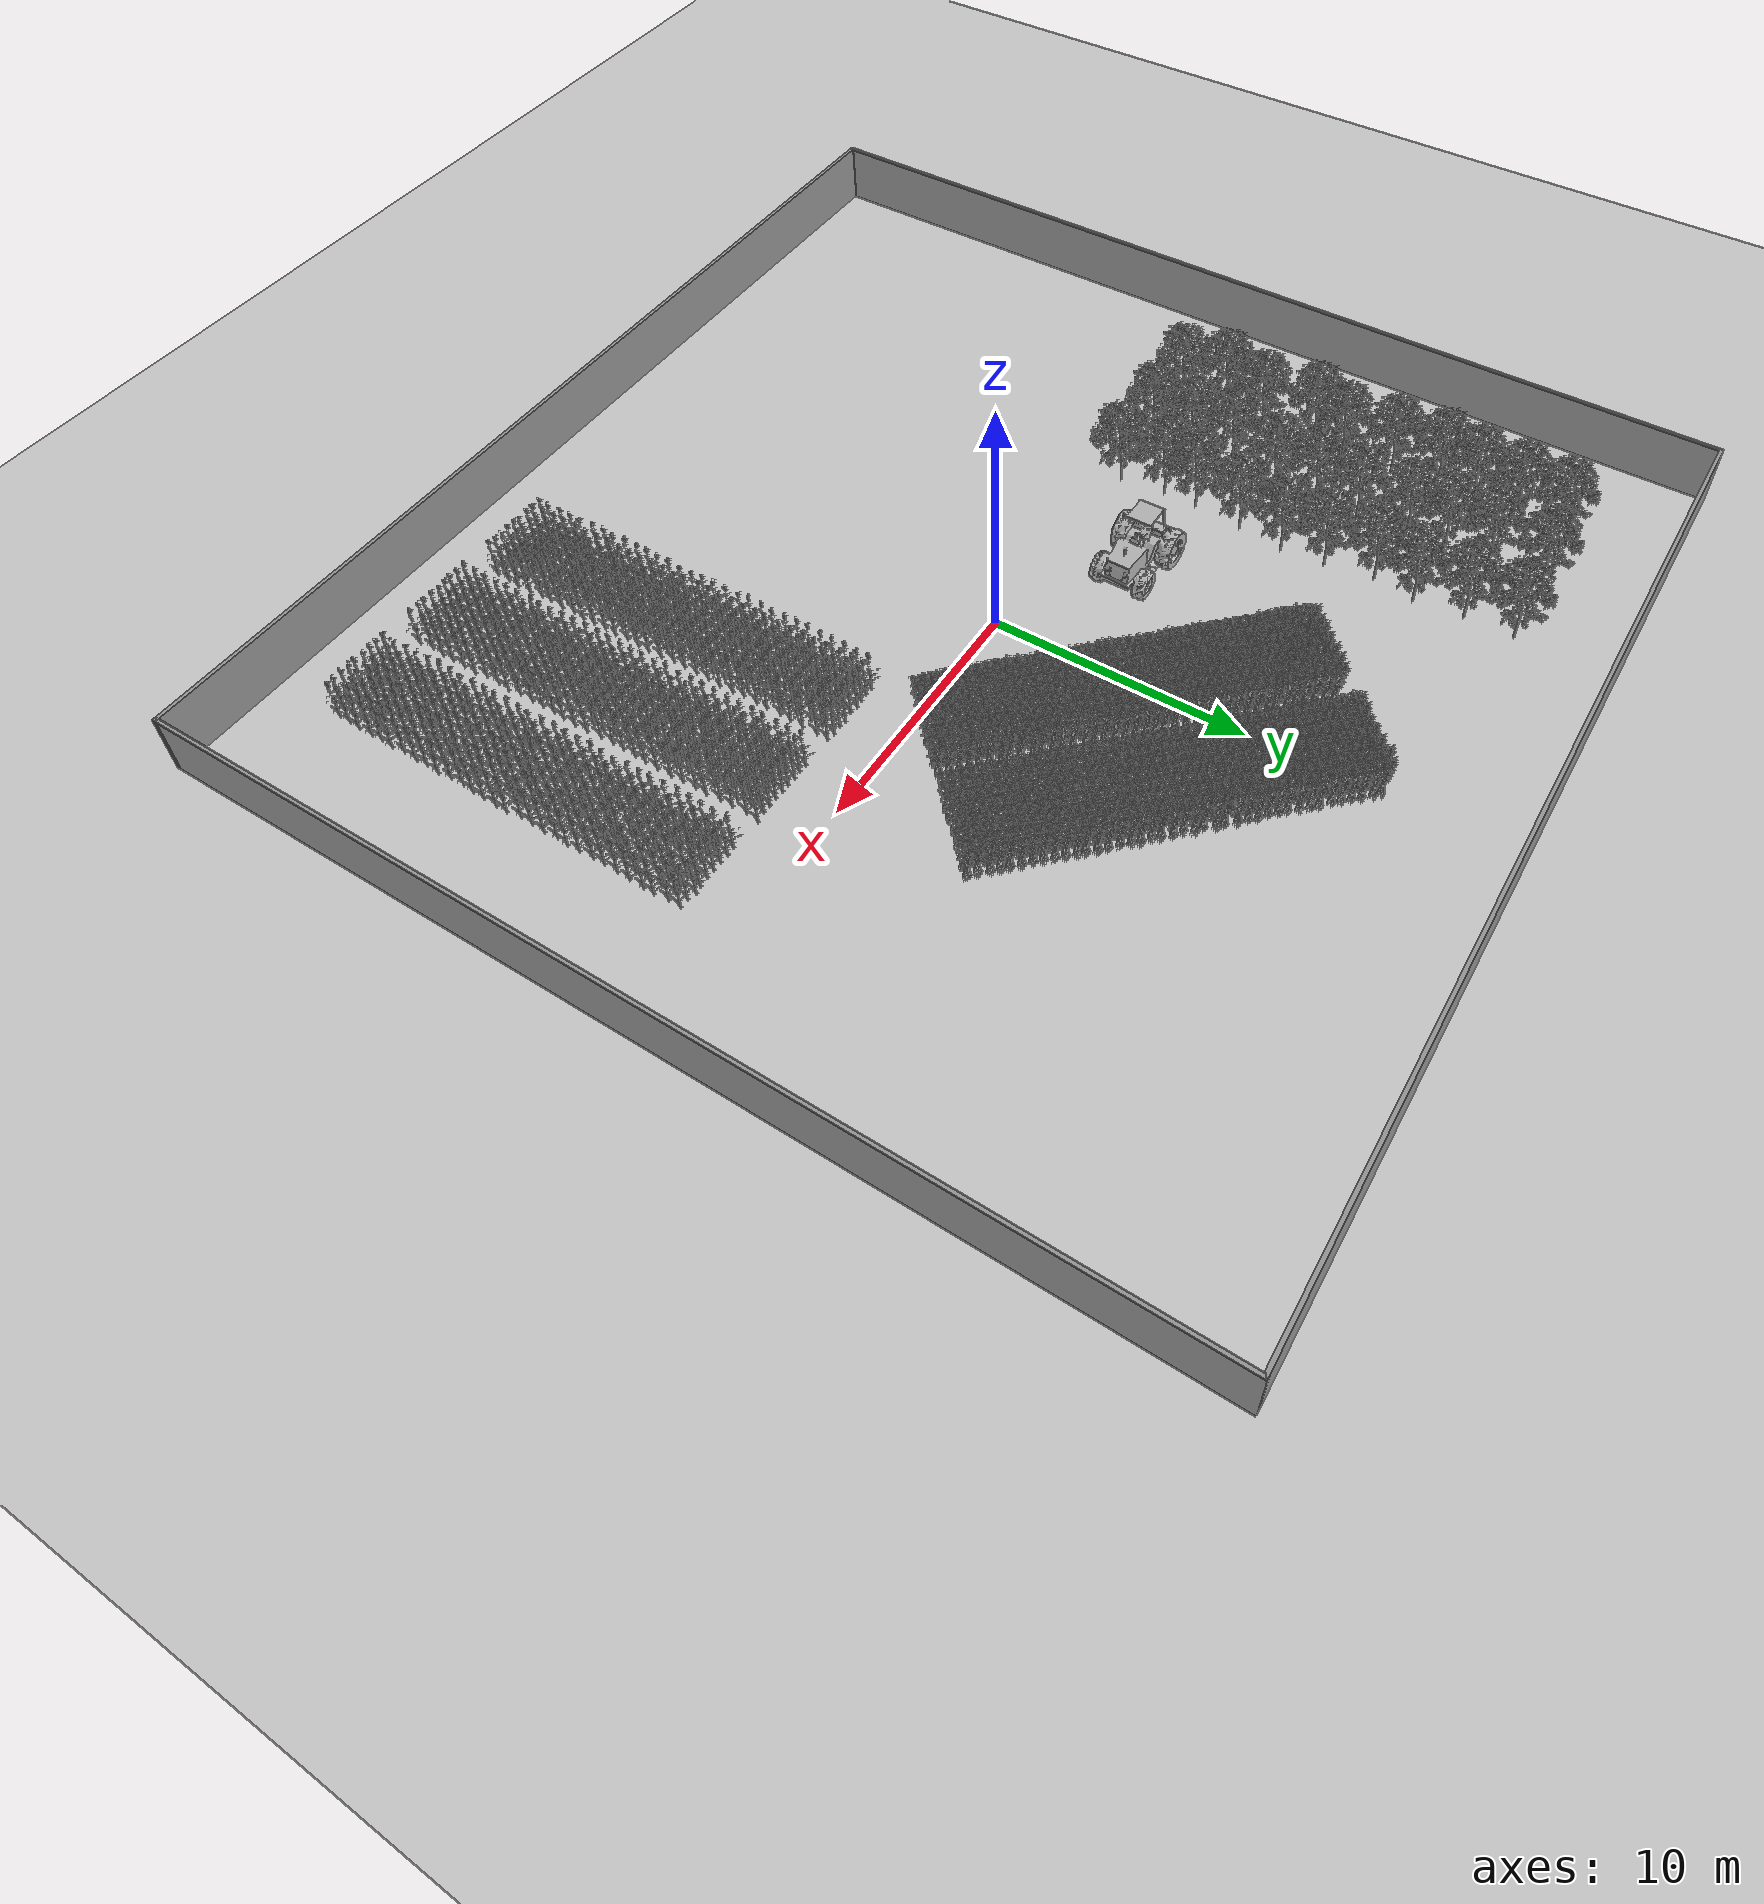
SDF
<sdf version="1.7">
 <world name="farmland_world">
  <light name="sun" type="directional">
   <pose>0 0 10 0 -0 0</pose>
   <diffuse>0.8 0.8 0.8 1</diffuse>
   <specular>0.2 0.2 0.2 1</specular>
   <attenuation>
    <range>1000</range>
    <constant>0.9</constant>
    <linear>0.01</linear>
    <quadratic>0.001</quadratic>
   </attenuation>
   <direction>-0.5 0.1 -0.9</direction>
   <spot><inner_angle>0</inner_angle><outer_angle>0</outer_angle><falloff>0</falloff></spot>
  </light>
  <gravity>0 0 -9.8</gravity>
  <magnetic_field>6e-06 2.3e-05 -4.2e-05</magnetic_field>
  <atmosphere type="adiabatic"/>
  <physics type="ode">
   <max_step_size>0.001</max_step_size>
   <real_time_factor>1</real_time_factor>
   <real_time_update_rate>1000</real_time_update_rate>
  </physics>
  <scene><ambient>0.4 0.4 0.4 1</ambient><background>0.7 0.7 0.7 1</background><shadows>1</shadows></scene>
  <spherical_coordinates>
   <surface_model>EARTH_WGS84</surface_model>
   <latitude_deg>0</latitude_deg>
   <longitude_deg>0</longitude_deg>
   <elevation>0</elevation>
   <heading_deg>0</heading_deg>
  </spherical_coordinates>
  <model name="ground_plane">
   <static>1</static>
   <link name="link">
    <collision name="collision">
     <geometry><plane><normal>0 0 1</normal><size>40.0 40.0</size></plane></geometry>
     <surface><friction><ode><mu>100</mu><mu2>50</mu2></ode></friction></surface>
    </collision>
    <visual name="visual">
     <cast_shadows>0</cast_shadows>
     <geometry><plane><normal>0 0 1</normal><size>40.0 40.0</size></plane></geometry>
     <material>
      <script><uri>file://media/materials/scripts/gazebo.material</uri><name>Gazebo/Grey</name></script>
     </material>
    </visual>
   </link>
  </model>
  <model name="Walls">
   <link name="Wall_0">
    <collision name="Wall_0_Collision">
     <geometry><box><size>40.15 0.15 2.5</size></box></geometry>
     <pose>0 0 1.25 0 -0 0</pose>
    </collision>
    <visual name="Wall_0_Visual">
     <pose>0 0 1.25 0 -0 0</pose>
     <geometry><box><size>40.15 0.15 2.5</size></box></geometry>
     <material>
      <script><uri>file://media/materials/scripts/gazebo.material</uri><name>Gazebo/Grey</name></script>
      <ambient>1 1 1 1</ambient>
     </material>
     <meta><layer>0</layer></meta>
    </visual>
    <pose>-20.0 0 0 0 -0 1.5708</pose>
   </link>
   <link name="Wall_1">
    <collision name="Wall_1_Collision">
     <geometry><box><size>40.15 0.15 2.5</size></box></geometry>
     <pose>0 0 1.25 0 -0 0</pose>
    </collision>
    <visual name="Wall_1_Visual">
     <pose>0 0 1.25 0 -0 0</pose>
     <geometry><box><size>40.15 0.15 2.5</size></box></geometry>
     <material>
      <script><uri>file://media/materials/scripts/gazebo.material</uri><name>Gazebo/Grey</name></script>
      <ambient>1 1 1 1</ambient>
     </material>
     <meta><layer>0</layer></meta>
    </visual>
    <pose>0 20.0 0 0 -0 0</pose>
   </link>
   <link name="Wall_2">
    <collision name="Wall_2_Collision">
     <geometry><box><size>40.15 0.15 2.5</size></box></geometry>
     <pose>0 0 1.25 0 -0 0</pose>
    </collision>
    <visual name="Wall_2_Visual">
     <pose>0 0 1.25 0 -0 0</pose>
     <geometry><box><size>40.15 0.15 2.5</size></box></geometry>
     <material>
      <script><uri>file://media/materials/scripts/gazebo.material</uri><name>Gazebo/Grey</name></script>
      <ambient>1 1 1 1</ambient>
     </material>
     <meta><layer>0</layer></meta>
    </visual>
    <pose>20.0 0 0 0 -0 -1.5708</pose>
   </link>
   <link name="Wall_3">
    <collision name="Wall_3_Collision">
     <geometry><box><size>40.15 0.15 2.5</size></box></geometry>
     <pose>0 0 1.25 0 -0 0</pose>
    </collision>
    <visual name="Wall_3_Visual">
     <pose>0 0 1.25 0 -0 0</pose>
     <geometry><box><size>40.15 0.15 2.5</size></box></geometry>
     <material>
      <script><uri>file://media/materials/scripts/gazebo.material</uri><name>Gazebo/Grey</name></script>
      <ambient>1 1 1 1</ambient>
     </material>
     <meta><layer>0</layer></meta>
    </visual>
    <pose>0 -20.0 0 0 -0 3.14159</pose>
   </link>
   <static>1</static>
  </model>
  <model name="tree_0_0">
   <static>1</static>
   <link name="link">
    <collision name="collision">
     <geometry><mesh><uri>model://Birch_tree/birch_tree_5p.obj</uri><scale>1 1 1</scale></mesh></geometry>
     <surface><friction><ode><mu>100</mu><mu2>50</mu2></ode></friction></surface>
    </collision>
    <visual name="visual">
     <geometry><mesh><uri>model://Birch_tree/birch_tree_5p.obj</uri><scale>1 1 1</scale></mesh></geometry>
    </visual>
   </link>
   <pose>-15.059012775614557 15.855233422151644 0 0 0 0</pose>
  </model>
  <model name="tree_0_1">
   <static>1</static>
   <link name="link">
    <collision name="collision">
     <geometry><mesh><uri>model://Birch_tree/birch_tree_5p.obj</uri><scale>1 1 1</scale></mesh></geometry>
     <surface><friction><ode><mu>100</mu><mu2>50</mu2></ode></friction></surface>
    </collision>
    <visual name="visual">
     <geometry><mesh><uri>model://Birch_tree/birch_tree_5p.obj</uri><scale>1 1 1</scale></mesh></geometry>
    </visual>
   </link>
   <pose>-15.108912450633719 14.116969423663859 0 0 0 0</pose>
  </model>
  <model name="tree_0_2">
   <static>1</static>
   <link name="link">
    <collision name="collision">
     <geometry><mesh><uri>model://Birch_tree/birch_tree_5p.obj</uri><scale>1 1 1</scale></mesh></geometry>
     <surface><friction><ode><mu>100</mu><mu2>50</mu2></ode></friction></surface>
    </collision>
    <visual name="visual">
     <geometry><mesh><uri>model://Birch_tree/birch_tree_5p.obj</uri><scale>1 1 1</scale></mesh></geometry>
    </visual>
   </link>
   <pose>-15.077792916858806 12.366255272204592 0 0 0 0</pose>
  </model>
  <model name="tree_0_3">
   <static>1</static>
   <link name="link">
    <collision name="collision">
     <geometry><mesh><uri>model://Birch_tree/birch_tree_5p.obj</uri><scale>1 1 1</scale></mesh></geometry>
     <surface><friction><ode><mu>100</mu><mu2>50</mu2></ode></friction></surface>
    </collision>
    <visual name="visual">
     <geometry><mesh><uri>model://Birch_tree/birch_tree_5p.obj</uri><scale>1 1 1</scale></mesh></geometry>
    </visual>
   </link>
   <pose>-15.262357777004812 10.881119997271313 0 0 0 0</pose>
  </model>
  <model name="tree_0_4">
   <static>1</static>
   <link name="link">
    <collision name="collision">
     <geometry><mesh><uri>model://Birch_tree/birch_tree_5p.obj</uri><scale>1 1 1</scale></mesh></geometry>
     <surface><friction><ode><mu>100</mu><mu2>50</mu2></ode></friction></surface>
    </collision>
    <visual name="visual">
     <geometry><mesh><uri>model://Birch_tree/birch_tree_5p.obj</uri><scale>1 1 1</scale></mesh></geometry>
    </visual>
   </link>
   <pose>-15.06561841178248 9.022281137910282 0 0 0 0</pose>
  </model>
  <model name="tree_0_5">
   <static>1</static>
   <link name="link">
    <collision name="collision">
     <geometry><mesh><uri>model://Birch_tree/birch_tree_5p.obj</uri><scale>1 1 1</scale></mesh></geometry>
     <surface><friction><ode><mu>100</mu><mu2>50</mu2></ode></friction></surface>
    </collision>
    <visual name="visual">
     <geometry><mesh><uri>model://Birch_tree/birch_tree_5p.obj</uri><scale>1 1 1</scale></mesh></geometry>
    </visual>
   </link>
   <pose>-14.782993091199312 7.034720524604587 0 0 0 0</pose>
  </model>
  <model name="tree_0_6">
   <static>1</static>
   <link name="link">
    <collision name="collision">
     <geometry><mesh><uri>model://Birch_tree/birch_tree_5p.obj</uri><scale>1 1 1</scale></mesh></geometry>
     <surface><friction><ode><mu>100</mu><mu2>50</mu2></ode></friction></surface>
    </collision>
    <visual name="visual">
     <geometry><mesh><uri>model://Birch_tree/birch_tree_5p.obj</uri><scale>1 1 1</scale></mesh></geometry>
    </visual>
   </link>
   <pose>-15.25957002248026 5.612003605544245 0 0 0 0</pose>
  </model>
  <model name="tree_0_7">
   <static>1</static>
   <link name="link">
    <collision name="collision">
     <geometry><mesh><uri>model://Birch_tree/birch_tree_5p.obj</uri><scale>1 1 1</scale></mesh></geometry>
     <surface><friction><ode><mu>100</mu><mu2>50</mu2></ode></friction></surface>
    </collision>
    <visual name="visual">
     <geometry><mesh><uri>model://Birch_tree/birch_tree_5p.obj</uri><scale>1 1 1</scale></mesh></geometry>
    </visual>
   </link>
   <pose>-14.854777682466423 3.5006724442776855 0 0 0 0</pose>
  </model>
  <model name="tree_0_8">
   <static>1</static>
   <link name="link">
    <collision name="collision">
     <geometry><mesh><uri>model://Birch_tree/birch_tree_5p.obj</uri><scale>1 1 1</scale></mesh></geometry>
     <surface><friction><ode><mu>100</mu><mu2>50</mu2></ode></friction></surface>
    </collision>
    <visual name="visual">
     <geometry><mesh><uri>model://Birch_tree/birch_tree_5p.obj</uri><scale>1 1 1</scale></mesh></geometry>
    </visual>
   </link>
   <pose>-15.268603431191494 1.6723369577771203 0 0 0 0</pose>
  </model>
  <model name="tree_0_9">
   <static>1</static>
   <link name="link">
    <collision name="collision">
     <geometry><mesh><uri>model://Birch_tree/birch_tree_5p.obj</uri><scale>1 1 1</scale></mesh></geometry>
     <surface><friction><ode><mu>100</mu><mu2>50</mu2></ode></friction></surface>
    </collision>
    <visual name="visual">
     <geometry><mesh><uri>model://Birch_tree/birch_tree_5p.obj</uri><scale>1 1 1</scale></mesh></geometry>
    </visual>
   </link>
   <pose>-14.709556604108974 0.0029621043253607038 0 0 0 0</pose>
  </model>
  <model name="tree_0_10">
   <static>1</static>
   <link name="link">
    <collision name="collision">
     <geometry><mesh><uri>model://Birch_tree/birch_tree_5p.obj</uri><scale>1 1 1</scale></mesh></geometry>
     <surface><friction><ode><mu>100</mu><mu2>50</mu2></ode></friction></surface>
    </collision>
    <visual name="visual">
     <geometry><mesh><uri>model://Birch_tree/birch_tree_5p.obj</uri><scale>1 1 1</scale></mesh></geometry>
    </visual>
   </link>
   <pose>-12.213730359629619 16.177215334826762 0 0 0 0</pose>
  </model>
  <model name="tree_0_11">
   <static>1</static>
   <link name="link">
    <collision name="collision">
     <geometry><mesh><uri>model://Birch_tree/birch_tree_5p.obj</uri><scale>1 1 1</scale></mesh></geometry>
     <surface><friction><ode><mu>100</mu><mu2>50</mu2></ode></friction></surface>
    </collision>
    <visual name="visual">
     <geometry><mesh><uri>model://Birch_tree/birch_tree_5p.obj</uri><scale>1 1 1</scale></mesh></geometry>
    </visual>
   </link>
   <pose>-12.283267974192942 14.087747977855141 0 0 0 0</pose>
  </model>
  <model name="tree_0_12">
   <static>1</static>
   <link name="link">
    <collision name="collision">
     <geometry><mesh><uri>model://Birch_tree/birch_tree_5p.obj</uri><scale>1 1 1</scale></mesh></geometry>
     <surface><friction><ode><mu>100</mu><mu2>50</mu2></ode></friction></surface>
    </collision>
    <visual name="visual">
     <geometry><mesh><uri>model://Birch_tree/birch_tree_5p.obj</uri><scale>1 1 1</scale></mesh></geometry>
    </visual>
   </link>
   <pose>-12.075032601513408 12.407185623305054 0 0 0 0</pose>
  </model>
  <model name="tree_0_13">
   <static>1</static>
   <link name="link">
    <collision name="collision">
     <geometry><mesh><uri>model://Birch_tree/birch_tree_5p.obj</uri><scale>1 1 1</scale></mesh></geometry>
     <surface><friction><ode><mu>100</mu><mu2>50</mu2></ode></friction></surface>
    </collision>
    <visual name="visual">
     <geometry><mesh><uri>model://Birch_tree/birch_tree_5p.obj</uri><scale>1 1 1</scale></mesh></geometry>
    </visual>
   </link>
   <pose>-12.026765028564846 10.917565747010455 0 0 0 0</pose>
  </model>
  <model name="tree_0_14">
   <static>1</static>
   <link name="link">
    <collision name="collision">
     <geometry><mesh><uri>model://Birch_tree/birch_tree_5p.obj</uri><scale>1 1 1</scale></mesh></geometry>
     <surface><friction><ode><mu>100</mu><mu2>50</mu2></ode></friction></surface>
    </collision>
    <visual name="visual">
     <geometry><mesh><uri>model://Birch_tree/birch_tree_5p.obj</uri><scale>1 1 1</scale></mesh></geometry>
    </visual>
   </link>
   <pose>-11.818177014905816 8.940150235905131 0 0 0 0</pose>
  </model>
  <model name="tree_0_15">
   <static>1</static>
   <link name="link">
    <collision name="collision">
     <geometry><mesh><uri>model://Birch_tree/birch_tree_5p.obj</uri><scale>1 1 1</scale></mesh></geometry>
     <surface><friction><ode><mu>100</mu><mu2>50</mu2></ode></friction></surface>
    </collision>
    <visual name="visual">
     <geometry><mesh><uri>model://Birch_tree/birch_tree_5p.obj</uri><scale>1 1 1</scale></mesh></geometry>
    </visual>
   </link>
   <pose>-11.904515960097234 7.170478906004172 0 0 0 0</pose>
  </model>
  <model name="tree_0_16">
   <static>1</static>
   <link name="link">
    <collision name="collision">
     <geometry><mesh><uri>model://Birch_tree/birch_tree_5p.obj</uri><scale>1 1 1</scale></mesh></geometry>
     <surface><friction><ode><mu>100</mu><mu2>50</mu2></ode></friction></surface>
    </collision>
    <visual name="visual">
     <geometry><mesh><uri>model://Birch_tree/birch_tree_5p.obj</uri><scale>1 1 1</scale></mesh></geometry>
    </visual>
   </link>
   <pose>-11.758908887040334 5.487855164628342 0 0 0 0</pose>
  </model>
  <model name="tree_0_17">
   <static>1</static>
   <link name="link">
    <collision name="collision">
     <geometry><mesh><uri>model://Birch_tree/birch_tree_5p.obj</uri><scale>1 1 1</scale></mesh></geometry>
     <surface><friction><ode><mu>100</mu><mu2>50</mu2></ode></friction></surface>
    </collision>
    <visual name="visual">
     <geometry><mesh><uri>model://Birch_tree/birch_tree_5p.obj</uri><scale>1 1 1</scale></mesh></geometry>
    </visual>
   </link>
   <pose>-12.234738455365026 3.447915089518777 0 0 0 0</pose>
  </model>
  <model name="tree_0_18">
   <static>1</static>
   <link name="link">
    <collision name="collision">
     <geometry><mesh><uri>model://Birch_tree/birch_tree_5p.obj</uri><scale>1 1 1</scale></mesh></geometry>
     <surface><friction><ode><mu>100</mu><mu2>50</mu2></ode></friction></surface>
    </collision>
    <visual name="visual">
     <geometry><mesh><uri>model://Birch_tree/birch_tree_5p.obj</uri><scale>1 1 1</scale></mesh></geometry>
    </visual>
   </link>
   <pose>-11.885335388926457 1.8447125004237512 0 0 0 0</pose>
  </model>
  <model name="tree_0_19">
   <static>1</static>
   <link name="link">
    <collision name="collision">
     <geometry><mesh><uri>model://Birch_tree/birch_tree_5p.obj</uri><scale>1 1 1</scale></mesh></geometry>
     <surface><friction><ode><mu>100</mu><mu2>50</mu2></ode></friction></surface>
    </collision>
    <visual name="visual">
     <geometry><mesh><uri>model://Birch_tree/birch_tree_5p.obj</uri><scale>1 1 1</scale></mesh></geometry>
    </visual>
   </link>
   <pose>-11.908766050019784 0.14275515385399704 0 0 0 0</pose>
  </model>
  <model name="tree_0_20">
   <static>1</static>
   <link name="link">
    <collision name="collision">
     <geometry><mesh><uri>model://Birch_tree/birch_tree_5p.obj</uri><scale>1 1 1</scale></mesh></geometry>
     <surface><friction><ode><mu>100</mu><mu2>50</mu2></ode></friction></surface>
    </collision>
    <visual name="visual">
     <geometry><mesh><uri>model://Birch_tree/birch_tree_5p.obj</uri><scale>1 1 1</scale></mesh></geometry>
    </visual>
   </link>
   <pose>-9.126919527044588 16.253895582484507 0 0 0 0</pose>
  </model>
  <model name="tree_0_21">
   <static>1</static>
   <link name="link">
    <collision name="collision">
     <geometry><mesh><uri>model://Birch_tree/birch_tree_5p.obj</uri><scale>1 1 1</scale></mesh></geometry>
     <surface><friction><ode><mu>100</mu><mu2>50</mu2></ode></friction></surface>
    </collision>
    <visual name="visual">
     <geometry><mesh><uri>model://Birch_tree/birch_tree_5p.obj</uri><scale>1 1 1</scale></mesh></geometry>
    </visual>
   </link>
   <pose>-9.077648108787704 14.355252017229716 0 0 0 0</pose>
  </model>
  <model name="tree_0_22">
   <static>1</static>
   <link name="link">
    <collision name="collision">
     <geometry><mesh><uri>model://Birch_tree/birch_tree_5p.obj</uri><scale>1 1 1</scale></mesh></geometry>
     <surface><friction><ode><mu>100</mu><mu2>50</mu2></ode></friction></surface>
    </collision>
    <visual name="visual">
     <geometry><mesh><uri>model://Birch_tree/birch_tree_5p.obj</uri><scale>1 1 1</scale></mesh></geometry>
    </visual>
   </link>
   <pose>-8.87209466249776 12.458780122995835 0 0 0 0</pose>
  </model>
  <model name="tree_0_23">
   <static>1</static>
   <link name="link">
    <collision name="collision">
     <geometry><mesh><uri>model://Birch_tree/birch_tree_5p.obj</uri><scale>1 1 1</scale></mesh></geometry>
     <surface><friction><ode><mu>100</mu><mu2>50</mu2></ode></friction></surface>
    </collision>
    <visual name="visual">
     <geometry><mesh><uri>model://Birch_tree/birch_tree_5p.obj</uri><scale>1 1 1</scale></mesh></geometry>
    </visual>
   </link>
   <pose>-9.1796147193597 10.799036561196706 0 0 0 0</pose>
  </model>
  <model name="tree_0_24">
   <static>1</static>
   <link name="link">
    <collision name="collision">
     <geometry><mesh><uri>model://Birch_tree/birch_tree_5p.obj</uri><scale>1 1 1</scale></mesh></geometry>
     <surface><friction><ode><mu>100</mu><mu2>50</mu2></ode></friction></surface>
    </collision>
    <visual name="visual">
     <geometry><mesh><uri>model://Birch_tree/birch_tree_5p.obj</uri><scale>1 1 1</scale></mesh></geometry>
    </visual>
   </link>
   <pose>-8.893458730529527 8.90594391590294 0 0 0 0</pose>
  </model>
  <model name="tree_0_25">
   <static>1</static>
   <link name="link">
    <collision name="collision">
     <geometry><mesh><uri>model://Birch_tree/birch_tree_5p.obj</uri><scale>1 1 1</scale></mesh></geometry>
     <surface><friction><ode><mu>100</mu><mu2>50</mu2></ode></friction></surface>
    </collision>
    <visual name="visual">
     <geometry><mesh><uri>model://Birch_tree/birch_tree_5p.obj</uri><scale>1 1 1</scale></mesh></geometry>
    </visual>
   </link>
   <pose>-8.76903385322635 7.17981956686878 0 0 0 0</pose>
  </model>
  <model name="tree_0_26">
   <static>1</static>
   <link name="link">
    <collision name="collision">
     <geometry><mesh><uri>model://Birch_tree/birch_tree_5p.obj</uri><scale>1 1 1</scale></mesh></geometry>
     <surface><friction><ode><mu>100</mu><mu2>50</mu2></ode></friction></surface>
    </collision>
    <visual name="visual">
     <geometry><mesh><uri>model://Birch_tree/birch_tree_5p.obj</uri><scale>1 1 1</scale></mesh></geometry>
    </visual>
   </link>
   <pose>-9.02159091520577 5.328958924342956 0 0 0 0</pose>
  </model>
  <model name="tree_0_27">
   <static>1</static>
   <link name="link">
    <collision name="collision">
     <geometry><mesh><uri>model://Birch_tree/birch_tree_5p.obj</uri><scale>1 1 1</scale></mesh></geometry>
     <surface><friction><ode><mu>100</mu><mu2>50</mu2></ode></friction></surface>
    </collision>
    <visual name="visual">
     <geometry><mesh><uri>model://Birch_tree/birch_tree_5p.obj</uri><scale>1 1 1</scale></mesh></geometry>
    </visual>
   </link>
   <pose>-9.229629016639317 3.353880451471138 0 0 0 0</pose>
  </model>
  <model name="tree_0_28">
   <static>1</static>
   <link name="link">
    <collision name="collision">
     <geometry><mesh><uri>model://Birch_tree/birch_tree_5p.obj</uri><scale>1 1 1</scale></mesh></geometry>
     <surface><friction><ode><mu>100</mu><mu2>50</mu2></ode></friction></surface>
    </collision>
    <visual name="visual">
     <geometry><mesh><uri>model://Birch_tree/birch_tree_5p.obj</uri><scale>1 1 1</scale></mesh></geometry>
    </visual>
   </link>
   <pose>-9.262095150295508 1.983846602006953 0 0 0 0</pose>
  </model>
  <model name="tree_0_29">
   <static>1</static>
   <link name="link">
    <collision name="collision">
     <geometry><mesh><uri>model://Birch_tree/birch_tree_5p.obj</uri><scale>1 1 1</scale></mesh></geometry>
     <surface><friction><ode><mu>100</mu><mu2>50</mu2></ode></friction></surface>
    </collision>
    <visual name="visual">
     <geometry><mesh><uri>model://Birch_tree/birch_tree_5p.obj</uri><scale>1 1 1</scale></mesh></geometry>
    </visual>
   </link>
   <pose>-9.122310819781465 0.13560254653077516 0 0 0 0</pose>
  </model>
  <model name="tree_2_0">
   <static>1</static>
   <link name="link">
    <collision name="collision">
     <geometry><mesh><uri>model://Corn/corn_5p.obj</uri><scale>1 1 1</scale></mesh></geometry>
     <surface><friction><ode><mu>100</mu><mu2>50</mu2></ode></friction></surface>
    </collision>
    <visual name="visual">
     <geometry><mesh><uri>model://Corn/corn_5p.obj</uri><scale>1 1 1</scale></mesh></geometry>
    </visual>
   </link>
   <pose>5.043748606266506 0.012698637609376352 0 0 0 0</pose>
  </model>
  <model name="tree_2_1">
   <static>1</static>
   <link name="link">
    <collision name="collision">
     <geometry><mesh><uri>model://Corn/corn_5p.obj</uri><scale>1 1 1</scale></mesh></geometry>
     <surface><friction><ode><mu>100</mu><mu2>50</mu2></ode></friction></surface>
    </collision>
    <visual name="visual">
     <geometry><mesh><uri>model://Corn/corn_5p.obj</uri><scale>1 1 1</scale></mesh></geometry>
    </visual>
   </link>
   <pose>4.75956731364243 0.24568094177987185 0 0 0 0</pose>
  </model>
  <model name="tree_2_2">
   <static>1</static>
   <link name="link">
    <collision name="collision">
     <geometry><mesh><uri>model://Corn/corn_5p.obj</uri><scale>1 1 1</scale></mesh></geometry>
     <surface><friction><ode><mu>100</mu><mu2>50</mu2></ode></friction></surface>
    </collision>
    <visual name="visual">
     <geometry><mesh><uri>model://Corn/corn_5p.obj</uri><scale>1 1 1</scale></mesh></geometry>
    </visual>
   </link>
   <pose>4.460421943026819 0.5468915827871715 0 0 0 0</pose>
  </model>
  <model name="tree_2_3">
   <static>1</static>
   <link name="link">
    <collision name="collision">
     <geometry><mesh><uri>model://Corn/corn_5p.obj</uri><scale>1 1 1</scale></mesh></geometry>
     <surface><friction><ode><mu>100</mu><mu2>50</mu2></ode></friction></surface>
    </collision>
    <visual name="visual">
     <geometry><mesh><uri>model://Corn/corn_5p.obj</uri><scale>1 1 1</scale></mesh></geometry>
    </visual>
   </link>
   <pose>4.231845531452798 0.7637563604710286 0 0 0 0</pose>
  </model>
  <model name="tree_2_4">
   <static>1</static>
   <link name="link">
    <collision name="collision">
     <geometry><mesh><uri>model://Corn/corn_5p.obj</uri><scale>1 1 1</scale></mesh></geometry>
     <surface><friction><ode><mu>100</mu><mu2>50</mu2></ode></friction></surface>
    </collision>
    <visual name="visual">
     <geometry><mesh><uri>model://Corn/corn_5p.obj</uri><scale>1 1 1</scale></mesh></geometry>
    </visual>
   </link>
   <pose>3.976620042952896 1.0468861932850682 0 0 0 0</pose>
  </model>
  <model name="tree_2_5">
   <static>1</static>
   <link name="link">
    <collision name="collision">
     <geometry><mesh><uri>model://Corn/corn_5p.obj</uri><scale>1 1 1</scale></mesh></geometry>
     <surface><friction><ode><mu>100</mu><mu2>50</mu2></ode></friction></surface>
    </collision>
    <visual name="visual">
     <geometry><mesh><uri>model://Corn/corn_5p.obj</uri><scale>1 1 1</scale></mesh></geometry>
    </visual>
   </link>
   <pose>3.7075180982488405 1.313542585969232 0 0 0 0</pose>
  </model>
  <model name="tree_2_6">
   <static>1</static>
   <link name="link">
    <collision name="collision">
     <geometry><mesh><uri>model://Corn/corn_5p.obj</uri><scale>1 1 1</scale></mesh></geometry>
     <surface><friction><ode><mu>100</mu><mu2>50</mu2></ode></friction></surface>
    </collision>
    <visual name="visual">
     <geometry><mesh><uri>model://Corn/corn_5p.obj</uri><scale>1 1 1</scale></mesh></geometry>
    </visual>
   </link>
   <pose>3.4529204111559277 1.5609485227874136 0 0 0 0</pose>
  </model>
  <model name="tree_2_7">
   <static>1</static>
   <link name="link">
    <collision name="collision">
     <geometry><mesh><uri>model://Corn/corn_5p.obj</uri><scale>1 1 1</scale></mesh></geometry>
     <surface><friction><ode><mu>100</mu><mu2>50</mu2></ode></friction></surface>
    </collision>
    <visual name="visual">
     <geometry><mesh><uri>model://Corn/corn_5p.obj</uri><scale>1 1 1</scale></mesh></geometry>
    </visual>
   </link>
   <pose>3.161026772593634 1.7599788649802344 0 0 0 0</pose>
  </model>
  <model name="tree_2_8">
   <static>1</static>
   <link name="link">
    <collision name="collision">
     <geometry><mesh><uri>model://Corn/corn_5p.obj</uri><scale>1 1 1</scale></mesh></geometry>
     <surface><friction><ode><mu>100</mu><mu2>50</mu2></ode></friction></surface>
    </collision>
    <visual name="visual">
     <geometry><mesh><uri>model://Corn/corn_5p.obj</uri><scale>1 1 1</scale></mesh></geometry>
    </visual>
   </link>
   <pose>2.902728075601026 2.0599299980603307 0 0 0 0</pose>
  </model>
  <model name="tree_2_9">
   <static>1</static>
   <link name="link">
    <collision name="collision">
     <geometry><mesh><uri>model://Corn/corn_5p.obj</uri><scale>1 1 1</scale></mesh></geometry>
     <surface><friction><ode><mu>100</mu><mu2>50</mu2></ode></friction></surface>
    </collision>
    <visual name="visual">
     <geometry><mesh><uri>model://Corn/corn_5p.obj</uri><scale>1 1 1</scale></mesh></geometry>
    </visual>
   </link>
   <pose>2.700123445635079 2.2680798346072186 0 0 0 0</pose>
  </model>
  <model name="tree_2_10">
   <static>1</static>
   <link name="link">
    <collision name="collision">
     <geometry><mesh><uri>model://Corn/corn_5p.obj</uri><scale>1 1 1</scale></mesh></geometry>
     <surface><friction><ode><mu>100</mu><mu2>50</mu2></ode></friction></surface>
    </collision>
    <visual name="visual">
     <geometry><mesh><uri>model://Corn/corn_5p.obj</uri><scale>1 1 1</scale></mesh></geometry>
    </visual>
   </link>
   <pose>2.4412175031869756 2.5863544420814337 0 0 0 0</pose>
  </model>
  <model name="tree_2_11">
   <static>1</static>
   <link name="link">
    <collision name="collision">
     <geometry><mesh><uri>model://Corn/corn_5p.obj</uri><scale>1 1 1</scale></mesh></geometry>
     <surface><friction><ode><mu>100</mu><mu2>50</mu2></ode></friction></surface>
    </collision>
    <visual name="visual">
     <geometry><mesh><uri>model://Corn/corn_5p.obj</uri><scale>1 1 1</scale></mesh></geometry>
    </visual>
   </link>
   <pose>2.2288761643939847 2.7925658233045842 0 0 0 0</pose>
  </model>
  <model name="tree_2_12">
   <static>1</static>
   <link name="link">
    <collision name="collision">
     <geometry><mesh><uri>model://Corn/corn_5p.obj</uri><scale>1 1 1</scale></mesh></geometry>
     <surface><friction><ode><mu>100</mu><mu2>50</mu2></ode></friction></surface>
    </collision>
    <visual name="visual">
     <geometry><mesh><uri>model://Corn/corn_5p.obj</uri><scale>1 1 1</scale></mesh></geometry>
    </visual>
   </link>
   <pose>1.923788779430718 3.0364917466249888 0 0 0 0</pose>
  </model>
  <model name="tree_2_13">
   <static>1</static>
   <link name="link">
    <collision name="collision">
     <geometry><mesh><uri>model://Corn/corn_5p.obj</uri><scale>1 1 1</scale></mesh></geometry>
     <surface><friction><ode><mu>100</mu><mu2>50</mu2></ode></friction></surface>
    </collision>
    <visual name="visual">
     <geometry><mesh><uri>model://Corn/corn_5p.obj</uri><scale>1 1 1</scale></mesh></geometry>
    </visual>
   </link>
   <pose>1.6269691821464185 3.3320203818958465 0 0 0 0</pose>
  </model>
  <model name="tree_2_14">
   <static>1</static>
   <link name="link">
    <collision name="collision">
     <geometry><mesh><uri>model://Corn/corn_5p.obj</uri><scale>1 1 1</scale></mesh></geometry>
     <surface><friction><ode><mu>100</mu><mu2>50</mu2></ode></friction></surface>
    </collision>
    <visual name="visual">
     <geometry><mesh><uri>model://Corn/corn_5p.obj</uri><scale>1 1 1</scale></mesh></geometry>
    </visual>
   </link>
   <pose>1.38819604802699 3.601108146339118 0 0 0 0</pose>
  </model>
  <model name="tree_2_15">
   <static>1</static>
   <link name="link">
    <collision name="collision">
     <geometry><mesh><uri>model://Corn/corn_5p.obj</uri><scale>1 1 1</scale></mesh></geometry>
     <surface><friction><ode><mu>100</mu><mu2>50</mu2></ode></friction></surface>
    </collision>
    <visual name="visual">
     <geometry><mesh><uri>model://Corn/corn_5p.obj</uri><scale>1 1 1</scale></mesh></geometry>
    </visual>
   </link>
   <pose>1.1832154308116214 3.883061813637551 0 0 0 0</pose>
  </model>
  <model name="tree_2_16">
   <static>1</static>
   <link name="link">
    <collision name="collision">
     <geometry><mesh><uri>model://Corn/corn_5p.obj</uri><scale>1 1 1</scale></mesh></geometry>
     <surface><friction><ode><mu>100</mu><mu2>50</mu2></ode></friction></surface>
    </collision>
    <visual name="visual">
     <geometry><mesh><uri>model://Corn/corn_5p.obj</uri><scale>1 1 1</scale></mesh></geometry>
    </visual>
   </link>
   <pose>0.9364932637710696 4.053870386266763 0 0 0 0</pose>
  </model>
  <model name="tree_2_17">
   <static>1</static>
   <link name="link">
    <collision name="collision">
     <geometry><mesh><uri>model://Corn/corn_5p.obj</uri><scale>1 1 1</scale></mesh></geometry>
     <surface><friction><ode><mu>100</mu><mu2>50</mu2></ode></friction></surface>
    </collision>
    <visual name="visual">
     <geometry><mesh><uri>model://Corn/corn_5p.obj</uri><scale>1 1 1</scale></mesh></geometry>
    </visual>
   </link>
   <pose>0.6895567535866928 4.356237684138063 0 0 0 0</pose>
  </model>
  <model name="tree_2_18">
   <static>1</static>
   <link name="link">
    <collision name="collision">
     <geometry><mesh><uri>model://Corn/corn_5p.obj</uri><scale>1 1 1</scale></mesh></geometry>
     <surface><friction><ode><mu>100</mu><mu2>50</mu2></ode></friction></surface>
    </collision>
    <visual name="visual">
     <geometry><mesh><uri>model://Corn/corn_5p.obj</uri><scale>1 1 1</scale></mesh></geometry>
    </visual>
   </link>
   <pose>0.336295014910299 4.573606861579561 0 0 0 0</pose>
  </model>
  <model name="tree_2_19">
   <static>1</static>
   <link name="link">
    <collision name="collision">
     <geometry><mesh><uri>model://Corn/corn_5p.obj</uri><scale>1 1 1</scale></mesh></geometry>
     <surface><friction><ode><mu>100</mu><mu2>50</mu2></ode></friction></surface>
    </collision>
    <visual name="visual">
     <geometry><mesh><uri>model://Corn/corn_5p.obj</uri><scale>1 1 1</scale></mesh></geometry>
    </visual>
   </link>
   <pose>0.16100248109887924 4.822778924343438 0 0 0 0</pose>
  </model>
  <model name="tree_2_20">
   <static>1</static>
   <link name="link">
    <collision name="collision">
     <geometry><mesh><uri>model://Corn/corn_5p.obj</uri><scale>1 1 1</scale></mesh></geometry>
     <surface><friction><ode><mu>100</mu><mu2>50</mu2></ode></friction></surface>
    </collision>
    <visual name="visual">
     <geometry><mesh><uri>model://Corn/corn_5p.obj</uri><scale>1 1 1</scale></mesh></geometry>
    </visual>
   </link>
   <pose>-0.13116775353104854 5.142568424653986 0 0 0 0</pose>
  </model>
  <model name="tree_2_21">
   <static>1</static>
   <link name="link">
    <collision name="collision">
     <geometry><mesh><uri>model://Corn/corn_5p.obj</uri><scale>1 1 1</scale></mesh></geometry>
     <surface><friction><ode><mu>100</mu><mu2>50</mu2></ode></friction></surface>
    </collision>
    <visual name="visual">
     <geometry><mesh><uri>model://Corn/corn_5p.obj</uri><scale>1 1 1</scale></mesh></geometry>
    </visual>
   </link>
   <pose>-0.34755384470011896 5.405442571424062 0 0 0 0</pose>
  </model>
  <model name="tree_2_22">
   <static>1</static>
   <link name="link">
    <collision name="collision">
     <geometry><mesh><uri>model://Corn/corn_5p.obj</uri><scale>1 1 1</scale></mesh></geometry>
     <surface><friction><ode><mu>100</mu><mu2>50</mu2></ode></friction></surface>
    </collision>
    <visual name="visual">
     <geometry><mesh><uri>model://Corn/corn_5p.obj</uri><scale>1 1 1</scale></mesh></geometry>
    </visual>
   </link>
   <pose>-0.6321028447413872 5.630501948960776 0 0 0 0</pose>
  </model>
  <model name="tree_2_23">
   <static>1</static>
   <link name="link">
    <collision name="collision">
     <geometry><mesh><uri>model://Corn/corn_5p.obj</uri><scale>1 1 1</scale></mesh></geometry>
     <surface><friction><ode><mu>100</mu><mu2>50</mu2></ode></friction></surface>
    </collision>
    <visual name="visual">
     <geometry><mesh><uri>model://Corn/corn_5p.obj</uri><scale>1 1 1</scale></mesh></geometry>
    </visual>
   </link>
   <pose>-0.8650411696089308 5.916738910914956 0 0 0 0</pose>
  </model>
  <model name="tree_2_24">
   <static>1</static>
   <link name="link">
    <collision name="collision">
     <geometry><mesh><uri>model://Corn/corn_5p.obj</uri><scale>1 1 1</scale></mesh></geometry>
     <surface><friction><ode><mu>100</mu><mu2>50</mu2></ode></friction></surface>
    </collision>
    <visual name="visual">
     <geometry><mesh><uri>model://Corn/corn_5p.obj</uri><scale>1 1 1</scale></mesh></geometry>
    </visual>
   </link>
   <pose>-1.1860739230528203 6.191004837521609 0 0 0 0</pose>
  </model>
  <model name="tree_2_25">
   <static>1</static>
   <link name="link">
    <collision name="collision">
     <geometry><mesh><uri>model://Corn/corn_5p.obj</uri><scale>1 1 1</scale></mesh></geometry>
     <surface><friction><ode><mu>100</mu><mu2>50</mu2></ode></friction></surface>
    </collision>
    <visual name="visual">
     <geometry><mesh><uri>model://Corn/corn_5p.obj</uri><scale>1 1 1</scale></mesh></geometry>
    </visual>
   </link>
   <pose>-1.415301073300322 6.366042258079635 0 0 0 0</pose>
  </model>
  <model name="tree_2_26">
   <static>1</static>
   <link name="link">
    <collision name="collision">
     <geometry><mesh><uri>model://Corn/corn_5p.obj</uri><scale>1 1 1</scale></mesh></geometry>
     <surface><friction><ode><mu>100</mu><mu2>50</mu2></ode></friction></surface>
    </collision>
    <visual name="visual">
     <geometry><mesh><uri>model://Corn/corn_5p.obj</uri><scale>1 1 1</scale></mesh></geometry>
    </visual>
   </link>
   <pose>-1.6461117180464098 6.677666052043884 0 0 0 0</pose>
  </model>
  <model name="tree_2_27">
   <static>1</static>
   <link name="link">
    <collision name="collision">
     <geometry><mesh><uri>model://Corn/corn_5p.obj</uri><scale>1 1 1</scale></mesh></geometry>
     <surface><friction><ode><mu>100</mu><mu2>50</mu2></ode></friction></surface>
    </collision>
    <visual name="visual">
     <geometry><mesh><uri>model://Corn/corn_5p.obj</uri><scale>1 1 1</scale></mesh></geometry>
    </visual>
   </link>
   <pose>-1.9385875824229 6.89350841962269 0 0 0 0</pose>
  </model>
  <model name="tree_2_28">
   <static>1</static>
   <link name="link">
    <collision name="collision">
     <geometry><mesh><uri>model://Corn/corn_5p.obj</uri><scale>1 1 1</scale></mesh></geometry>
     <surface><friction><ode><mu>100</mu><mu2>50</mu2></ode></friction></surface>
    </collision>
    <visual name="visual">
     <geometry><mesh><uri>model://Corn/corn_5p.obj</uri><scale>1 1 1</scale></mesh></geometry>
    </visual>
   </link>
   <pose>-2.220224593131699 7.2007456545716195 0 0 0 0</pose>
  </model>
  <model name="tree_2_29">
   <static>1</static>
   <link name="link">
    <collision name="collision">
     <geometry><mesh><uri>model://Corn/corn_5p.obj</uri><scale>1 1 1</scale></mesh></geometry>
     <surface><friction><ode><mu>100</mu><mu2>50</mu2></ode></friction></surface>
    </collision>
    <visual name="visual">
     <geometry><mesh><uri>model://Corn/corn_5p.obj</uri><scale>1 1 1</scale></mesh></geometry>
    </visual>
   </link>
   <pose>-2.4305670892160838 7.474998492783781 0 0 0 0</pose>
  </model>
  <model name="tree_2_30">
   <static>1</static>
   <link name="link">
    <collision name="collision">
     <geometry><mesh><uri>model://Corn/corn_5p.obj</uri><scale>1 1 1</scale></mesh></geometry>
     <surface><friction><ode><mu>100</mu><mu2>50</mu2></ode></friction></surface>
    </collision>
    <visual name="visual">
     <geometry><mesh><uri>model://Corn/corn_5p.obj</uri><scale>1 1 1</scale></mesh></geometry>
    </visual>
   </link>
   <pose>-2.6919640654998505 7.66897582270655 0 0 0 0</pose>
  </model>
  <model name="tree_2_31">
   <static>1</static>
   <link name="link">
    <collision name="collision">
     <geometry><mesh><uri>model://Corn/corn_5p.obj</uri><scale>1 1 1</scale></mesh></geometry>
     <surface><friction><ode><mu>100</mu><mu2>50</mu2></ode></friction></surface>
    </collision>
    <visual name="visual">
     <geometry><mesh><uri>model://Corn/corn_5p.obj</uri><scale>1 1 1</scale></mesh></geometry>
    </visual>
   </link>
   <pose>-2.9442619392600347 7.979076516224764 0 0 0 0</pose>
  </model>
  <model name="tree_2_32">
   <static>1</static>
   <link name="link">
    <collision name="collision">
     <geometry><mesh><uri>model://Corn/corn_5p.obj</uri><scale>1 1 1</scale></mesh></geometry>
     <surface><friction><ode><mu>100</mu><mu2>50</mu2></ode></friction></surface>
    </collision>
    <visual name="visual">
     <geometry><mesh><uri>model://Corn/corn_5p.obj</uri><scale>1 1 1</scale></mesh></geometry>
    </visual>
   </link>
   <pose>-3.2151404302134425 8.222938740331585 0 0 0 0</pose>
  </model>
  <model name="tree_2_33">
   <static>1</static>
   <link name="link">
    <collision name="collision">
     <geometry><mesh><uri>model://Corn/corn_5p.obj</uri><scale>1 1 1</scale></mesh></geometry>
     <surface><friction><ode><mu>100</mu><mu2>50</mu2></ode></friction></surface>
    </collision>
    <visual name="visual">
     <geometry><mesh><uri>model://Corn/corn_5p.obj</uri><scale>1 1 1</scale></mesh></geometry>
    </visual>
   </link>
   <pose>-3.4327551017801023 8.440921463432785 0 0 0 0</pose>
  </model>
  <model name="tree_2_34">
   <static>1</static>
   <link name="link">
    <collision name="collision">
     <geometry><mesh><uri>model://Corn/corn_5p.obj</uri><scale>1 1 1</scale></mesh></geometry>
     <surface><friction><ode><mu>100</mu><mu2>50</mu2></ode></friction></surface>
    </collision>
    <visual name="visual">
     <geometry><mesh><uri>model://Corn/corn_5p.obj</uri><scale>1 1 1</scale></mesh></geometry>
    </visual>
   </link>
   <pose>-3.7646030159834987 8.731638564686193 0 0 0 0</pose>
  </model>
  <model name="tree_2_35">
   <static>1</static>
   <link name="link">
    <collision name="collision">
     <geometry><mesh><uri>model://Corn/corn_5p.obj</uri><scale>1 1 1</scale></mesh></geometry>
     <surface><friction><ode><mu>100</mu><mu2>50</mu2></ode></friction></surface>
    </collision>
    <visual name="visual">
     <geometry><mesh><uri>model://Corn/corn_5p.obj</uri><scale>1 1 1</scale></mesh></geometry>
    </visual>
   </link>
   <pose>-3.9890235115320576 8.971573891248743 0 0 0 0</pose>
  </model>
  <model name="tree_2_36">
   <static>1</static>
   <link name="link">
    <collision name="collision">
     <geometry><mesh><uri>model://Corn/corn_5p.obj</uri><scale>1 1 1</scale></mesh></geometry>
     <surface><friction><ode><mu>100</mu><mu2>50</mu2></ode></friction></surface>
    </collision>
    <visual name="visual">
     <geometry><mesh><uri>model://Corn/corn_5p.obj</uri><scale>1 1 1</scale></mesh></geometry>
    </visual>
   </link>
   <pose>-4.272325903632959 9.196737850460817 0 0 0 0</pose>
  </model>
  <model name="tree_2_37">
   <static>1</static>
   <link name="link">
    <collision name="collision">
     <geometry><mesh><uri>model://Corn/corn_5p.obj</uri><scale>1 1 1</scale></mesh></geometry>
     <surface><friction><ode><mu>100</mu><mu2>50</mu2></ode></friction></surface>
    </collision>
    <visual name="visual">
     <geometry><mesh><uri>model://Corn/corn_5p.obj</uri><scale>1 1 1</scale></mesh></geometry>
    </visual>
   </link>
   <pose>-4.441796837469054 9.463145591725388 0 0 0 0</pose>
  </model>
  <model name="tree_2_38">
   <static>1</static>
   <link name="link">
    <collision name="collision">
     <geometry><mesh><uri>model://Corn/corn_5p.obj</uri><scale>1 1 1</scale></mesh></geometry>
     <surface><friction><ode><mu>100</mu><mu2>50</mu2></ode></friction></surface>
    </collision>
    <visual name="visual">
     <geometry><mesh><uri>model://Corn/corn_5p.obj</uri><scale>1 1 1</scale></mesh></geometry>
    </visual>
   </link>
   <pose>-4.751287089560355 9.693784638895822 0 0 0 0</pose>
  </model>
  <model name="tree_2_39">
   <static>1</static>
   <link name="link">
    <collision name="collision">
     <geometry><mesh><uri>model://Corn/corn_5p.obj</uri><scale>1 1 1</scale></mesh></geometry>
     <surface><friction><ode><mu>100</mu><mu2>50</mu2></ode></friction></surface>
    </collision>
    <visual name="visual">
     <geometry><mesh><uri>model://Corn/corn_5p.obj</uri><scale>1 1 1</scale></mesh></geometry>
    </visual>
   </link>
   <pose>-4.96595136045494 10.042013681424944 0 0 0 0</pose>
  </model>
  <model name="tree_2_40">
   <static>1</static>
   <link name="link">
    <collision name="collision">
     <geometry><mesh><uri>model://Corn/corn_5p.obj</uri><scale>1 1 1</scale></mesh></geometry>
     <surface><friction><ode><mu>100</mu><mu2>50</mu2></ode></friction></surface>
    </collision>
    <visual name="visual">
     <geometry><mesh><uri>model://Corn/corn_5p.obj</uri><scale>1 1 1</scale></mesh></geometry>
    </visual>
   </link>
   <pose>6.028388113042518 0.9541640676287072 0 0 0 0</pose>
  </model>
  <model name="tree_2_41">
   <static>1</static>
   <link name="link">
    <collision name="collision">
     <geometry><mesh><uri>model://Corn/corn_5p.obj</uri><scale>1 1 1</scale></mesh></geometry>
     <surface><friction><ode><mu>100</mu><mu2>50</mu2></ode></friction></surface>
    </collision>
    <visual name="visual">
     <geometry><mesh><uri>model://Corn/corn_5p.obj</uri><scale>1 1 1</scale></mesh></geometry>
    </visual>
   </link>
   <pose>5.696229317378388 1.2897160327841732 0 0 0 0</pose>
  </model>
  <model name="tree_2_42">
   <static>1</static>
   <link name="link">
    <collision name="collision">
     <geometry><mesh><uri>model://Corn/corn_5p.obj</uri><scale>1 1 1</scale></mesh></geometry>
     <surface><friction><ode><mu>100</mu><mu2>50</mu2></ode></friction></surface>
    </collision>
    <visual name="visual">
     <geometry><mesh><uri>model://Corn/corn_5p.obj</uri><scale>1 1 1</scale></mesh></geometry>
    </visual>
   </link>
   <pose>5.504497775282919 1.5190798610110132 0 0 0 0</pose>
  </model>
  <model name="tree_2_43">
   <static>1</static>
   <link name="link">
    <collision name="collision">
     <geometry><mesh><uri>model://Corn/corn_5p.obj</uri><scale>1 1 1</scale></mesh></geometry>
     <surface><friction><ode><mu>100</mu><mu2>50</mu2></ode></friction></surface>
    </collision>
    <visual name="visual">
     <geometry><mesh><uri>model://Corn/corn_5p.obj</uri><scale>1 1 1</scale></mesh></geometry>
    </visual>
   </link>
   <pose>5.23853396785096 1.7368655205092516 0 0 0 0</pose>
  </model>
  <model name="tree_2_44">
   <static>1</static>
   <link name="link">
    <collision name="collision">
     <geometry><mesh><uri>model://Corn/corn_5p.obj</uri><scale>1 1 1</scale></mesh></geometry>
     <surface><friction><ode><mu>100</mu><mu2>50</mu2></ode></friction></surface>
    </collision>
    <visual name="visual">
     <geometry><mesh><uri>model://Corn/corn_5p.obj</uri><scale>1 1 1</scale></mesh></geometry>
    </visual>
   </link>
   <pose>4.971205356184604 1.987103195072003 0 0 0 0</pose>
  </model>
  <model name="tree_2_45">
   <static>1</static>
   <link name="link">
    <collision name="collision">
     <geometry><mesh><uri>model://Corn/corn_5p.obj</uri><scale>1 1 1</scale></mesh></geometry>
     <surface><friction><ode><mu>100</mu><mu2>50</mu2></ode></friction></surface>
    </collision>
    <visual name="visual">
     <geometry><mesh><uri>model://Corn/corn_5p.obj</uri><scale>1 1 1</scale></mesh></geometry>
    </visual>
   </link>
   <pose>4.678248088656121 2.255392209830677 0 0 0 0</pose>
  </model>
  <model name="tree_2_46">
   <static>1</static>
   <link name="link">
    <collision name="collision">
     <geometry><mesh><uri>model://Corn/corn_5p.obj</uri><scale>1 1 1</scale></mesh></geometry>
     <surface><friction><ode><mu>100</mu><mu2>50</mu2></ode></friction></surface>
    </collision>
    <visual name="visual">
     <geometry><mesh><uri>model://Corn/corn_5p.obj</uri><scale>1 1 1</scale></mesh></geometry>
    </visual>
   </link>
   <pose>4.453038371911183 2.5605945778936716 0 0 0 0</pose>
  </model>
  <model name="tree_2_47">
   <static>1</static>
   <link name="link">
    <collision name="collision">
     <geometry><mesh><uri>model://Corn/corn_5p.obj</uri><scale>1 1 1</scale></mesh></geometry>
     <surface><friction><ode><mu>100</mu><mu2>50</mu2></ode></friction></surface>
    </collision>
    <visual name="visual">
     <geometry><mesh><uri>model://Corn/corn_5p.obj</uri><scale>1 1 1</scale></mesh></geometry>
    </visual>
   </link>
   <pose>4.238533251155412 2.7592199334929988 0 0 0 0</pose>
  </model>
  <model name="tree_2_48">
   <static>1</static>
   <link name="link">
    <collision name="collision">
     <geometry><mesh><uri>model://Corn/corn_5p.obj</uri><scale>1 1 1</scale></mesh></geometry>
     <surface><friction><ode><mu>100</mu><mu2>50</mu2></ode></friction></surface>
    </collision>
    <visual name="visual">
     <geometry><mesh><uri>model://Corn/corn_5p.obj</uri><scale>1 1 1</scale></mesh></geometry>
    </visual>
   </link>
   <pose>3.9837428285086616 3.0683633686979657 0 0 0 0</pose>
  </model>
  <model name="tree_2_49">
   <static>1</static>
   <link name="link">
    <collision name="collision">
     <geometry><mesh><uri>model://Corn/corn_5p.obj</uri><scale>1 1 1</scale></mesh></geometry>
     <surface><friction><ode><mu>100</mu><mu2>50</mu2></ode></friction></surface>
    </collision>
    <visual name="visual">
     <geometry><mesh><uri>model://Corn/corn_5p.obj</uri><scale>1 1 1</scale></mesh></geometry>
    </visual>
   </link>
   <pose>3.726110100726963 3.2937605684750215 0 0 0 0</pose>
  </model>
  <model name="tree_2_50">
   <static>1</static>
   <link name="link">
    <collision name="collision">
     <geometry><mesh><uri>model://Corn/corn_5p.obj</uri><scale>1 1 1</scale></mesh></geometry>
     <surface><friction><ode><mu>100</mu><mu2>50</mu2></ode></friction></surface>
    </collision>
    <visual name="visual">
     <geometry><mesh><uri>model://Corn/corn_5p.obj</uri><scale>1 1 1</scale></mesh></geometry>
    </visual>
   </link>
   <pose>3.420444284650225 3.57358906782028 0 0 0 0</pose>
  </model>
  <model name="tree_2_51">
   <static>1</static>
   <link name="link">
    <collision name="collision">
     <geometry><mesh><uri>model://Corn/corn_5p.obj</uri><scale>1 1 1</scale></mesh></geometry>
     <surface><friction><ode><mu>100</mu><mu2>50</mu2></ode></friction></surface>
    </collision>
    <visual name="visual">
     <geometry><mesh><uri>model://Corn/corn_5p.obj</uri><scale>1 1 1</scale></mesh></geometry>
    </visual>
   </link>
   <pose>3.1354397657840725 3.8019780240868735 0 0 0 0</pose>
  </model>
  <model name="tree_2_52">
   <static>1</static>
   <link name="link">
    <collision name="collision">
     <geometry><mesh><uri>model://Corn/corn_5p.obj</uri><scale>1 1 1</scale></mesh></geometry>
     <surface><friction><ode><mu>100</mu><mu2>50</mu2></ode></friction></surface>
    </collision>
    <visual name="visual">
     <geometry><mesh><uri>model://Corn/corn_5p.obj</uri><scale>1 1 1</scale></mesh></geometry>
    </visual>
   </link>
   <pose>2.9420468713500654 4.071844812329236 0 0 0 0</pose>
  </model>
  <model name="tree_2_53">
   <static>1</static>
   <link name="link">
    <collision name="collision">
     <geometry><mesh><uri>model://Corn/corn_5p.obj</uri><scale>1 1 1</scale></mesh></geometry>
     <surface><friction><ode><mu>100</mu><mu2>50</mu2></ode></friction></surface>
    </collision>
    <visual name="visual">
     <geometry><mesh><uri>model://Corn/corn_5p.obj</uri><scale>1 1 1</scale></mesh></geometry>
    </visual>
   </link>
   <pose>2.7023768667167363 4.296157690025946 0 0 0 0</pose>
  </model>
  <model name="tree_2_54">
   <static>1</static>
   <link name="link">
    <collision name="collision">
     <geometry><mesh><uri>model://Corn/corn_5p.obj</uri><scale>1 1 1</scale></mesh></geometry>
     <surface><friction><ode><mu>100</mu><mu2>50</mu2></ode></friction></surface>
    </collision>
    <visual name="visual">
     <geometry><mesh><uri>model://Corn/corn_5p.obj</uri><scale>1 1 1</scale></mesh></geometry>
    </visual>
   </link>
   <pose>2.4105138957602454 4.542997074001911 0 0 0 0</pose>
  </model>
  <model name="tree_2_55">
   <static>1</static>
   <link name="link">
    <collision name="collision">
     <geometry><mesh><uri>model://Corn/corn_5p.obj</uri><scale>1 1 1</scale></mesh></geometry>
     <surface><friction><ode><mu>100</mu><mu2>50</mu2></ode></friction></surface>
    </collision>
    <visual name="visual">
     <geometry><mesh><uri>model://Corn/corn_5p.obj</uri><scale>1 1 1</scale></mesh></geometry>
    </visual>
   </link>
   <pose>2.1984889907278604 4.8213392628063945 0 0 0 0</pose>
  </model>
  <model name="tree_2_56">
   <static>1</static>
   <link name="link">
    <collision name="collision">
     <geometry><mesh><uri>model://Corn/corn_5p.obj</uri><scale>1 1 1</scale></mesh></geometry>
     <surface><friction><ode><mu>100</mu><mu2>50</mu2></ode></friction></surface>
    </collision>
    <visual name="visual">
     <geometry><mesh><uri>model://Corn/corn_5p.obj</uri><scale>1 1 1</scale></mesh></geometry>
    </visual>
   </link>
   <pose>1.8726037822978814 5.121575155386396 0 0 0 0</pose>
  </model>
  <model name="tree_2_57">
   <static>1</static>
   <link name="link">
    <collision name="collision">
     <geometry><mesh><uri>model://Corn/corn_5p.obj</uri><scale>1 1 1</scale></mesh></geometry>
     <surface><friction><ode><mu>100</mu><mu2>50</mu2></ode></friction></surface>
    </collision>
    <visual name="visual">
     <geometry><mesh><uri>model://Corn/corn_5p.obj</uri><scale>1 1 1</scale></mesh></geometry>
    </visual>
   </link>
   <pose>1.6211267512625143 5.356934471125239 0 0 0 0</pose>
  </model>
  <model name="tree_2_58">
   <static>1</static>
   <link name="link">
    <collision name="collision">
     <geometry><mesh><uri>model://Corn/corn_5p.obj</uri><scale>1 1 1</scale></mesh></geometry>
     <surface><friction><ode><mu>100</mu><mu2>50</mu2></ode></friction></surface>
    </collision>
    <visual name="visual">
     <geometry><mesh><uri>model://Corn/corn_5p.obj</uri><scale>1 1 1</scale></mesh></geometry>
    </visual>
   </link>
   <pose>1.3519129959657201 5.589383080395658 0 0 0 0</pose>
  </model>
  <model name="tree_2_59">
   <static>1</static>
   <link name="link">
    <collision name="collision">
     <geometry><mesh><uri>model://Corn/corn_5p.obj</uri><scale>1 1 1</scale></mesh></geometry>
     <surface><friction><ode><mu>100</mu><mu2>50</mu2></ode></friction></surface>
    </collision>
    <visual name="visual">
     <geometry><mesh><uri>model://Corn/corn_5p.obj</uri><scale>1 1 1</scale></mesh></geometry>
    </visual>
   </link>
   <pose>1.113786810830242 5.890936258399612 0 0 0 0</pose>
  </model>
  <model name="tree_2_60">
   <static>1</static>
   <link name="link">
    <collision name="collision">
     <geometry><mesh><uri>model://Corn/corn_5p.obj</uri><scale>1 1 1</scale></mesh></geometry>
     <surface><friction><ode><mu>100</mu><mu2>50</mu2></ode></friction></surface>
    </collision>
    <visual name="visual">
     <geometry><mesh><uri>model://Corn/corn_5p.obj</uri><scale>1 1 1</scale></mesh></geometry>
    </visual>
   </link>
   <pose>0.890506310561842 6.084826815346101 0 0 0 0</pose>
  </model>
  <model name="tree_2_61">
   <static>1</static>
   <link name="link">
    <collision name="collision">
     <geometry><mesh><uri>model://Corn/corn_5p.obj</uri><scale>1 1 1</scale></mesh></geometry>
     <surface><friction><ode><mu>100</mu><mu2>50</mu2></ode></friction></surface>
    </collision>
    <visual name="visual">
     <geometry><mesh><uri>model://Corn/corn_5p.obj</uri><scale>1 1 1</scale></mesh></geometry>
    </visual>
   </link>
   <pose>0.6317059071881255 6.425786126329857 0 0 0 0</pose>
  </model>
  <model name="tree_2_62">
   <static>1</static>
   <link name="link">
    <collision name="collision">
     <geometry><mesh><uri>model://Corn/corn_5p.obj</uri><scale>1 1 1</scale></mesh></geometry>
     <surface><friction><ode><mu>100</mu><mu2>50</mu2></ode></friction></surface>
    </collision>
    <visual name="visual">
     <geometry><mesh><uri>model://Corn/corn_5p.obj</uri><scale>1 1 1</scale></mesh></geometry>
    </visual>
   </link>
   <pose>0.34385129865112196 6.591679369305805 0 0 0 0</pose>
  </model>
  <model name="tree_2_63">
   <static>1</static>
   <link name="link">
    <collision name="collision">
     <geometry><mesh><uri>model://Corn/corn_5p.obj</uri><scale>1 1 1</scale></mesh></geometry>
     <surface><friction><ode><mu>100</mu><mu2>50</mu2></ode></friction></surface>
    </collision>
    <visual name="visual">
     <geometry><mesh><uri>model://Corn/corn_5p.obj</uri><scale>1 1 1</scale></mesh></geometry>
    </visual>
   </link>
   <pose>0.062464318691744534 6.933781690902524 0 0 0 0</pose>
  </model>
  <model name="tree_2_64">
   <static>1</static>
   <link name="link">
    <collision name="collision">
     <geometry><mesh><uri>model://Corn/corn_5p.obj</uri><scale>1 1 1</scale></mesh></geometry>
     <surface><friction><ode><mu>100</mu><mu2>50</mu2></ode></friction></surface>
    </collision>
    <visual name="visual">
     <geometry><mesh><uri>model://Corn/corn_5p.obj</uri><scale>1 1 1</scale></mesh></geometry>
    </visual>
   </link>
   <pose>-0.18320001756436424 7.116536657356293 0 0 0 0</pose>
  </model>
  <model name="tree_2_65">
   <static>1</static>
   <link name="link">
    <collision name="collision">
     <geometry><mesh><uri>model://Corn/corn_5p.obj</uri><scale>1 1 1</scale></mesh></geometry>
     <surface><friction><ode><mu>100</mu><mu2>50</mu2></ode></friction></surface>
    </collision>
    <visual name="visual">
     <geometry><mesh><uri>model://Corn/corn_5p.obj</uri><scale>1 1 1</scale></mesh></geometry>
    </visual>
   </link>
   <pose>-0.36942204996899763 7.393646891679938 0 0 0 0</pose>
  </model>
  <model name="tree_2_66">
   <static>1</static>
   <link name="link">
    <collision name="collision">
     <geometry><mesh><uri>model://Corn/corn_5p.obj</uri><scale>1 1 1</scale></mesh></geometry>
     <surface><friction><ode><mu>100</mu><mu2>50</mu2></ode></friction></surface>
    </collision>
    <visual name="visual">
     <geometry><mesh><uri>model://Corn/corn_5p.obj</uri><scale>1 1 1</scale></mesh></geometry>
    </visual>
   </link>
   <pose>-0.6597731043919619 7.625422895160436 0 0 0 0</pose>
  </model>
  <model name="tree_2_67">
   <static>1</static>
   <link name="link">
    <collision name="collision">
     <geometry><mesh><uri>model://Corn/corn_5p.obj</uri><scale>1 1 1</scale></mesh></geometry>
     <surface><friction><ode><mu>100</mu><mu2>50</mu2></ode></friction></surface>
    </collision>
    <visual name="visual">
     <geometry><mesh><uri>model://Corn/corn_5p.obj</uri><scale>1 1 1</scale></mesh></geometry>
    </visual>
   </link>
   <pose>-0.9658286734339893 7.911469747794011 0 0 0 0</pose>
  </model>
  <model name="tree_2_68">
   <static>1</static>
   <link name="link">
    <collision name="collision">
     <geometry><mesh><uri>model://Corn/corn_5p.obj</uri><scale>1 1 1</scale></mesh></geometry>
     <surface><friction><ode><mu>100</mu><mu2>50</mu2></ode></friction></surface>
    </collision>
    <visual name="visual">
     <geometry><mesh><uri>model://Corn/corn_5p.obj</uri><scale>1 1 1</scale></mesh></geometry>
    </visual>
   </link>
   <pose>-1.1624221105436519 8.153411943198787 0 0 0 0</pose>
  </model>
  <model name="tree_2_69">
   <static>1</static>
   <link name="link">
    <collision name="collision">
     <geometry><mesh><uri>model://Corn/corn_5p.obj</uri><scale>1 1 1</scale></mesh></geometry>
     <surface><friction><ode><mu>100</mu><mu2>50</mu2></ode></friction></surface>
    </collision>
    <visual name="visual">
     <geometry><mesh><uri>model://Corn/corn_5p.obj</uri><scale>1 1 1</scale></mesh></geometry>
    </visual>
   </link>
   <pose>-1.4315617293550285 8.477652612518378 0 0 0 0</pose>
  </model>
  <model name="tree_2_70">
   <static>1</static>
   <link name="link">
    <collision name="collision">
     <geometry><mesh><uri>model://Corn/corn_5p.obj</uri><scale>1 1 1</scale></mesh></geometry>
     <surface><friction><ode><mu>100</mu><mu2>50</mu2></ode></friction></surface>
    </collision>
    <visual name="visual">
     <geometry><mesh><uri>model://Corn/corn_5p.obj</uri><scale>1 1 1</scale></mesh></geometry>
    </visual>
   </link>
   <pose>-1.6445801037130559 8.678645767469478 0 0 0 0</pose>
  </model>
  <model name="tree_2_71">
   <static>1</static>
   <link name="link">
    <collision name="collision">
     <geometry><mesh><uri>model://Corn/corn_5p.obj</uri><scale>1 1 1</scale></mesh></geometry>
     <surface><friction><ode><mu>100</mu><mu2>50</mu2></ode></friction></surface>
    </collision>
    <visual name="visual">
     <geometry><mesh><uri>model://Corn/corn_5p.obj</uri><scale>1 1 1</scale></mesh></geometry>
    </visual>
   </link>
   <pose>-1.9326052859764078 8.961348407023076 0 0 0 0</pose>
  </model>
  <model name="tree_2_72">
   <static>1</static>
   <link name="link">
    <collision name="collision">
     <geometry><mesh><uri>model://Corn/corn_5p.obj</uri><scale>1 1 1</scale></mesh></geometry>
     <surface><friction><ode><mu>100</mu><mu2>50</mu2></ode></friction></surface>
    </collision>
    <visual name="visual">
     <geometry><mesh><uri>model://Corn/corn_5p.obj</uri><scale>1 1 1</scale></mesh></geometry>
    </visual>
   </link>
   <pose>-2.204825191083508 9.170665078944248 0 0 0 0</pose>
  </model>
  <model name="tree_2_73">
   <static>1</static>
   <link name="link">
    <collision name="collision">
     <geometry><mesh><uri>model://Corn/corn_5p.obj</uri><scale>1 1 1</scale></mesh></geometry>
     <surface><friction><ode><mu>100</mu><mu2>50</mu2></ode></friction></surface>
    </collision>
    <visual name="visual">
     <geometry><mesh><uri>model://Corn/corn_5p.obj</uri><scale>1 1 1</scale></mesh></geometry>
    </visual>
   </link>
   <pose>-2.426852832500116 9.448159211636376 0 0 0 0</pose>
  </model>
  <model name="tree_2_74">
   <static>1</static>
   <link name="link">
    <collision name="collision">
     <geometry><mesh><uri>model://Corn/corn_5p.obj</uri><scale>1 1 1</scale></mesh></geometry>
     <surface><friction><ode><mu>100</mu><mu2>50</mu2></ode></friction></surface>
    </collision>
    <visual name="visual">
     <geometry><mesh><uri>model://Corn/corn_5p.obj</uri><scale>1 1 1</scale></mesh></geometry>
    </visual>
   </link>
   <pose>-2.7001910417156165 9.7335421469701 0 0 0 0</pose>
  </model>
  <model name="tree_2_75">
   <static>1</static>
   <link name="link">
    <collision name="collision">
     <geometry><mesh><uri>model://Corn/corn_5p.obj</uri><scale>1 1 1</scale></mesh></geometry>
     <surface><friction><ode><mu>100</mu><mu2>50</mu2></ode></friction></surface>
    </collision>
    <visual name="visual">
     <geometry><mesh><uri>model://Corn/corn_5p.obj</uri><scale>1 1 1</scale></mesh></geometry>
    </visual>
   </link>
   <pose>-2.9400762178133406 9.997085620269134 0 0 0 0</pose>
  </model>
  <model name="tree_2_76">
   <static>1</static>
   <link name="link">
    <collision name="collision">
     <geometry><mesh><uri>model://Corn/corn_5p.obj</uri><scale>1 1 1</scale></mesh></geometry>
     <surface><friction><ode><mu>100</mu><mu2>50</mu2></ode></friction></surface>
    </collision>
    <visual name="visual">
     <geometry><mesh><uri>model://Corn/corn_5p.obj</uri><scale>1 1 1</scale></mesh></geometry>
    </visual>
   </link>
   <pose>-3.2091005454081163 10.24903217823296 0 0 0 0</pose>
  </model>
  <model name="tree_2_77">
   <static>1</static>
   <link name="link">
    <collision name="collision">
     <geometry><mesh><uri>model://Corn/corn_5p.obj</uri><scale>1 1 1</scale></mesh></geometry>
     <surface><friction><ode><mu>100</mu><mu2>50</mu2></ode></friction></surface>
    </collision>
    <visual name="visual">
     <geometry><mesh><uri>model://Corn/corn_5p.obj</uri><scale>1 1 1</scale></mesh></geometry>
    </visual>
   </link>
   <pose>-3.462562731299714 10.438522746546855 0 0 0 0</pose>
  </model>
  <model name="tree_2_78">
   <static>1</static>
   <link name="link">
    <collision name="collision">
     <geometry><mesh><uri>model://Corn/corn_5p.obj</uri><scale>1 1 1</scale></mesh></geometry>
     <surface><friction><ode><mu>100</mu><mu2>50</mu2></ode></friction></surface>
    </collision>
    <visual name="visual">
     <geometry><mesh><uri>model://Corn/corn_5p.obj</uri><scale>1 1 1</scale></mesh></geometry>
    </visual>
   </link>
   <pose>-3.7121581625972526 10.70475180629954 0 0 0 0</pose>
  </model>
  <model name="tree_2_79">
   <static>1</static>
   <link name="link">
    <collision name="collision">
     <geometry><mesh><uri>model://Corn/corn_5p.obj</uri><scale>1 1 1</scale></mesh></geometry>
     <surface><friction><ode><mu>100</mu><mu2>50</mu2></ode></friction></surface>
    </collision>
    <visual name="visual">
     <geometry><mesh><uri>model://Corn/corn_5p.obj</uri><scale>1 1 1</scale></mesh></geometry>
    </visual>
   </link>
   <pose>-3.991470478944465 10.97876131222679 0 0 0 0</pose>
  </model>
  <model name="tree_2_80">
   <static>1</static>
   <link name="link">
    <collision name="collision">
     <geometry><mesh><uri>model://Corn/corn_5p.obj</uri><scale>1 1 1</scale></mesh></geometry>
     <surface><friction><ode><mu>100</mu><mu2>50</mu2></ode></friction></surface>
    </collision>
    <visual name="visual">
     <geometry><mesh><uri>model://Corn/corn_5p.obj</uri><scale>1 1 1</scale></mesh></geometry>
    </visual>
   </link>
   <pose>7.000657069994379 2.0129936857948634 0 0 0 0</pose>
  </model>
  <model name="tree_2_81">
   <static>1</static>
   <link name="link">
    <collision name="collision">
     <geometry><mesh><uri>model://Corn/corn_5p.obj</uri><scale>1 1 1</scale></mesh></geometry>
     <surface><friction><ode><mu>100</mu><mu2>50</mu2></ode></friction></surface>
    </collision>
    <visual name="visual">
     <geometry><mesh><uri>model://Corn/corn_5p.obj</uri><scale>1 1 1</scale></mesh></geometry>
    </visual>
   </link>
   <pose>6.722198239006003 2.2701727378516168 0 0 0 0</pose>
  </model>
  <model name="tree_2_82">
   <static>1</static>
   <link name="link">
    <collision name="collision">
     <geometry><mesh><uri>model://Corn/corn_5p.obj</uri><scale>1 1 1</scale></mesh></geometry>
     <surface><friction><ode><mu>100</mu><mu2>50</mu2></ode></friction></surface>
    </collision>
    <visual name="visual">
     <geometry><mesh><uri>model://Corn/corn_5p.obj</uri><scale>1 1 1</scale></mesh></geometry>
    </visual>
   </link>
   <pose>6.520718323070337 2.548804115384206 0 0 0 0</pose>
  </model>
  <model name="tree_2_83">
   <static>1</static>
   <link name="link">
    <collision name="collision">
     <geometry><mesh><uri>model://Corn/corn_5p.obj</uri><scale>1 1 1</scale></mesh></geometry>
     <surface><friction><ode><mu>100</mu><mu2>50</mu2></ode></friction></surface>
    </collision>
    <visual name="visual">
     <geometry><mesh><uri>model://Corn/corn_5p.obj</uri><scale>1 1 1</scale></mesh></geometry>
    </visual>
   </link>
   <pose>6.2324708124007 2.7638768683860153 0 0 0 0</pose>
  </model>
  <model name="tree_2_84">
   <static>1</static>
   <link name="link">
    <collision name="collision">
     <geometry><mesh><uri>model://Corn/corn_5p.obj</uri><scale>1 1 1</scale></mesh></geometry>
     <surface><friction><ode><mu>100</mu><mu2>50</mu2></ode></friction></surface>
    </collision>
    <visual name="visual">
     <geometry><mesh><uri>model://Corn/corn_5p.obj</uri><scale>1 1 1</scale></mesh></geometry>
    </visual>
   </link>
   <pose>5.979146030354563 2.9835734368422706 0 0 0 0</pose>
  </model>
  <model name="tree_2_85">
   <static>1</static>
   <link name="link">
    <collision name="collision">
     <geometry><mesh><uri>model://Corn/corn_5p.obj</uri><scale>1 1 1</scale></mesh></geometry>
     <surface><friction><ode><mu>100</mu><mu2>50</mu2></ode></friction></surface>
    </collision>
    <visual name="visual">
     <geometry><mesh><uri>model://Corn/corn_5p.obj</uri><scale>1 1 1</scale></mesh></geometry>
    </visual>
   </link>
   <pose>5.718983313373528 3.244093634182256 0 0 0 0</pose>
  </model>
  <model name="tree_2_86">
   <static>1</static>
   <link name="link">
    <collision name="collision">
     <geometry><mesh><uri>model://Corn/corn_5p.obj</uri><scale>1 1 1</scale></mesh></geometry>
     <surface><friction><ode><mu>100</mu><mu2>50</mu2></ode></friction></surface>
    </collision>
    <visual name="visual">
     <geometry><mesh><uri>model://Corn/corn_5p.obj</uri><scale>1 1 1</scale></mesh></geometry>
    </visual>
   </link>
   <pose>5.4896398008788445 3.5845369937580434 0 0 0 0</pose>
  </model>
  <model name="tree_2_87">
   <static>1</static>
   <link name="link">
    <collision name="collision">
     <geometry><mesh><uri>model://Corn/corn_5p.obj</uri><scale>1 1 1</scale></mesh></geometry>
     <surface><friction><ode><mu>100</mu><mu2>50</mu2></ode></friction></surface>
    </collision>
    <visual name="visual">
     <geometry><mesh><uri>model://Corn/corn_5p.obj</uri><scale>1 1 1</scale></mesh></geometry>
    </visual>
   </link>
   <pose>5.218135575923679 3.751085288662463 0 0 0 0</pose>
  </model>
  <model name="tree_2_88">
   <static>1</static>
   <link name="link">
    <collision name="collision">
     <geometry><mesh><uri>model://Corn/corn_5p.obj</uri><scale>1 1 1</scale></mesh></geometry>
     <surface><friction><ode><mu>100</mu><mu2>50</mu2></ode></friction></surface>
    </collision>
    <visual name="visual">
     <geometry><mesh><uri>model://Corn/corn_5p.obj</uri><scale>1 1 1</scale></mesh></geometry>
    </visual>
   </link>
   <pose>4.952018772519928 4.007155048597539 0 0 0 0</pose>
  </model>
  <model name="tree_2_89">
   <static>1</static>
   <link name="link">
    <collision name="collision">
     <geometry><mesh><uri>model://Corn/corn_5p.obj</uri><scale>1 1 1</scale></mesh></geometry>
     <surface><friction><ode><mu>100</mu><mu2>50</mu2></ode></friction></surface>
    </collision>
    <visual name="visual">
     <geometry><mesh><uri>model://Corn/corn_5p.obj</uri><scale>1 1 1</scale></mesh></geometry>
    </visual>
   </link>
   <pose>4.672133840282682 4.34394165432046 0 0 0 0</pose>
  </model>
  <model name="tree_2_90">
   <static>1</static>
   <link name="link">
    <collision name="collision">
     <geometry><mesh><uri>model://Corn/corn_5p.obj</uri><scale>1 1 1</scale></mesh></geometry>
     <surface><friction><ode><mu>100</mu><mu2>50</mu2></ode></friction></surface>
    </collision>
    <visual name="visual">
     <geometry><mesh><uri>model://Corn/corn_5p.obj</uri><scale>1 1 1</scale></mesh></geometry>
    </visual>
   </link>
   <pose>4.447115739398141 4.5255912613018205 0 0 0 0</pose>
  </model>
  <model name="tree_2_91">
   <static>1</static>
   <link name="link">
    <collision name="collision">
     <geometry><mesh><uri>model://Corn/corn_5p.obj</uri><scale>1 1 1</scale></mesh></geometry>
     <surface><friction><ode><mu>100</mu><mu2>50</mu2></ode></friction></surface>
    </collision>
    <visual name="visual">
     <geometry><mesh><uri>model://Corn/corn_5p.obj</uri><scale>1 1 1</scale></mesh></geometry>
    </visual>
   </link>
   <pose>4.186994604702957 4.819746124404386 0 0 0 0</pose>
  </model>
  <model name="tree_2_92">
   <static>1</static>
   <link name="link">
    <collision name="collision">
     <geometry><mesh><uri>model://Corn/corn_5p.obj</uri><scale>1 1 1</scale></mesh></geometry>
     <surface><friction><ode><mu>100</mu><mu2>50</mu2></ode></friction></surface>
    </collision>
    <visual name="visual">
     <geometry><mesh><uri>model://Corn/corn_5p.obj</uri><scale>1 1 1</scale></mesh></geometry>
    </visual>
   </link>
   <pose>3.9106659427075323 5.054535482924766 0 0 0 0</pose>
  </model>
  <model name="tree_2_93">
   <static>1</static>
   <link name="link">
    <collision name="collision">
     <geometry><mesh><uri>model://Corn/corn_5p.obj</uri><scale>1 1 1</scale></mesh></geometry>
     <surface><friction><ode><mu>100</mu><mu2>50</mu2></ode></friction></surface>
    </collision>
    <visual name="visual">
     <geometry><mesh><uri>model://Corn/corn_5p.obj</uri><scale>1 1 1</scale></mesh></geometry>
    </visual>
   </link>
   <pose>3.699629517159104 5.316806449366508 0 0 0 0</pose>
  </model>
  <model name="tree_2_94">
   <static>1</static>
   <link name="link">
    <collision name="collision">
     <geometry><mesh><uri>model://Corn/corn_5p.obj</uri><scale>1 1 1</scale></mesh></geometry>
     <surface><friction><ode><mu>100</mu><mu2>50</mu2></ode></friction></surface>
    </collision>
    <visual name="visual">
     <geometry><mesh><uri>model://Corn/corn_5p.obj</uri><scale>1 1 1</scale></mesh></geometry>
    </visual>
   </link>
   <pose>3.361128249426531 5.627001271178261 0 0 0 0</pose>
  </model>
  <model name="tree_2_95">
   <static>1</static>
   <link name="link">
    <collision name="collision">
     <geometry><mesh><uri>model://Corn/corn_5p.obj</uri><scale>1 1 1</scale></mesh></geometry>
     <surface><friction><ode><mu>100</mu><mu2>50</mu2></ode></friction></surface>
    </collision>
    <visual name="visual">
     <geometry><mesh><uri>model://Corn/corn_5p.obj</uri><scale>1 1 1</scale></mesh></geometry>
    </visual>
   </link>
   <pose>3.1376982185016042 5.8385947800849785 0 0 0 0</pose>
  </model>
  <model name="tree_2_96">
   <static>1</static>
   <link name="link">
    <collision name="collision">
     <geometry><mesh><uri>model://Corn/corn_5p.obj</uri><scale>1 1 1</scale></mesh></geometry>
     <surface><friction><ode><mu>100</mu><mu2>50</mu2></ode></friction></surface>
    </collision>
    <visual name="visual">
     <geometry><mesh><uri>model://Corn/corn_5p.obj</uri><scale>1 1 1</scale></mesh></geometry>
    </visual>
   </link>
   <pose>2.8602444640860845 6.067234282981431 0 0 0 0</pose>
  </model>
  <model name="tree_2_97">
   <static>1</static>
   <link name="link">
    <collision name="collision">
     <geometry><mesh><uri>model://Corn/corn_5p.obj</uri><scale>1 1 1</scale></mesh></geometry>
     <surface><friction><ode><mu>100</mu><mu2>50</mu2></ode></friction></surface>
    </collision>
    <visual name="visual">
     <geometry><mesh><uri>model://Corn/corn_5p.obj</uri><scale>1 1 1</scale></mesh></geometry>
    </visual>
   </link>
   <pose>2.6335107822327952 6.384456341914683 0 0 0 0</pose>
  </model>
  <model name="tree_2_98">
   <static>1</static>
   <link name="link">
    <collision name="collision">
     <geometry><mesh><uri>model://Corn/corn_5p.obj</uri><scale>1 1 1</scale></mesh></geometry>
     <surface><friction><ode><mu>100</mu><mu2>50</mu2></ode></friction></surface>
    </collision>
    <visual name="visual">
     <geometry><mesh><uri>model://Corn/corn_5p.obj</uri><scale>1 1 1</scale></mesh></geometry>
    </visual>
   </link>
   <pose>2.407918904697204 6.65050533954201 0 0 0 0</pose>
  </model>
  <model name="tree_2_99">
   <static>1</static>
   <link name="link">
    <collision name="collision">
     <geometry><mesh><uri>model://Corn/corn_5p.obj</uri><scale>1 1 1</scale></mesh></geometry>
     <surface><friction><ode><mu>100</mu><mu2>50</mu2></ode></friction></surface>
    </collision>
    <visual name="visual">
     <geometry><mesh><uri>model://Corn/corn_5p.obj</uri><scale>1 1 1</scale></mesh></geometry>
    </visual>
   </link>
   <pose>2.1388716087244593 6.886348251837755 0 0 0 0</pose>
  </model>
  <model name="tree_2_100">
   <static>1</static>
   <link name="link">
    <collision name="collision">
     <geometry><mesh><uri>model://Corn/corn_5p.obj</uri><scale>1 1 1</scale></mesh></geometry>
     <surface><friction><ode><mu>100</mu><mu2>50</mu2></ode></friction></surface>
    </collision>
    <visual name="visual">
     <geometry><mesh><uri>model://Corn/corn_5p.obj</uri><scale>1 1 1</scale></mesh></geometry>
    </visual>
   </link>
   <pose>1.8359934463959022 7.144153448795607 0 0 0 0</pose>
  </model>
  <model name="tree_2_101">
   <static>1</static>
   <link name="link">
    <collision name="collision">
     <geometry><mesh><uri>model://Corn/corn_5p.obj</uri><scale>1 1 1</scale></mesh></geometry>
     <surface><friction><ode><mu>100</mu><mu2>50</mu2></ode></friction></surface>
    </collision>
    <visual name="visual">
     <geometry><mesh><uri>model://Corn/corn_5p.obj</uri><scale>1 1 1</scale></mesh></geometry>
    </visual>
   </link>
   <pose>1.6608131239755113 7.396605034236771 0 0 0 0</pose>
  </model>
  <model name="tree_2_102">
   <static>1</static>
   <link name="link">
    <collision name="collision">
     <geometry><mesh><uri>model://Corn/corn_5p.obj</uri><scale>1 1 1</scale></mesh></geometry>
     <surface><friction><ode><mu>100</mu><mu2>50</mu2></ode></friction></surface>
    </collision>
    <visual name="visual">
     <geometry><mesh><uri>model://Corn/corn_5p.obj</uri><scale>1 1 1</scale></mesh></geometry>
    </visual>
   </link>
   <pose>1.3994643183538749 7.600556293159158 0 0 0 0</pose>
  </model>
  <model name="tree_2_103">
   <static>1</static>
   <link name="link">
    <collision name="collision">
     <geometry><mesh><uri>model://Corn/corn_5p.obj</uri><scale>1 1 1</scale></mesh></geometry>
     <surface><friction><ode><mu>100</mu><mu2>50</mu2></ode></friction></surface>
    </collision>
    <visual name="visual">
     <geometry><mesh><uri>model://Corn/corn_5p.obj</uri><scale>1 1 1</scale></mesh></geometry>
    </visual>
   </link>
   <pose>1.0895368255250606 7.852464159271354 0 0 0 0</pose>
  </model>
  <model name="tree_2_104">
   <static>1</static>
   <link name="link">
    <collision name="collision">
     <geometry><mesh><uri>model://Corn/corn_5p.obj</uri><scale>1 1 1</scale></mesh></geometry>
     <surface><friction><ode><mu>100</mu><mu2>50</mu2></ode></friction></surface>
    </collision>
    <visual name="visual">
     <geometry><mesh><uri>model://Corn/corn_5p.obj</uri><scale>1 1 1</scale></mesh></geometry>
    </visual>
   </link>
   <pose>0.849400932687065 8.157614730351709 0 0 0 0</pose>
  </model>
  <model name="tree_2_105">
   <static>1</static>
   <link name="link">
    <collision name="collision">
     <geometry><mesh><uri>model://Corn/corn_5p.obj</uri><scale>1 1 1</scale></mesh></geometry>
     <surface><friction><ode><mu>100</mu><mu2>50</mu2></ode></friction></surface>
    </collision>
    <visual name="visual">
     <geometry><mesh><uri>model://Corn/corn_5p.obj</uri><scale>1 1 1</scale></mesh></geometry>
    </visual>
   </link>
   <pose>0.5451306004392127 8.413155913734837 0 0 0 0</pose>
  </model>
  <model name="tree_2_106">
   <static>1</static>
   <link name="link">
    <collision name="collision">
     <geometry><mesh><uri>model://Corn/corn_5p.obj</uri><scale>1 1 1</scale></mesh></geometry>
     <surface><friction><ode><mu>100</mu><mu2>50</mu2></ode></friction></surface>
    </collision>
    <visual name="visual">
     <geometry><mesh><uri>model://Corn/corn_5p.obj</uri><scale>1 1 1</scale></mesh></geometry>
    </visual>
   </link>
   <pose>0.2866304503400925 8.643393283350925 0 0 0 0</pose>
  </model>
  <model name="tree_2_107">
   <static>1</static>
   <link name="link">
    <collision name="collision">
     <geometry><mesh><uri>model://Corn/corn_5p.obj</uri><scale>1 1 1</scale></mesh></geometry>
     <surface><friction><ode><mu>100</mu><mu2>50</mu2></ode></friction></surface>
    </collision>
    <visual name="visual">
     <geometry><mesh><uri>model://Corn/corn_5p.obj</uri><scale>1 1 1</scale></mesh></geometry>
    </visual>
   </link>
   <pose>0.11748965823970725 8.903475811496973 0 0 0 0</pose>
  </model>
  <model name="tree_2_108">
   <static>1</static>
   <link name="link">
    <collision name="collision">
     <geometry><mesh><uri>model://Corn/corn_5p.obj</uri><scale>1 1 1</scale></mesh></geometry>
     <surface><friction><ode><mu>100</mu><mu2>50</mu2></ode></friction></surface>
    </collision>
    <visual name="visual">
     <geometry><mesh><uri>model://Corn/corn_5p.obj</uri><scale>1 1 1</scale></mesh></geometry>
    </visual>
   </link>
   <pose>-0.18726016369771042 9.189943893505854 0 0 0 0</pose>
  </model>
  <model name="tree_2_109">
   <static>1</static>
   <link name="link">
    <collision name="collision">
     <geometry><mesh><uri>model://Corn/corn_5p.obj</uri><scale>1 1 1</scale></mesh></geometry>
     <surface><friction><ode><mu>100</mu><mu2>50</mu2></ode></friction></surface>
    </collision>
    <visual name="visual">
     <geometry><mesh><uri>model://Corn/corn_5p.obj</uri><scale>1 1 1</scale></mesh></geometry>
    </visual>
   </link>
   <pose>-0.4156900105595269 9.434056714371025 0 0 0 0</pose>
  </model>
  <model name="tree_2_110">
   <static>1</static>
   <link name="link">
    <collision name="collision">
     <geometry><mesh><uri>model://Corn/corn_5p.obj</uri><scale>1 1 1</scale></mesh></geometry>
     <surface><friction><ode><mu>100</mu><mu2>50</mu2></ode></friction></surface>
    </collision>
    <visual name="visual">
     <geometry><mesh><uri>model://Corn/corn_5p.obj</uri><scale>1 1 1</scale></mesh></geometry>
    </visual>
   </link>
   <pose>-0.7009652764994058 9.710018512826743 0 0 0 0</pose>
  </model>
  <model name="tree_2_111">
   <static>1</static>
   <link name="link">
    <collision name="collision">
     <geometry><mesh><uri>model://Corn/corn_5p.obj</uri><scale>1 1 1</scale></mesh></geometry>
     <surface><friction><ode><mu>100</mu><mu2>50</mu2></ode></friction></surface>
    </collision>
    <visual name="visual">
     <geometry><mesh><uri>model://Corn/corn_5p.obj</uri><scale>1 1 1</scale></mesh></geometry>
    </visual>
   </link>
   <pose>-0.914066508333395 9.975523800014887 0 0 0 0</pose>
  </model>
  <model name="tree_2_112">
   <static>1</static>
   <link name="link">
    <collision name="collision">
     <geometry><mesh><uri>model://Corn/corn_5p.obj</uri><scale>1 1 1</scale></mesh></geometry>
     <surface><friction><ode><mu>100</mu><mu2>50</mu2></ode></friction></surface>
    </collision>
    <visual name="visual">
     <geometry><mesh><uri>model://Corn/corn_5p.obj</uri><scale>1 1 1</scale></mesh></geometry>
    </visual>
   </link>
   <pose>-1.229472480300593 10.240781725241362 0 0 0 0</pose>
  </model>
  <model name="tree_2_113">
   <static>1</static>
   <link name="link">
    <collision name="collision">
     <geometry><mesh><uri>model://Corn/corn_5p.obj</uri><scale>1 1 1</scale></mesh></geometry>
     <surface><friction><ode><mu>100</mu><mu2>50</mu2></ode></friction></surface>
    </collision>
    <visual name="visual">
     <geometry><mesh><uri>model://Corn/corn_5p.obj</uri><scale>1 1 1</scale></mesh></geometry>
    </visual>
   </link>
   <pose>-1.4338071411070241 10.436877135664485 0 0 0 0</pose>
  </model>
  <model name="tree_2_114">
   <static>1</static>
   <link name="link">
    <collision name="collision">
     <geometry><mesh><uri>model://Corn/corn_5p.obj</uri><scale>1 1 1</scale></mesh></geometry>
     <surface><friction><ode><mu>100</mu><mu2>50</mu2></ode></friction></surface>
    </collision>
    <visual name="visual">
     <geometry><mesh><uri>model://Corn/corn_5p.obj</uri><scale>1 1 1</scale></mesh></geometry>
    </visual>
   </link>
   <pose>-1.6823606128419062 10.743236001541725 0 0 0 0</pose>
  </model>
  <model name="tree_2_115">
   <static>1</static>
   <link name="link">
    <collision name="collision">
     <geometry><mesh><uri>model://Corn/corn_5p.obj</uri><scale>1 1 1</scale></mesh></geometry>
     <surface><friction><ode><mu>100</mu><mu2>50</mu2></ode></friction></surface>
    </collision>
    <visual name="visual">
     <geometry><mesh><uri>model://Corn/corn_5p.obj</uri><scale>1 1 1</scale></mesh></geometry>
    </visual>
   </link>
   <pose>-2.016346603966583 10.928656302908555 0 0 0 0</pose>
  </model>
  <model name="tree_2_116">
   <static>1</static>
   <link name="link">
    <collision name="collision">
     <geometry><mesh><uri>model://Corn/corn_5p.obj</uri><scale>1 1 1</scale></mesh></geometry>
     <surface><friction><ode><mu>100</mu><mu2>50</mu2></ode></friction></surface>
    </collision>
    <visual name="visual">
     <geometry><mesh><uri>model://Corn/corn_5p.obj</uri><scale>1 1 1</scale></mesh></geometry>
    </visual>
   </link>
   <pose>-2.1970122878443266 11.19219457129768 0 0 0 0</pose>
  </model>
  <model name="tree_2_117">
   <static>1</static>
   <link name="link">
    <collision name="collision">
     <geometry><mesh><uri>model://Corn/corn_5p.obj</uri><scale>1 1 1</scale></mesh></geometry>
     <surface><friction><ode><mu>100</mu><mu2>50</mu2></ode></friction></surface>
    </collision>
    <visual name="visual">
     <geometry><mesh><uri>model://Corn/corn_5p.obj</uri><scale>1 1 1</scale></mesh></geometry>
    </visual>
   </link>
   <pose>-2.4524322318793055 11.448774852801114 0 0 0 0</pose>
  </model>
  <model name="tree_2_118">
   <static>1</static>
   <link name="link">
    <collision name="collision">
     <geometry><mesh><uri>model://Corn/corn_5p.obj</uri><scale>1 1 1</scale></mesh></geometry>
     <surface><friction><ode><mu>100</mu><mu2>50</mu2></ode></friction></surface>
    </collision>
    <visual name="visual">
     <geometry><mesh><uri>model://Corn/corn_5p.obj</uri><scale>1 1 1</scale></mesh></geometry>
    </visual>
   </link>
   <pose>-2.7278565375029142 11.729466839017045 0 0 0 0</pose>
  </model>
  <model name="tree_2_119">
   <static>1</static>
   <link name="link">
    <collision name="collision">
     <geometry><mesh><uri>model://Corn/corn_5p.obj</uri><scale>1 1 1</scale></mesh></geometry>
     <surface><friction><ode><mu>100</mu><mu2>50</mu2></ode></friction></surface>
    </collision>
    <visual name="visual">
     <geometry><mesh><uri>model://Corn/corn_5p.obj</uri><scale>1 1 1</scale></mesh></geometry>
    </visual>
   </link>
   <pose>-2.9525660135210168 11.992263695187896 0 0 0 0</pose>
  </model>
  <model name="tree_2_120">
   <static>1</static>
   <link name="link">
    <collision name="collision">
     <geometry><mesh><uri>model://Corn/corn_5p.obj</uri><scale>1 1 1</scale></mesh></geometry>
     <surface><friction><ode><mu>100</mu><mu2>50</mu2></ode></friction></surface>
    </collision>
    <visual name="visual">
     <geometry><mesh><uri>model://Corn/corn_5p.obj</uri><scale>1 1 1</scale></mesh></geometry>
    </visual>
   </link>
   <pose>8.04357971192772 3.0130881612376155 0 0 0 0</pose>
  </model>
  <model name="tree_2_121">
   <static>1</static>
   <link name="link">
    <collision name="collision">
     <geometry><mesh><uri>model://Corn/corn_5p.obj</uri><scale>1 1 1</scale></mesh></geometry>
     <surface><friction><ode><mu>100</mu><mu2>50</mu2></ode></friction></surface>
    </collision>
    <visual name="visual">
     <geometry><mesh><uri>model://Corn/corn_5p.obj</uri><scale>1 1 1</scale></mesh></geometry>
    </visual>
   </link>
   <pose>7.769387552986887 3.3017834430280772 0 0 0 0</pose>
  </model>
  <model name="tree_2_122">
   <static>1</static>
   <link name="link">
    <collision name="collision">
     <geometry><mesh><uri>model://Corn/corn_5p.obj</uri><scale>1 1 1</scale></mesh></geometry>
     <surface><friction><ode><mu>100</mu><mu2>50</mu2></ode></friction></surface>
    </collision>
    <visual name="visual">
     <geometry><mesh><uri>model://Corn/corn_5p.obj</uri><scale>1 1 1</scale></mesh></geometry>
    </visual>
   </link>
   <pose>7.510651260987268 3.4666230860154768 0 0 0 0</pose>
  </model>
  <model name="tree_2_123">
   <static>1</static>
   <link name="link">
    <collision name="collision">
     <geometry><mesh><uri>model://Corn/corn_5p.obj</uri><scale>1 1 1</scale></mesh></geometry>
     <surface><friction><ode><mu>100</mu><mu2>50</mu2></ode></friction></surface>
    </collision>
    <visual name="visual">
     <geometry><mesh><uri>model://Corn/corn_5p.obj</uri><scale>1 1 1</scale></mesh></geometry>
    </visual>
   </link>
   <pose>7.2709121314765985 3.72660483130917 0 0 0 0</pose>
  </model>
  <model name="tree_2_124">
   <static>1</static>
   <link name="link">
    <collision name="collision">
     <geometry><mesh><uri>model://Corn/corn_5p.obj</uri><scale>1 1 1</scale></mesh></geometry>
     <surface><friction><ode><mu>100</mu><mu2>50</mu2></ode></friction></surface>
    </collision>
    <visual name="visual">
     <geometry><mesh><uri>model://Corn/corn_5p.obj</uri><scale>1 1 1</scale></mesh></geometry>
    </visual>
   </link>
   <pose>6.957938753503712 4.039555844898377 0 0 0 0</pose>
  </model>
  <model name="tree_2_125">
   <static>1</static>
   <link name="link">
    <collision name="collision">
     <geometry><mesh><uri>model://Corn/corn_5p.obj</uri><scale>1 1 1</scale></mesh></geometry>
     <surface><friction><ode><mu>100</mu><mu2>50</mu2></ode></friction></surface>
    </collision>
    <visual name="visual">
     <geometry><mesh><uri>model://Corn/corn_5p.obj</uri><scale>1 1 1</scale></mesh></geometry>
    </visual>
   </link>
   <pose>6.753322616575584 4.316073762775237 0 0 0 0</pose>
  </model>
  <model name="tree_2_126">
   <static>1</static>
   <link name="link">
    <collision name="collision">
     <geometry><mesh><uri>model://Corn/corn_5p.obj</uri><scale>1 1 1</scale></mesh></geometry>
     <surface><friction><ode><mu>100</mu><mu2>50</mu2></ode></friction></surface>
    </collision>
    <visual name="visual">
     <geometry><mesh><uri>model://Corn/corn_5p.obj</uri><scale>1 1 1</scale></mesh></geometry>
    </visual>
   </link>
   <pose>6.450231007040186 4.551252220862419 0 0 0 0</pose>
  </model>
  <model name="tree_2_127">
   <static>1</static>
   <link name="link">
    <collision name="collision">
     <geometry><mesh><uri>model://Corn/corn_5p.obj</uri><scale>1 1 1</scale></mesh></geometry>
     <surface><friction><ode><mu>100</mu><mu2>50</mu2></ode></friction></surface>
    </collision>
    <visual name="visual">
     <geometry><mesh><uri>model://Corn/corn_5p.obj</uri><scale>1 1 1</scale></mesh></geometry>
    </visual>
   </link>
   <pose>6.231415448971569 4.7875504324229174 0 0 0 0</pose>
  </model>
  <model name="tree_2_128">
   <static>1</static>
   <link name="link">
    <collision name="collision">
     <geometry><mesh><uri>model://Corn/corn_5p.obj</uri><scale>1 1 1</scale></mesh></geometry>
     <surface><friction><ode><mu>100</mu><mu2>50</mu2></ode></friction></surface>
    </collision>
    <visual name="visual">
     <geometry><mesh><uri>model://Corn/corn_5p.obj</uri><scale>1 1 1</scale></mesh></geometry>
    </visual>
   </link>
   <pose>5.95136122695466 5.063842469284656 0 0 0 0</pose>
  </model>
  <model name="tree_2_129">
   <static>1</static>
   <link name="link">
    <collision name="collision">
     <geometry><mesh><uri>model://Corn/corn_5p.obj</uri><scale>1 1 1</scale></mesh></geometry>
     <surface><friction><ode><mu>100</mu><mu2>50</mu2></ode></friction></surface>
    </collision>
    <visual name="visual">
     <geometry><mesh><uri>model://Corn/corn_5p.obj</uri><scale>1 1 1</scale></mesh></geometry>
    </visual>
   </link>
   <pose>5.6586230795150785 5.319047655990866 0 0 0 0</pose>
  </model>
  <model name="tree_2_130">
   <static>1</static>
   <link name="link">
    <collision name="collision">
     <geometry><mesh><uri>model://Corn/corn_5p.obj</uri><scale>1 1 1</scale></mesh></geometry>
     <surface><friction><ode><mu>100</mu><mu2>50</mu2></ode></friction></surface>
    </collision>
    <visual name="visual">
     <geometry><mesh><uri>model://Corn/corn_5p.obj</uri><scale>1 1 1</scale></mesh></geometry>
    </visual>
   </link>
   <pose>5.402670767792569 5.519778649312421 0 0 0 0</pose>
  </model>
  <model name="tree_2_131">
   <static>1</static>
   <link name="link">
    <collision name="collision">
     <geometry><mesh><uri>model://Corn/corn_5p.obj</uri><scale>1 1 1</scale></mesh></geometry>
     <surface><friction><ode><mu>100</mu><mu2>50</mu2></ode></friction></surface>
    </collision>
    <visual name="visual">
     <geometry><mesh><uri>model://Corn/corn_5p.obj</uri><scale>1 1 1</scale></mesh></geometry>
    </visual>
   </link>
   <pose>5.152790353708562 5.783984192313626 0 0 0 0</pose>
  </model>
  <model name="tree_2_132">
   <static>1</static>
   <link name="link">
    <collision name="collision">
     <geometry><mesh><uri>model://Corn/corn_5p.obj</uri><scale>1 1 1</scale></mesh></geometry>
     <surface><friction><ode><mu>100</mu><mu2>50</mu2></ode></friction></surface>
    </collision>
    <visual name="visual">
     <geometry><mesh><uri>model://Corn/corn_5p.obj</uri><scale>1 1 1</scale></mesh></geometry>
    </visual>
   </link>
   <pose>4.966489439226466 6.08558600815118 0 0 0 0</pose>
  </model>
  <model name="tree_2_133">
   <static>1</static>
   <link name="link">
    <collision name="collision">
     <geometry><mesh><uri>model://Corn/corn_5p.obj</uri><scale>1 1 1</scale></mesh></geometry>
     <surface><friction><ode><mu>100</mu><mu2>50</mu2></ode></friction></surface>
    </collision>
    <visual name="visual">
     <geometry><mesh><uri>model://Corn/corn_5p.obj</uri><scale>1 1 1</scale></mesh></geometry>
    </visual>
   </link>
   <pose>4.622222130110102 6.330711594795093 0 0 0 0</pose>
  </model>
  <model name="tree_2_134">
   <static>1</static>
   <link name="link">
    <collision name="collision">
     <geometry><mesh><uri>model://Corn/corn_5p.obj</uri><scale>1 1 1</scale></mesh></geometry>
     <surface><friction><ode><mu>100</mu><mu2>50</mu2></ode></friction></surface>
    </collision>
    <visual name="visual">
     <geometry><mesh><uri>model://Corn/corn_5p.obj</uri><scale>1 1 1</scale></mesh></geometry>
    </visual>
   </link>
   <pose>4.441658821473707 6.540738167003717 0 0 0 0</pose>
  </model>
  <model name="tree_2_135">
   <static>1</static>
   <link name="link">
    <collision name="collision">
     <geometry><mesh><uri>model://Corn/corn_5p.obj</uri><scale>1 1 1</scale></mesh></geometry>
     <surface><friction><ode><mu>100</mu><mu2>50</mu2></ode></friction></surface>
    </collision>
    <visual name="visual">
     <geometry><mesh><uri>model://Corn/corn_5p.obj</uri><scale>1 1 1</scale></mesh></geometry>
    </visual>
   </link>
   <pose>4.17670394490648 6.892740712787918 0 0 0 0</pose>
  </model>
  <model name="tree_2_136">
   <static>1</static>
   <link name="link">
    <collision name="collision">
     <geometry><mesh><uri>model://Corn/corn_5p.obj</uri><scale>1 1 1</scale></mesh></geometry>
     <surface><friction><ode><mu>100</mu><mu2>50</mu2></ode></friction></surface>
    </collision>
    <visual name="visual">
     <geometry><mesh><uri>model://Corn/corn_5p.obj</uri><scale>1 1 1</scale></mesh></geometry>
    </visual>
   </link>
   <pose>3.9305164221705504 7.074115566169022 0 0 0 0</pose>
  </model>
  <model name="tree_2_137">
   <static>1</static>
   <link name="link">
    <collision name="collision">
     <geometry><mesh><uri>model://Corn/corn_5p.obj</uri><scale>1 1 1</scale></mesh></geometry>
     <surface><friction><ode><mu>100</mu><mu2>50</mu2></ode></friction></surface>
    </collision>
    <visual name="visual">
     <geometry><mesh><uri>model://Corn/corn_5p.obj</uri><scale>1 1 1</scale></mesh></geometry>
    </visual>
   </link>
   <pose>3.638600664493365 7.369261112320761 0 0 0 0</pose>
  </model>
  <model name="tree_2_138">
   <static>1</static>
   <link name="link">
    <collision name="collision">
     <geometry><mesh><uri>model://Corn/corn_5p.obj</uri><scale>1 1 1</scale></mesh></geometry>
     <surface><friction><ode><mu>100</mu><mu2>50</mu2></ode></friction></surface>
    </collision>
    <visual name="visual">
     <geometry><mesh><uri>model://Corn/corn_5p.obj</uri><scale>1 1 1</scale></mesh></geometry>
    </visual>
   </link>
   <pose>3.3524202295249457 7.573666697347858 0 0 0 0</pose>
  </model>
  <model name="tree_2_139">
   <static>1</static>
   <link name="link">
    <collision name="collision">
     <geometry><mesh><uri>model://Corn/corn_5p.obj</uri><scale>1 1 1</scale></mesh></geometry>
     <surface><friction><ode><mu>100</mu><mu2>50</mu2></ode></friction></surface>
    </collision>
    <visual name="visual">
     <geometry><mesh><uri>model://Corn/corn_5p.obj</uri><scale>1 1 1</scale></mesh></geometry>
    </visual>
   </link>
   <pose>3.1421048028578453 7.836536715812877 0 0 0 0</pose>
  </model>
  <model name="tree_2_140">
   <static>1</static>
   <link name="link">
    <collision name="collision">
     <geometry><mesh><uri>model://Corn/corn_5p.obj</uri><scale>1 1 1</scale></mesh></geometry>
     <surface><friction><ode><mu>100</mu><mu2>50</mu2></ode></friction></surface>
    </collision>
    <visual name="visual">
     <geometry><mesh><uri>model://Corn/corn_5p.obj</uri><scale>1 1 1</scale></mesh></geometry>
    </visual>
   </link>
   <pose>2.919774350411623 8.104311867272443 0 0 0 0</pose>
  </model>
  <model name="tree_2_141">
   <static>1</static>
   <link name="link">
    <collision name="collision">
     <geometry><mesh><uri>model://Corn/corn_5p.obj</uri><scale>1 1 1</scale></mesh></geometry>
     <surface><friction><ode><mu>100</mu><mu2>50</mu2></ode></friction></surface>
    </collision>
    <visual name="visual">
     <geometry><mesh><uri>model://Corn/corn_5p.obj</uri><scale>1 1 1</scale></mesh></geometry>
    </visual>
   </link>
   <pose>2.659599371599004 8.390971691206715 0 0 0 0</pose>
  </model>
  <model name="tree_2_142">
   <static>1</static>
   <link name="link">
    <collision name="collision">
     <geometry><mesh><uri>model://Corn/corn_5p.obj</uri><scale>1 1 1</scale></mesh></geometry>
     <surface><friction><ode><mu>100</mu><mu2>50</mu2></ode></friction></surface>
    </collision>
    <visual name="visual">
     <geometry><mesh><uri>model://Corn/corn_5p.obj</uri><scale>1 1 1</scale></mesh></geometry>
    </visual>
   </link>
   <pose>2.3893309612489753 8.645324676497914 0 0 0 0</pose>
  </model>
  <model name="tree_2_143">
   <static>1</static>
   <link name="link">
    <collision name="collision">
     <geometry><mesh><uri>model://Corn/corn_5p.obj</uri><scale>1 1 1</scale></mesh></geometry>
     <surface><friction><ode><mu>100</mu><mu2>50</mu2></ode></friction></surface>
    </collision>
    <visual name="visual">
     <geometry><mesh><uri>model://Corn/corn_5p.obj</uri><scale>1 1 1</scale></mesh></geometry>
    </visual>
   </link>
   <pose>2.1480862070693543 8.933381988910929 0 0 0 0</pose>
  </model>
  <model name="tree_2_144">
   <static>1</static>
   <link name="link">
    <collision name="collision">
     <geometry><mesh><uri>model://Corn/corn_5p.obj</uri><scale>1 1 1</scale></mesh></geometry>
     <surface><friction><ode><mu>100</mu><mu2>50</mu2></ode></friction></surface>
    </collision>
    <visual name="visual">
     <geometry><mesh><uri>model://Corn/corn_5p.obj</uri><scale>1 1 1</scale></mesh></geometry>
    </visual>
   </link>
   <pose>1.86873004026248 9.18402238219949 0 0 0 0</pose>
  </model>
  <model name="tree_2_145">
   <static>1</static>
   <link name="link">
    <collision name="collision">
     <geometry><mesh><uri>model://Corn/corn_5p.obj</uri><scale>1 1 1</scale></mesh></geometry>
     <surface><friction><ode><mu>100</mu><mu2>50</mu2></ode></friction></surface>
    </collision>
    <visual name="visual">
     <geometry><mesh><uri>model://Corn/corn_5p.obj</uri><scale>1 1 1</scale></mesh></geometry>
    </visual>
   </link>
   <pose>1.6250427266683667 9.421250622798304 0 0 0 0</pose>
  </model>
  <model name="tree_2_146">
   <static>1</static>
   <link name="link">
    <collision name="collision">
     <geometry><mesh><uri>model://Corn/corn_5p.obj</uri><scale>1 1 1</scale></mesh></geometry>
     <surface><friction><ode><mu>100</mu><mu2>50</mu2></ode></friction></surface>
    </collision>
    <visual name="visual">
     <geometry><mesh><uri>model://Corn/corn_5p.obj</uri><scale>1 1 1</scale></mesh></geometry>
    </visual>
   </link>
   <pose>1.2905552577677946 9.643418633984988 0 0 0 0</pose>
  </model>
  <model name="tree_2_147">
   <static>1</static>
   <link name="link">
    <collision name="collision">
     <geometry><mesh><uri>model://Corn/corn_5p.obj</uri><scale>1 1 1</scale></mesh></geometry>
     <surface><friction><ode><mu>100</mu><mu2>50</mu2></ode></friction></surface>
    </collision>
    <visual name="visual">
     <geometry><mesh><uri>model://Corn/corn_5p.obj</uri><scale>1 1 1</scale></mesh></geometry>
    </visual>
   </link>
   <pose>1.092979240470355 9.915557564285042 0 0 0 0</pose>
  </model>
  <model name="tree_2_148">
   <static>1</static>
   <link name="link">
    <collision name="collision">
     <geometry><mesh><uri>model://Corn/corn_5p.obj</uri><scale>1 1 1</scale></mesh></geometry>
     <surface><friction><ode><mu>100</mu><mu2>50</mu2></ode></friction></surface>
    </collision>
    <visual name="visual">
     <geometry><mesh><uri>model://Corn/corn_5p.obj</uri><scale>1 1 1</scale></mesh></geometry>
    </visual>
   </link>
   <pose>0.8296226470104584 10.157863970763625 0 0 0 0</pose>
  </model>
  <model name="tree_2_149">
   <static>1</static>
   <link name="link">
    <collision name="collision">
     <geometry><mesh><uri>model://Corn/corn_5p.obj</uri><scale>1 1 1</scale></mesh></geometry>
     <surface><friction><ode><mu>100</mu><mu2>50</mu2></ode></friction></surface>
    </collision>
    <visual name="visual">
     <geometry><mesh><uri>model://Corn/corn_5p.obj</uri><scale>1 1 1</scale></mesh></geometry>
    </visual>
   </link>
   <pose>0.5886458182631902 10.392429861561423 0 0 0 0</pose>
  </model>
  <model name="tree_2_150">
   <static>1</static>
   <link name="link">
    <collision name="collision">
     <geometry><mesh><uri>model://Corn/corn_5p.obj</uri><scale>1 1 1</scale></mesh></geometry>
     <surface><friction><ode><mu>100</mu><mu2>50</mu2></ode></friction></surface>
    </collision>
    <visual name="visual">
     <geometry><mesh><uri>model://Corn/corn_5p.obj</uri><scale>1 1 1</scale></mesh></geometry>
    </visual>
   </link>
   <pose>0.28320722688652233 10.660045907979057 0 0 0 0</pose>
  </model>
  <model name="tree_2_151">
   <static>1</static>
   <link name="link">
    <collision name="collision">
     <geometry><mesh><uri>model://Corn/corn_5p.obj</uri><scale>1 1 1</scale></mesh></geometry>
     <surface><friction><ode><mu>100</mu><mu2>50</mu2></ode></friction></surface>
    </collision>
    <visual name="visual">
     <geometry><mesh><uri>model://Corn/corn_5p.obj</uri><scale>1 1 1</scale></mesh></geometry>
    </visual>
   </link>
   <pose>0.03918882164440052 10.93841121766521 0 0 0 0</pose>
  </model>
  <model name="tree_2_152">
   <static>1</static>
   <link name="link">
    <collision name="collision">
     <geometry><mesh><uri>model://Corn/corn_5p.obj</uri><scale>1 1 1</scale></mesh></geometry>
     <surface><friction><ode><mu>100</mu><mu2>50</mu2></ode></friction></surface>
    </collision>
    <visual name="visual">
     <geometry><mesh><uri>model://Corn/corn_5p.obj</uri><scale>1 1 1</scale></mesh></geometry>
    </visual>
   </link>
   <pose>-0.20677365661777097 11.178044165705595 0 0 0 0</pose>
  </model>
  <model name="tree_2_153">
   <static>1</static>
   <link name="link">
    <collision name="collision">
     <geometry><mesh><uri>model://Corn/corn_5p.obj</uri><scale>1 1 1</scale></mesh></geometry>
     <surface><friction><ode><mu>100</mu><mu2>50</mu2></ode></friction></surface>
    </collision>
    <visual name="visual">
     <geometry><mesh><uri>model://Corn/corn_5p.obj</uri><scale>1 1 1</scale></mesh></geometry>
    </visual>
   </link>
   <pose>-0.5018383068038443 11.498370246199226 0 0 0 0</pose>
  </model>
  <model name="tree_2_154">
   <static>1</static>
   <link name="link">
    <collision name="collision">
     <geometry><mesh><uri>model://Corn/corn_5p.obj</uri><scale>1 1 1</scale></mesh></geometry>
     <surface><friction><ode><mu>100</mu><mu2>50</mu2></ode></friction></surface>
    </collision>
    <visual name="visual">
     <geometry><mesh><uri>model://Corn/corn_5p.obj</uri><scale>1 1 1</scale></mesh></geometry>
    </visual>
   </link>
   <pose>-0.7581416862493188 11.70389188611576 0 0 0 0</pose>
  </model>
  <model name="tree_2_155">
   <static>1</static>
   <link name="link">
    <collision name="collision">
     <geometry><mesh><uri>model://Corn/corn_5p.obj</uri><scale>1 1 1</scale></mesh></geometry>
     <surface><friction><ode><mu>100</mu><mu2>50</mu2></ode></friction></surface>
    </collision>
    <visual name="visual">
     <geometry><mesh><uri>model://Corn/corn_5p.obj</uri><scale>1 1 1</scale></mesh></geometry>
    </visual>
   </link>
   <pose>-0.9899861603827039 11.947404105409017 0 0 0 0</pose>
  </model>
  <model name="tree_2_156">
   <static>1</static>
   <link name="link">
    <collision name="collision">
     <geometry><mesh><uri>model://Corn/corn_5p.obj</uri><scale>1 1 1</scale></mesh></geometry>
     <surface><friction><ode><mu>100</mu><mu2>50</mu2></ode></friction></surface>
    </collision>
    <visual name="visual">
     <geometry><mesh><uri>model://Corn/corn_5p.obj</uri><scale>1 1 1</scale></mesh></geometry>
    </visual>
   </link>
   <pose>-1.2163503949748518 12.197833456092932 0 0 0 0</pose>
  </model>
  <model name="tree_2_157">
   <static>1</static>
   <link name="link">
    <collision name="collision">
     <geometry><mesh><uri>model://Corn/corn_5p.obj</uri><scale>1 1 1</scale></mesh></geometry>
     <surface><friction><ode><mu>100</mu><mu2>50</mu2></ode></friction></surface>
    </collision>
    <visual name="visual">
     <geometry><mesh><uri>model://Corn/corn_5p.obj</uri><scale>1 1 1</scale></mesh></geometry>
    </visual>
   </link>
   <pose>-1.4802580672505512 12.514013868262017 0 0 0 0</pose>
  </model>
  <model name="tree_2_158">
   <static>1</static>
   <link name="link">
    <collision name="collision">
     <geometry><mesh><uri>model://Corn/corn_5p.obj</uri><scale>1 1 1</scale></mesh></geometry>
     <surface><friction><ode><mu>100</mu><mu2>50</mu2></ode></friction></surface>
    </collision>
    <visual name="visual">
     <geometry><mesh><uri>model://Corn/corn_5p.obj</uri><scale>1 1 1</scale></mesh></geometry>
    </visual>
   </link>
   <pose>-1.702365397686014 12.75370582539447 0 0 0 0</pose>
  </model>
  <model name="tree_2_159">
   <static>1</static>
   <link name="link">
    <collision name="collision">
     <geometry><mesh><uri>model://Corn/corn_5p.obj</uri><scale>1 1 1</scale></mesh></geometry>
     <surface><friction><ode><mu>100</mu><mu2>50</mu2></ode></friction></surface>
    </collision>
    <visual name="visual">
     <geometry><mesh><uri>model://Corn/corn_5p.obj</uri><scale>1 1 1</scale></mesh></geometry>
    </visual>
   </link>
   <pose>-2.0406613281179817 13.029213771745479 0 0 0 0</pose>
  </model>
  <model name="tree_2_160">
   <static>1</static>
   <link name="link">
    <collision name="collision">
     <geometry><mesh><uri>model://Corn/corn_5p.obj</uri><scale>1 1 1</scale></mesh></geometry>
     <surface><friction><ode><mu>100</mu><mu2>50</mu2></ode></friction></surface>
    </collision>
    <visual name="visual">
     <geometry><mesh><uri>model://Corn/corn_5p.obj</uri><scale>1 1 1</scale></mesh></geometry>
    </visual>
   </link>
   <pose>8.971809798873332 4.0238394960927675 0 0 0 0</pose>
  </model>
  <model name="tree_2_161">
   <static>1</static>
   <link name="link">
    <collision name="collision">
     <geometry><mesh><uri>model://Corn/corn_5p.obj</uri><scale>1 1 1</scale></mesh></geometry>
     <surface><friction><ode><mu>100</mu><mu2>50</mu2></ode></friction></surface>
    </collision>
    <visual name="visual">
     <geometry><mesh><uri>model://Corn/corn_5p.obj</uri><scale>1 1 1</scale></mesh></geometry>
    </visual>
   </link>
   <pose>8.756607108072432 4.275760424871249 0 0 0 0</pose>
  </model>
  <model name="tree_2_162">
   <static>1</static>
   <link name="link">
    <collision name="collision">
     <geometry><mesh><uri>model://Corn/corn_5p.obj</uri><scale>1 1 1</scale></mesh></geometry>
     <surface><friction><ode><mu>100</mu><mu2>50</mu2></ode></friction></surface>
    </collision>
    <visual name="visual">
     <geometry><mesh><uri>model://Corn/corn_5p.obj</uri><scale>1 1 1</scale></mesh></geometry>
    </visual>
   </link>
   <pose>8.477014375566142 4.525477600243144 0 0 0 0</pose>
  </model>
  <model name="tree_2_163">
   <static>1</static>
   <link name="link">
    <collision name="collision">
     <geometry><mesh><uri>model://Corn/corn_5p.obj</uri><scale>1 1 1</scale></mesh></geometry>
     <surface><friction><ode><mu>100</mu><mu2>50</mu2></ode></friction></surface>
    </collision>
    <visual name="visual">
     <geometry><mesh><uri>model://Corn/corn_5p.obj</uri><scale>1 1 1</scale></mesh></geometry>
    </visual>
   </link>
   <pose>8.186990983842898 4.721249550850138 0 0 0 0</pose>
  </model>
  <model name="tree_2_164">
   <static>1</static>
   <link name="link">
    <collision name="collision">
     <geometry><mesh><uri>model://Corn/corn_5p.obj</uri><scale>1 1 1</scale></mesh></geometry>
     <surface><friction><ode><mu>100</mu><mu2>50</mu2></ode></friction></surface>
    </collision>
    <visual name="visual">
     <geometry><mesh><uri>model://Corn/corn_5p.obj</uri><scale>1 1 1</scale></mesh></geometry>
    </visual>
   </link>
   <pose>7.930127556334057 5.03850162180341 0 0 0 0</pose>
  </model>
  <model name="tree_2_165">
   <static>1</static>
   <link name="link">
    <collision name="collision">
     <geometry><mesh><uri>model://Corn/corn_5p.obj</uri><scale>1 1 1</scale></mesh></geometry>
     <surface><friction><ode><mu>100</mu><mu2>50</mu2></ode></friction></surface>
    </collision>
    <visual name="visual">
     <geometry><mesh><uri>model://Corn/corn_5p.obj</uri><scale>1 1 1</scale></mesh></geometry>
    </visual>
   </link>
   <pose>7.766700831403486 5.238220557831502 0 0 0 0</pose>
  </model>
  <model name="tree_2_166">
   <static>1</static>
   <link name="link">
    <collision name="collision">
     <geometry><mesh><uri>model://Corn/corn_5p.obj</uri><scale>1 1 1</scale></mesh></geometry>
     <surface><friction><ode><mu>100</mu><mu2>50</mu2></ode></friction></surface>
    </collision>
    <visual name="visual">
     <geometry><mesh><uri>model://Corn/corn_5p.obj</uri><scale>1 1 1</scale></mesh></geometry>
    </visual>
   </link>
   <pose>7.488185344527428 5.503619692228616 0 0 0 0</pose>
  </model>
  <model name="tree_2_167">
   <static>1</static>
   <link name="link">
    <collision name="collision">
     <geometry><mesh><uri>model://Corn/corn_5p.obj</uri><scale>1 1 1</scale></mesh></geometry>
     <surface><friction><ode><mu>100</mu><mu2>50</mu2></ode></friction></surface>
    </collision>
    <visual name="visual">
     <geometry><mesh><uri>model://Corn/corn_5p.obj</uri><scale>1 1 1</scale></mesh></geometry>
    </visual>
   </link>
   <pose>7.2301194894860865 5.815297586553065 0 0 0 0</pose>
  </model>
  <model name="tree_2_168">
   <static>1</static>
   <link name="link">
    <collision name="collision">
     <geometry><mesh><uri>model://Corn/corn_5p.obj</uri><scale>1 1 1</scale></mesh></geometry>
     <surface><friction><ode><mu>100</mu><mu2>50</mu2></ode></friction></surface>
    </collision>
    <visual name="visual">
     <geometry><mesh><uri>model://Corn/corn_5p.obj</uri><scale>1 1 1</scale></mesh></geometry>
    </visual>
   </link>
   <pose>6.923825650257247 6.100805399241911 0 0 0 0</pose>
  </model>
  <model name="tree_2_169">
   <static>1</static>
   <link name="link">
    <collision name="collision">
     <geometry><mesh><uri>model://Corn/corn_5p.obj</uri><scale>1 1 1</scale></mesh></geometry>
     <surface><friction><ode><mu>100</mu><mu2>50</mu2></ode></friction></surface>
    </collision>
    <visual name="visual">
     <geometry><mesh><uri>model://Corn/corn_5p.obj</uri><scale>1 1 1</scale></mesh></geometry>
    </visual>
   </link>
   <pose>6.666780380307193 6.338782024442576 0 0 0 0</pose>
  </model>
  <model name="tree_2_170">
   <static>1</static>
   <link name="link">
    <collision name="collision">
     <geometry><mesh><uri>model://Corn/corn_5p.obj</uri><scale>1 1 1</scale></mesh></geometry>
     <surface><friction><ode><mu>100</mu><mu2>50</mu2></ode></friction></surface>
    </collision>
    <visual name="visual">
     <geometry><mesh><uri>model://Corn/corn_5p.obj</uri><scale>1 1 1</scale></mesh></geometry>
    </visual>
   </link>
   <pose>6.442209550802639 6.571270941902265 0 0 0 0</pose>
  </model>
  <model name="tree_2_171">
   <static>1</static>
   <link name="link">
    <collision name="collision">
     <geometry><mesh><uri>model://Corn/corn_5p.obj</uri><scale>1 1 1</scale></mesh></geometry>
     <surface><friction><ode><mu>100</mu><mu2>50</mu2></ode></friction></surface>
    </collision>
    <visual name="visual">
     <geometry><mesh><uri>model://Corn/corn_5p.obj</uri><scale>1 1 1</scale></mesh></geometry>
    </visual>
   </link>
   <pose>6.180659315132997 6.842884597096304 0 0 0 0</pose>
  </model>
  <model name="tree_2_172">
   <static>1</static>
   <link name="link">
    <collision name="collision">
     <geometry><mesh><uri>model://Corn/corn_5p.obj</uri><scale>1 1 1</scale></mesh></geometry>
     <surface><friction><ode><mu>100</mu><mu2>50</mu2></ode></friction></surface>
    </collision>
    <visual name="visual">
     <geometry><mesh><uri>model://Corn/corn_5p.obj</uri><scale>1 1 1</scale></mesh></geometry>
    </visual>
   </link>
   <pose>5.884256118981908 7.039334077616957 0 0 0 0</pose>
  </model>
  <model name="tree_2_173">
   <static>1</static>
   <link name="link">
    <collision name="collision">
     <geometry><mesh><uri>model://Corn/corn_5p.obj</uri><scale>1 1 1</scale></mesh></geometry>
     <surface><friction><ode><mu>100</mu><mu2>50</mu2></ode></friction></surface>
    </collision>
    <visual name="visual">
     <geometry><mesh><uri>model://Corn/corn_5p.obj</uri><scale>1 1 1</scale></mesh></geometry>
    </visual>
   </link>
   <pose>5.649868060960952 7.318758947629635 0 0 0 0</pose>
  </model>
  <model name="tree_2_174">
   <static>1</static>
   <link name="link">
    <collision name="collision">
     <geometry><mesh><uri>model://Corn/corn_5p.obj</uri><scale>1 1 1</scale></mesh></geometry>
     <surface><friction><ode><mu>100</mu><mu2>50</mu2></ode></friction></surface>
    </collision>
    <visual name="visual">
     <geometry><mesh><uri>model://Corn/corn_5p.obj</uri><scale>1 1 1</scale></mesh></geometry>
    </visual>
   </link>
   <pose>5.361685687739861 7.580199163295369 0 0 0 0</pose>
  </model>
  <model name="tree_2_175">
   <static>1</static>
   <link name="link">
    <collision name="collision">
     <geometry><mesh><uri>model://Corn/corn_5p.obj</uri><scale>1 1 1</scale></mesh></geometry>
     <surface><friction><ode><mu>100</mu><mu2>50</mu2></ode></friction></surface>
    </collision>
    <visual name="visual">
     <geometry><mesh><uri>model://Corn/corn_5p.obj</uri><scale>1 1 1</scale></mesh></geometry>
    </visual>
   </link>
   <pose>5.115755281101087 7.8761193750387966 0 0 0 0</pose>
  </model>
  <model name="tree_2_176">
   <static>1</static>
   <link name="link">
    <collision name="collision">
     <geometry><mesh><uri>model://Corn/corn_5p.obj</uri><scale>1 1 1</scale></mesh></geometry>
     <surface><friction><ode><mu>100</mu><mu2>50</mu2></ode></friction></surface>
    </collision>
    <visual name="visual">
     <geometry><mesh><uri>model://Corn/corn_5p.obj</uri><scale>1 1 1</scale></mesh></geometry>
    </visual>
   </link>
   <pose>4.89480150576301 8.15149799895981 0 0 0 0</pose>
  </model>
  <model name="tree_2_177">
   <static>1</static>
   <link name="link">
    <collision name="collision">
     <geometry><mesh><uri>model://Corn/corn_5p.obj</uri><scale>1 1 1</scale></mesh></geometry>
     <surface><friction><ode><mu>100</mu><mu2>50</mu2></ode></friction></surface>
    </collision>
    <visual name="visual">
     <geometry><mesh><uri>model://Corn/corn_5p.obj</uri><scale>1 1 1</scale></mesh></geometry>
    </visual>
   </link>
   <pose>4.623749663030619 8.407376612846242 0 0 0 0</pose>
  </model>
  <model name="tree_2_178">
   <static>1</static>
   <link name="link">
    <collision name="collision">
     <geometry><mesh><uri>model://Corn/corn_5p.obj</uri><scale>1 1 1</scale></mesh></geometry>
     <surface><friction><ode><mu>100</mu><mu2>50</mu2></ode></friction></surface>
    </collision>
    <visual name="visual">
     <geometry><mesh><uri>model://Corn/corn_5p.obj</uri><scale>1 1 1</scale></mesh></geometry>
    </visual>
   </link>
   <pose>4.3829573903055685 8.59858274475533 0 0 0 0</pose>
  </model>
  <model name="tree_2_179">
   <static>1</static>
   <link name="link">
    <collision name="collision">
     <geometry><mesh><uri>model://Corn/corn_5p.obj</uri><scale>1 1 1</scale></mesh></geometry>
     <surface><friction><ode><mu>100</mu><mu2>50</mu2></ode></friction></surface>
    </collision>
    <visual name="visual">
     <geometry><mesh><uri>model://Corn/corn_5p.obj</uri><scale>1 1 1</scale></mesh></geometry>
    </visual>
   </link>
   <pose>4.152765668809766 8.8483207771094 0 0 0 0</pose>
  </model>
  <model name="tree_2_180">
   <static>1</static>
   <link name="link">
    <collision name="collision">
     <geometry><mesh><uri>model://Corn/corn_5p.obj</uri><scale>1 1 1</scale></mesh></geometry>
     <surface><friction><ode><mu>100</mu><mu2>50</mu2></ode></friction></surface>
    </collision>
    <visual name="visual">
     <geometry><mesh><uri>model://Corn/corn_5p.obj</uri><scale>1 1 1</scale></mesh></geometry>
    </visual>
   </link>
   <pose>3.9041685812488685 9.090522920954122 0 0 0 0</pose>
  </model>
  <model name="tree_2_181">
   <static>1</static>
   <link name="link">
    <collision name="collision">
     <geometry><mesh><uri>model://Corn/corn_5p.obj</uri><scale>1 1 1</scale></mesh></geometry>
     <surface><friction><ode><mu>100</mu><mu2>50</mu2></ode></friction></surface>
    </collision>
    <visual name="visual">
     <geometry><mesh><uri>model://Corn/corn_5p.obj</uri><scale>1 1 1</scale></mesh></geometry>
    </visual>
   </link>
   <pose>3.5871833416954715 9.371010854697236 0 0 0 0</pose>
  </model>
  <model name="tree_2_182">
   <static>1</static>
   <link name="link">
    <collision name="collision">
     <geometry><mesh><uri>model://Corn/corn_5p.obj</uri><scale>1 1 1</scale></mesh></geometry>
     <surface><friction><ode><mu>100</mu><mu2>50</mu2></ode></friction></surface>
    </collision>
    <visual name="visual">
     <geometry><mesh><uri>model://Corn/corn_5p.obj</uri><scale>1 1 1</scale></mesh></geometry>
    </visual>
   </link>
   <pose>3.351969841957537 9.681052960947367 0 0 0 0</pose>
  </model>
  <model name="tree_2_183">
   <static>1</static>
   <link name="link">
    <collision name="collision">
     <geometry><mesh><uri>model://Corn/corn_5p.obj</uri><scale>1 1 1</scale></mesh></geometry>
     <surface><friction><ode><mu>100</mu><mu2>50</mu2></ode></friction></surface>
    </collision>
    <visual name="visual">
     <geometry><mesh><uri>model://Corn/corn_5p.obj</uri><scale>1 1 1</scale></mesh></geometry>
    </visual>
   </link>
   <pose>3.138582212730388 9.87548474701077 0 0 0 0</pose>
  </model>
  <model name="tree_2_184">
   <static>1</static>
   <link name="link">
    <collision name="collision">
     <geometry><mesh><uri>model://Corn/corn_5p.obj</uri><scale>1 1 1</scale></mesh></geometry>
     <surface><friction><ode><mu>100</mu><mu2>50</mu2></ode></friction></surface>
    </collision>
    <visual name="visual">
     <geometry><mesh><uri>model://Corn/corn_5p.obj</uri><scale>1 1 1</scale></mesh></geometry>
    </visual>
   </link>
   <pose>2.805927723004784 10.166045099501243 0 0 0 0</pose>
  </model>
  <model name="tree_2_185">
   <static>1</static>
   <link name="link">
    <collision name="collision">
     <geometry><mesh><uri>model://Corn/corn_5p.obj</uri><scale>1 1 1</scale></mesh></geometry>
     <surface><friction><ode><mu>100</mu><mu2>50</mu2></ode></friction></surface>
    </collision>
    <visual name="visual">
     <geometry><mesh><uri>model://Corn/corn_5p.obj</uri><scale>1 1 1</scale></mesh></geometry>
    </visual>
   </link>
   <pose>2.6060294970622824 10.43197193012888 0 0 0 0</pose>
  </model>
  <model name="tree_2_186">
   <static>1</static>
   <link name="link">
    <collision name="collision">
     <geometry><mesh><uri>model://Corn/corn_5p.obj</uri><scale>1 1 1</scale></mesh></geometry>
     <surface><friction><ode><mu>100</mu><mu2>50</mu2></ode></friction></surface>
    </collision>
    <visual name="visual">
     <geometry><mesh><uri>model://Corn/corn_5p.obj</uri><scale>1 1 1</scale></mesh></geometry>
    </visual>
   </link>
   <pose>2.3492133551670844 10.671964896185303 0 0 0 0</pose>
  </model>
  <model name="tree_2_187">
   <static>1</static>
   <link name="link">
    <collision name="collision">
     <geometry><mesh><uri>model://Corn/corn_5p.obj</uri><scale>1 1 1</scale></mesh></geometry>
     <surface><friction><ode><mu>100</mu><mu2>50</mu2></ode></friction></surface>
    </collision>
    <visual name="visual">
     <geometry><mesh><uri>model://Corn/corn_5p.obj</uri><scale>1 1 1</scale></mesh></geometry>
    </visual>
   </link>
   <pose>2.0566651619806264 10.905134681210182 0 0 0 0</pose>
  </model>
  <model name="tree_2_188">
   <static>1</static>
   <link name="link">
    <collision name="collision">
     <geometry><mesh><uri>model://Corn/corn_5p.obj</uri><scale>1 1 1</scale></mesh></geometry>
     <surface><friction><ode><mu>100</mu><mu2>50</mu2></ode></friction></surface>
    </collision>
    <visual name="visual">
     <geometry><mesh><uri>model://Corn/corn_5p.obj</uri><scale>1 1 1</scale></mesh></geometry>
    </visual>
   </link>
   <pose>1.8095882617887578 11.189877716818096 0 0 0 0</pose>
  </model>
  <model name="tree_2_189">
   <static>1</static>
   <link name="link">
    <collision name="collision">
     <geometry><mesh><uri>model://Corn/corn_5p.obj</uri><scale>1 1 1</scale></mesh></geometry>
     <surface><friction><ode><mu>100</mu><mu2>50</mu2></ode></friction></surface>
    </collision>
    <visual name="visual">
     <geometry><mesh><uri>model://Corn/corn_5p.obj</uri><scale>1 1 1</scale></mesh></geometry>
    </visual>
   </link>
   <pose>1.608296019295744 11.466012617632485 0 0 0 0</pose>
  </model>
  <model name="tree_2_190">
   <static>1</static>
   <link name="link">
    <collision name="collision">
     <geometry><mesh><uri>model://Corn/corn_5p.obj</uri><scale>1 1 1</scale></mesh></geometry>
     <surface><friction><ode><mu>100</mu><mu2>50</mu2></ode></friction></surface>
    </collision>
    <visual name="visual">
     <geometry><mesh><uri>model://Corn/corn_5p.obj</uri><scale>1 1 1</scale></mesh></geometry>
    </visual>
   </link>
   <pose>1.3292762625396377 11.713045206224487 0 0 0 0</pose>
  </model>
  <model name="tree_2_191">
   <static>1</static>
   <link name="link">
    <collision name="collision">
     <geometry><mesh><uri>model://Corn/corn_5p.obj</uri><scale>1 1 1</scale></mesh></geometry>
     <surface><friction><ode><mu>100</mu><mu2>50</mu2></ode></friction></surface>
    </collision>
    <visual name="visual">
     <geometry><mesh><uri>model://Corn/corn_5p.obj</uri><scale>1 1 1</scale></mesh></geometry>
    </visual>
   </link>
   <pose>1.0303719390342554 11.961841256542696 0 0 0 0</pose>
  </model>
  <model name="tree_2_192">
   <static>1</static>
   <link name="link">
    <collision name="collision">
     <geometry><mesh><uri>model://Corn/corn_5p.obj</uri><scale>1 1 1</scale></mesh></geometry>
     <surface><friction><ode><mu>100</mu><mu2>50</mu2></ode></friction></surface>
    </collision>
    <visual name="visual">
     <geometry><mesh><uri>model://Corn/corn_5p.obj</uri><scale>1 1 1</scale></mesh></geometry>
    </visual>
   </link>
   <pose>0.7600945261133607 12.21625176568357 0 0 0 0</pose>
  </model>
  <model name="tree_2_193">
   <static>1</static>
   <link name="link">
    <collision name="collision">
     <geometry><mesh><uri>model://Corn/corn_5p.obj</uri><scale>1 1 1</scale></mesh></geometry>
     <surface><friction><ode><mu>100</mu><mu2>50</mu2></ode></friction></surface>
    </collision>
    <visual name="visual">
     <geometry><mesh><uri>model://Corn/corn_5p.obj</uri><scale>1 1 1</scale></mesh></geometry>
    </visual>
   </link>
   <pose>0.5085118740909749 12.468675855545419 0 0 0 0</pose>
  </model>
  <model name="tree_2_194">
   <static>1</static>
   <link name="link">
    <collision name="collision">
     <geometry><mesh><uri>model://Corn/corn_5p.obj</uri><scale>1 1 1</scale></mesh></geometry>
     <surface><friction><ode><mu>100</mu><mu2>50</mu2></ode></friction></surface>
    </collision>
    <visual name="visual">
     <geometry><mesh><uri>model://Corn/corn_5p.obj</uri><scale>1 1 1</scale></mesh></geometry>
    </visual>
   </link>
   <pose>0.27974398663853167 12.709994800555904 0 0 0 0</pose>
  </model>
  <model name="tree_2_195">
   <static>1</static>
   <link name="link">
    <collision name="collision">
     <geometry><mesh><uri>model://Corn/corn_5p.obj</uri><scale>1 1 1</scale></mesh></geometry>
     <surface><friction><ode><mu>100</mu><mu2>50</mu2></ode></friction></surface>
    </collision>
    <visual name="visual">
     <geometry><mesh><uri>model://Corn/corn_5p.obj</uri><scale>1 1 1</scale></mesh></geometry>
    </visual>
   </link>
   <pose>0.06284179650288524 12.947224744595983 0 0 0 0</pose>
  </model>
  <model name="tree_2_196">
   <static>1</static>
   <link name="link">
    <collision name="collision">
     <geometry><mesh><uri>model://Corn/corn_5p.obj</uri><scale>1 1 1</scale></mesh></geometry>
     <surface><friction><ode><mu>100</mu><mu2>50</mu2></ode></friction></surface>
    </collision>
    <visual name="visual">
     <geometry><mesh><uri>model://Corn/corn_5p.obj</uri><scale>1 1 1</scale></mesh></geometry>
    </visual>
   </link>
   <pose>-0.2423601848875358 13.23043012695758 0 0 0 0</pose>
  </model>
  <model name="tree_2_197">
   <static>1</static>
   <link name="link">
    <collision name="collision">
     <geometry><mesh><uri>model://Corn/corn_5p.obj</uri><scale>1 1 1</scale></mesh></geometry>
     <surface><friction><ode><mu>100</mu><mu2>50</mu2></ode></friction></surface>
    </collision>
    <visual name="visual">
     <geometry><mesh><uri>model://Corn/corn_5p.obj</uri><scale>1 1 1</scale></mesh></geometry>
    </visual>
   </link>
   <pose>-0.44132620126978156 13.511133811051009 0 0 0 0</pose>
  </model>
  <model name="tree_2_198">
   <static>1</static>
   <link name="link">
    <collision name="collision">
     <geometry><mesh><uri>model://Corn/corn_5p.obj</uri><scale>1 1 1</scale></mesh></geometry>
     <surface><friction><ode><mu>100</mu><mu2>50</mu2></ode></friction></surface>
    </collision>
    <visual name="visual">
     <geometry><mesh><uri>model://Corn/corn_5p.obj</uri><scale>1 1 1</scale></mesh></geometry>
    </visual>
   </link>
   <pose>-0.7860055358467463 13.743077907802714 0 0 0 0</pose>
  </model>
  <model name="tree_2_199">
   <static>1</static>
   <link name="link">
    <collision name="collision">
     <geometry><mesh><uri>model://Corn/corn_5p.obj</uri><scale>1 1 1</scale></mesh></geometry>
     <surface><friction><ode><mu>100</mu><mu2>50</mu2></ode></friction></surface>
    </collision>
    <visual name="visual">
     <geometry><mesh><uri>model://Corn/corn_5p.obj</uri><scale>1 1 1</scale></mesh></geometry>
    </visual>
   </link>
   <pose>-1.0213233232437977 13.955280666962603 0 0 0 0</pose>
  </model>
  <model name="tree_2_200">
   <static>1</static>
   <link name="link">
    <collision name="collision">
     <geometry><mesh><uri>model://Corn/corn_5p.obj</uri><scale>1 1 1</scale></mesh></geometry>
     <surface><friction><ode><mu>100</mu><mu2>50</mu2></ode></friction></surface>
    </collision>
    <visual name="visual">
     <geometry><mesh><uri>model://Corn/corn_5p.obj</uri><scale>1 1 1</scale></mesh></geometry>
    </visual>
   </link>
   <pose>9.992412318940376 5.019015286184299 0 0 0 0</pose>
  </model>
  <model name="tree_2_201">
   <static>1</static>
   <link name="link">
    <collision name="collision">
     <geometry><mesh><uri>model://Corn/corn_5p.obj</uri><scale>1 1 1</scale></mesh></geometry>
     <surface><friction><ode><mu>100</mu><mu2>50</mu2></ode></friction></surface>
    </collision>
    <visual name="visual">
     <geometry><mesh><uri>model://Corn/corn_5p.obj</uri><scale>1 1 1</scale></mesh></geometry>
    </visual>
   </link>
   <pose>9.695239798404423 5.234134339296995 0 0 0 0</pose>
  </model>
  <model name="tree_2_202">
   <static>1</static>
   <link name="link">
    <collision name="collision">
     <geometry><mesh><uri>model://Corn/corn_5p.obj</uri><scale>1 1 1</scale></mesh></geometry>
     <surface><friction><ode><mu>100</mu><mu2>50</mu2></ode></friction></surface>
    </collision>
    <visual name="visual">
     <geometry><mesh><uri>model://Corn/corn_5p.obj</uri><scale>1 1 1</scale></mesh></geometry>
    </visual>
   </link>
   <pose>9.438858503680304 5.545990520275801 0 0 0 0</pose>
  </model>
  <model name="tree_2_203">
   <static>1</static>
   <link name="link">
    <collision name="collision">
     <geometry><mesh><uri>model://Corn/corn_5p.obj</uri><scale>1 1 1</scale></mesh></geometry>
     <surface><friction><ode><mu>100</mu><mu2>50</mu2></ode></friction></surface>
    </collision>
    <visual name="visual">
     <geometry><mesh><uri>model://Corn/corn_5p.obj</uri><scale>1 1 1</scale></mesh></geometry>
    </visual>
   </link>
   <pose>9.1883919086013 5.779857916723755 0 0 0 0</pose>
  </model>
  <model name="tree_2_204">
   <static>1</static>
   <link name="link">
    <collision name="collision">
     <geometry><mesh><uri>model://Corn/corn_5p.obj</uri><scale>1 1 1</scale></mesh></geometry>
     <surface><friction><ode><mu>100</mu><mu2>50</mu2></ode></friction></surface>
    </collision>
    <visual name="visual">
     <geometry><mesh><uri>model://Corn/corn_5p.obj</uri><scale>1 1 1</scale></mesh></geometry>
    </visual>
   </link>
   <pose>8.974354229650265 5.999139149945955 0 0 0 0</pose>
  </model>
  <model name="tree_2_205">
   <static>1</static>
   <link name="link">
    <collision name="collision">
     <geometry><mesh><uri>model://Corn/corn_5p.obj</uri><scale>1 1 1</scale></mesh></geometry>
     <surface><friction><ode><mu>100</mu><mu2>50</mu2></ode></friction></surface>
    </collision>
    <visual name="visual">
     <geometry><mesh><uri>model://Corn/corn_5p.obj</uri><scale>1 1 1</scale></mesh></geometry>
    </visual>
   </link>
   <pose>8.698085413904012 6.282540089815209 0 0 0 0</pose>
  </model>
  <model name="tree_2_206">
   <static>1</static>
   <link name="link">
    <collision name="collision">
     <geometry><mesh><uri>model://Corn/corn_5p.obj</uri><scale>1 1 1</scale></mesh></geometry>
     <surface><friction><ode><mu>100</mu><mu2>50</mu2></ode></friction></surface>
    </collision>
    <visual name="visual">
     <geometry><mesh><uri>model://Corn/corn_5p.obj</uri><scale>1 1 1</scale></mesh></geometry>
    </visual>
   </link>
   <pose>8.418755363700813 6.530436253833142 0 0 0 0</pose>
  </model>
  <model name="tree_2_207">
   <static>1</static>
   <link name="link">
    <collision name="collision">
     <geometry><mesh><uri>model://Corn/corn_5p.obj</uri><scale>1 1 1</scale></mesh></geometry>
     <surface><friction><ode><mu>100</mu><mu2>50</mu2></ode></friction></surface>
    </collision>
    <visual name="visual">
     <geometry><mesh><uri>model://Corn/corn_5p.obj</uri><scale>1 1 1</scale></mesh></geometry>
    </visual>
   </link>
   <pose>8.187326834206802 6.787335362092739 0 0 0 0</pose>
  </model>
  <model name="tree_2_208">
   <static>1</static>
   <link name="link">
    <collision name="collision">
     <geometry><mesh><uri>model://Corn/corn_5p.obj</uri><scale>1 1 1</scale></mesh></geometry>
     <surface><friction><ode><mu>100</mu><mu2>50</mu2></ode></friction></surface>
    </collision>
    <visual name="visual">
     <geometry><mesh><uri>model://Corn/corn_5p.obj</uri><scale>1 1 1</scale></mesh></geometry>
    </visual>
   </link>
   <pose>7.923150795688731 7.062847834523212 0 0 0 0</pose>
  </model>
  <model name="tree_2_209">
   <static>1</static>
   <link name="link">
    <collision name="collision">
     <geometry><mesh><uri>model://Corn/corn_5p.obj</uri><scale>1 1 1</scale></mesh></geometry>
     <surface><friction><ode><mu>100</mu><mu2>50</mu2></ode></friction></surface>
    </collision>
    <visual name="visual">
     <geometry><mesh><uri>model://Corn/corn_5p.obj</uri><scale>1 1 1</scale></mesh></geometry>
    </visual>
   </link>
   <pose>7.661906935390697 7.304977329513752 0 0 0 0</pose>
  </model>
  <model name="tree_2_210">
   <static>1</static>
   <link name="link">
    <collision name="collision">
     <geometry><mesh><uri>model://Corn/corn_5p.obj</uri><scale>1 1 1</scale></mesh></geometry>
     <surface><friction><ode><mu>100</mu><mu2>50</mu2></ode></friction></surface>
    </collision>
    <visual name="visual">
     <geometry><mesh><uri>model://Corn/corn_5p.obj</uri><scale>1 1 1</scale></mesh></geometry>
    </visual>
   </link>
   <pose>7.393936059538579 7.59458557301373 0 0 0 0</pose>
  </model>
  <model name="tree_2_211">
   <static>1</static>
   <link name="link">
    <collision name="collision">
     <geometry><mesh><uri>model://Corn/corn_5p.obj</uri><scale>1 1 1</scale></mesh></geometry>
     <surface><friction><ode><mu>100</mu><mu2>50</mu2></ode></friction></surface>
    </collision>
    <visual name="visual">
     <geometry><mesh><uri>model://Corn/corn_5p.obj</uri><scale>1 1 1</scale></mesh></geometry>
    </visual>
   </link>
   <pose>7.206193397694879 7.790139874239556 0 0 0 0</pose>
  </model>
  <model name="tree_2_212">
   <static>1</static>
   <link name="link">
    <collision name="collision">
     <geometry><mesh><uri>model://Corn/corn_5p.obj</uri><scale>1 1 1</scale></mesh></geometry>
     <surface><friction><ode><mu>100</mu><mu2>50</mu2></ode></friction></surface>
    </collision>
    <visual name="visual">
     <geometry><mesh><uri>model://Corn/corn_5p.obj</uri><scale>1 1 1</scale></mesh></geometry>
    </visual>
   </link>
   <pose>6.938086567869645 8.08228123486556 0 0 0 0</pose>
  </model>
  <model name="tree_2_213">
   <static>1</static>
   <link name="link">
    <collision name="collision">
     <geometry><mesh><uri>model://Corn/corn_5p.obj</uri><scale>1 1 1</scale></mesh></geometry>
     <surface><friction><ode><mu>100</mu><mu2>50</mu2></ode></friction></surface>
    </collision>
    <visual name="visual">
     <geometry><mesh><uri>model://Corn/corn_5p.obj</uri><scale>1 1 1</scale></mesh></geometry>
    </visual>
   </link>
   <pose>6.702767428760492 8.345082585118677 0 0 0 0</pose>
  </model>
  <model name="tree_2_214">
   <static>1</static>
   <link name="link">
    <collision name="collision">
     <geometry><mesh><uri>model://Corn/corn_5p.obj</uri><scale>1 1 1</scale></mesh></geometry>
     <surface><friction><ode><mu>100</mu><mu2>50</mu2></ode></friction></surface>
    </collision>
    <visual name="visual">
     <geometry><mesh><uri>model://Corn/corn_5p.obj</uri><scale>1 1 1</scale></mesh></geometry>
    </visual>
   </link>
   <pose>6.376480126332826 8.598687892772034 0 0 0 0</pose>
  </model>
  <model name="tree_2_215">
   <static>1</static>
   <link name="link">
    <collision name="collision">
     <geometry><mesh><uri>model://Corn/corn_5p.obj</uri><scale>1 1 1</scale></mesh></geometry>
     <surface><friction><ode><mu>100</mu><mu2>50</mu2></ode></friction></surface>
    </collision>
    <visual name="visual">
     <geometry><mesh><uri>model://Corn/corn_5p.obj</uri><scale>1 1 1</scale></mesh></geometry>
    </visual>
   </link>
   <pose>6.121659569373516 8.876621966103368 0 0 0 0</pose>
  </model>
  <model name="tree_2_216">
   <static>1</static>
   <link name="link">
    <collision name="collision">
     <geometry><mesh><uri>model://Corn/corn_5p.obj</uri><scale>1 1 1</scale></mesh></geometry>
     <surface><friction><ode><mu>100</mu><mu2>50</mu2></ode></friction></surface>
    </collision>
    <visual name="visual">
     <geometry><mesh><uri>model://Corn/corn_5p.obj</uri><scale>1 1 1</scale></mesh></geometry>
    </visual>
   </link>
   <pose>5.922176956002344 9.112730163992564 0 0 0 0</pose>
  </model>
  <model name="tree_2_217">
   <static>1</static>
   <link name="link">
    <collision name="collision">
     <geometry><mesh><uri>model://Corn/corn_5p.obj</uri><scale>1 1 1</scale></mesh></geometry>
     <surface><friction><ode><mu>100</mu><mu2>50</mu2></ode></friction></surface>
    </collision>
    <visual name="visual">
     <geometry><mesh><uri>model://Corn/corn_5p.obj</uri><scale>1 1 1</scale></mesh></geometry>
    </visual>
   </link>
   <pose>5.608126601507682 9.342059100396785 0 0 0 0</pose>
  </model>
  <model name="tree_2_218">
   <static>1</static>
   <link name="link">
    <collision name="collision">
     <geometry><mesh><uri>model://Corn/corn_5p.obj</uri><scale>1 1 1</scale></mesh></geometry>
     <surface><friction><ode><mu>100</mu><mu2>50</mu2></ode></friction></surface>
    </collision>
    <visual name="visual">
     <geometry><mesh><uri>model://Corn/corn_5p.obj</uri><scale>1 1 1</scale></mesh></geometry>
    </visual>
   </link>
   <pose>5.40087648293924 9.570747824245935 0 0 0 0</pose>
  </model>
  <model name="tree_2_219">
   <static>1</static>
   <link name="link">
    <collision name="collision">
     <geometry><mesh><uri>model://Corn/corn_5p.obj</uri><scale>1 1 1</scale></mesh></geometry>
     <surface><friction><ode><mu>100</mu><mu2>50</mu2></ode></friction></surface>
    </collision>
    <visual name="visual">
     <geometry><mesh><uri>model://Corn/corn_5p.obj</uri><scale>1 1 1</scale></mesh></geometry>
    </visual>
   </link>
   <pose>5.1523648709915575 9.90199127695703 0 0 0 0</pose>
  </model>
  <model name="tree_2_220">
   <static>1</static>
   <link name="link">
    <collision name="collision">
     <geometry><mesh><uri>model://Corn/corn_5p.obj</uri><scale>1 1 1</scale></mesh></geometry>
     <surface><friction><ode><mu>100</mu><mu2>50</mu2></ode></friction></surface>
    </collision>
    <visual name="visual">
     <geometry><mesh><uri>model://Corn/corn_5p.obj</uri><scale>1 1 1</scale></mesh></geometry>
    </visual>
   </link>
   <pose>4.832839077731749 10.106087761078665 0 0 0 0</pose>
  </model>
  <model name="tree_2_221">
   <static>1</static>
   <link name="link">
    <collision name="collision">
     <geometry><mesh><uri>model://Corn/corn_5p.obj</uri><scale>1 1 1</scale></mesh></geometry>
     <surface><friction><ode><mu>100</mu><mu2>50</mu2></ode></friction></surface>
    </collision>
    <visual name="visual">
     <geometry><mesh><uri>model://Corn/corn_5p.obj</uri><scale>1 1 1</scale></mesh></geometry>
    </visual>
   </link>
   <pose>4.629624226291306 10.418422449100603 0 0 0 0</pose>
  </model>
  <model name="tree_2_222">
   <static>1</static>
   <link name="link">
    <collision name="collision">
     <geometry><mesh><uri>model://Corn/corn_5p.obj</uri><scale>1 1 1</scale></mesh></geometry>
     <surface><friction><ode><mu>100</mu><mu2>50</mu2></ode></friction></surface>
    </collision>
    <visual name="visual">
     <geometry><mesh><uri>model://Corn/corn_5p.obj</uri><scale>1 1 1</scale></mesh></geometry>
    </visual>
   </link>
   <pose>4.3735772193418985 10.592097559874858 0 0 0 0</pose>
  </model>
  <model name="tree_2_223">
   <static>1</static>
   <link name="link">
    <collision name="collision">
     <geometry><mesh><uri>model://Corn/corn_5p.obj</uri><scale>1 1 1</scale></mesh></geometry>
     <surface><friction><ode><mu>100</mu><mu2>50</mu2></ode></friction></surface>
    </collision>
    <visual name="visual">
     <geometry><mesh><uri>model://Corn/corn_5p.obj</uri><scale>1 1 1</scale></mesh></geometry>
    </visual>
   </link>
   <pose>4.066540443074735 10.930607450606153 0 0 0 0</pose>
  </model>
  <model name="tree_2_224">
   <static>1</static>
   <link name="link">
    <collision name="collision">
     <geometry><mesh><uri>model://Corn/corn_5p.obj</uri><scale>1 1 1</scale></mesh></geometry>
     <surface><friction><ode><mu>100</mu><mu2>50</mu2></ode></friction></surface>
    </collision>
    <visual name="visual">
     <geometry><mesh><uri>model://Corn/corn_5p.obj</uri><scale>1 1 1</scale></mesh></geometry>
    </visual>
   </link>
   <pose>3.894151205332556 11.120452773485466 0 0 0 0</pose>
  </model>
  <model name="tree_2_225">
   <static>1</static>
   <link name="link">
    <collision name="collision">
     <geometry><mesh><uri>model://Corn/corn_5p.obj</uri><scale>1 1 1</scale></mesh></geometry>
     <surface><friction><ode><mu>100</mu><mu2>50</mu2></ode></friction></surface>
    </collision>
    <visual name="visual">
     <geometry><mesh><uri>model://Corn/corn_5p.obj</uri><scale>1 1 1</scale></mesh></geometry>
    </visual>
   </link>
   <pose>3.565963246835141 11.444676768163154 0 0 0 0</pose>
  </model>
  <model name="tree_2_226">
   <static>1</static>
   <link name="link">
    <collision name="collision">
     <geometry><mesh><uri>model://Corn/corn_5p.obj</uri><scale>1 1 1</scale></mesh></geometry>
     <surface><friction><ode><mu>100</mu><mu2>50</mu2></ode></friction></surface>
    </collision>
    <visual name="visual">
     <geometry><mesh><uri>model://Corn/corn_5p.obj</uri><scale>1 1 1</scale></mesh></geometry>
    </visual>
   </link>
   <pose>3.307749381899059 11.70257336095211 0 0 0 0</pose>
  </model>
  <model name="tree_2_227">
   <static>1</static>
   <link name="link">
    <collision name="collision">
     <geometry><mesh><uri>model://Corn/corn_5p.obj</uri><scale>1 1 1</scale></mesh></geometry>
     <surface><friction><ode><mu>100</mu><mu2>50</mu2></ode></friction></surface>
    </collision>
    <visual name="visual">
     <geometry><mesh><uri>model://Corn/corn_5p.obj</uri><scale>1 1 1</scale></mesh></geometry>
    </visual>
   </link>
   <pose>3.087263557930743 11.962880339503178 0 0 0 0</pose>
  </model>
  <model name="tree_2_228">
   <static>1</static>
   <link name="link">
    <collision name="collision">
     <geometry><mesh><uri>model://Corn/corn_5p.obj</uri><scale>1 1 1</scale></mesh></geometry>
     <surface><friction><ode><mu>100</mu><mu2>50</mu2></ode></friction></surface>
    </collision>
    <visual name="visual">
     <geometry><mesh><uri>model://Corn/corn_5p.obj</uri><scale>1 1 1</scale></mesh></geometry>
    </visual>
   </link>
   <pose>2.7750641714558033 12.17000997842055 0 0 0 0</pose>
  </model>
  <model name="tree_2_229">
   <static>1</static>
   <link name="link">
    <collision name="collision">
     <geometry><mesh><uri>model://Corn/corn_5p.obj</uri><scale>1 1 1</scale></mesh></geometry>
     <surface><friction><ode><mu>100</mu><mu2>50</mu2></ode></friction></surface>
    </collision>
    <visual name="visual">
     <geometry><mesh><uri>model://Corn/corn_5p.obj</uri><scale>1 1 1</scale></mesh></geometry>
    </visual>
   </link>
   <pose>2.5477086496372054 12.422485271337798 0 0 0 0</pose>
  </model>
  <model name="tree_2_230">
   <static>1</static>
   <link name="link">
    <collision name="collision">
     <geometry><mesh><uri>model://Corn/corn_5p.obj</uri><scale>1 1 1</scale></mesh></geometry>
     <surface><friction><ode><mu>100</mu><mu2>50</mu2></ode></friction></surface>
    </collision>
    <visual name="visual">
     <geometry><mesh><uri>model://Corn/corn_5p.obj</uri><scale>1 1 1</scale></mesh></geometry>
    </visual>
   </link>
   <pose>2.316384151526086 12.64543309944488 0 0 0 0</pose>
  </model>
  <model name="tree_2_231">
   <static>1</static>
   <link name="link">
    <collision name="collision">
     <geometry><mesh><uri>model://Corn/corn_5p.obj</uri><scale>1 1 1</scale></mesh></geometry>
     <surface><friction><ode><mu>100</mu><mu2>50</mu2></ode></friction></surface>
    </collision>
    <visual name="visual">
     <geometry><mesh><uri>model://Corn/corn_5p.obj</uri><scale>1 1 1</scale></mesh></geometry>
    </visual>
   </link>
   <pose>2.0332695962488723 12.949585264811324 0 0 0 0</pose>
  </model>
  <model name="tree_2_232">
   <static>1</static>
   <link name="link">
    <collision name="collision">
     <geometry><mesh><uri>model://Corn/corn_5p.obj</uri><scale>1 1 1</scale></mesh></geometry>
     <surface><friction><ode><mu>100</mu><mu2>50</mu2></ode></friction></surface>
    </collision>
    <visual name="visual">
     <geometry><mesh><uri>model://Corn/corn_5p.obj</uri><scale>1 1 1</scale></mesh></geometry>
    </visual>
   </link>
   <pose>1.7890777494665102 13.21691902743428 0 0 0 0</pose>
  </model>
  <model name="tree_2_233">
   <static>1</static>
   <link name="link">
    <collision name="collision">
     <geometry><mesh><uri>model://Corn/corn_5p.obj</uri><scale>1 1 1</scale></mesh></geometry>
     <surface><friction><ode><mu>100</mu><mu2>50</mu2></ode></friction></surface>
    </collision>
    <visual name="visual">
     <geometry><mesh><uri>model://Corn/corn_5p.obj</uri><scale>1 1 1</scale></mesh></geometry>
    </visual>
   </link>
   <pose>1.585775796616899 13.456127667069646 0 0 0 0</pose>
  </model>
  <model name="tree_2_234">
   <static>1</static>
   <link name="link">
    <collision name="collision">
     <geometry><mesh><uri>model://Corn/corn_5p.obj</uri><scale>1 1 1</scale></mesh></geometry>
     <surface><friction><ode><mu>100</mu><mu2>50</mu2></ode></friction></surface>
    </collision>
    <visual name="visual">
     <geometry><mesh><uri>model://Corn/corn_5p.obj</uri><scale>1 1 1</scale></mesh></geometry>
    </visual>
   </link>
   <pose>1.255215256365381 13.730684746112615 0 0 0 0</pose>
  </model>
  <model name="tree_2_235">
   <static>1</static>
   <link name="link">
    <collision name="collision">
     <geometry><mesh><uri>model://Corn/corn_5p.obj</uri><scale>1 1 1</scale></mesh></geometry>
     <surface><friction><ode><mu>100</mu><mu2>50</mu2></ode></friction></surface>
    </collision>
    <visual name="visual">
     <geometry><mesh><uri>model://Corn/corn_5p.obj</uri><scale>1 1 1</scale></mesh></geometry>
    </visual>
   </link>
   <pose>1.0204655780444023 13.977752656100568 0 0 0 0</pose>
  </model>
  <model name="tree_2_236">
   <static>1</static>
   <link name="link">
    <collision name="collision">
     <geometry><mesh><uri>model://Corn/corn_5p.obj</uri><scale>1 1 1</scale></mesh></geometry>
     <surface><friction><ode><mu>100</mu><mu2>50</mu2></ode></friction></surface>
    </collision>
    <visual name="visual">
     <geometry><mesh><uri>model://Corn/corn_5p.obj</uri><scale>1 1 1</scale></mesh></geometry>
    </visual>
   </link>
   <pose>0.7611196716896151 14.245090564840917 0 0 0 0</pose>
  </model>
  <model name="tree_2_237">
   <static>1</static>
   <link name="link">
    <collision name="collision">
     <geometry><mesh><uri>model://Corn/corn_5p.obj</uri><scale>1 1 1</scale></mesh></geometry>
     <surface><friction><ode><mu>100</mu><mu2>50</mu2></ode></friction></surface>
    </collision>
    <visual name="visual">
     <geometry><mesh><uri>model://Corn/corn_5p.obj</uri><scale>1 1 1</scale></mesh></geometry>
    </visual>
   </link>
   <pose>0.5289425430099394 14.506062144922282 0 0 0 0</pose>
  </model>
  <model name="tree_2_238">
   <static>1</static>
   <link name="link">
    <collision name="collision">
     <geometry><mesh><uri>model://Corn/corn_5p.obj</uri><scale>1 1 1</scale></mesh></geometry>
     <surface><friction><ode><mu>100</mu><mu2>50</mu2></ode></friction></surface>
    </collision>
    <visual name="visual">
     <geometry><mesh><uri>model://Corn/corn_5p.obj</uri><scale>1 1 1</scale></mesh></geometry>
    </visual>
   </link>
   <pose>0.23950165308210125 14.787399235277851 0 0 0 0</pose>
  </model>
  <model name="tree_2_239">
   <static>1</static>
   <link name="link">
    <collision name="collision">
     <geometry><mesh><uri>model://Corn/corn_5p.obj</uri><scale>1 1 1</scale></mesh></geometry>
     <surface><friction><ode><mu>100</mu><mu2>50</mu2></ode></friction></surface>
    </collision>
    <visual name="visual">
     <geometry><mesh><uri>model://Corn/corn_5p.obj</uri><scale>1 1 1</scale></mesh></geometry>
    </visual>
   </link>
   <pose>0.015291680021347998 14.979243366065134 0 0 0 0</pose>
  </model>
  <model name="tree_2_240">
   <static>1</static>
   <link name="link">
    <collision name="collision">
     <geometry><mesh><uri>model://Corn/corn_5p.obj</uri><scale>1 1 1</scale></mesh></geometry>
     <surface><friction><ode><mu>100</mu><mu2>50</mu2></ode></friction></surface>
    </collision>
    <visual name="visual">
     <geometry><mesh><uri>model://Corn/corn_5p.obj</uri><scale>1 1 1</scale></mesh></geometry>
    </visual>
   </link>
   <pose>5.294942314268361 0.31436960165316447 0 0 0 0</pose>
  </model>
  <model name="tree_2_241">
   <static>1</static>
   <link name="link">
    <collision name="collision">
     <geometry><mesh><uri>model://Corn/corn_5p.obj</uri><scale>1 1 1</scale></mesh></geometry>
     <surface><friction><ode><mu>100</mu><mu2>50</mu2></ode></friction></surface>
    </collision>
    <visual name="visual">
     <geometry><mesh><uri>model://Corn/corn_5p.obj</uri><scale>1 1 1</scale></mesh></geometry>
    </visual>
   </link>
   <pose>5.060643168754194 0.5886856260967881 0 0 0 0</pose>
  </model>
  <model name="tree_2_242">
   <static>1</static>
   <link name="link">
    <collision name="collision">
     <geometry><mesh><uri>model://Corn/corn_5p.obj</uri><scale>1 1 1</scale></mesh></geometry>
     <surface><friction><ode><mu>100</mu><mu2>50</mu2></ode></friction></surface>
    </collision>
    <visual name="visual">
     <geometry><mesh><uri>model://Corn/corn_5p.obj</uri><scale>1 1 1</scale></mesh></geometry>
    </visual>
   </link>
   <pose>4.846326087759779 0.8722171995250338 0 0 0 0</pose>
  </model>
  <model name="tree_2_243">
   <static>1</static>
   <link name="link">
    <collision name="collision">
     <geometry><mesh><uri>model://Corn/corn_5p.obj</uri><scale>1 1 1</scale></mesh></geometry>
     <surface><friction><ode><mu>100</mu><mu2>50</mu2></ode></friction></surface>
    </collision>
    <visual name="visual">
     <geometry><mesh><uri>model://Corn/corn_5p.obj</uri><scale>1 1 1</scale></mesh></geometry>
    </visual>
   </link>
   <pose>4.539584951514254 1.119566487913283 0 0 0 0</pose>
  </model>
  <model name="tree_2_244">
   <static>1</static>
   <link name="link">
    <collision name="collision">
     <geometry><mesh><uri>model://Corn/corn_5p.obj</uri><scale>1 1 1</scale></mesh></geometry>
     <surface><friction><ode><mu>100</mu><mu2>50</mu2></ode></friction></surface>
    </collision>
    <visual name="visual">
     <geometry><mesh><uri>model://Corn/corn_5p.obj</uri><scale>1 1 1</scale></mesh></geometry>
    </visual>
   </link>
   <pose>4.323568305332126 1.3703721090528371 0 0 0 0</pose>
  </model>
  <model name="tree_2_245">
   <static>1</static>
   <link name="link">
    <collision name="collision">
     <geometry><mesh><uri>model://Corn/corn_5p.obj</uri><scale>1 1 1</scale></mesh></geometry>
     <surface><friction><ode><mu>100</mu><mu2>50</mu2></ode></friction></surface>
    </collision>
    <visual name="visual">
     <geometry><mesh><uri>model://Corn/corn_5p.obj</uri><scale>1 1 1</scale></mesh></geometry>
    </visual>
   </link>
   <pose>3.9986804921635564 1.5987363364715272 0 0 0 0</pose>
  </model>
  <model name="tree_2_246">
   <static>1</static>
   <link name="link">
    <collision name="collision">
     <geometry><mesh><uri>model://Corn/corn_5p.obj</uri><scale>1 1 1</scale></mesh></geometry>
     <surface><friction><ode><mu>100</mu><mu2>50</mu2></ode></friction></surface>
    </collision>
    <visual name="visual">
     <geometry><mesh><uri>model://Corn/corn_5p.obj</uri><scale>1 1 1</scale></mesh></geometry>
    </visual>
   </link>
   <pose>3.765671900892521 1.8306087010937626 0 0 0 0</pose>
  </model>
  <model name="tree_2_247">
   <static>1</static>
   <link name="link">
    <collision name="collision">
     <geometry><mesh><uri>model://Corn/corn_5p.obj</uri><scale>1 1 1</scale></mesh></geometry>
     <surface><friction><ode><mu>100</mu><mu2>50</mu2></ode></friction></surface>
    </collision>
    <visual name="visual">
     <geometry><mesh><uri>model://Corn/corn_5p.obj</uri><scale>1 1 1</scale></mesh></geometry>
    </visual>
   </link>
   <pose>3.5021229078996567 2.090846570355696 0 0 0 0</pose>
  </model>
  <model name="tree_2_248">
   <static>1</static>
   <link name="link">
    <collision name="collision">
     <geometry><mesh><uri>model://Corn/corn_5p.obj</uri><scale>1 1 1</scale></mesh></geometry>
     <surface><friction><ode><mu>100</mu><mu2>50</mu2></ode></friction></surface>
    </collision>
    <visual name="visual">
     <geometry><mesh><uri>model://Corn/corn_5p.obj</uri><scale>1 1 1</scale></mesh></geometry>
    </visual>
   </link>
   <pose>3.300474067678995 2.3598108463817495 0 0 0 0</pose>
  </model>
  <model name="tree_2_249">
   <static>1</static>
   <link name="link">
    <collision name="collision">
     <geometry><mesh><uri>model://Corn/corn_5p.obj</uri><scale>1 1 1</scale></mesh></geometry>
     <surface><friction><ode><mu>100</mu><mu2>50</mu2></ode></friction></surface>
    </collision>
    <visual name="visual">
     <geometry><mesh><uri>model://Corn/corn_5p.obj</uri><scale>1 1 1</scale></mesh></geometry>
    </visual>
   </link>
   <pose>3.002351250411659 2.6710055459534225 0 0 0 0</pose>
  </model>
  <model name="tree_2_250">
   <static>1</static>
   <link name="link">
    <collision name="collision">
     <geometry><mesh><uri>model://Corn/corn_5p.obj</uri><scale>1 1 1</scale></mesh></geometry>
     <surface><friction><ode><mu>100</mu><mu2>50</mu2></ode></friction></surface>
    </collision>
    <visual name="visual">
     <geometry><mesh><uri>model://Corn/corn_5p.obj</uri><scale>1 1 1</scale></mesh></geometry>
    </visual>
   </link>
   <pose>2.749865122604425 2.8827055713084704 0 0 0 0</pose>
  </model>
  <model name="tree_2_251">
   <static>1</static>
   <link name="link">
    <collision name="collision">
     <geometry><mesh><uri>model://Corn/corn_5p.obj</uri><scale>1 1 1</scale></mesh></geometry>
     <surface><friction><ode><mu>100</mu><mu2>50</mu2></ode></friction></surface>
    </collision>
    <visual name="visual">
     <geometry><mesh><uri>model://Corn/corn_5p.obj</uri><scale>1 1 1</scale></mesh></geometry>
    </visual>
   </link>
   <pose>2.537178491172252 3.1075432367561673 0 0 0 0</pose>
  </model>
  <model name="tree_2_252">
   <static>1</static>
   <link name="link">
    <collision name="collision">
     <geometry><mesh><uri>model://Corn/corn_5p.obj</uri><scale>1 1 1</scale></mesh></geometry>
     <surface><friction><ode><mu>100</mu><mu2>50</mu2></ode></friction></surface>
    </collision>
    <visual name="visual">
     <geometry><mesh><uri>model://Corn/corn_5p.obj</uri><scale>1 1 1</scale></mesh></geometry>
    </visual>
   </link>
   <pose>2.2211432017085304 3.3646248863270567 0 0 0 0</pose>
  </model>
  <model name="tree_2_253">
   <static>1</static>
   <link name="link">
    <collision name="collision">
     <geometry><mesh><uri>model://Corn/corn_5p.obj</uri><scale>1 1 1</scale></mesh></geometry>
     <surface><friction><ode><mu>100</mu><mu2>50</mu2></ode></friction></surface>
    </collision>
    <visual name="visual">
     <geometry><mesh><uri>model://Corn/corn_5p.obj</uri><scale>1 1 1</scale></mesh></geometry>
    </visual>
   </link>
   <pose>2.0244864941270913 3.6789432313481587 0 0 0 0</pose>
  </model>
  <model name="tree_2_254">
   <static>1</static>
   <link name="link">
    <collision name="collision">
     <geometry><mesh><uri>model://Corn/corn_5p.obj</uri><scale>1 1 1</scale></mesh></geometry>
     <surface><friction><ode><mu>100</mu><mu2>50</mu2></ode></friction></surface>
    </collision>
    <visual name="visual">
     <geometry><mesh><uri>model://Corn/corn_5p.obj</uri><scale>1 1 1</scale></mesh></geometry>
    </visual>
   </link>
   <pose>1.7507231017658786 3.966816193528186 0 0 0 0</pose>
  </model>
  <model name="tree_2_255">
   <static>1</static>
   <link name="link">
    <collision name="collision">
     <geometry><mesh><uri>model://Corn/corn_5p.obj</uri><scale>1 1 1</scale></mesh></geometry>
     <surface><friction><ode><mu>100</mu><mu2>50</mu2></ode></friction></surface>
    </collision>
    <visual name="visual">
     <geometry><mesh><uri>model://Corn/corn_5p.obj</uri><scale>1 1 1</scale></mesh></geometry>
    </visual>
   </link>
   <pose>1.48033136641931 4.214433620055553 0 0 0 0</pose>
  </model>
  <model name="tree_2_256">
   <static>1</static>
   <link name="link">
    <collision name="collision">
     <geometry><mesh><uri>model://Corn/corn_5p.obj</uri><scale>1 1 1</scale></mesh></geometry>
     <surface><friction><ode><mu>100</mu><mu2>50</mu2></ode></friction></surface>
    </collision>
    <visual name="visual">
     <geometry><mesh><uri>model://Corn/corn_5p.obj</uri><scale>1 1 1</scale></mesh></geometry>
    </visual>
   </link>
   <pose>1.1993637054037625 4.47989151687174 0 0 0 0</pose>
  </model>
  <model name="tree_2_257">
   <static>1</static>
   <link name="link">
    <collision name="collision">
     <geometry><mesh><uri>model://Corn/corn_5p.obj</uri><scale>1 1 1</scale></mesh></geometry>
     <surface><friction><ode><mu>100</mu><mu2>50</mu2></ode></friction></surface>
    </collision>
    <visual name="visual">
     <geometry><mesh><uri>model://Corn/corn_5p.obj</uri><scale>1 1 1</scale></mesh></geometry>
    </visual>
   </link>
   <pose>0.9372791086134621 4.66729649436512 0 0 0 0</pose>
  </model>
  <model name="tree_2_258">
   <static>1</static>
   <link name="link">
    <collision name="collision">
     <geometry><mesh><uri>model://Corn/corn_5p.obj</uri><scale>1 1 1</scale></mesh></geometry>
     <surface><friction><ode><mu>100</mu><mu2>50</mu2></ode></friction></surface>
    </collision>
    <visual name="visual">
     <geometry><mesh><uri>model://Corn/corn_5p.obj</uri><scale>1 1 1</scale></mesh></geometry>
    </visual>
   </link>
   <pose>0.6806268402001991 4.978284976314279 0 0 0 0</pose>
  </model>
  <model name="tree_2_259">
   <static>1</static>
   <link name="link">
    <collision name="collision">
     <geometry><mesh><uri>model://Corn/corn_5p.obj</uri><scale>1 1 1</scale></mesh></geometry>
     <surface><friction><ode><mu>100</mu><mu2>50</mu2></ode></friction></surface>
    </collision>
    <visual name="visual">
     <geometry><mesh><uri>model://Corn/corn_5p.obj</uri><scale>1 1 1</scale></mesh></geometry>
    </visual>
   </link>
   <pose>0.4303239382332977 5.241922211300194 0 0 0 0</pose>
  </model>
  <model name="tree_2_260">
   <static>1</static>
   <link name="link">
    <collision name="collision">
     <geometry><mesh><uri>model://Corn/corn_5p.obj</uri><scale>1 1 1</scale></mesh></geometry>
     <surface><friction><ode><mu>100</mu><mu2>50</mu2></ode></friction></surface>
    </collision>
    <visual name="visual">
     <geometry><mesh><uri>model://Corn/corn_5p.obj</uri><scale>1 1 1</scale></mesh></geometry>
    </visual>
   </link>
   <pose>0.196962265989221 5.458535278215518 0 0 0 0</pose>
  </model>
  <model name="tree_2_261">
   <static>1</static>
   <link name="link">
    <collision name="collision">
     <geometry><mesh><uri>model://Corn/corn_5p.obj</uri><scale>1 1 1</scale></mesh></geometry>
     <surface><friction><ode><mu>100</mu><mu2>50</mu2></ode></friction></surface>
    </collision>
    <visual name="visual">
     <geometry><mesh><uri>model://Corn/corn_5p.obj</uri><scale>1 1 1</scale></mesh></geometry>
    </visual>
   </link>
   <pose>-0.09145726501588215 5.675525801761884 0 0 0 0</pose>
  </model>
  <model name="tree_2_262">
   <static>1</static>
   <link name="link">
    <collision name="collision">
     <geometry><mesh><uri>model://Corn/corn_5p.obj</uri><scale>1 1 1</scale></mesh></geometry>
     <surface><friction><ode><mu>100</mu><mu2>50</mu2></ode></friction></surface>
    </collision>
    <visual name="visual">
     <geometry><mesh><uri>model://Corn/corn_5p.obj</uri><scale>1 1 1</scale></mesh></geometry>
    </visual>
   </link>
   <pose>-0.2714837649654437 5.98904259317884 0 0 0 0</pose>
  </model>
  <model name="tree_2_263">
   <static>1</static>
   <link name="link">
    <collision name="collision">
     <geometry><mesh><uri>model://Corn/corn_5p.obj</uri><scale>1 1 1</scale></mesh></geometry>
     <surface><friction><ode><mu>100</mu><mu2>50</mu2></ode></friction></surface>
    </collision>
    <visual name="visual">
     <geometry><mesh><uri>model://Corn/corn_5p.obj</uri><scale>1 1 1</scale></mesh></geometry>
    </visual>
   </link>
   <pose>-0.5366554124537489 6.252965021968822 0 0 0 0</pose>
  </model>
  <model name="tree_2_264">
   <static>1</static>
   <link name="link">
    <collision name="collision">
     <geometry><mesh><uri>model://Corn/corn_5p.obj</uri><scale>1 1 1</scale></mesh></geometry>
     <surface><friction><ode><mu>100</mu><mu2>50</mu2></ode></friction></surface>
    </collision>
    <visual name="visual">
     <geometry><mesh><uri>model://Corn/corn_5p.obj</uri><scale>1 1 1</scale></mesh></geometry>
    </visual>
   </link>
   <pose>-0.8329051997552184 6.459991101752052 0 0 0 0</pose>
  </model>
  <model name="tree_2_265">
   <static>1</static>
   <link name="link">
    <collision name="collision">
     <geometry><mesh><uri>model://Corn/corn_5p.obj</uri><scale>1 1 1</scale></mesh></geometry>
     <surface><friction><ode><mu>100</mu><mu2>50</mu2></ode></friction></surface>
    </collision>
    <visual name="visual">
     <geometry><mesh><uri>model://Corn/corn_5p.obj</uri><scale>1 1 1</scale></mesh></geometry>
    </visual>
   </link>
   <pose>-1.0462501295179272 6.745355961751963 0 0 0 0</pose>
  </model>
  <model name="tree_2_266">
   <static>1</static>
   <link name="link">
    <collision name="collision">
     <geometry><mesh><uri>model://Corn/corn_5p.obj</uri><scale>1 1 1</scale></mesh></geometry>
     <surface><friction><ode><mu>100</mu><mu2>50</mu2></ode></friction></surface>
    </collision>
    <visual name="visual">
     <geometry><mesh><uri>model://Corn/corn_5p.obj</uri><scale>1 1 1</scale></mesh></geometry>
    </visual>
   </link>
   <pose>-1.3618619412954363 7.00683069889809 0 0 0 0</pose>
  </model>
  <model name="tree_2_267">
   <static>1</static>
   <link name="link">
    <collision name="collision">
     <geometry><mesh><uri>model://Corn/corn_5p.obj</uri><scale>1 1 1</scale></mesh></geometry>
     <surface><friction><ode><mu>100</mu><mu2>50</mu2></ode></friction></surface>
    </collision>
    <visual name="visual">
     <geometry><mesh><uri>model://Corn/corn_5p.obj</uri><scale>1 1 1</scale></mesh></geometry>
    </visual>
   </link>
   <pose>-1.617418272141516 7.261703076459389 0 0 0 0</pose>
  </model>
  <model name="tree_2_268">
   <static>1</static>
   <link name="link">
    <collision name="collision">
     <geometry><mesh><uri>model://Corn/corn_5p.obj</uri><scale>1 1 1</scale></mesh></geometry>
     <surface><friction><ode><mu>100</mu><mu2>50</mu2></ode></friction></surface>
    </collision>
    <visual name="visual">
     <geometry><mesh><uri>model://Corn/corn_5p.obj</uri><scale>1 1 1</scale></mesh></geometry>
    </visual>
   </link>
   <pose>-1.8596667691923867 7.510513568658549 0 0 0 0</pose>
  </model>
  <model name="tree_2_269">
   <static>1</static>
   <link name="link">
    <collision name="collision">
     <geometry><mesh><uri>model://Corn/corn_5p.obj</uri><scale>1 1 1</scale></mesh></geometry>
     <surface><friction><ode><mu>100</mu><mu2>50</mu2></ode></friction></surface>
    </collision>
    <visual name="visual">
     <geometry><mesh><uri>model://Corn/corn_5p.obj</uri><scale>1 1 1</scale></mesh></geometry>
    </visual>
   </link>
   <pose>-2.113001085522601 7.770500280937659 0 0 0 0</pose>
  </model>
  <model name="tree_2_270">
   <static>1</static>
   <link name="link">
    <collision name="collision">
     <geometry><mesh><uri>model://Corn/corn_5p.obj</uri><scale>1 1 1</scale></mesh></geometry>
     <surface><friction><ode><mu>100</mu><mu2>50</mu2></ode></friction></surface>
    </collision>
    <visual name="visual">
     <geometry><mesh><uri>model://Corn/corn_5p.obj</uri><scale>1 1 1</scale></mesh></geometry>
    </visual>
   </link>
   <pose>-2.3190301044850523 8.030308148128446 0 0 0 0</pose>
  </model>
  <model name="tree_2_271">
   <static>1</static>
   <link name="link">
    <collision name="collision">
     <geometry><mesh><uri>model://Corn/corn_5p.obj</uri><scale>1 1 1</scale></mesh></geometry>
     <surface><friction><ode><mu>100</mu><mu2>50</mu2></ode></friction></surface>
    </collision>
    <visual name="visual">
     <geometry><mesh><uri>model://Corn/corn_5p.obj</uri><scale>1 1 1</scale></mesh></geometry>
    </visual>
   </link>
   <pose>-2.6379913921564064 8.311916040981457 0 0 0 0</pose>
  </model>
  <model name="tree_2_272">
   <static>1</static>
   <link name="link">
    <collision name="collision">
     <geometry><mesh><uri>model://Corn/corn_5p.obj</uri><scale>1 1 1</scale></mesh></geometry>
     <surface><friction><ode><mu>100</mu><mu2>50</mu2></ode></friction></surface>
    </collision>
    <visual name="visual">
     <geometry><mesh><uri>model://Corn/corn_5p.obj</uri><scale>1 1 1</scale></mesh></geometry>
    </visual>
   </link>
   <pose>-2.9054066958991847 8.554369436570202 0 0 0 0</pose>
  </model>
  <model name="tree_2_273">
   <static>1</static>
   <link name="link">
    <collision name="collision">
     <geometry><mesh><uri>model://Corn/corn_5p.obj</uri><scale>1 1 1</scale></mesh></geometry>
     <surface><friction><ode><mu>100</mu><mu2>50</mu2></ode></friction></surface>
    </collision>
    <visual name="visual">
     <geometry><mesh><uri>model://Corn/corn_5p.obj</uri><scale>1 1 1</scale></mesh></geometry>
    </visual>
   </link>
   <pose>-3.1289566565296307 8.799744706841281 0 0 0 0</pose>
  </model>
  <model name="tree_2_274">
   <static>1</static>
   <link name="link">
    <collision name="collision">
     <geometry><mesh><uri>model://Corn/corn_5p.obj</uri><scale>1 1 1</scale></mesh></geometry>
     <surface><friction><ode><mu>100</mu><mu2>50</mu2></ode></friction></surface>
    </collision>
    <visual name="visual">
     <geometry><mesh><uri>model://Corn/corn_5p.obj</uri><scale>1 1 1</scale></mesh></geometry>
    </visual>
   </link>
   <pose>-3.389417178521938 9.044282210952296 0 0 0 0</pose>
  </model>
  <model name="tree_2_275">
   <static>1</static>
   <link name="link">
    <collision name="collision">
     <geometry><mesh><uri>model://Corn/corn_5p.obj</uri><scale>1 1 1</scale></mesh></geometry>
     <surface><friction><ode><mu>100</mu><mu2>50</mu2></ode></friction></surface>
    </collision>
    <visual name="visual">
     <geometry><mesh><uri>model://Corn/corn_5p.obj</uri><scale>1 1 1</scale></mesh></geometry>
    </visual>
   </link>
   <pose>-3.689526970407026 9.296848096347865 0 0 0 0</pose>
  </model>
  <model name="tree_2_276">
   <static>1</static>
   <link name="link">
    <collision name="collision">
     <geometry><mesh><uri>model://Corn/corn_5p.obj</uri><scale>1 1 1</scale></mesh></geometry>
     <surface><friction><ode><mu>100</mu><mu2>50</mu2></ode></friction></surface>
    </collision>
    <visual name="visual">
     <geometry><mesh><uri>model://Corn/corn_5p.obj</uri><scale>1 1 1</scale></mesh></geometry>
    </visual>
   </link>
   <pose>-3.9239636813696213 9.581776576054416 0 0 0 0</pose>
  </model>
  <model name="tree_2_277">
   <static>1</static>
   <link name="link">
    <collision name="collision">
     <geometry><mesh><uri>model://Corn/corn_5p.obj</uri><scale>1 1 1</scale></mesh></geometry>
     <surface><friction><ode><mu>100</mu><mu2>50</mu2></ode></friction></surface>
    </collision>
    <visual name="visual">
     <geometry><mesh><uri>model://Corn/corn_5p.obj</uri><scale>1 1 1</scale></mesh></geometry>
    </visual>
   </link>
   <pose>-4.195453706219439 9.808441085797192 0 0 0 0</pose>
  </model>
  <model name="tree_2_278">
   <static>1</static>
   <link name="link">
    <collision name="collision">
     <geometry><mesh><uri>model://Corn/corn_5p.obj</uri><scale>1 1 1</scale></mesh></geometry>
     <surface><friction><ode><mu>100</mu><mu2>50</mu2></ode></friction></surface>
    </collision>
    <visual name="visual">
     <geometry><mesh><uri>model://Corn/corn_5p.obj</uri><scale>1 1 1</scale></mesh></geometry>
    </visual>
   </link>
   <pose>-4.392820949812106 10.054198148274184 0 0 0 0</pose>
  </model>
  <model name="tree_2_279">
   <static>1</static>
   <link name="link">
    <collision name="collision">
     <geometry><mesh><uri>model://Corn/corn_5p.obj</uri><scale>1 1 1</scale></mesh></geometry>
     <surface><friction><ode><mu>100</mu><mu2>50</mu2></ode></friction></surface>
    </collision>
    <visual name="visual">
     <geometry><mesh><uri>model://Corn/corn_5p.obj</uri><scale>1 1 1</scale></mesh></geometry>
    </visual>
   </link>
   <pose>-4.63965547237263 10.376583816685647 0 0 0 0</pose>
  </model>
  <model name="tree_2_280">
   <static>1</static>
   <link name="link">
    <collision name="collision">
     <geometry><mesh><uri>model://Corn/corn_5p.obj</uri><scale>1 1 1</scale></mesh></geometry>
     <surface><friction><ode><mu>100</mu><mu2>50</mu2></ode></friction></surface>
    </collision>
    <visual name="visual">
     <geometry><mesh><uri>model://Corn/corn_5p.obj</uri><scale>1 1 1</scale></mesh></geometry>
    </visual>
   </link>
   <pose>5.667108332484155 0.6974977411553743 0 0 0 0</pose>
  </model>
  <model name="tree_2_281">
   <static>1</static>
   <link name="link">
    <collision name="collision">
     <geometry><mesh><uri>model://Corn/corn_5p.obj</uri><scale>1 1 1</scale></mesh></geometry>
     <surface><friction><ode><mu>100</mu><mu2>50</mu2></ode></friction></surface>
    </collision>
    <visual name="visual">
     <geometry><mesh><uri>model://Corn/corn_5p.obj</uri><scale>1 1 1</scale></mesh></geometry>
    </visual>
   </link>
   <pose>5.3913404407985865 0.9206189268846922 0 0 0 0</pose>
  </model>
  <model name="tree_2_282">
   <static>1</static>
   <link name="link">
    <collision name="collision">
     <geometry><mesh><uri>model://Corn/corn_5p.obj</uri><scale>1 1 1</scale></mesh></geometry>
     <surface><friction><ode><mu>100</mu><mu2>50</mu2></ode></friction></surface>
    </collision>
    <visual name="visual">
     <geometry><mesh><uri>model://Corn/corn_5p.obj</uri><scale>1 1 1</scale></mesh></geometry>
    </visual>
   </link>
   <pose>5.12111484447519 1.1529588309792216 0 0 0 0</pose>
  </model>
  <model name="tree_2_283">
   <static>1</static>
   <link name="link">
    <collision name="collision">
     <geometry><mesh><uri>model://Corn/corn_5p.obj</uri><scale>1 1 1</scale></mesh></geometry>
     <surface><friction><ode><mu>100</mu><mu2>50</mu2></ode></friction></surface>
    </collision>
    <visual name="visual">
     <geometry><mesh><uri>model://Corn/corn_5p.obj</uri><scale>1 1 1</scale></mesh></geometry>
    </visual>
   </link>
   <pose>4.852665875639321 1.4787934209805522 0 0 0 0</pose>
  </model>
  <model name="tree_2_284">
   <static>1</static>
   <link name="link">
    <collision name="collision">
     <geometry><mesh><uri>model://Corn/corn_5p.obj</uri><scale>1 1 1</scale></mesh></geometry>
     <surface><friction><ode><mu>100</mu><mu2>50</mu2></ode></friction></surface>
    </collision>
    <visual name="visual">
     <geometry><mesh><uri>model://Corn/corn_5p.obj</uri><scale>1 1 1</scale></mesh></geometry>
    </visual>
   </link>
   <pose>4.616177025690678 1.6770685655986504 0 0 0 0</pose>
  </model>
  <model name="tree_2_285">
   <static>1</static>
   <link name="link">
    <collision name="collision">
     <geometry><mesh><uri>model://Corn/corn_5p.obj</uri><scale>1 1 1</scale></mesh></geometry>
     <surface><friction><ode><mu>100</mu><mu2>50</mu2></ode></friction></surface>
    </collision>
    <visual name="visual">
     <geometry><mesh><uri>model://Corn/corn_5p.obj</uri><scale>1 1 1</scale></mesh></geometry>
    </visual>
   </link>
   <pose>4.39963152732525 1.9070458890389301 0 0 0 0</pose>
  </model>
  <model name="tree_2_286">
   <static>1</static>
   <link name="link">
    <collision name="collision">
     <geometry><mesh><uri>model://Corn/corn_5p.obj</uri><scale>1 1 1</scale></mesh></geometry>
     <surface><friction><ode><mu>100</mu><mu2>50</mu2></ode></friction></surface>
    </collision>
    <visual name="visual">
     <geometry><mesh><uri>model://Corn/corn_5p.obj</uri><scale>1 1 1</scale></mesh></geometry>
    </visual>
   </link>
   <pose>4.107161041302192 2.2521851633689565 0 0 0 0</pose>
  </model>
  <model name="tree_2_287">
   <static>1</static>
   <link name="link">
    <collision name="collision">
     <geometry><mesh><uri>model://Corn/corn_5p.obj</uri><scale>1 1 1</scale></mesh></geometry>
     <surface><friction><ode><mu>100</mu><mu2>50</mu2></ode></friction></surface>
    </collision>
    <visual name="visual">
     <geometry><mesh><uri>model://Corn/corn_5p.obj</uri><scale>1 1 1</scale></mesh></geometry>
    </visual>
   </link>
   <pose>3.8294573832363272 2.4654402592464546 0 0 0 0</pose>
  </model>
  <model name="tree_2_288">
   <static>1</static>
   <link name="link">
    <collision name="collision">
     <geometry><mesh><uri>model://Corn/corn_5p.obj</uri><scale>1 1 1</scale></mesh></geometry>
     <surface><friction><ode><mu>100</mu><mu2>50</mu2></ode></friction></surface>
    </collision>
    <visual name="visual">
     <geometry><mesh><uri>model://Corn/corn_5p.obj</uri><scale>1 1 1</scale></mesh></geometry>
    </visual>
   </link>
   <pose>3.6078658827066348 2.7676525818330338 0 0 0 0</pose>
  </model>
  <model name="tree_2_289">
   <static>1</static>
   <link name="link">
    <collision name="collision">
     <geometry><mesh><uri>model://Corn/corn_5p.obj</uri><scale>1 1 1</scale></mesh></geometry>
     <surface><friction><ode><mu>100</mu><mu2>50</mu2></ode></friction></surface>
    </collision>
    <visual name="visual">
     <geometry><mesh><uri>model://Corn/corn_5p.obj</uri><scale>1 1 1</scale></mesh></geometry>
    </visual>
   </link>
   <pose>3.408005221352631 3.0000669541445704 0 0 0 0</pose>
  </model>
  <model name="tree_2_290">
   <static>1</static>
   <link name="link">
    <collision name="collision">
     <geometry><mesh><uri>model://Corn/corn_5p.obj</uri><scale>1 1 1</scale></mesh></geometry>
     <surface><friction><ode><mu>100</mu><mu2>50</mu2></ode></friction></surface>
    </collision>
    <visual name="visual">
     <geometry><mesh><uri>model://Corn/corn_5p.obj</uri><scale>1 1 1</scale></mesh></geometry>
    </visual>
   </link>
   <pose>3.1147490782465113 3.277863740459683 0 0 0 0</pose>
  </model>
  <model name="tree_2_291">
   <static>1</static>
   <link name="link">
    <collision name="collision">
     <geometry><mesh><uri>model://Corn/corn_5p.obj</uri><scale>1 1 1</scale></mesh></geometry>
     <surface><friction><ode><mu>100</mu><mu2>50</mu2></ode></friction></surface>
    </collision>
    <visual name="visual">
     <geometry><mesh><uri>model://Corn/corn_5p.obj</uri><scale>1 1 1</scale></mesh></geometry>
    </visual>
   </link>
   <pose>2.8750814749227787 3.512017315134821 0 0 0 0</pose>
  </model>
  <model name="tree_2_292">
   <static>1</static>
   <link name="link">
    <collision name="collision">
     <geometry><mesh><uri>model://Corn/corn_5p.obj</uri><scale>1 1 1</scale></mesh></geometry>
     <surface><friction><ode><mu>100</mu><mu2>50</mu2></ode></friction></surface>
    </collision>
    <visual name="visual">
     <geometry><mesh><uri>model://Corn/corn_5p.obj</uri><scale>1 1 1</scale></mesh></geometry>
    </visual>
   </link>
   <pose>2.573418399671197 3.7635757540843544 0 0 0 0</pose>
  </model>
  <model name="tree_2_293">
   <static>1</static>
   <link name="link">
    <collision name="collision">
     <geometry><mesh><uri>model://Corn/corn_5p.obj</uri><scale>1 1 1</scale></mesh></geometry>
     <surface><friction><ode><mu>100</mu><mu2>50</mu2></ode></friction></surface>
    </collision>
    <visual name="visual">
     <geometry><mesh><uri>model://Corn/corn_5p.obj</uri><scale>1 1 1</scale></mesh></geometry>
    </visual>
   </link>
   <pose>2.3060499689916614 4.015305596236378 0 0 0 0</pose>
  </model>
  <model name="tree_2_294">
   <static>1</static>
   <link name="link">
    <collision name="collision">
     <geometry><mesh><uri>model://Corn/corn_5p.obj</uri><scale>1 1 1</scale></mesh></geometry>
     <surface><friction><ode><mu>100</mu><mu2>50</mu2></ode></friction></surface>
    </collision>
    <visual name="visual">
     <geometry><mesh><uri>model://Corn/corn_5p.obj</uri><scale>1 1 1</scale></mesh></geometry>
    </visual>
   </link>
   <pose>2.0383521990407076 4.307501022194183 0 0 0 0</pose>
  </model>
  <model name="tree_2_295">
   <static>1</static>
   <link name="link">
    <collision name="collision">
     <geometry><mesh><uri>model://Corn/corn_5p.obj</uri><scale>1 1 1</scale></mesh></geometry>
     <surface><friction><ode><mu>100</mu><mu2>50</mu2></ode></friction></surface>
    </collision>
    <visual name="visual">
     <geometry><mesh><uri>model://Corn/corn_5p.obj</uri><scale>1 1 1</scale></mesh></geometry>
    </visual>
   </link>
   <pose>1.8184705190711266 4.527845931566325 0 0 0 0</pose>
  </model>
  <model name="tree_2_296">
   <static>1</static>
   <link name="link">
    <collision name="collision">
     <geometry><mesh><uri>model://Corn/corn_5p.obj</uri><scale>1 1 1</scale></mesh></geometry>
     <surface><friction><ode><mu>100</mu><mu2>50</mu2></ode></friction></surface>
    </collision>
    <visual name="visual">
     <geometry><mesh><uri>model://Corn/corn_5p.obj</uri><scale>1 1 1</scale></mesh></geometry>
    </visual>
   </link>
   <pose>1.6103914725752 4.731701822243627 0 0 0 0</pose>
  </model>
  <model name="tree_2_297">
   <static>1</static>
   <link name="link">
    <collision name="collision">
     <geometry><mesh><uri>model://Corn/corn_5p.obj</uri><scale>1 1 1</scale></mesh></geometry>
     <surface><friction><ode><mu>100</mu><mu2>50</mu2></ode></friction></surface>
    </collision>
    <visual name="visual">
     <geometry><mesh><uri>model://Corn/corn_5p.obj</uri><scale>1 1 1</scale></mesh></geometry>
    </visual>
   </link>
   <pose>1.3392158895950168 5.000863741906969 0 0 0 0</pose>
  </model>
  <model name="tree_2_298">
   <static>1</static>
   <link name="link">
    <collision name="collision">
     <geometry><mesh><uri>model://Corn/corn_5p.obj</uri><scale>1 1 1</scale></mesh></geometry>
     <surface><friction><ode><mu>100</mu><mu2>50</mu2></ode></friction></surface>
    </collision>
    <visual name="visual">
     <geometry><mesh><uri>model://Corn/corn_5p.obj</uri><scale>1 1 1</scale></mesh></geometry>
    </visual>
   </link>
   <pose>1.0346737342725678 5.314421967335104 0 0 0 0</pose>
  </model>
  <model name="tree_2_299">
   <static>1</static>
   <link name="link">
    <collision name="collision">
     <geometry><mesh><uri>model://Corn/corn_5p.obj</uri><scale>1 1 1</scale></mesh></geometry>
     <surface><friction><ode><mu>100</mu><mu2>50</mu2></ode></friction></surface>
    </collision>
    <visual name="visual">
     <geometry><mesh><uri>model://Corn/corn_5p.obj</uri><scale>1 1 1</scale></mesh></geometry>
    </visual>
   </link>
   <pose>0.8258623797610694 5.544763655385532 0 0 0 0</pose>
  </model>
  <model name="tree_2_300">
   <static>1</static>
   <link name="link">
    <collision name="collision">
     <geometry><mesh><uri>model://Corn/corn_5p.obj</uri><scale>1 1 1</scale></mesh></geometry>
     <surface><friction><ode><mu>100</mu><mu2>50</mu2></ode></friction></surface>
    </collision>
    <visual name="visual">
     <geometry><mesh><uri>model://Corn/corn_5p.obj</uri><scale>1 1 1</scale></mesh></geometry>
    </visual>
   </link>
   <pose>0.5218358147960352 5.752771131634171 0 0 0 0</pose>
  </model>
  <model name="tree_2_301">
   <static>1</static>
   <link name="link">
    <collision name="collision">
     <geometry><mesh><uri>model://Corn/corn_5p.obj</uri><scale>1 1 1</scale></mesh></geometry>
     <surface><friction><ode><mu>100</mu><mu2>50</mu2></ode></friction></surface>
    </collision>
    <visual name="visual">
     <geometry><mesh><uri>model://Corn/corn_5p.obj</uri><scale>1 1 1</scale></mesh></geometry>
    </visual>
   </link>
   <pose>0.2726425718574147 6.091698695500467 0 0 0 0</pose>
  </model>
  <model name="tree_2_302">
   <static>1</static>
   <link name="link">
    <collision name="collision">
     <geometry><mesh><uri>model://Corn/corn_5p.obj</uri><scale>1 1 1</scale></mesh></geometry>
     <surface><friction><ode><mu>100</mu><mu2>50</mu2></ode></friction></surface>
    </collision>
    <visual name="visual">
     <geometry><mesh><uri>model://Corn/corn_5p.obj</uri><scale>1 1 1</scale></mesh></geometry>
    </visual>
   </link>
   <pose>0.04599185157933193 6.343708353633841 0 0 0 0</pose>
  </model>
  <model name="tree_2_303">
   <static>1</static>
   <link name="link">
    <collision name="collision">
     <geometry><mesh><uri>model://Corn/corn_5p.obj</uri><scale>1 1 1</scale></mesh></geometry>
     <surface><friction><ode><mu>100</mu><mu2>50</mu2></ode></friction></surface>
    </collision>
    <visual name="visual">
     <geometry><mesh><uri>model://Corn/corn_5p.obj</uri><scale>1 1 1</scale></mesh></geometry>
    </visual>
   </link>
   <pose>-0.17755817973333882 6.615289384333165 0 0 0 0</pose>
  </model>
  <model name="tree_2_304">
   <static>1</static>
   <link name="link">
    <collision name="collision">
     <geometry><mesh><uri>model://Corn/corn_5p.obj</uri><scale>1 1 1</scale></mesh></geometry>
     <surface><friction><ode><mu>100</mu><mu2>50</mu2></ode></friction></surface>
    </collision>
    <visual name="visual">
     <geometry><mesh><uri>model://Corn/corn_5p.obj</uri><scale>1 1 1</scale></mesh></geometry>
    </visual>
   </link>
   <pose>-0.45729864275585175 6.832829751426501 0 0 0 0</pose>
  </model>
  <model name="tree_2_305">
   <static>1</static>
   <link name="link">
    <collision name="collision">
     <geometry><mesh><uri>model://Corn/corn_5p.obj</uri><scale>1 1 1</scale></mesh></geometry>
     <surface><friction><ode><mu>100</mu><mu2>50</mu2></ode></friction></surface>
    </collision>
    <visual name="visual">
     <geometry><mesh><uri>model://Corn/corn_5p.obj</uri><scale>1 1 1</scale></mesh></geometry>
    </visual>
   </link>
   <pose>-0.7484842755646348 7.079711575344595 0 0 0 0</pose>
  </model>
  <model name="tree_2_306">
   <static>1</static>
   <link name="link">
    <collision name="collision">
     <geometry><mesh><uri>model://Corn/corn_5p.obj</uri><scale>1 1 1</scale></mesh></geometry>
     <surface><friction><ode><mu>100</mu><mu2>50</mu2></ode></friction></surface>
    </collision>
    <visual name="visual">
     <geometry><mesh><uri>model://Corn/corn_5p.obj</uri><scale>1 1 1</scale></mesh></geometry>
    </visual>
   </link>
   <pose>-0.9721985451958016 7.308367137200783 0 0 0 0</pose>
  </model>
  <model name="tree_2_307">
   <static>1</static>
   <link name="link">
    <collision name="collision">
     <geometry><mesh><uri>model://Corn/corn_5p.obj</uri><scale>1 1 1</scale></mesh></geometry>
     <surface><friction><ode><mu>100</mu><mu2>50</mu2></ode></friction></surface>
    </collision>
    <visual name="visual">
     <geometry><mesh><uri>model://Corn/corn_5p.obj</uri><scale>1 1 1</scale></mesh></geometry>
    </visual>
   </link>
   <pose>-1.2935534436645688 7.620905889618012 0 0 0 0</pose>
  </model>
  <model name="tree_2_308">
   <static>1</static>
   <link name="link">
    <collision name="collision">
     <geometry><mesh><uri>model://Corn/corn_5p.obj</uri><scale>1 1 1</scale></mesh></geometry>
     <surface><friction><ode><mu>100</mu><mu2>50</mu2></ode></friction></surface>
    </collision>
    <visual name="visual">
     <geometry><mesh><uri>model://Corn/corn_5p.obj</uri><scale>1 1 1</scale></mesh></geometry>
    </visual>
   </link>
   <pose>-1.505150565748562 7.80429383927521 0 0 0 0</pose>
  </model>
  <model name="tree_2_309">
   <static>1</static>
   <link name="link">
    <collision name="collision">
     <geometry><mesh><uri>model://Corn/corn_5p.obj</uri><scale>1 1 1</scale></mesh></geometry>
     <surface><friction><ode><mu>100</mu><mu2>50</mu2></ode></friction></surface>
    </collision>
    <visual name="visual">
     <geometry><mesh><uri>model://Corn/corn_5p.obj</uri><scale>1 1 1</scale></mesh></geometry>
    </visual>
   </link>
   <pose>-1.7480398324228017 8.07649621593838 0 0 0 0</pose>
  </model>
  <model name="tree_2_310">
   <static>1</static>
   <link name="link">
    <collision name="collision">
     <geometry><mesh><uri>model://Corn/corn_5p.obj</uri><scale>1 1 1</scale></mesh></geometry>
     <surface><friction><ode><mu>100</mu><mu2>50</mu2></ode></friction></surface>
    </collision>
    <visual name="visual">
     <geometry><mesh><uri>model://Corn/corn_5p.obj</uri><scale>1 1 1</scale></mesh></geometry>
    </visual>
   </link>
   <pose>-1.9996320166025037 8.34347116203124 0 0 0 0</pose>
  </model>
  <model name="tree_2_311">
   <static>1</static>
   <link name="link">
    <collision name="collision">
     <geometry><mesh><uri>model://Corn/corn_5p.obj</uri><scale>1 1 1</scale></mesh></geometry>
     <surface><friction><ode><mu>100</mu><mu2>50</mu2></ode></friction></surface>
    </collision>
    <visual name="visual">
     <geometry><mesh><uri>model://Corn/corn_5p.obj</uri><scale>1 1 1</scale></mesh></geometry>
    </visual>
   </link>
   <pose>-2.297493657245436 8.651869647369066 0 0 0 0</pose>
  </model>
  <model name="tree_2_312">
   <static>1</static>
   <link name="link">
    <collision name="collision">
     <geometry><mesh><uri>model://Corn/corn_5p.obj</uri><scale>1 1 1</scale></mesh></geometry>
     <surface><friction><ode><mu>100</mu><mu2>50</mu2></ode></friction></surface>
    </collision>
    <visual name="visual">
     <geometry><mesh><uri>model://Corn/corn_5p.obj</uri><scale>1 1 1</scale></mesh></geometry>
    </visual>
   </link>
   <pose>-2.4972545396265797 8.89167292659257 0 0 0 0</pose>
  </model>
  <model name="tree_2_313">
   <static>1</static>
   <link name="link">
    <collision name="collision">
     <geometry><mesh><uri>model://Corn/corn_5p.obj</uri><scale>1 1 1</scale></mesh></geometry>
     <surface><friction><ode><mu>100</mu><mu2>50</mu2></ode></friction></surface>
    </collision>
    <visual name="visual">
     <geometry><mesh><uri>model://Corn/corn_5p.obj</uri><scale>1 1 1</scale></mesh></geometry>
    </visual>
   </link>
   <pose>-2.820286051408861 9.152286211043874 0 0 0 0</pose>
  </model>
  <model name="tree_2_314">
   <static>1</static>
   <link name="link">
    <collision name="collision">
     <geometry><mesh><uri>model://Corn/corn_5p.obj</uri><scale>1 1 1</scale></mesh></geometry>
     <surface><friction><ode><mu>100</mu><mu2>50</mu2></ode></friction></surface>
    </collision>
    <visual name="visual">
     <geometry><mesh><uri>model://Corn/corn_5p.obj</uri><scale>1 1 1</scale></mesh></geometry>
    </visual>
   </link>
   <pose>-3.046331322981229 9.413534020932731 0 0 0 0</pose>
  </model>
  <model name="tree_2_315">
   <static>1</static>
   <link name="link">
    <collision name="collision">
     <geometry><mesh><uri>model://Corn/corn_5p.obj</uri><scale>1 1 1</scale></mesh></geometry>
     <surface><friction><ode><mu>100</mu><mu2>50</mu2></ode></friction></surface>
    </collision>
    <visual name="visual">
     <geometry><mesh><uri>model://Corn/corn_5p.obj</uri><scale>1 1 1</scale></mesh></geometry>
    </visual>
   </link>
   <pose>-3.2843222841964503 9.609752403218625 0 0 0 0</pose>
  </model>
  <model name="tree_2_316">
   <static>1</static>
   <link name="link">
    <collision name="collision">
     <geometry><mesh><uri>model://Corn/corn_5p.obj</uri><scale>1 1 1</scale></mesh></geometry>
     <surface><friction><ode><mu>100</mu><mu2>50</mu2></ode></friction></surface>
    </collision>
    <visual name="visual">
     <geometry><mesh><uri>model://Corn/corn_5p.obj</uri><scale>1 1 1</scale></mesh></geometry>
    </visual>
   </link>
   <pose>-3.5650250616540267 9.881115258082955 0 0 0 0</pose>
  </model>
  <model name="tree_2_317">
   <static>1</static>
   <link name="link">
    <collision name="collision">
     <geometry><mesh><uri>model://Corn/corn_5p.obj</uri><scale>1 1 1</scale></mesh></geometry>
     <surface><friction><ode><mu>100</mu><mu2>50</mu2></ode></friction></surface>
    </collision>
    <visual name="visual">
     <geometry><mesh><uri>model://Corn/corn_5p.obj</uri><scale>1 1 1</scale></mesh></geometry>
    </visual>
   </link>
   <pose>-3.7784567995844616 10.176154350943017 0 0 0 0</pose>
  </model>
  <model name="tree_2_318">
   <static>1</static>
   <link name="link">
    <collision name="collision">
     <geometry><mesh><uri>model://Corn/corn_5p.obj</uri><scale>1 1 1</scale></mesh></geometry>
     <surface><friction><ode><mu>100</mu><mu2>50</mu2></ode></friction></surface>
    </collision>
    <visual name="visual">
     <geometry><mesh><uri>model://Corn/corn_5p.obj</uri><scale>1 1 1</scale></mesh></geometry>
    </visual>
   </link>
   <pose>-4.039079620093529 10.421791950833386 0 0 0 0</pose>
  </model>
  <model name="tree_2_319">
   <static>1</static>
   <link name="link">
    <collision name="collision">
     <geometry><mesh><uri>model://Corn/corn_5p.obj</uri><scale>1 1 1</scale></mesh></geometry>
     <surface><friction><ode><mu>100</mu><mu2>50</mu2></ode></friction></surface>
    </collision>
    <visual name="visual">
     <geometry><mesh><uri>model://Corn/corn_5p.obj</uri><scale>1 1 1</scale></mesh></geometry>
    </visual>
   </link>
   <pose>-4.372201920651018 10.660639404281879 0 0 0 0</pose>
  </model>
  <model name="tree_2_320">
   <static>1</static>
   <link name="link">
    <collision name="collision">
     <geometry><mesh><uri>model://Corn/corn_5p.obj</uri><scale>1 1 1</scale></mesh></geometry>
     <surface><friction><ode><mu>100</mu><mu2>50</mu2></ode></friction></surface>
    </collision>
    <visual name="visual">
     <geometry><mesh><uri>model://Corn/corn_5p.obj</uri><scale>1 1 1</scale></mesh></geometry>
    </visual>
   </link>
   <pose>6.338366848422433 1.3567166332836473 0 0 0 0</pose>
  </model>
  <model name="tree_2_321">
   <static>1</static>
   <link name="link">
    <collision name="collision">
     <geometry><mesh><uri>model://Corn/corn_5p.obj</uri><scale>1 1 1</scale></mesh></geometry>
     <surface><friction><ode><mu>100</mu><mu2>50</mu2></ode></friction></surface>
    </collision>
    <visual name="visual">
     <geometry><mesh><uri>model://Corn/corn_5p.obj</uri><scale>1 1 1</scale></mesh></geometry>
    </visual>
   </link>
   <pose>6.109718337755973 1.548137722534008 0 0 0 0</pose>
  </model>
  <model name="tree_2_322">
   <static>1</static>
   <link name="link">
    <collision name="collision">
     <geometry><mesh><uri>model://Corn/corn_5p.obj</uri><scale>1 1 1</scale></mesh></geometry>
     <surface><friction><ode><mu>100</mu><mu2>50</mu2></ode></friction></surface>
    </collision>
    <visual name="visual">
     <geometry><mesh><uri>model://Corn/corn_5p.obj</uri><scale>1 1 1</scale></mesh></geometry>
    </visual>
   </link>
   <pose>5.804855446969796 1.8550329044415614 0 0 0 0</pose>
  </model>
  <model name="tree_2_323">
   <static>1</static>
   <link name="link">
    <collision name="collision">
     <geometry><mesh><uri>model://Corn/corn_5p.obj</uri><scale>1 1 1</scale></mesh></geometry>
     <surface><friction><ode><mu>100</mu><mu2>50</mu2></ode></friction></surface>
    </collision>
    <visual name="visual">
     <geometry><mesh><uri>model://Corn/corn_5p.obj</uri><scale>1 1 1</scale></mesh></geometry>
    </visual>
   </link>
   <pose>5.527362585658667 2.1336716175333494 0 0 0 0</pose>
  </model>
  <model name="tree_2_324">
   <static>1</static>
   <link name="link">
    <collision name="collision">
     <geometry><mesh><uri>model://Corn/corn_5p.obj</uri><scale>1 1 1</scale></mesh></geometry>
     <surface><friction><ode><mu>100</mu><mu2>50</mu2></ode></friction></surface>
    </collision>
    <visual name="visual">
     <geometry><mesh><uri>model://Corn/corn_5p.obj</uri><scale>1 1 1</scale></mesh></geometry>
    </visual>
   </link>
   <pose>5.284451715257927 2.320411741051827 0 0 0 0</pose>
  </model>
  <model name="tree_2_325">
   <static>1</static>
   <link name="link">
    <collision name="collision">
     <geometry><mesh><uri>model://Corn/corn_5p.obj</uri><scale>1 1 1</scale></mesh></geometry>
     <surface><friction><ode><mu>100</mu><mu2>50</mu2></ode></friction></surface>
    </collision>
    <visual name="visual">
     <geometry><mesh><uri>model://Corn/corn_5p.obj</uri><scale>1 1 1</scale></mesh></geometry>
    </visual>
   </link>
   <pose>5.090658463351722 2.6120011895682183 0 0 0 0</pose>
  </model>
  <model name="tree_2_326">
   <static>1</static>
   <link name="link">
    <collision name="collision">
     <geometry><mesh><uri>model://Corn/corn_5p.obj</uri><scale>1 1 1</scale></mesh></geometry>
     <surface><friction><ode><mu>100</mu><mu2>50</mu2></ode></friction></surface>
    </collision>
    <visual name="visual">
     <geometry><mesh><uri>model://Corn/corn_5p.obj</uri><scale>1 1 1</scale></mesh></geometry>
    </visual>
   </link>
   <pose>4.820132134440604 2.835811972435247 0 0 0 0</pose>
  </model>
  <model name="tree_2_327">
   <static>1</static>
   <link name="link">
    <collision name="collision">
     <geometry><mesh><uri>model://Corn/corn_5p.obj</uri><scale>1 1 1</scale></mesh></geometry>
     <surface><friction><ode><mu>100</mu><mu2>50</mu2></ode></friction></surface>
    </collision>
    <visual name="visual">
     <geometry><mesh><uri>model://Corn/corn_5p.obj</uri><scale>1 1 1</scale></mesh></geometry>
    </visual>
   </link>
   <pose>4.566834726818778 3.0993835119419706 0 0 0 0</pose>
  </model>
  <model name="tree_2_328">
   <static>1</static>
   <link name="link">
    <collision name="collision">
     <geometry><mesh><uri>model://Corn/corn_5p.obj</uri><scale>1 1 1</scale></mesh></geometry>
     <surface><friction><ode><mu>100</mu><mu2>50</mu2></ode></friction></surface>
    </collision>
    <visual name="visual">
     <geometry><mesh><uri>model://Corn/corn_5p.obj</uri><scale>1 1 1</scale></mesh></geometry>
    </visual>
   </link>
   <pose>4.25996314306833 3.428421218835945 0 0 0 0</pose>
  </model>
  <model name="tree_2_329">
   <static>1</static>
   <link name="link">
    <collision name="collision">
     <geometry><mesh><uri>model://Corn/corn_5p.obj</uri><scale>1 1 1</scale></mesh></geometry>
     <surface><friction><ode><mu>100</mu><mu2>50</mu2></ode></friction></surface>
    </collision>
    <visual name="visual">
     <geometry><mesh><uri>model://Corn/corn_5p.obj</uri><scale>1 1 1</scale></mesh></geometry>
    </visual>
   </link>
   <pose>4.056673950762567 3.626331112876037 0 0 0 0</pose>
  </model>
  <model name="tree_2_330">
   <static>1</static>
   <link name="link">
    <collision name="collision">
     <geometry><mesh><uri>model://Corn/corn_5p.obj</uri><scale>1 1 1</scale></mesh></geometry>
     <surface><friction><ode><mu>100</mu><mu2>50</mu2></ode></friction></surface>
    </collision>
    <visual name="visual">
     <geometry><mesh><uri>model://Corn/corn_5p.obj</uri><scale>1 1 1</scale></mesh></geometry>
    </visual>
   </link>
   <pose>3.7175955810569628 3.9066395286522253 0 0 0 0</pose>
  </model>
  <model name="tree_2_331">
   <static>1</static>
   <link name="link">
    <collision name="collision">
     <geometry><mesh><uri>model://Corn/corn_5p.obj</uri><scale>1 1 1</scale></mesh></geometry>
     <surface><friction><ode><mu>100</mu><mu2>50</mu2></ode></friction></surface>
    </collision>
    <visual name="visual">
     <geometry><mesh><uri>model://Corn/corn_5p.obj</uri><scale>1 1 1</scale></mesh></geometry>
    </visual>
   </link>
   <pose>3.4928285086635613 4.15135750337014 0 0 0 0</pose>
  </model>
  <model name="tree_2_332">
   <static>1</static>
   <link name="link">
    <collision name="collision">
     <geometry><mesh><uri>model://Corn/corn_5p.obj</uri><scale>1 1 1</scale></mesh></geometry>
     <surface><friction><ode><mu>100</mu><mu2>50</mu2></ode></friction></surface>
    </collision>
    <visual name="visual">
     <geometry><mesh><uri>model://Corn/corn_5p.obj</uri><scale>1 1 1</scale></mesh></geometry>
    </visual>
   </link>
   <pose>3.2642233413673556 4.389356455322433 0 0 0 0</pose>
  </model>
  <model name="tree_2_333">
   <static>1</static>
   <link name="link">
    <collision name="collision">
     <geometry><mesh><uri>model://Corn/corn_5p.obj</uri><scale>1 1 1</scale></mesh></geometry>
     <surface><friction><ode><mu>100</mu><mu2>50</mu2></ode></friction></surface>
    </collision>
    <visual name="visual">
     <geometry><mesh><uri>model://Corn/corn_5p.obj</uri><scale>1 1 1</scale></mesh></geometry>
    </visual>
   </link>
   <pose>3.0340180564418304 4.703950613677317 0 0 0 0</pose>
  </model>
  <model name="tree_2_334">
   <static>1</static>
   <link name="link">
    <collision name="collision">
     <geometry><mesh><uri>model://Corn/corn_5p.obj</uri><scale>1 1 1</scale></mesh></geometry>
     <surface><friction><ode><mu>100</mu><mu2>50</mu2></ode></friction></surface>
    </collision>
    <visual name="visual">
     <geometry><mesh><uri>model://Corn/corn_5p.obj</uri><scale>1 1 1</scale></mesh></geometry>
    </visual>
   </link>
   <pose>2.7047914838121647 4.927830163841361 0 0 0 0</pose>
  </model>
  <model name="tree_2_335">
   <static>1</static>
   <link name="link">
    <collision name="collision">
     <geometry><mesh><uri>model://Corn/corn_5p.obj</uri><scale>1 1 1</scale></mesh></geometry>
     <surface><friction><ode><mu>100</mu><mu2>50</mu2></ode></friction></surface>
    </collision>
    <visual name="visual">
     <geometry><mesh><uri>model://Corn/corn_5p.obj</uri><scale>1 1 1</scale></mesh></geometry>
    </visual>
   </link>
   <pose>2.468073896411113 5.209791312690667 0 0 0 0</pose>
  </model>
  <model name="tree_2_336">
   <static>1</static>
   <link name="link">
    <collision name="collision">
     <geometry><mesh><uri>model://Corn/corn_5p.obj</uri><scale>1 1 1</scale></mesh></geometry>
     <surface><friction><ode><mu>100</mu><mu2>50</mu2></ode></friction></surface>
    </collision>
    <visual name="visual">
     <geometry><mesh><uri>model://Corn/corn_5p.obj</uri><scale>1 1 1</scale></mesh></geometry>
    </visual>
   </link>
   <pose>2.277150253219627 5.423026124367649 0 0 0 0</pose>
  </model>
  <model name="tree_2_337">
   <static>1</static>
   <link name="link">
    <collision name="collision">
     <geometry><mesh><uri>model://Corn/corn_5p.obj</uri><scale>1 1 1</scale></mesh></geometry>
     <surface><friction><ode><mu>100</mu><mu2>50</mu2></ode></friction></surface>
    </collision>
    <visual name="visual">
     <geometry><mesh><uri>model://Corn/corn_5p.obj</uri><scale>1 1 1</scale></mesh></geometry>
    </visual>
   </link>
   <pose>1.948731439059886 5.713242898311099 0 0 0 0</pose>
  </model>
  <model name="tree_2_338">
   <static>1</static>
   <link name="link">
    <collision name="collision">
     <geometry><mesh><uri>model://Corn/corn_5p.obj</uri><scale>1 1 1</scale></mesh></geometry>
     <surface><friction><ode><mu>100</mu><mu2>50</mu2></ode></friction></surface>
    </collision>
    <visual name="visual">
     <geometry><mesh><uri>model://Corn/corn_5p.obj</uri><scale>1 1 1</scale></mesh></geometry>
    </visual>
   </link>
   <pose>1.6898009914182834 5.9927173810778385 0 0 0 0</pose>
  </model>
  <model name="tree_2_339">
   <static>1</static>
   <link name="link">
    <collision name="collision">
     <geometry><mesh><uri>model://Corn/corn_5p.obj</uri><scale>1 1 1</scale></mesh></geometry>
     <surface><friction><ode><mu>100</mu><mu2>50</mu2></ode></friction></surface>
    </collision>
    <visual name="visual">
     <geometry><mesh><uri>model://Corn/corn_5p.obj</uri><scale>1 1 1</scale></mesh></geometry>
    </visual>
   </link>
   <pose>1.4363235411374737 6.160029775147586 0 0 0 0</pose>
  </model>
  <model name="tree_2_340">
   <static>1</static>
   <link name="link">
    <collision name="collision">
     <geometry><mesh><uri>model://Corn/corn_5p.obj</uri><scale>1 1 1</scale></mesh></geometry>
     <surface><friction><ode><mu>100</mu><mu2>50</mu2></ode></friction></surface>
    </collision>
    <visual name="visual">
     <geometry><mesh><uri>model://Corn/corn_5p.obj</uri><scale>1 1 1</scale></mesh></geometry>
    </visual>
   </link>
   <pose>1.2192229398748013 6.456283016494795 0 0 0 0</pose>
  </model>
  <model name="tree_2_341">
   <static>1</static>
   <link name="link">
    <collision name="collision">
     <geometry><mesh><uri>model://Corn/corn_5p.obj</uri><scale>1 1 1</scale></mesh></geometry>
     <surface><friction><ode><mu>100</mu><mu2>50</mu2></ode></friction></surface>
    </collision>
    <visual name="visual">
     <geometry><mesh><uri>model://Corn/corn_5p.obj</uri><scale>1 1 1</scale></mesh></geometry>
    </visual>
   </link>
   <pose>0.9319152039997001 6.742434701618418 0 0 0 0</pose>
  </model>
  <model name="tree_2_342">
   <static>1</static>
   <link name="link">
    <collision name="collision">
     <geometry><mesh><uri>model://Corn/corn_5p.obj</uri><scale>1 1 1</scale></mesh></geometry>
     <surface><friction><ode><mu>100</mu><mu2>50</mu2></ode></friction></surface>
    </collision>
    <visual name="visual">
     <geometry><mesh><uri>model://Corn/corn_5p.obj</uri><scale>1 1 1</scale></mesh></geometry>
    </visual>
   </link>
   <pose>0.6837880100401025 6.9273344280975335 0 0 0 0</pose>
  </model>
  <model name="tree_2_343">
   <static>1</static>
   <link name="link">
    <collision name="collision">
     <geometry><mesh><uri>model://Corn/corn_5p.obj</uri><scale>1 1 1</scale></mesh></geometry>
     <surface><friction><ode><mu>100</mu><mu2>50</mu2></ode></friction></surface>
    </collision>
    <visual name="visual">
     <geometry><mesh><uri>model://Corn/corn_5p.obj</uri><scale>1 1 1</scale></mesh></geometry>
    </visual>
   </link>
   <pose>0.40994310214207397 7.274241635792508 0 0 0 0</pose>
  </model>
  <model name="tree_2_344">
   <static>1</static>
   <link name="link">
    <collision name="collision">
     <geometry><mesh><uri>model://Corn/corn_5p.obj</uri><scale>1 1 1</scale></mesh></geometry>
     <surface><friction><ode><mu>100</mu><mu2>50</mu2></ode></friction></surface>
    </collision>
    <visual name="visual">
     <geometry><mesh><uri>model://Corn/corn_5p.obj</uri><scale>1 1 1</scale></mesh></geometry>
    </visual>
   </link>
   <pose>0.18969049389680495 7.443031961780596 0 0 0 0</pose>
  </model>
  <model name="tree_2_345">
   <static>1</static>
   <link name="link">
    <collision name="collision">
     <geometry><mesh><uri>model://Corn/corn_5p.obj</uri><scale>1 1 1</scale></mesh></geometry>
     <surface><friction><ode><mu>100</mu><mu2>50</mu2></ode></friction></surface>
    </collision>
    <visual name="visual">
     <geometry><mesh><uri>model://Corn/corn_5p.obj</uri><scale>1 1 1</scale></mesh></geometry>
    </visual>
   </link>
   <pose>-0.08283581375997075 7.7349508260783395 0 0 0 0</pose>
  </model>
  <model name="tree_2_346">
   <static>1</static>
   <link name="link">
    <collision name="collision">
     <geometry><mesh><uri>model://Corn/corn_5p.obj</uri><scale>1 1 1</scale></mesh></geometry>
     <surface><friction><ode><mu>100</mu><mu2>50</mu2></ode></friction></surface>
    </collision>
    <visual name="visual">
     <geometry><mesh><uri>model://Corn/corn_5p.obj</uri><scale>1 1 1</scale></mesh></geometry>
    </visual>
   </link>
   <pose>-0.3846472502661528 8.009462757553745 0 0 0 0</pose>
  </model>
  <model name="tree_2_347">
   <static>1</static>
   <link name="link">
    <collision name="collision">
     <geometry><mesh><uri>model://Corn/corn_5p.obj</uri><scale>1 1 1</scale></mesh></geometry>
     <surface><friction><ode><mu>100</mu><mu2>50</mu2></ode></friction></surface>
    </collision>
    <visual name="visual">
     <geometry><mesh><uri>model://Corn/corn_5p.obj</uri><scale>1 1 1</scale></mesh></geometry>
    </visual>
   </link>
   <pose>-0.5620147868306604 8.270801698812999 0 0 0 0</pose>
  </model>
  <model name="tree_2_348">
   <static>1</static>
   <link name="link">
    <collision name="collision">
     <geometry><mesh><uri>model://Corn/corn_5p.obj</uri><scale>1 1 1</scale></mesh></geometry>
     <surface><friction><ode><mu>100</mu><mu2>50</mu2></ode></friction></surface>
    </collision>
    <visual name="visual">
     <geometry><mesh><uri>model://Corn/corn_5p.obj</uri><scale>1 1 1</scale></mesh></geometry>
    </visual>
   </link>
   <pose>-0.8953882186378832 8.509015863085253 0 0 0 0</pose>
  </model>
  <model name="tree_2_349">
   <static>1</static>
   <link name="link">
    <collision name="collision">
     <geometry><mesh><uri>model://Corn/corn_5p.obj</uri><scale>1 1 1</scale></mesh></geometry>
     <surface><friction><ode><mu>100</mu><mu2>50</mu2></ode></friction></surface>
    </collision>
    <visual name="visual">
     <geometry><mesh><uri>model://Corn/corn_5p.obj</uri><scale>1 1 1</scale></mesh></geometry>
    </visual>
   </link>
   <pose>-1.0602411217251084 8.724046453458646 0 0 0 0</pose>
  </model>
  <model name="tree_2_350">
   <static>1</static>
   <link name="link">
    <collision name="collision">
     <geometry><mesh><uri>model://Corn/corn_5p.obj</uri><scale>1 1 1</scale></mesh></geometry>
     <surface><friction><ode><mu>100</mu><mu2>50</mu2></ode></friction></surface>
    </collision>
    <visual name="visual">
     <geometry><mesh><uri>model://Corn/corn_5p.obj</uri><scale>1 1 1</scale></mesh></geometry>
    </visual>
   </link>
   <pose>-1.3353545638477269 8.973114968568371 0 0 0 0</pose>
  </model>
  <model name="tree_2_351">
   <static>1</static>
   <link name="link">
    <collision name="collision">
     <geometry><mesh><uri>model://Corn/corn_5p.obj</uri><scale>1 1 1</scale></mesh></geometry>
     <surface><friction><ode><mu>100</mu><mu2>50</mu2></ode></friction></surface>
    </collision>
    <visual name="visual">
     <geometry><mesh><uri>model://Corn/corn_5p.obj</uri><scale>1 1 1</scale></mesh></geometry>
    </visual>
   </link>
   <pose>-1.6633495113543475 9.23831009386285 0 0 0 0</pose>
  </model>
  <model name="tree_2_352">
   <static>1</static>
   <link name="link">
    <collision name="collision">
     <geometry><mesh><uri>model://Corn/corn_5p.obj</uri><scale>1 1 1</scale></mesh></geometry>
     <surface><friction><ode><mu>100</mu><mu2>50</mu2></ode></friction></surface>
    </collision>
    <visual name="visual">
     <geometry><mesh><uri>model://Corn/corn_5p.obj</uri><scale>1 1 1</scale></mesh></geometry>
    </visual>
   </link>
   <pose>-1.9162289357293814 9.560717898378368 0 0 0 0</pose>
  </model>
  <model name="tree_2_353">
   <static>1</static>
   <link name="link">
    <collision name="collision">
     <geometry><mesh><uri>model://Corn/corn_5p.obj</uri><scale>1 1 1</scale></mesh></geometry>
     <surface><friction><ode><mu>100</mu><mu2>50</mu2></ode></friction></surface>
    </collision>
    <visual name="visual">
     <geometry><mesh><uri>model://Corn/corn_5p.obj</uri><scale>1 1 1</scale></mesh></geometry>
    </visual>
   </link>
   <pose>-2.1323797225409478 9.783252838529883 0 0 0 0</pose>
  </model>
  <model name="tree_2_354">
   <static>1</static>
   <link name="link">
    <collision name="collision">
     <geometry><mesh><uri>model://Corn/corn_5p.obj</uri><scale>1 1 1</scale></mesh></geometry>
     <surface><friction><ode><mu>100</mu><mu2>50</mu2></ode></friction></surface>
    </collision>
    <visual name="visual">
     <geometry><mesh><uri>model://Corn/corn_5p.obj</uri><scale>1 1 1</scale></mesh></geometry>
    </visual>
   </link>
   <pose>-2.3785904591886147 10.00675071619225 0 0 0 0</pose>
  </model>
  <model name="tree_2_355">
   <static>1</static>
   <link name="link">
    <collision name="collision">
     <geometry><mesh><uri>model://Corn/corn_5p.obj</uri><scale>1 1 1</scale></mesh></geometry>
     <surface><friction><ode><mu>100</mu><mu2>50</mu2></ode></friction></surface>
    </collision>
    <visual name="visual">
     <geometry><mesh><uri>model://Corn/corn_5p.obj</uri><scale>1 1 1</scale></mesh></geometry>
    </visual>
   </link>
   <pose>-2.669092572930729 10.290062494427671 0 0 0 0</pose>
  </model>
  <model name="tree_2_356">
   <static>1</static>
   <link name="link">
    <collision name="collision">
     <geometry><mesh><uri>model://Corn/corn_5p.obj</uri><scale>1 1 1</scale></mesh></geometry>
     <surface><friction><ode><mu>100</mu><mu2>50</mu2></ode></friction></surface>
    </collision>
    <visual name="visual">
     <geometry><mesh><uri>model://Corn/corn_5p.obj</uri><scale>1 1 1</scale></mesh></geometry>
    </visual>
   </link>
   <pose>-2.8826454198713 10.598309192982432 0 0 0 0</pose>
  </model>
  <model name="tree_2_357">
   <static>1</static>
   <link name="link">
    <collision name="collision">
     <geometry><mesh><uri>model://Corn/corn_5p.obj</uri><scale>1 1 1</scale></mesh></geometry>
     <surface><friction><ode><mu>100</mu><mu2>50</mu2></ode></friction></surface>
    </collision>
    <visual name="visual">
     <geometry><mesh><uri>model://Corn/corn_5p.obj</uri><scale>1 1 1</scale></mesh></geometry>
    </visual>
   </link>
   <pose>-3.1921478281791584 10.819560784366093 0 0 0 0</pose>
  </model>
  <model name="tree_2_358">
   <static>1</static>
   <link name="link">
    <collision name="collision">
     <geometry><mesh><uri>model://Corn/corn_5p.obj</uri><scale>1 1 1</scale></mesh></geometry>
     <surface><friction><ode><mu>100</mu><mu2>50</mu2></ode></friction></surface>
    </collision>
    <visual name="visual">
     <geometry><mesh><uri>model://Corn/corn_5p.obj</uri><scale>1 1 1</scale></mesh></geometry>
    </visual>
   </link>
   <pose>-3.45383019741244 11.046119147899804 0 0 0 0</pose>
  </model>
  <model name="tree_2_359">
   <static>1</static>
   <link name="link">
    <collision name="collision">
     <geometry><mesh><uri>model://Corn/corn_5p.obj</uri><scale>1 1 1</scale></mesh></geometry>
     <surface><friction><ode><mu>100</mu><mu2>50</mu2></ode></friction></surface>
    </collision>
    <visual name="visual">
     <geometry><mesh><uri>model://Corn/corn_5p.obj</uri><scale>1 1 1</scale></mesh></geometry>
    </visual>
   </link>
   <pose>-3.6902763258539903 11.363690420496365 0 0 0 0</pose>
  </model>
  <model name="tree_2_360">
   <static>1</static>
   <link name="link">
    <collision name="collision">
     <geometry><mesh><uri>model://Corn/corn_5p.obj</uri><scale>1 1 1</scale></mesh></geometry>
     <surface><friction><ode><mu>100</mu><mu2>50</mu2></ode></friction></surface>
    </collision>
    <visual name="visual">
     <geometry><mesh><uri>model://Corn/corn_5p.obj</uri><scale>1 1 1</scale></mesh></geometry>
    </visual>
   </link>
   <pose>6.660918116592317 1.6234294312931281 0 0 0 0</pose>
  </model>
  <model name="tree_2_361">
   <static>1</static>
   <link name="link">
    <collision name="collision">
     <geometry><mesh><uri>model://Corn/corn_5p.obj</uri><scale>1 1 1</scale></mesh></geometry>
     <surface><friction><ode><mu>100</mu><mu2>50</mu2></ode></friction></surface>
    </collision>
    <visual name="visual">
     <geometry><mesh><uri>model://Corn/corn_5p.obj</uri><scale>1 1 1</scale></mesh></geometry>
    </visual>
   </link>
   <pose>6.420403535258286 1.9697698368653869 0 0 0 0</pose>
  </model>
  <model name="tree_2_362">
   <static>1</static>
   <link name="link">
    <collision name="collision">
     <geometry><mesh><uri>model://Corn/corn_5p.obj</uri><scale>1 1 1</scale></mesh></geometry>
     <surface><friction><ode><mu>100</mu><mu2>50</mu2></ode></friction></surface>
    </collision>
    <visual name="visual">
     <geometry><mesh><uri>model://Corn/corn_5p.obj</uri><scale>1 1 1</scale></mesh></geometry>
    </visual>
   </link>
   <pose>6.137232644408174 2.226399194983378 0 0 0 0</pose>
  </model>
  <model name="tree_2_363">
   <static>1</static>
   <link name="link">
    <collision name="collision">
     <geometry><mesh><uri>model://Corn/corn_5p.obj</uri><scale>1 1 1</scale></mesh></geometry>
     <surface><friction><ode><mu>100</mu><mu2>50</mu2></ode></friction></surface>
    </collision>
    <visual name="visual">
     <geometry><mesh><uri>model://Corn/corn_5p.obj</uri><scale>1 1 1</scale></mesh></geometry>
    </visual>
   </link>
   <pose>5.851221818484744 2.415714833125657 0 0 0 0</pose>
  </model>
  <model name="tree_2_364">
   <static>1</static>
   <link name="link">
    <collision name="collision">
     <geometry><mesh><uri>model://Corn/corn_5p.obj</uri><scale>1 1 1</scale></mesh></geometry>
     <surface><friction><ode><mu>100</mu><mu2>50</mu2></ode></friction></surface>
    </collision>
    <visual name="visual">
     <geometry><mesh><uri>model://Corn/corn_5p.obj</uri><scale>1 1 1</scale></mesh></geometry>
    </visual>
   </link>
   <pose>5.614772119637968 2.7185830122441828 0 0 0 0</pose>
  </model>
  <model name="tree_2_365">
   <static>1</static>
   <link name="link">
    <collision name="collision">
     <geometry><mesh><uri>model://Corn/corn_5p.obj</uri><scale>1 1 1</scale></mesh></geometry>
     <surface><friction><ode><mu>100</mu><mu2>50</mu2></ode></friction></surface>
    </collision>
    <visual name="visual">
     <geometry><mesh><uri>model://Corn/corn_5p.obj</uri><scale>1 1 1</scale></mesh></geometry>
    </visual>
   </link>
   <pose>5.409289091633081 2.9130804077189945 0 0 0 0</pose>
  </model>
  <model name="tree_2_366">
   <static>1</static>
   <link name="link">
    <collision name="collision">
     <geometry><mesh><uri>model://Corn/corn_5p.obj</uri><scale>1 1 1</scale></mesh></geometry>
     <surface><friction><ode><mu>100</mu><mu2>50</mu2></ode></friction></surface>
    </collision>
    <visual name="visual">
     <geometry><mesh><uri>model://Corn/corn_5p.obj</uri><scale>1 1 1</scale></mesh></geometry>
    </visual>
   </link>
   <pose>5.169114488179237 3.162700331285592 0 0 0 0</pose>
  </model>
  <model name="tree_2_367">
   <static>1</static>
   <link name="link">
    <collision name="collision">
     <geometry><mesh><uri>model://Corn/corn_5p.obj</uri><scale>1 1 1</scale></mesh></geometry>
     <surface><friction><ode><mu>100</mu><mu2>50</mu2></ode></friction></surface>
    </collision>
    <visual name="visual">
     <geometry><mesh><uri>model://Corn/corn_5p.obj</uri><scale>1 1 1</scale></mesh></geometry>
    </visual>
   </link>
   <pose>4.883719202656818 3.450961572393078 0 0 0 0</pose>
  </model>
  <model name="tree_2_368">
   <static>1</static>
   <link name="link">
    <collision name="collision">
     <geometry><mesh><uri>model://Corn/corn_5p.obj</uri><scale>1 1 1</scale></mesh></geometry>
     <surface><friction><ode><mu>100</mu><mu2>50</mu2></ode></friction></surface>
    </collision>
    <visual name="visual">
     <geometry><mesh><uri>model://Corn/corn_5p.obj</uri><scale>1 1 1</scale></mesh></geometry>
    </visual>
   </link>
   <pose>4.627120669014683 3.7546404285398736 0 0 0 0</pose>
  </model>
  <model name="tree_2_369">
   <static>1</static>
   <link name="link">
    <collision name="collision">
     <geometry><mesh><uri>model://Corn/corn_5p.obj</uri><scale>1 1 1</scale></mesh></geometry>
     <surface><friction><ode><mu>100</mu><mu2>50</mu2></ode></friction></surface>
    </collision>
    <visual name="visual">
     <geometry><mesh><uri>model://Corn/corn_5p.obj</uri><scale>1 1 1</scale></mesh></geometry>
    </visual>
   </link>
   <pose>4.331854117210379 3.9492328593142787 0 0 0 0</pose>
  </model>
  <model name="tree_2_370">
   <static>1</static>
   <link name="link">
    <collision name="collision">
     <geometry><mesh><uri>model://Corn/corn_5p.obj</uri><scale>1 1 1</scale></mesh></geometry>
     <surface><friction><ode><mu>100</mu><mu2>50</mu2></ode></friction></surface>
    </collision>
    <visual name="visual">
     <geometry><mesh><uri>model://Corn/corn_5p.obj</uri><scale>1 1 1</scale></mesh></geometry>
    </visual>
   </link>
   <pose>4.107755611445949 4.195568005402644 0 0 0 0</pose>
  </model>
  <model name="tree_2_371">
   <static>1</static>
   <link name="link">
    <collision name="collision">
     <geometry><mesh><uri>model://Corn/corn_5p.obj</uri><scale>1 1 1</scale></mesh></geometry>
     <surface><friction><ode><mu>100</mu><mu2>50</mu2></ode></friction></surface>
    </collision>
    <visual name="visual">
     <geometry><mesh><uri>model://Corn/corn_5p.obj</uri><scale>1 1 1</scale></mesh></geometry>
    </visual>
   </link>
   <pose>3.8484437805076097 4.457998531699208 0 0 0 0</pose>
  </model>
  <model name="tree_2_372">
   <static>1</static>
   <link name="link">
    <collision name="collision">
     <geometry><mesh><uri>model://Corn/corn_5p.obj</uri><scale>1 1 1</scale></mesh></geometry>
     <surface><friction><ode><mu>100</mu><mu2>50</mu2></ode></friction></surface>
    </collision>
    <visual name="visual">
     <geometry><mesh><uri>model://Corn/corn_5p.obj</uri><scale>1 1 1</scale></mesh></geometry>
    </visual>
   </link>
   <pose>3.598163309161487 4.777851357387605 0 0 0 0</pose>
  </model>
  <model name="tree_2_373">
   <static>1</static>
   <link name="link">
    <collision name="collision">
     <geometry><mesh><uri>model://Corn/corn_5p.obj</uri><scale>1 1 1</scale></mesh></geometry>
     <surface><friction><ode><mu>100</mu><mu2>50</mu2></ode></friction></surface>
    </collision>
    <visual name="visual">
     <geometry><mesh><uri>model://Corn/corn_5p.obj</uri><scale>1 1 1</scale></mesh></geometry>
    </visual>
   </link>
   <pose>3.287224553685607 5.0286822418512385 0 0 0 0</pose>
  </model>
  <model name="tree_2_374">
   <static>1</static>
   <link name="link">
    <collision name="collision">
     <geometry><mesh><uri>model://Corn/corn_5p.obj</uri><scale>1 1 1</scale></mesh></geometry>
     <surface><friction><ode><mu>100</mu><mu2>50</mu2></ode></friction></surface>
    </collision>
    <visual name="visual">
     <geometry><mesh><uri>model://Corn/corn_5p.obj</uri><scale>1 1 1</scale></mesh></geometry>
    </visual>
   </link>
   <pose>3.0907545376544103 5.220022690232733 0 0 0 0</pose>
  </model>
  <model name="tree_2_375">
   <static>1</static>
   <link name="link">
    <collision name="collision">
     <geometry><mesh><uri>model://Corn/corn_5p.obj</uri><scale>1 1 1</scale></mesh></geometry>
     <surface><friction><ode><mu>100</mu><mu2>50</mu2></ode></friction></surface>
    </collision>
    <visual name="visual">
     <geometry><mesh><uri>model://Corn/corn_5p.obj</uri><scale>1 1 1</scale></mesh></geometry>
    </visual>
   </link>
   <pose>2.79007311194734 5.491511277529132 0 0 0 0</pose>
  </model>
  <model name="tree_2_376">
   <static>1</static>
   <link name="link">
    <collision name="collision">
     <geometry><mesh><uri>model://Corn/corn_5p.obj</uri><scale>1 1 1</scale></mesh></geometry>
     <surface><friction><ode><mu>100</mu><mu2>50</mu2></ode></friction></surface>
    </collision>
    <visual name="visual">
     <geometry><mesh><uri>model://Corn/corn_5p.obj</uri><scale>1 1 1</scale></mesh></geometry>
    </visual>
   </link>
   <pose>2.522715156722804 5.763657529288957 0 0 0 0</pose>
  </model>
  <model name="tree_2_377">
   <static>1</static>
   <link name="link">
    <collision name="collision">
     <geometry><mesh><uri>model://Corn/corn_5p.obj</uri><scale>1 1 1</scale></mesh></geometry>
     <surface><friction><ode><mu>100</mu><mu2>50</mu2></ode></friction></surface>
    </collision>
    <visual name="visual">
     <geometry><mesh><uri>model://Corn/corn_5p.obj</uri><scale>1 1 1</scale></mesh></geometry>
    </visual>
   </link>
   <pose>2.327501988125579 6.059594298658831 0 0 0 0</pose>
  </model>
  <model name="tree_2_378">
   <static>1</static>
   <link name="link">
    <collision name="collision">
     <geometry><mesh><uri>model://Corn/corn_5p.obj</uri><scale>1 1 1</scale></mesh></geometry>
     <surface><friction><ode><mu>100</mu><mu2>50</mu2></ode></friction></surface>
    </collision>
    <visual name="visual">
     <geometry><mesh><uri>model://Corn/corn_5p.obj</uri><scale>1 1 1</scale></mesh></geometry>
    </visual>
   </link>
   <pose>2.0397179407685107 6.328783671879736 0 0 0 0</pose>
  </model>
  <model name="tree_2_379">
   <static>1</static>
   <link name="link">
    <collision name="collision">
     <geometry><mesh><uri>model://Corn/corn_5p.obj</uri><scale>1 1 1</scale></mesh></geometry>
     <surface><friction><ode><mu>100</mu><mu2>50</mu2></ode></friction></surface>
    </collision>
    <visual name="visual">
     <geometry><mesh><uri>model://Corn/corn_5p.obj</uri><scale>1 1 1</scale></mesh></geometry>
    </visual>
   </link>
   <pose>1.7483057138282097 6.538439429847072 0 0 0 0</pose>
  </model>
  <model name="tree_2_380">
   <static>1</static>
   <link name="link">
    <collision name="collision">
     <geometry><mesh><uri>model://Corn/corn_5p.obj</uri><scale>1 1 1</scale></mesh></geometry>
     <surface><friction><ode><mu>100</mu><mu2>50</mu2></ode></friction></surface>
    </collision>
    <visual name="visual">
     <geometry><mesh><uri>model://Corn/corn_5p.obj</uri><scale>1 1 1</scale></mesh></geometry>
    </visual>
   </link>
   <pose>1.570105348585592 6.833681829564188 0 0 0 0</pose>
  </model>
  <model name="tree_2_381">
   <static>1</static>
   <link name="link">
    <collision name="collision">
     <geometry><mesh><uri>model://Corn/corn_5p.obj</uri><scale>1 1 1</scale></mesh></geometry>
     <surface><friction><ode><mu>100</mu><mu2>50</mu2></ode></friction></surface>
    </collision>
    <visual name="visual">
     <geometry><mesh><uri>model://Corn/corn_5p.obj</uri><scale>1 1 1</scale></mesh></geometry>
    </visual>
   </link>
   <pose>1.2777668936511186 7.085471149762927 0 0 0 0</pose>
  </model>
  <model name="tree_2_382">
   <static>1</static>
   <link name="link">
    <collision name="collision">
     <geometry><mesh><uri>model://Corn/corn_5p.obj</uri><scale>1 1 1</scale></mesh></geometry>
     <surface><friction><ode><mu>100</mu><mu2>50</mu2></ode></friction></surface>
    </collision>
    <visual name="visual">
     <geometry><mesh><uri>model://Corn/corn_5p.obj</uri><scale>1 1 1</scale></mesh></geometry>
    </visual>
   </link>
   <pose>1.0172307883236908 7.280155898471828 0 0 0 0</pose>
  </model>
  <model name="tree_2_383">
   <static>1</static>
   <link name="link">
    <collision name="collision">
     <geometry><mesh><uri>model://Corn/corn_5p.obj</uri><scale>1 1 1</scale></mesh></geometry>
     <surface><friction><ode><mu>100</mu><mu2>50</mu2></ode></friction></surface>
    </collision>
    <visual name="visual">
     <geometry><mesh><uri>model://Corn/corn_5p.obj</uri><scale>1 1 1</scale></mesh></geometry>
    </visual>
   </link>
   <pose>0.8114398668311882 7.535325191572684 0 0 0 0</pose>
  </model>
  <model name="tree_2_384">
   <static>1</static>
   <link name="link">
    <collision name="collision">
     <geometry><mesh><uri>model://Corn/corn_5p.obj</uri><scale>1 1 1</scale></mesh></geometry>
     <surface><friction><ode><mu>100</mu><mu2>50</mu2></ode></friction></surface>
    </collision>
    <visual name="visual">
     <geometry><mesh><uri>model://Corn/corn_5p.obj</uri><scale>1 1 1</scale></mesh></geometry>
    </visual>
   </link>
   <pose>0.47072969213485344 7.808717462807053 0 0 0 0</pose>
  </model>
  <model name="tree_2_385">
   <static>1</static>
   <link name="link">
    <collision name="collision">
     <geometry><mesh><uri>model://Corn/corn_5p.obj</uri><scale>1 1 1</scale></mesh></geometry>
     <surface><friction><ode><mu>100</mu><mu2>50</mu2></ode></friction></surface>
    </collision>
    <visual name="visual">
     <geometry><mesh><uri>model://Corn/corn_5p.obj</uri><scale>1 1 1</scale></mesh></geometry>
    </visual>
   </link>
   <pose>0.2412712827281317 8.0469381581805 0 0 0 0</pose>
  </model>
  <model name="tree_2_386">
   <static>1</static>
   <link name="link">
    <collision name="collision">
     <geometry><mesh><uri>model://Corn/corn_5p.obj</uri><scale>1 1 1</scale></mesh></geometry>
     <surface><friction><ode><mu>100</mu><mu2>50</mu2></ode></friction></surface>
    </collision>
    <visual name="visual">
     <geometry><mesh><uri>model://Corn/corn_5p.obj</uri><scale>1 1 1</scale></mesh></geometry>
    </visual>
   </link>
   <pose>-0.014398357644770644 8.296055813763857 0 0 0 0</pose>
  </model>
  <model name="tree_2_387">
   <static>1</static>
   <link name="link">
    <collision name="collision">
     <geometry><mesh><uri>model://Corn/corn_5p.obj</uri><scale>1 1 1</scale></mesh></geometry>
     <surface><friction><ode><mu>100</mu><mu2>50</mu2></ode></friction></surface>
    </collision>
    <visual name="visual">
     <geometry><mesh><uri>model://Corn/corn_5p.obj</uri><scale>1 1 1</scale></mesh></geometry>
    </visual>
   </link>
   <pose>-0.2872033439868158 8.610868629389326 0 0 0 0</pose>
  </model>
  <model name="tree_2_388">
   <static>1</static>
   <link name="link">
    <collision name="collision">
     <geometry><mesh><uri>model://Corn/corn_5p.obj</uri><scale>1 1 1</scale></mesh></geometry>
     <surface><friction><ode><mu>100</mu><mu2>50</mu2></ode></friction></surface>
    </collision>
    <visual name="visual">
     <geometry><mesh><uri>model://Corn/corn_5p.obj</uri><scale>1 1 1</scale></mesh></geometry>
    </visual>
   </link>
   <pose>-0.4688148599500123 8.828447784940316 0 0 0 0</pose>
  </model>
  <model name="tree_2_389">
   <static>1</static>
   <link name="link">
    <collision name="collision">
     <geometry><mesh><uri>model://Corn/corn_5p.obj</uri><scale>1 1 1</scale></mesh></geometry>
     <surface><friction><ode><mu>100</mu><mu2>50</mu2></ode></friction></surface>
    </collision>
    <visual name="visual">
     <geometry><mesh><uri>model://Corn/corn_5p.obj</uri><scale>1 1 1</scale></mesh></geometry>
    </visual>
   </link>
   <pose>-0.7193190565145898 9.119018391667382 0 0 0 0</pose>
  </model>
  <model name="tree_2_390">
   <static>1</static>
   <link name="link">
    <collision name="collision">
     <geometry><mesh><uri>model://Corn/corn_5p.obj</uri><scale>1 1 1</scale></mesh></geometry>
     <surface><friction><ode><mu>100</mu><mu2>50</mu2></ode></friction></surface>
    </collision>
    <visual name="visual">
     <geometry><mesh><uri>model://Corn/corn_5p.obj</uri><scale>1 1 1</scale></mesh></geometry>
    </visual>
   </link>
   <pose>-1.0075035476020822 9.349124810036068 0 0 0 0</pose>
  </model>
  <model name="tree_2_391">
   <static>1</static>
   <link name="link">
    <collision name="collision">
     <geometry><mesh><uri>model://Corn/corn_5p.obj</uri><scale>1 1 1</scale></mesh></geometry>
     <surface><friction><ode><mu>100</mu><mu2>50</mu2></ode></friction></surface>
    </collision>
    <visual name="visual">
     <geometry><mesh><uri>model://Corn/corn_5p.obj</uri><scale>1 1 1</scale></mesh></geometry>
    </visual>
   </link>
   <pose>-1.2679581463307346 9.586961825861998 0 0 0 0</pose>
  </model>
  <model name="tree_2_392">
   <static>1</static>
   <link name="link">
    <collision name="collision">
     <geometry><mesh><uri>model://Corn/corn_5p.obj</uri><scale>1 1 1</scale></mesh></geometry>
     <surface><friction><ode><mu>100</mu><mu2>50</mu2></ode></friction></surface>
    </collision>
    <visual name="visual">
     <geometry><mesh><uri>model://Corn/corn_5p.obj</uri><scale>1 1 1</scale></mesh></geometry>
    </visual>
   </link>
   <pose>-1.5798357835555201 9.885254949854753 0 0 0 0</pose>
  </model>
  <model name="tree_2_393">
   <static>1</static>
   <link name="link">
    <collision name="collision">
     <geometry><mesh><uri>model://Corn/corn_5p.obj</uri><scale>1 1 1</scale></mesh></geometry>
     <surface><friction><ode><mu>100</mu><mu2>50</mu2></ode></friction></surface>
    </collision>
    <visual name="visual">
     <geometry><mesh><uri>model://Corn/corn_5p.obj</uri><scale>1 1 1</scale></mesh></geometry>
    </visual>
   </link>
   <pose>-1.8149346305862861 10.174922654255093 0 0 0 0</pose>
  </model>
  <model name="tree_2_394">
   <static>1</static>
   <link name="link">
    <collision name="collision">
     <geometry><mesh><uri>model://Corn/corn_5p.obj</uri><scale>1 1 1</scale></mesh></geometry>
     <surface><friction><ode><mu>100</mu><mu2>50</mu2></ode></friction></surface>
    </collision>
    <visual name="visual">
     <geometry><mesh><uri>model://Corn/corn_5p.obj</uri><scale>1 1 1</scale></mesh></geometry>
    </visual>
   </link>
   <pose>-2.0785967375302525 10.340836706152457 0 0 0 0</pose>
  </model>
  <model name="tree_2_395">
   <static>1</static>
   <link name="link">
    <collision name="collision">
     <geometry><mesh><uri>model://Corn/corn_5p.obj</uri><scale>1 1 1</scale></mesh></geometry>
     <surface><friction><ode><mu>100</mu><mu2>50</mu2></ode></friction></surface>
    </collision>
    <visual name="visual">
     <geometry><mesh><uri>model://Corn/corn_5p.obj</uri><scale>1 1 1</scale></mesh></geometry>
    </visual>
   </link>
   <pose>-2.3347330219412226 10.650550318914663 0 0 0 0</pose>
  </model>
  <model name="tree_2_396">
   <static>1</static>
   <link name="link">
    <collision name="collision">
     <geometry><mesh><uri>model://Corn/corn_5p.obj</uri><scale>1 1 1</scale></mesh></geometry>
     <surface><friction><ode><mu>100</mu><mu2>50</mu2></ode></friction></surface>
    </collision>
    <visual name="visual">
     <geometry><mesh><uri>model://Corn/corn_5p.obj</uri><scale>1 1 1</scale></mesh></geometry>
    </visual>
   </link>
   <pose>-2.5619611131806668 10.947847278700896 0 0 0 0</pose>
  </model>
  <model name="tree_2_397">
   <static>1</static>
   <link name="link">
    <collision name="collision">
     <geometry><mesh><uri>model://Corn/corn_5p.obj</uri><scale>1 1 1</scale></mesh></geometry>
     <surface><friction><ode><mu>100</mu><mu2>50</mu2></ode></friction></surface>
    </collision>
    <visual name="visual">
     <geometry><mesh><uri>model://Corn/corn_5p.obj</uri><scale>1 1 1</scale></mesh></geometry>
    </visual>
   </link>
   <pose>-2.7866748492488465 11.130136194030747 0 0 0 0</pose>
  </model>
  <model name="tree_2_398">
   <static>1</static>
   <link name="link">
    <collision name="collision">
     <geometry><mesh><uri>model://Corn/corn_5p.obj</uri><scale>1 1 1</scale></mesh></geometry>
     <surface><friction><ode><mu>100</mu><mu2>50</mu2></ode></friction></surface>
    </collision>
    <visual name="visual">
     <geometry><mesh><uri>model://Corn/corn_5p.obj</uri><scale>1 1 1</scale></mesh></geometry>
    </visual>
   </link>
   <pose>-3.115170656659286 11.439092659792157 0 0 0 0</pose>
  </model>
  <model name="tree_2_399">
   <static>1</static>
   <link name="link">
    <collision name="collision">
     <geometry><mesh><uri>model://Corn/corn_5p.obj</uri><scale>1 1 1</scale></mesh></geometry>
     <surface><friction><ode><mu>100</mu><mu2>50</mu2></ode></friction></surface>
    </collision>
    <visual name="visual">
     <geometry><mesh><uri>model://Corn/corn_5p.obj</uri><scale>1 1 1</scale></mesh></geometry>
    </visual>
   </link>
   <pose>-3.3066373327229215 11.704358527161233 0 0 0 0</pose>
  </model>
  <model name="tree_2_400">
   <static>1</static>
   <link name="link">
    <collision name="collision">
     <geometry><mesh><uri>model://Corn/corn_5p.obj</uri><scale>1 1 1</scale></mesh></geometry>
     <surface><friction><ode><mu>100</mu><mu2>50</mu2></ode></friction></surface>
    </collision>
    <visual name="visual">
     <geometry><mesh><uri>model://Corn/corn_5p.obj</uri><scale>1 1 1</scale></mesh></geometry>
    </visual>
   </link>
   <pose>8.346749247156719 3.3149582855917017 0 0 0 0</pose>
  </model>
  <model name="tree_2_401">
   <static>1</static>
   <link name="link">
    <collision name="collision">
     <geometry><mesh><uri>model://Corn/corn_5p.obj</uri><scale>1 1 1</scale></mesh></geometry>
     <surface><friction><ode><mu>100</mu><mu2>50</mu2></ode></friction></surface>
    </collision>
    <visual name="visual">
     <geometry><mesh><uri>model://Corn/corn_5p.obj</uri><scale>1 1 1</scale></mesh></geometry>
    </visual>
   </link>
   <pose>8.104762726956801 3.553470214592335 0 0 0 0</pose>
  </model>
  <model name="tree_2_402">
   <static>1</static>
   <link name="link">
    <collision name="collision">
     <geometry><mesh><uri>model://Corn/corn_5p.obj</uri><scale>1 1 1</scale></mesh></geometry>
     <surface><friction><ode><mu>100</mu><mu2>50</mu2></ode></friction></surface>
    </collision>
    <visual name="visual">
     <geometry><mesh><uri>model://Corn/corn_5p.obj</uri><scale>1 1 1</scale></mesh></geometry>
    </visual>
   </link>
   <pose>7.858654989671486 3.7963951765867097 0 0 0 0</pose>
  </model>
  <model name="tree_2_403">
   <static>1</static>
   <link name="link">
    <collision name="collision">
     <geometry><mesh><uri>model://Corn/corn_5p.obj</uri><scale>1 1 1</scale></mesh></geometry>
     <surface><friction><ode><mu>100</mu><mu2>50</mu2></ode></friction></surface>
    </collision>
    <visual name="visual">
     <geometry><mesh><uri>model://Corn/corn_5p.obj</uri><scale>1 1 1</scale></mesh></geometry>
    </visual>
   </link>
   <pose>7.565798287189242 4.051856385478222 0 0 0 0</pose>
  </model>
  <model name="tree_2_404">
   <static>1</static>
   <link name="link">
    <collision name="collision">
     <geometry><mesh><uri>model://Corn/corn_5p.obj</uri><scale>1 1 1</scale></mesh></geometry>
     <surface><friction><ode><mu>100</mu><mu2>50</mu2></ode></friction></surface>
    </collision>
    <visual name="visual">
     <geometry><mesh><uri>model://Corn/corn_5p.obj</uri><scale>1 1 1</scale></mesh></geometry>
    </visual>
   </link>
   <pose>7.33225017087663 4.376349220651819 0 0 0 0</pose>
  </model>
  <model name="tree_2_405">
   <static>1</static>
   <link name="link">
    <collision name="collision">
     <geometry><mesh><uri>model://Corn/corn_5p.obj</uri><scale>1 1 1</scale></mesh></geometry>
     <surface><friction><ode><mu>100</mu><mu2>50</mu2></ode></friction></surface>
    </collision>
    <visual name="visual">
     <geometry><mesh><uri>model://Corn/corn_5p.obj</uri><scale>1 1 1</scale></mesh></geometry>
    </visual>
   </link>
   <pose>7.0509955984774315 4.577070899272066 0 0 0 0</pose>
  </model>
  <model name="tree_2_406">
   <static>1</static>
   <link name="link">
    <collision name="collision">
     <geometry><mesh><uri>model://Corn/corn_5p.obj</uri><scale>1 1 1</scale></mesh></geometry>
     <surface><friction><ode><mu>100</mu><mu2>50</mu2></ode></friction></surface>
    </collision>
    <visual name="visual">
     <geometry><mesh><uri>model://Corn/corn_5p.obj</uri><scale>1 1 1</scale></mesh></geometry>
    </visual>
   </link>
   <pose>6.785148104481873 4.900773455353288 0 0 0 0</pose>
  </model>
  <model name="tree_2_407">
   <static>1</static>
   <link name="link">
    <collision name="collision">
     <geometry><mesh><uri>model://Corn/corn_5p.obj</uri><scale>1 1 1</scale></mesh></geometry>
     <surface><friction><ode><mu>100</mu><mu2>50</mu2></ode></friction></surface>
    </collision>
    <visual name="visual">
     <geometry><mesh><uri>model://Corn/corn_5p.obj</uri><scale>1 1 1</scale></mesh></geometry>
    </visual>
   </link>
   <pose>6.552309837278342 5.08215238199698 0 0 0 0</pose>
  </model>
  <model name="tree_2_408">
   <static>1</static>
   <link name="link">
    <collision name="collision">
     <geometry><mesh><uri>model://Corn/corn_5p.obj</uri><scale>1 1 1</scale></mesh></geometry>
     <surface><friction><ode><mu>100</mu><mu2>50</mu2></ode></friction></surface>
    </collision>
    <visual name="visual">
     <geometry><mesh><uri>model://Corn/corn_5p.obj</uri><scale>1 1 1</scale></mesh></geometry>
    </visual>
   </link>
   <pose>6.29579610683235 5.383892695542541 0 0 0 0</pose>
  </model>
  <model name="tree_2_409">
   <static>1</static>
   <link name="link">
    <collision name="collision">
     <geometry><mesh><uri>model://Corn/corn_5p.obj</uri><scale>1 1 1</scale></mesh></geometry>
     <surface><friction><ode><mu>100</mu><mu2>50</mu2></ode></friction></surface>
    </collision>
    <visual name="visual">
     <geometry><mesh><uri>model://Corn/corn_5p.obj</uri><scale>1 1 1</scale></mesh></geometry>
    </visual>
   </link>
   <pose>6.05408661349099 5.674130844001837 0 0 0 0</pose>
  </model>
  <model name="tree_2_410">
   <static>1</static>
   <link name="link">
    <collision name="collision">
     <geometry><mesh><uri>model://Corn/corn_5p.obj</uri><scale>1 1 1</scale></mesh></geometry>
     <surface><friction><ode><mu>100</mu><mu2>50</mu2></ode></friction></surface>
    </collision>
    <visual name="visual">
     <geometry><mesh><uri>model://Corn/corn_5p.obj</uri><scale>1 1 1</scale></mesh></geometry>
    </visual>
   </link>
   <pose>5.809107170141438 5.913042301155889 0 0 0 0</pose>
  </model>
  <model name="tree_2_411">
   <static>1</static>
   <link name="link">
    <collision name="collision">
     <geometry><mesh><uri>model://Corn/corn_5p.obj</uri><scale>1 1 1</scale></mesh></geometry>
     <surface><friction><ode><mu>100</mu><mu2>50</mu2></ode></friction></surface>
    </collision>
    <visual name="visual">
     <geometry><mesh><uri>model://Corn/corn_5p.obj</uri><scale>1 1 1</scale></mesh></geometry>
    </visual>
   </link>
   <pose>5.557039114843614 6.153382146268916 0 0 0 0</pose>
  </model>
  <model name="tree_2_412">
   <static>1</static>
   <link name="link">
    <collision name="collision">
     <geometry><mesh><uri>model://Corn/corn_5p.obj</uri><scale>1 1 1</scale></mesh></geometry>
     <surface><friction><ode><mu>100</mu><mu2>50</mu2></ode></friction></surface>
    </collision>
    <visual name="visual">
     <geometry><mesh><uri>model://Corn/corn_5p.obj</uri><scale>1 1 1</scale></mesh></geometry>
    </visual>
   </link>
   <pose>5.247603933629031 6.449455039946461 0 0 0 0</pose>
  </model>
  <model name="tree_2_413">
   <static>1</static>
   <link name="link">
    <collision name="collision">
     <geometry><mesh><uri>model://Corn/corn_5p.obj</uri><scale>1 1 1</scale></mesh></geometry>
     <surface><friction><ode><mu>100</mu><mu2>50</mu2></ode></friction></surface>
    </collision>
    <visual name="visual">
     <geometry><mesh><uri>model://Corn/corn_5p.obj</uri><scale>1 1 1</scale></mesh></geometry>
    </visual>
   </link>
   <pose>5.040641710675058 6.675424133841271 0 0 0 0</pose>
  </model>
  <model name="tree_2_414">
   <static>1</static>
   <link name="link">
    <collision name="collision">
     <geometry><mesh><uri>model://Corn/corn_5p.obj</uri><scale>1 1 1</scale></mesh></geometry>
     <surface><friction><ode><mu>100</mu><mu2>50</mu2></ode></friction></surface>
    </collision>
    <visual name="visual">
     <geometry><mesh><uri>model://Corn/corn_5p.obj</uri><scale>1 1 1</scale></mesh></geometry>
    </visual>
   </link>
   <pose>4.752597015456585 6.904130073118739 0 0 0 0</pose>
  </model>
  <model name="tree_2_415">
   <static>1</static>
   <link name="link">
    <collision name="collision">
     <geometry><mesh><uri>model://Corn/corn_5p.obj</uri><scale>1 1 1</scale></mesh></geometry>
     <surface><friction><ode><mu>100</mu><mu2>50</mu2></ode></friction></surface>
    </collision>
    <visual name="visual">
     <geometry><mesh><uri>model://Corn/corn_5p.obj</uri><scale>1 1 1</scale></mesh></geometry>
    </visual>
   </link>
   <pose>4.492529118458537 7.15574214383356 0 0 0 0</pose>
  </model>
  <model name="tree_2_416">
   <static>1</static>
   <link name="link">
    <collision name="collision">
     <geometry><mesh><uri>model://Corn/corn_5p.obj</uri><scale>1 1 1</scale></mesh></geometry>
     <surface><friction><ode><mu>100</mu><mu2>50</mu2></ode></friction></surface>
    </collision>
    <visual name="visual">
     <geometry><mesh><uri>model://Corn/corn_5p.obj</uri><scale>1 1 1</scale></mesh></geometry>
    </visual>
   </link>
   <pose>4.258097435607617 7.4743157151858455 0 0 0 0</pose>
  </model>
  <model name="tree_2_417">
   <static>1</static>
   <link name="link">
    <collision name="collision">
     <geometry><mesh><uri>model://Corn/corn_5p.obj</uri><scale>1 1 1</scale></mesh></geometry>
     <surface><friction><ode><mu>100</mu><mu2>50</mu2></ode></friction></surface>
    </collision>
    <visual name="visual">
     <geometry><mesh><uri>model://Corn/corn_5p.obj</uri><scale>1 1 1</scale></mesh></geometry>
    </visual>
   </link>
   <pose>3.930135495852828 7.688830460289298 0 0 0 0</pose>
  </model>
  <model name="tree_2_418">
   <static>1</static>
   <link name="link">
    <collision name="collision">
     <geometry><mesh><uri>model://Corn/corn_5p.obj</uri><scale>1 1 1</scale></mesh></geometry>
     <surface><friction><ode><mu>100</mu><mu2>50</mu2></ode></friction></surface>
    </collision>
    <visual name="visual">
     <geometry><mesh><uri>model://Corn/corn_5p.obj</uri><scale>1 1 1</scale></mesh></geometry>
    </visual>
   </link>
   <pose>3.7214854047242762 7.948849987795187 0 0 0 0</pose>
  </model>
  <model name="tree_2_419">
   <static>1</static>
   <link name="link">
    <collision name="collision">
     <geometry><mesh><uri>model://Corn/corn_5p.obj</uri><scale>1 1 1</scale></mesh></geometry>
     <surface><friction><ode><mu>100</mu><mu2>50</mu2></ode></friction></surface>
    </collision>
    <visual name="visual">
     <geometry><mesh><uri>model://Corn/corn_5p.obj</uri><scale>1 1 1</scale></mesh></geometry>
    </visual>
   </link>
   <pose>3.4532912531368023 8.164315678776795 0 0 0 0</pose>
  </model>
  <model name="tree_2_420">
   <static>1</static>
   <link name="link">
    <collision name="collision">
     <geometry><mesh><uri>model://Corn/corn_5p.obj</uri><scale>1 1 1</scale></mesh></geometry>
     <surface><friction><ode><mu>100</mu><mu2>50</mu2></ode></friction></surface>
    </collision>
    <visual name="visual">
     <geometry><mesh><uri>model://Corn/corn_5p.obj</uri><scale>1 1 1</scale></mesh></geometry>
    </visual>
   </link>
   <pose>3.152061484104375 8.470159131334293 0 0 0 0</pose>
  </model>
  <model name="tree_2_421">
   <static>1</static>
   <link name="link">
    <collision name="collision">
     <geometry><mesh><uri>model://Corn/corn_5p.obj</uri><scale>1 1 1</scale></mesh></geometry>
     <surface><friction><ode><mu>100</mu><mu2>50</mu2></ode></friction></surface>
    </collision>
    <visual name="visual">
     <geometry><mesh><uri>model://Corn/corn_5p.obj</uri><scale>1 1 1</scale></mesh></geometry>
    </visual>
   </link>
   <pose>2.9903256156714786 8.7460025139624 0 0 0 0</pose>
  </model>
  <model name="tree_2_422">
   <static>1</static>
   <link name="link">
    <collision name="collision">
     <geometry><mesh><uri>model://Corn/corn_5p.obj</uri><scale>1 1 1</scale></mesh></geometry>
     <surface><friction><ode><mu>100</mu><mu2>50</mu2></ode></friction></surface>
    </collision>
    <visual name="visual">
     <geometry><mesh><uri>model://Corn/corn_5p.obj</uri><scale>1 1 1</scale></mesh></geometry>
    </visual>
   </link>
   <pose>2.7011669919821535 8.959653382267847 0 0 0 0</pose>
  </model>
  <model name="tree_2_423">
   <static>1</static>
   <link name="link">
    <collision name="collision">
     <geometry><mesh><uri>model://Corn/corn_5p.obj</uri><scale>1 1 1</scale></mesh></geometry>
     <surface><friction><ode><mu>100</mu><mu2>50</mu2></ode></friction></surface>
    </collision>
    <visual name="visual">
     <geometry><mesh><uri>model://Corn/corn_5p.obj</uri><scale>1 1 1</scale></mesh></geometry>
    </visual>
   </link>
   <pose>2.4428248635341987 9.206508026728468 0 0 0 0</pose>
  </model>
  <model name="tree_2_424">
   <static>1</static>
   <link name="link">
    <collision name="collision">
     <geometry><mesh><uri>model://Corn/corn_5p.obj</uri><scale>1 1 1</scale></mesh></geometry>
     <surface><friction><ode><mu>100</mu><mu2>50</mu2></ode></friction></surface>
    </collision>
    <visual name="visual">
     <geometry><mesh><uri>model://Corn/corn_5p.obj</uri><scale>1 1 1</scale></mesh></geometry>
    </visual>
   </link>
   <pose>2.170723236431452 9.515332154295923 0 0 0 0</pose>
  </model>
  <model name="tree_2_425">
   <static>1</static>
   <link name="link">
    <collision name="collision">
     <geometry><mesh><uri>model://Corn/corn_5p.obj</uri><scale>1 1 1</scale></mesh></geometry>
     <surface><friction><ode><mu>100</mu><mu2>50</mu2></ode></friction></surface>
    </collision>
    <visual name="visual">
     <geometry><mesh><uri>model://Corn/corn_5p.obj</uri><scale>1 1 1</scale></mesh></geometry>
    </visual>
   </link>
   <pose>1.950652800376561 9.745012129628083 0 0 0 0</pose>
  </model>
  <model name="tree_2_426">
   <static>1</static>
   <link name="link">
    <collision name="collision">
     <geometry><mesh><uri>model://Corn/corn_5p.obj</uri><scale>1 1 1</scale></mesh></geometry>
     <surface><friction><ode><mu>100</mu><mu2>50</mu2></ode></friction></surface>
    </collision>
    <visual name="visual">
     <geometry><mesh><uri>model://Corn/corn_5p.obj</uri><scale>1 1 1</scale></mesh></geometry>
    </visual>
   </link>
   <pose>1.6345450092276155 10.04116034221622 0 0 0 0</pose>
  </model>
  <model name="tree_2_427">
   <static>1</static>
   <link name="link">
    <collision name="collision">
     <geometry><mesh><uri>model://Corn/corn_5p.obj</uri><scale>1 1 1</scale></mesh></geometry>
     <surface><friction><ode><mu>100</mu><mu2>50</mu2></ode></friction></surface>
    </collision>
    <visual name="visual">
     <geometry><mesh><uri>model://Corn/corn_5p.obj</uri><scale>1 1 1</scale></mesh></geometry>
    </visual>
   </link>
   <pose>1.3835180380141328 10.252532907707575 0 0 0 0</pose>
  </model>
  <model name="tree_2_428">
   <static>1</static>
   <link name="link">
    <collision name="collision">
     <geometry><mesh><uri>model://Corn/corn_5p.obj</uri><scale>1 1 1</scale></mesh></geometry>
     <surface><friction><ode><mu>100</mu><mu2>50</mu2></ode></friction></surface>
    </collision>
    <visual name="visual">
     <geometry><mesh><uri>model://Corn/corn_5p.obj</uri><scale>1 1 1</scale></mesh></geometry>
    </visual>
   </link>
   <pose>1.148771947186128 10.465138238545292 0 0 0 0</pose>
  </model>
  <model name="tree_2_429">
   <static>1</static>
   <link name="link">
    <collision name="collision">
     <geometry><mesh><uri>model://Corn/corn_5p.obj</uri><scale>1 1 1</scale></mesh></geometry>
     <surface><friction><ode><mu>100</mu><mu2>50</mu2></ode></friction></surface>
    </collision>
    <visual name="visual">
     <geometry><mesh><uri>model://Corn/corn_5p.obj</uri><scale>1 1 1</scale></mesh></geometry>
    </visual>
   </link>
   <pose>0.8828262386812447 10.767753882690405 0 0 0 0</pose>
  </model>
  <model name="tree_2_430">
   <static>1</static>
   <link name="link">
    <collision name="collision">
     <geometry><mesh><uri>model://Corn/corn_5p.obj</uri><scale>1 1 1</scale></mesh></geometry>
     <surface><friction><ode><mu>100</mu><mu2>50</mu2></ode></friction></surface>
    </collision>
    <visual name="visual">
     <geometry><mesh><uri>model://Corn/corn_5p.obj</uri><scale>1 1 1</scale></mesh></geometry>
    </visual>
   </link>
   <pose>0.6666671921046576 11.04044097490761 0 0 0 0</pose>
  </model>
  <model name="tree_2_431">
   <static>1</static>
   <link name="link">
    <collision name="collision">
     <geometry><mesh><uri>model://Corn/corn_5p.obj</uri><scale>1 1 1</scale></mesh></geometry>
     <surface><friction><ode><mu>100</mu><mu2>50</mu2></ode></friction></surface>
    </collision>
    <visual name="visual">
     <geometry><mesh><uri>model://Corn/corn_5p.obj</uri><scale>1 1 1</scale></mesh></geometry>
    </visual>
   </link>
   <pose>0.4200224076690861 11.28607820714988 0 0 0 0</pose>
  </model>
  <model name="tree_2_432">
   <static>1</static>
   <link name="link">
    <collision name="collision">
     <geometry><mesh><uri>model://Corn/corn_5p.obj</uri><scale>1 1 1</scale></mesh></geometry>
     <surface><friction><ode><mu>100</mu><mu2>50</mu2></ode></friction></surface>
    </collision>
    <visual name="visual">
     <geometry><mesh><uri>model://Corn/corn_5p.obj</uri><scale>1 1 1</scale></mesh></geometry>
    </visual>
   </link>
   <pose>0.13991835391952193 11.499329871721036 0 0 0 0</pose>
  </model>
  <model name="tree_2_433">
   <static>1</static>
   <link name="link">
    <collision name="collision">
     <geometry><mesh><uri>model://Corn/corn_5p.obj</uri><scale>1 1 1</scale></mesh></geometry>
     <surface><friction><ode><mu>100</mu><mu2>50</mu2></ode></friction></surface>
    </collision>
    <visual name="visual">
     <geometry><mesh><uri>model://Corn/corn_5p.obj</uri><scale>1 1 1</scale></mesh></geometry>
    </visual>
   </link>
   <pose>-0.16519511747330143 11.796280165052094 0 0 0 0</pose>
  </model>
  <model name="tree_2_434">
   <static>1</static>
   <link name="link">
    <collision name="collision">
     <geometry><mesh><uri>model://Corn/corn_5p.obj</uri><scale>1 1 1</scale></mesh></geometry>
     <surface><friction><ode><mu>100</mu><mu2>50</mu2></ode></friction></surface>
    </collision>
    <visual name="visual">
     <geometry><mesh><uri>model://Corn/corn_5p.obj</uri><scale>1 1 1</scale></mesh></geometry>
    </visual>
   </link>
   <pose>-0.3916097224488939 12.05463799969072 0 0 0 0</pose>
  </model>
  <model name="tree_2_435">
   <static>1</static>
   <link name="link">
    <collision name="collision">
     <geometry><mesh><uri>model://Corn/corn_5p.obj</uri><scale>1 1 1</scale></mesh></geometry>
     <surface><friction><ode><mu>100</mu><mu2>50</mu2></ode></friction></surface>
    </collision>
    <visual name="visual">
     <geometry><mesh><uri>model://Corn/corn_5p.obj</uri><scale>1 1 1</scale></mesh></geometry>
    </visual>
   </link>
   <pose>-0.6574707755783619 12.260530590314275 0 0 0 0</pose>
  </model>
  <model name="tree_2_436">
   <static>1</static>
   <link name="link">
    <collision name="collision">
     <geometry><mesh><uri>model://Corn/corn_5p.obj</uri><scale>1 1 1</scale></mesh></geometry>
     <surface><friction><ode><mu>100</mu><mu2>50</mu2></ode></friction></surface>
    </collision>
    <visual name="visual">
     <geometry><mesh><uri>model://Corn/corn_5p.obj</uri><scale>1 1 1</scale></mesh></geometry>
    </visual>
   </link>
   <pose>-0.8978161839789596 12.521018385920764 0 0 0 0</pose>
  </model>
  <model name="tree_2_437">
   <static>1</static>
   <link name="link">
    <collision name="collision">
     <geometry><mesh><uri>model://Corn/corn_5p.obj</uri><scale>1 1 1</scale></mesh></geometry>
     <surface><friction><ode><mu>100</mu><mu2>50</mu2></ode></friction></surface>
    </collision>
    <visual name="visual">
     <geometry><mesh><uri>model://Corn/corn_5p.obj</uri><scale>1 1 1</scale></mesh></geometry>
    </visual>
   </link>
   <pose>-1.2038866886166568 12.83751228687138 0 0 0 0</pose>
  </model>
  <model name="tree_2_438">
   <static>1</static>
   <link name="link">
    <collision name="collision">
     <geometry><mesh><uri>model://Corn/corn_5p.obj</uri><scale>1 1 1</scale></mesh></geometry>
     <surface><friction><ode><mu>100</mu><mu2>50</mu2></ode></friction></surface>
    </collision>
    <visual name="visual">
     <geometry><mesh><uri>model://Corn/corn_5p.obj</uri><scale>1 1 1</scale></mesh></geometry>
    </visual>
   </link>
   <pose>-1.4324037606563065 13.040570236066884 0 0 0 0</pose>
  </model>
  <model name="tree_2_439">
   <static>1</static>
   <link name="link">
    <collision name="collision">
     <geometry><mesh><uri>model://Corn/corn_5p.obj</uri><scale>1 1 1</scale></mesh></geometry>
     <surface><friction><ode><mu>100</mu><mu2>50</mu2></ode></friction></surface>
    </collision>
    <visual name="visual">
     <geometry><mesh><uri>model://Corn/corn_5p.obj</uri><scale>1 1 1</scale></mesh></geometry>
    </visual>
   </link>
   <pose>-1.696200043462369 13.324635577751241 0 0 0 0</pose>
  </model>
  <model name="tree_2_440">
   <static>1</static>
   <link name="link">
    <collision name="collision">
     <geometry><mesh><uri>model://Corn/corn_5p.obj</uri><scale>1 1 1</scale></mesh></geometry>
     <surface><friction><ode><mu>100</mu><mu2>50</mu2></ode></friction></surface>
    </collision>
    <visual name="visual">
     <geometry><mesh><uri>model://Corn/corn_5p.obj</uri><scale>1 1 1</scale></mesh></geometry>
    </visual>
   </link>
   <pose>8.653564278269261 3.709383996154451 0 0 0 0</pose>
  </model>
  <model name="tree_2_441">
   <static>1</static>
   <link name="link">
    <collision name="collision">
     <geometry><mesh><uri>model://Corn/corn_5p.obj</uri><scale>1 1 1</scale></mesh></geometry>
     <surface><friction><ode><mu>100</mu><mu2>50</mu2></ode></friction></surface>
    </collision>
    <visual name="visual">
     <geometry><mesh><uri>model://Corn/corn_5p.obj</uri><scale>1 1 1</scale></mesh></geometry>
    </visual>
   </link>
   <pose>8.395589081063225 3.9232881416828422 0 0 0 0</pose>
  </model>
  <model name="tree_2_442">
   <static>1</static>
   <link name="link">
    <collision name="collision">
     <geometry><mesh><uri>model://Corn/corn_5p.obj</uri><scale>1 1 1</scale></mesh></geometry>
     <surface><friction><ode><mu>100</mu><mu2>50</mu2></ode></friction></surface>
    </collision>
    <visual name="visual">
     <geometry><mesh><uri>model://Corn/corn_5p.obj</uri><scale>1 1 1</scale></mesh></geometry>
    </visual>
   </link>
   <pose>8.148305062381299 4.150530660091161 0 0 0 0</pose>
  </model>
  <model name="tree_2_443">
   <static>1</static>
   <link name="link">
    <collision name="collision">
     <geometry><mesh><uri>model://Corn/corn_5p.obj</uri><scale>1 1 1</scale></mesh></geometry>
     <surface><friction><ode><mu>100</mu><mu2>50</mu2></ode></friction></surface>
    </collision>
    <visual name="visual">
     <geometry><mesh><uri>model://Corn/corn_5p.obj</uri><scale>1 1 1</scale></mesh></geometry>
    </visual>
   </link>
   <pose>7.94316513915934 4.456256077021537 0 0 0 0</pose>
  </model>
  <model name="tree_2_444">
   <static>1</static>
   <link name="link">
    <collision name="collision">
     <geometry><mesh><uri>model://Corn/corn_5p.obj</uri><scale>1 1 1</scale></mesh></geometry>
     <surface><friction><ode><mu>100</mu><mu2>50</mu2></ode></friction></surface>
    </collision>
    <visual name="visual">
     <geometry><mesh><uri>model://Corn/corn_5p.obj</uri><scale>1 1 1</scale></mesh></geometry>
    </visual>
   </link>
   <pose>7.624011869230044 4.669519874640418 0 0 0 0</pose>
  </model>
  <model name="tree_2_445">
   <static>1</static>
   <link name="link">
    <collision name="collision">
     <geometry><mesh><uri>model://Corn/corn_5p.obj</uri><scale>1 1 1</scale></mesh></geometry>
     <surface><friction><ode><mu>100</mu><mu2>50</mu2></ode></friction></surface>
    </collision>
    <visual name="visual">
     <geometry><mesh><uri>model://Corn/corn_5p.obj</uri><scale>1 1 1</scale></mesh></geometry>
    </visual>
   </link>
   <pose>7.393718341215377 4.921467651824212 0 0 0 0</pose>
  </model>
  <model name="tree_2_446">
   <static>1</static>
   <link name="link">
    <collision name="collision">
     <geometry><mesh><uri>model://Corn/corn_5p.obj</uri><scale>1 1 1</scale></mesh></geometry>
     <surface><friction><ode><mu>100</mu><mu2>50</mu2></ode></friction></surface>
    </collision>
    <visual name="visual">
     <geometry><mesh><uri>model://Corn/corn_5p.obj</uri><scale>1 1 1</scale></mesh></geometry>
    </visual>
   </link>
   <pose>7.0937358702708435 5.1978108572030735 0 0 0 0</pose>
  </model>
  <model name="tree_2_447">
   <static>1</static>
   <link name="link">
    <collision name="collision">
     <geometry><mesh><uri>model://Corn/corn_5p.obj</uri><scale>1 1 1</scale></mesh></geometry>
     <surface><friction><ode><mu>100</mu><mu2>50</mu2></ode></friction></surface>
    </collision>
    <visual name="visual">
     <geometry><mesh><uri>model://Corn/corn_5p.obj</uri><scale>1 1 1</scale></mesh></geometry>
    </visual>
   </link>
   <pose>6.863022278775 5.471605493597064 0 0 0 0</pose>
  </model>
  <model name="tree_2_448">
   <static>1</static>
   <link name="link">
    <collision name="collision">
     <geometry><mesh><uri>model://Corn/corn_5p.obj</uri><scale>1 1 1</scale></mesh></geometry>
     <surface><friction><ode><mu>100</mu><mu2>50</mu2></ode></friction></surface>
    </collision>
    <visual name="visual">
     <geometry><mesh><uri>model://Corn/corn_5p.obj</uri><scale>1 1 1</scale></mesh></geometry>
    </visual>
   </link>
   <pose>6.584761133831643 5.758435905557862 0 0 0 0</pose>
  </model>
  <model name="tree_2_449">
   <static>1</static>
   <link name="link">
    <collision name="collision">
     <geometry><mesh><uri>model://Corn/corn_5p.obj</uri><scale>1 1 1</scale></mesh></geometry>
     <surface><friction><ode><mu>100</mu><mu2>50</mu2></ode></friction></surface>
    </collision>
    <visual name="visual">
     <geometry><mesh><uri>model://Corn/corn_5p.obj</uri><scale>1 1 1</scale></mesh></geometry>
    </visual>
   </link>
   <pose>6.356448243982241 5.997237111146895 0 0 0 0</pose>
  </model>
  <model name="tree_2_450">
   <static>1</static>
   <link name="link">
    <collision name="collision">
     <geometry><mesh><uri>model://Corn/corn_5p.obj</uri><scale>1 1 1</scale></mesh></geometry>
     <surface><friction><ode><mu>100</mu><mu2>50</mu2></ode></friction></surface>
    </collision>
    <visual name="visual">
     <geometry><mesh><uri>model://Corn/corn_5p.obj</uri><scale>1 1 1</scale></mesh></geometry>
    </visual>
   </link>
   <pose>6.152121929064736 6.239642621819321 0 0 0 0</pose>
  </model>
  <model name="tree_2_451">
   <static>1</static>
   <link name="link">
    <collision name="collision">
     <geometry><mesh><uri>model://Corn/corn_5p.obj</uri><scale>1 1 1</scale></mesh></geometry>
     <surface><friction><ode><mu>100</mu><mu2>50</mu2></ode></friction></surface>
    </collision>
    <visual name="visual">
     <geometry><mesh><uri>model://Corn/corn_5p.obj</uri><scale>1 1 1</scale></mesh></geometry>
    </visual>
   </link>
   <pose>5.888894118478287 6.496317878223188 0 0 0 0</pose>
  </model>
  <model name="tree_2_452">
   <static>1</static>
   <link name="link">
    <collision name="collision">
     <geometry><mesh><uri>model://Corn/corn_5p.obj</uri><scale>1 1 1</scale></mesh></geometry>
     <surface><friction><ode><mu>100</mu><mu2>50</mu2></ode></friction></surface>
    </collision>
    <visual name="visual">
     <geometry><mesh><uri>model://Corn/corn_5p.obj</uri><scale>1 1 1</scale></mesh></geometry>
    </visual>
   </link>
   <pose>5.592794499815273 6.749579076188044 0 0 0 0</pose>
  </model>
  <model name="tree_2_453">
   <static>1</static>
   <link name="link">
    <collision name="collision">
     <geometry><mesh><uri>model://Corn/corn_5p.obj</uri><scale>1 1 1</scale></mesh></geometry>
     <surface><friction><ode><mu>100</mu><mu2>50</mu2></ode></friction></surface>
    </collision>
    <visual name="visual">
     <geometry><mesh><uri>model://Corn/corn_5p.obj</uri><scale>1 1 1</scale></mesh></geometry>
    </visual>
   </link>
   <pose>5.3836485319145115 6.993144944400974 0 0 0 0</pose>
  </model>
  <model name="tree_2_454">
   <static>1</static>
   <link name="link">
    <collision name="collision">
     <geometry><mesh><uri>model://Corn/corn_5p.obj</uri><scale>1 1 1</scale></mesh></geometry>
     <surface><friction><ode><mu>100</mu><mu2>50</mu2></ode></friction></surface>
    </collision>
    <visual name="visual">
     <geometry><mesh><uri>model://Corn/corn_5p.obj</uri><scale>1 1 1</scale></mesh></geometry>
    </visual>
   </link>
   <pose>5.049400917638983 7.29489114350931 0 0 0 0</pose>
  </model>
  <model name="tree_2_455">
   <static>1</static>
   <link name="link">
    <collision name="collision">
     <geometry><mesh><uri>model://Corn/corn_5p.obj</uri><scale>1 1 1</scale></mesh></geometry>
     <surface><friction><ode><mu>100</mu><mu2>50</mu2></ode></friction></surface>
    </collision>
    <visual name="visual">
     <geometry><mesh><uri>model://Corn/corn_5p.obj</uri><scale>1 1 1</scale></mesh></geometry>
    </visual>
   </link>
   <pose>4.863433973302631 7.490310337529758 0 0 0 0</pose>
  </model>
  <model name="tree_2_456">
   <static>1</static>
   <link name="link">
    <collision name="collision">
     <geometry><mesh><uri>model://Corn/corn_5p.obj</uri><scale>1 1 1</scale></mesh></geometry>
     <surface><friction><ode><mu>100</mu><mu2>50</mu2></ode></friction></surface>
    </collision>
    <visual name="visual">
     <geometry><mesh><uri>model://Corn/corn_5p.obj</uri><scale>1 1 1</scale></mesh></geometry>
    </visual>
   </link>
   <pose>4.600457296530367 7.787894644055285 0 0 0 0</pose>
  </model>
  <model name="tree_2_457">
   <static>1</static>
   <link name="link">
    <collision name="collision">
     <geometry><mesh><uri>model://Corn/corn_5p.obj</uri><scale>1 1 1</scale></mesh></geometry>
     <surface><friction><ode><mu>100</mu><mu2>50</mu2></ode></friction></surface>
    </collision>
    <visual name="visual">
     <geometry><mesh><uri>model://Corn/corn_5p.obj</uri><scale>1 1 1</scale></mesh></geometry>
    </visual>
   </link>
   <pose>4.331226025909942 8.03831750056417 0 0 0 0</pose>
  </model>
  <model name="tree_2_458">
   <static>1</static>
   <link name="link">
    <collision name="collision">
     <geometry><mesh><uri>model://Corn/corn_5p.obj</uri><scale>1 1 1</scale></mesh></geometry>
     <surface><friction><ode><mu>100</mu><mu2>50</mu2></ode></friction></surface>
    </collision>
    <visual name="visual">
     <geometry><mesh><uri>model://Corn/corn_5p.obj</uri><scale>1 1 1</scale></mesh></geometry>
    </visual>
   </link>
   <pose>4.075824251759122 8.242238447485851 0 0 0 0</pose>
  </model>
  <model name="tree_2_459">
   <static>1</static>
   <link name="link">
    <collision name="collision">
     <geometry><mesh><uri>model://Corn/corn_5p.obj</uri><scale>1 1 1</scale></mesh></geometry>
     <surface><friction><ode><mu>100</mu><mu2>50</mu2></ode></friction></surface>
    </collision>
    <visual name="visual">
     <geometry><mesh><uri>model://Corn/corn_5p.obj</uri><scale>1 1 1</scale></mesh></geometry>
    </visual>
   </link>
   <pose>3.827898893283846 8.555635165464524 0 0 0 0</pose>
  </model>
  <model name="tree_2_460">
   <static>1</static>
   <link name="link">
    <collision name="collision">
     <geometry><mesh><uri>model://Corn/corn_5p.obj</uri><scale>1 1 1</scale></mesh></geometry>
     <surface><friction><ode><mu>100</mu><mu2>50</mu2></ode></friction></surface>
    </collision>
    <visual name="visual">
     <geometry><mesh><uri>model://Corn/corn_5p.obj</uri><scale>1 1 1</scale></mesh></geometry>
    </visual>
   </link>
   <pose>3.568516849263763 8.833972914810408 0 0 0 0</pose>
  </model>
  <model name="tree_2_461">
   <static>1</static>
   <link name="link">
    <collision name="collision">
     <geometry><mesh><uri>model://Corn/corn_5p.obj</uri><scale>1 1 1</scale></mesh></geometry>
     <surface><friction><ode><mu>100</mu><mu2>50</mu2></ode></friction></surface>
    </collision>
    <visual name="visual">
     <geometry><mesh><uri>model://Corn/corn_5p.obj</uri><scale>1 1 1</scale></mesh></geometry>
    </visual>
   </link>
   <pose>3.328509506721916 9.006193576496369 0 0 0 0</pose>
  </model>
  <model name="tree_2_462">
   <static>1</static>
   <link name="link">
    <collision name="collision">
     <geometry><mesh><uri>model://Corn/corn_5p.obj</uri><scale>1 1 1</scale></mesh></geometry>
     <surface><friction><ode><mu>100</mu><mu2>50</mu2></ode></friction></surface>
    </collision>
    <visual name="visual">
     <geometry><mesh><uri>model://Corn/corn_5p.obj</uri><scale>1 1 1</scale></mesh></geometry>
    </visual>
   </link>
   <pose>3.0210580476967044 9.265324805740157 0 0 0 0</pose>
  </model>
  <model name="tree_2_463">
   <static>1</static>
   <link name="link">
    <collision name="collision">
     <geometry><mesh><uri>model://Corn/corn_5p.obj</uri><scale>1 1 1</scale></mesh></geometry>
     <surface><friction><ode><mu>100</mu><mu2>50</mu2></ode></friction></surface>
    </collision>
    <visual name="visual">
     <geometry><mesh><uri>model://Corn/corn_5p.obj</uri><scale>1 1 1</scale></mesh></geometry>
    </visual>
   </link>
   <pose>2.810612879637913 9.534198190668064 0 0 0 0</pose>
  </model>
  <model name="tree_2_464">
   <static>1</static>
   <link name="link">
    <collision name="collision">
     <geometry><mesh><uri>model://Corn/corn_5p.obj</uri><scale>1 1 1</scale></mesh></geometry>
     <surface><friction><ode><mu>100</mu><mu2>50</mu2></ode></friction></surface>
    </collision>
    <visual name="visual">
     <geometry><mesh><uri>model://Corn/corn_5p.obj</uri><scale>1 1 1</scale></mesh></geometry>
    </visual>
   </link>
   <pose>2.5580811125176406 9.855975290151822 0 0 0 0</pose>
  </model>
  <model name="tree_2_465">
   <static>1</static>
   <link name="link">
    <collision name="collision">
     <geometry><mesh><uri>model://Corn/corn_5p.obj</uri><scale>1 1 1</scale></mesh></geometry>
     <surface><friction><ode><mu>100</mu><mu2>50</mu2></ode></friction></surface>
    </collision>
    <visual name="visual">
     <geometry><mesh><uri>model://Corn/corn_5p.obj</uri><scale>1 1 1</scale></mesh></geometry>
    </visual>
   </link>
   <pose>2.29666249976588 10.107363762642493 0 0 0 0</pose>
  </model>
  <model name="tree_2_466">
   <static>1</static>
   <link name="link">
    <collision name="collision">
     <geometry><mesh><uri>model://Corn/corn_5p.obj</uri><scale>1 1 1</scale></mesh></geometry>
     <surface><friction><ode><mu>100</mu><mu2>50</mu2></ode></friction></surface>
    </collision>
    <visual name="visual">
     <geometry><mesh><uri>model://Corn/corn_5p.obj</uri><scale>1 1 1</scale></mesh></geometry>
    </visual>
   </link>
   <pose>2.051603479938067 10.319772971221173 0 0 0 0</pose>
  </model>
  <model name="tree_2_467">
   <static>1</static>
   <link name="link">
    <collision name="collision">
     <geometry><mesh><uri>model://Corn/corn_5p.obj</uri><scale>1 1 1</scale></mesh></geometry>
     <surface><friction><ode><mu>100</mu><mu2>50</mu2></ode></friction></surface>
    </collision>
    <visual name="visual">
     <geometry><mesh><uri>model://Corn/corn_5p.obj</uri><scale>1 1 1</scale></mesh></geometry>
    </visual>
   </link>
   <pose>1.7167618708328651 10.577215602308028 0 0 0 0</pose>
  </model>
  <model name="tree_2_468">
   <static>1</static>
   <link name="link">
    <collision name="collision">
     <geometry><mesh><uri>model://Corn/corn_5p.obj</uri><scale>1 1 1</scale></mesh></geometry>
     <surface><friction><ode><mu>100</mu><mu2>50</mu2></ode></friction></surface>
    </collision>
    <visual name="visual">
     <geometry><mesh><uri>model://Corn/corn_5p.obj</uri><scale>1 1 1</scale></mesh></geometry>
    </visual>
   </link>
   <pose>1.4431360264127244 10.85744844425694 0 0 0 0</pose>
  </model>
  <model name="tree_2_469">
   <static>1</static>
   <link name="link">
    <collision name="collision">
     <geometry><mesh><uri>model://Corn/corn_5p.obj</uri><scale>1 1 1</scale></mesh></geometry>
     <surface><friction><ode><mu>100</mu><mu2>50</mu2></ode></friction></surface>
    </collision>
    <visual name="visual">
     <geometry><mesh><uri>model://Corn/corn_5p.obj</uri><scale>1 1 1</scale></mesh></geometry>
    </visual>
   </link>
   <pose>1.1934259881678058 11.084198076631788 0 0 0 0</pose>
  </model>
  <model name="tree_2_470">
   <static>1</static>
   <link name="link">
    <collision name="collision">
     <geometry><mesh><uri>model://Corn/corn_5p.obj</uri><scale>1 1 1</scale></mesh></geometry>
     <surface><friction><ode><mu>100</mu><mu2>50</mu2></ode></friction></surface>
    </collision>
    <visual name="visual">
     <geometry><mesh><uri>model://Corn/corn_5p.obj</uri><scale>1 1 1</scale></mesh></geometry>
    </visual>
   </link>
   <pose>1.0165988933789862 11.320981539332452 0 0 0 0</pose>
  </model>
  <model name="tree_2_471">
   <static>1</static>
   <link name="link">
    <collision name="collision">
     <geometry><mesh><uri>model://Corn/corn_5p.obj</uri><scale>1 1 1</scale></mesh></geometry>
     <surface><friction><ode><mu>100</mu><mu2>50</mu2></ode></friction></surface>
    </collision>
    <visual name="visual">
     <geometry><mesh><uri>model://Corn/corn_5p.obj</uri><scale>1 1 1</scale></mesh></geometry>
    </visual>
   </link>
   <pose>0.7373598400533348 11.667311811710993 0 0 0 0</pose>
  </model>
  <model name="tree_2_472">
   <static>1</static>
   <link name="link">
    <collision name="collision">
     <geometry><mesh><uri>model://Corn/corn_5p.obj</uri><scale>1 1 1</scale></mesh></geometry>
     <surface><friction><ode><mu>100</mu><mu2>50</mu2></ode></friction></surface>
    </collision>
    <visual name="visual">
     <geometry><mesh><uri>model://Corn/corn_5p.obj</uri><scale>1 1 1</scale></mesh></geometry>
    </visual>
   </link>
   <pose>0.42903364270957434 11.847844683871871 0 0 0 0</pose>
  </model>
  <model name="tree_2_473">
   <static>1</static>
   <link name="link">
    <collision name="collision">
     <geometry><mesh><uri>model://Corn/corn_5p.obj</uri><scale>1 1 1</scale></mesh></geometry>
     <surface><friction><ode><mu>100</mu><mu2>50</mu2></ode></friction></surface>
    </collision>
    <visual name="visual">
     <geometry><mesh><uri>model://Corn/corn_5p.obj</uri><scale>1 1 1</scale></mesh></geometry>
    </visual>
   </link>
   <pose>0.22592230960324738 12.135718465543723 0 0 0 0</pose>
  </model>
  <model name="tree_2_474">
   <static>1</static>
   <link name="link">
    <collision name="collision">
     <geometry><mesh><uri>model://Corn/corn_5p.obj</uri><scale>1 1 1</scale></mesh></geometry>
     <surface><friction><ode><mu>100</mu><mu2>50</mu2></ode></friction></surface>
    </collision>
    <visual name="visual">
     <geometry><mesh><uri>model://Corn/corn_5p.obj</uri><scale>1 1 1</scale></mesh></geometry>
    </visual>
   </link>
   <pose>-0.04219638326736376 12.437924132130062 0 0 0 0</pose>
  </model>
  <model name="tree_2_475">
   <static>1</static>
   <link name="link">
    <collision name="collision">
     <geometry><mesh><uri>model://Corn/corn_5p.obj</uri><scale>1 1 1</scale></mesh></geometry>
     <surface><friction><ode><mu>100</mu><mu2>50</mu2></ode></friction></surface>
    </collision>
    <visual name="visual">
     <geometry><mesh><uri>model://Corn/corn_5p.obj</uri><scale>1 1 1</scale></mesh></geometry>
    </visual>
   </link>
   <pose>-0.2863250666518624 12.654532460077421 0 0 0 0</pose>
  </model>
  <model name="tree_2_476">
   <static>1</static>
   <link name="link">
    <collision name="collision">
     <geometry><mesh><uri>model://Corn/corn_5p.obj</uri><scale>1 1 1</scale></mesh></geometry>
     <surface><friction><ode><mu>100</mu><mu2>50</mu2></ode></friction></surface>
    </collision>
    <visual name="visual">
     <geometry><mesh><uri>model://Corn/corn_5p.obj</uri><scale>1 1 1</scale></mesh></geometry>
    </visual>
   </link>
   <pose>-0.5458569159233748 12.877019813462116 0 0 0 0</pose>
  </model>
  <model name="tree_2_477">
   <static>1</static>
   <link name="link">
    <collision name="collision">
     <geometry><mesh><uri>model://Corn/corn_5p.obj</uri><scale>1 1 1</scale></mesh></geometry>
     <surface><friction><ode><mu>100</mu><mu2>50</mu2></ode></friction></surface>
    </collision>
    <visual name="visual">
     <geometry><mesh><uri>model://Corn/corn_5p.obj</uri><scale>1 1 1</scale></mesh></geometry>
    </visual>
   </link>
   <pose>-0.7971081463444565 13.180658995333811 0 0 0 0</pose>
  </model>
  <model name="tree_2_478">
   <static>1</static>
   <link name="link">
    <collision name="collision">
     <geometry><mesh><uri>model://Corn/corn_5p.obj</uri><scale>1 1 1</scale></mesh></geometry>
     <surface><friction><ode><mu>100</mu><mu2>50</mu2></ode></friction></surface>
    </collision>
    <visual name="visual">
     <geometry><mesh><uri>model://Corn/corn_5p.obj</uri><scale>1 1 1</scale></mesh></geometry>
    </visual>
   </link>
   <pose>-1.0685465641122203 13.436116236567718 0 0 0 0</pose>
  </model>
  <model name="tree_2_479">
   <static>1</static>
   <link name="link">
    <collision name="collision">
     <geometry><mesh><uri>model://Corn/corn_5p.obj</uri><scale>1 1 1</scale></mesh></geometry>
     <surface><friction><ode><mu>100</mu><mu2>50</mu2></ode></friction></surface>
    </collision>
    <visual name="visual">
     <geometry><mesh><uri>model://Corn/corn_5p.obj</uri><scale>1 1 1</scale></mesh></geometry>
    </visual>
   </link>
   <pose>-1.2809652603217994 13.629473110988402 0 0 0 0</pose>
  </model>
  <model name="tree_2_480">
   <static>1</static>
   <link name="link">
    <collision name="collision">
     <geometry><mesh><uri>model://Corn/corn_5p.obj</uri><scale>1 1 1</scale></mesh></geometry>
     <surface><friction><ode><mu>100</mu><mu2>50</mu2></ode></friction></surface>
    </collision>
    <visual name="visual">
     <geometry><mesh><uri>model://Corn/corn_5p.obj</uri><scale>1 1 1</scale></mesh></geometry>
    </visual>
   </link>
   <pose>9.310778509907893 4.362832998707155 0 0 0 0</pose>
  </model>
  <model name="tree_2_481">
   <static>1</static>
   <link name="link">
    <collision name="collision">
     <geometry><mesh><uri>model://Corn/corn_5p.obj</uri><scale>1 1 1</scale></mesh></geometry>
     <surface><friction><ode><mu>100</mu><mu2>50</mu2></ode></friction></surface>
    </collision>
    <visual name="visual">
     <geometry><mesh><uri>model://Corn/corn_5p.obj</uri><scale>1 1 1</scale></mesh></geometry>
    </visual>
   </link>
   <pose>9.095485497714371 4.59039162267124 0 0 0 0</pose>
  </model>
  <model name="tree_2_482">
   <static>1</static>
   <link name="link">
    <collision name="collision">
     <geometry><mesh><uri>model://Corn/corn_5p.obj</uri><scale>1 1 1</scale></mesh></geometry>
     <surface><friction><ode><mu>100</mu><mu2>50</mu2></ode></friction></surface>
    </collision>
    <visual name="visual">
     <geometry><mesh><uri>model://Corn/corn_5p.obj</uri><scale>1 1 1</scale></mesh></geometry>
    </visual>
   </link>
   <pose>8.830573075743732 4.865461931057808 0 0 0 0</pose>
  </model>
  <model name="tree_2_483">
   <static>1</static>
   <link name="link">
    <collision name="collision">
     <geometry><mesh><uri>model://Corn/corn_5p.obj</uri><scale>1 1 1</scale></mesh></geometry>
     <surface><friction><ode><mu>100</mu><mu2>50</mu2></ode></friction></surface>
    </collision>
    <visual name="visual">
     <geometry><mesh><uri>model://Corn/corn_5p.obj</uri><scale>1 1 1</scale></mesh></geometry>
    </visual>
   </link>
   <pose>8.552664367051616 5.062520754975004 0 0 0 0</pose>
  </model>
  <model name="tree_2_484">
   <static>1</static>
   <link name="link">
    <collision name="collision">
     <geometry><mesh><uri>model://Corn/corn_5p.obj</uri><scale>1 1 1</scale></mesh></geometry>
     <surface><friction><ode><mu>100</mu><mu2>50</mu2></ode></friction></surface>
    </collision>
    <visual name="visual">
     <geometry><mesh><uri>model://Corn/corn_5p.obj</uri><scale>1 1 1</scale></mesh></geometry>
    </visual>
   </link>
   <pose>8.34982859291238 5.36228501331963 0 0 0 0</pose>
  </model>
  <model name="tree_2_485">
   <static>1</static>
   <link name="link">
    <collision name="collision">
     <geometry><mesh><uri>model://Corn/corn_5p.obj</uri><scale>1 1 1</scale></mesh></geometry>
     <surface><friction><ode><mu>100</mu><mu2>50</mu2></ode></friction></surface>
    </collision>
    <visual name="visual">
     <geometry><mesh><uri>model://Corn/corn_5p.obj</uri><scale>1 1 1</scale></mesh></geometry>
    </visual>
   </link>
   <pose>8.001630815431717 5.6043397248612115 0 0 0 0</pose>
  </model>
  <model name="tree_2_486">
   <static>1</static>
   <link name="link">
    <collision name="collision">
     <geometry><mesh><uri>model://Corn/corn_5p.obj</uri><scale>1 1 1</scale></mesh></geometry>
     <surface><friction><ode><mu>100</mu><mu2>50</mu2></ode></friction></surface>
    </collision>
    <visual name="visual">
     <geometry><mesh><uri>model://Corn/corn_5p.obj</uri><scale>1 1 1</scale></mesh></geometry>
    </visual>
   </link>
   <pose>7.743837026637257 5.856519532546949 0 0 0 0</pose>
  </model>
  <model name="tree_2_487">
   <static>1</static>
   <link name="link">
    <collision name="collision">
     <geometry><mesh><uri>model://Corn/corn_5p.obj</uri><scale>1 1 1</scale></mesh></geometry>
     <surface><friction><ode><mu>100</mu><mu2>50</mu2></ode></friction></surface>
    </collision>
    <visual name="visual">
     <geometry><mesh><uri>model://Corn/corn_5p.obj</uri><scale>1 1 1</scale></mesh></geometry>
    </visual>
   </link>
   <pose>7.52608508805837 6.136424845490668 0 0 0 0</pose>
  </model>
  <model name="tree_2_488">
   <static>1</static>
   <link name="link">
    <collision name="collision">
     <geometry><mesh><uri>model://Corn/corn_5p.obj</uri><scale>1 1 1</scale></mesh></geometry>
     <surface><friction><ode><mu>100</mu><mu2>50</mu2></ode></friction></surface>
    </collision>
    <visual name="visual">
     <geometry><mesh><uri>model://Corn/corn_5p.obj</uri><scale>1 1 1</scale></mesh></geometry>
    </visual>
   </link>
   <pose>7.307334594172641 6.377227291149095 0 0 0 0</pose>
  </model>
  <model name="tree_2_489">
   <static>1</static>
   <link name="link">
    <collision name="collision">
     <geometry><mesh><uri>model://Corn/corn_5p.obj</uri><scale>1 1 1</scale></mesh></geometry>
     <surface><friction><ode><mu>100</mu><mu2>50</mu2></ode></friction></surface>
    </collision>
    <visual name="visual">
     <geometry><mesh><uri>model://Corn/corn_5p.obj</uri><scale>1 1 1</scale></mesh></geometry>
    </visual>
   </link>
   <pose>7.000974790565598 6.633268578152058 0 0 0 0</pose>
  </model>
  <model name="tree_2_490">
   <static>1</static>
   <link name="link">
    <collision name="collision">
     <geometry><mesh><uri>model://Corn/corn_5p.obj</uri><scale>1 1 1</scale></mesh></geometry>
     <surface><friction><ode><mu>100</mu><mu2>50</mu2></ode></friction></surface>
    </collision>
    <visual name="visual">
     <geometry><mesh><uri>model://Corn/corn_5p.obj</uri><scale>1 1 1</scale></mesh></geometry>
    </visual>
   </link>
   <pose>6.755519334123803 6.908754170192642 0 0 0 0</pose>
  </model>
  <model name="tree_2_491">
   <static>1</static>
   <link name="link">
    <collision name="collision">
     <geometry><mesh><uri>model://Corn/corn_5p.obj</uri><scale>1 1 1</scale></mesh></geometry>
     <surface><friction><ode><mu>100</mu><mu2>50</mu2></ode></friction></surface>
    </collision>
    <visual name="visual">
     <geometry><mesh><uri>model://Corn/corn_5p.obj</uri><scale>1 1 1</scale></mesh></geometry>
    </visual>
   </link>
   <pose>6.489977586071089 7.166674389013232 0 0 0 0</pose>
  </model>
  <model name="tree_2_492">
   <static>1</static>
   <link name="link">
    <collision name="collision">
     <geometry><mesh><uri>model://Corn/corn_5p.obj</uri><scale>1 1 1</scale></mesh></geometry>
     <surface><friction><ode><mu>100</mu><mu2>50</mu2></ode></friction></surface>
    </collision>
    <visual name="visual">
     <geometry><mesh><uri>model://Corn/corn_5p.obj</uri><scale>1 1 1</scale></mesh></geometry>
    </visual>
   </link>
   <pose>6.266759678600198 7.395238652764317 0 0 0 0</pose>
  </model>
  <model name="tree_2_493">
   <static>1</static>
   <link name="link">
    <collision name="collision">
     <geometry><mesh><uri>model://Corn/corn_5p.obj</uri><scale>1 1 1</scale></mesh></geometry>
     <surface><friction><ode><mu>100</mu><mu2>50</mu2></ode></friction></surface>
    </collision>
    <visual name="visual">
     <geometry><mesh><uri>model://Corn/corn_5p.obj</uri><scale>1 1 1</scale></mesh></geometry>
    </visual>
   </link>
   <pose>5.994317471336902 7.708234104026206 0 0 0 0</pose>
  </model>
  <model name="tree_2_494">
   <static>1</static>
   <link name="link">
    <collision name="collision">
     <geometry><mesh><uri>model://Corn/corn_5p.obj</uri><scale>1 1 1</scale></mesh></geometry>
     <surface><friction><ode><mu>100</mu><mu2>50</mu2></ode></friction></surface>
    </collision>
    <visual name="visual">
     <geometry><mesh><uri>model://Corn/corn_5p.obj</uri><scale>1 1 1</scale></mesh></geometry>
    </visual>
   </link>
   <pose>5.782612195757998 7.9436024872575635 0 0 0 0</pose>
  </model>
  <model name="tree_2_495">
   <static>1</static>
   <link name="link">
    <collision name="collision">
     <geometry><mesh><uri>model://Corn/corn_5p.obj</uri><scale>1 1 1</scale></mesh></geometry>
     <surface><friction><ode><mu>100</mu><mu2>50</mu2></ode></friction></surface>
    </collision>
    <visual name="visual">
     <geometry><mesh><uri>model://Corn/corn_5p.obj</uri><scale>1 1 1</scale></mesh></geometry>
    </visual>
   </link>
   <pose>5.447002368342038 8.21653485500228 0 0 0 0</pose>
  </model>
  <model name="tree_2_496">
   <static>1</static>
   <link name="link">
    <collision name="collision">
     <geometry><mesh><uri>model://Corn/corn_5p.obj</uri><scale>1 1 1</scale></mesh></geometry>
     <surface><friction><ode><mu>100</mu><mu2>50</mu2></ode></friction></surface>
    </collision>
    <visual name="visual">
     <geometry><mesh><uri>model://Corn/corn_5p.obj</uri><scale>1 1 1</scale></mesh></geometry>
    </visual>
   </link>
   <pose>5.223674699516493 8.394246945697986 0 0 0 0</pose>
  </model>
  <model name="tree_2_497">
   <static>1</static>
   <link name="link">
    <collision name="collision">
     <geometry><mesh><uri>model://Corn/corn_5p.obj</uri><scale>1 1 1</scale></mesh></geometry>
     <surface><friction><ode><mu>100</mu><mu2>50</mu2></ode></friction></surface>
    </collision>
    <visual name="visual">
     <geometry><mesh><uri>model://Corn/corn_5p.obj</uri><scale>1 1 1</scale></mesh></geometry>
    </visual>
   </link>
   <pose>4.963450397800057 8.67171754612849 0 0 0 0</pose>
  </model>
  <model name="tree_2_498">
   <static>1</static>
   <link name="link">
    <collision name="collision">
     <geometry><mesh><uri>model://Corn/corn_5p.obj</uri><scale>1 1 1</scale></mesh></geometry>
     <surface><friction><ode><mu>100</mu><mu2>50</mu2></ode></friction></surface>
    </collision>
    <visual name="visual">
     <geometry><mesh><uri>model://Corn/corn_5p.obj</uri><scale>1 1 1</scale></mesh></geometry>
    </visual>
   </link>
   <pose>4.734926978943786 8.897571638893986 0 0 0 0</pose>
  </model>
  <model name="tree_2_499">
   <static>1</static>
   <link name="link">
    <collision name="collision">
     <geometry><mesh><uri>model://Corn/corn_5p.obj</uri><scale>1 1 1</scale></mesh></geometry>
     <surface><friction><ode><mu>100</mu><mu2>50</mu2></ode></friction></surface>
    </collision>
    <visual name="visual">
     <geometry><mesh><uri>model://Corn/corn_5p.obj</uri><scale>1 1 1</scale></mesh></geometry>
    </visual>
   </link>
   <pose>4.443445816593355 9.23146366120892 0 0 0 0</pose>
  </model>
  <model name="tree_2_500">
   <static>1</static>
   <link name="link">
    <collision name="collision">
     <geometry><mesh><uri>model://Corn/corn_5p.obj</uri><scale>1 1 1</scale></mesh></geometry>
     <surface><friction><ode><mu>100</mu><mu2>50</mu2></ode></friction></surface>
    </collision>
    <visual name="visual">
     <geometry><mesh><uri>model://Corn/corn_5p.obj</uri><scale>1 1 1</scale></mesh></geometry>
    </visual>
   </link>
   <pose>4.175723538477567 9.464297962372953 0 0 0 0</pose>
  </model>
  <model name="tree_2_501">
   <static>1</static>
   <link name="link">
    <collision name="collision">
     <geometry><mesh><uri>model://Corn/corn_5p.obj</uri><scale>1 1 1</scale></mesh></geometry>
     <surface><friction><ode><mu>100</mu><mu2>50</mu2></ode></friction></surface>
    </collision>
    <visual name="visual">
     <geometry><mesh><uri>model://Corn/corn_5p.obj</uri><scale>1 1 1</scale></mesh></geometry>
    </visual>
   </link>
   <pose>3.9300251349375523 9.763694549672703 0 0 0 0</pose>
  </model>
  <model name="tree_2_502">
   <static>1</static>
   <link name="link">
    <collision name="collision">
     <geometry><mesh><uri>model://Corn/corn_5p.obj</uri><scale>1 1 1</scale></mesh></geometry>
     <surface><friction><ode><mu>100</mu><mu2>50</mu2></ode></friction></surface>
    </collision>
    <visual name="visual">
     <geometry><mesh><uri>model://Corn/corn_5p.obj</uri><scale>1 1 1</scale></mesh></geometry>
    </visual>
   </link>
   <pose>3.716912592094978 10.017195035762084 0 0 0 0</pose>
  </model>
  <model name="tree_2_503">
   <static>1</static>
   <link name="link">
    <collision name="collision">
     <geometry><mesh><uri>model://Corn/corn_5p.obj</uri><scale>1 1 1</scale></mesh></geometry>
     <surface><friction><ode><mu>100</mu><mu2>50</mu2></ode></friction></surface>
    </collision>
    <visual name="visual">
     <geometry><mesh><uri>model://Corn/corn_5p.obj</uri><scale>1 1 1</scale></mesh></geometry>
    </visual>
   </link>
   <pose>3.397815303229831 10.267323656538956 0 0 0 0</pose>
  </model>
  <model name="tree_2_504">
   <static>1</static>
   <link name="link">
    <collision name="collision">
     <geometry><mesh><uri>model://Corn/corn_5p.obj</uri><scale>1 1 1</scale></mesh></geometry>
     <surface><friction><ode><mu>100</mu><mu2>50</mu2></ode></friction></surface>
    </collision>
    <visual name="visual">
     <geometry><mesh><uri>model://Corn/corn_5p.obj</uri><scale>1 1 1</scale></mesh></geometry>
    </visual>
   </link>
   <pose>3.2095895437873576 10.477807473760567 0 0 0 0</pose>
  </model>
  <model name="tree_2_505">
   <static>1</static>
   <link name="link">
    <collision name="collision">
     <geometry><mesh><uri>model://Corn/corn_5p.obj</uri><scale>1 1 1</scale></mesh></geometry>
     <surface><friction><ode><mu>100</mu><mu2>50</mu2></ode></friction></surface>
    </collision>
    <visual name="visual">
     <geometry><mesh><uri>model://Corn/corn_5p.obj</uri><scale>1 1 1</scale></mesh></geometry>
    </visual>
   </link>
   <pose>2.96807778304266 10.706010519771505 0 0 0 0</pose>
  </model>
  <model name="tree_2_506">
   <static>1</static>
   <link name="link">
    <collision name="collision">
     <geometry><mesh><uri>model://Corn/corn_5p.obj</uri><scale>1 1 1</scale></mesh></geometry>
     <surface><friction><ode><mu>100</mu><mu2>50</mu2></ode></friction></surface>
    </collision>
    <visual name="visual">
     <geometry><mesh><uri>model://Corn/corn_5p.obj</uri><scale>1 1 1</scale></mesh></geometry>
    </visual>
   </link>
   <pose>2.625630929804285 10.95868751443067 0 0 0 0</pose>
  </model>
  <model name="tree_2_507">
   <static>1</static>
   <link name="link">
    <collision name="collision">
     <geometry><mesh><uri>model://Corn/corn_5p.obj</uri><scale>1 1 1</scale></mesh></geometry>
     <surface><friction><ode><mu>100</mu><mu2>50</mu2></ode></friction></surface>
    </collision>
    <visual name="visual">
     <geometry><mesh><uri>model://Corn/corn_5p.obj</uri><scale>1 1 1</scale></mesh></geometry>
    </visual>
   </link>
   <pose>2.417587840571904 11.28135697639464 0 0 0 0</pose>
  </model>
  <model name="tree_2_508">
   <static>1</static>
   <link name="link">
    <collision name="collision">
     <geometry><mesh><uri>model://Corn/corn_5p.obj</uri><scale>1 1 1</scale></mesh></geometry>
     <surface><friction><ode><mu>100</mu><mu2>50</mu2></ode></friction></surface>
    </collision>
    <visual name="visual">
     <geometry><mesh><uri>model://Corn/corn_5p.obj</uri><scale>1 1 1</scale></mesh></geometry>
    </visual>
   </link>
   <pose>2.191644624807726 11.509121864694439 0 0 0 0</pose>
  </model>
  <model name="tree_2_509">
   <static>1</static>
   <link name="link">
    <collision name="collision">
     <geometry><mesh><uri>model://Corn/corn_5p.obj</uri><scale>1 1 1</scale></mesh></geometry>
     <surface><friction><ode><mu>100</mu><mu2>50</mu2></ode></friction></surface>
    </collision>
    <visual name="visual">
     <geometry><mesh><uri>model://Corn/corn_5p.obj</uri><scale>1 1 1</scale></mesh></geometry>
    </visual>
   </link>
   <pose>1.8553555435125586 11.7449942484719 0 0 0 0</pose>
  </model>
  <model name="tree_2_510">
   <static>1</static>
   <link name="link">
    <collision name="collision">
     <geometry><mesh><uri>model://Corn/corn_5p.obj</uri><scale>1 1 1</scale></mesh></geometry>
     <surface><friction><ode><mu>100</mu><mu2>50</mu2></ode></friction></surface>
    </collision>
    <visual name="visual">
     <geometry><mesh><uri>model://Corn/corn_5p.obj</uri><scale>1 1 1</scale></mesh></geometry>
    </visual>
   </link>
   <pose>1.6387388827110339 12.034446015434394 0 0 0 0</pose>
  </model>
  <model name="tree_2_511">
   <static>1</static>
   <link name="link">
    <collision name="collision">
     <geometry><mesh><uri>model://Corn/corn_5p.obj</uri><scale>1 1 1</scale></mesh></geometry>
     <surface><friction><ode><mu>100</mu><mu2>50</mu2></ode></friction></surface>
    </collision>
    <visual name="visual">
     <geometry><mesh><uri>model://Corn/corn_5p.obj</uri><scale>1 1 1</scale></mesh></geometry>
    </visual>
   </link>
   <pose>1.3704747461897815 12.237531558447388 0 0 0 0</pose>
  </model>
  <model name="tree_2_512">
   <static>1</static>
   <link name="link">
    <collision name="collision">
     <geometry><mesh><uri>model://Corn/corn_5p.obj</uri><scale>1 1 1</scale></mesh></geometry>
     <surface><friction><ode><mu>100</mu><mu2>50</mu2></ode></friction></surface>
    </collision>
    <visual name="visual">
     <geometry><mesh><uri>model://Corn/corn_5p.obj</uri><scale>1 1 1</scale></mesh></geometry>
    </visual>
   </link>
   <pose>1.1310781908041019 12.532564147920148 0 0 0 0</pose>
  </model>
  <model name="tree_2_513">
   <static>1</static>
   <link name="link">
    <collision name="collision">
     <geometry><mesh><uri>model://Corn/corn_5p.obj</uri><scale>1 1 1</scale></mesh></geometry>
     <surface><friction><ode><mu>100</mu><mu2>50</mu2></ode></friction></surface>
    </collision>
    <visual name="visual">
     <geometry><mesh><uri>model://Corn/corn_5p.obj</uri><scale>1 1 1</scale></mesh></geometry>
    </visual>
   </link>
   <pose>0.8245745978652054 12.788362971984505 0 0 0 0</pose>
  </model>
  <model name="tree_2_514">
   <static>1</static>
   <link name="link">
    <collision name="collision">
     <geometry><mesh><uri>model://Corn/corn_5p.obj</uri><scale>1 1 1</scale></mesh></geometry>
     <surface><friction><ode><mu>100</mu><mu2>50</mu2></ode></friction></surface>
    </collision>
    <visual name="visual">
     <geometry><mesh><uri>model://Corn/corn_5p.obj</uri><scale>1 1 1</scale></mesh></geometry>
    </visual>
   </link>
   <pose>0.6596380546833618 13.019322638920482 0 0 0 0</pose>
  </model>
  <model name="tree_2_515">
   <static>1</static>
   <link name="link">
    <collision name="collision">
     <geometry><mesh><uri>model://Corn/corn_5p.obj</uri><scale>1 1 1</scale></mesh></geometry>
     <surface><friction><ode><mu>100</mu><mu2>50</mu2></ode></friction></surface>
    </collision>
    <visual name="visual">
     <geometry><mesh><uri>model://Corn/corn_5p.obj</uri><scale>1 1 1</scale></mesh></geometry>
    </visual>
   </link>
   <pose>0.34028014092138603 13.352773586218671 0 0 0 0</pose>
  </model>
  <model name="tree_2_516">
   <static>1</static>
   <link name="link">
    <collision name="collision">
     <geometry><mesh><uri>model://Corn/corn_5p.obj</uri><scale>1 1 1</scale></mesh></geometry>
     <surface><friction><ode><mu>100</mu><mu2>50</mu2></ode></friction></surface>
    </collision>
    <visual name="visual">
     <geometry><mesh><uri>model://Corn/corn_5p.obj</uri><scale>1 1 1</scale></mesh></geometry>
    </visual>
   </link>
   <pose>0.12896629320013142 13.601073129246515 0 0 0 0</pose>
  </model>
  <model name="tree_2_517">
   <static>1</static>
   <link name="link">
    <collision name="collision">
     <geometry><mesh><uri>model://Corn/corn_5p.obj</uri><scale>1 1 1</scale></mesh></geometry>
     <surface><friction><ode><mu>100</mu><mu2>50</mu2></ode></friction></surface>
    </collision>
    <visual name="visual">
     <geometry><mesh><uri>model://Corn/corn_5p.obj</uri><scale>1 1 1</scale></mesh></geometry>
    </visual>
   </link>
   <pose>-0.13619008190102944 13.81551298291741 0 0 0 0</pose>
  </model>
  <model name="tree_2_518">
   <static>1</static>
   <link name="link">
    <collision name="collision">
     <geometry><mesh><uri>model://Corn/corn_5p.obj</uri><scale>1 1 1</scale></mesh></geometry>
     <surface><friction><ode><mu>100</mu><mu2>50</mu2></ode></friction></surface>
    </collision>
    <visual name="visual">
     <geometry><mesh><uri>model://Corn/corn_5p.obj</uri><scale>1 1 1</scale></mesh></geometry>
    </visual>
   </link>
   <pose>-0.36783794467162306 14.023838149170068 0 0 0 0</pose>
  </model>
  <model name="tree_2_519">
   <static>1</static>
   <link name="link">
    <collision name="collision">
     <geometry><mesh><uri>model://Corn/corn_5p.obj</uri><scale>1 1 1</scale></mesh></geometry>
     <surface><friction><ode><mu>100</mu><mu2>50</mu2></ode></friction></surface>
    </collision>
    <visual name="visual">
     <geometry><mesh><uri>model://Corn/corn_5p.obj</uri><scale>1 1 1</scale></mesh></geometry>
    </visual>
   </link>
   <pose>-0.6864307240817746 14.29799902805637 0 0 0 0</pose>
  </model>
  <model name="tree_2_520">
   <static>1</static>
   <link name="link">
    <collision name="collision">
     <geometry><mesh><uri>model://Corn/corn_5p.obj</uri><scale>1 1 1</scale></mesh></geometry>
     <surface><friction><ode><mu>100</mu><mu2>50</mu2></ode></friction></surface>
    </collision>
    <visual name="visual">
     <geometry><mesh><uri>model://Corn/corn_5p.obj</uri><scale>1 1 1</scale></mesh></geometry>
    </visual>
   </link>
   <pose>9.710522940887515 4.699411885006218 0 0 0 0</pose>
  </model>
  <model name="tree_2_521">
   <static>1</static>
   <link name="link">
    <collision name="collision">
     <geometry><mesh><uri>model://Corn/corn_5p.obj</uri><scale>1 1 1</scale></mesh></geometry>
     <surface><friction><ode><mu>100</mu><mu2>50</mu2></ode></friction></surface>
    </collision>
    <visual name="visual">
     <geometry><mesh><uri>model://Corn/corn_5p.obj</uri><scale>1 1 1</scale></mesh></geometry>
    </visual>
   </link>
   <pose>9.437289161099326 4.899977065762031 0 0 0 0</pose>
  </model>
  <model name="tree_2_522">
   <static>1</static>
   <link name="link">
    <collision name="collision">
     <geometry><mesh><uri>model://Corn/corn_5p.obj</uri><scale>1 1 1</scale></mesh></geometry>
     <surface><friction><ode><mu>100</mu><mu2>50</mu2></ode></friction></surface>
    </collision>
    <visual name="visual">
     <geometry><mesh><uri>model://Corn/corn_5p.obj</uri><scale>1 1 1</scale></mesh></geometry>
    </visual>
   </link>
   <pose>9.179025367668235 5.221882940135049 0 0 0 0</pose>
  </model>
  <model name="tree_2_523">
   <static>1</static>
   <link name="link">
    <collision name="collision">
     <geometry><mesh><uri>model://Corn/corn_5p.obj</uri><scale>1 1 1</scale></mesh></geometry>
     <surface><friction><ode><mu>100</mu><mu2>50</mu2></ode></friction></surface>
    </collision>
    <visual name="visual">
     <geometry><mesh><uri>model://Corn/corn_5p.obj</uri><scale>1 1 1</scale></mesh></geometry>
    </visual>
   </link>
   <pose>8.877977325173292 5.445242842114278 0 0 0 0</pose>
  </model>
  <model name="tree_2_524">
   <static>1</static>
   <link name="link">
    <collision name="collision">
     <geometry><mesh><uri>model://Corn/corn_5p.obj</uri><scale>1 1 1</scale></mesh></geometry>
     <surface><friction><ode><mu>100</mu><mu2>50</mu2></ode></friction></surface>
    </collision>
    <visual name="visual">
     <geometry><mesh><uri>model://Corn/corn_5p.obj</uri><scale>1 1 1</scale></mesh></geometry>
    </visual>
   </link>
   <pose>8.667850166330556 5.739736824284293 0 0 0 0</pose>
  </model>
  <model name="tree_2_525">
   <static>1</static>
   <link name="link">
    <collision name="collision">
     <geometry><mesh><uri>model://Corn/corn_5p.obj</uri><scale>1 1 1</scale></mesh></geometry>
     <surface><friction><ode><mu>100</mu><mu2>50</mu2></ode></friction></surface>
    </collision>
    <visual name="visual">
     <geometry><mesh><uri>model://Corn/corn_5p.obj</uri><scale>1 1 1</scale></mesh></geometry>
    </visual>
   </link>
   <pose>8.365095447785361 5.919473321693237 0 0 0 0</pose>
  </model>
  <model name="tree_2_526">
   <static>1</static>
   <link name="link">
    <collision name="collision">
     <geometry><mesh><uri>model://Corn/corn_5p.obj</uri><scale>1 1 1</scale></mesh></geometry>
     <surface><friction><ode><mu>100</mu><mu2>50</mu2></ode></friction></surface>
    </collision>
    <visual name="visual">
     <geometry><mesh><uri>model://Corn/corn_5p.obj</uri><scale>1 1 1</scale></mesh></geometry>
    </visual>
   </link>
   <pose>8.122472657724419 6.201015387256918 0 0 0 0</pose>
  </model>
  <model name="tree_2_527">
   <static>1</static>
   <link name="link">
    <collision name="collision">
     <geometry><mesh><uri>model://Corn/corn_5p.obj</uri><scale>1 1 1</scale></mesh></geometry>
     <surface><friction><ode><mu>100</mu><mu2>50</mu2></ode></friction></surface>
    </collision>
    <visual name="visual">
     <geometry><mesh><uri>model://Corn/corn_5p.obj</uri><scale>1 1 1</scale></mesh></geometry>
    </visual>
   </link>
   <pose>7.919970947973672 6.446883910530175 0 0 0 0</pose>
  </model>
  <model name="tree_2_528">
   <static>1</static>
   <link name="link">
    <collision name="collision">
     <geometry><mesh><uri>model://Corn/corn_5p.obj</uri><scale>1 1 1</scale></mesh></geometry>
     <surface><friction><ode><mu>100</mu><mu2>50</mu2></ode></friction></surface>
    </collision>
    <visual name="visual">
     <geometry><mesh><uri>model://Corn/corn_5p.obj</uri><scale>1 1 1</scale></mesh></geometry>
    </visual>
   </link>
   <pose>7.626041784755584 6.6724723640591135 0 0 0 0</pose>
  </model>
  <model name="tree_2_529">
   <static>1</static>
   <link name="link">
    <collision name="collision">
     <geometry><mesh><uri>model://Corn/corn_5p.obj</uri><scale>1 1 1</scale></mesh></geometry>
     <surface><friction><ode><mu>100</mu><mu2>50</mu2></ode></friction></surface>
    </collision>
    <visual name="visual">
     <geometry><mesh><uri>model://Corn/corn_5p.obj</uri><scale>1 1 1</scale></mesh></geometry>
    </visual>
   </link>
   <pose>7.343348581641512 7.001582206852388 0 0 0 0</pose>
  </model>
  <model name="tree_2_530">
   <static>1</static>
   <link name="link">
    <collision name="collision">
     <geometry><mesh><uri>model://Corn/corn_5p.obj</uri><scale>1 1 1</scale></mesh></geometry>
     <surface><friction><ode><mu>100</mu><mu2>50</mu2></ode></friction></surface>
    </collision>
    <visual name="visual">
     <geometry><mesh><uri>model://Corn/corn_5p.obj</uri><scale>1 1 1</scale></mesh></geometry>
    </visual>
   </link>
   <pose>7.1141889710690265 7.263974697285962 0 0 0 0</pose>
  </model>
  <model name="tree_2_531">
   <static>1</static>
   <link name="link">
    <collision name="collision">
     <geometry><mesh><uri>model://Corn/corn_5p.obj</uri><scale>1 1 1</scale></mesh></geometry>
     <surface><friction><ode><mu>100</mu><mu2>50</mu2></ode></friction></surface>
    </collision>
    <visual name="visual">
     <geometry><mesh><uri>model://Corn/corn_5p.obj</uri><scale>1 1 1</scale></mesh></geometry>
    </visual>
   </link>
   <pose>6.814280298228779 7.463229142682961 0 0 0 0</pose>
  </model>
  <model name="tree_2_532">
   <static>1</static>
   <link name="link">
    <collision name="collision">
     <geometry><mesh><uri>model://Corn/corn_5p.obj</uri><scale>1 1 1</scale></mesh></geometry>
     <surface><friction><ode><mu>100</mu><mu2>50</mu2></ode></friction></surface>
    </collision>
    <visual name="visual">
     <geometry><mesh><uri>model://Corn/corn_5p.obj</uri><scale>1 1 1</scale></mesh></geometry>
    </visual>
   </link>
   <pose>6.584754307449409 7.719881721785895 0 0 0 0</pose>
  </model>
  <model name="tree_2_533">
   <static>1</static>
   <link name="link">
    <collision name="collision">
     <geometry><mesh><uri>model://Corn/corn_5p.obj</uri><scale>1 1 1</scale></mesh></geometry>
     <surface><friction><ode><mu>100</mu><mu2>50</mu2></ode></friction></surface>
    </collision>
    <visual name="visual">
     <geometry><mesh><uri>model://Corn/corn_5p.obj</uri><scale>1 1 1</scale></mesh></geometry>
    </visual>
   </link>
   <pose>6.291486998527773 8.028803360376646 0 0 0 0</pose>
  </model>
  <model name="tree_2_534">
   <static>1</static>
   <link name="link">
    <collision name="collision">
     <geometry><mesh><uri>model://Corn/corn_5p.obj</uri><scale>1 1 1</scale></mesh></geometry>
     <surface><friction><ode><mu>100</mu><mu2>50</mu2></ode></friction></surface>
    </collision>
    <visual name="visual">
     <geometry><mesh><uri>model://Corn/corn_5p.obj</uri><scale>1 1 1</scale></mesh></geometry>
    </visual>
   </link>
   <pose>6.040505394218987 8.281206424603544 0 0 0 0</pose>
  </model>
  <model name="tree_2_535">
   <static>1</static>
   <link name="link">
    <collision name="collision">
     <geometry><mesh><uri>model://Corn/corn_5p.obj</uri><scale>1 1 1</scale></mesh></geometry>
     <surface><friction><ode><mu>100</mu><mu2>50</mu2></ode></friction></surface>
    </collision>
    <visual name="visual">
     <geometry><mesh><uri>model://Corn/corn_5p.obj</uri><scale>1 1 1</scale></mesh></geometry>
    </visual>
   </link>
   <pose>5.839402920147948 8.52316666157065 0 0 0 0</pose>
  </model>
  <model name="tree_2_536">
   <static>1</static>
   <link name="link">
    <collision name="collision">
     <geometry><mesh><uri>model://Corn/corn_5p.obj</uri><scale>1 1 1</scale></mesh></geometry>
     <surface><friction><ode><mu>100</mu><mu2>50</mu2></ode></friction></surface>
    </collision>
    <visual name="visual">
     <geometry><mesh><uri>model://Corn/corn_5p.obj</uri><scale>1 1 1</scale></mesh></geometry>
    </visual>
   </link>
   <pose>5.536808141160268 8.742532962743113 0 0 0 0</pose>
  </model>
  <model name="tree_2_537">
   <static>1</static>
   <link name="link">
    <collision name="collision">
     <geometry><mesh><uri>model://Corn/corn_5p.obj</uri><scale>1 1 1</scale></mesh></geometry>
     <surface><friction><ode><mu>100</mu><mu2>50</mu2></ode></friction></surface>
    </collision>
    <visual name="visual">
     <geometry><mesh><uri>model://Corn/corn_5p.obj</uri><scale>1 1 1</scale></mesh></geometry>
    </visual>
   </link>
   <pose>5.27680987361016 9.014273965337773 0 0 0 0</pose>
  </model>
  <model name="tree_2_538">
   <static>1</static>
   <link name="link">
    <collision name="collision">
     <geometry><mesh><uri>model://Corn/corn_5p.obj</uri><scale>1 1 1</scale></mesh></geometry>
     <surface><friction><ode><mu>100</mu><mu2>50</mu2></ode></friction></surface>
    </collision>
    <visual name="visual">
     <geometry><mesh><uri>model://Corn/corn_5p.obj</uri><scale>1 1 1</scale></mesh></geometry>
    </visual>
   </link>
   <pose>5.067554503279695 9.242553778892328 0 0 0 0</pose>
  </model>
  <model name="tree_2_539">
   <static>1</static>
   <link name="link">
    <collision name="collision">
     <geometry><mesh><uri>model://Corn/corn_5p.obj</uri><scale>1 1 1</scale></mesh></geometry>
     <surface><friction><ode><mu>100</mu><mu2>50</mu2></ode></friction></surface>
    </collision>
    <visual name="visual">
     <geometry><mesh><uri>model://Corn/corn_5p.obj</uri><scale>1 1 1</scale></mesh></geometry>
    </visual>
   </link>
   <pose>4.774639417886896 9.554607085519356 0 0 0 0</pose>
  </model>
  <model name="tree_2_540">
   <static>1</static>
   <link name="link">
    <collision name="collision">
     <geometry><mesh><uri>model://Corn/corn_5p.obj</uri><scale>1 1 1</scale></mesh></geometry>
     <surface><friction><ode><mu>100</mu><mu2>50</mu2></ode></friction></surface>
    </collision>
    <visual name="visual">
     <geometry><mesh><uri>model://Corn/corn_5p.obj</uri><scale>1 1 1</scale></mesh></geometry>
    </visual>
   </link>
   <pose>4.502118764595067 9.777379612442202 0 0 0 0</pose>
  </model>
  <model name="tree_2_541">
   <static>1</static>
   <link name="link">
    <collision name="collision">
     <geometry><mesh><uri>model://Corn/corn_5p.obj</uri><scale>1 1 1</scale></mesh></geometry>
     <surface><friction><ode><mu>100</mu><mu2>50</mu2></ode></friction></surface>
    </collision>
    <visual name="visual">
     <geometry><mesh><uri>model://Corn/corn_5p.obj</uri><scale>1 1 1</scale></mesh></geometry>
    </visual>
   </link>
   <pose>4.252803519097981 10.05532517543531 0 0 0 0</pose>
  </model>
  <model name="tree_2_542">
   <static>1</static>
   <link name="link">
    <collision name="collision">
     <geometry><mesh><uri>model://Corn/corn_5p.obj</uri><scale>1 1 1</scale></mesh></geometry>
     <surface><friction><ode><mu>100</mu><mu2>50</mu2></ode></friction></surface>
    </collision>
    <visual name="visual">
     <geometry><mesh><uri>model://Corn/corn_5p.obj</uri><scale>1 1 1</scale></mesh></geometry>
    </visual>
   </link>
   <pose>3.986062404100736 10.294976392382344 0 0 0 0</pose>
  </model>
  <model name="tree_2_543">
   <static>1</static>
   <link name="link">
    <collision name="collision">
     <geometry><mesh><uri>model://Corn/corn_5p.obj</uri><scale>1 1 1</scale></mesh></geometry>
     <surface><friction><ode><mu>100</mu><mu2>50</mu2></ode></friction></surface>
    </collision>
    <visual name="visual">
     <geometry><mesh><uri>model://Corn/corn_5p.obj</uri><scale>1 1 1</scale></mesh></geometry>
    </visual>
   </link>
   <pose>3.782751512257813 10.607434540864713 0 0 0 0</pose>
  </model>
  <model name="tree_2_544">
   <static>1</static>
   <link name="link">
    <collision name="collision">
     <geometry><mesh><uri>model://Corn/corn_5p.obj</uri><scale>1 1 1</scale></mesh></geometry>
     <surface><friction><ode><mu>100</mu><mu2>50</mu2></ode></friction></surface>
    </collision>
    <visual name="visual">
     <geometry><mesh><uri>model://Corn/corn_5p.obj</uri><scale>1 1 1</scale></mesh></geometry>
    </visual>
   </link>
   <pose>3.4750187581627725 10.838435493949472 0 0 0 0</pose>
  </model>
  <model name="tree_2_545">
   <static>1</static>
   <link name="link">
    <collision name="collision">
     <geometry><mesh><uri>model://Corn/corn_5p.obj</uri><scale>1 1 1</scale></mesh></geometry>
     <surface><friction><ode><mu>100</mu><mu2>50</mu2></ode></friction></surface>
    </collision>
    <visual name="visual">
     <geometry><mesh><uri>model://Corn/corn_5p.obj</uri><scale>1 1 1</scale></mesh></geometry>
    </visual>
   </link>
   <pose>3.244537461463178 11.058078824129042 0 0 0 0</pose>
  </model>
  <model name="tree_2_546">
   <static>1</static>
   <link name="link">
    <collision name="collision">
     <geometry><mesh><uri>model://Corn/corn_5p.obj</uri><scale>1 1 1</scale></mesh></geometry>
     <surface><friction><ode><mu>100</mu><mu2>50</mu2></ode></friction></surface>
    </collision>
    <visual name="visual">
     <geometry><mesh><uri>model://Corn/corn_5p.obj</uri><scale>1 1 1</scale></mesh></geometry>
    </visual>
   </link>
   <pose>2.9668660998807495 11.314143557296836 0 0 0 0</pose>
  </model>
  <model name="tree_2_547">
   <static>1</static>
   <link name="link">
    <collision name="collision">
     <geometry><mesh><uri>model://Corn/corn_5p.obj</uri><scale>1 1 1</scale></mesh></geometry>
     <surface><friction><ode><mu>100</mu><mu2>50</mu2></ode></friction></surface>
    </collision>
    <visual name="visual">
     <geometry><mesh><uri>model://Corn/corn_5p.obj</uri><scale>1 1 1</scale></mesh></geometry>
    </visual>
   </link>
   <pose>2.7766159281186606 11.620399395977913 0 0 0 0</pose>
  </model>
  <model name="tree_2_548">
   <static>1</static>
   <link name="link">
    <collision name="collision">
     <geometry><mesh><uri>model://Corn/corn_5p.obj</uri><scale>1 1 1</scale></mesh></geometry>
     <surface><friction><ode><mu>100</mu><mu2>50</mu2></ode></friction></surface>
    </collision>
    <visual name="visual">
     <geometry><mesh><uri>model://Corn/corn_5p.obj</uri><scale>1 1 1</scale></mesh></geometry>
    </visual>
   </link>
   <pose>2.5042518462938395 11.844812243883759 0 0 0 0</pose>
  </model>
  <model name="tree_2_549">
   <static>1</static>
   <link name="link">
    <collision name="collision">
     <geometry><mesh><uri>model://Corn/corn_5p.obj</uri><scale>1 1 1</scale></mesh></geometry>
     <surface><friction><ode><mu>100</mu><mu2>50</mu2></ode></friction></surface>
    </collision>
    <visual name="visual">
     <geometry><mesh><uri>model://Corn/corn_5p.obj</uri><scale>1 1 1</scale></mesh></geometry>
    </visual>
   </link>
   <pose>2.2489706054082856 12.126913251986004 0 0 0 0</pose>
  </model>
  <model name="tree_2_550">
   <static>1</static>
   <link name="link">
    <collision name="collision">
     <geometry><mesh><uri>model://Corn/corn_5p.obj</uri><scale>1 1 1</scale></mesh></geometry>
     <surface><friction><ode><mu>100</mu><mu2>50</mu2></ode></friction></surface>
    </collision>
    <visual name="visual">
     <geometry><mesh><uri>model://Corn/corn_5p.obj</uri><scale>1 1 1</scale></mesh></geometry>
    </visual>
   </link>
   <pose>1.9682475873295102 12.367271358576016 0 0 0 0</pose>
  </model>
  <model name="tree_2_551">
   <static>1</static>
   <link name="link">
    <collision name="collision">
     <geometry><mesh><uri>model://Corn/corn_5p.obj</uri><scale>1 1 1</scale></mesh></geometry>
     <surface><friction><ode><mu>100</mu><mu2>50</mu2></ode></friction></surface>
    </collision>
    <visual name="visual">
     <geometry><mesh><uri>model://Corn/corn_5p.obj</uri><scale>1 1 1</scale></mesh></geometry>
    </visual>
   </link>
   <pose>1.6930794091729622 12.569688769715123 0 0 0 0</pose>
  </model>
  <model name="tree_2_552">
   <static>1</static>
   <link name="link">
    <collision name="collision">
     <geometry><mesh><uri>model://Corn/corn_5p.obj</uri><scale>1 1 1</scale></mesh></geometry>
     <surface><friction><ode><mu>100</mu><mu2>50</mu2></ode></friction></surface>
    </collision>
    <visual name="visual">
     <geometry><mesh><uri>model://Corn/corn_5p.obj</uri><scale>1 1 1</scale></mesh></geometry>
    </visual>
   </link>
   <pose>1.4786061853946306 12.911408847046909 0 0 0 0</pose>
  </model>
  <model name="tree_2_553">
   <static>1</static>
   <link name="link">
    <collision name="collision">
     <geometry><mesh><uri>model://Corn/corn_5p.obj</uri><scale>1 1 1</scale></mesh></geometry>
     <surface><friction><ode><mu>100</mu><mu2>50</mu2></ode></friction></surface>
    </collision>
    <visual name="visual">
     <geometry><mesh><uri>model://Corn/corn_5p.obj</uri><scale>1 1 1</scale></mesh></geometry>
    </visual>
   </link>
   <pose>1.196166169654464 13.149247651198074 0 0 0 0</pose>
  </model>
  <model name="tree_2_554">
   <static>1</static>
   <link name="link">
    <collision name="collision">
     <geometry><mesh><uri>model://Corn/corn_5p.obj</uri><scale>1 1 1</scale></mesh></geometry>
     <surface><friction><ode><mu>100</mu><mu2>50</mu2></ode></friction></surface>
    </collision>
    <visual name="visual">
     <geometry><mesh><uri>model://Corn/corn_5p.obj</uri><scale>1 1 1</scale></mesh></geometry>
    </visual>
   </link>
   <pose>0.9351445698077849 13.378959978269847 0 0 0 0</pose>
  </model>
  <model name="tree_2_555">
   <static>1</static>
   <link name="link">
    <collision name="collision">
     <geometry><mesh><uri>model://Corn/corn_5p.obj</uri><scale>1 1 1</scale></mesh></geometry>
     <surface><friction><ode><mu>100</mu><mu2>50</mu2></ode></friction></surface>
    </collision>
    <visual name="visual">
     <geometry><mesh><uri>model://Corn/corn_5p.obj</uri><scale>1 1 1</scale></mesh></geometry>
    </visual>
   </link>
   <pose>0.6999639592571518 13.664442824966727 0 0 0 0</pose>
  </model>
  <model name="tree_2_556">
   <static>1</static>
   <link name="link">
    <collision name="collision">
     <geometry><mesh><uri>model://Corn/corn_5p.obj</uri><scale>1 1 1</scale></mesh></geometry>
     <surface><friction><ode><mu>100</mu><mu2>50</mu2></ode></friction></surface>
    </collision>
    <visual name="visual">
     <geometry><mesh><uri>model://Corn/corn_5p.obj</uri><scale>1 1 1</scale></mesh></geometry>
    </visual>
   </link>
   <pose>0.4033742584855233 13.897388729208858 0 0 0 0</pose>
  </model>
  <model name="tree_2_557">
   <static>1</static>
   <link name="link">
    <collision name="collision">
     <geometry><mesh><uri>model://Corn/corn_5p.obj</uri><scale>1 1 1</scale></mesh></geometry>
     <surface><friction><ode><mu>100</mu><mu2>50</mu2></ode></friction></surface>
    </collision>
    <visual name="visual">
     <geometry><mesh><uri>model://Corn/corn_5p.obj</uri><scale>1 1 1</scale></mesh></geometry>
    </visual>
   </link>
   <pose>0.21123554447589485 14.147465465465865 0 0 0 0</pose>
  </model>
  <model name="tree_2_558">
   <static>1</static>
   <link name="link">
    <collision name="collision">
     <geometry><mesh><uri>model://Corn/corn_5p.obj</uri><scale>1 1 1</scale></mesh></geometry>
     <surface><friction><ode><mu>100</mu><mu2>50</mu2></ode></friction></surface>
    </collision>
    <visual name="visual">
     <geometry><mesh><uri>model://Corn/corn_5p.obj</uri><scale>1 1 1</scale></mesh></geometry>
    </visual>
   </link>
   <pose>-0.026779294391744833 14.406833011832202 0 0 0 0</pose>
  </model>
  <model name="tree_2_559">
   <static>1</static>
   <link name="link">
    <collision name="collision">
     <geometry><mesh><uri>model://Corn/corn_5p.obj</uri><scale>1 1 1</scale></mesh></geometry>
     <surface><friction><ode><mu>100</mu><mu2>50</mu2></ode></friction></surface>
    </collision>
    <visual name="visual">
     <geometry><mesh><uri>model://Corn/corn_5p.obj</uri><scale>1 1 1</scale></mesh></geometry>
    </visual>
   </link>
   <pose>-0.37324532236282665 14.714906674519597 0 0 0 0</pose>
  </model>
  <model name="tree_3_0">
   <static>1</static>
   <link name="link">
    <collision name="collision">
     <geometry><mesh><uri>model://Corn_low_poly/corn.obj</uri><scale>1 1 1</scale></mesh></geometry>
     <surface><friction><ode><mu>100</mu><mu2>50</mu2></ode></friction></surface>
    </collision>
    <visual name="visual">
     <geometry><mesh><uri>model://Corn_low_poly/corn.obj</uri><scale>1 1 1</scale></mesh></geometry>
    </visual>
   </link>
   <pose>5.010614310858931 -2.0341990094078017 0 0 0 0</pose>
  </model>
  <model name="tree_3_1">
   <static>1</static>
   <link name="link">
    <collision name="collision">
     <geometry><mesh><uri>model://Corn_low_poly/corn.obj</uri><scale>1 1 1</scale></mesh></geometry>
     <surface><friction><ode><mu>100</mu><mu2>50</mu2></ode></friction></surface>
    </collision>
    <visual name="visual">
     <geometry><mesh><uri>model://Corn_low_poly/corn.obj</uri><scale>1 1 1</scale></mesh></geometry>
    </visual>
   </link>
   <pose>5.047822896481048 -2.4917856900278847 0 0 0 0</pose>
  </model>
  <model name="tree_3_2">
   <static>1</static>
   <link name="link">
    <collision name="collision">
     <geometry><mesh><uri>model://Corn_low_poly/corn.obj</uri><scale>1 1 1</scale></mesh></geometry>
     <surface><friction><ode><mu>100</mu><mu2>50</mu2></ode></friction></surface>
    </collision>
    <visual name="visual">
     <geometry><mesh><uri>model://Corn_low_poly/corn.obj</uri><scale>1 1 1</scale></mesh></geometry>
    </visual>
   </link>
   <pose>4.975970833395324 -3.061284388207663 0 0 0 0</pose>
  </model>
  <model name="tree_3_3">
   <static>1</static>
   <link name="link">
    <collision name="collision">
     <geometry><mesh><uri>model://Corn_low_poly/corn.obj</uri><scale>1 1 1</scale></mesh></geometry>
     <surface><friction><ode><mu>100</mu><mu2>50</mu2></ode></friction></surface>
    </collision>
    <visual name="visual">
     <geometry><mesh><uri>model://Corn_low_poly/corn.obj</uri><scale>1 1 1</scale></mesh></geometry>
    </visual>
   </link>
   <pose>4.992915017419079 -3.5873043171297354 0 0 0 0</pose>
  </model>
  <model name="tree_3_4">
   <static>1</static>
   <link name="link">
    <collision name="collision">
     <geometry><mesh><uri>model://Corn_low_poly/corn.obj</uri><scale>1 1 1</scale></mesh></geometry>
     <surface><friction><ode><mu>100</mu><mu2>50</mu2></ode></friction></surface>
    </collision>
    <visual name="visual">
     <geometry><mesh><uri>model://Corn_low_poly/corn.obj</uri><scale>1 1 1</scale></mesh></geometry>
    </visual>
   </link>
   <pose>5.0245775610236025 -4.028389065142826 0 0 0 0</pose>
  </model>
  <model name="tree_3_5">
   <static>1</static>
   <link name="link">
    <collision name="collision">
     <geometry><mesh><uri>model://Corn_low_poly/corn.obj</uri><scale>1 1 1</scale></mesh></geometry>
     <surface><friction><ode><mu>100</mu><mu2>50</mu2></ode></friction></surface>
    </collision>
    <visual name="visual">
     <geometry><mesh><uri>model://Corn_low_poly/corn.obj</uri><scale>1 1 1</scale></mesh></geometry>
    </visual>
   </link>
   <pose>4.96478347856773 -4.622246634925939 0 0 0 0</pose>
  </model>
  <model name="tree_3_6">
   <static>1</static>
   <link name="link">
    <collision name="collision">
     <geometry><mesh><uri>model://Corn_low_poly/corn.obj</uri><scale>1 1 1</scale></mesh></geometry>
     <surface><friction><ode><mu>100</mu><mu2>50</mu2></ode></friction></surface>
    </collision>
    <visual name="visual">
     <geometry><mesh><uri>model://Corn_low_poly/corn.obj</uri><scale>1 1 1</scale></mesh></geometry>
    </visual>
   </link>
   <pose>4.961641942109839 -5.090951131364213 0 0 0 0</pose>
  </model>
  <model name="tree_3_7">
   <static>1</static>
   <link name="link">
    <collision name="collision">
     <geometry><mesh><uri>model://Corn_low_poly/corn.obj</uri><scale>1 1 1</scale></mesh></geometry>
     <surface><friction><ode><mu>100</mu><mu2>50</mu2></ode></friction></surface>
    </collision>
    <visual name="visual">
     <geometry><mesh><uri>model://Corn_low_poly/corn.obj</uri><scale>1 1 1</scale></mesh></geometry>
    </visual>
   </link>
   <pose>5.0152718283395235 -5.58843021371626 0 0 0 0</pose>
  </model>
  <model name="tree_3_8">
   <static>1</static>
   <link name="link">
    <collision name="collision">
     <geometry><mesh><uri>model://Corn_low_poly/corn.obj</uri><scale>1 1 1</scale></mesh></geometry>
     <surface><friction><ode><mu>100</mu><mu2>50</mu2></ode></friction></surface>
    </collision>
    <visual name="visual">
     <geometry><mesh><uri>model://Corn_low_poly/corn.obj</uri><scale>1 1 1</scale></mesh></geometry>
    </visual>
   </link>
   <pose>5.041964058183998 -6.136542642182349 0 0 0 0</pose>
  </model>
  <model name="tree_3_9">
   <static>1</static>
   <link name="link">
    <collision name="collision">
     <geometry><mesh><uri>model://Corn_low_poly/corn.obj</uri><scale>1 1 1</scale></mesh></geometry>
     <surface><friction><ode><mu>100</mu><mu2>50</mu2></ode></friction></surface>
    </collision>
    <visual name="visual">
     <geometry><mesh><uri>model://Corn_low_poly/corn.obj</uri><scale>1 1 1</scale></mesh></geometry>
    </visual>
   </link>
   <pose>4.97206561770359 -6.618239836818356 0 0 0 0</pose>
  </model>
  <model name="tree_3_10">
   <static>1</static>
   <link name="link">
    <collision name="collision">
     <geometry><mesh><uri>model://Corn_low_poly/corn.obj</uri><scale>1 1 1</scale></mesh></geometry>
     <surface><friction><ode><mu>100</mu><mu2>50</mu2></ode></friction></surface>
    </collision>
    <visual name="visual">
     <geometry><mesh><uri>model://Corn_low_poly/corn.obj</uri><scale>1 1 1</scale></mesh></geometry>
    </visual>
   </link>
   <pose>4.9650798956197395 -7.193670402811655 0 0 0 0</pose>
  </model>
  <model name="tree_3_11">
   <static>1</static>
   <link name="link">
    <collision name="collision">
     <geometry><mesh><uri>model://Corn_low_poly/corn.obj</uri><scale>1 1 1</scale></mesh></geometry>
     <surface><friction><ode><mu>100</mu><mu2>50</mu2></ode></friction></surface>
    </collision>
    <visual name="visual">
     <geometry><mesh><uri>model://Corn_low_poly/corn.obj</uri><scale>1 1 1</scale></mesh></geometry>
    </visual>
   </link>
   <pose>4.993702073564068 -7.648385346243114 0 0 0 0</pose>
  </model>
  <model name="tree_3_12">
   <static>1</static>
   <link name="link">
    <collision name="collision">
     <geometry><mesh><uri>model://Corn_low_poly/corn.obj</uri><scale>1 1 1</scale></mesh></geometry>
     <surface><friction><ode><mu>100</mu><mu2>50</mu2></ode></friction></surface>
    </collision>
    <visual name="visual">
     <geometry><mesh><uri>model://Corn_low_poly/corn.obj</uri><scale>1 1 1</scale></mesh></geometry>
    </visual>
   </link>
   <pose>5.003658426058906 -8.189910677773742 0 0 0 0</pose>
  </model>
  <model name="tree_3_13">
   <static>1</static>
   <link name="link">
    <collision name="collision">
     <geometry><mesh><uri>model://Corn_low_poly/corn.obj</uri><scale>1 1 1</scale></mesh></geometry>
     <surface><friction><ode><mu>100</mu><mu2>50</mu2></ode></friction></surface>
    </collision>
    <visual name="visual">
     <geometry><mesh><uri>model://Corn_low_poly/corn.obj</uri><scale>1 1 1</scale></mesh></geometry>
    </visual>
   </link>
   <pose>5.020755118753043 -8.75228242143131 0 0 0 0</pose>
  </model>
  <model name="tree_3_14">
   <static>1</static>
   <link name="link">
    <collision name="collision">
     <geometry><mesh><uri>model://Corn_low_poly/corn.obj</uri><scale>1 1 1</scale></mesh></geometry>
     <surface><friction><ode><mu>100</mu><mu2>50</mu2></ode></friction></surface>
    </collision>
    <visual name="visual">
     <geometry><mesh><uri>model://Corn_low_poly/corn.obj</uri><scale>1 1 1</scale></mesh></geometry>
    </visual>
   </link>
   <pose>4.969620573707075 -9.288858709150103 0 0 0 0</pose>
  </model>
  <model name="tree_3_15">
   <static>1</static>
   <link name="link">
    <collision name="collision">
     <geometry><mesh><uri>model://Corn_low_poly/corn.obj</uri><scale>1 1 1</scale></mesh></geometry>
     <surface><friction><ode><mu>100</mu><mu2>50</mu2></ode></friction></surface>
    </collision>
    <visual name="visual">
     <geometry><mesh><uri>model://Corn_low_poly/corn.obj</uri><scale>1 1 1</scale></mesh></geometry>
    </visual>
   </link>
   <pose>5.041643996348989 -9.711755568848426 0 0 0 0</pose>
  </model>
  <model name="tree_3_16">
   <static>1</static>
   <link name="link">
    <collision name="collision">
     <geometry><mesh><uri>model://Corn_low_poly/corn.obj</uri><scale>1 1 1</scale></mesh></geometry>
     <surface><friction><ode><mu>100</mu><mu2>50</mu2></ode></friction></surface>
    </collision>
    <visual name="visual">
     <geometry><mesh><uri>model://Corn_low_poly/corn.obj</uri><scale>1 1 1</scale></mesh></geometry>
    </visual>
   </link>
   <pose>5.045789292416969 -10.260821275985645 0 0 0 0</pose>
  </model>
  <model name="tree_3_17">
   <static>1</static>
   <link name="link">
    <collision name="collision">
     <geometry><mesh><uri>model://Corn_low_poly/corn.obj</uri><scale>1 1 1</scale></mesh></geometry>
     <surface><friction><ode><mu>100</mu><mu2>50</mu2></ode></friction></surface>
    </collision>
    <visual name="visual">
     <geometry><mesh><uri>model://Corn_low_poly/corn.obj</uri><scale>1 1 1</scale></mesh></geometry>
    </visual>
   </link>
   <pose>4.991810377801045 -10.801920285262085 0 0 0 0</pose>
  </model>
  <model name="tree_3_18">
   <static>1</static>
   <link name="link">
    <collision name="collision">
     <geometry><mesh><uri>model://Corn_low_poly/corn.obj</uri><scale>1 1 1</scale></mesh></geometry>
     <surface><friction><ode><mu>100</mu><mu2>50</mu2></ode></friction></surface>
    </collision>
    <visual name="visual">
     <geometry><mesh><uri>model://Corn_low_poly/corn.obj</uri><scale>1 1 1</scale></mesh></geometry>
    </visual>
   </link>
   <pose>5.014223362123942 -11.323181069916757 0 0 0 0</pose>
  </model>
  <model name="tree_3_19">
   <static>1</static>
   <link name="link">
    <collision name="collision">
     <geometry><mesh><uri>model://Corn_low_poly/corn.obj</uri><scale>1 1 1</scale></mesh></geometry>
     <surface><friction><ode><mu>100</mu><mu2>50</mu2></ode></friction></surface>
    </collision>
    <visual name="visual">
     <geometry><mesh><uri>model://Corn_low_poly/corn.obj</uri><scale>1 1 1</scale></mesh></geometry>
    </visual>
   </link>
   <pose>4.977002538412344 -11.818061326801354 0 0 0 0</pose>
  </model>
  <model name="tree_3_20">
   <static>1</static>
   <link name="link">
    <collision name="collision">
     <geometry><mesh><uri>model://Corn_low_poly/corn.obj</uri><scale>1 1 1</scale></mesh></geometry>
     <surface><friction><ode><mu>100</mu><mu2>50</mu2></ode></friction></surface>
    </collision>
    <visual name="visual">
     <geometry><mesh><uri>model://Corn_low_poly/corn.obj</uri><scale>1 1 1</scale></mesh></geometry>
    </visual>
   </link>
   <pose>4.9503473289990865 -12.331253659682861 0 0 0 0</pose>
  </model>
  <model name="tree_3_21">
   <static>1</static>
   <link name="link">
    <collision name="collision">
     <geometry><mesh><uri>model://Corn_low_poly/corn.obj</uri><scale>1 1 1</scale></mesh></geometry>
     <surface><friction><ode><mu>100</mu><mu2>50</mu2></ode></friction></surface>
    </collision>
    <visual name="visual">
     <geometry><mesh><uri>model://Corn_low_poly/corn.obj</uri><scale>1 1 1</scale></mesh></geometry>
    </visual>
   </link>
   <pose>4.950692715688161 -12.877011293198573 0 0 0 0</pose>
  </model>
  <model name="tree_3_22">
   <static>1</static>
   <link name="link">
    <collision name="collision">
     <geometry><mesh><uri>model://Corn_low_poly/corn.obj</uri><scale>1 1 1</scale></mesh></geometry>
     <surface><friction><ode><mu>100</mu><mu2>50</mu2></ode></friction></surface>
    </collision>
    <visual name="visual">
     <geometry><mesh><uri>model://Corn_low_poly/corn.obj</uri><scale>1 1 1</scale></mesh></geometry>
    </visual>
   </link>
   <pose>5.0336981658699775 -13.384898444191366 0 0 0 0</pose>
  </model>
  <model name="tree_3_23">
   <static>1</static>
   <link name="link">
    <collision name="collision">
     <geometry><mesh><uri>model://Corn_low_poly/corn.obj</uri><scale>1 1 1</scale></mesh></geometry>
     <surface><friction><ode><mu>100</mu><mu2>50</mu2></ode></friction></surface>
    </collision>
    <visual name="visual">
     <geometry><mesh><uri>model://Corn_low_poly/corn.obj</uri><scale>1 1 1</scale></mesh></geometry>
    </visual>
   </link>
   <pose>4.950750571066764 -13.860084449998384 0 0 0 0</pose>
  </model>
  <model name="tree_3_24">
   <static>1</static>
   <link name="link">
    <collision name="collision">
     <geometry><mesh><uri>model://Corn_low_poly/corn.obj</uri><scale>1 1 1</scale></mesh></geometry>
     <surface><friction><ode><mu>100</mu><mu2>50</mu2></ode></friction></surface>
    </collision>
    <visual name="visual">
     <geometry><mesh><uri>model://Corn_low_poly/corn.obj</uri><scale>1 1 1</scale></mesh></geometry>
    </visual>
   </link>
   <pose>4.9691128465164685 -14.404958299555801 0 0 0 0</pose>
  </model>
  <model name="tree_3_25">
   <static>1</static>
   <link name="link">
    <collision name="collision">
     <geometry><mesh><uri>model://Corn_low_poly/corn.obj</uri><scale>1 1 1</scale></mesh></geometry>
     <surface><friction><ode><mu>100</mu><mu2>50</mu2></ode></friction></surface>
    </collision>
    <visual name="visual">
     <geometry><mesh><uri>model://Corn_low_poly/corn.obj</uri><scale>1 1 1</scale></mesh></geometry>
    </visual>
   </link>
   <pose>5.036335965767877 -14.959176423482052 0 0 0 0</pose>
  </model>
  <model name="tree_3_26">
   <static>1</static>
   <link name="link">
    <collision name="collision">
     <geometry><mesh><uri>model://Corn_low_poly/corn.obj</uri><scale>1 1 1</scale></mesh></geometry>
     <surface><friction><ode><mu>100</mu><mu2>50</mu2></ode></friction></surface>
    </collision>
    <visual name="visual">
     <geometry><mesh><uri>model://Corn_low_poly/corn.obj</uri><scale>1 1 1</scale></mesh></geometry>
    </visual>
   </link>
   <pose>5.003852203609662 -15.44707959682529 0 0 0 0</pose>
  </model>
  <model name="tree_3_27">
   <static>1</static>
   <link name="link">
    <collision name="collision">
     <geometry><mesh><uri>model://Corn_low_poly/corn.obj</uri><scale>1 1 1</scale></mesh></geometry>
     <surface><friction><ode><mu>100</mu><mu2>50</mu2></ode></friction></surface>
    </collision>
    <visual name="visual">
     <geometry><mesh><uri>model://Corn_low_poly/corn.obj</uri><scale>1 1 1</scale></mesh></geometry>
    </visual>
   </link>
   <pose>5.0084747532305185 -15.922222324614156 0 0 0 0</pose>
  </model>
  <model name="tree_3_28">
   <static>1</static>
   <link name="link">
    <collision name="collision">
     <geometry><mesh><uri>model://Corn_low_poly/corn.obj</uri><scale>1 1 1</scale></mesh></geometry>
     <surface><friction><ode><mu>100</mu><mu2>50</mu2></ode></friction></surface>
    </collision>
    <visual name="visual">
     <geometry><mesh><uri>model://Corn_low_poly/corn.obj</uri><scale>1 1 1</scale></mesh></geometry>
    </visual>
   </link>
   <pose>5.034902910587718 -16.510284089569996 0 0 0 0</pose>
  </model>
  <model name="tree_3_29">
   <static>1</static>
   <link name="link">
    <collision name="collision">
     <geometry><mesh><uri>model://Corn_low_poly/corn.obj</uri><scale>1 1 1</scale></mesh></geometry>
     <surface><friction><ode><mu>100</mu><mu2>50</mu2></ode></friction></surface>
    </collision>
    <visual name="visual">
     <geometry><mesh><uri>model://Corn_low_poly/corn.obj</uri><scale>1 1 1</scale></mesh></geometry>
    </visual>
   </link>
   <pose>4.967703961460394 -16.95644346931355 0 0 0 0</pose>
  </model>
  <model name="tree_3_30">
   <static>1</static>
   <link name="link">
    <collision name="collision">
     <geometry><mesh><uri>model://Corn_low_poly/corn.obj</uri><scale>1 1 1</scale></mesh></geometry>
     <surface><friction><ode><mu>100</mu><mu2>50</mu2></ode></friction></surface>
    </collision>
    <visual name="visual">
     <geometry><mesh><uri>model://Corn_low_poly/corn.obj</uri><scale>1 1 1</scale></mesh></geometry>
    </visual>
   </link>
   <pose>5.335084303740475 -2.039015296446448 0 0 0 0</pose>
  </model>
  <model name="tree_3_31">
   <static>1</static>
   <link name="link">
    <collision name="collision">
     <geometry><mesh><uri>model://Corn_low_poly/corn.obj</uri><scale>1 1 1</scale></mesh></geometry>
     <surface><friction><ode><mu>100</mu><mu2>50</mu2></ode></friction></surface>
    </collision>
    <visual name="visual">
     <geometry><mesh><uri>model://Corn_low_poly/corn.obj</uri><scale>1 1 1</scale></mesh></geometry>
    </visual>
   </link>
   <pose>5.338883086413795 -2.5017049246972722 0 0 0 0</pose>
  </model>
  <model name="tree_3_32">
   <static>1</static>
   <link name="link">
    <collision name="collision">
     <geometry><mesh><uri>model://Corn_low_poly/corn.obj</uri><scale>1 1 1</scale></mesh></geometry>
     <surface><friction><ode><mu>100</mu><mu2>50</mu2></ode></friction></surface>
    </collision>
    <visual name="visual">
     <geometry><mesh><uri>model://Corn_low_poly/corn.obj</uri><scale>1 1 1</scale></mesh></geometry>
    </visual>
   </link>
   <pose>5.3563649467635965 -2.986514003536974 0 0 0 0</pose>
  </model>
  <model name="tree_3_33">
   <static>1</static>
   <link name="link">
    <collision name="collision">
     <geometry><mesh><uri>model://Corn_low_poly/corn.obj</uri><scale>1 1 1</scale></mesh></geometry>
     <surface><friction><ode><mu>100</mu><mu2>50</mu2></ode></friction></surface>
    </collision>
    <visual name="visual">
     <geometry><mesh><uri>model://Corn_low_poly/corn.obj</uri><scale>1 1 1</scale></mesh></geometry>
    </visual>
   </link>
   <pose>5.337826699803688 -3.561369637640443 0 0 0 0</pose>
  </model>
  <model name="tree_3_34">
   <static>1</static>
   <link name="link">
    <collision name="collision">
     <geometry><mesh><uri>model://Corn_low_poly/corn.obj</uri><scale>1 1 1</scale></mesh></geometry>
     <surface><friction><ode><mu>100</mu><mu2>50</mu2></ode></friction></surface>
    </collision>
    <visual name="visual">
     <geometry><mesh><uri>model://Corn_low_poly/corn.obj</uri><scale>1 1 1</scale></mesh></geometry>
    </visual>
   </link>
   <pose>5.367690867788337 -4.067806691025668 0 0 0 0</pose>
  </model>
  <model name="tree_3_35">
   <static>1</static>
   <link name="link">
    <collision name="collision">
     <geometry><mesh><uri>model://Corn_low_poly/corn.obj</uri><scale>1 1 1</scale></mesh></geometry>
     <surface><friction><ode><mu>100</mu><mu2>50</mu2></ode></friction></surface>
    </collision>
    <visual name="visual">
     <geometry><mesh><uri>model://Corn_low_poly/corn.obj</uri><scale>1 1 1</scale></mesh></geometry>
    </visual>
   </link>
   <pose>5.2911021994150635 -4.586772521691771 0 0 0 0</pose>
  </model>
  <model name="tree_3_36">
   <static>1</static>
   <link name="link">
    <collision name="collision">
     <geometry><mesh><uri>model://Corn_low_poly/corn.obj</uri><scale>1 1 1</scale></mesh></geometry>
     <surface><friction><ode><mu>100</mu><mu2>50</mu2></ode></friction></surface>
    </collision>
    <visual name="visual">
     <geometry><mesh><uri>model://Corn_low_poly/corn.obj</uri><scale>1 1 1</scale></mesh></geometry>
    </visual>
   </link>
   <pose>5.377014682288951 -5.054176357652684 0 0 0 0</pose>
  </model>
  <model name="tree_3_37">
   <static>1</static>
   <link name="link">
    <collision name="collision">
     <geometry><mesh><uri>model://Corn_low_poly/corn.obj</uri><scale>1 1 1</scale></mesh></geometry>
     <surface><friction><ode><mu>100</mu><mu2>50</mu2></ode></friction></surface>
    </collision>
    <visual name="visual">
     <geometry><mesh><uri>model://Corn_low_poly/corn.obj</uri><scale>1 1 1</scale></mesh></geometry>
    </visual>
   </link>
   <pose>5.372666027742325 -5.576204688433633 0 0 0 0</pose>
  </model>
  <model name="tree_3_38">
   <static>1</static>
   <link name="link">
    <collision name="collision">
     <geometry><mesh><uri>model://Corn_low_poly/corn.obj</uri><scale>1 1 1</scale></mesh></geometry>
     <surface><friction><ode><mu>100</mu><mu2>50</mu2></ode></friction></surface>
    </collision>
    <visual name="visual">
     <geometry><mesh><uri>model://Corn_low_poly/corn.obj</uri><scale>1 1 1</scale></mesh></geometry>
    </visual>
   </link>
   <pose>5.371017712015988 -6.186621657210149 0 0 0 0</pose>
  </model>
  <model name="tree_3_39">
   <static>1</static>
   <link name="link">
    <collision name="collision">
     <geometry><mesh><uri>model://Corn_low_poly/corn.obj</uri><scale>1 1 1</scale></mesh></geometry>
     <surface><friction><ode><mu>100</mu><mu2>50</mu2></ode></friction></surface>
    </collision>
    <visual name="visual">
     <geometry><mesh><uri>model://Corn_low_poly/corn.obj</uri><scale>1 1 1</scale></mesh></geometry>
    </visual>
   </link>
   <pose>5.322694249160785 -6.636999667376503 0 0 0 0</pose>
  </model>
  <model name="tree_3_40">
   <static>1</static>
   <link name="link">
    <collision name="collision">
     <geometry><mesh><uri>model://Corn_low_poly/corn.obj</uri><scale>1 1 1</scale></mesh></geometry>
     <surface><friction><ode><mu>100</mu><mu2>50</mu2></ode></friction></surface>
    </collision>
    <visual name="visual">
     <geometry><mesh><uri>model://Corn_low_poly/corn.obj</uri><scale>1 1 1</scale></mesh></geometry>
    </visual>
   </link>
   <pose>5.351561187208787 -7.151336102312782 0 0 0 0</pose>
  </model>
  <model name="tree_3_41">
   <static>1</static>
   <link name="link">
    <collision name="collision">
     <geometry><mesh><uri>model://Corn_low_poly/corn.obj</uri><scale>1 1 1</scale></mesh></geometry>
     <surface><friction><ode><mu>100</mu><mu2>50</mu2></ode></friction></surface>
    </collision>
    <visual name="visual">
     <geometry><mesh><uri>model://Corn_low_poly/corn.obj</uri><scale>1 1 1</scale></mesh></geometry>
    </visual>
   </link>
   <pose>5.347433770338494 -7.672995002953628 0 0 0 0</pose>
  </model>
  <model name="tree_3_42">
   <static>1</static>
   <link name="link">
    <collision name="collision">
     <geometry><mesh><uri>model://Corn_low_poly/corn.obj</uri><scale>1 1 1</scale></mesh></geometry>
     <surface><friction><ode><mu>100</mu><mu2>50</mu2></ode></friction></surface>
    </collision>
    <visual name="visual">
     <geometry><mesh><uri>model://Corn_low_poly/corn.obj</uri><scale>1 1 1</scale></mesh></geometry>
    </visual>
   </link>
   <pose>5.356484382381352 -8.224193118076165 0 0 0 0</pose>
  </model>
  <model name="tree_3_43">
   <static>1</static>
   <link name="link">
    <collision name="collision">
     <geometry><mesh><uri>model://Corn_low_poly/corn.obj</uri><scale>1 1 1</scale></mesh></geometry>
     <surface><friction><ode><mu>100</mu><mu2>50</mu2></ode></friction></surface>
    </collision>
    <visual name="visual">
     <geometry><mesh><uri>model://Corn_low_poly/corn.obj</uri><scale>1 1 1</scale></mesh></geometry>
    </visual>
   </link>
   <pose>5.3041799792665065 -8.740538514626683 0 0 0 0</pose>
  </model>
  <model name="tree_3_44">
   <static>1</static>
   <link name="link">
    <collision name="collision">
     <geometry><mesh><uri>model://Corn_low_poly/corn.obj</uri><scale>1 1 1</scale></mesh></geometry>
     <surface><friction><ode><mu>100</mu><mu2>50</mu2></ode></friction></surface>
    </collision>
    <visual name="visual">
     <geometry><mesh><uri>model://Corn_low_poly/corn.obj</uri><scale>1 1 1</scale></mesh></geometry>
    </visual>
   </link>
   <pose>5.284650379985434 -9.210675159722184 0 0 0 0</pose>
  </model>
  <model name="tree_3_45">
   <static>1</static>
   <link name="link">
    <collision name="collision">
     <geometry><mesh><uri>model://Corn_low_poly/corn.obj</uri><scale>1 1 1</scale></mesh></geometry>
     <surface><friction><ode><mu>100</mu><mu2>50</mu2></ode></friction></surface>
    </collision>
    <visual name="visual">
     <geometry><mesh><uri>model://Corn_low_poly/corn.obj</uri><scale>1 1 1</scale></mesh></geometry>
    </visual>
   </link>
   <pose>5.3525447544302 -9.800953652820475 0 0 0 0</pose>
  </model>
  <model name="tree_3_46">
   <static>1</static>
   <link name="link">
    <collision name="collision">
     <geometry><mesh><uri>model://Corn_low_poly/corn.obj</uri><scale>1 1 1</scale></mesh></geometry>
     <surface><friction><ode><mu>100</mu><mu2>50</mu2></ode></friction></surface>
    </collision>
    <visual name="visual">
     <geometry><mesh><uri>model://Corn_low_poly/corn.obj</uri><scale>1 1 1</scale></mesh></geometry>
    </visual>
   </link>
   <pose>5.3533770095503845 -10.256783160068105 0 0 0 0</pose>
  </model>
  <model name="tree_3_47">
   <static>1</static>
   <link name="link">
    <collision name="collision">
     <geometry><mesh><uri>model://Corn_low_poly/corn.obj</uri><scale>1 1 1</scale></mesh></geometry>
     <surface><friction><ode><mu>100</mu><mu2>50</mu2></ode></friction></surface>
    </collision>
    <visual name="visual">
     <geometry><mesh><uri>model://Corn_low_poly/corn.obj</uri><scale>1 1 1</scale></mesh></geometry>
    </visual>
   </link>
   <pose>5.308392694446498 -10.807268321788406 0 0 0 0</pose>
  </model>
  <model name="tree_3_48">
   <static>1</static>
   <link name="link">
    <collision name="collision">
     <geometry><mesh><uri>model://Corn_low_poly/corn.obj</uri><scale>1 1 1</scale></mesh></geometry>
     <surface><friction><ode><mu>100</mu><mu2>50</mu2></ode></friction></surface>
    </collision>
    <visual name="visual">
     <geometry><mesh><uri>model://Corn_low_poly/corn.obj</uri><scale>1 1 1</scale></mesh></geometry>
    </visual>
   </link>
   <pose>5.330645024486984 -11.293162572722004 0 0 0 0</pose>
  </model>
  <model name="tree_3_49">
   <static>1</static>
   <link name="link">
    <collision name="collision">
     <geometry><mesh><uri>model://Corn_low_poly/corn.obj</uri><scale>1 1 1</scale></mesh></geometry>
     <surface><friction><ode><mu>100</mu><mu2>50</mu2></ode></friction></surface>
    </collision>
    <visual name="visual">
     <geometry><mesh><uri>model://Corn_low_poly/corn.obj</uri><scale>1 1 1</scale></mesh></geometry>
    </visual>
   </link>
   <pose>5.318751534027271 -11.858264309540829 0 0 0 0</pose>
  </model>
  <model name="tree_3_50">
   <static>1</static>
   <link name="link">
    <collision name="collision">
     <geometry><mesh><uri>model://Corn_low_poly/corn.obj</uri><scale>1 1 1</scale></mesh></geometry>
     <surface><friction><ode><mu>100</mu><mu2>50</mu2></ode></friction></surface>
    </collision>
    <visual name="visual">
     <geometry><mesh><uri>model://Corn_low_poly/corn.obj</uri><scale>1 1 1</scale></mesh></geometry>
    </visual>
   </link>
   <pose>5.362754126461763 -12.325831773841358 0 0 0 0</pose>
  </model>
  <model name="tree_3_51">
   <static>1</static>
   <link name="link">
    <collision name="collision">
     <geometry><mesh><uri>model://Corn_low_poly/corn.obj</uri><scale>1 1 1</scale></mesh></geometry>
     <surface><friction><ode><mu>100</mu><mu2>50</mu2></ode></friction></surface>
    </collision>
    <visual name="visual">
     <geometry><mesh><uri>model://Corn_low_poly/corn.obj</uri><scale>1 1 1</scale></mesh></geometry>
    </visual>
   </link>
   <pose>5.357382360147012 -12.814303457973542 0 0 0 0</pose>
  </model>
  <model name="tree_3_52">
   <static>1</static>
   <link name="link">
    <collision name="collision">
     <geometry><mesh><uri>model://Corn_low_poly/corn.obj</uri><scale>1 1 1</scale></mesh></geometry>
     <surface><friction><ode><mu>100</mu><mu2>50</mu2></ode></friction></surface>
    </collision>
    <visual name="visual">
     <geometry><mesh><uri>model://Corn_low_poly/corn.obj</uri><scale>1 1 1</scale></mesh></geometry>
    </visual>
   </link>
   <pose>5.282615396063005 -13.368771505711765 0 0 0 0</pose>
  </model>
  <model name="tree_3_53">
   <static>1</static>
   <link name="link">
    <collision name="collision">
     <geometry><mesh><uri>model://Corn_low_poly/corn.obj</uri><scale>1 1 1</scale></mesh></geometry>
     <surface><friction><ode><mu>100</mu><mu2>50</mu2></ode></friction></surface>
    </collision>
    <visual name="visual">
     <geometry><mesh><uri>model://Corn_low_poly/corn.obj</uri><scale>1 1 1</scale></mesh></geometry>
    </visual>
   </link>
   <pose>5.327104109812178 -13.90536058584025 0 0 0 0</pose>
  </model>
  <model name="tree_3_54">
   <static>1</static>
   <link name="link">
    <collision name="collision">
     <geometry><mesh><uri>model://Corn_low_poly/corn.obj</uri><scale>1 1 1</scale></mesh></geometry>
     <surface><friction><ode><mu>100</mu><mu2>50</mu2></ode></friction></surface>
    </collision>
    <visual name="visual">
     <geometry><mesh><uri>model://Corn_low_poly/corn.obj</uri><scale>1 1 1</scale></mesh></geometry>
    </visual>
   </link>
   <pose>5.332407974493906 -14.450691233537952 0 0 0 0</pose>
  </model>
  <model name="tree_3_55">
   <static>1</static>
   <link name="link">
    <collision name="collision">
     <geometry><mesh><uri>model://Corn_low_poly/corn.obj</uri><scale>1 1 1</scale></mesh></geometry>
     <surface><friction><ode><mu>100</mu><mu2>50</mu2></ode></friction></surface>
    </collision>
    <visual name="visual">
     <geometry><mesh><uri>model://Corn_low_poly/corn.obj</uri><scale>1 1 1</scale></mesh></geometry>
    </visual>
   </link>
   <pose>5.285417884828949 -14.935551597897682 0 0 0 0</pose>
  </model>
  <model name="tree_3_56">
   <static>1</static>
   <link name="link">
    <collision name="collision">
     <geometry><mesh><uri>model://Corn_low_poly/corn.obj</uri><scale>1 1 1</scale></mesh></geometry>
     <surface><friction><ode><mu>100</mu><mu2>50</mu2></ode></friction></surface>
    </collision>
    <visual name="visual">
     <geometry><mesh><uri>model://Corn_low_poly/corn.obj</uri><scale>1 1 1</scale></mesh></geometry>
    </visual>
   </link>
   <pose>5.2959812016589 -15.481905173752924 0 0 0 0</pose>
  </model>
  <model name="tree_3_57">
   <static>1</static>
   <link name="link">
    <collision name="collision">
     <geometry><mesh><uri>model://Corn_low_poly/corn.obj</uri><scale>1 1 1</scale></mesh></geometry>
     <surface><friction><ode><mu>100</mu><mu2>50</mu2></ode></friction></surface>
    </collision>
    <visual name="visual">
     <geometry><mesh><uri>model://Corn_low_poly/corn.obj</uri><scale>1 1 1</scale></mesh></geometry>
    </visual>
   </link>
   <pose>5.306616408271684 -15.957303448167988 0 0 0 0</pose>
  </model>
  <model name="tree_3_58">
   <static>1</static>
   <link name="link">
    <collision name="collision">
     <geometry><mesh><uri>model://Corn_low_poly/corn.obj</uri><scale>1 1 1</scale></mesh></geometry>
     <surface><friction><ode><mu>100</mu><mu2>50</mu2></ode></friction></surface>
    </collision>
    <visual name="visual">
     <geometry><mesh><uri>model://Corn_low_poly/corn.obj</uri><scale>1 1 1</scale></mesh></geometry>
    </visual>
   </link>
   <pose>5.345776714424027 -16.47334086077293 0 0 0 0</pose>
  </model>
  <model name="tree_3_59">
   <static>1</static>
   <link name="link">
    <collision name="collision">
     <geometry><mesh><uri>model://Corn_low_poly/corn.obj</uri><scale>1 1 1</scale></mesh></geometry>
     <surface><friction><ode><mu>100</mu><mu2>50</mu2></ode></friction></surface>
    </collision>
    <visual name="visual">
     <geometry><mesh><uri>model://Corn_low_poly/corn.obj</uri><scale>1 1 1</scale></mesh></geometry>
    </visual>
   </link>
   <pose>5.372129939060841 -16.963774590184762 0 0 0 0</pose>
  </model>
  <model name="tree_3_60">
   <static>1</static>
   <link name="link">
    <collision name="collision">
     <geometry><mesh><uri>model://Corn_low_poly/corn.obj</uri><scale>1 1 1</scale></mesh></geometry>
     <surface><friction><ode><mu>100</mu><mu2>50</mu2></ode></friction></surface>
    </collision>
    <visual name="visual">
     <geometry><mesh><uri>model://Corn_low_poly/corn.obj</uri><scale>1 1 1</scale></mesh></geometry>
    </visual>
   </link>
   <pose>5.647779755281811 -2.022793756077325 0 0 0 0</pose>
  </model>
  <model name="tree_3_61">
   <static>1</static>
   <link name="link">
    <collision name="collision">
     <geometry><mesh><uri>model://Corn_low_poly/corn.obj</uri><scale>1 1 1</scale></mesh></geometry>
     <surface><friction><ode><mu>100</mu><mu2>50</mu2></ode></friction></surface>
    </collision>
    <visual name="visual">
     <geometry><mesh><uri>model://Corn_low_poly/corn.obj</uri><scale>1 1 1</scale></mesh></geometry>
    </visual>
   </link>
   <pose>5.6993260618476835 -2.511676712195026 0 0 0 0</pose>
  </model>
  <model name="tree_3_62">
   <static>1</static>
   <link name="link">
    <collision name="collision">
     <geometry><mesh><uri>model://Corn_low_poly/corn.obj</uri><scale>1 1 1</scale></mesh></geometry>
     <surface><friction><ode><mu>100</mu><mu2>50</mu2></ode></friction></surface>
    </collision>
    <visual name="visual">
     <geometry><mesh><uri>model://Corn_low_poly/corn.obj</uri><scale>1 1 1</scale></mesh></geometry>
    </visual>
   </link>
   <pose>5.680922905427184 -3.0444032030993124 0 0 0 0</pose>
  </model>
  <model name="tree_3_63">
   <static>1</static>
   <link name="link">
    <collision name="collision">
     <geometry><mesh><uri>model://Corn_low_poly/corn.obj</uri><scale>1 1 1</scale></mesh></geometry>
     <surface><friction><ode><mu>100</mu><mu2>50</mu2></ode></friction></surface>
    </collision>
    <visual name="visual">
     <geometry><mesh><uri>model://Corn_low_poly/corn.obj</uri><scale>1 1 1</scale></mesh></geometry>
    </visual>
   </link>
   <pose>5.650755109597526 -3.5420931004008103 0 0 0 0</pose>
  </model>
  <model name="tree_3_64">
   <static>1</static>
   <link name="link">
    <collision name="collision">
     <geometry><mesh><uri>model://Corn_low_poly/corn.obj</uri><scale>1 1 1</scale></mesh></geometry>
     <surface><friction><ode><mu>100</mu><mu2>50</mu2></ode></friction></surface>
    </collision>
    <visual name="visual">
     <geometry><mesh><uri>model://Corn_low_poly/corn.obj</uri><scale>1 1 1</scale></mesh></geometry>
    </visual>
   </link>
   <pose>5.620712537641283 -4.104439684190353 0 0 0 0</pose>
  </model>
  <model name="tree_3_65">
   <static>1</static>
   <link name="link">
    <collision name="collision">
     <geometry><mesh><uri>model://Corn_low_poly/corn.obj</uri><scale>1 1 1</scale></mesh></geometry>
     <surface><friction><ode><mu>100</mu><mu2>50</mu2></ode></friction></surface>
    </collision>
    <visual name="visual">
     <geometry><mesh><uri>model://Corn_low_poly/corn.obj</uri><scale>1 1 1</scale></mesh></geometry>
    </visual>
   </link>
   <pose>5.6592278013899975 -4.606465763218794 0 0 0 0</pose>
  </model>
  <model name="tree_3_66">
   <static>1</static>
   <link name="link">
    <collision name="collision">
     <geometry><mesh><uri>model://Corn_low_poly/corn.obj</uri><scale>1 1 1</scale></mesh></geometry>
     <surface><friction><ode><mu>100</mu><mu2>50</mu2></ode></friction></surface>
    </collision>
    <visual name="visual">
     <geometry><mesh><uri>model://Corn_low_poly/corn.obj</uri><scale>1 1 1</scale></mesh></geometry>
    </visual>
   </link>
   <pose>5.676920389082341 -5.086667481941574 0 0 0 0</pose>
  </model>
  <model name="tree_3_67">
   <static>1</static>
   <link name="link">
    <collision name="collision">
     <geometry><mesh><uri>model://Corn_low_poly/corn.obj</uri><scale>1 1 1</scale></mesh></geometry>
     <surface><friction><ode><mu>100</mu><mu2>50</mu2></ode></friction></surface>
    </collision>
    <visual name="visual">
     <geometry><mesh><uri>model://Corn_low_poly/corn.obj</uri><scale>1 1 1</scale></mesh></geometry>
    </visual>
   </link>
   <pose>5.692409963613252 -5.596808796969715 0 0 0 0</pose>
  </model>
  <model name="tree_3_68">
   <static>1</static>
   <link name="link">
    <collision name="collision">
     <geometry><mesh><uri>model://Corn_low_poly/corn.obj</uri><scale>1 1 1</scale></mesh></geometry>
     <surface><friction><ode><mu>100</mu><mu2>50</mu2></ode></friction></surface>
    </collision>
    <visual name="visual">
     <geometry><mesh><uri>model://Corn_low_poly/corn.obj</uri><scale>1 1 1</scale></mesh></geometry>
    </visual>
   </link>
   <pose>5.7088565378930705 -6.15106637350822 0 0 0 0</pose>
  </model>
  <model name="tree_3_69">
   <static>1</static>
   <link name="link">
    <collision name="collision">
     <geometry><mesh><uri>model://Corn_low_poly/corn.obj</uri><scale>1 1 1</scale></mesh></geometry>
     <surface><friction><ode><mu>100</mu><mu2>50</mu2></ode></friction></surface>
    </collision>
    <visual name="visual">
     <geometry><mesh><uri>model://Corn_low_poly/corn.obj</uri><scale>1 1 1</scale></mesh></geometry>
    </visual>
   </link>
   <pose>5.718844700605121 -6.695372496140132 0 0 0 0</pose>
  </model>
  <model name="tree_3_70">
   <static>1</static>
   <link name="link">
    <collision name="collision">
     <geometry><mesh><uri>model://Corn_low_poly/corn.obj</uri><scale>1 1 1</scale></mesh></geometry>
     <surface><friction><ode><mu>100</mu><mu2>50</mu2></ode></friction></surface>
    </collision>
    <visual name="visual">
     <geometry><mesh><uri>model://Corn_low_poly/corn.obj</uri><scale>1 1 1</scale></mesh></geometry>
    </visual>
   </link>
   <pose>5.716637793886064 -7.149605480177281 0 0 0 0</pose>
  </model>
  <model name="tree_3_71">
   <static>1</static>
   <link name="link">
    <collision name="collision">
     <geometry><mesh><uri>model://Corn_low_poly/corn.obj</uri><scale>1 1 1</scale></mesh></geometry>
     <surface><friction><ode><mu>100</mu><mu2>50</mu2></ode></friction></surface>
    </collision>
    <visual name="visual">
     <geometry><mesh><uri>model://Corn_low_poly/corn.obj</uri><scale>1 1 1</scale></mesh></geometry>
    </visual>
   </link>
   <pose>5.661311697878698 -7.669361917047851 0 0 0 0</pose>
  </model>
  <model name="tree_3_72">
   <static>1</static>
   <link name="link">
    <collision name="collision">
     <geometry><mesh><uri>model://Corn_low_poly/corn.obj</uri><scale>1 1 1</scale></mesh></geometry>
     <surface><friction><ode><mu>100</mu><mu2>50</mu2></ode></friction></surface>
    </collision>
    <visual name="visual">
     <geometry><mesh><uri>model://Corn_low_poly/corn.obj</uri><scale>1 1 1</scale></mesh></geometry>
    </visual>
   </link>
   <pose>5.6439205396495575 -8.217048657555292 0 0 0 0</pose>
  </model>
  <model name="tree_3_73">
   <static>1</static>
   <link name="link">
    <collision name="collision">
     <geometry><mesh><uri>model://Corn_low_poly/corn.obj</uri><scale>1 1 1</scale></mesh></geometry>
     <surface><friction><ode><mu>100</mu><mu2>50</mu2></ode></friction></surface>
    </collision>
    <visual name="visual">
     <geometry><mesh><uri>model://Corn_low_poly/corn.obj</uri><scale>1 1 1</scale></mesh></geometry>
    </visual>
   </link>
   <pose>5.719555361144498 -8.738605992374277 0 0 0 0</pose>
  </model>
  <model name="tree_3_74">
   <static>1</static>
   <link name="link">
    <collision name="collision">
     <geometry><mesh><uri>model://Corn_low_poly/corn.obj</uri><scale>1 1 1</scale></mesh></geometry>
     <surface><friction><ode><mu>100</mu><mu2>50</mu2></ode></friction></surface>
    </collision>
    <visual name="visual">
     <geometry><mesh><uri>model://Corn_low_poly/corn.obj</uri><scale>1 1 1</scale></mesh></geometry>
    </visual>
   </link>
   <pose>5.646397490240546 -9.248619289029806 0 0 0 0</pose>
  </model>
  <model name="tree_3_75">
   <static>1</static>
   <link name="link">
    <collision name="collision">
     <geometry><mesh><uri>model://Corn_low_poly/corn.obj</uri><scale>1 1 1</scale></mesh></geometry>
     <surface><friction><ode><mu>100</mu><mu2>50</mu2></ode></friction></surface>
    </collision>
    <visual name="visual">
     <geometry><mesh><uri>model://Corn_low_poly/corn.obj</uri><scale>1 1 1</scale></mesh></geometry>
    </visual>
   </link>
   <pose>5.66070874612616 -9.793900644178425 0 0 0 0</pose>
  </model>
  <model name="tree_3_76">
   <static>1</static>
   <link name="link">
    <collision name="collision">
     <geometry><mesh><uri>model://Corn_low_poly/corn.obj</uri><scale>1 1 1</scale></mesh></geometry>
     <surface><friction><ode><mu>100</mu><mu2>50</mu2></ode></friction></surface>
    </collision>
    <visual name="visual">
     <geometry><mesh><uri>model://Corn_low_poly/corn.obj</uri><scale>1 1 1</scale></mesh></geometry>
    </visual>
   </link>
   <pose>5.698885564872083 -10.226248882863663 0 0 0 0</pose>
  </model>
  <model name="tree_3_77">
   <static>1</static>
   <link name="link">
    <collision name="collision">
     <geometry><mesh><uri>model://Corn_low_poly/corn.obj</uri><scale>1 1 1</scale></mesh></geometry>
     <surface><friction><ode><mu>100</mu><mu2>50</mu2></ode></friction></surface>
    </collision>
    <visual name="visual">
     <geometry><mesh><uri>model://Corn_low_poly/corn.obj</uri><scale>1 1 1</scale></mesh></geometry>
    </visual>
   </link>
   <pose>5.699194725487803 -10.814430159523859 0 0 0 0</pose>
  </model>
  <model name="tree_3_78">
   <static>1</static>
   <link name="link">
    <collision name="collision">
     <geometry><mesh><uri>model://Corn_low_poly/corn.obj</uri><scale>1 1 1</scale></mesh></geometry>
     <surface><friction><ode><mu>100</mu><mu2>50</mu2></ode></friction></surface>
    </collision>
    <visual name="visual">
     <geometry><mesh><uri>model://Corn_low_poly/corn.obj</uri><scale>1 1 1</scale></mesh></geometry>
    </visual>
   </link>
   <pose>5.702011702437719 -11.305197147126453 0 0 0 0</pose>
  </model>
  <model name="tree_3_79">
   <static>1</static>
   <link name="link">
    <collision name="collision">
     <geometry><mesh><uri>model://Corn_low_poly/corn.obj</uri><scale>1 1 1</scale></mesh></geometry>
     <surface><friction><ode><mu>100</mu><mu2>50</mu2></ode></friction></surface>
    </collision>
    <visual name="visual">
     <geometry><mesh><uri>model://Corn_low_poly/corn.obj</uri><scale>1 1 1</scale></mesh></geometry>
    </visual>
   </link>
   <pose>5.63217351149998 -11.809568295660057 0 0 0 0</pose>
  </model>
  <model name="tree_3_80">
   <static>1</static>
   <link name="link">
    <collision name="collision">
     <geometry><mesh><uri>model://Corn_low_poly/corn.obj</uri><scale>1 1 1</scale></mesh></geometry>
     <surface><friction><ode><mu>100</mu><mu2>50</mu2></ode></friction></surface>
    </collision>
    <visual name="visual">
     <geometry><mesh><uri>model://Corn_low_poly/corn.obj</uri><scale>1 1 1</scale></mesh></geometry>
    </visual>
   </link>
   <pose>5.632325296627728 -12.39073160513524 0 0 0 0</pose>
  </model>
  <model name="tree_3_81">
   <static>1</static>
   <link name="link">
    <collision name="collision">
     <geometry><mesh><uri>model://Corn_low_poly/corn.obj</uri><scale>1 1 1</scale></mesh></geometry>
     <surface><friction><ode><mu>100</mu><mu2>50</mu2></ode></friction></surface>
    </collision>
    <visual name="visual">
     <geometry><mesh><uri>model://Corn_low_poly/corn.obj</uri><scale>1 1 1</scale></mesh></geometry>
    </visual>
   </link>
   <pose>5.667837422370501 -12.881631584437157 0 0 0 0</pose>
  </model>
  <model name="tree_3_82">
   <static>1</static>
   <link name="link">
    <collision name="collision">
     <geometry><mesh><uri>model://Corn_low_poly/corn.obj</uri><scale>1 1 1</scale></mesh></geometry>
     <surface><friction><ode><mu>100</mu><mu2>50</mu2></ode></friction></surface>
    </collision>
    <visual name="visual">
     <geometry><mesh><uri>model://Corn_low_poly/corn.obj</uri><scale>1 1 1</scale></mesh></geometry>
    </visual>
   </link>
   <pose>5.715537508603175 -13.351619111483307 0 0 0 0</pose>
  </model>
  <model name="tree_3_83">
   <static>1</static>
   <link name="link">
    <collision name="collision">
     <geometry><mesh><uri>model://Corn_low_poly/corn.obj</uri><scale>1 1 1</scale></mesh></geometry>
     <surface><friction><ode><mu>100</mu><mu2>50</mu2></ode></friction></surface>
    </collision>
    <visual name="visual">
     <geometry><mesh><uri>model://Corn_low_poly/corn.obj</uri><scale>1 1 1</scale></mesh></geometry>
    </visual>
   </link>
   <pose>5.682411949040824 -13.940025209154646 0 0 0 0</pose>
  </model>
  <model name="tree_3_84">
   <static>1</static>
   <link name="link">
    <collision name="collision">
     <geometry><mesh><uri>model://Corn_low_poly/corn.obj</uri><scale>1 1 1</scale></mesh></geometry>
     <surface><friction><ode><mu>100</mu><mu2>50</mu2></ode></friction></surface>
    </collision>
    <visual name="visual">
     <geometry><mesh><uri>model://Corn_low_poly/corn.obj</uri><scale>1 1 1</scale></mesh></geometry>
    </visual>
   </link>
   <pose>5.697511888033677 -14.364602872167247 0 0 0 0</pose>
  </model>
  <model name="tree_3_85">
   <static>1</static>
   <link name="link">
    <collision name="collision">
     <geometry><mesh><uri>model://Corn_low_poly/corn.obj</uri><scale>1 1 1</scale></mesh></geometry>
     <surface><friction><ode><mu>100</mu><mu2>50</mu2></ode></friction></surface>
    </collision>
    <visual name="visual">
     <geometry><mesh><uri>model://Corn_low_poly/corn.obj</uri><scale>1 1 1</scale></mesh></geometry>
    </visual>
   </link>
   <pose>5.698095668821044 -14.888345501722807 0 0 0 0</pose>
  </model>
  <model name="tree_3_86">
   <static>1</static>
   <link name="link">
    <collision name="collision">
     <geometry><mesh><uri>model://Corn_low_poly/corn.obj</uri><scale>1 1 1</scale></mesh></geometry>
     <surface><friction><ode><mu>100</mu><mu2>50</mu2></ode></friction></surface>
    </collision>
    <visual name="visual">
     <geometry><mesh><uri>model://Corn_low_poly/corn.obj</uri><scale>1 1 1</scale></mesh></geometry>
    </visual>
   </link>
   <pose>5.636128729153455 -15.41623205465619 0 0 0 0</pose>
  </model>
  <model name="tree_3_87">
   <static>1</static>
   <link name="link">
    <collision name="collision">
     <geometry><mesh><uri>model://Corn_low_poly/corn.obj</uri><scale>1 1 1</scale></mesh></geometry>
     <surface><friction><ode><mu>100</mu><mu2>50</mu2></ode></friction></surface>
    </collision>
    <visual name="visual">
     <geometry><mesh><uri>model://Corn_low_poly/corn.obj</uri><scale>1 1 1</scale></mesh></geometry>
    </visual>
   </link>
   <pose>5.717825597207228 -15.94812629021351 0 0 0 0</pose>
  </model>
  <model name="tree_3_88">
   <static>1</static>
   <link name="link">
    <collision name="collision">
     <geometry><mesh><uri>model://Corn_low_poly/corn.obj</uri><scale>1 1 1</scale></mesh></geometry>
     <surface><friction><ode><mu>100</mu><mu2>50</mu2></ode></friction></surface>
    </collision>
    <visual name="visual">
     <geometry><mesh><uri>model://Corn_low_poly/corn.obj</uri><scale>1 1 1</scale></mesh></geometry>
    </visual>
   </link>
   <pose>5.71281425216868 -16.499481596021003 0 0 0 0</pose>
  </model>
  <model name="tree_3_89">
   <static>1</static>
   <link name="link">
    <collision name="collision">
     <geometry><mesh><uri>model://Corn_low_poly/corn.obj</uri><scale>1 1 1</scale></mesh></geometry>
     <surface><friction><ode><mu>100</mu><mu2>50</mu2></ode></friction></surface>
    </collision>
    <visual name="visual">
     <geometry><mesh><uri>model://Corn_low_poly/corn.obj</uri><scale>1 1 1</scale></mesh></geometry>
    </visual>
   </link>
   <pose>5.673048466638673 -16.96501611733449 0 0 0 0</pose>
  </model>
  <model name="tree_3_90">
   <static>1</static>
   <link name="link">
    <collision name="collision">
     <geometry><mesh><uri>model://Corn_low_poly/corn.obj</uri><scale>1 1 1</scale></mesh></geometry>
     <surface><friction><ode><mu>100</mu><mu2>50</mu2></ode></friction></surface>
    </collision>
    <visual name="visual">
     <geometry><mesh><uri>model://Corn_low_poly/corn.obj</uri><scale>1 1 1</scale></mesh></geometry>
    </visual>
   </link>
   <pose>5.978401192048276 -1.9737391053974787 0 0 0 0</pose>
  </model>
  <model name="tree_3_91">
   <static>1</static>
   <link name="link">
    <collision name="collision">
     <geometry><mesh><uri>model://Corn_low_poly/corn.obj</uri><scale>1 1 1</scale></mesh></geometry>
     <surface><friction><ode><mu>100</mu><mu2>50</mu2></ode></friction></surface>
    </collision>
    <visual name="visual">
     <geometry><mesh><uri>model://Corn_low_poly/corn.obj</uri><scale>1 1 1</scale></mesh></geometry>
    </visual>
   </link>
   <pose>6.024732468808206 -2.496185579245381 0 0 0 0</pose>
  </model>
  <model name="tree_3_92">
   <static>1</static>
   <link name="link">
    <collision name="collision">
     <geometry><mesh><uri>model://Corn_low_poly/corn.obj</uri><scale>1 1 1</scale></mesh></geometry>
     <surface><friction><ode><mu>100</mu><mu2>50</mu2></ode></friction></surface>
    </collision>
    <visual name="visual">
     <geometry><mesh><uri>model://Corn_low_poly/corn.obj</uri><scale>1 1 1</scale></mesh></geometry>
    </visual>
   </link>
   <pose>5.966345501255561 -3.0748157866302033 0 0 0 0</pose>
  </model>
  <model name="tree_3_93">
   <static>1</static>
   <link name="link">
    <collision name="collision">
     <geometry><mesh><uri>model://Corn_low_poly/corn.obj</uri><scale>1 1 1</scale></mesh></geometry>
     <surface><friction><ode><mu>100</mu><mu2>50</mu2></ode></friction></surface>
    </collision>
    <visual name="visual">
     <geometry><mesh><uri>model://Corn_low_poly/corn.obj</uri><scale>1 1 1</scale></mesh></geometry>
    </visual>
   </link>
   <pose>6.005210716068802 -3.531799382960285 0 0 0 0</pose>
  </model>
  <model name="tree_3_94">
   <static>1</static>
   <link name="link">
    <collision name="collision">
     <geometry><mesh><uri>model://Corn_low_poly/corn.obj</uri><scale>1 1 1</scale></mesh></geometry>
     <surface><friction><ode><mu>100</mu><mu2>50</mu2></ode></friction></surface>
    </collision>
    <visual name="visual">
     <geometry><mesh><uri>model://Corn_low_poly/corn.obj</uri><scale>1 1 1</scale></mesh></geometry>
    </visual>
   </link>
   <pose>6.007316378514963 -4.042235877959634 0 0 0 0</pose>
  </model>
  <model name="tree_3_95">
   <static>1</static>
   <link name="link">
    <collision name="collision">
     <geometry><mesh><uri>model://Corn_low_poly/corn.obj</uri><scale>1 1 1</scale></mesh></geometry>
     <surface><friction><ode><mu>100</mu><mu2>50</mu2></ode></friction></surface>
    </collision>
    <visual name="visual">
     <geometry><mesh><uri>model://Corn_low_poly/corn.obj</uri><scale>1 1 1</scale></mesh></geometry>
    </visual>
   </link>
   <pose>6.003213243046174 -4.566844173403588 0 0 0 0</pose>
  </model>
  <model name="tree_3_96">
   <static>1</static>
   <link name="link">
    <collision name="collision">
     <geometry><mesh><uri>model://Corn_low_poly/corn.obj</uri><scale>1 1 1</scale></mesh></geometry>
     <surface><friction><ode><mu>100</mu><mu2>50</mu2></ode></friction></surface>
    </collision>
    <visual name="visual">
     <geometry><mesh><uri>model://Corn_low_poly/corn.obj</uri><scale>1 1 1</scale></mesh></geometry>
    </visual>
   </link>
   <pose>6.0324868574844475 -5.104224742017375 0 0 0 0</pose>
  </model>
  <model name="tree_3_97">
   <static>1</static>
   <link name="link">
    <collision name="collision">
     <geometry><mesh><uri>model://Corn_low_poly/corn.obj</uri><scale>1 1 1</scale></mesh></geometry>
     <surface><friction><ode><mu>100</mu><mu2>50</mu2></ode></friction></surface>
    </collision>
    <visual name="visual">
     <geometry><mesh><uri>model://Corn_low_poly/corn.obj</uri><scale>1 1 1</scale></mesh></geometry>
    </visual>
   </link>
   <pose>6.038358297498675 -5.669083318530954 0 0 0 0</pose>
  </model>
  <model name="tree_3_98">
   <static>1</static>
   <link name="link">
    <collision name="collision">
     <geometry><mesh><uri>model://Corn_low_poly/corn.obj</uri><scale>1 1 1</scale></mesh></geometry>
     <surface><friction><ode><mu>100</mu><mu2>50</mu2></ode></friction></surface>
    </collision>
    <visual name="visual">
     <geometry><mesh><uri>model://Corn_low_poly/corn.obj</uri><scale>1 1 1</scale></mesh></geometry>
    </visual>
   </link>
   <pose>5.954769876000992 -6.156131510920924 0 0 0 0</pose>
  </model>
  <model name="tree_3_99">
   <static>1</static>
   <link name="link">
    <collision name="collision">
     <geometry><mesh><uri>model://Corn_low_poly/corn.obj</uri><scale>1 1 1</scale></mesh></geometry>
     <surface><friction><ode><mu>100</mu><mu2>50</mu2></ode></friction></surface>
    </collision>
    <visual name="visual">
     <geometry><mesh><uri>model://Corn_low_poly/corn.obj</uri><scale>1 1 1</scale></mesh></geometry>
    </visual>
   </link>
   <pose>6.0086960289440965 -6.640402372534143 0 0 0 0</pose>
  </model>
  <model name="tree_3_100">
   <static>1</static>
   <link name="link">
    <collision name="collision">
     <geometry><mesh><uri>model://Corn_low_poly/corn.obj</uri><scale>1 1 1</scale></mesh></geometry>
     <surface><friction><ode><mu>100</mu><mu2>50</mu2></ode></friction></surface>
    </collision>
    <visual name="visual">
     <geometry><mesh><uri>model://Corn_low_poly/corn.obj</uri><scale>1 1 1</scale></mesh></geometry>
    </visual>
   </link>
   <pose>5.990440397539929 -7.186438301888607 0 0 0 0</pose>
  </model>
  <model name="tree_3_101">
   <static>1</static>
   <link name="link">
    <collision name="collision">
     <geometry><mesh><uri>model://Corn_low_poly/corn.obj</uri><scale>1 1 1</scale></mesh></geometry>
     <surface><friction><ode><mu>100</mu><mu2>50</mu2></ode></friction></surface>
    </collision>
    <visual name="visual">
     <geometry><mesh><uri>model://Corn_low_poly/corn.obj</uri><scale>1 1 1</scale></mesh></geometry>
    </visual>
   </link>
   <pose>5.985646158219377 -7.658703395121995 0 0 0 0</pose>
  </model>
  <model name="tree_3_102">
   <static>1</static>
   <link name="link">
    <collision name="collision">
     <geometry><mesh><uri>model://Corn_low_poly/corn.obj</uri><scale>1 1 1</scale></mesh></geometry>
     <surface><friction><ode><mu>100</mu><mu2>50</mu2></ode></friction></surface>
    </collision>
    <visual name="visual">
     <geometry><mesh><uri>model://Corn_low_poly/corn.obj</uri><scale>1 1 1</scale></mesh></geometry>
    </visual>
   </link>
   <pose>6.039260208164918 -8.204060399303113 0 0 0 0</pose>
  </model>
  <model name="tree_3_103">
   <static>1</static>
   <link name="link">
    <collision name="collision">
     <geometry><mesh><uri>model://Corn_low_poly/corn.obj</uri><scale>1 1 1</scale></mesh></geometry>
     <surface><friction><ode><mu>100</mu><mu2>50</mu2></ode></friction></surface>
    </collision>
    <visual name="visual">
     <geometry><mesh><uri>model://Corn_low_poly/corn.obj</uri><scale>1 1 1</scale></mesh></geometry>
    </visual>
   </link>
   <pose>6.029144638197376 -8.72626368128247 0 0 0 0</pose>
  </model>
  <model name="tree_3_104">
   <static>1</static>
   <link name="link">
    <collision name="collision">
     <geometry><mesh><uri>model://Corn_low_poly/corn.obj</uri><scale>1 1 1</scale></mesh></geometry>
     <surface><friction><ode><mu>100</mu><mu2>50</mu2></ode></friction></surface>
    </collision>
    <visual name="visual">
     <geometry><mesh><uri>model://Corn_low_poly/corn.obj</uri><scale>1 1 1</scale></mesh></geometry>
    </visual>
   </link>
   <pose>5.994824262655085 -9.222952666662453 0 0 0 0</pose>
  </model>
  <model name="tree_3_105">
   <static>1</static>
   <link name="link">
    <collision name="collision">
     <geometry><mesh><uri>model://Corn_low_poly/corn.obj</uri><scale>1 1 1</scale></mesh></geometry>
     <surface><friction><ode><mu>100</mu><mu2>50</mu2></ode></friction></surface>
    </collision>
    <visual name="visual">
     <geometry><mesh><uri>model://Corn_low_poly/corn.obj</uri><scale>1 1 1</scale></mesh></geometry>
    </visual>
   </link>
   <pose>5.953345509949654 -9.779086508931684 0 0 0 0</pose>
  </model>
  <model name="tree_3_106">
   <static>1</static>
   <link name="link">
    <collision name="collision">
     <geometry><mesh><uri>model://Corn_low_poly/corn.obj</uri><scale>1 1 1</scale></mesh></geometry>
     <surface><friction><ode><mu>100</mu><mu2>50</mu2></ode></friction></surface>
    </collision>
    <visual name="visual">
     <geometry><mesh><uri>model://Corn_low_poly/corn.obj</uri><scale>1 1 1</scale></mesh></geometry>
    </visual>
   </link>
   <pose>6.00638727377476 -10.301760527313881 0 0 0 0</pose>
  </model>
  <model name="tree_3_107">
   <static>1</static>
   <link name="link">
    <collision name="collision">
     <geometry><mesh><uri>model://Corn_low_poly/corn.obj</uri><scale>1 1 1</scale></mesh></geometry>
     <surface><friction><ode><mu>100</mu><mu2>50</mu2></ode></friction></surface>
    </collision>
    <visual name="visual">
     <geometry><mesh><uri>model://Corn_low_poly/corn.obj</uri><scale>1 1 1</scale></mesh></geometry>
    </visual>
   </link>
   <pose>5.97405888381481 -10.77141149884283 0 0 0 0</pose>
  </model>
  <model name="tree_3_108">
   <static>1</static>
   <link name="link">
    <collision name="collision">
     <geometry><mesh><uri>model://Corn_low_poly/corn.obj</uri><scale>1 1 1</scale></mesh></geometry>
     <surface><friction><ode><mu>100</mu><mu2>50</mu2></ode></friction></surface>
    </collision>
    <visual name="visual">
     <geometry><mesh><uri>model://Corn_low_poly/corn.obj</uri><scale>1 1 1</scale></mesh></geometry>
    </visual>
   </link>
   <pose>6.049854315971364 -11.332023836555653 0 0 0 0</pose>
  </model>
  <model name="tree_3_109">
   <static>1</static>
   <link name="link">
    <collision name="collision">
     <geometry><mesh><uri>model://Corn_low_poly/corn.obj</uri><scale>1 1 1</scale></mesh></geometry>
     <surface><friction><ode><mu>100</mu><mu2>50</mu2></ode></friction></surface>
    </collision>
    <visual name="visual">
     <geometry><mesh><uri>model://Corn_low_poly/corn.obj</uri><scale>1 1 1</scale></mesh></geometry>
    </visual>
   </link>
   <pose>5.9910026470136675 -11.853997949803375 0 0 0 0</pose>
  </model>
  <model name="tree_3_110">
   <static>1</static>
   <link name="link">
    <collision name="collision">
     <geometry><mesh><uri>model://Corn_low_poly/corn.obj</uri><scale>1 1 1</scale></mesh></geometry>
     <surface><friction><ode><mu>100</mu><mu2>50</mu2></ode></friction></surface>
    </collision>
    <visual name="visual">
     <geometry><mesh><uri>model://Corn_low_poly/corn.obj</uri><scale>1 1 1</scale></mesh></geometry>
    </visual>
   </link>
   <pose>6.04333882807703 -12.391284043172151 0 0 0 0</pose>
  </model>
  <model name="tree_3_111">
   <static>1</static>
   <link name="link">
    <collision name="collision">
     <geometry><mesh><uri>model://Corn_low_poly/corn.obj</uri><scale>1 1 1</scale></mesh></geometry>
     <surface><friction><ode><mu>100</mu><mu2>50</mu2></ode></friction></surface>
    </collision>
    <visual name="visual">
     <geometry><mesh><uri>model://Corn_low_poly/corn.obj</uri><scale>1 1 1</scale></mesh></geometry>
    </visual>
   </link>
   <pose>5.952118408383442 -12.87319933405998 0 0 0 0</pose>
  </model>
  <model name="tree_3_112">
   <static>1</static>
   <link name="link">
    <collision name="collision">
     <geometry><mesh><uri>model://Corn_low_poly/corn.obj</uri><scale>1 1 1</scale></mesh></geometry>
     <surface><friction><ode><mu>100</mu><mu2>50</mu2></ode></friction></surface>
    </collision>
    <visual name="visual">
     <geometry><mesh><uri>model://Corn_low_poly/corn.obj</uri><scale>1 1 1</scale></mesh></geometry>
    </visual>
   </link>
   <pose>6.033263759829188 -13.362035763795696 0 0 0 0</pose>
  </model>
  <model name="tree_3_113">
   <static>1</static>
   <link name="link">
    <collision name="collision">
     <geometry><mesh><uri>model://Corn_low_poly/corn.obj</uri><scale>1 1 1</scale></mesh></geometry>
     <surface><friction><ode><mu>100</mu><mu2>50</mu2></ode></friction></surface>
    </collision>
    <visual name="visual">
     <geometry><mesh><uri>model://Corn_low_poly/corn.obj</uri><scale>1 1 1</scale></mesh></geometry>
    </visual>
   </link>
   <pose>5.982979951996452 -13.884575423420232 0 0 0 0</pose>
  </model>
  <model name="tree_3_114">
   <static>1</static>
   <link name="link">
    <collision name="collision">
     <geometry><mesh><uri>model://Corn_low_poly/corn.obj</uri><scale>1 1 1</scale></mesh></geometry>
     <surface><friction><ode><mu>100</mu><mu2>50</mu2></ode></friction></surface>
    </collision>
    <visual name="visual">
     <geometry><mesh><uri>model://Corn_low_poly/corn.obj</uri><scale>1 1 1</scale></mesh></geometry>
    </visual>
   </link>
   <pose>5.982158962108579 -14.37315207810982 0 0 0 0</pose>
  </model>
  <model name="tree_3_115">
   <static>1</static>
   <link name="link">
    <collision name="collision">
     <geometry><mesh><uri>model://Corn_low_poly/corn.obj</uri><scale>1 1 1</scale></mesh></geometry>
     <surface><friction><ode><mu>100</mu><mu2>50</mu2></ode></friction></surface>
    </collision>
    <visual name="visual">
     <geometry><mesh><uri>model://Corn_low_poly/corn.obj</uri><scale>1 1 1</scale></mesh></geometry>
    </visual>
   </link>
   <pose>5.963486762651031 -14.90272953745396 0 0 0 0</pose>
  </model>
  <model name="tree_3_116">
   <static>1</static>
   <link name="link">
    <collision name="collision">
     <geometry><mesh><uri>model://Corn_low_poly/corn.obj</uri><scale>1 1 1</scale></mesh></geometry>
     <surface><friction><ode><mu>100</mu><mu2>50</mu2></ode></friction></surface>
    </collision>
    <visual name="visual">
     <geometry><mesh><uri>model://Corn_low_poly/corn.obj</uri><scale>1 1 1</scale></mesh></geometry>
    </visual>
   </link>
   <pose>5.984407077895976 -15.418621427148333 0 0 0 0</pose>
  </model>
  <model name="tree_3_117">
   <static>1</static>
   <link name="link">
    <collision name="collision">
     <geometry><mesh><uri>model://Corn_low_poly/corn.obj</uri><scale>1 1 1</scale></mesh></geometry>
     <surface><friction><ode><mu>100</mu><mu2>50</mu2></ode></friction></surface>
    </collision>
    <visual name="visual">
     <geometry><mesh><uri>model://Corn_low_poly/corn.obj</uri><scale>1 1 1</scale></mesh></geometry>
    </visual>
   </link>
   <pose>5.980796255889015 -15.990639058738733 0 0 0 0</pose>
  </model>
  <model name="tree_3_118">
   <static>1</static>
   <link name="link">
    <collision name="collision">
     <geometry><mesh><uri>model://Corn_low_poly/corn.obj</uri><scale>1 1 1</scale></mesh></geometry>
     <surface><friction><ode><mu>100</mu><mu2>50</mu2></ode></friction></surface>
    </collision>
    <visual name="visual">
     <geometry><mesh><uri>model://Corn_low_poly/corn.obj</uri><scale>1 1 1</scale></mesh></geometry>
    </visual>
   </link>
   <pose>6.007233488855727 -16.516105369929843 0 0 0 0</pose>
  </model>
  <model name="tree_3_119">
   <static>1</static>
   <link name="link">
    <collision name="collision">
     <geometry><mesh><uri>model://Corn_low_poly/corn.obj</uri><scale>1 1 1</scale></mesh></geometry>
     <surface><friction><ode><mu>100</mu><mu2>50</mu2></ode></friction></surface>
    </collision>
    <visual name="visual">
     <geometry><mesh><uri>model://Corn_low_poly/corn.obj</uri><scale>1 1 1</scale></mesh></geometry>
    </visual>
   </link>
   <pose>6.04992357134055 -17.012544559641597 0 0 0 0</pose>
  </model>
  <model name="tree_3_120">
   <static>1</static>
   <link name="link">
    <collision name="collision">
     <geometry><mesh><uri>model://Corn_low_poly/corn.obj</uri><scale>1 1 1</scale></mesh></geometry>
     <surface><friction><ode><mu>100</mu><mu2>50</mu2></ode></friction></surface>
    </collision>
    <visual name="visual">
     <geometry><mesh><uri>model://Corn_low_poly/corn.obj</uri><scale>1 1 1</scale></mesh></geometry>
    </visual>
   </link>
   <pose>6.287042122209988 -2.0313544320389885 0 0 0 0</pose>
  </model>
  <model name="tree_3_121">
   <static>1</static>
   <link name="link">
    <collision name="collision">
     <geometry><mesh><uri>model://Corn_low_poly/corn.obj</uri><scale>1 1 1</scale></mesh></geometry>
     <surface><friction><ode><mu>100</mu><mu2>50</mu2></ode></friction></surface>
    </collision>
    <visual name="visual">
     <geometry><mesh><uri>model://Corn_low_poly/corn.obj</uri><scale>1 1 1</scale></mesh></geometry>
    </visual>
   </link>
   <pose>6.3050180268459695 -2.4703679728781114 0 0 0 0</pose>
  </model>
  <model name="tree_3_122">
   <static>1</static>
   <link name="link">
    <collision name="collision">
     <geometry><mesh><uri>model://Corn_low_poly/corn.obj</uri><scale>1 1 1</scale></mesh></geometry>
     <surface><friction><ode><mu>100</mu><mu2>50</mu2></ode></friction></surface>
    </collision>
    <visual name="visual">
     <geometry><mesh><uri>model://Corn_low_poly/corn.obj</uri><scale>1 1 1</scale></mesh></geometry>
    </visual>
   </link>
   <pose>6.364136659777416 -3.0176304849629125 0 0 0 0</pose>
  </model>
  <model name="tree_3_123">
   <static>1</static>
   <link name="link">
    <collision name="collision">
     <geometry><mesh><uri>model://Corn_low_poly/corn.obj</uri><scale>1 1 1</scale></mesh></geometry>
     <surface><friction><ode><mu>100</mu><mu2>50</mu2></ode></friction></surface>
    </collision>
    <visual name="visual">
     <geometry><mesh><uri>model://Corn_low_poly/corn.obj</uri><scale>1 1 1</scale></mesh></geometry>
    </visual>
   </link>
   <pose>6.29214884629854 -3.5821477097532233 0 0 0 0</pose>
  </model>
  <model name="tree_3_124">
   <static>1</static>
   <link name="link">
    <collision name="collision">
     <geometry><mesh><uri>model://Corn_low_poly/corn.obj</uri><scale>1 1 1</scale></mesh></geometry>
     <surface><friction><ode><mu>100</mu><mu2>50</mu2></ode></friction></surface>
    </collision>
    <visual name="visual">
     <geometry><mesh><uri>model://Corn_low_poly/corn.obj</uri><scale>1 1 1</scale></mesh></geometry>
    </visual>
   </link>
   <pose>6.364548829348988 -4.072993630111955 0 0 0 0</pose>
  </model>
  <model name="tree_3_125">
   <static>1</static>
   <link name="link">
    <collision name="collision">
     <geometry><mesh><uri>model://Corn_low_poly/corn.obj</uri><scale>1 1 1</scale></mesh></geometry>
     <surface><friction><ode><mu>100</mu><mu2>50</mu2></ode></friction></surface>
    </collision>
    <visual name="visual">
     <geometry><mesh><uri>model://Corn_low_poly/corn.obj</uri><scale>1 1 1</scale></mesh></geometry>
    </visual>
   </link>
   <pose>6.355291025091278 -4.624657628135386 0 0 0 0</pose>
  </model>
  <model name="tree_3_126">
   <static>1</static>
   <link name="link">
    <collision name="collision">
     <geometry><mesh><uri>model://Corn_low_poly/corn.obj</uri><scale>1 1 1</scale></mesh></geometry>
     <surface><friction><ode><mu>100</mu><mu2>50</mu2></ode></friction></surface>
    </collision>
    <visual name="visual">
     <geometry><mesh><uri>model://Corn_low_poly/corn.obj</uri><scale>1 1 1</scale></mesh></geometry>
    </visual>
   </link>
   <pose>6.372262241199812 -5.133742422515036 0 0 0 0</pose>
  </model>
  <model name="tree_3_127">
   <static>1</static>
   <link name="link">
    <collision name="collision">
     <geometry><mesh><uri>model://Corn_low_poly/corn.obj</uri><scale>1 1 1</scale></mesh></geometry>
     <surface><friction><ode><mu>100</mu><mu2>50</mu2></ode></friction></surface>
    </collision>
    <visual name="visual">
     <geometry><mesh><uri>model://Corn_low_poly/corn.obj</uri><scale>1 1 1</scale></mesh></geometry>
    </visual>
   </link>
   <pose>6.373834063173654 -5.613333382981641 0 0 0 0</pose>
  </model>
  <model name="tree_3_128">
   <static>1</static>
   <link name="link">
    <collision name="collision">
     <geometry><mesh><uri>model://Corn_low_poly/corn.obj</uri><scale>1 1 1</scale></mesh></geometry>
     <surface><friction><ode><mu>100</mu><mu2>50</mu2></ode></friction></surface>
    </collision>
    <visual name="visual">
     <geometry><mesh><uri>model://Corn_low_poly/corn.obj</uri><scale>1 1 1</scale></mesh></geometry>
    </visual>
   </link>
   <pose>6.339459191038118 -6.1157532081406885 0 0 0 0</pose>
  </model>
  <model name="tree_3_129">
   <static>1</static>
   <link name="link">
    <collision name="collision">
     <geometry><mesh><uri>model://Corn_low_poly/corn.obj</uri><scale>1 1 1</scale></mesh></geometry>
     <surface><friction><ode><mu>100</mu><mu2>50</mu2></ode></friction></surface>
    </collision>
    <visual name="visual">
     <geometry><mesh><uri>model://Corn_low_poly/corn.obj</uri><scale>1 1 1</scale></mesh></geometry>
    </visual>
   </link>
   <pose>6.306803797436285 -6.625570666592988 0 0 0 0</pose>
  </model>
  <model name="tree_3_130">
   <static>1</static>
   <link name="link">
    <collision name="collision">
     <geometry><mesh><uri>model://Corn_low_poly/corn.obj</uri><scale>1 1 1</scale></mesh></geometry>
     <surface><friction><ode><mu>100</mu><mu2>50</mu2></ode></friction></surface>
    </collision>
    <visual name="visual">
     <geometry><mesh><uri>model://Corn_low_poly/corn.obj</uri><scale>1 1 1</scale></mesh></geometry>
    </visual>
   </link>
   <pose>6.313980239410021 -7.169878907647459 0 0 0 0</pose>
  </model>
  <model name="tree_3_131">
   <static>1</static>
   <link name="link">
    <collision name="collision">
     <geometry><mesh><uri>model://Corn_low_poly/corn.obj</uri><scale>1 1 1</scale></mesh></geometry>
     <surface><friction><ode><mu>100</mu><mu2>50</mu2></ode></friction></surface>
    </collision>
    <visual name="visual">
     <geometry><mesh><uri>model://Corn_low_poly/corn.obj</uri><scale>1 1 1</scale></mesh></geometry>
    </visual>
   </link>
   <pose>6.373540733278397 -7.6818291887618955 0 0 0 0</pose>
  </model>
  <model name="tree_3_132">
   <static>1</static>
   <link name="link">
    <collision name="collision">
     <geometry><mesh><uri>model://Corn_low_poly/corn.obj</uri><scale>1 1 1</scale></mesh></geometry>
     <surface><friction><ode><mu>100</mu><mu2>50</mu2></ode></friction></surface>
    </collision>
    <visual name="visual">
     <geometry><mesh><uri>model://Corn_low_poly/corn.obj</uri><scale>1 1 1</scale></mesh></geometry>
    </visual>
   </link>
   <pose>6.372202885585181 -8.173757598020659 0 0 0 0</pose>
  </model>
  <model name="tree_3_133">
   <static>1</static>
   <link name="link">
    <collision name="collision">
     <geometry><mesh><uri>model://Corn_low_poly/corn.obj</uri><scale>1 1 1</scale></mesh></geometry>
     <surface><friction><ode><mu>100</mu><mu2>50</mu2></ode></friction></surface>
    </collision>
    <visual name="visual">
     <geometry><mesh><uri>model://Corn_low_poly/corn.obj</uri><scale>1 1 1</scale></mesh></geometry>
    </visual>
   </link>
   <pose>6.366044787179501 -8.75261835114188 0 0 0 0</pose>
  </model>
  <model name="tree_3_134">
   <static>1</static>
   <link name="link">
    <collision name="collision">
     <geometry><mesh><uri>model://Corn_low_poly/corn.obj</uri><scale>1 1 1</scale></mesh></geometry>
     <surface><friction><ode><mu>100</mu><mu2>50</mu2></ode></friction></surface>
    </collision>
    <visual name="visual">
     <geometry><mesh><uri>model://Corn_low_poly/corn.obj</uri><scale>1 1 1</scale></mesh></geometry>
    </visual>
   </link>
   <pose>6.341128701908847 -9.213851420503325 0 0 0 0</pose>
  </model>
  <model name="tree_3_135">
   <static>1</static>
   <link name="link">
    <collision name="collision">
     <geometry><mesh><uri>model://Corn_low_poly/corn.obj</uri><scale>1 1 1</scale></mesh></geometry>
     <surface><friction><ode><mu>100</mu><mu2>50</mu2></ode></friction></surface>
    </collision>
    <visual name="visual">
     <geometry><mesh><uri>model://Corn_low_poly/corn.obj</uri><scale>1 1 1</scale></mesh></geometry>
    </visual>
   </link>
   <pose>6.322286093233531 -9.793420267122933 0 0 0 0</pose>
  </model>
  <model name="tree_3_136">
   <static>1</static>
   <link name="link">
    <collision name="collision">
     <geometry><mesh><uri>model://Corn_low_poly/corn.obj</uri><scale>1 1 1</scale></mesh></geometry>
     <surface><friction><ode><mu>100</mu><mu2>50</mu2></ode></friction></surface>
    </collision>
    <visual name="visual">
     <geometry><mesh><uri>model://Corn_low_poly/corn.obj</uri><scale>1 1 1</scale></mesh></geometry>
    </visual>
   </link>
   <pose>6.340955341934287 -10.248210584478237 0 0 0 0</pose>
  </model>
  <model name="tree_3_137">
   <static>1</static>
   <link name="link">
    <collision name="collision">
     <geometry><mesh><uri>model://Corn_low_poly/corn.obj</uri><scale>1 1 1</scale></mesh></geometry>
     <surface><friction><ode><mu>100</mu><mu2>50</mu2></ode></friction></surface>
    </collision>
    <visual name="visual">
     <geometry><mesh><uri>model://Corn_low_poly/corn.obj</uri><scale>1 1 1</scale></mesh></geometry>
    </visual>
   </link>
   <pose>6.296752215696947 -10.804130119036463 0 0 0 0</pose>
  </model>
  <model name="tree_3_138">
   <static>1</static>
   <link name="link">
    <collision name="collision">
     <geometry><mesh><uri>model://Corn_low_poly/corn.obj</uri><scale>1 1 1</scale></mesh></geometry>
     <surface><friction><ode><mu>100</mu><mu2>50</mu2></ode></friction></surface>
    </collision>
    <visual name="visual">
     <geometry><mesh><uri>model://Corn_low_poly/corn.obj</uri><scale>1 1 1</scale></mesh></geometry>
    </visual>
   </link>
   <pose>6.352911717927401 -11.295824839920883 0 0 0 0</pose>
  </model>
  <model name="tree_3_139">
   <static>1</static>
   <link name="link">
    <collision name="collision">
     <geometry><mesh><uri>model://Corn_low_poly/corn.obj</uri><scale>1 1 1</scale></mesh></geometry>
     <surface><friction><ode><mu>100</mu><mu2>50</mu2></ode></friction></surface>
    </collision>
    <visual name="visual">
     <geometry><mesh><uri>model://Corn_low_poly/corn.obj</uri><scale>1 1 1</scale></mesh></geometry>
    </visual>
   </link>
   <pose>6.329746062965937 -11.824921885433172 0 0 0 0</pose>
  </model>
  <model name="tree_3_140">
   <static>1</static>
   <link name="link">
    <collision name="collision">
     <geometry><mesh><uri>model://Corn_low_poly/corn.obj</uri><scale>1 1 1</scale></mesh></geometry>
     <surface><friction><ode><mu>100</mu><mu2>50</mu2></ode></friction></surface>
    </collision>
    <visual name="visual">
     <geometry><mesh><uri>model://Corn_low_poly/corn.obj</uri><scale>1 1 1</scale></mesh></geometry>
    </visual>
   </link>
   <pose>6.306333069224443 -12.299947797094035 0 0 0 0</pose>
  </model>
  <model name="tree_3_141">
   <static>1</static>
   <link name="link">
    <collision name="collision">
     <geometry><mesh><uri>model://Corn_low_poly/corn.obj</uri><scale>1 1 1</scale></mesh></geometry>
     <surface><friction><ode><mu>100</mu><mu2>50</mu2></ode></friction></surface>
    </collision>
    <visual name="visual">
     <geometry><mesh><uri>model://Corn_low_poly/corn.obj</uri><scale>1 1 1</scale></mesh></geometry>
    </visual>
   </link>
   <pose>6.336687806261451 -12.85269403164194 0 0 0 0</pose>
  </model>
  <model name="tree_3_142">
   <static>1</static>
   <link name="link">
    <collision name="collision">
     <geometry><mesh><uri>model://Corn_low_poly/corn.obj</uri><scale>1 1 1</scale></mesh></geometry>
     <surface><friction><ode><mu>100</mu><mu2>50</mu2></ode></friction></surface>
    </collision>
    <visual name="visual">
     <geometry><mesh><uri>model://Corn_low_poly/corn.obj</uri><scale>1 1 1</scale></mesh></geometry>
    </visual>
   </link>
   <pose>6.34642582683934 -13.388017618873578 0 0 0 0</pose>
  </model>
  <model name="tree_3_143">
   <static>1</static>
   <link name="link">
    <collision name="collision">
     <geometry><mesh><uri>model://Corn_low_poly/corn.obj</uri><scale>1 1 1</scale></mesh></geometry>
     <surface><friction><ode><mu>100</mu><mu2>50</mu2></ode></friction></surface>
    </collision>
    <visual name="visual">
     <geometry><mesh><uri>model://Corn_low_poly/corn.obj</uri><scale>1 1 1</scale></mesh></geometry>
    </visual>
   </link>
   <pose>6.318976695536219 -13.883098035852234 0 0 0 0</pose>
  </model>
  <model name="tree_3_144">
   <static>1</static>
   <link name="link">
    <collision name="collision">
     <geometry><mesh><uri>model://Corn_low_poly/corn.obj</uri><scale>1 1 1</scale></mesh></geometry>
     <surface><friction><ode><mu>100</mu><mu2>50</mu2></ode></friction></surface>
    </collision>
    <visual name="visual">
     <geometry><mesh><uri>model://Corn_low_poly/corn.obj</uri><scale>1 1 1</scale></mesh></geometry>
    </visual>
   </link>
   <pose>6.375416849487541 -14.409333260738185 0 0 0 0</pose>
  </model>
  <model name="tree_3_145">
   <static>1</static>
   <link name="link">
    <collision name="collision">
     <geometry><mesh><uri>model://Corn_low_poly/corn.obj</uri><scale>1 1 1</scale></mesh></geometry>
     <surface><friction><ode><mu>100</mu><mu2>50</mu2></ode></friction></surface>
    </collision>
    <visual name="visual">
     <geometry><mesh><uri>model://Corn_low_poly/corn.obj</uri><scale>1 1 1</scale></mesh></geometry>
    </visual>
   </link>
   <pose>6.355390171262831 -14.973758158996759 0 0 0 0</pose>
  </model>
  <model name="tree_3_146">
   <static>1</static>
   <link name="link">
    <collision name="collision">
     <geometry><mesh><uri>model://Corn_low_poly/corn.obj</uri><scale>1 1 1</scale></mesh></geometry>
     <surface><friction><ode><mu>100</mu><mu2>50</mu2></ode></friction></surface>
    </collision>
    <visual name="visual">
     <geometry><mesh><uri>model://Corn_low_poly/corn.obj</uri><scale>1 1 1</scale></mesh></geometry>
    </visual>
   </link>
   <pose>6.303262872948389 -15.443238537587725 0 0 0 0</pose>
  </model>
  <model name="tree_3_147">
   <static>1</static>
   <link name="link">
    <collision name="collision">
     <geometry><mesh><uri>model://Corn_low_poly/corn.obj</uri><scale>1 1 1</scale></mesh></geometry>
     <surface><friction><ode><mu>100</mu><mu2>50</mu2></ode></friction></surface>
    </collision>
    <visual name="visual">
     <geometry><mesh><uri>model://Corn_low_poly/corn.obj</uri><scale>1 1 1</scale></mesh></geometry>
    </visual>
   </link>
   <pose>6.31893971640069 -15.986032980800505 0 0 0 0</pose>
  </model>
  <model name="tree_3_148">
   <static>1</static>
   <link name="link">
    <collision name="collision">
     <geometry><mesh><uri>model://Corn_low_poly/corn.obj</uri><scale>1 1 1</scale></mesh></geometry>
     <surface><friction><ode><mu>100</mu><mu2>50</mu2></ode></friction></surface>
    </collision>
    <visual name="visual">
     <geometry><mesh><uri>model://Corn_low_poly/corn.obj</uri><scale>1 1 1</scale></mesh></geometry>
    </visual>
   </link>
   <pose>6.372037136620963 -16.52892733784202 0 0 0 0</pose>
  </model>
  <model name="tree_3_149">
   <static>1</static>
   <link name="link">
    <collision name="collision">
     <geometry><mesh><uri>model://Corn_low_poly/corn.obj</uri><scale>1 1 1</scale></mesh></geometry>
     <surface><friction><ode><mu>100</mu><mu2>50</mu2></ode></friction></surface>
    </collision>
    <visual name="visual">
     <geometry><mesh><uri>model://Corn_low_poly/corn.obj</uri><scale>1 1 1</scale></mesh></geometry>
    </visual>
   </link>
   <pose>6.349004851207632 -16.991063086085266 0 0 0 0</pose>
  </model>
  <model name="tree_3_150">
   <static>1</static>
   <link name="link">
    <collision name="collision">
     <geometry><mesh><uri>model://Corn_low_poly/corn.obj</uri><scale>1 1 1</scale></mesh></geometry>
     <surface><friction><ode><mu>100</mu><mu2>50</mu2></ode></friction></surface>
    </collision>
    <visual name="visual">
     <geometry><mesh><uri>model://Corn_low_poly/corn.obj</uri><scale>1 1 1</scale></mesh></geometry>
    </visual>
   </link>
   <pose>6.717579185045062 -1.9534356422577177 0 0 0 0</pose>
  </model>
  <model name="tree_3_151">
   <static>1</static>
   <link name="link">
    <collision name="collision">
     <geometry><mesh><uri>model://Corn_low_poly/corn.obj</uri><scale>1 1 1</scale></mesh></geometry>
     <surface><friction><ode><mu>100</mu><mu2>50</mu2></ode></friction></surface>
    </collision>
    <visual name="visual">
     <geometry><mesh><uri>model://Corn_low_poly/corn.obj</uri><scale>1 1 1</scale></mesh></geometry>
    </visual>
   </link>
   <pose>6.631066852278787 -2.560013134611657 0 0 0 0</pose>
  </model>
  <model name="tree_3_152">
   <static>1</static>
   <link name="link">
    <collision name="collision">
     <geometry><mesh><uri>model://Corn_low_poly/corn.obj</uri><scale>1 1 1</scale></mesh></geometry>
     <surface><friction><ode><mu>100</mu><mu2>50</mu2></ode></friction></surface>
    </collision>
    <visual name="visual">
     <geometry><mesh><uri>model://Corn_low_poly/corn.obj</uri><scale>1 1 1</scale></mesh></geometry>
    </visual>
   </link>
   <pose>6.62421877382116 -3.006815879067065 0 0 0 0</pose>
  </model>
  <model name="tree_3_153">
   <static>1</static>
   <link name="link">
    <collision name="collision">
     <geometry><mesh><uri>model://Corn_low_poly/corn.obj</uri><scale>1 1 1</scale></mesh></geometry>
     <surface><friction><ode><mu>100</mu><mu2>50</mu2></ode></friction></surface>
    </collision>
    <visual name="visual">
     <geometry><mesh><uri>model://Corn_low_poly/corn.obj</uri><scale>1 1 1</scale></mesh></geometry>
    </visual>
   </link>
   <pose>6.622753908058342 -3.592679274058547 0 0 0 0</pose>
  </model>
  <model name="tree_3_154">
   <static>1</static>
   <link name="link">
    <collision name="collision">
     <geometry><mesh><uri>model://Corn_low_poly/corn.obj</uri><scale>1 1 1</scale></mesh></geometry>
     <surface><friction><ode><mu>100</mu><mu2>50</mu2></ode></friction></surface>
    </collision>
    <visual name="visual">
     <geometry><mesh><uri>model://Corn_low_poly/corn.obj</uri><scale>1 1 1</scale></mesh></geometry>
    </visual>
   </link>
   <pose>6.678967247461944 -4.111494843390279 0 0 0 0</pose>
  </model>
  <model name="tree_3_155">
   <static>1</static>
   <link name="link">
    <collision name="collision">
     <geometry><mesh><uri>model://Corn_low_poly/corn.obj</uri><scale>1 1 1</scale></mesh></geometry>
     <surface><friction><ode><mu>100</mu><mu2>50</mu2></ode></friction></surface>
    </collision>
    <visual name="visual">
     <geometry><mesh><uri>model://Corn_low_poly/corn.obj</uri><scale>1 1 1</scale></mesh></geometry>
    </visual>
   </link>
   <pose>6.64340420718261 -4.556280616067659 0 0 0 0</pose>
  </model>
  <model name="tree_3_156">
   <static>1</static>
   <link name="link">
    <collision name="collision">
     <geometry><mesh><uri>model://Corn_low_poly/corn.obj</uri><scale>1 1 1</scale></mesh></geometry>
     <surface><friction><ode><mu>100</mu><mu2>50</mu2></ode></friction></surface>
    </collision>
    <visual name="visual">
     <geometry><mesh><uri>model://Corn_low_poly/corn.obj</uri><scale>1 1 1</scale></mesh></geometry>
    </visual>
   </link>
   <pose>6.679794083040925 -5.120001455620349 0 0 0 0</pose>
  </model>
  <model name="tree_3_157">
   <static>1</static>
   <link name="link">
    <collision name="collision">
     <geometry><mesh><uri>model://Corn_low_poly/corn.obj</uri><scale>1 1 1</scale></mesh></geometry>
     <surface><friction><ode><mu>100</mu><mu2>50</mu2></ode></friction></surface>
    </collision>
    <visual name="visual">
     <geometry><mesh><uri>model://Corn_low_poly/corn.obj</uri><scale>1 1 1</scale></mesh></geometry>
    </visual>
   </link>
   <pose>6.640848302028808 -5.608443564762951 0 0 0 0</pose>
  </model>
  <model name="tree_3_158">
   <static>1</static>
   <link name="link">
    <collision name="collision">
     <geometry><mesh><uri>model://Corn_low_poly/corn.obj</uri><scale>1 1 1</scale></mesh></geometry>
     <surface><friction><ode><mu>100</mu><mu2>50</mu2></ode></friction></surface>
    </collision>
    <visual name="visual">
     <geometry><mesh><uri>model://Corn_low_poly/corn.obj</uri><scale>1 1 1</scale></mesh></geometry>
    </visual>
   </link>
   <pose>6.676350154169229 -6.172603780081469 0 0 0 0</pose>
  </model>
  <model name="tree_3_159">
   <static>1</static>
   <link name="link">
    <collision name="collision">
     <geometry><mesh><uri>model://Corn_low_poly/corn.obj</uri><scale>1 1 1</scale></mesh></geometry>
     <surface><friction><ode><mu>100</mu><mu2>50</mu2></ode></friction></surface>
    </collision>
    <visual name="visual">
     <geometry><mesh><uri>model://Corn_low_poly/corn.obj</uri><scale>1 1 1</scale></mesh></geometry>
    </visual>
   </link>
   <pose>6.711187290557367 -6.690827737469852 0 0 0 0</pose>
  </model>
  <model name="tree_3_160">
   <static>1</static>
   <link name="link">
    <collision name="collision">
     <geometry><mesh><uri>model://Corn_low_poly/corn.obj</uri><scale>1 1 1</scale></mesh></geometry>
     <surface><friction><ode><mu>100</mu><mu2>50</mu2></ode></friction></surface>
    </collision>
    <visual name="visual">
     <geometry><mesh><uri>model://Corn_low_poly/corn.obj</uri><scale>1 1 1</scale></mesh></geometry>
    </visual>
   </link>
   <pose>6.692627238914097 -7.135741242186972 0 0 0 0</pose>
  </model>
  <model name="tree_3_161">
   <static>1</static>
   <link name="link">
    <collision name="collision">
     <geometry><mesh><uri>model://Corn_low_poly/corn.obj</uri><scale>1 1 1</scale></mesh></geometry>
     <surface><friction><ode><mu>100</mu><mu2>50</mu2></ode></friction></surface>
    </collision>
    <visual name="visual">
     <geometry><mesh><uri>model://Corn_low_poly/corn.obj</uri><scale>1 1 1</scale></mesh></geometry>
    </visual>
   </link>
   <pose>6.716355894666865 -7.737704395986859 0 0 0 0</pose>
  </model>
  <model name="tree_3_162">
   <static>1</static>
   <link name="link">
    <collision name="collision">
     <geometry><mesh><uri>model://Corn_low_poly/corn.obj</uri><scale>1 1 1</scale></mesh></geometry>
     <surface><friction><ode><mu>100</mu><mu2>50</mu2></ode></friction></surface>
    </collision>
    <visual name="visual">
     <geometry><mesh><uri>model://Corn_low_poly/corn.obj</uri><scale>1 1 1</scale></mesh></geometry>
    </visual>
   </link>
   <pose>6.707527495847406 -8.160439321991369 0 0 0 0</pose>
  </model>
  <model name="tree_3_163">
   <static>1</static>
   <link name="link">
    <collision name="collision">
     <geometry><mesh><uri>model://Corn_low_poly/corn.obj</uri><scale>1 1 1</scale></mesh></geometry>
     <surface><friction><ode><mu>100</mu><mu2>50</mu2></ode></friction></surface>
    </collision>
    <visual name="visual">
     <geometry><mesh><uri>model://Corn_low_poly/corn.obj</uri><scale>1 1 1</scale></mesh></geometry>
    </visual>
   </link>
   <pose>6.676728354621521 -8.69605451618807 0 0 0 0</pose>
  </model>
  <model name="tree_3_164">
   <static>1</static>
   <link name="link">
    <collision name="collision">
     <geometry><mesh><uri>model://Corn_low_poly/corn.obj</uri><scale>1 1 1</scale></mesh></geometry>
     <surface><friction><ode><mu>100</mu><mu2>50</mu2></ode></friction></surface>
    </collision>
    <visual name="visual">
     <geometry><mesh><uri>model://Corn_low_poly/corn.obj</uri><scale>1 1 1</scale></mesh></geometry>
    </visual>
   </link>
   <pose>6.631105759231535 -9.200464305325195 0 0 0 0</pose>
  </model>
  <model name="tree_3_165">
   <static>1</static>
   <link name="link">
    <collision name="collision">
     <geometry><mesh><uri>model://Corn_low_poly/corn.obj</uri><scale>1 1 1</scale></mesh></geometry>
     <surface><friction><ode><mu>100</mu><mu2>50</mu2></ode></friction></surface>
    </collision>
    <visual name="visual">
     <geometry><mesh><uri>model://Corn_low_poly/corn.obj</uri><scale>1 1 1</scale></mesh></geometry>
    </visual>
   </link>
   <pose>6.673765809602625 -9.748652084910914 0 0 0 0</pose>
  </model>
  <model name="tree_3_166">
   <static>1</static>
   <link name="link">
    <collision name="collision">
     <geometry><mesh><uri>model://Corn_low_poly/corn.obj</uri><scale>1 1 1</scale></mesh></geometry>
     <surface><friction><ode><mu>100</mu><mu2>50</mu2></ode></friction></surface>
    </collision>
    <visual name="visual">
     <geometry><mesh><uri>model://Corn_low_poly/corn.obj</uri><scale>1 1 1</scale></mesh></geometry>
    </visual>
   </link>
   <pose>6.6638486366236735 -10.27659725007499 0 0 0 0</pose>
  </model>
  <model name="tree_3_167">
   <static>1</static>
   <link name="link">
    <collision name="collision">
     <geometry><mesh><uri>model://Corn_low_poly/corn.obj</uri><scale>1 1 1</scale></mesh></geometry>
     <surface><friction><ode><mu>100</mu><mu2>50</mu2></ode></friction></surface>
    </collision>
    <visual name="visual">
     <geometry><mesh><uri>model://Corn_low_poly/corn.obj</uri><scale>1 1 1</scale></mesh></geometry>
    </visual>
   </link>
   <pose>6.692545340302512 -10.790447179709558 0 0 0 0</pose>
  </model>
  <model name="tree_3_168">
   <static>1</static>
   <link name="link">
    <collision name="collision">
     <geometry><mesh><uri>model://Corn_low_poly/corn.obj</uri><scale>1 1 1</scale></mesh></geometry>
     <surface><friction><ode><mu>100</mu><mu2>50</mu2></ode></friction></surface>
    </collision>
    <visual name="visual">
     <geometry><mesh><uri>model://Corn_low_poly/corn.obj</uri><scale>1 1 1</scale></mesh></geometry>
    </visual>
   </link>
   <pose>6.653387967200039 -11.29838713172166 0 0 0 0</pose>
  </model>
  <model name="tree_3_169">
   <static>1</static>
   <link name="link">
    <collision name="collision">
     <geometry><mesh><uri>model://Corn_low_poly/corn.obj</uri><scale>1 1 1</scale></mesh></geometry>
     <surface><friction><ode><mu>100</mu><mu2>50</mu2></ode></friction></surface>
    </collision>
    <visual name="visual">
     <geometry><mesh><uri>model://Corn_low_poly/corn.obj</uri><scale>1 1 1</scale></mesh></geometry>
    </visual>
   </link>
   <pose>6.715400173645544 -11.779230180569327 0 0 0 0</pose>
  </model>
  <model name="tree_3_170">
   <static>1</static>
   <link name="link">
    <collision name="collision">
     <geometry><mesh><uri>model://Corn_low_poly/corn.obj</uri><scale>1 1 1</scale></mesh></geometry>
     <surface><friction><ode><mu>100</mu><mu2>50</mu2></ode></friction></surface>
    </collision>
    <visual name="visual">
     <geometry><mesh><uri>model://Corn_low_poly/corn.obj</uri><scale>1 1 1</scale></mesh></geometry>
    </visual>
   </link>
   <pose>6.68220706530858 -12.38246470534317 0 0 0 0</pose>
  </model>
  <model name="tree_3_171">
   <static>1</static>
   <link name="link">
    <collision name="collision">
     <geometry><mesh><uri>model://Corn_low_poly/corn.obj</uri><scale>1 1 1</scale></mesh></geometry>
     <surface><friction><ode><mu>100</mu><mu2>50</mu2></ode></friction></surface>
    </collision>
    <visual name="visual">
     <geometry><mesh><uri>model://Corn_low_poly/corn.obj</uri><scale>1 1 1</scale></mesh></geometry>
    </visual>
   </link>
   <pose>6.67208784742084 -12.903153677015231 0 0 0 0</pose>
  </model>
  <model name="tree_3_172">
   <static>1</static>
   <link name="link">
    <collision name="collision">
     <geometry><mesh><uri>model://Corn_low_poly/corn.obj</uri><scale>1 1 1</scale></mesh></geometry>
     <surface><friction><ode><mu>100</mu><mu2>50</mu2></ode></friction></surface>
    </collision>
    <visual name="visual">
     <geometry><mesh><uri>model://Corn_low_poly/corn.obj</uri><scale>1 1 1</scale></mesh></geometry>
    </visual>
   </link>
   <pose>6.71754528205892 -13.35546442116975 0 0 0 0</pose>
  </model>
  <model name="tree_3_173">
   <static>1</static>
   <link name="link">
    <collision name="collision">
     <geometry><mesh><uri>model://Corn_low_poly/corn.obj</uri><scale>1 1 1</scale></mesh></geometry>
     <surface><friction><ode><mu>100</mu><mu2>50</mu2></ode></friction></surface>
    </collision>
    <visual name="visual">
     <geometry><mesh><uri>model://Corn_low_poly/corn.obj</uri><scale>1 1 1</scale></mesh></geometry>
    </visual>
   </link>
   <pose>6.641204271884762 -13.915782685941393 0 0 0 0</pose>
  </model>
  <model name="tree_3_174">
   <static>1</static>
   <link name="link">
    <collision name="collision">
     <geometry><mesh><uri>model://Corn_low_poly/corn.obj</uri><scale>1 1 1</scale></mesh></geometry>
     <surface><friction><ode><mu>100</mu><mu2>50</mu2></ode></friction></surface>
    </collision>
    <visual name="visual">
     <geometry><mesh><uri>model://Corn_low_poly/corn.obj</uri><scale>1 1 1</scale></mesh></geometry>
    </visual>
   </link>
   <pose>6.677953399344925 -14.444260520154362 0 0 0 0</pose>
  </model>
  <model name="tree_3_175">
   <static>1</static>
   <link name="link">
    <collision name="collision">
     <geometry><mesh><uri>model://Corn_low_poly/corn.obj</uri><scale>1 1 1</scale></mesh></geometry>
     <surface><friction><ode><mu>100</mu><mu2>50</mu2></ode></friction></surface>
    </collision>
    <visual name="visual">
     <geometry><mesh><uri>model://Corn_low_poly/corn.obj</uri><scale>1 1 1</scale></mesh></geometry>
    </visual>
   </link>
   <pose>6.7028841902140694 -14.963874552031362 0 0 0 0</pose>
  </model>
  <model name="tree_3_176">
   <static>1</static>
   <link name="link">
    <collision name="collision">
     <geometry><mesh><uri>model://Corn_low_poly/corn.obj</uri><scale>1 1 1</scale></mesh></geometry>
     <surface><friction><ode><mu>100</mu><mu2>50</mu2></ode></friction></surface>
    </collision>
    <visual name="visual">
     <geometry><mesh><uri>model://Corn_low_poly/corn.obj</uri><scale>1 1 1</scale></mesh></geometry>
    </visual>
   </link>
   <pose>6.62587803583056 -15.410508612434134 0 0 0 0</pose>
  </model>
  <model name="tree_3_177">
   <static>1</static>
   <link name="link">
    <collision name="collision">
     <geometry><mesh><uri>model://Corn_low_poly/corn.obj</uri><scale>1 1 1</scale></mesh></geometry>
     <surface><friction><ode><mu>100</mu><mu2>50</mu2></ode></friction></surface>
    </collision>
    <visual name="visual">
     <geometry><mesh><uri>model://Corn_low_poly/corn.obj</uri><scale>1 1 1</scale></mesh></geometry>
    </visual>
   </link>
   <pose>6.653241376858481 -15.98409646690276 0 0 0 0</pose>
  </model>
  <model name="tree_3_178">
   <static>1</static>
   <link name="link">
    <collision name="collision">
     <geometry><mesh><uri>model://Corn_low_poly/corn.obj</uri><scale>1 1 1</scale></mesh></geometry>
     <surface><friction><ode><mu>100</mu><mu2>50</mu2></ode></friction></surface>
    </collision>
    <visual name="visual">
     <geometry><mesh><uri>model://Corn_low_poly/corn.obj</uri><scale>1 1 1</scale></mesh></geometry>
    </visual>
   </link>
   <pose>6.646941931345446 -16.531628924381554 0 0 0 0</pose>
  </model>
  <model name="tree_3_179">
   <static>1</static>
   <link name="link">
    <collision name="collision">
     <geometry><mesh><uri>model://Corn_low_poly/corn.obj</uri><scale>1 1 1</scale></mesh></geometry>
     <surface><friction><ode><mu>100</mu><mu2>50</mu2></ode></friction></surface>
    </collision>
    <visual name="visual">
     <geometry><mesh><uri>model://Corn_low_poly/corn.obj</uri><scale>1 1 1</scale></mesh></geometry>
    </visual>
   </link>
   <pose>6.673752273818407 -17.020511685907895 0 0 0 0</pose>
  </model>
  <model name="tree_3_180">
   <static>1</static>
   <link name="link">
    <collision name="collision">
     <geometry><mesh><uri>model://Corn_low_poly/corn.obj</uri><scale>1 1 1</scale></mesh></geometry>
     <surface><friction><ode><mu>100</mu><mu2>50</mu2></ode></friction></surface>
    </collision>
    <visual name="visual">
     <geometry><mesh><uri>model://Corn_low_poly/corn.obj</uri><scale>1 1 1</scale></mesh></geometry>
    </visual>
   </link>
   <pose>6.97675798747605 -2.0183185549803686 0 0 0 0</pose>
  </model>
  <model name="tree_3_181">
   <static>1</static>
   <link name="link">
    <collision name="collision">
     <geometry><mesh><uri>model://Corn_low_poly/corn.obj</uri><scale>1 1 1</scale></mesh></geometry>
     <surface><friction><ode><mu>100</mu><mu2>50</mu2></ode></friction></surface>
    </collision>
    <visual name="visual">
     <geometry><mesh><uri>model://Corn_low_poly/corn.obj</uri><scale>1 1 1</scale></mesh></geometry>
    </visual>
   </link>
   <pose>6.961986278857482 -2.5649505161216424 0 0 0 0</pose>
  </model>
  <model name="tree_3_182">
   <static>1</static>
   <link name="link">
    <collision name="collision">
     <geometry><mesh><uri>model://Corn_low_poly/corn.obj</uri><scale>1 1 1</scale></mesh></geometry>
     <surface><friction><ode><mu>100</mu><mu2>50</mu2></ode></friction></surface>
    </collision>
    <visual name="visual">
     <geometry><mesh><uri>model://Corn_low_poly/corn.obj</uri><scale>1 1 1</scale></mesh></geometry>
    </visual>
   </link>
   <pose>6.991358448144033 -3.050525716981386 0 0 0 0</pose>
  </model>
  <model name="tree_3_183">
   <static>1</static>
   <link name="link">
    <collision name="collision">
     <geometry><mesh><uri>model://Corn_low_poly/corn.obj</uri><scale>1 1 1</scale></mesh></geometry>
     <surface><friction><ode><mu>100</mu><mu2>50</mu2></ode></friction></surface>
    </collision>
    <visual name="visual">
     <geometry><mesh><uri>model://Corn_low_poly/corn.obj</uri><scale>1 1 1</scale></mesh></geometry>
    </visual>
   </link>
   <pose>7.022734676816302 -3.5789079515282896 0 0 0 0</pose>
  </model>
  <model name="tree_3_184">
   <static>1</static>
   <link name="link">
    <collision name="collision">
     <geometry><mesh><uri>model://Corn_low_poly/corn.obj</uri><scale>1 1 1</scale></mesh></geometry>
     <surface><friction><ode><mu>100</mu><mu2>50</mu2></ode></friction></surface>
    </collision>
    <visual name="visual">
     <geometry><mesh><uri>model://Corn_low_poly/corn.obj</uri><scale>1 1 1</scale></mesh></geometry>
    </visual>
   </link>
   <pose>6.971649740600862 -4.022569526743262 0 0 0 0</pose>
  </model>
  <model name="tree_3_185">
   <static>1</static>
   <link name="link">
    <collision name="collision">
     <geometry><mesh><uri>model://Corn_low_poly/corn.obj</uri><scale>1 1 1</scale></mesh></geometry>
     <surface><friction><ode><mu>100</mu><mu2>50</mu2></ode></friction></surface>
    </collision>
    <visual name="visual">
     <geometry><mesh><uri>model://Corn_low_poly/corn.obj</uri><scale>1 1 1</scale></mesh></geometry>
    </visual>
   </link>
   <pose>7.0052373869968605 -4.5700732096168695 0 0 0 0</pose>
  </model>
  <model name="tree_3_186">
   <static>1</static>
   <link name="link">
    <collision name="collision">
     <geometry><mesh><uri>model://Corn_low_poly/corn.obj</uri><scale>1 1 1</scale></mesh></geometry>
     <surface><friction><ode><mu>100</mu><mu2>50</mu2></ode></friction></surface>
    </collision>
    <visual name="visual">
     <geometry><mesh><uri>model://Corn_low_poly/corn.obj</uri><scale>1 1 1</scale></mesh></geometry>
    </visual>
   </link>
   <pose>6.977160724302333 -5.0826340610701335 0 0 0 0</pose>
  </model>
  <model name="tree_3_187">
   <static>1</static>
   <link name="link">
    <collision name="collision">
     <geometry><mesh><uri>model://Corn_low_poly/corn.obj</uri><scale>1 1 1</scale></mesh></geometry>
     <surface><friction><ode><mu>100</mu><mu2>50</mu2></ode></friction></surface>
    </collision>
    <visual name="visual">
     <geometry><mesh><uri>model://Corn_low_poly/corn.obj</uri><scale>1 1 1</scale></mesh></geometry>
    </visual>
   </link>
   <pose>7.023811327861597 -5.658959704684649 0 0 0 0</pose>
  </model>
  <model name="tree_3_188">
   <static>1</static>
   <link name="link">
    <collision name="collision">
     <geometry><mesh><uri>model://Corn_low_poly/corn.obj</uri><scale>1 1 1</scale></mesh></geometry>
     <surface><friction><ode><mu>100</mu><mu2>50</mu2></ode></friction></surface>
    </collision>
    <visual name="visual">
     <geometry><mesh><uri>model://Corn_low_poly/corn.obj</uri><scale>1 1 1</scale></mesh></geometry>
    </visual>
   </link>
   <pose>7.001533340455503 -6.181932630836073 0 0 0 0</pose>
  </model>
  <model name="tree_3_189">
   <static>1</static>
   <link name="link">
    <collision name="collision">
     <geometry><mesh><uri>model://Corn_low_poly/corn.obj</uri><scale>1 1 1</scale></mesh></geometry>
     <surface><friction><ode><mu>100</mu><mu2>50</mu2></ode></friction></surface>
    </collision>
    <visual name="visual">
     <geometry><mesh><uri>model://Corn_low_poly/corn.obj</uri><scale>1 1 1</scale></mesh></geometry>
    </visual>
   </link>
   <pose>7.027093976333068 -6.694435872514824 0 0 0 0</pose>
  </model>
  <model name="tree_3_190">
   <static>1</static>
   <link name="link">
    <collision name="collision">
     <geometry><mesh><uri>model://Corn_low_poly/corn.obj</uri><scale>1 1 1</scale></mesh></geometry>
     <surface><friction><ode><mu>100</mu><mu2>50</mu2></ode></friction></surface>
    </collision>
    <visual name="visual">
     <geometry><mesh><uri>model://Corn_low_poly/corn.obj</uri><scale>1 1 1</scale></mesh></geometry>
    </visual>
   </link>
   <pose>6.981239346060276 -7.135841221618749 0 0 0 0</pose>
  </model>
  <model name="tree_3_191">
   <static>1</static>
   <link name="link">
    <collision name="collision">
     <geometry><mesh><uri>model://Corn_low_poly/corn.obj</uri><scale>1 1 1</scale></mesh></geometry>
     <surface><friction><ode><mu>100</mu><mu2>50</mu2></ode></friction></surface>
    </collision>
    <visual name="visual">
     <geometry><mesh><uri>model://Corn_low_poly/corn.obj</uri><scale>1 1 1</scale></mesh></geometry>
    </visual>
   </link>
   <pose>7.000311583929282 -7.736366997130274 0 0 0 0</pose>
  </model>
  <model name="tree_3_192">
   <static>1</static>
   <link name="link">
    <collision name="collision">
     <geometry><mesh><uri>model://Corn_low_poly/corn.obj</uri><scale>1 1 1</scale></mesh></geometry>
     <surface><friction><ode><mu>100</mu><mu2>50</mu2></ode></friction></surface>
    </collision>
    <visual name="visual">
     <geometry><mesh><uri>model://Corn_low_poly/corn.obj</uri><scale>1 1 1</scale></mesh></geometry>
    </visual>
   </link>
   <pose>6.969106373423477 -8.223321744059641 0 0 0 0</pose>
  </model>
  <model name="tree_3_193">
   <static>1</static>
   <link name="link">
    <collision name="collision">
     <geometry><mesh><uri>model://Corn_low_poly/corn.obj</uri><scale>1 1 1</scale></mesh></geometry>
     <surface><friction><ode><mu>100</mu><mu2>50</mu2></ode></friction></surface>
    </collision>
    <visual name="visual">
     <geometry><mesh><uri>model://Corn_low_poly/corn.obj</uri><scale>1 1 1</scale></mesh></geometry>
    </visual>
   </link>
   <pose>7.0354257160998666 -8.698599415208227 0 0 0 0</pose>
  </model>
  <model name="tree_3_194">
   <static>1</static>
   <link name="link">
    <collision name="collision">
     <geometry><mesh><uri>model://Corn_low_poly/corn.obj</uri><scale>1 1 1</scale></mesh></geometry>
     <surface><friction><ode><mu>100</mu><mu2>50</mu2></ode></friction></surface>
    </collision>
    <visual name="visual">
     <geometry><mesh><uri>model://Corn_low_poly/corn.obj</uri><scale>1 1 1</scale></mesh></geometry>
    </visual>
   </link>
   <pose>7.016016872381592 -9.26633794154723 0 0 0 0</pose>
  </model>
  <model name="tree_3_195">
   <static>1</static>
   <link name="link">
    <collision name="collision">
     <geometry><mesh><uri>model://Corn_low_poly/corn.obj</uri><scale>1 1 1</scale></mesh></geometry>
     <surface><friction><ode><mu>100</mu><mu2>50</mu2></ode></friction></surface>
    </collision>
    <visual name="visual">
     <geometry><mesh><uri>model://Corn_low_poly/corn.obj</uri><scale>1 1 1</scale></mesh></geometry>
    </visual>
   </link>
   <pose>7.027167011870498 -9.792437796397232 0 0 0 0</pose>
  </model>
  <model name="tree_3_196">
   <static>1</static>
   <link name="link">
    <collision name="collision">
     <geometry><mesh><uri>model://Corn_low_poly/corn.obj</uri><scale>1 1 1</scale></mesh></geometry>
     <surface><friction><ode><mu>100</mu><mu2>50</mu2></ode></friction></surface>
    </collision>
    <visual name="visual">
     <geometry><mesh><uri>model://Corn_low_poly/corn.obj</uri><scale>1 1 1</scale></mesh></geometry>
    </visual>
   </link>
   <pose>6.998509001560315 -10.324810387990603 0 0 0 0</pose>
  </model>
  <model name="tree_3_197">
   <static>1</static>
   <link name="link">
    <collision name="collision">
     <geometry><mesh><uri>model://Corn_low_poly/corn.obj</uri><scale>1 1 1</scale></mesh></geometry>
     <surface><friction><ode><mu>100</mu><mu2>50</mu2></ode></friction></surface>
    </collision>
    <visual name="visual">
     <geometry><mesh><uri>model://Corn_low_poly/corn.obj</uri><scale>1 1 1</scale></mesh></geometry>
    </visual>
   </link>
   <pose>7.048284351239027 -10.783967141145826 0 0 0 0</pose>
  </model>
  <model name="tree_3_198">
   <static>1</static>
   <link name="link">
    <collision name="collision">
     <geometry><mesh><uri>model://Corn_low_poly/corn.obj</uri><scale>1 1 1</scale></mesh></geometry>
     <surface><friction><ode><mu>100</mu><mu2>50</mu2></ode></friction></surface>
    </collision>
    <visual name="visual">
     <geometry><mesh><uri>model://Corn_low_poly/corn.obj</uri><scale>1 1 1</scale></mesh></geometry>
    </visual>
   </link>
   <pose>7.0409571057652895 -11.265642489456962 0 0 0 0</pose>
  </model>
  <model name="tree_3_199">
   <static>1</static>
   <link name="link">
    <collision name="collision">
     <geometry><mesh><uri>model://Corn_low_poly/corn.obj</uri><scale>1 1 1</scale></mesh></geometry>
     <surface><friction><ode><mu>100</mu><mu2>50</mu2></ode></friction></surface>
    </collision>
    <visual name="visual">
     <geometry><mesh><uri>model://Corn_low_poly/corn.obj</uri><scale>1 1 1</scale></mesh></geometry>
    </visual>
   </link>
   <pose>7.016898108588384 -11.837719934483511 0 0 0 0</pose>
  </model>
  <model name="tree_3_200">
   <static>1</static>
   <link name="link">
    <collision name="collision">
     <geometry><mesh><uri>model://Corn_low_poly/corn.obj</uri><scale>1 1 1</scale></mesh></geometry>
     <surface><friction><ode><mu>100</mu><mu2>50</mu2></ode></friction></surface>
    </collision>
    <visual name="visual">
     <geometry><mesh><uri>model://Corn_low_poly/corn.obj</uri><scale>1 1 1</scale></mesh></geometry>
    </visual>
   </link>
   <pose>7.0372474483423035 -12.313030073442338 0 0 0 0</pose>
  </model>
  <model name="tree_3_201">
   <static>1</static>
   <link name="link">
    <collision name="collision">
     <geometry><mesh><uri>model://Corn_low_poly/corn.obj</uri><scale>1 1 1</scale></mesh></geometry>
     <surface><friction><ode><mu>100</mu><mu2>50</mu2></ode></friction></surface>
    </collision>
    <visual name="visual">
     <geometry><mesh><uri>model://Corn_low_poly/corn.obj</uri><scale>1 1 1</scale></mesh></geometry>
    </visual>
   </link>
   <pose>7.026574932804751 -12.902196662440005 0 0 0 0</pose>
  </model>
  <model name="tree_3_202">
   <static>1</static>
   <link name="link">
    <collision name="collision">
     <geometry><mesh><uri>model://Corn_low_poly/corn.obj</uri><scale>1 1 1</scale></mesh></geometry>
     <surface><friction><ode><mu>100</mu><mu2>50</mu2></ode></friction></surface>
    </collision>
    <visual name="visual">
     <geometry><mesh><uri>model://Corn_low_poly/corn.obj</uri><scale>1 1 1</scale></mesh></geometry>
    </visual>
   </link>
   <pose>6.95668883317593 -13.396746936701865 0 0 0 0</pose>
  </model>
  <model name="tree_3_203">
   <static>1</static>
   <link name="link">
    <collision name="collision">
     <geometry><mesh><uri>model://Corn_low_poly/corn.obj</uri><scale>1 1 1</scale></mesh></geometry>
     <surface><friction><ode><mu>100</mu><mu2>50</mu2></ode></friction></surface>
    </collision>
    <visual name="visual">
     <geometry><mesh><uri>model://Corn_low_poly/corn.obj</uri><scale>1 1 1</scale></mesh></geometry>
    </visual>
   </link>
   <pose>6.969856923294205 -13.882608581090102 0 0 0 0</pose>
  </model>
  <model name="tree_3_204">
   <static>1</static>
   <link name="link">
    <collision name="collision">
     <geometry><mesh><uri>model://Corn_low_poly/corn.obj</uri><scale>1 1 1</scale></mesh></geometry>
     <surface><friction><ode><mu>100</mu><mu2>50</mu2></ode></friction></surface>
    </collision>
    <visual name="visual">
     <geometry><mesh><uri>model://Corn_low_poly/corn.obj</uri><scale>1 1 1</scale></mesh></geometry>
    </visual>
   </link>
   <pose>6.9870694193175655 -14.460729109061594 0 0 0 0</pose>
  </model>
  <model name="tree_3_205">
   <static>1</static>
   <link name="link">
    <collision name="collision">
     <geometry><mesh><uri>model://Corn_low_poly/corn.obj</uri><scale>1 1 1</scale></mesh></geometry>
     <surface><friction><ode><mu>100</mu><mu2>50</mu2></ode></friction></surface>
    </collision>
    <visual name="visual">
     <geometry><mesh><uri>model://Corn_low_poly/corn.obj</uri><scale>1 1 1</scale></mesh></geometry>
    </visual>
   </link>
   <pose>6.967922410237561 -14.979230504763967 0 0 0 0</pose>
  </model>
  <model name="tree_3_206">
   <static>1</static>
   <link name="link">
    <collision name="collision">
     <geometry><mesh><uri>model://Corn_low_poly/corn.obj</uri><scale>1 1 1</scale></mesh></geometry>
     <surface><friction><ode><mu>100</mu><mu2>50</mu2></ode></friction></surface>
    </collision>
    <visual name="visual">
     <geometry><mesh><uri>model://Corn_low_poly/corn.obj</uri><scale>1 1 1</scale></mesh></geometry>
    </visual>
   </link>
   <pose>6.9519773225808725 -15.40602818650732 0 0 0 0</pose>
  </model>
  <model name="tree_3_207">
   <static>1</static>
   <link name="link">
    <collision name="collision">
     <geometry><mesh><uri>model://Corn_low_poly/corn.obj</uri><scale>1 1 1</scale></mesh></geometry>
     <surface><friction><ode><mu>100</mu><mu2>50</mu2></ode></friction></surface>
    </collision>
    <visual name="visual">
     <geometry><mesh><uri>model://Corn_low_poly/corn.obj</uri><scale>1 1 1</scale></mesh></geometry>
    </visual>
   </link>
   <pose>7.0268867319137875 -15.99188086469541 0 0 0 0</pose>
  </model>
  <model name="tree_3_208">
   <static>1</static>
   <link name="link">
    <collision name="collision">
     <geometry><mesh><uri>model://Corn_low_poly/corn.obj</uri><scale>1 1 1</scale></mesh></geometry>
     <surface><friction><ode><mu>100</mu><mu2>50</mu2></ode></friction></surface>
    </collision>
    <visual name="visual">
     <geometry><mesh><uri>model://Corn_low_poly/corn.obj</uri><scale>1 1 1</scale></mesh></geometry>
    </visual>
   </link>
   <pose>6.95343588654524 -16.526680866756458 0 0 0 0</pose>
  </model>
  <model name="tree_3_209">
   <static>1</static>
   <link name="link">
    <collision name="collision">
     <geometry><mesh><uri>model://Corn_low_poly/corn.obj</uri><scale>1 1 1</scale></mesh></geometry>
     <surface><friction><ode><mu>100</mu><mu2>50</mu2></ode></friction></surface>
    </collision>
    <visual name="visual">
     <geometry><mesh><uri>model://Corn_low_poly/corn.obj</uri><scale>1 1 1</scale></mesh></geometry>
    </visual>
   </link>
   <pose>7.010647771459939 -16.977096921867076 0 0 0 0</pose>
  </model>
  <model name="tree_3_210">
   <static>1</static>
   <link name="link">
    <collision name="collision">
     <geometry><mesh><uri>model://Corn_low_poly/corn.obj</uri><scale>1 1 1</scale></mesh></geometry>
     <surface><friction><ode><mu>100</mu><mu2>50</mu2></ode></friction></surface>
    </collision>
    <visual name="visual">
     <geometry><mesh><uri>model://Corn_low_poly/corn.obj</uri><scale>1 1 1</scale></mesh></geometry>
    </visual>
   </link>
   <pose>7.369794519775557 -1.970937490161373 0 0 0 0</pose>
  </model>
  <model name="tree_3_211">
   <static>1</static>
   <link name="link">
    <collision name="collision">
     <geometry><mesh><uri>model://Corn_low_poly/corn.obj</uri><scale>1 1 1</scale></mesh></geometry>
     <surface><friction><ode><mu>100</mu><mu2>50</mu2></ode></friction></surface>
    </collision>
    <visual name="visual">
     <geometry><mesh><uri>model://Corn_low_poly/corn.obj</uri><scale>1 1 1</scale></mesh></geometry>
    </visual>
   </link>
   <pose>7.2856913873748255 -2.5117933136473316 0 0 0 0</pose>
  </model>
  <model name="tree_3_212">
   <static>1</static>
   <link name="link">
    <collision name="collision">
     <geometry><mesh><uri>model://Corn_low_poly/corn.obj</uri><scale>1 1 1</scale></mesh></geometry>
     <surface><friction><ode><mu>100</mu><mu2>50</mu2></ode></friction></surface>
    </collision>
    <visual name="visual">
     <geometry><mesh><uri>model://Corn_low_poly/corn.obj</uri><scale>1 1 1</scale></mesh></geometry>
    </visual>
   </link>
   <pose>7.290873557259499 -2.98555031154544 0 0 0 0</pose>
  </model>
  <model name="tree_3_213">
   <static>1</static>
   <link name="link">
    <collision name="collision">
     <geometry><mesh><uri>model://Corn_low_poly/corn.obj</uri><scale>1 1 1</scale></mesh></geometry>
     <surface><friction><ode><mu>100</mu><mu2>50</mu2></ode></friction></surface>
    </collision>
    <visual name="visual">
     <geometry><mesh><uri>model://Corn_low_poly/corn.obj</uri><scale>1 1 1</scale></mesh></geometry>
    </visual>
   </link>
   <pose>7.353971171595851 -3.5365125737867995 0 0 0 0</pose>
  </model>
  <model name="tree_3_214">
   <static>1</static>
   <link name="link">
    <collision name="collision">
     <geometry><mesh><uri>model://Corn_low_poly/corn.obj</uri><scale>1 1 1</scale></mesh></geometry>
     <surface><friction><ode><mu>100</mu><mu2>50</mu2></ode></friction></surface>
    </collision>
    <visual name="visual">
     <geometry><mesh><uri>model://Corn_low_poly/corn.obj</uri><scale>1 1 1</scale></mesh></geometry>
    </visual>
   </link>
   <pose>7.368486404065623 -4.1180168366250784 0 0 0 0</pose>
  </model>
  <model name="tree_3_215">
   <static>1</static>
   <link name="link">
    <collision name="collision">
     <geometry><mesh><uri>model://Corn_low_poly/corn.obj</uri><scale>1 1 1</scale></mesh></geometry>
     <surface><friction><ode><mu>100</mu><mu2>50</mu2></ode></friction></surface>
    </collision>
    <visual name="visual">
     <geometry><mesh><uri>model://Corn_low_poly/corn.obj</uri><scale>1 1 1</scale></mesh></geometry>
    </visual>
   </link>
   <pose>7.313234642623192 -4.56357721685865 0 0 0 0</pose>
  </model>
  <model name="tree_3_216">
   <static>1</static>
   <link name="link">
    <collision name="collision">
     <geometry><mesh><uri>model://Corn_low_poly/corn.obj</uri><scale>1 1 1</scale></mesh></geometry>
     <surface><friction><ode><mu>100</mu><mu2>50</mu2></ode></friction></surface>
    </collision>
    <visual name="visual">
     <geometry><mesh><uri>model://Corn_low_poly/corn.obj</uri><scale>1 1 1</scale></mesh></geometry>
    </visual>
   </link>
   <pose>7.332013753542595 -5.11431398666096 0 0 0 0</pose>
  </model>
  <model name="tree_3_217">
   <static>1</static>
   <link name="link">
    <collision name="collision">
     <geometry><mesh><uri>model://Corn_low_poly/corn.obj</uri><scale>1 1 1</scale></mesh></geometry>
     <surface><friction><ode><mu>100</mu><mu2>50</mu2></ode></friction></surface>
    </collision>
    <visual name="visual">
     <geometry><mesh><uri>model://Corn_low_poly/corn.obj</uri><scale>1 1 1</scale></mesh></geometry>
    </visual>
   </link>
   <pose>7.35786656242808 -5.630866796941982 0 0 0 0</pose>
  </model>
  <model name="tree_3_218">
   <static>1</static>
   <link name="link">
    <collision name="collision">
     <geometry><mesh><uri>model://Corn_low_poly/corn.obj</uri><scale>1 1 1</scale></mesh></geometry>
     <surface><friction><ode><mu>100</mu><mu2>50</mu2></ode></friction></surface>
    </collision>
    <visual name="visual">
     <geometry><mesh><uri>model://Corn_low_poly/corn.obj</uri><scale>1 1 1</scale></mesh></geometry>
    </visual>
   </link>
   <pose>7.302126407336682 -6.09394677712751 0 0 0 0</pose>
  </model>
  <model name="tree_3_219">
   <static>1</static>
   <link name="link">
    <collision name="collision">
     <geometry><mesh><uri>model://Corn_low_poly/corn.obj</uri><scale>1 1 1</scale></mesh></geometry>
     <surface><friction><ode><mu>100</mu><mu2>50</mu2></ode></friction></surface>
    </collision>
    <visual name="visual">
     <geometry><mesh><uri>model://Corn_low_poly/corn.obj</uri><scale>1 1 1</scale></mesh></geometry>
    </visual>
   </link>
   <pose>7.346145616137379 -6.664005602230528 0 0 0 0</pose>
  </model>
  <model name="tree_3_220">
   <static>1</static>
   <link name="link">
    <collision name="collision">
     <geometry><mesh><uri>model://Corn_low_poly/corn.obj</uri><scale>1 1 1</scale></mesh></geometry>
     <surface><friction><ode><mu>100</mu><mu2>50</mu2></ode></friction></surface>
    </collision>
    <visual name="visual">
     <geometry><mesh><uri>model://Corn_low_poly/corn.obj</uri><scale>1 1 1</scale></mesh></geometry>
    </visual>
   </link>
   <pose>7.333557292185769 -7.192689295135034 0 0 0 0</pose>
  </model>
  <model name="tree_3_221">
   <static>1</static>
   <link name="link">
    <collision name="collision">
     <geometry><mesh><uri>model://Corn_low_poly/corn.obj</uri><scale>1 1 1</scale></mesh></geometry>
     <surface><friction><ode><mu>100</mu><mu2>50</mu2></ode></friction></surface>
    </collision>
    <visual name="visual">
     <geometry><mesh><uri>model://Corn_low_poly/corn.obj</uri><scale>1 1 1</scale></mesh></geometry>
    </visual>
   </link>
   <pose>7.35149359200754 -7.658956162408567 0 0 0 0</pose>
  </model>
  <model name="tree_3_222">
   <static>1</static>
   <link name="link">
    <collision name="collision">
     <geometry><mesh><uri>model://Corn_low_poly/corn.obj</uri><scale>1 1 1</scale></mesh></geometry>
     <surface><friction><ode><mu>100</mu><mu2>50</mu2></ode></friction></surface>
    </collision>
    <visual name="visual">
     <geometry><mesh><uri>model://Corn_low_poly/corn.obj</uri><scale>1 1 1</scale></mesh></geometry>
    </visual>
   </link>
   <pose>7.287806354683445 -8.17942623815544 0 0 0 0</pose>
  </model>
  <model name="tree_3_223">
   <static>1</static>
   <link name="link">
    <collision name="collision">
     <geometry><mesh><uri>model://Corn_low_poly/corn.obj</uri><scale>1 1 1</scale></mesh></geometry>
     <surface><friction><ode><mu>100</mu><mu2>50</mu2></ode></friction></surface>
    </collision>
    <visual name="visual">
     <geometry><mesh><uri>model://Corn_low_poly/corn.obj</uri><scale>1 1 1</scale></mesh></geometry>
    </visual>
   </link>
   <pose>7.297995084521337 -8.722580301019502 0 0 0 0</pose>
  </model>
  <model name="tree_3_224">
   <static>1</static>
   <link name="link">
    <collision name="collision">
     <geometry><mesh><uri>model://Corn_low_poly/corn.obj</uri><scale>1 1 1</scale></mesh></geometry>
     <surface><friction><ode><mu>100</mu><mu2>50</mu2></ode></friction></surface>
    </collision>
    <visual name="visual">
     <geometry><mesh><uri>model://Corn_low_poly/corn.obj</uri><scale>1 1 1</scale></mesh></geometry>
    </visual>
   </link>
   <pose>7.368613458871989 -9.204936440424559 0 0 0 0</pose>
  </model>
  <model name="tree_3_225">
   <static>1</static>
   <link name="link">
    <collision name="collision">
     <geometry><mesh><uri>model://Corn_low_poly/corn.obj</uri><scale>1 1 1</scale></mesh></geometry>
     <surface><friction><ode><mu>100</mu><mu2>50</mu2></ode></friction></surface>
    </collision>
    <visual name="visual">
     <geometry><mesh><uri>model://Corn_low_poly/corn.obj</uri><scale>1 1 1</scale></mesh></geometry>
    </visual>
   </link>
   <pose>7.315396992477377 -9.763208704090252 0 0 0 0</pose>
  </model>
  <model name="tree_3_226">
   <static>1</static>
   <link name="link">
    <collision name="collision">
     <geometry><mesh><uri>model://Corn_low_poly/corn.obj</uri><scale>1 1 1</scale></mesh></geometry>
     <surface><friction><ode><mu>100</mu><mu2>50</mu2></ode></friction></surface>
    </collision>
    <visual name="visual">
     <geometry><mesh><uri>model://Corn_low_poly/corn.obj</uri><scale>1 1 1</scale></mesh></geometry>
    </visual>
   </link>
   <pose>7.333482017778501 -10.257442969045329 0 0 0 0</pose>
  </model>
  <model name="tree_3_227">
   <static>1</static>
   <link name="link">
    <collision name="collision">
     <geometry><mesh><uri>model://Corn_low_poly/corn.obj</uri><scale>1 1 1</scale></mesh></geometry>
     <surface><friction><ode><mu>100</mu><mu2>50</mu2></ode></friction></surface>
    </collision>
    <visual name="visual">
     <geometry><mesh><uri>model://Corn_low_poly/corn.obj</uri><scale>1 1 1</scale></mesh></geometry>
    </visual>
   </link>
   <pose>7.374578958075521 -10.743990523598933 0 0 0 0</pose>
  </model>
  <model name="tree_3_228">
   <static>1</static>
   <link name="link">
    <collision name="collision">
     <geometry><mesh><uri>model://Corn_low_poly/corn.obj</uri><scale>1 1 1</scale></mesh></geometry>
     <surface><friction><ode><mu>100</mu><mu2>50</mu2></ode></friction></surface>
    </collision>
    <visual name="visual">
     <geometry><mesh><uri>model://Corn_low_poly/corn.obj</uri><scale>1 1 1</scale></mesh></geometry>
    </visual>
   </link>
   <pose>7.324519529889783 -11.32503022356567 0 0 0 0</pose>
  </model>
  <model name="tree_3_229">
   <static>1</static>
   <link name="link">
    <collision name="collision">
     <geometry><mesh><uri>model://Corn_low_poly/corn.obj</uri><scale>1 1 1</scale></mesh></geometry>
     <surface><friction><ode><mu>100</mu><mu2>50</mu2></ode></friction></surface>
    </collision>
    <visual name="visual">
     <geometry><mesh><uri>model://Corn_low_poly/corn.obj</uri><scale>1 1 1</scale></mesh></geometry>
    </visual>
   </link>
   <pose>7.2952152230185305 -11.853968094100576 0 0 0 0</pose>
  </model>
  <model name="tree_3_230">
   <static>1</static>
   <link name="link">
    <collision name="collision">
     <geometry><mesh><uri>model://Corn_low_poly/corn.obj</uri><scale>1 1 1</scale></mesh></geometry>
     <surface><friction><ode><mu>100</mu><mu2>50</mu2></ode></friction></surface>
    </collision>
    <visual name="visual">
     <geometry><mesh><uri>model://Corn_low_poly/corn.obj</uri><scale>1 1 1</scale></mesh></geometry>
    </visual>
   </link>
   <pose>7.291862185727493 -12.302812014281441 0 0 0 0</pose>
  </model>
  <model name="tree_3_231">
   <static>1</static>
   <link name="link">
    <collision name="collision">
     <geometry><mesh><uri>model://Corn_low_poly/corn.obj</uri><scale>1 1 1</scale></mesh></geometry>
     <surface><friction><ode><mu>100</mu><mu2>50</mu2></ode></friction></surface>
    </collision>
    <visual name="visual">
     <geometry><mesh><uri>model://Corn_low_poly/corn.obj</uri><scale>1 1 1</scale></mesh></geometry>
    </visual>
   </link>
   <pose>7.325524894881288 -12.842875509523537 0 0 0 0</pose>
  </model>
  <model name="tree_3_232">
   <static>1</static>
   <link name="link">
    <collision name="collision">
     <geometry><mesh><uri>model://Corn_low_poly/corn.obj</uri><scale>1 1 1</scale></mesh></geometry>
     <surface><friction><ode><mu>100</mu><mu2>50</mu2></ode></friction></surface>
    </collision>
    <visual name="visual">
     <geometry><mesh><uri>model://Corn_low_poly/corn.obj</uri><scale>1 1 1</scale></mesh></geometry>
    </visual>
   </link>
   <pose>7.3278757823398255 -13.382409176571215 0 0 0 0</pose>
  </model>
  <model name="tree_3_233">
   <static>1</static>
   <link name="link">
    <collision name="collision">
     <geometry><mesh><uri>model://Corn_low_poly/corn.obj</uri><scale>1 1 1</scale></mesh></geometry>
     <surface><friction><ode><mu>100</mu><mu2>50</mu2></ode></friction></surface>
    </collision>
    <visual name="visual">
     <geometry><mesh><uri>model://Corn_low_poly/corn.obj</uri><scale>1 1 1</scale></mesh></geometry>
    </visual>
   </link>
   <pose>7.372871783848213 -13.88392934288963 0 0 0 0</pose>
  </model>
  <model name="tree_3_234">
   <static>1</static>
   <link name="link">
    <collision name="collision">
     <geometry><mesh><uri>model://Corn_low_poly/corn.obj</uri><scale>1 1 1</scale></mesh></geometry>
     <surface><friction><ode><mu>100</mu><mu2>50</mu2></ode></friction></surface>
    </collision>
    <visual name="visual">
     <geometry><mesh><uri>model://Corn_low_poly/corn.obj</uri><scale>1 1 1</scale></mesh></geometry>
    </visual>
   </link>
   <pose>7.352518757830026 -14.45033243044469 0 0 0 0</pose>
  </model>
  <model name="tree_3_235">
   <static>1</static>
   <link name="link">
    <collision name="collision">
     <geometry><mesh><uri>model://Corn_low_poly/corn.obj</uri><scale>1 1 1</scale></mesh></geometry>
     <surface><friction><ode><mu>100</mu><mu2>50</mu2></ode></friction></surface>
    </collision>
    <visual name="visual">
     <geometry><mesh><uri>model://Corn_low_poly/corn.obj</uri><scale>1 1 1</scale></mesh></geometry>
    </visual>
   </link>
   <pose>7.341901096152535 -14.903274964873019 0 0 0 0</pose>
  </model>
  <model name="tree_3_236">
   <static>1</static>
   <link name="link">
    <collision name="collision">
     <geometry><mesh><uri>model://Corn_low_poly/corn.obj</uri><scale>1 1 1</scale></mesh></geometry>
     <surface><friction><ode><mu>100</mu><mu2>50</mu2></ode></friction></surface>
    </collision>
    <visual name="visual">
     <geometry><mesh><uri>model://Corn_low_poly/corn.obj</uri><scale>1 1 1</scale></mesh></geometry>
    </visual>
   </link>
   <pose>7.284168517820813 -15.471268808484513 0 0 0 0</pose>
  </model>
  <model name="tree_3_237">
   <static>1</static>
   <link name="link">
    <collision name="collision">
     <geometry><mesh><uri>model://Corn_low_poly/corn.obj</uri><scale>1 1 1</scale></mesh></geometry>
     <surface><friction><ode><mu>100</mu><mu2>50</mu2></ode></friction></surface>
    </collision>
    <visual name="visual">
     <geometry><mesh><uri>model://Corn_low_poly/corn.obj</uri><scale>1 1 1</scale></mesh></geometry>
    </visual>
   </link>
   <pose>7.365593001398747 -15.97791482220621 0 0 0 0</pose>
  </model>
  <model name="tree_3_238">
   <static>1</static>
   <link name="link">
    <collision name="collision">
     <geometry><mesh><uri>model://Corn_low_poly/corn.obj</uri><scale>1 1 1</scale></mesh></geometry>
     <surface><friction><ode><mu>100</mu><mu2>50</mu2></ode></friction></surface>
    </collision>
    <visual name="visual">
     <geometry><mesh><uri>model://Corn_low_poly/corn.obj</uri><scale>1 1 1</scale></mesh></geometry>
    </visual>
   </link>
   <pose>7.2836084240510255 -16.442158792021143 0 0 0 0</pose>
  </model>
  <model name="tree_3_239">
   <static>1</static>
   <link name="link">
    <collision name="collision">
     <geometry><mesh><uri>model://Corn_low_poly/corn.obj</uri><scale>1 1 1</scale></mesh></geometry>
     <surface><friction><ode><mu>100</mu><mu2>50</mu2></ode></friction></surface>
    </collision>
    <visual name="visual">
     <geometry><mesh><uri>model://Corn_low_poly/corn.obj</uri><scale>1 1 1</scale></mesh></geometry>
    </visual>
   </link>
   <pose>7.366469773496547 -16.97972117522263 0 0 0 0</pose>
  </model>
  <model name="tree_3_240">
   <static>1</static>
   <link name="link">
    <collision name="collision">
     <geometry><mesh><uri>model://Corn_low_poly/corn.obj</uri><scale>1 1 1</scale></mesh></geometry>
     <surface><friction><ode><mu>100</mu><mu2>50</mu2></ode></friction></surface>
    </collision>
    <visual name="visual">
     <geometry><mesh><uri>model://Corn_low_poly/corn.obj</uri><scale>1 1 1</scale></mesh></geometry>
    </visual>
   </link>
   <pose>7.685527965094424 -2.027486811773022 0 0 0 0</pose>
  </model>
  <model name="tree_3_241">
   <static>1</static>
   <link name="link">
    <collision name="collision">
     <geometry><mesh><uri>model://Corn_low_poly/corn.obj</uri><scale>1 1 1</scale></mesh></geometry>
     <surface><friction><ode><mu>100</mu><mu2>50</mu2></ode></friction></surface>
    </collision>
    <visual name="visual">
     <geometry><mesh><uri>model://Corn_low_poly/corn.obj</uri><scale>1 1 1</scale></mesh></geometry>
    </visual>
   </link>
   <pose>7.678549333669729 -2.468305985178104 0 0 0 0</pose>
  </model>
  <model name="tree_3_242">
   <static>1</static>
   <link name="link">
    <collision name="collision">
     <geometry><mesh><uri>model://Corn_low_poly/corn.obj</uri><scale>1 1 1</scale></mesh></geometry>
     <surface><friction><ode><mu>100</mu><mu2>50</mu2></ode></friction></surface>
    </collision>
    <visual name="visual">
     <geometry><mesh><uri>model://Corn_low_poly/corn.obj</uri><scale>1 1 1</scale></mesh></geometry>
    </visual>
   </link>
   <pose>7.678616627902855 -3.0826323150215247 0 0 0 0</pose>
  </model>
  <model name="tree_3_243">
   <static>1</static>
   <link name="link">
    <collision name="collision">
     <geometry><mesh><uri>model://Corn_low_poly/corn.obj</uri><scale>1 1 1</scale></mesh></geometry>
     <surface><friction><ode><mu>100</mu><mu2>50</mu2></ode></friction></surface>
    </collision>
    <visual name="visual">
     <geometry><mesh><uri>model://Corn_low_poly/corn.obj</uri><scale>1 1 1</scale></mesh></geometry>
    </visual>
   </link>
   <pose>7.661434512820129 -3.5992586650557956 0 0 0 0</pose>
  </model>
  <model name="tree_3_244">
   <static>1</static>
   <link name="link">
    <collision name="collision">
     <geometry><mesh><uri>model://Corn_low_poly/corn.obj</uri><scale>1 1 1</scale></mesh></geometry>
     <surface><friction><ode><mu>100</mu><mu2>50</mu2></ode></friction></surface>
    </collision>
    <visual name="visual">
     <geometry><mesh><uri>model://Corn_low_poly/corn.obj</uri><scale>1 1 1</scale></mesh></geometry>
    </visual>
   </link>
   <pose>7.6334302549524935 -4.048331394521958 0 0 0 0</pose>
  </model>
  <model name="tree_3_245">
   <static>1</static>
   <link name="link">
    <collision name="collision">
     <geometry><mesh><uri>model://Corn_low_poly/corn.obj</uri><scale>1 1 1</scale></mesh></geometry>
     <surface><friction><ode><mu>100</mu><mu2>50</mu2></ode></friction></surface>
    </collision>
    <visual name="visual">
     <geometry><mesh><uri>model://Corn_low_poly/corn.obj</uri><scale>1 1 1</scale></mesh></geometry>
    </visual>
   </link>
   <pose>7.653229379976271 -4.615981377198679 0 0 0 0</pose>
  </model>
  <model name="tree_3_246">
   <static>1</static>
   <link name="link">
    <collision name="collision">
     <geometry><mesh><uri>model://Corn_low_poly/corn.obj</uri><scale>1 1 1</scale></mesh></geometry>
     <surface><friction><ode><mu>100</mu><mu2>50</mu2></ode></friction></surface>
    </collision>
    <visual name="visual">
     <geometry><mesh><uri>model://Corn_low_poly/corn.obj</uri><scale>1 1 1</scale></mesh></geometry>
    </visual>
   </link>
   <pose>7.632138836913256 -5.069264379369979 0 0 0 0</pose>
  </model>
  <model name="tree_3_247">
   <static>1</static>
   <link name="link">
    <collision name="collision">
     <geometry><mesh><uri>model://Corn_low_poly/corn.obj</uri><scale>1 1 1</scale></mesh></geometry>
     <surface><friction><ode><mu>100</mu><mu2>50</mu2></ode></friction></surface>
    </collision>
    <visual name="visual">
     <geometry><mesh><uri>model://Corn_low_poly/corn.obj</uri><scale>1 1 1</scale></mesh></geometry>
    </visual>
   </link>
   <pose>7.62589117586299 -5.626322974531135 0 0 0 0</pose>
  </model>
  <model name="tree_3_248">
   <static>1</static>
   <link name="link">
    <collision name="collision">
     <geometry><mesh><uri>model://Corn_low_poly/corn.obj</uri><scale>1 1 1</scale></mesh></geometry>
     <surface><friction><ode><mu>100</mu><mu2>50</mu2></ode></friction></surface>
    </collision>
    <visual name="visual">
     <geometry><mesh><uri>model://Corn_low_poly/corn.obj</uri><scale>1 1 1</scale></mesh></geometry>
    </visual>
   </link>
   <pose>7.663568888635782 -6.090091018901572 0 0 0 0</pose>
  </model>
  <model name="tree_3_249">
   <static>1</static>
   <link name="link">
    <collision name="collision">
     <geometry><mesh><uri>model://Corn_low_poly/corn.obj</uri><scale>1 1 1</scale></mesh></geometry>
     <surface><friction><ode><mu>100</mu><mu2>50</mu2></ode></friction></surface>
    </collision>
    <visual name="visual">
     <geometry><mesh><uri>model://Corn_low_poly/corn.obj</uri><scale>1 1 1</scale></mesh></geometry>
    </visual>
   </link>
   <pose>7.697201304287141 -6.628992214974551 0 0 0 0</pose>
  </model>
  <model name="tree_3_250">
   <static>1</static>
   <link name="link">
    <collision name="collision">
     <geometry><mesh><uri>model://Corn_low_poly/corn.obj</uri><scale>1 1 1</scale></mesh></geometry>
     <surface><friction><ode><mu>100</mu><mu2>50</mu2></ode></friction></surface>
    </collision>
    <visual name="visual">
     <geometry><mesh><uri>model://Corn_low_poly/corn.obj</uri><scale>1 1 1</scale></mesh></geometry>
    </visual>
   </link>
   <pose>7.635001736811245 -7.1887812025689914 0 0 0 0</pose>
  </model>
  <model name="tree_3_251">
   <static>1</static>
   <link name="link">
    <collision name="collision">
     <geometry><mesh><uri>model://Corn_low_poly/corn.obj</uri><scale>1 1 1</scale></mesh></geometry>
     <surface><friction><ode><mu>100</mu><mu2>50</mu2></ode></friction></surface>
    </collision>
    <visual name="visual">
     <geometry><mesh><uri>model://Corn_low_poly/corn.obj</uri><scale>1 1 1</scale></mesh></geometry>
    </visual>
   </link>
   <pose>7.6471158698127635 -7.690438857786324 0 0 0 0</pose>
  </model>
  <model name="tree_3_252">
   <static>1</static>
   <link name="link">
    <collision name="collision">
     <geometry><mesh><uri>model://Corn_low_poly/corn.obj</uri><scale>1 1 1</scale></mesh></geometry>
     <surface><friction><ode><mu>100</mu><mu2>50</mu2></ode></friction></surface>
    </collision>
    <visual name="visual">
     <geometry><mesh><uri>model://Corn_low_poly/corn.obj</uri><scale>1 1 1</scale></mesh></geometry>
    </visual>
   </link>
   <pose>7.620635269281182 -8.25019787831717 0 0 0 0</pose>
  </model>
  <model name="tree_3_253">
   <static>1</static>
   <link name="link">
    <collision name="collision">
     <geometry><mesh><uri>model://Corn_low_poly/corn.obj</uri><scale>1 1 1</scale></mesh></geometry>
     <surface><friction><ode><mu>100</mu><mu2>50</mu2></ode></friction></surface>
    </collision>
    <visual name="visual">
     <geometry><mesh><uri>model://Corn_low_poly/corn.obj</uri><scale>1 1 1</scale></mesh></geometry>
    </visual>
   </link>
   <pose>7.62443281904786 -8.719268950950203 0 0 0 0</pose>
  </model>
  <model name="tree_3_254">
   <static>1</static>
   <link name="link">
    <collision name="collision">
     <geometry><mesh><uri>model://Corn_low_poly/corn.obj</uri><scale>1 1 1</scale></mesh></geometry>
     <surface><friction><ode><mu>100</mu><mu2>50</mu2></ode></friction></surface>
    </collision>
    <visual name="visual">
     <geometry><mesh><uri>model://Corn_low_poly/corn.obj</uri><scale>1 1 1</scale></mesh></geometry>
    </visual>
   </link>
   <pose>7.689035022372194 -9.262581364216832 0 0 0 0</pose>
  </model>
  <model name="tree_3_255">
   <static>1</static>
   <link name="link">
    <collision name="collision">
     <geometry><mesh><uri>model://Corn_low_poly/corn.obj</uri><scale>1 1 1</scale></mesh></geometry>
     <surface><friction><ode><mu>100</mu><mu2>50</mu2></ode></friction></surface>
    </collision>
    <visual name="visual">
     <geometry><mesh><uri>model://Corn_low_poly/corn.obj</uri><scale>1 1 1</scale></mesh></geometry>
    </visual>
   </link>
   <pose>7.719204389873397 -9.79984768128034 0 0 0 0</pose>
  </model>
  <model name="tree_3_256">
   <static>1</static>
   <link name="link">
    <collision name="collision">
     <geometry><mesh><uri>model://Corn_low_poly/corn.obj</uri><scale>1 1 1</scale></mesh></geometry>
     <surface><friction><ode><mu>100</mu><mu2>50</mu2></ode></friction></surface>
    </collision>
    <visual name="visual">
     <geometry><mesh><uri>model://Corn_low_poly/corn.obj</uri><scale>1 1 1</scale></mesh></geometry>
    </visual>
   </link>
   <pose>7.692024863550409 -10.29143175373595 0 0 0 0</pose>
  </model>
  <model name="tree_3_257">
   <static>1</static>
   <link name="link">
    <collision name="collision">
     <geometry><mesh><uri>model://Corn_low_poly/corn.obj</uri><scale>1 1 1</scale></mesh></geometry>
     <surface><friction><ode><mu>100</mu><mu2>50</mu2></ode></friction></surface>
    </collision>
    <visual name="visual">
     <geometry><mesh><uri>model://Corn_low_poly/corn.obj</uri><scale>1 1 1</scale></mesh></geometry>
    </visual>
   </link>
   <pose>7.655187912848837 -10.816236371068543 0 0 0 0</pose>
  </model>
  <model name="tree_3_258">
   <static>1</static>
   <link name="link">
    <collision name="collision">
     <geometry><mesh><uri>model://Corn_low_poly/corn.obj</uri><scale>1 1 1</scale></mesh></geometry>
     <surface><friction><ode><mu>100</mu><mu2>50</mu2></ode></friction></surface>
    </collision>
    <visual name="visual">
     <geometry><mesh><uri>model://Corn_low_poly/corn.obj</uri><scale>1 1 1</scale></mesh></geometry>
    </visual>
   </link>
   <pose>7.707024179202017 -11.33832242901405 0 0 0 0</pose>
  </model>
  <model name="tree_3_259">
   <static>1</static>
   <link name="link">
    <collision name="collision">
     <geometry><mesh><uri>model://Corn_low_poly/corn.obj</uri><scale>1 1 1</scale></mesh></geometry>
     <surface><friction><ode><mu>100</mu><mu2>50</mu2></ode></friction></surface>
    </collision>
    <visual name="visual">
     <geometry><mesh><uri>model://Corn_low_poly/corn.obj</uri><scale>1 1 1</scale></mesh></geometry>
    </visual>
   </link>
   <pose>7.658135776180631 -11.85847986115979 0 0 0 0</pose>
  </model>
  <model name="tree_3_260">
   <static>1</static>
   <link name="link">
    <collision name="collision">
     <geometry><mesh><uri>model://Corn_low_poly/corn.obj</uri><scale>1 1 1</scale></mesh></geometry>
     <surface><friction><ode><mu>100</mu><mu2>50</mu2></ode></friction></surface>
    </collision>
    <visual name="visual">
     <geometry><mesh><uri>model://Corn_low_poly/corn.obj</uri><scale>1 1 1</scale></mesh></geometry>
    </visual>
   </link>
   <pose>7.680042173804583 -12.361551653619518 0 0 0 0</pose>
  </model>
  <model name="tree_3_261">
   <static>1</static>
   <link name="link">
    <collision name="collision">
     <geometry><mesh><uri>model://Corn_low_poly/corn.obj</uri><scale>1 1 1</scale></mesh></geometry>
     <surface><friction><ode><mu>100</mu><mu2>50</mu2></ode></friction></surface>
    </collision>
    <visual name="visual">
     <geometry><mesh><uri>model://Corn_low_poly/corn.obj</uri><scale>1 1 1</scale></mesh></geometry>
    </visual>
   </link>
   <pose>7.7195450797908505 -12.825563805246729 0 0 0 0</pose>
  </model>
  <model name="tree_3_262">
   <static>1</static>
   <link name="link">
    <collision name="collision">
     <geometry><mesh><uri>model://Corn_low_poly/corn.obj</uri><scale>1 1 1</scale></mesh></geometry>
     <surface><friction><ode><mu>100</mu><mu2>50</mu2></ode></friction></surface>
    </collision>
    <visual name="visual">
     <geometry><mesh><uri>model://Corn_low_poly/corn.obj</uri><scale>1 1 1</scale></mesh></geometry>
    </visual>
   </link>
   <pose>7.636315434466835 -13.33918378131594 0 0 0 0</pose>
  </model>
  <model name="tree_3_263">
   <static>1</static>
   <link name="link">
    <collision name="collision">
     <geometry><mesh><uri>model://Corn_low_poly/corn.obj</uri><scale>1 1 1</scale></mesh></geometry>
     <surface><friction><ode><mu>100</mu><mu2>50</mu2></ode></friction></surface>
    </collision>
    <visual name="visual">
     <geometry><mesh><uri>model://Corn_low_poly/corn.obj</uri><scale>1 1 1</scale></mesh></geometry>
    </visual>
   </link>
   <pose>7.692204499611819 -13.85876486785351 0 0 0 0</pose>
  </model>
  <model name="tree_3_264">
   <static>1</static>
   <link name="link">
    <collision name="collision">
     <geometry><mesh><uri>model://Corn_low_poly/corn.obj</uri><scale>1 1 1</scale></mesh></geometry>
     <surface><friction><ode><mu>100</mu><mu2>50</mu2></ode></friction></surface>
    </collision>
    <visual name="visual">
     <geometry><mesh><uri>model://Corn_low_poly/corn.obj</uri><scale>1 1 1</scale></mesh></geometry>
    </visual>
   </link>
   <pose>7.63392242590954 -14.460842756885732 0 0 0 0</pose>
  </model>
  <model name="tree_3_265">
   <static>1</static>
   <link name="link">
    <collision name="collision">
     <geometry><mesh><uri>model://Corn_low_poly/corn.obj</uri><scale>1 1 1</scale></mesh></geometry>
     <surface><friction><ode><mu>100</mu><mu2>50</mu2></ode></friction></surface>
    </collision>
    <visual name="visual">
     <geometry><mesh><uri>model://Corn_low_poly/corn.obj</uri><scale>1 1 1</scale></mesh></geometry>
    </visual>
   </link>
   <pose>7.6249524522749175 -14.884436436404796 0 0 0 0</pose>
  </model>
  <model name="tree_3_266">
   <static>1</static>
   <link name="link">
    <collision name="collision">
     <geometry><mesh><uri>model://Corn_low_poly/corn.obj</uri><scale>1 1 1</scale></mesh></geometry>
     <surface><friction><ode><mu>100</mu><mu2>50</mu2></ode></friction></surface>
    </collision>
    <visual name="visual">
     <geometry><mesh><uri>model://Corn_low_poly/corn.obj</uri><scale>1 1 1</scale></mesh></geometry>
    </visual>
   </link>
   <pose>7.7061625444857915 -15.402754439006909 0 0 0 0</pose>
  </model>
  <model name="tree_3_267">
   <static>1</static>
   <link name="link">
    <collision name="collision">
     <geometry><mesh><uri>model://Corn_low_poly/corn.obj</uri><scale>1 1 1</scale></mesh></geometry>
     <surface><friction><ode><mu>100</mu><mu2>50</mu2></ode></friction></surface>
    </collision>
    <visual name="visual">
     <geometry><mesh><uri>model://Corn_low_poly/corn.obj</uri><scale>1 1 1</scale></mesh></geometry>
    </visual>
   </link>
   <pose>7.706781850942176 -15.989011761543363 0 0 0 0</pose>
  </model>
  <model name="tree_3_268">
   <static>1</static>
   <link name="link">
    <collision name="collision">
     <geometry><mesh><uri>model://Corn_low_poly/corn.obj</uri><scale>1 1 1</scale></mesh></geometry>
     <surface><friction><ode><mu>100</mu><mu2>50</mu2></ode></friction></surface>
    </collision>
    <visual name="visual">
     <geometry><mesh><uri>model://Corn_low_poly/corn.obj</uri><scale>1 1 1</scale></mesh></geometry>
    </visual>
   </link>
   <pose>7.658398052149876 -16.46902273605167 0 0 0 0</pose>
  </model>
  <model name="tree_3_269">
   <static>1</static>
   <link name="link">
    <collision name="collision">
     <geometry><mesh><uri>model://Corn_low_poly/corn.obj</uri><scale>1 1 1</scale></mesh></geometry>
     <surface><friction><ode><mu>100</mu><mu2>50</mu2></ode></friction></surface>
    </collision>
    <visual name="visual">
     <geometry><mesh><uri>model://Corn_low_poly/corn.obj</uri><scale>1 1 1</scale></mesh></geometry>
    </visual>
   </link>
   <pose>7.638786154218671 -17.02807203918695 0 0 0 0</pose>
  </model>
  <model name="tree_3_270">
   <static>1</static>
   <link name="link">
    <collision name="collision">
     <geometry><mesh><uri>model://Corn_low_poly/corn.obj</uri><scale>1 1 1</scale></mesh></geometry>
     <surface><friction><ode><mu>100</mu><mu2>50</mu2></ode></friction></surface>
    </collision>
    <visual name="visual">
     <geometry><mesh><uri>model://Corn_low_poly/corn.obj</uri><scale>1 1 1</scale></mesh></geometry>
    </visual>
   </link>
   <pose>8.978682090561577 -2.0122664876187484 0 0 0 0</pose>
  </model>
  <model name="tree_3_271">
   <static>1</static>
   <link name="link">
    <collision name="collision">
     <geometry><mesh><uri>model://Corn_low_poly/corn.obj</uri><scale>1 1 1</scale></mesh></geometry>
     <surface><friction><ode><mu>100</mu><mu2>50</mu2></ode></friction></surface>
    </collision>
    <visual name="visual">
     <geometry><mesh><uri>model://Corn_low_poly/corn.obj</uri><scale>1 1 1</scale></mesh></geometry>
    </visual>
   </link>
   <pose>9.040085086855983 -2.5209595092459622 0 0 0 0</pose>
  </model>
  <model name="tree_3_272">
   <static>1</static>
   <link name="link">
    <collision name="collision">
     <geometry><mesh><uri>model://Corn_low_poly/corn.obj</uri><scale>1 1 1</scale></mesh></geometry>
     <surface><friction><ode><mu>100</mu><mu2>50</mu2></ode></friction></surface>
    </collision>
    <visual name="visual">
     <geometry><mesh><uri>model://Corn_low_poly/corn.obj</uri><scale>1 1 1</scale></mesh></geometry>
    </visual>
   </link>
   <pose>9.024625678471299 -2.9894857367028633 0 0 0 0</pose>
  </model>
  <model name="tree_3_273">
   <static>1</static>
   <link name="link">
    <collision name="collision">
     <geometry><mesh><uri>model://Corn_low_poly/corn.obj</uri><scale>1 1 1</scale></mesh></geometry>
     <surface><friction><ode><mu>100</mu><mu2>50</mu2></ode></friction></surface>
    </collision>
    <visual name="visual">
     <geometry><mesh><uri>model://Corn_low_poly/corn.obj</uri><scale>1 1 1</scale></mesh></geometry>
    </visual>
   </link>
   <pose>9.030025059913507 -3.569100505424842 0 0 0 0</pose>
  </model>
  <model name="tree_3_274">
   <static>1</static>
   <link name="link">
    <collision name="collision">
     <geometry><mesh><uri>model://Corn_low_poly/corn.obj</uri><scale>1 1 1</scale></mesh></geometry>
     <surface><friction><ode><mu>100</mu><mu2>50</mu2></ode></friction></surface>
    </collision>
    <visual name="visual">
     <geometry><mesh><uri>model://Corn_low_poly/corn.obj</uri><scale>1 1 1</scale></mesh></geometry>
    </visual>
   </link>
   <pose>8.976619542908399 -4.025476766942341 0 0 0 0</pose>
  </model>
  <model name="tree_3_275">
   <static>1</static>
   <link name="link">
    <collision name="collision">
     <geometry><mesh><uri>model://Corn_low_poly/corn.obj</uri><scale>1 1 1</scale></mesh></geometry>
     <surface><friction><ode><mu>100</mu><mu2>50</mu2></ode></friction></surface>
    </collision>
    <visual name="visual">
     <geometry><mesh><uri>model://Corn_low_poly/corn.obj</uri><scale>1 1 1</scale></mesh></geometry>
    </visual>
   </link>
   <pose>9.009373125727821 -4.560646856136315 0 0 0 0</pose>
  </model>
  <model name="tree_3_276">
   <static>1</static>
   <link name="link">
    <collision name="collision">
     <geometry><mesh><uri>model://Corn_low_poly/corn.obj</uri><scale>1 1 1</scale></mesh></geometry>
     <surface><friction><ode><mu>100</mu><mu2>50</mu2></ode></friction></surface>
    </collision>
    <visual name="visual">
     <geometry><mesh><uri>model://Corn_low_poly/corn.obj</uri><scale>1 1 1</scale></mesh></geometry>
    </visual>
   </link>
   <pose>9.005295255668853 -5.069386360095034 0 0 0 0</pose>
  </model>
  <model name="tree_3_277">
   <static>1</static>
   <link name="link">
    <collision name="collision">
     <geometry><mesh><uri>model://Corn_low_poly/corn.obj</uri><scale>1 1 1</scale></mesh></geometry>
     <surface><friction><ode><mu>100</mu><mu2>50</mu2></ode></friction></surface>
    </collision>
    <visual name="visual">
     <geometry><mesh><uri>model://Corn_low_poly/corn.obj</uri><scale>1 1 1</scale></mesh></geometry>
    </visual>
   </link>
   <pose>8.995974220992762 -5.621863440084708 0 0 0 0</pose>
  </model>
  <model name="tree_3_278">
   <static>1</static>
   <link name="link">
    <collision name="collision">
     <geometry><mesh><uri>model://Corn_low_poly/corn.obj</uri><scale>1 1 1</scale></mesh></geometry>
     <surface><friction><ode><mu>100</mu><mu2>50</mu2></ode></friction></surface>
    </collision>
    <visual name="visual">
     <geometry><mesh><uri>model://Corn_low_poly/corn.obj</uri><scale>1 1 1</scale></mesh></geometry>
    </visual>
   </link>
   <pose>8.966314682415327 -6.153271419108417 0 0 0 0</pose>
  </model>
  <model name="tree_3_279">
   <static>1</static>
   <link name="link">
    <collision name="collision">
     <geometry><mesh><uri>model://Corn_low_poly/corn.obj</uri><scale>1 1 1</scale></mesh></geometry>
     <surface><friction><ode><mu>100</mu><mu2>50</mu2></ode></friction></surface>
    </collision>
    <visual name="visual">
     <geometry><mesh><uri>model://Corn_low_poly/corn.obj</uri><scale>1 1 1</scale></mesh></geometry>
    </visual>
   </link>
   <pose>8.9682219624438 -6.64173862903016 0 0 0 0</pose>
  </model>
  <model name="tree_3_280">
   <static>1</static>
   <link name="link">
    <collision name="collision">
     <geometry><mesh><uri>model://Corn_low_poly/corn.obj</uri><scale>1 1 1</scale></mesh></geometry>
     <surface><friction><ode><mu>100</mu><mu2>50</mu2></ode></friction></surface>
    </collision>
    <visual name="visual">
     <geometry><mesh><uri>model://Corn_low_poly/corn.obj</uri><scale>1 1 1</scale></mesh></geometry>
    </visual>
   </link>
   <pose>9.027708592277834 -7.136435229044126 0 0 0 0</pose>
  </model>
  <model name="tree_3_281">
   <static>1</static>
   <link name="link">
    <collision name="collision">
     <geometry><mesh><uri>model://Corn_low_poly/corn.obj</uri><scale>1 1 1</scale></mesh></geometry>
     <surface><friction><ode><mu>100</mu><mu2>50</mu2></ode></friction></surface>
    </collision>
    <visual name="visual">
     <geometry><mesh><uri>model://Corn_low_poly/corn.obj</uri><scale>1 1 1</scale></mesh></geometry>
    </visual>
   </link>
   <pose>8.964598388169719 -7.7291985321842915 0 0 0 0</pose>
  </model>
  <model name="tree_3_282">
   <static>1</static>
   <link name="link">
    <collision name="collision">
     <geometry><mesh><uri>model://Corn_low_poly/corn.obj</uri><scale>1 1 1</scale></mesh></geometry>
     <surface><friction><ode><mu>100</mu><mu2>50</mu2></ode></friction></surface>
    </collision>
    <visual name="visual">
     <geometry><mesh><uri>model://Corn_low_poly/corn.obj</uri><scale>1 1 1</scale></mesh></geometry>
    </visual>
   </link>
   <pose>9.028310869086232 -8.18686927832509 0 0 0 0</pose>
  </model>
  <model name="tree_3_283">
   <static>1</static>
   <link name="link">
    <collision name="collision">
     <geometry><mesh><uri>model://Corn_low_poly/corn.obj</uri><scale>1 1 1</scale></mesh></geometry>
     <surface><friction><ode><mu>100</mu><mu2>50</mu2></ode></friction></surface>
    </collision>
    <visual name="visual">
     <geometry><mesh><uri>model://Corn_low_poly/corn.obj</uri><scale>1 1 1</scale></mesh></geometry>
    </visual>
   </link>
   <pose>9.002997616971266 -8.771147870469363 0 0 0 0</pose>
  </model>
  <model name="tree_3_284">
   <static>1</static>
   <link name="link">
    <collision name="collision">
     <geometry><mesh><uri>model://Corn_low_poly/corn.obj</uri><scale>1 1 1</scale></mesh></geometry>
     <surface><friction><ode><mu>100</mu><mu2>50</mu2></ode></friction></surface>
    </collision>
    <visual name="visual">
     <geometry><mesh><uri>model://Corn_low_poly/corn.obj</uri><scale>1 1 1</scale></mesh></geometry>
    </visual>
   </link>
   <pose>9.02899137073964 -9.21251410996953 0 0 0 0</pose>
  </model>
  <model name="tree_3_285">
   <static>1</static>
   <link name="link">
    <collision name="collision">
     <geometry><mesh><uri>model://Corn_low_poly/corn.obj</uri><scale>1 1 1</scale></mesh></geometry>
     <surface><friction><ode><mu>100</mu><mu2>50</mu2></ode></friction></surface>
    </collision>
    <visual name="visual">
     <geometry><mesh><uri>model://Corn_low_poly/corn.obj</uri><scale>1 1 1</scale></mesh></geometry>
    </visual>
   </link>
   <pose>8.993938350092112 -9.720425029515413 0 0 0 0</pose>
  </model>
  <model name="tree_3_286">
   <static>1</static>
   <link name="link">
    <collision name="collision">
     <geometry><mesh><uri>model://Corn_low_poly/corn.obj</uri><scale>1 1 1</scale></mesh></geometry>
     <surface><friction><ode><mu>100</mu><mu2>50</mu2></ode></friction></surface>
    </collision>
    <visual name="visual">
     <geometry><mesh><uri>model://Corn_low_poly/corn.obj</uri><scale>1 1 1</scale></mesh></geometry>
    </visual>
   </link>
   <pose>8.972500940884867 -10.276786149594631 0 0 0 0</pose>
  </model>
  <model name="tree_3_287">
   <static>1</static>
   <link name="link">
    <collision name="collision">
     <geometry><mesh><uri>model://Corn_low_poly/corn.obj</uri><scale>1 1 1</scale></mesh></geometry>
     <surface><friction><ode><mu>100</mu><mu2>50</mu2></ode></friction></surface>
    </collision>
    <visual name="visual">
     <geometry><mesh><uri>model://Corn_low_poly/corn.obj</uri><scale>1 1 1</scale></mesh></geometry>
    </visual>
   </link>
   <pose>8.95804133072157 -10.77441646825714 0 0 0 0</pose>
  </model>
  <model name="tree_3_288">
   <static>1</static>
   <link name="link">
    <collision name="collision">
     <geometry><mesh><uri>model://Corn_low_poly/corn.obj</uri><scale>1 1 1</scale></mesh></geometry>
     <surface><friction><ode><mu>100</mu><mu2>50</mu2></ode></friction></surface>
    </collision>
    <visual name="visual">
     <geometry><mesh><uri>model://Corn_low_poly/corn.obj</uri><scale>1 1 1</scale></mesh></geometry>
    </visual>
   </link>
   <pose>8.982350363374414 -11.287284698190726 0 0 0 0</pose>
  </model>
  <model name="tree_3_289">
   <static>1</static>
   <link name="link">
    <collision name="collision">
     <geometry><mesh><uri>model://Corn_low_poly/corn.obj</uri><scale>1 1 1</scale></mesh></geometry>
     <surface><friction><ode><mu>100</mu><mu2>50</mu2></ode></friction></surface>
    </collision>
    <visual name="visual">
     <geometry><mesh><uri>model://Corn_low_poly/corn.obj</uri><scale>1 1 1</scale></mesh></geometry>
    </visual>
   </link>
   <pose>8.985811298086423 -11.870253494101586 0 0 0 0</pose>
  </model>
  <model name="tree_3_290">
   <static>1</static>
   <link name="link">
    <collision name="collision">
     <geometry><mesh><uri>model://Corn_low_poly/corn.obj</uri><scale>1 1 1</scale></mesh></geometry>
     <surface><friction><ode><mu>100</mu><mu2>50</mu2></ode></friction></surface>
    </collision>
    <visual name="visual">
     <geometry><mesh><uri>model://Corn_low_poly/corn.obj</uri><scale>1 1 1</scale></mesh></geometry>
    </visual>
   </link>
   <pose>8.998625277594856 -12.365362905402137 0 0 0 0</pose>
  </model>
  <model name="tree_3_291">
   <static>1</static>
   <link name="link">
    <collision name="collision">
     <geometry><mesh><uri>model://Corn_low_poly/corn.obj</uri><scale>1 1 1</scale></mesh></geometry>
     <surface><friction><ode><mu>100</mu><mu2>50</mu2></ode></friction></surface>
    </collision>
    <visual name="visual">
     <geometry><mesh><uri>model://Corn_low_poly/corn.obj</uri><scale>1 1 1</scale></mesh></geometry>
    </visual>
   </link>
   <pose>9.047471901468073 -12.882473365147883 0 0 0 0</pose>
  </model>
  <model name="tree_3_292">
   <static>1</static>
   <link name="link">
    <collision name="collision">
     <geometry><mesh><uri>model://Corn_low_poly/corn.obj</uri><scale>1 1 1</scale></mesh></geometry>
     <surface><friction><ode><mu>100</mu><mu2>50</mu2></ode></friction></surface>
    </collision>
    <visual name="visual">
     <geometry><mesh><uri>model://Corn_low_poly/corn.obj</uri><scale>1 1 1</scale></mesh></geometry>
    </visual>
   </link>
   <pose>9.04900865753651 -13.40197333627647 0 0 0 0</pose>
  </model>
  <model name="tree_3_293">
   <static>1</static>
   <link name="link">
    <collision name="collision">
     <geometry><mesh><uri>model://Corn_low_poly/corn.obj</uri><scale>1 1 1</scale></mesh></geometry>
     <surface><friction><ode><mu>100</mu><mu2>50</mu2></ode></friction></surface>
    </collision>
    <visual name="visual">
     <geometry><mesh><uri>model://Corn_low_poly/corn.obj</uri><scale>1 1 1</scale></mesh></geometry>
    </visual>
   </link>
   <pose>8.951614742752257 -13.85980402214944 0 0 0 0</pose>
  </model>
  <model name="tree_3_294">
   <static>1</static>
   <link name="link">
    <collision name="collision">
     <geometry><mesh><uri>model://Corn_low_poly/corn.obj</uri><scale>1 1 1</scale></mesh></geometry>
     <surface><friction><ode><mu>100</mu><mu2>50</mu2></ode></friction></surface>
    </collision>
    <visual name="visual">
     <geometry><mesh><uri>model://Corn_low_poly/corn.obj</uri><scale>1 1 1</scale></mesh></geometry>
    </visual>
   </link>
   <pose>8.99913697480249 -14.457125649228887 0 0 0 0</pose>
  </model>
  <model name="tree_3_295">
   <static>1</static>
   <link name="link">
    <collision name="collision">
     <geometry><mesh><uri>model://Corn_low_poly/corn.obj</uri><scale>1 1 1</scale></mesh></geometry>
     <surface><friction><ode><mu>100</mu><mu2>50</mu2></ode></friction></surface>
    </collision>
    <visual name="visual">
     <geometry><mesh><uri>model://Corn_low_poly/corn.obj</uri><scale>1 1 1</scale></mesh></geometry>
    </visual>
   </link>
   <pose>9.004098270325116 -14.958764878959904 0 0 0 0</pose>
  </model>
  <model name="tree_3_296">
   <static>1</static>
   <link name="link">
    <collision name="collision">
     <geometry><mesh><uri>model://Corn_low_poly/corn.obj</uri><scale>1 1 1</scale></mesh></geometry>
     <surface><friction><ode><mu>100</mu><mu2>50</mu2></ode></friction></surface>
    </collision>
    <visual name="visual">
     <geometry><mesh><uri>model://Corn_low_poly/corn.obj</uri><scale>1 1 1</scale></mesh></geometry>
    </visual>
   </link>
   <pose>9.019325137531967 -15.442095963459012 0 0 0 0</pose>
  </model>
  <model name="tree_3_297">
   <static>1</static>
   <link name="link">
    <collision name="collision">
     <geometry><mesh><uri>model://Corn_low_poly/corn.obj</uri><scale>1 1 1</scale></mesh></geometry>
     <surface><friction><ode><mu>100</mu><mu2>50</mu2></ode></friction></surface>
    </collision>
    <visual name="visual">
     <geometry><mesh><uri>model://Corn_low_poly/corn.obj</uri><scale>1 1 1</scale></mesh></geometry>
    </visual>
   </link>
   <pose>8.999331138403651 -16.005894348823425 0 0 0 0</pose>
  </model>
  <model name="tree_3_298">
   <static>1</static>
   <link name="link">
    <collision name="collision">
     <geometry><mesh><uri>model://Corn_low_poly/corn.obj</uri><scale>1 1 1</scale></mesh></geometry>
     <surface><friction><ode><mu>100</mu><mu2>50</mu2></ode></friction></surface>
    </collision>
    <visual name="visual">
     <geometry><mesh><uri>model://Corn_low_poly/corn.obj</uri><scale>1 1 1</scale></mesh></geometry>
    </visual>
   </link>
   <pose>8.997737424260754 -16.47140893393512 0 0 0 0</pose>
  </model>
  <model name="tree_3_299">
   <static>1</static>
   <link name="link">
    <collision name="collision">
     <geometry><mesh><uri>model://Corn_low_poly/corn.obj</uri><scale>1 1 1</scale></mesh></geometry>
     <surface><friction><ode><mu>100</mu><mu2>50</mu2></ode></friction></surface>
    </collision>
    <visual name="visual">
     <geometry><mesh><uri>model://Corn_low_poly/corn.obj</uri><scale>1 1 1</scale></mesh></geometry>
    </visual>
   </link>
   <pose>8.982510692187292 -17.01090003450357 0 0 0 0</pose>
  </model>
  <model name="tree_3_300">
   <static>1</static>
   <link name="link">
    <collision name="collision">
     <geometry><mesh><uri>model://Corn_low_poly/corn.obj</uri><scale>1 1 1</scale></mesh></geometry>
     <surface><friction><ode><mu>100</mu><mu2>50</mu2></ode></friction></surface>
    </collision>
    <visual name="visual">
     <geometry><mesh><uri>model://Corn_low_poly/corn.obj</uri><scale>1 1 1</scale></mesh></geometry>
    </visual>
   </link>
   <pose>9.292524992805745 -2.0422990189274417 0 0 0 0</pose>
  </model>
  <model name="tree_3_301">
   <static>1</static>
   <link name="link">
    <collision name="collision">
     <geometry><mesh><uri>model://Corn_low_poly/corn.obj</uri><scale>1 1 1</scale></mesh></geometry>
     <surface><friction><ode><mu>100</mu><mu2>50</mu2></ode></friction></surface>
    </collision>
    <visual name="visual">
     <geometry><mesh><uri>model://Corn_low_poly/corn.obj</uri><scale>1 1 1</scale></mesh></geometry>
    </visual>
   </link>
   <pose>9.339759190310382 -2.53545678926814 0 0 0 0</pose>
  </model>
  <model name="tree_3_302">
   <static>1</static>
   <link name="link">
    <collision name="collision">
     <geometry><mesh><uri>model://Corn_low_poly/corn.obj</uri><scale>1 1 1</scale></mesh></geometry>
     <surface><friction><ode><mu>100</mu><mu2>50</mu2></ode></friction></surface>
    </collision>
    <visual name="visual">
     <geometry><mesh><uri>model://Corn_low_poly/corn.obj</uri><scale>1 1 1</scale></mesh></geometry>
    </visual>
   </link>
   <pose>9.336894459739337 -3.0802019725710124 0 0 0 0</pose>
  </model>
  <model name="tree_3_303">
   <static>1</static>
   <link name="link">
    <collision name="collision">
     <geometry><mesh><uri>model://Corn_low_poly/corn.obj</uri><scale>1 1 1</scale></mesh></geometry>
     <surface><friction><ode><mu>100</mu><mu2>50</mu2></ode></friction></surface>
    </collision>
    <visual name="visual">
     <geometry><mesh><uri>model://Corn_low_poly/corn.obj</uri><scale>1 1 1</scale></mesh></geometry>
    </visual>
   </link>
   <pose>9.286190175258033 -3.5769592383417583 0 0 0 0</pose>
  </model>
  <model name="tree_3_304">
   <static>1</static>
   <link name="link">
    <collision name="collision">
     <geometry><mesh><uri>model://Corn_low_poly/corn.obj</uri><scale>1 1 1</scale></mesh></geometry>
     <surface><friction><ode><mu>100</mu><mu2>50</mu2></ode></friction></surface>
    </collision>
    <visual name="visual">
     <geometry><mesh><uri>model://Corn_low_poly/corn.obj</uri><scale>1 1 1</scale></mesh></geometry>
    </visual>
   </link>
   <pose>9.36082101320579 -4.103442241237912 0 0 0 0</pose>
  </model>
  <model name="tree_3_305">
   <static>1</static>
   <link name="link">
    <collision name="collision">
     <geometry><mesh><uri>model://Corn_low_poly/corn.obj</uri><scale>1 1 1</scale></mesh></geometry>
     <surface><friction><ode><mu>100</mu><mu2>50</mu2></ode></friction></surface>
    </collision>
    <visual name="visual">
     <geometry><mesh><uri>model://Corn_low_poly/corn.obj</uri><scale>1 1 1</scale></mesh></geometry>
    </visual>
   </link>
   <pose>9.301912847897373 -4.539157298606542 0 0 0 0</pose>
  </model>
  <model name="tree_3_306">
   <static>1</static>
   <link name="link">
    <collision name="collision">
     <geometry><mesh><uri>model://Corn_low_poly/corn.obj</uri><scale>1 1 1</scale></mesh></geometry>
     <surface><friction><ode><mu>100</mu><mu2>50</mu2></ode></friction></surface>
    </collision>
    <visual name="visual">
     <geometry><mesh><uri>model://Corn_low_poly/corn.obj</uri><scale>1 1 1</scale></mesh></geometry>
    </visual>
   </link>
   <pose>9.372808856654382 -5.134012578621682 0 0 0 0</pose>
  </model>
  <model name="tree_3_307">
   <static>1</static>
   <link name="link">
    <collision name="collision">
     <geometry><mesh><uri>model://Corn_low_poly/corn.obj</uri><scale>1 1 1</scale></mesh></geometry>
     <surface><friction><ode><mu>100</mu><mu2>50</mu2></ode></friction></surface>
    </collision>
    <visual name="visual">
     <geometry><mesh><uri>model://Corn_low_poly/corn.obj</uri><scale>1 1 1</scale></mesh></geometry>
    </visual>
   </link>
   <pose>9.378363747237865 -5.653999651075191 0 0 0 0</pose>
  </model>
  <model name="tree_3_308">
   <static>1</static>
   <link name="link">
    <collision name="collision">
     <geometry><mesh><uri>model://Corn_low_poly/corn.obj</uri><scale>1 1 1</scale></mesh></geometry>
     <surface><friction><ode><mu>100</mu><mu2>50</mu2></ode></friction></surface>
    </collision>
    <visual name="visual">
     <geometry><mesh><uri>model://Corn_low_poly/corn.obj</uri><scale>1 1 1</scale></mesh></geometry>
    </visual>
   </link>
   <pose>9.31626390613026 -6.118442694753003 0 0 0 0</pose>
  </model>
  <model name="tree_3_309">
   <static>1</static>
   <link name="link">
    <collision name="collision">
     <geometry><mesh><uri>model://Corn_low_poly/corn.obj</uri><scale>1 1 1</scale></mesh></geometry>
     <surface><friction><ode><mu>100</mu><mu2>50</mu2></ode></friction></surface>
    </collision>
    <visual name="visual">
     <geometry><mesh><uri>model://Corn_low_poly/corn.obj</uri><scale>1 1 1</scale></mesh></geometry>
    </visual>
   </link>
   <pose>9.292896620185191 -6.614371439240427 0 0 0 0</pose>
  </model>
  <model name="tree_3_310">
   <static>1</static>
   <link name="link">
    <collision name="collision">
     <geometry><mesh><uri>model://Corn_low_poly/corn.obj</uri><scale>1 1 1</scale></mesh></geometry>
     <surface><friction><ode><mu>100</mu><mu2>50</mu2></ode></friction></surface>
    </collision>
    <visual name="visual">
     <geometry><mesh><uri>model://Corn_low_poly/corn.obj</uri><scale>1 1 1</scale></mesh></geometry>
    </visual>
   </link>
   <pose>9.338208797783237 -7.191476248947486 0 0 0 0</pose>
  </model>
  <model name="tree_3_311">
   <static>1</static>
   <link name="link">
    <collision name="collision">
     <geometry><mesh><uri>model://Corn_low_poly/corn.obj</uri><scale>1 1 1</scale></mesh></geometry>
     <surface><friction><ode><mu>100</mu><mu2>50</mu2></ode></friction></surface>
    </collision>
    <visual name="visual">
     <geometry><mesh><uri>model://Corn_low_poly/corn.obj</uri><scale>1 1 1</scale></mesh></geometry>
    </visual>
   </link>
   <pose>9.327965100361302 -7.726715672016623 0 0 0 0</pose>
  </model>
  <model name="tree_3_312">
   <static>1</static>
   <link name="link">
    <collision name="collision">
     <geometry><mesh><uri>model://Corn_low_poly/corn.obj</uri><scale>1 1 1</scale></mesh></geometry>
     <surface><friction><ode><mu>100</mu><mu2>50</mu2></ode></friction></surface>
    </collision>
    <visual name="visual">
     <geometry><mesh><uri>model://Corn_low_poly/corn.obj</uri><scale>1 1 1</scale></mesh></geometry>
    </visual>
   </link>
   <pose>9.33374451544654 -8.20570428801698 0 0 0 0</pose>
  </model>
  <model name="tree_3_313">
   <static>1</static>
   <link name="link">
    <collision name="collision">
     <geometry><mesh><uri>model://Corn_low_poly/corn.obj</uri><scale>1 1 1</scale></mesh></geometry>
     <surface><friction><ode><mu>100</mu><mu2>50</mu2></ode></friction></surface>
    </collision>
    <visual name="visual">
     <geometry><mesh><uri>model://Corn_low_poly/corn.obj</uri><scale>1 1 1</scale></mesh></geometry>
    </visual>
   </link>
   <pose>9.329593933244755 -8.68820846582495 0 0 0 0</pose>
  </model>
  <model name="tree_3_314">
   <static>1</static>
   <link name="link">
    <collision name="collision">
     <geometry><mesh><uri>model://Corn_low_poly/corn.obj</uri><scale>1 1 1</scale></mesh></geometry>
     <surface><friction><ode><mu>100</mu><mu2>50</mu2></ode></friction></surface>
    </collision>
    <visual name="visual">
     <geometry><mesh><uri>model://Corn_low_poly/corn.obj</uri><scale>1 1 1</scale></mesh></geometry>
    </visual>
   </link>
   <pose>9.349616334257872 -9.234565855211903 0 0 0 0</pose>
  </model>
  <model name="tree_3_315">
   <static>1</static>
   <link name="link">
    <collision name="collision">
     <geometry><mesh><uri>model://Corn_low_poly/corn.obj</uri><scale>1 1 1</scale></mesh></geometry>
     <surface><friction><ode><mu>100</mu><mu2>50</mu2></ode></friction></surface>
    </collision>
    <visual name="visual">
     <geometry><mesh><uri>model://Corn_low_poly/corn.obj</uri><scale>1 1 1</scale></mesh></geometry>
    </visual>
   </link>
   <pose>9.316421454867536 -9.804928795947395 0 0 0 0</pose>
  </model>
  <model name="tree_3_316">
   <static>1</static>
   <link name="link">
    <collision name="collision">
     <geometry><mesh><uri>model://Corn_low_poly/corn.obj</uri><scale>1 1 1</scale></mesh></geometry>
     <surface><friction><ode><mu>100</mu><mu2>50</mu2></ode></friction></surface>
    </collision>
    <visual name="visual">
     <geometry><mesh><uri>model://Corn_low_poly/corn.obj</uri><scale>1 1 1</scale></mesh></geometry>
    </visual>
   </link>
   <pose>9.340867578535518 -10.261238131493858 0 0 0 0</pose>
  </model>
  <model name="tree_3_317">
   <static>1</static>
   <link name="link">
    <collision name="collision">
     <geometry><mesh><uri>model://Corn_low_poly/corn.obj</uri><scale>1 1 1</scale></mesh></geometry>
     <surface><friction><ode><mu>100</mu><mu2>50</mu2></ode></friction></surface>
    </collision>
    <visual name="visual">
     <geometry><mesh><uri>model://Corn_low_poly/corn.obj</uri><scale>1 1 1</scale></mesh></geometry>
    </visual>
   </link>
   <pose>9.287975131821051 -10.80691574224447 0 0 0 0</pose>
  </model>
  <model name="tree_3_318">
   <static>1</static>
   <link name="link">
    <collision name="collision">
     <geometry><mesh><uri>model://Corn_low_poly/corn.obj</uri><scale>1 1 1</scale></mesh></geometry>
     <surface><friction><ode><mu>100</mu><mu2>50</mu2></ode></friction></surface>
    </collision>
    <visual name="visual">
     <geometry><mesh><uri>model://Corn_low_poly/corn.obj</uri><scale>1 1 1</scale></mesh></geometry>
    </visual>
   </link>
   <pose>9.284541568650289 -11.29428433642754 0 0 0 0</pose>
  </model>
  <model name="tree_3_319">
   <static>1</static>
   <link name="link">
    <collision name="collision">
     <geometry><mesh><uri>model://Corn_low_poly/corn.obj</uri><scale>1 1 1</scale></mesh></geometry>
     <surface><friction><ode><mu>100</mu><mu2>50</mu2></ode></friction></surface>
    </collision>
    <visual name="visual">
     <geometry><mesh><uri>model://Corn_low_poly/corn.obj</uri><scale>1 1 1</scale></mesh></geometry>
    </visual>
   </link>
   <pose>9.317983283985534 -11.866589387265124 0 0 0 0</pose>
  </model>
  <model name="tree_3_320">
   <static>1</static>
   <link name="link">
    <collision name="collision">
     <geometry><mesh><uri>model://Corn_low_poly/corn.obj</uri><scale>1 1 1</scale></mesh></geometry>
     <surface><friction><ode><mu>100</mu><mu2>50</mu2></ode></friction></surface>
    </collision>
    <visual name="visual">
     <geometry><mesh><uri>model://Corn_low_poly/corn.obj</uri><scale>1 1 1</scale></mesh></geometry>
    </visual>
   </link>
   <pose>9.281154569542425 -12.315681663310887 0 0 0 0</pose>
  </model>
  <model name="tree_3_321">
   <static>1</static>
   <link name="link">
    <collision name="collision">
     <geometry><mesh><uri>model://Corn_low_poly/corn.obj</uri><scale>1 1 1</scale></mesh></geometry>
     <surface><friction><ode><mu>100</mu><mu2>50</mu2></ode></friction></surface>
    </collision>
    <visual name="visual">
     <geometry><mesh><uri>model://Corn_low_poly/corn.obj</uri><scale>1 1 1</scale></mesh></geometry>
    </visual>
   </link>
   <pose>9.379030623755993 -12.854339368218778 0 0 0 0</pose>
  </model>
  <model name="tree_3_322">
   <static>1</static>
   <link name="link">
    <collision name="collision">
     <geometry><mesh><uri>model://Corn_low_poly/corn.obj</uri><scale>1 1 1</scale></mesh></geometry>
     <surface><friction><ode><mu>100</mu><mu2>50</mu2></ode></friction></surface>
    </collision>
    <visual name="visual">
     <geometry><mesh><uri>model://Corn_low_poly/corn.obj</uri><scale>1 1 1</scale></mesh></geometry>
    </visual>
   </link>
   <pose>9.376987740934076 -13.392501803121503 0 0 0 0</pose>
  </model>
  <model name="tree_3_323">
   <static>1</static>
   <link name="link">
    <collision name="collision">
     <geometry><mesh><uri>model://Corn_low_poly/corn.obj</uri><scale>1 1 1</scale></mesh></geometry>
     <surface><friction><ode><mu>100</mu><mu2>50</mu2></ode></friction></surface>
    </collision>
    <visual name="visual">
     <geometry><mesh><uri>model://Corn_low_poly/corn.obj</uri><scale>1 1 1</scale></mesh></geometry>
    </visual>
   </link>
   <pose>9.295578225477286 -13.847566299364736 0 0 0 0</pose>
  </model>
  <model name="tree_3_324">
   <static>1</static>
   <link name="link">
    <collision name="collision">
     <geometry><mesh><uri>model://Corn_low_poly/corn.obj</uri><scale>1 1 1</scale></mesh></geometry>
     <surface><friction><ode><mu>100</mu><mu2>50</mu2></ode></friction></surface>
    </collision>
    <visual name="visual">
     <geometry><mesh><uri>model://Corn_low_poly/corn.obj</uri><scale>1 1 1</scale></mesh></geometry>
    </visual>
   </link>
   <pose>9.357201233977424 -14.39145801206781 0 0 0 0</pose>
  </model>
  <model name="tree_3_325">
   <static>1</static>
   <link name="link">
    <collision name="collision">
     <geometry><mesh><uri>model://Corn_low_poly/corn.obj</uri><scale>1 1 1</scale></mesh></geometry>
     <surface><friction><ode><mu>100</mu><mu2>50</mu2></ode></friction></surface>
    </collision>
    <visual name="visual">
     <geometry><mesh><uri>model://Corn_low_poly/corn.obj</uri><scale>1 1 1</scale></mesh></geometry>
    </visual>
   </link>
   <pose>9.353635705019668 -14.93819735801758 0 0 0 0</pose>
  </model>
  <model name="tree_3_326">
   <static>1</static>
   <link name="link">
    <collision name="collision">
     <geometry><mesh><uri>model://Corn_low_poly/corn.obj</uri><scale>1 1 1</scale></mesh></geometry>
     <surface><friction><ode><mu>100</mu><mu2>50</mu2></ode></friction></surface>
    </collision>
    <visual name="visual">
     <geometry><mesh><uri>model://Corn_low_poly/corn.obj</uri><scale>1 1 1</scale></mesh></geometry>
    </visual>
   </link>
   <pose>9.358419486166577 -15.495451878936917 0 0 0 0</pose>
  </model>
  <model name="tree_3_327">
   <static>1</static>
   <link name="link">
    <collision name="collision">
     <geometry><mesh><uri>model://Corn_low_poly/corn.obj</uri><scale>1 1 1</scale></mesh></geometry>
     <surface><friction><ode><mu>100</mu><mu2>50</mu2></ode></friction></surface>
    </collision>
    <visual name="visual">
     <geometry><mesh><uri>model://Corn_low_poly/corn.obj</uri><scale>1 1 1</scale></mesh></geometry>
    </visual>
   </link>
   <pose>9.304498812395169 -15.999150183382099 0 0 0 0</pose>
  </model>
  <model name="tree_3_328">
   <static>1</static>
   <link name="link">
    <collision name="collision">
     <geometry><mesh><uri>model://Corn_low_poly/corn.obj</uri><scale>1 1 1</scale></mesh></geometry>
     <surface><friction><ode><mu>100</mu><mu2>50</mu2></ode></friction></surface>
    </collision>
    <visual name="visual">
     <geometry><mesh><uri>model://Corn_low_poly/corn.obj</uri><scale>1 1 1</scale></mesh></geometry>
    </visual>
   </link>
   <pose>9.339919849047206 -16.492230499527547 0 0 0 0</pose>
  </model>
  <model name="tree_3_329">
   <static>1</static>
   <link name="link">
    <collision name="collision">
     <geometry><mesh><uri>model://Corn_low_poly/corn.obj</uri><scale>1 1 1</scale></mesh></geometry>
     <surface><friction><ode><mu>100</mu><mu2>50</mu2></ode></friction></surface>
    </collision>
    <visual name="visual">
     <geometry><mesh><uri>model://Corn_low_poly/corn.obj</uri><scale>1 1 1</scale></mesh></geometry>
    </visual>
   </link>
   <pose>9.35455959514887 -16.98139310308301 0 0 0 0</pose>
  </model>
  <model name="tree_3_330">
   <static>1</static>
   <link name="link">
    <collision name="collision">
     <geometry><mesh><uri>model://Corn_low_poly/corn.obj</uri><scale>1 1 1</scale></mesh></geometry>
     <surface><friction><ode><mu>100</mu><mu2>50</mu2></ode></friction></surface>
    </collision>
    <visual name="visual">
     <geometry><mesh><uri>model://Corn_low_poly/corn.obj</uri><scale>1 1 1</scale></mesh></geometry>
    </visual>
   </link>
   <pose>9.622393552487715 -2.011622877165077 0 0 0 0</pose>
  </model>
  <model name="tree_3_331">
   <static>1</static>
   <link name="link">
    <collision name="collision">
     <geometry><mesh><uri>model://Corn_low_poly/corn.obj</uri><scale>1 1 1</scale></mesh></geometry>
     <surface><friction><ode><mu>100</mu><mu2>50</mu2></ode></friction></surface>
    </collision>
    <visual name="visual">
     <geometry><mesh><uri>model://Corn_low_poly/corn.obj</uri><scale>1 1 1</scale></mesh></geometry>
    </visual>
   </link>
   <pose>9.660978657652999 -2.5239202772089584 0 0 0 0</pose>
  </model>
  <model name="tree_3_332">
   <static>1</static>
   <link name="link">
    <collision name="collision">
     <geometry><mesh><uri>model://Corn_low_poly/corn.obj</uri><scale>1 1 1</scale></mesh></geometry>
     <surface><friction><ode><mu>100</mu><mu2>50</mu2></ode></friction></surface>
    </collision>
    <visual name="visual">
     <geometry><mesh><uri>model://Corn_low_poly/corn.obj</uri><scale>1 1 1</scale></mesh></geometry>
    </visual>
   </link>
   <pose>9.706802185447382 -3.072479163819575 0 0 0 0</pose>
  </model>
  <model name="tree_3_333">
   <static>1</static>
   <link name="link">
    <collision name="collision">
     <geometry><mesh><uri>model://Corn_low_poly/corn.obj</uri><scale>1 1 1</scale></mesh></geometry>
     <surface><friction><ode><mu>100</mu><mu2>50</mu2></ode></friction></surface>
    </collision>
    <visual name="visual">
     <geometry><mesh><uri>model://Corn_low_poly/corn.obj</uri><scale>1 1 1</scale></mesh></geometry>
    </visual>
   </link>
   <pose>9.642625379760412 -3.5067399786313733 0 0 0 0</pose>
  </model>
  <model name="tree_3_334">
   <static>1</static>
   <link name="link">
    <collision name="collision">
     <geometry><mesh><uri>model://Corn_low_poly/corn.obj</uri><scale>1 1 1</scale></mesh></geometry>
     <surface><friction><ode><mu>100</mu><mu2>50</mu2></ode></friction></surface>
    </collision>
    <visual name="visual">
     <geometry><mesh><uri>model://Corn_low_poly/corn.obj</uri><scale>1 1 1</scale></mesh></geometry>
    </visual>
   </link>
   <pose>9.674835460812638 -4.078266826932733 0 0 0 0</pose>
  </model>
  <model name="tree_3_335">
   <static>1</static>
   <link name="link">
    <collision name="collision">
     <geometry><mesh><uri>model://Corn_low_poly/corn.obj</uri><scale>1 1 1</scale></mesh></geometry>
     <surface><friction><ode><mu>100</mu><mu2>50</mu2></ode></friction></surface>
    </collision>
    <visual name="visual">
     <geometry><mesh><uri>model://Corn_low_poly/corn.obj</uri><scale>1 1 1</scale></mesh></geometry>
    </visual>
   </link>
   <pose>9.690117378476096 -4.605312240455988 0 0 0 0</pose>
  </model>
  <model name="tree_3_336">
   <static>1</static>
   <link name="link">
    <collision name="collision">
     <geometry><mesh><uri>model://Corn_low_poly/corn.obj</uri><scale>1 1 1</scale></mesh></geometry>
     <surface><friction><ode><mu>100</mu><mu2>50</mu2></ode></friction></surface>
    </collision>
    <visual name="visual">
     <geometry><mesh><uri>model://Corn_low_poly/corn.obj</uri><scale>1 1 1</scale></mesh></geometry>
    </visual>
   </link>
   <pose>9.621260197977804 -5.106102047814878 0 0 0 0</pose>
  </model>
  <model name="tree_3_337">
   <static>1</static>
   <link name="link">
    <collision name="collision">
     <geometry><mesh><uri>model://Corn_low_poly/corn.obj</uri><scale>1 1 1</scale></mesh></geometry>
     <surface><friction><ode><mu>100</mu><mu2>50</mu2></ode></friction></surface>
    </collision>
    <visual name="visual">
     <geometry><mesh><uri>model://Corn_low_poly/corn.obj</uri><scale>1 1 1</scale></mesh></geometry>
    </visual>
   </link>
   <pose>9.67226625469792 -5.644732619885703 0 0 0 0</pose>
  </model>
  <model name="tree_3_338">
   <static>1</static>
   <link name="link">
    <collision name="collision">
     <geometry><mesh><uri>model://Corn_low_poly/corn.obj</uri><scale>1 1 1</scale></mesh></geometry>
     <surface><friction><ode><mu>100</mu><mu2>50</mu2></ode></friction></surface>
    </collision>
    <visual name="visual">
     <geometry><mesh><uri>model://Corn_low_poly/corn.obj</uri><scale>1 1 1</scale></mesh></geometry>
    </visual>
   </link>
   <pose>9.692672387265672 -6.175421449627631 0 0 0 0</pose>
  </model>
  <model name="tree_3_339">
   <static>1</static>
   <link name="link">
    <collision name="collision">
     <geometry><mesh><uri>model://Corn_low_poly/corn.obj</uri><scale>1 1 1</scale></mesh></geometry>
     <surface><friction><ode><mu>100</mu><mu2>50</mu2></ode></friction></surface>
    </collision>
    <visual name="visual">
     <geometry><mesh><uri>model://Corn_low_poly/corn.obj</uri><scale>1 1 1</scale></mesh></geometry>
    </visual>
   </link>
   <pose>9.67194308524521 -6.660593660331509 0 0 0 0</pose>
  </model>
  <model name="tree_3_340">
   <static>1</static>
   <link name="link">
    <collision name="collision">
     <geometry><mesh><uri>model://Corn_low_poly/corn.obj</uri><scale>1 1 1</scale></mesh></geometry>
     <surface><friction><ode><mu>100</mu><mu2>50</mu2></ode></friction></surface>
    </collision>
    <visual name="visual">
     <geometry><mesh><uri>model://Corn_low_poly/corn.obj</uri><scale>1 1 1</scale></mesh></geometry>
    </visual>
   </link>
   <pose>9.716356232755393 -7.17246685643608 0 0 0 0</pose>
  </model>
  <model name="tree_3_341">
   <static>1</static>
   <link name="link">
    <collision name="collision">
     <geometry><mesh><uri>model://Corn_low_poly/corn.obj</uri><scale>1 1 1</scale></mesh></geometry>
     <surface><friction><ode><mu>100</mu><mu2>50</mu2></ode></friction></surface>
    </collision>
    <visual name="visual">
     <geometry><mesh><uri>model://Corn_low_poly/corn.obj</uri><scale>1 1 1</scale></mesh></geometry>
    </visual>
   </link>
   <pose>9.719964364296922 -7.645710678107171 0 0 0 0</pose>
  </model>
  <model name="tree_3_342">
   <static>1</static>
   <link name="link">
    <collision name="collision">
     <geometry><mesh><uri>model://Corn_low_poly/corn.obj</uri><scale>1 1 1</scale></mesh></geometry>
     <surface><friction><ode><mu>100</mu><mu2>50</mu2></ode></friction></surface>
    </collision>
    <visual name="visual">
     <geometry><mesh><uri>model://Corn_low_poly/corn.obj</uri><scale>1 1 1</scale></mesh></geometry>
    </visual>
   </link>
   <pose>9.636850859187621 -8.213731955938924 0 0 0 0</pose>
  </model>
  <model name="tree_3_343">
   <static>1</static>
   <link name="link">
    <collision name="collision">
     <geometry><mesh><uri>model://Corn_low_poly/corn.obj</uri><scale>1 1 1</scale></mesh></geometry>
     <surface><friction><ode><mu>100</mu><mu2>50</mu2></ode></friction></surface>
    </collision>
    <visual name="visual">
     <geometry><mesh><uri>model://Corn_low_poly/corn.obj</uri><scale>1 1 1</scale></mesh></geometry>
    </visual>
   </link>
   <pose>9.691183047600992 -8.734285562993701 0 0 0 0</pose>
  </model>
  <model name="tree_3_344">
   <static>1</static>
   <link name="link">
    <collision name="collision">
     <geometry><mesh><uri>model://Corn_low_poly/corn.obj</uri><scale>1 1 1</scale></mesh></geometry>
     <surface><friction><ode><mu>100</mu><mu2>50</mu2></ode></friction></surface>
    </collision>
    <visual name="visual">
     <geometry><mesh><uri>model://Corn_low_poly/corn.obj</uri><scale>1 1 1</scale></mesh></geometry>
    </visual>
   </link>
   <pose>9.686405725377522 -9.266075827308473 0 0 0 0</pose>
  </model>
  <model name="tree_3_345">
   <static>1</static>
   <link name="link">
    <collision name="collision">
     <geometry><mesh><uri>model://Corn_low_poly/corn.obj</uri><scale>1 1 1</scale></mesh></geometry>
     <surface><friction><ode><mu>100</mu><mu2>50</mu2></ode></friction></surface>
    </collision>
    <visual name="visual">
     <geometry><mesh><uri>model://Corn_low_poly/corn.obj</uri><scale>1 1 1</scale></mesh></geometry>
    </visual>
   </link>
   <pose>9.628381448106602 -9.775897351486437 0 0 0 0</pose>
  </model>
  <model name="tree_3_346">
   <static>1</static>
   <link name="link">
    <collision name="collision">
     <geometry><mesh><uri>model://Corn_low_poly/corn.obj</uri><scale>1 1 1</scale></mesh></geometry>
     <surface><friction><ode><mu>100</mu><mu2>50</mu2></ode></friction></surface>
    </collision>
    <visual name="visual">
     <geometry><mesh><uri>model://Corn_low_poly/corn.obj</uri><scale>1 1 1</scale></mesh></geometry>
    </visual>
   </link>
   <pose>9.631035009682638 -10.238590531188935 0 0 0 0</pose>
  </model>
  <model name="tree_3_347">
   <static>1</static>
   <link name="link">
    <collision name="collision">
     <geometry><mesh><uri>model://Corn_low_poly/corn.obj</uri><scale>1 1 1</scale></mesh></geometry>
     <surface><friction><ode><mu>100</mu><mu2>50</mu2></ode></friction></surface>
    </collision>
    <visual name="visual">
     <geometry><mesh><uri>model://Corn_low_poly/corn.obj</uri><scale>1 1 1</scale></mesh></geometry>
    </visual>
   </link>
   <pose>9.639392453664415 -10.811315698323694 0 0 0 0</pose>
  </model>
  <model name="tree_3_348">
   <static>1</static>
   <link name="link">
    <collision name="collision">
     <geometry><mesh><uri>model://Corn_low_poly/corn.obj</uri><scale>1 1 1</scale></mesh></geometry>
     <surface><friction><ode><mu>100</mu><mu2>50</mu2></ode></friction></surface>
    </collision>
    <visual name="visual">
     <geometry><mesh><uri>model://Corn_low_poly/corn.obj</uri><scale>1 1 1</scale></mesh></geometry>
    </visual>
   </link>
   <pose>9.637170906336282 -11.31212815082664 0 0 0 0</pose>
  </model>
  <model name="tree_3_349">
   <static>1</static>
   <link name="link">
    <collision name="collision">
     <geometry><mesh><uri>model://Corn_low_poly/corn.obj</uri><scale>1 1 1</scale></mesh></geometry>
     <surface><friction><ode><mu>100</mu><mu2>50</mu2></ode></friction></surface>
    </collision>
    <visual name="visual">
     <geometry><mesh><uri>model://Corn_low_poly/corn.obj</uri><scale>1 1 1</scale></mesh></geometry>
    </visual>
   </link>
   <pose>9.694592753449161 -11.846188254508895 0 0 0 0</pose>
  </model>
  <model name="tree_3_350">
   <static>1</static>
   <link name="link">
    <collision name="collision">
     <geometry><mesh><uri>model://Corn_low_poly/corn.obj</uri><scale>1 1 1</scale></mesh></geometry>
     <surface><friction><ode><mu>100</mu><mu2>50</mu2></ode></friction></surface>
    </collision>
    <visual name="visual">
     <geometry><mesh><uri>model://Corn_low_poly/corn.obj</uri><scale>1 1 1</scale></mesh></geometry>
    </visual>
   </link>
   <pose>9.703748524878076 -12.380932489212979 0 0 0 0</pose>
  </model>
  <model name="tree_3_351">
   <static>1</static>
   <link name="link">
    <collision name="collision">
     <geometry><mesh><uri>model://Corn_low_poly/corn.obj</uri><scale>1 1 1</scale></mesh></geometry>
     <surface><friction><ode><mu>100</mu><mu2>50</mu2></ode></friction></surface>
    </collision>
    <visual name="visual">
     <geometry><mesh><uri>model://Corn_low_poly/corn.obj</uri><scale>1 1 1</scale></mesh></geometry>
    </visual>
   </link>
   <pose>9.632268299998634 -12.865397606469196 0 0 0 0</pose>
  </model>
  <model name="tree_3_352">
   <static>1</static>
   <link name="link">
    <collision name="collision">
     <geometry><mesh><uri>model://Corn_low_poly/corn.obj</uri><scale>1 1 1</scale></mesh></geometry>
     <surface><friction><ode><mu>100</mu><mu2>50</mu2></ode></friction></surface>
    </collision>
    <visual name="visual">
     <geometry><mesh><uri>model://Corn_low_poly/corn.obj</uri><scale>1 1 1</scale></mesh></geometry>
    </visual>
   </link>
   <pose>9.669185474397441 -13.332432519317704 0 0 0 0</pose>
  </model>
  <model name="tree_3_353">
   <static>1</static>
   <link name="link">
    <collision name="collision">
     <geometry><mesh><uri>model://Corn_low_poly/corn.obj</uri><scale>1 1 1</scale></mesh></geometry>
     <surface><friction><ode><mu>100</mu><mu2>50</mu2></ode></friction></surface>
    </collision>
    <visual name="visual">
     <geometry><mesh><uri>model://Corn_low_poly/corn.obj</uri><scale>1 1 1</scale></mesh></geometry>
    </visual>
   </link>
   <pose>9.63987157845824 -13.926429324325076 0 0 0 0</pose>
  </model>
  <model name="tree_3_354">
   <static>1</static>
   <link name="link">
    <collision name="collision">
     <geometry><mesh><uri>model://Corn_low_poly/corn.obj</uri><scale>1 1 1</scale></mesh></geometry>
     <surface><friction><ode><mu>100</mu><mu2>50</mu2></ode></friction></surface>
    </collision>
    <visual name="visual">
     <geometry><mesh><uri>model://Corn_low_poly/corn.obj</uri><scale>1 1 1</scale></mesh></geometry>
    </visual>
   </link>
   <pose>9.670291653966348 -14.43403660007443 0 0 0 0</pose>
  </model>
  <model name="tree_3_355">
   <static>1</static>
   <link name="link">
    <collision name="collision">
     <geometry><mesh><uri>model://Corn_low_poly/corn.obj</uri><scale>1 1 1</scale></mesh></geometry>
     <surface><friction><ode><mu>100</mu><mu2>50</mu2></ode></friction></surface>
    </collision>
    <visual name="visual">
     <geometry><mesh><uri>model://Corn_low_poly/corn.obj</uri><scale>1 1 1</scale></mesh></geometry>
    </visual>
   </link>
   <pose>9.674890396899817 -14.926352912605763 0 0 0 0</pose>
  </model>
  <model name="tree_3_356">
   <static>1</static>
   <link name="link">
    <collision name="collision">
     <geometry><mesh><uri>model://Corn_low_poly/corn.obj</uri><scale>1 1 1</scale></mesh></geometry>
     <surface><friction><ode><mu>100</mu><mu2>50</mu2></ode></friction></surface>
    </collision>
    <visual name="visual">
     <geometry><mesh><uri>model://Corn_low_poly/corn.obj</uri><scale>1 1 1</scale></mesh></geometry>
    </visual>
   </link>
   <pose>9.680211189385332 -15.445835893862661 0 0 0 0</pose>
  </model>
  <model name="tree_3_357">
   <static>1</static>
   <link name="link">
    <collision name="collision">
     <geometry><mesh><uri>model://Corn_low_poly/corn.obj</uri><scale>1 1 1</scale></mesh></geometry>
     <surface><friction><ode><mu>100</mu><mu2>50</mu2></ode></friction></surface>
    </collision>
    <visual name="visual">
     <geometry><mesh><uri>model://Corn_low_poly/corn.obj</uri><scale>1 1 1</scale></mesh></geometry>
    </visual>
   </link>
   <pose>9.6572850588851 -15.982424823545148 0 0 0 0</pose>
  </model>
  <model name="tree_3_358">
   <static>1</static>
   <link name="link">
    <collision name="collision">
     <geometry><mesh><uri>model://Corn_low_poly/corn.obj</uri><scale>1 1 1</scale></mesh></geometry>
     <surface><friction><ode><mu>100</mu><mu2>50</mu2></ode></friction></surface>
    </collision>
    <visual name="visual">
     <geometry><mesh><uri>model://Corn_low_poly/corn.obj</uri><scale>1 1 1</scale></mesh></geometry>
    </visual>
   </link>
   <pose>9.701132816756102 -16.45108819818243 0 0 0 0</pose>
  </model>
  <model name="tree_3_359">
   <static>1</static>
   <link name="link">
    <collision name="collision">
     <geometry><mesh><uri>model://Corn_low_poly/corn.obj</uri><scale>1 1 1</scale></mesh></geometry>
     <surface><friction><ode><mu>100</mu><mu2>50</mu2></ode></friction></surface>
    </collision>
    <visual name="visual">
     <geometry><mesh><uri>model://Corn_low_poly/corn.obj</uri><scale>1 1 1</scale></mesh></geometry>
    </visual>
   </link>
   <pose>9.667398183099403 -17.0460572254115 0 0 0 0</pose>
  </model>
  <model name="tree_3_360">
   <static>1</static>
   <link name="link">
    <collision name="collision">
     <geometry><mesh><uri>model://Corn_low_poly/corn.obj</uri><scale>1 1 1</scale></mesh></geometry>
     <surface><friction><ode><mu>100</mu><mu2>50</mu2></ode></friction></surface>
    </collision>
    <visual name="visual">
     <geometry><mesh><uri>model://Corn_low_poly/corn.obj</uri><scale>1 1 1</scale></mesh></geometry>
    </visual>
   </link>
   <pose>9.987312450846602 -2.0041174285012717 0 0 0 0</pose>
  </model>
  <model name="tree_3_361">
   <static>1</static>
   <link name="link">
    <collision name="collision">
     <geometry><mesh><uri>model://Corn_low_poly/corn.obj</uri><scale>1 1 1</scale></mesh></geometry>
     <surface><friction><ode><mu>100</mu><mu2>50</mu2></ode></friction></surface>
    </collision>
    <visual name="visual">
     <geometry><mesh><uri>model://Corn_low_poly/corn.obj</uri><scale>1 1 1</scale></mesh></geometry>
    </visual>
   </link>
   <pose>10.023859331028888 -2.538230301358276 0 0 0 0</pose>
  </model>
  <model name="tree_3_362">
   <static>1</static>
   <link name="link">
    <collision name="collision">
     <geometry><mesh><uri>model://Corn_low_poly/corn.obj</uri><scale>1 1 1</scale></mesh></geometry>
     <surface><friction><ode><mu>100</mu><mu2>50</mu2></ode></friction></surface>
    </collision>
    <visual name="visual">
     <geometry><mesh><uri>model://Corn_low_poly/corn.obj</uri><scale>1 1 1</scale></mesh></geometry>
    </visual>
   </link>
   <pose>9.975912978520011 -3.0810238017620586 0 0 0 0</pose>
  </model>
  <model name="tree_3_363">
   <static>1</static>
   <link name="link">
    <collision name="collision">
     <geometry><mesh><uri>model://Corn_low_poly/corn.obj</uri><scale>1 1 1</scale></mesh></geometry>
     <surface><friction><ode><mu>100</mu><mu2>50</mu2></ode></friction></surface>
    </collision>
    <visual name="visual">
     <geometry><mesh><uri>model://Corn_low_poly/corn.obj</uri><scale>1 1 1</scale></mesh></geometry>
    </visual>
   </link>
   <pose>10.004704408089747 -3.5124462776924523 0 0 0 0</pose>
  </model>
  <model name="tree_3_364">
   <static>1</static>
   <link name="link">
    <collision name="collision">
     <geometry><mesh><uri>model://Corn_low_poly/corn.obj</uri><scale>1 1 1</scale></mesh></geometry>
     <surface><friction><ode><mu>100</mu><mu2>50</mu2></ode></friction></surface>
    </collision>
    <visual name="visual">
     <geometry><mesh><uri>model://Corn_low_poly/corn.obj</uri><scale>1 1 1</scale></mesh></geometry>
    </visual>
   </link>
   <pose>10.017145870378233 -4.076663681291556 0 0 0 0</pose>
  </model>
  <model name="tree_3_365">
   <static>1</static>
   <link name="link">
    <collision name="collision">
     <geometry><mesh><uri>model://Corn_low_poly/corn.obj</uri><scale>1 1 1</scale></mesh></geometry>
     <surface><friction><ode><mu>100</mu><mu2>50</mu2></ode></friction></surface>
    </collision>
    <visual name="visual">
     <geometry><mesh><uri>model://Corn_low_poly/corn.obj</uri><scale>1 1 1</scale></mesh></geometry>
    </visual>
   </link>
   <pose>10.009119126398797 -4.614863657140513 0 0 0 0</pose>
  </model>
  <model name="tree_3_366">
   <static>1</static>
   <link name="link">
    <collision name="collision">
     <geometry><mesh><uri>model://Corn_low_poly/corn.obj</uri><scale>1 1 1</scale></mesh></geometry>
     <surface><friction><ode><mu>100</mu><mu2>50</mu2></ode></friction></surface>
    </collision>
    <visual name="visual">
     <geometry><mesh><uri>model://Corn_low_poly/corn.obj</uri><scale>1 1 1</scale></mesh></geometry>
    </visual>
   </link>
   <pose>10.034495908656373 -5.107039220228331 0 0 0 0</pose>
  </model>
  <model name="tree_3_367">
   <static>1</static>
   <link name="link">
    <collision name="collision">
     <geometry><mesh><uri>model://Corn_low_poly/corn.obj</uri><scale>1 1 1</scale></mesh></geometry>
     <surface><friction><ode><mu>100</mu><mu2>50</mu2></ode></friction></surface>
    </collision>
    <visual name="visual">
     <geometry><mesh><uri>model://Corn_low_poly/corn.obj</uri><scale>1 1 1</scale></mesh></geometry>
    </visual>
   </link>
   <pose>9.974564172827023 -5.575014275582273 0 0 0 0</pose>
  </model>
  <model name="tree_3_368">
   <static>1</static>
   <link name="link">
    <collision name="collision">
     <geometry><mesh><uri>model://Corn_low_poly/corn.obj</uri><scale>1 1 1</scale></mesh></geometry>
     <surface><friction><ode><mu>100</mu><mu2>50</mu2></ode></friction></surface>
    </collision>
    <visual name="visual">
     <geometry><mesh><uri>model://Corn_low_poly/corn.obj</uri><scale>1 1 1</scale></mesh></geometry>
    </visual>
   </link>
   <pose>9.966319268779053 -6.16387071192002 0 0 0 0</pose>
  </model>
  <model name="tree_3_369">
   <static>1</static>
   <link name="link">
    <collision name="collision">
     <geometry><mesh><uri>model://Corn_low_poly/corn.obj</uri><scale>1 1 1</scale></mesh></geometry>
     <surface><friction><ode><mu>100</mu><mu2>50</mu2></ode></friction></surface>
    </collision>
    <visual name="visual">
     <geometry><mesh><uri>model://Corn_low_poly/corn.obj</uri><scale>1 1 1</scale></mesh></geometry>
    </visual>
   </link>
   <pose>10.029400075329347 -6.635681300323692 0 0 0 0</pose>
  </model>
  <model name="tree_3_370">
   <static>1</static>
   <link name="link">
    <collision name="collision">
     <geometry><mesh><uri>model://Corn_low_poly/corn.obj</uri><scale>1 1 1</scale></mesh></geometry>
     <surface><friction><ode><mu>100</mu><mu2>50</mu2></ode></friction></surface>
    </collision>
    <visual name="visual">
     <geometry><mesh><uri>model://Corn_low_poly/corn.obj</uri><scale>1 1 1</scale></mesh></geometry>
    </visual>
   </link>
   <pose>9.999902475860452 -7.145713652928623 0 0 0 0</pose>
  </model>
  <model name="tree_3_371">
   <static>1</static>
   <link name="link">
    <collision name="collision">
     <geometry><mesh><uri>model://Corn_low_poly/corn.obj</uri><scale>1 1 1</scale></mesh></geometry>
     <surface><friction><ode><mu>100</mu><mu2>50</mu2></ode></friction></surface>
    </collision>
    <visual name="visual">
     <geometry><mesh><uri>model://Corn_low_poly/corn.obj</uri><scale>1 1 1</scale></mesh></geometry>
    </visual>
   </link>
   <pose>10.00811130079578 -7.654671199912358 0 0 0 0</pose>
  </model>
  <model name="tree_3_372">
   <static>1</static>
   <link name="link">
    <collision name="collision">
     <geometry><mesh><uri>model://Corn_low_poly/corn.obj</uri><scale>1 1 1</scale></mesh></geometry>
     <surface><friction><ode><mu>100</mu><mu2>50</mu2></ode></friction></surface>
    </collision>
    <visual name="visual">
     <geometry><mesh><uri>model://Corn_low_poly/corn.obj</uri><scale>1 1 1</scale></mesh></geometry>
    </visual>
   </link>
   <pose>9.973510739092823 -8.226008262877262 0 0 0 0</pose>
  </model>
  <model name="tree_3_373">
   <static>1</static>
   <link name="link">
    <collision name="collision">
     <geometry><mesh><uri>model://Corn_low_poly/corn.obj</uri><scale>1 1 1</scale></mesh></geometry>
     <surface><friction><ode><mu>100</mu><mu2>50</mu2></ode></friction></surface>
    </collision>
    <visual name="visual">
     <geometry><mesh><uri>model://Corn_low_poly/corn.obj</uri><scale>1 1 1</scale></mesh></geometry>
    </visual>
   </link>
   <pose>9.952652632367865 -8.772893782067035 0 0 0 0</pose>
  </model>
  <model name="tree_3_374">
   <static>1</static>
   <link name="link">
    <collision name="collision">
     <geometry><mesh><uri>model://Corn_low_poly/corn.obj</uri><scale>1 1 1</scale></mesh></geometry>
     <surface><friction><ode><mu>100</mu><mu2>50</mu2></ode></friction></surface>
    </collision>
    <visual name="visual">
     <geometry><mesh><uri>model://Corn_low_poly/corn.obj</uri><scale>1 1 1</scale></mesh></geometry>
    </visual>
   </link>
   <pose>10.020832802484662 -9.254955685194194 0 0 0 0</pose>
  </model>
  <model name="tree_3_375">
   <static>1</static>
   <link name="link">
    <collision name="collision">
     <geometry><mesh><uri>model://Corn_low_poly/corn.obj</uri><scale>1 1 1</scale></mesh></geometry>
     <surface><friction><ode><mu>100</mu><mu2>50</mu2></ode></friction></surface>
    </collision>
    <visual name="visual">
     <geometry><mesh><uri>model://Corn_low_poly/corn.obj</uri><scale>1 1 1</scale></mesh></geometry>
    </visual>
   </link>
   <pose>9.97245871119535 -9.783203307313432 0 0 0 0</pose>
  </model>
  <model name="tree_3_376">
   <static>1</static>
   <link name="link">
    <collision name="collision">
     <geometry><mesh><uri>model://Corn_low_poly/corn.obj</uri><scale>1 1 1</scale></mesh></geometry>
     <surface><friction><ode><mu>100</mu><mu2>50</mu2></ode></friction></surface>
    </collision>
    <visual name="visual">
     <geometry><mesh><uri>model://Corn_low_poly/corn.obj</uri><scale>1 1 1</scale></mesh></geometry>
    </visual>
   </link>
   <pose>10.03109989368296 -10.259109150626344 0 0 0 0</pose>
  </model>
  <model name="tree_3_377">
   <static>1</static>
   <link name="link">
    <collision name="collision">
     <geometry><mesh><uri>model://Corn_low_poly/corn.obj</uri><scale>1 1 1</scale></mesh></geometry>
     <surface><friction><ode><mu>100</mu><mu2>50</mu2></ode></friction></surface>
    </collision>
    <visual name="visual">
     <geometry><mesh><uri>model://Corn_low_poly/corn.obj</uri><scale>1 1 1</scale></mesh></geometry>
    </visual>
   </link>
   <pose>9.989012588499639 -10.819629795091506 0 0 0 0</pose>
  </model>
  <model name="tree_3_378">
   <static>1</static>
   <link name="link">
    <collision name="collision">
     <geometry><mesh><uri>model://Corn_low_poly/corn.obj</uri><scale>1 1 1</scale></mesh></geometry>
     <surface><friction><ode><mu>100</mu><mu2>50</mu2></ode></friction></surface>
    </collision>
    <visual name="visual">
     <geometry><mesh><uri>model://Corn_low_poly/corn.obj</uri><scale>1 1 1</scale></mesh></geometry>
    </visual>
   </link>
   <pose>10.024666851406142 -11.286128173289262 0 0 0 0</pose>
  </model>
  <model name="tree_3_379">
   <static>1</static>
   <link name="link">
    <collision name="collision">
     <geometry><mesh><uri>model://Corn_low_poly/corn.obj</uri><scale>1 1 1</scale></mesh></geometry>
     <surface><friction><ode><mu>100</mu><mu2>50</mu2></ode></friction></surface>
    </collision>
    <visual name="visual">
     <geometry><mesh><uri>model://Corn_low_poly/corn.obj</uri><scale>1 1 1</scale></mesh></geometry>
    </visual>
   </link>
   <pose>9.955425563876538 -11.845171531032378 0 0 0 0</pose>
  </model>
  <model name="tree_3_380">
   <static>1</static>
   <link name="link">
    <collision name="collision">
     <geometry><mesh><uri>model://Corn_low_poly/corn.obj</uri><scale>1 1 1</scale></mesh></geometry>
     <surface><friction><ode><mu>100</mu><mu2>50</mu2></ode></friction></surface>
    </collision>
    <visual name="visual">
     <geometry><mesh><uri>model://Corn_low_poly/corn.obj</uri><scale>1 1 1</scale></mesh></geometry>
    </visual>
   </link>
   <pose>9.984861576956822 -12.301919205777233 0 0 0 0</pose>
  </model>
  <model name="tree_3_381">
   <static>1</static>
   <link name="link">
    <collision name="collision">
     <geometry><mesh><uri>model://Corn_low_poly/corn.obj</uri><scale>1 1 1</scale></mesh></geometry>
     <surface><friction><ode><mu>100</mu><mu2>50</mu2></ode></friction></surface>
    </collision>
    <visual name="visual">
     <geometry><mesh><uri>model://Corn_low_poly/corn.obj</uri><scale>1 1 1</scale></mesh></geometry>
    </visual>
   </link>
   <pose>9.959205548371854 -12.90509278345717 0 0 0 0</pose>
  </model>
  <model name="tree_3_382">
   <static>1</static>
   <link name="link">
    <collision name="collision">
     <geometry><mesh><uri>model://Corn_low_poly/corn.obj</uri><scale>1 1 1</scale></mesh></geometry>
     <surface><friction><ode><mu>100</mu><mu2>50</mu2></ode></friction></surface>
    </collision>
    <visual name="visual">
     <geometry><mesh><uri>model://Corn_low_poly/corn.obj</uri><scale>1 1 1</scale></mesh></geometry>
    </visual>
   </link>
   <pose>9.987739148004145 -13.354807258877072 0 0 0 0</pose>
  </model>
  <model name="tree_3_383">
   <static>1</static>
   <link name="link">
    <collision name="collision">
     <geometry><mesh><uri>model://Corn_low_poly/corn.obj</uri><scale>1 1 1</scale></mesh></geometry>
     <surface><friction><ode><mu>100</mu><mu2>50</mu2></ode></friction></surface>
    </collision>
    <visual name="visual">
     <geometry><mesh><uri>model://Corn_low_poly/corn.obj</uri><scale>1 1 1</scale></mesh></geometry>
    </visual>
   </link>
   <pose>9.992222445277356 -13.91828367316583 0 0 0 0</pose>
  </model>
  <model name="tree_3_384">
   <static>1</static>
   <link name="link">
    <collision name="collision">
     <geometry><mesh><uri>model://Corn_low_poly/corn.obj</uri><scale>1 1 1</scale></mesh></geometry>
     <surface><friction><ode><mu>100</mu><mu2>50</mu2></ode></friction></surface>
    </collision>
    <visual name="visual">
     <geometry><mesh><uri>model://Corn_low_poly/corn.obj</uri><scale>1 1 1</scale></mesh></geometry>
    </visual>
   </link>
   <pose>10.048233462695066 -14.423032037648635 0 0 0 0</pose>
  </model>
  <model name="tree_3_385">
   <static>1</static>
   <link name="link">
    <collision name="collision">
     <geometry><mesh><uri>model://Corn_low_poly/corn.obj</uri><scale>1 1 1</scale></mesh></geometry>
     <surface><friction><ode><mu>100</mu><mu2>50</mu2></ode></friction></surface>
    </collision>
    <visual name="visual">
     <geometry><mesh><uri>model://Corn_low_poly/corn.obj</uri><scale>1 1 1</scale></mesh></geometry>
    </visual>
   </link>
   <pose>9.978766256831527 -14.882332914800932 0 0 0 0</pose>
  </model>
  <model name="tree_3_386">
   <static>1</static>
   <link name="link">
    <collision name="collision">
     <geometry><mesh><uri>model://Corn_low_poly/corn.obj</uri><scale>1 1 1</scale></mesh></geometry>
     <surface><friction><ode><mu>100</mu><mu2>50</mu2></ode></friction></surface>
    </collision>
    <visual name="visual">
     <geometry><mesh><uri>model://Corn_low_poly/corn.obj</uri><scale>1 1 1</scale></mesh></geometry>
    </visual>
   </link>
   <pose>9.9886803751368 -15.421426706320132 0 0 0 0</pose>
  </model>
  <model name="tree_3_387">
   <static>1</static>
   <link name="link">
    <collision name="collision">
     <geometry><mesh><uri>model://Corn_low_poly/corn.obj</uri><scale>1 1 1</scale></mesh></geometry>
     <surface><friction><ode><mu>100</mu><mu2>50</mu2></ode></friction></surface>
    </collision>
    <visual name="visual">
     <geometry><mesh><uri>model://Corn_low_poly/corn.obj</uri><scale>1 1 1</scale></mesh></geometry>
    </visual>
   </link>
   <pose>10.01965351697478 -15.969840819463245 0 0 0 0</pose>
  </model>
  <model name="tree_3_388">
   <static>1</static>
   <link name="link">
    <collision name="collision">
     <geometry><mesh><uri>model://Corn_low_poly/corn.obj</uri><scale>1 1 1</scale></mesh></geometry>
     <surface><friction><ode><mu>100</mu><mu2>50</mu2></ode></friction></surface>
    </collision>
    <visual name="visual">
     <geometry><mesh><uri>model://Corn_low_poly/corn.obj</uri><scale>1 1 1</scale></mesh></geometry>
    </visual>
   </link>
   <pose>9.98644021756109 -16.509948806378816 0 0 0 0</pose>
  </model>
  <model name="tree_3_389">
   <static>1</static>
   <link name="link">
    <collision name="collision">
     <geometry><mesh><uri>model://Corn_low_poly/corn.obj</uri><scale>1 1 1</scale></mesh></geometry>
     <surface><friction><ode><mu>100</mu><mu2>50</mu2></ode></friction></surface>
    </collision>
    <visual name="visual">
     <geometry><mesh><uri>model://Corn_low_poly/corn.obj</uri><scale>1 1 1</scale></mesh></geometry>
    </visual>
   </link>
   <pose>9.96342915062142 -17.026121247315338 0 0 0 0</pose>
  </model>
  <model name="tree_3_390">
   <static>1</static>
   <link name="link">
    <collision name="collision">
     <geometry><mesh><uri>model://Corn_low_poly/corn.obj</uri><scale>1 1 1</scale></mesh></geometry>
     <surface><friction><ode><mu>100</mu><mu2>50</mu2></ode></friction></surface>
    </collision>
    <visual name="visual">
     <geometry><mesh><uri>model://Corn_low_poly/corn.obj</uri><scale>1 1 1</scale></mesh></geometry>
    </visual>
   </link>
   <pose>10.292987297121025 -2.0080922359807314 0 0 0 0</pose>
  </model>
  <model name="tree_3_391">
   <static>1</static>
   <link name="link">
    <collision name="collision">
     <geometry><mesh><uri>model://Corn_low_poly/corn.obj</uri><scale>1 1 1</scale></mesh></geometry>
     <surface><friction><ode><mu>100</mu><mu2>50</mu2></ode></friction></surface>
    </collision>
    <visual name="visual">
     <geometry><mesh><uri>model://Corn_low_poly/corn.obj</uri><scale>1 1 1</scale></mesh></geometry>
    </visual>
   </link>
   <pose>10.375018549700316 -2.4842416791181234 0 0 0 0</pose>
  </model>
  <model name="tree_3_392">
   <static>1</static>
   <link name="link">
    <collision name="collision">
     <geometry><mesh><uri>model://Corn_low_poly/corn.obj</uri><scale>1 1 1</scale></mesh></geometry>
     <surface><friction><ode><mu>100</mu><mu2>50</mu2></ode></friction></surface>
    </collision>
    <visual name="visual">
     <geometry><mesh><uri>model://Corn_low_poly/corn.obj</uri><scale>1 1 1</scale></mesh></geometry>
    </visual>
   </link>
   <pose>10.290886504799403 -3.071423018015004 0 0 0 0</pose>
  </model>
  <model name="tree_3_393">
   <static>1</static>
   <link name="link">
    <collision name="collision">
     <geometry><mesh><uri>model://Corn_low_poly/corn.obj</uri><scale>1 1 1</scale></mesh></geometry>
     <surface><friction><ode><mu>100</mu><mu2>50</mu2></ode></friction></surface>
    </collision>
    <visual name="visual">
     <geometry><mesh><uri>model://Corn_low_poly/corn.obj</uri><scale>1 1 1</scale></mesh></geometry>
    </visual>
   </link>
   <pose>10.283833184186852 -3.5740963417907574 0 0 0 0</pose>
  </model>
  <model name="tree_3_394">
   <static>1</static>
   <link name="link">
    <collision name="collision">
     <geometry><mesh><uri>model://Corn_low_poly/corn.obj</uri><scale>1 1 1</scale></mesh></geometry>
     <surface><friction><ode><mu>100</mu><mu2>50</mu2></ode></friction></surface>
    </collision>
    <visual name="visual">
     <geometry><mesh><uri>model://Corn_low_poly/corn.obj</uri><scale>1 1 1</scale></mesh></geometry>
    </visual>
   </link>
   <pose>10.280836822062088 -4.108703987292065 0 0 0 0</pose>
  </model>
  <model name="tree_3_395">
   <static>1</static>
   <link name="link">
    <collision name="collision">
     <geometry><mesh><uri>model://Corn_low_poly/corn.obj</uri><scale>1 1 1</scale></mesh></geometry>
     <surface><friction><ode><mu>100</mu><mu2>50</mu2></ode></friction></surface>
    </collision>
    <visual name="visual">
     <geometry><mesh><uri>model://Corn_low_poly/corn.obj</uri><scale>1 1 1</scale></mesh></geometry>
    </visual>
   </link>
   <pose>10.334640410929111 -4.596739433221608 0 0 0 0</pose>
  </model>
  <model name="tree_3_396">
   <static>1</static>
   <link name="link">
    <collision name="collision">
     <geometry><mesh><uri>model://Corn_low_poly/corn.obj</uri><scale>1 1 1</scale></mesh></geometry>
     <surface><friction><ode><mu>100</mu><mu2>50</mu2></ode></friction></surface>
    </collision>
    <visual name="visual">
     <geometry><mesh><uri>model://Corn_low_poly/corn.obj</uri><scale>1 1 1</scale></mesh></geometry>
    </visual>
   </link>
   <pose>10.336218048798484 -5.094200831222233 0 0 0 0</pose>
  </model>
  <model name="tree_3_397">
   <static>1</static>
   <link name="link">
    <collision name="collision">
     <geometry><mesh><uri>model://Corn_low_poly/corn.obj</uri><scale>1 1 1</scale></mesh></geometry>
     <surface><friction><ode><mu>100</mu><mu2>50</mu2></ode></friction></surface>
    </collision>
    <visual name="visual">
     <geometry><mesh><uri>model://Corn_low_poly/corn.obj</uri><scale>1 1 1</scale></mesh></geometry>
    </visual>
   </link>
   <pose>10.318405582681578 -5.626415317512408 0 0 0 0</pose>
  </model>
  <model name="tree_3_398">
   <static>1</static>
   <link name="link">
    <collision name="collision">
     <geometry><mesh><uri>model://Corn_low_poly/corn.obj</uri><scale>1 1 1</scale></mesh></geometry>
     <surface><friction><ode><mu>100</mu><mu2>50</mu2></ode></friction></surface>
    </collision>
    <visual name="visual">
     <geometry><mesh><uri>model://Corn_low_poly/corn.obj</uri><scale>1 1 1</scale></mesh></geometry>
    </visual>
   </link>
   <pose>10.364978905124246 -6.165531349344927 0 0 0 0</pose>
  </model>
  <model name="tree_3_399">
   <static>1</static>
   <link name="link">
    <collision name="collision">
     <geometry><mesh><uri>model://Corn_low_poly/corn.obj</uri><scale>1 1 1</scale></mesh></geometry>
     <surface><friction><ode><mu>100</mu><mu2>50</mu2></ode></friction></surface>
    </collision>
    <visual name="visual">
     <geometry><mesh><uri>model://Corn_low_poly/corn.obj</uri><scale>1 1 1</scale></mesh></geometry>
    </visual>
   </link>
   <pose>10.30481538231228 -6.613941677335091 0 0 0 0</pose>
  </model>
  <model name="tree_3_400">
   <static>1</static>
   <link name="link">
    <collision name="collision">
     <geometry><mesh><uri>model://Corn_low_poly/corn.obj</uri><scale>1 1 1</scale></mesh></geometry>
     <surface><friction><ode><mu>100</mu><mu2>50</mu2></ode></friction></surface>
    </collision>
    <visual name="visual">
     <geometry><mesh><uri>model://Corn_low_poly/corn.obj</uri><scale>1 1 1</scale></mesh></geometry>
    </visual>
   </link>
   <pose>10.34264472117641 -7.221243051717082 0 0 0 0</pose>
  </model>
  <model name="tree_3_401">
   <static>1</static>
   <link name="link">
    <collision name="collision">
     <geometry><mesh><uri>model://Corn_low_poly/corn.obj</uri><scale>1 1 1</scale></mesh></geometry>
     <surface><friction><ode><mu>100</mu><mu2>50</mu2></ode></friction></surface>
    </collision>
    <visual name="visual">
     <geometry><mesh><uri>model://Corn_low_poly/corn.obj</uri><scale>1 1 1</scale></mesh></geometry>
    </visual>
   </link>
   <pose>10.338454814239373 -7.66585331338082 0 0 0 0</pose>
  </model>
  <model name="tree_3_402">
   <static>1</static>
   <link name="link">
    <collision name="collision">
     <geometry><mesh><uri>model://Corn_low_poly/corn.obj</uri><scale>1 1 1</scale></mesh></geometry>
     <surface><friction><ode><mu>100</mu><mu2>50</mu2></ode></friction></surface>
    </collision>
    <visual name="visual">
     <geometry><mesh><uri>model://Corn_low_poly/corn.obj</uri><scale>1 1 1</scale></mesh></geometry>
    </visual>
   </link>
   <pose>10.33602024932119 -8.250527601058703 0 0 0 0</pose>
  </model>
  <model name="tree_3_403">
   <static>1</static>
   <link name="link">
    <collision name="collision">
     <geometry><mesh><uri>model://Corn_low_poly/corn.obj</uri><scale>1 1 1</scale></mesh></geometry>
     <surface><friction><ode><mu>100</mu><mu2>50</mu2></ode></friction></surface>
    </collision>
    <visual name="visual">
     <geometry><mesh><uri>model://Corn_low_poly/corn.obj</uri><scale>1 1 1</scale></mesh></geometry>
    </visual>
   </link>
   <pose>10.34158025443758 -8.729332318226618 0 0 0 0</pose>
  </model>
  <model name="tree_3_404">
   <static>1</static>
   <link name="link">
    <collision name="collision">
     <geometry><mesh><uri>model://Corn_low_poly/corn.obj</uri><scale>1 1 1</scale></mesh></geometry>
     <surface><friction><ode><mu>100</mu><mu2>50</mu2></ode></friction></surface>
    </collision>
    <visual name="visual">
     <geometry><mesh><uri>model://Corn_low_poly/corn.obj</uri><scale>1 1 1</scale></mesh></geometry>
    </visual>
   </link>
   <pose>10.2886198932901 -9.265864779340493 0 0 0 0</pose>
  </model>
  <model name="tree_3_405">
   <static>1</static>
   <link name="link">
    <collision name="collision">
     <geometry><mesh><uri>model://Corn_low_poly/corn.obj</uri><scale>1 1 1</scale></mesh></geometry>
     <surface><friction><ode><mu>100</mu><mu2>50</mu2></ode></friction></surface>
    </collision>
    <visual name="visual">
     <geometry><mesh><uri>model://Corn_low_poly/corn.obj</uri><scale>1 1 1</scale></mesh></geometry>
    </visual>
   </link>
   <pose>10.321789845741677 -9.735245370122957 0 0 0 0</pose>
  </model>
  <model name="tree_3_406">
   <static>1</static>
   <link name="link">
    <collision name="collision">
     <geometry><mesh><uri>model://Corn_low_poly/corn.obj</uri><scale>1 1 1</scale></mesh></geometry>
     <surface><friction><ode><mu>100</mu><mu2>50</mu2></ode></friction></surface>
    </collision>
    <visual name="visual">
     <geometry><mesh><uri>model://Corn_low_poly/corn.obj</uri><scale>1 1 1</scale></mesh></geometry>
    </visual>
   </link>
   <pose>10.295880539729097 -10.302098326871429 0 0 0 0</pose>
  </model>
  <model name="tree_3_407">
   <static>1</static>
   <link name="link">
    <collision name="collision">
     <geometry><mesh><uri>model://Corn_low_poly/corn.obj</uri><scale>1 1 1</scale></mesh></geometry>
     <surface><friction><ode><mu>100</mu><mu2>50</mu2></ode></friction></surface>
    </collision>
    <visual name="visual">
     <geometry><mesh><uri>model://Corn_low_poly/corn.obj</uri><scale>1 1 1</scale></mesh></geometry>
    </visual>
   </link>
   <pose>10.310422537826216 -10.824068052643405 0 0 0 0</pose>
  </model>
  <model name="tree_3_408">
   <static>1</static>
   <link name="link">
    <collision name="collision">
     <geometry><mesh><uri>model://Corn_low_poly/corn.obj</uri><scale>1 1 1</scale></mesh></geometry>
     <surface><friction><ode><mu>100</mu><mu2>50</mu2></ode></friction></surface>
    </collision>
    <visual name="visual">
     <geometry><mesh><uri>model://Corn_low_poly/corn.obj</uri><scale>1 1 1</scale></mesh></geometry>
    </visual>
   </link>
   <pose>10.378177169690694 -11.273850662119786 0 0 0 0</pose>
  </model>
  <model name="tree_3_409">
   <static>1</static>
   <link name="link">
    <collision name="collision">
     <geometry><mesh><uri>model://Corn_low_poly/corn.obj</uri><scale>1 1 1</scale></mesh></geometry>
     <surface><friction><ode><mu>100</mu><mu2>50</mu2></ode></friction></surface>
    </collision>
    <visual name="visual">
     <geometry><mesh><uri>model://Corn_low_poly/corn.obj</uri><scale>1 1 1</scale></mesh></geometry>
    </visual>
   </link>
   <pose>10.347790786948346 -11.795807393422603 0 0 0 0</pose>
  </model>
  <model name="tree_3_410">
   <static>1</static>
   <link name="link">
    <collision name="collision">
     <geometry><mesh><uri>model://Corn_low_poly/corn.obj</uri><scale>1 1 1</scale></mesh></geometry>
     <surface><friction><ode><mu>100</mu><mu2>50</mu2></ode></friction></surface>
    </collision>
    <visual name="visual">
     <geometry><mesh><uri>model://Corn_low_poly/corn.obj</uri><scale>1 1 1</scale></mesh></geometry>
    </visual>
   </link>
   <pose>10.316904799310135 -12.352535723927842 0 0 0 0</pose>
  </model>
  <model name="tree_3_411">
   <static>1</static>
   <link name="link">
    <collision name="collision">
     <geometry><mesh><uri>model://Corn_low_poly/corn.obj</uri><scale>1 1 1</scale></mesh></geometry>
     <surface><friction><ode><mu>100</mu><mu2>50</mu2></ode></friction></surface>
    </collision>
    <visual name="visual">
     <geometry><mesh><uri>model://Corn_low_poly/corn.obj</uri><scale>1 1 1</scale></mesh></geometry>
    </visual>
   </link>
   <pose>10.323994971421616 -12.887893453956563 0 0 0 0</pose>
  </model>
  <model name="tree_3_412">
   <static>1</static>
   <link name="link">
    <collision name="collision">
     <geometry><mesh><uri>model://Corn_low_poly/corn.obj</uri><scale>1 1 1</scale></mesh></geometry>
     <surface><friction><ode><mu>100</mu><mu2>50</mu2></ode></friction></surface>
    </collision>
    <visual name="visual">
     <geometry><mesh><uri>model://Corn_low_poly/corn.obj</uri><scale>1 1 1</scale></mesh></geometry>
    </visual>
   </link>
   <pose>10.359565088816868 -13.371506183479626 0 0 0 0</pose>
  </model>
  <model name="tree_3_413">
   <static>1</static>
   <link name="link">
    <collision name="collision">
     <geometry><mesh><uri>model://Corn_low_poly/corn.obj</uri><scale>1 1 1</scale></mesh></geometry>
     <surface><friction><ode><mu>100</mu><mu2>50</mu2></ode></friction></surface>
    </collision>
    <visual name="visual">
     <geometry><mesh><uri>model://Corn_low_poly/corn.obj</uri><scale>1 1 1</scale></mesh></geometry>
    </visual>
   </link>
   <pose>10.375353865705966 -13.854675953818488 0 0 0 0</pose>
  </model>
  <model name="tree_3_414">
   <static>1</static>
   <link name="link">
    <collision name="collision">
     <geometry><mesh><uri>model://Corn_low_poly/corn.obj</uri><scale>1 1 1</scale></mesh></geometry>
     <surface><friction><ode><mu>100</mu><mu2>50</mu2></ode></friction></surface>
    </collision>
    <visual name="visual">
     <geometry><mesh><uri>model://Corn_low_poly/corn.obj</uri><scale>1 1 1</scale></mesh></geometry>
    </visual>
   </link>
   <pose>10.318505995673648 -14.39027419116462 0 0 0 0</pose>
  </model>
  <model name="tree_3_415">
   <static>1</static>
   <link name="link">
    <collision name="collision">
     <geometry><mesh><uri>model://Corn_low_poly/corn.obj</uri><scale>1 1 1</scale></mesh></geometry>
     <surface><friction><ode><mu>100</mu><mu2>50</mu2></ode></friction></surface>
    </collision>
    <visual name="visual">
     <geometry><mesh><uri>model://Corn_low_poly/corn.obj</uri><scale>1 1 1</scale></mesh></geometry>
    </visual>
   </link>
   <pose>10.33255970619316 -14.934165297839725 0 0 0 0</pose>
  </model>
  <model name="tree_3_416">
   <static>1</static>
   <link name="link">
    <collision name="collision">
     <geometry><mesh><uri>model://Corn_low_poly/corn.obj</uri><scale>1 1 1</scale></mesh></geometry>
     <surface><friction><ode><mu>100</mu><mu2>50</mu2></ode></friction></surface>
    </collision>
    <visual name="visual">
     <geometry><mesh><uri>model://Corn_low_poly/corn.obj</uri><scale>1 1 1</scale></mesh></geometry>
    </visual>
   </link>
   <pose>10.317923385100826 -15.461315659258618 0 0 0 0</pose>
  </model>
  <model name="tree_3_417">
   <static>1</static>
   <link name="link">
    <collision name="collision">
     <geometry><mesh><uri>model://Corn_low_poly/corn.obj</uri><scale>1 1 1</scale></mesh></geometry>
     <surface><friction><ode><mu>100</mu><mu2>50</mu2></ode></friction></surface>
    </collision>
    <visual name="visual">
     <geometry><mesh><uri>model://Corn_low_poly/corn.obj</uri><scale>1 1 1</scale></mesh></geometry>
    </visual>
   </link>
   <pose>10.312117896813648 -16.005946768977566 0 0 0 0</pose>
  </model>
  <model name="tree_3_418">
   <static>1</static>
   <link name="link">
    <collision name="collision">
     <geometry><mesh><uri>model://Corn_low_poly/corn.obj</uri><scale>1 1 1</scale></mesh></geometry>
     <surface><friction><ode><mu>100</mu><mu2>50</mu2></ode></friction></surface>
    </collision>
    <visual name="visual">
     <geometry><mesh><uri>model://Corn_low_poly/corn.obj</uri><scale>1 1 1</scale></mesh></geometry>
    </visual>
   </link>
   <pose>10.301591207317927 -16.455269241466215 0 0 0 0</pose>
  </model>
  <model name="tree_3_419">
   <static>1</static>
   <link name="link">
    <collision name="collision">
     <geometry><mesh><uri>model://Corn_low_poly/corn.obj</uri><scale>1 1 1</scale></mesh></geometry>
     <surface><friction><ode><mu>100</mu><mu2>50</mu2></ode></friction></surface>
    </collision>
    <visual name="visual">
     <geometry><mesh><uri>model://Corn_low_poly/corn.obj</uri><scale>1 1 1</scale></mesh></geometry>
    </visual>
   </link>
   <pose>10.297598450103765 -16.970456627646044 0 0 0 0</pose>
  </model>
  <model name="tree_3_420">
   <static>1</static>
   <link name="link">
    <collision name="collision">
     <geometry><mesh><uri>model://Corn_low_poly/corn.obj</uri><scale>1 1 1</scale></mesh></geometry>
     <surface><friction><ode><mu>100</mu><mu2>50</mu2></ode></friction></surface>
    </collision>
    <visual name="visual">
     <geometry><mesh><uri>model://Corn_low_poly/corn.obj</uri><scale>1 1 1</scale></mesh></geometry>
    </visual>
   </link>
   <pose>10.626259388033088 -2.04502143156429 0 0 0 0</pose>
  </model>
  <model name="tree_3_421">
   <static>1</static>
   <link name="link">
    <collision name="collision">
     <geometry><mesh><uri>model://Corn_low_poly/corn.obj</uri><scale>1 1 1</scale></mesh></geometry>
     <surface><friction><ode><mu>100</mu><mu2>50</mu2></ode></friction></surface>
    </collision>
    <visual name="visual">
     <geometry><mesh><uri>model://Corn_low_poly/corn.obj</uri><scale>1 1 1</scale></mesh></geometry>
    </visual>
   </link>
   <pose>10.63303103599766 -2.502255449278744 0 0 0 0</pose>
  </model>
  <model name="tree_3_422">
   <static>1</static>
   <link name="link">
    <collision name="collision">
     <geometry><mesh><uri>model://Corn_low_poly/corn.obj</uri><scale>1 1 1</scale></mesh></geometry>
     <surface><friction><ode><mu>100</mu><mu2>50</mu2></ode></friction></surface>
    </collision>
    <visual name="visual">
     <geometry><mesh><uri>model://Corn_low_poly/corn.obj</uri><scale>1 1 1</scale></mesh></geometry>
    </visual>
   </link>
   <pose>10.716298916198658 -3.021823302006742 0 0 0 0</pose>
  </model>
  <model name="tree_3_423">
   <static>1</static>
   <link name="link">
    <collision name="collision">
     <geometry><mesh><uri>model://Corn_low_poly/corn.obj</uri><scale>1 1 1</scale></mesh></geometry>
     <surface><friction><ode><mu>100</mu><mu2>50</mu2></ode></friction></surface>
    </collision>
    <visual name="visual">
     <geometry><mesh><uri>model://Corn_low_poly/corn.obj</uri><scale>1 1 1</scale></mesh></geometry>
    </visual>
   </link>
   <pose>10.70649710108098 -3.511057494556414 0 0 0 0</pose>
  </model>
  <model name="tree_3_424">
   <static>1</static>
   <link name="link">
    <collision name="collision">
     <geometry><mesh><uri>model://Corn_low_poly/corn.obj</uri><scale>1 1 1</scale></mesh></geometry>
     <surface><friction><ode><mu>100</mu><mu2>50</mu2></ode></friction></surface>
    </collision>
    <visual name="visual">
     <geometry><mesh><uri>model://Corn_low_poly/corn.obj</uri><scale>1 1 1</scale></mesh></geometry>
    </visual>
   </link>
   <pose>10.639512016288315 -4.056937963619303 0 0 0 0</pose>
  </model>
  <model name="tree_3_425">
   <static>1</static>
   <link name="link">
    <collision name="collision">
     <geometry><mesh><uri>model://Corn_low_poly/corn.obj</uri><scale>1 1 1</scale></mesh></geometry>
     <surface><friction><ode><mu>100</mu><mu2>50</mu2></ode></friction></surface>
    </collision>
    <visual name="visual">
     <geometry><mesh><uri>model://Corn_low_poly/corn.obj</uri><scale>1 1 1</scale></mesh></geometry>
    </visual>
   </link>
   <pose>10.685194346930286 -4.572476451612262 0 0 0 0</pose>
  </model>
  <model name="tree_3_426">
   <static>1</static>
   <link name="link">
    <collision name="collision">
     <geometry><mesh><uri>model://Corn_low_poly/corn.obj</uri><scale>1 1 1</scale></mesh></geometry>
     <surface><friction><ode><mu>100</mu><mu2>50</mu2></ode></friction></surface>
    </collision>
    <visual name="visual">
     <geometry><mesh><uri>model://Corn_low_poly/corn.obj</uri><scale>1 1 1</scale></mesh></geometry>
    </visual>
   </link>
   <pose>10.66991355195906 -5.120161488890562 0 0 0 0</pose>
  </model>
  <model name="tree_3_427">
   <static>1</static>
   <link name="link">
    <collision name="collision">
     <geometry><mesh><uri>model://Corn_low_poly/corn.obj</uri><scale>1 1 1</scale></mesh></geometry>
     <surface><friction><ode><mu>100</mu><mu2>50</mu2></ode></friction></surface>
    </collision>
    <visual name="visual">
     <geometry><mesh><uri>model://Corn_low_poly/corn.obj</uri><scale>1 1 1</scale></mesh></geometry>
    </visual>
   </link>
   <pose>10.699663897577226 -5.585120610117044 0 0 0 0</pose>
  </model>
  <model name="tree_3_428">
   <static>1</static>
   <link name="link">
    <collision name="collision">
     <geometry><mesh><uri>model://Corn_low_poly/corn.obj</uri><scale>1 1 1</scale></mesh></geometry>
     <surface><friction><ode><mu>100</mu><mu2>50</mu2></ode></friction></surface>
    </collision>
    <visual name="visual">
     <geometry><mesh><uri>model://Corn_low_poly/corn.obj</uri><scale>1 1 1</scale></mesh></geometry>
    </visual>
   </link>
   <pose>10.670386180392148 -6.099256254528978 0 0 0 0</pose>
  </model>
  <model name="tree_3_429">
   <static>1</static>
   <link name="link">
    <collision name="collision">
     <geometry><mesh><uri>model://Corn_low_poly/corn.obj</uri><scale>1 1 1</scale></mesh></geometry>
     <surface><friction><ode><mu>100</mu><mu2>50</mu2></ode></friction></surface>
    </collision>
    <visual name="visual">
     <geometry><mesh><uri>model://Corn_low_poly/corn.obj</uri><scale>1 1 1</scale></mesh></geometry>
    </visual>
   </link>
   <pose>10.66219176854286 -6.614461511317841 0 0 0 0</pose>
  </model>
  <model name="tree_3_430">
   <static>1</static>
   <link name="link">
    <collision name="collision">
     <geometry><mesh><uri>model://Corn_low_poly/corn.obj</uri><scale>1 1 1</scale></mesh></geometry>
     <surface><friction><ode><mu>100</mu><mu2>50</mu2></ode></friction></surface>
    </collision>
    <visual name="visual">
     <geometry><mesh><uri>model://Corn_low_poly/corn.obj</uri><scale>1 1 1</scale></mesh></geometry>
    </visual>
   </link>
   <pose>10.696855201788944 -7.192757625046726 0 0 0 0</pose>
  </model>
  <model name="tree_3_431">
   <static>1</static>
   <link name="link">
    <collision name="collision">
     <geometry><mesh><uri>model://Corn_low_poly/corn.obj</uri><scale>1 1 1</scale></mesh></geometry>
     <surface><friction><ode><mu>100</mu><mu2>50</mu2></ode></friction></surface>
    </collision>
    <visual name="visual">
     <geometry><mesh><uri>model://Corn_low_poly/corn.obj</uri><scale>1 1 1</scale></mesh></geometry>
    </visual>
   </link>
   <pose>10.68484244033813 -7.653272223433387 0 0 0 0</pose>
  </model>
  <model name="tree_3_432">
   <static>1</static>
   <link name="link">
    <collision name="collision">
     <geometry><mesh><uri>model://Corn_low_poly/corn.obj</uri><scale>1 1 1</scale></mesh></geometry>
     <surface><friction><ode><mu>100</mu><mu2>50</mu2></ode></friction></surface>
    </collision>
    <visual name="visual">
     <geometry><mesh><uri>model://Corn_low_poly/corn.obj</uri><scale>1 1 1</scale></mesh></geometry>
    </visual>
   </link>
   <pose>10.710874957975356 -8.20716723866626 0 0 0 0</pose>
  </model>
  <model name="tree_3_433">
   <static>1</static>
   <link name="link">
    <collision name="collision">
     <geometry><mesh><uri>model://Corn_low_poly/corn.obj</uri><scale>1 1 1</scale></mesh></geometry>
     <surface><friction><ode><mu>100</mu><mu2>50</mu2></ode></friction></surface>
    </collision>
    <visual name="visual">
     <geometry><mesh><uri>model://Corn_low_poly/corn.obj</uri><scale>1 1 1</scale></mesh></geometry>
    </visual>
   </link>
   <pose>10.697267703670128 -8.721666832337787 0 0 0 0</pose>
  </model>
  <model name="tree_3_434">
   <static>1</static>
   <link name="link">
    <collision name="collision">
     <geometry><mesh><uri>model://Corn_low_poly/corn.obj</uri><scale>1 1 1</scale></mesh></geometry>
     <surface><friction><ode><mu>100</mu><mu2>50</mu2></ode></friction></surface>
    </collision>
    <visual name="visual">
     <geometry><mesh><uri>model://Corn_low_poly/corn.obj</uri><scale>1 1 1</scale></mesh></geometry>
    </visual>
   </link>
   <pose>10.641527303943821 -9.245394690304623 0 0 0 0</pose>
  </model>
  <model name="tree_3_435">
   <static>1</static>
   <link name="link">
    <collision name="collision">
     <geometry><mesh><uri>model://Corn_low_poly/corn.obj</uri><scale>1 1 1</scale></mesh></geometry>
     <surface><friction><ode><mu>100</mu><mu2>50</mu2></ode></friction></surface>
    </collision>
    <visual name="visual">
     <geometry><mesh><uri>model://Corn_low_poly/corn.obj</uri><scale>1 1 1</scale></mesh></geometry>
    </visual>
   </link>
   <pose>10.667570356438791 -9.715934877916279 0 0 0 0</pose>
  </model>
  <model name="tree_3_436">
   <static>1</static>
   <link name="link">
    <collision name="collision">
     <geometry><mesh><uri>model://Corn_low_poly/corn.obj</uri><scale>1 1 1</scale></mesh></geometry>
     <surface><friction><ode><mu>100</mu><mu2>50</mu2></ode></friction></surface>
    </collision>
    <visual name="visual">
     <geometry><mesh><uri>model://Corn_low_poly/corn.obj</uri><scale>1 1 1</scale></mesh></geometry>
    </visual>
   </link>
   <pose>10.686186014860024 -10.279513157542569 0 0 0 0</pose>
  </model>
  <model name="tree_3_437">
   <static>1</static>
   <link name="link">
    <collision name="collision">
     <geometry><mesh><uri>model://Corn_low_poly/corn.obj</uri><scale>1 1 1</scale></mesh></geometry>
     <surface><friction><ode><mu>100</mu><mu2>50</mu2></ode></friction></surface>
    </collision>
    <visual name="visual">
     <geometry><mesh><uri>model://Corn_low_poly/corn.obj</uri><scale>1 1 1</scale></mesh></geometry>
    </visual>
   </link>
   <pose>10.653282648832125 -10.775167589396514 0 0 0 0</pose>
  </model>
  <model name="tree_3_438">
   <static>1</static>
   <link name="link">
    <collision name="collision">
     <geometry><mesh><uri>model://Corn_low_poly/corn.obj</uri><scale>1 1 1</scale></mesh></geometry>
     <surface><friction><ode><mu>100</mu><mu2>50</mu2></ode></friction></surface>
    </collision>
    <visual name="visual">
     <geometry><mesh><uri>model://Corn_low_poly/corn.obj</uri><scale>1 1 1</scale></mesh></geometry>
    </visual>
   </link>
   <pose>10.711728258271878 -11.357084645555314 0 0 0 0</pose>
  </model>
  <model name="tree_3_439">
   <static>1</static>
   <link name="link">
    <collision name="collision">
     <geometry><mesh><uri>model://Corn_low_poly/corn.obj</uri><scale>1 1 1</scale></mesh></geometry>
     <surface><friction><ode><mu>100</mu><mu2>50</mu2></ode></friction></surface>
    </collision>
    <visual name="visual">
     <geometry><mesh><uri>model://Corn_low_poly/corn.obj</uri><scale>1 1 1</scale></mesh></geometry>
    </visual>
   </link>
   <pose>10.685036562910984 -11.812894682988933 0 0 0 0</pose>
  </model>
  <model name="tree_3_440">
   <static>1</static>
   <link name="link">
    <collision name="collision">
     <geometry><mesh><uri>model://Corn_low_poly/corn.obj</uri><scale>1 1 1</scale></mesh></geometry>
     <surface><friction><ode><mu>100</mu><mu2>50</mu2></ode></friction></surface>
    </collision>
    <visual name="visual">
     <geometry><mesh><uri>model://Corn_low_poly/corn.obj</uri><scale>1 1 1</scale></mesh></geometry>
    </visual>
   </link>
   <pose>10.674864976824791 -12.394576507813946 0 0 0 0</pose>
  </model>
  <model name="tree_3_441">
   <static>1</static>
   <link name="link">
    <collision name="collision">
     <geometry><mesh><uri>model://Corn_low_poly/corn.obj</uri><scale>1 1 1</scale></mesh></geometry>
     <surface><friction><ode><mu>100</mu><mu2>50</mu2></ode></friction></surface>
    </collision>
    <visual name="visual">
     <geometry><mesh><uri>model://Corn_low_poly/corn.obj</uri><scale>1 1 1</scale></mesh></geometry>
    </visual>
   </link>
   <pose>10.699367530608168 -12.819968274076253 0 0 0 0</pose>
  </model>
  <model name="tree_3_442">
   <static>1</static>
   <link name="link">
    <collision name="collision">
     <geometry><mesh><uri>model://Corn_low_poly/corn.obj</uri><scale>1 1 1</scale></mesh></geometry>
     <surface><friction><ode><mu>100</mu><mu2>50</mu2></ode></friction></surface>
    </collision>
    <visual name="visual">
     <geometry><mesh><uri>model://Corn_low_poly/corn.obj</uri><scale>1 1 1</scale></mesh></geometry>
    </visual>
   </link>
   <pose>10.694600946095816 -13.395878823783436 0 0 0 0</pose>
  </model>
  <model name="tree_3_443">
   <static>1</static>
   <link name="link">
    <collision name="collision">
     <geometry><mesh><uri>model://Corn_low_poly/corn.obj</uri><scale>1 1 1</scale></mesh></geometry>
     <surface><friction><ode><mu>100</mu><mu2>50</mu2></ode></friction></surface>
    </collision>
    <visual name="visual">
     <geometry><mesh><uri>model://Corn_low_poly/corn.obj</uri><scale>1 1 1</scale></mesh></geometry>
    </visual>
   </link>
   <pose>10.663517884539603 -13.857888201504915 0 0 0 0</pose>
  </model>
  <model name="tree_3_444">
   <static>1</static>
   <link name="link">
    <collision name="collision">
     <geometry><mesh><uri>model://Corn_low_poly/corn.obj</uri><scale>1 1 1</scale></mesh></geometry>
     <surface><friction><ode><mu>100</mu><mu2>50</mu2></ode></friction></surface>
    </collision>
    <visual name="visual">
     <geometry><mesh><uri>model://Corn_low_poly/corn.obj</uri><scale>1 1 1</scale></mesh></geometry>
    </visual>
   </link>
   <pose>10.628539014141005 -14.403042911683016 0 0 0 0</pose>
  </model>
  <model name="tree_3_445">
   <static>1</static>
   <link name="link">
    <collision name="collision">
     <geometry><mesh><uri>model://Corn_low_poly/corn.obj</uri><scale>1 1 1</scale></mesh></geometry>
     <surface><friction><ode><mu>100</mu><mu2>50</mu2></ode></friction></surface>
    </collision>
    <visual name="visual">
     <geometry><mesh><uri>model://Corn_low_poly/corn.obj</uri><scale>1 1 1</scale></mesh></geometry>
    </visual>
   </link>
   <pose>10.64200338443756 -14.967694048747475 0 0 0 0</pose>
  </model>
  <model name="tree_3_446">
   <static>1</static>
   <link name="link">
    <collision name="collision">
     <geometry><mesh><uri>model://Corn_low_poly/corn.obj</uri><scale>1 1 1</scale></mesh></geometry>
     <surface><friction><ode><mu>100</mu><mu2>50</mu2></ode></friction></surface>
    </collision>
    <visual name="visual">
     <geometry><mesh><uri>model://Corn_low_poly/corn.obj</uri><scale>1 1 1</scale></mesh></geometry>
    </visual>
   </link>
   <pose>10.62614067962394 -15.458509562354656 0 0 0 0</pose>
  </model>
  <model name="tree_3_447">
   <static>1</static>
   <link name="link">
    <collision name="collision">
     <geometry><mesh><uri>model://Corn_low_poly/corn.obj</uri><scale>1 1 1</scale></mesh></geometry>
     <surface><friction><ode><mu>100</mu><mu2>50</mu2></ode></friction></surface>
    </collision>
    <visual name="visual">
     <geometry><mesh><uri>model://Corn_low_poly/corn.obj</uri><scale>1 1 1</scale></mesh></geometry>
    </visual>
   </link>
   <pose>10.675190546503716 -15.988190008646807 0 0 0 0</pose>
  </model>
  <model name="tree_3_448">
   <static>1</static>
   <link name="link">
    <collision name="collision">
     <geometry><mesh><uri>model://Corn_low_poly/corn.obj</uri><scale>1 1 1</scale></mesh></geometry>
     <surface><friction><ode><mu>100</mu><mu2>50</mu2></ode></friction></surface>
    </collision>
    <visual name="visual">
     <geometry><mesh><uri>model://Corn_low_poly/corn.obj</uri><scale>1 1 1</scale></mesh></geometry>
    </visual>
   </link>
   <pose>10.655045053487182 -16.441887951826953 0 0 0 0</pose>
  </model>
  <model name="tree_3_449">
   <static>1</static>
   <link name="link">
    <collision name="collision">
     <geometry><mesh><uri>model://Corn_low_poly/corn.obj</uri><scale>1 1 1</scale></mesh></geometry>
     <surface><friction><ode><mu>100</mu><mu2>50</mu2></ode></friction></surface>
    </collision>
    <visual name="visual">
     <geometry><mesh><uri>model://Corn_low_poly/corn.obj</uri><scale>1 1 1</scale></mesh></geometry>
    </visual>
   </link>
   <pose>10.639123765461491 -17.016697311473507 0 0 0 0</pose>
  </model>
  <model name="tree_3_450">
   <static>1</static>
   <link name="link">
    <collision name="collision">
     <geometry><mesh><uri>model://Corn_low_poly/corn.obj</uri><scale>1 1 1</scale></mesh></geometry>
     <surface><friction><ode><mu>100</mu><mu2>50</mu2></ode></friction></surface>
    </collision>
    <visual name="visual">
     <geometry><mesh><uri>model://Corn_low_poly/corn.obj</uri><scale>1 1 1</scale></mesh></geometry>
    </visual>
   </link>
   <pose>10.983723755823545 -2.0277126692752088 0 0 0 0</pose>
  </model>
  <model name="tree_3_451">
   <static>1</static>
   <link name="link">
    <collision name="collision">
     <geometry><mesh><uri>model://Corn_low_poly/corn.obj</uri><scale>1 1 1</scale></mesh></geometry>
     <surface><friction><ode><mu>100</mu><mu2>50</mu2></ode></friction></surface>
    </collision>
    <visual name="visual">
     <geometry><mesh><uri>model://Corn_low_poly/corn.obj</uri><scale>1 1 1</scale></mesh></geometry>
    </visual>
   </link>
   <pose>11.040696475302072 -2.469869753311957 0 0 0 0</pose>
  </model>
  <model name="tree_3_452">
   <static>1</static>
   <link name="link">
    <collision name="collision">
     <geometry><mesh><uri>model://Corn_low_poly/corn.obj</uri><scale>1 1 1</scale></mesh></geometry>
     <surface><friction><ode><mu>100</mu><mu2>50</mu2></ode></friction></surface>
    </collision>
    <visual name="visual">
     <geometry><mesh><uri>model://Corn_low_poly/corn.obj</uri><scale>1 1 1</scale></mesh></geometry>
    </visual>
   </link>
   <pose>11.011398937852684 -3.0423751665314445 0 0 0 0</pose>
  </model>
  <model name="tree_3_453">
   <static>1</static>
   <link name="link">
    <collision name="collision">
     <geometry><mesh><uri>model://Corn_low_poly/corn.obj</uri><scale>1 1 1</scale></mesh></geometry>
     <surface><friction><ode><mu>100</mu><mu2>50</mu2></ode></friction></surface>
    </collision>
    <visual name="visual">
     <geometry><mesh><uri>model://Corn_low_poly/corn.obj</uri><scale>1 1 1</scale></mesh></geometry>
    </visual>
   </link>
   <pose>11.017196231576007 -3.5395434829519576 0 0 0 0</pose>
  </model>
  <model name="tree_3_454">
   <static>1</static>
   <link name="link">
    <collision name="collision">
     <geometry><mesh><uri>model://Corn_low_poly/corn.obj</uri><scale>1 1 1</scale></mesh></geometry>
     <surface><friction><ode><mu>100</mu><mu2>50</mu2></ode></friction></surface>
    </collision>
    <visual name="visual">
     <geometry><mesh><uri>model://Corn_low_poly/corn.obj</uri><scale>1 1 1</scale></mesh></geometry>
    </visual>
   </link>
   <pose>10.9648317063201 -4.11793145990108 0 0 0 0</pose>
  </model>
  <model name="tree_3_455">
   <static>1</static>
   <link name="link">
    <collision name="collision">
     <geometry><mesh><uri>model://Corn_low_poly/corn.obj</uri><scale>1 1 1</scale></mesh></geometry>
     <surface><friction><ode><mu>100</mu><mu2>50</mu2></ode></friction></surface>
    </collision>
    <visual name="visual">
     <geometry><mesh><uri>model://Corn_low_poly/corn.obj</uri><scale>1 1 1</scale></mesh></geometry>
    </visual>
   </link>
   <pose>10.964125095030173 -4.545629775538938 0 0 0 0</pose>
  </model>
  <model name="tree_3_456">
   <static>1</static>
   <link name="link">
    <collision name="collision">
     <geometry><mesh><uri>model://Corn_low_poly/corn.obj</uri><scale>1 1 1</scale></mesh></geometry>
     <surface><friction><ode><mu>100</mu><mu2>50</mu2></ode></friction></surface>
    </collision>
    <visual name="visual">
     <geometry><mesh><uri>model://Corn_low_poly/corn.obj</uri><scale>1 1 1</scale></mesh></geometry>
    </visual>
   </link>
   <pose>11.01583983888011 -5.057956603693425 0 0 0 0</pose>
  </model>
  <model name="tree_3_457">
   <static>1</static>
   <link name="link">
    <collision name="collision">
     <geometry><mesh><uri>model://Corn_low_poly/corn.obj</uri><scale>1 1 1</scale></mesh></geometry>
     <surface><friction><ode><mu>100</mu><mu2>50</mu2></ode></friction></surface>
    </collision>
    <visual name="visual">
     <geometry><mesh><uri>model://Corn_low_poly/corn.obj</uri><scale>1 1 1</scale></mesh></geometry>
    </visual>
   </link>
   <pose>11.022003131946292 -5.649713077679194 0 0 0 0</pose>
  </model>
  <model name="tree_3_458">
   <static>1</static>
   <link name="link">
    <collision name="collision">
     <geometry><mesh><uri>model://Corn_low_poly/corn.obj</uri><scale>1 1 1</scale></mesh></geometry>
     <surface><friction><ode><mu>100</mu><mu2>50</mu2></ode></friction></surface>
    </collision>
    <visual name="visual">
     <geometry><mesh><uri>model://Corn_low_poly/corn.obj</uri><scale>1 1 1</scale></mesh></geometry>
    </visual>
   </link>
   <pose>11.048762684720245 -6.1627331046480345 0 0 0 0</pose>
  </model>
  <model name="tree_3_459">
   <static>1</static>
   <link name="link">
    <collision name="collision">
     <geometry><mesh><uri>model://Corn_low_poly/corn.obj</uri><scale>1 1 1</scale></mesh></geometry>
     <surface><friction><ode><mu>100</mu><mu2>50</mu2></ode></friction></surface>
    </collision>
    <visual name="visual">
     <geometry><mesh><uri>model://Corn_low_poly/corn.obj</uri><scale>1 1 1</scale></mesh></geometry>
    </visual>
   </link>
   <pose>11.00923089931044 -6.652047315434077 0 0 0 0</pose>
  </model>
  <model name="tree_3_460">
   <static>1</static>
   <link name="link">
    <collision name="collision">
     <geometry><mesh><uri>model://Corn_low_poly/corn.obj</uri><scale>1 1 1</scale></mesh></geometry>
     <surface><friction><ode><mu>100</mu><mu2>50</mu2></ode></friction></surface>
    </collision>
    <visual name="visual">
     <geometry><mesh><uri>model://Corn_low_poly/corn.obj</uri><scale>1 1 1</scale></mesh></geometry>
    </visual>
   </link>
   <pose>10.990459883604906 -7.172170484243245 0 0 0 0</pose>
  </model>
  <model name="tree_3_461">
   <static>1</static>
   <link name="link">
    <collision name="collision">
     <geometry><mesh><uri>model://Corn_low_poly/corn.obj</uri><scale>1 1 1</scale></mesh></geometry>
     <surface><friction><ode><mu>100</mu><mu2>50</mu2></ode></friction></surface>
    </collision>
    <visual name="visual">
     <geometry><mesh><uri>model://Corn_low_poly/corn.obj</uri><scale>1 1 1</scale></mesh></geometry>
    </visual>
   </link>
   <pose>11.018049860431471 -7.689469624449267 0 0 0 0</pose>
  </model>
  <model name="tree_3_462">
   <static>1</static>
   <link name="link">
    <collision name="collision">
     <geometry><mesh><uri>model://Corn_low_poly/corn.obj</uri><scale>1 1 1</scale></mesh></geometry>
     <surface><friction><ode><mu>100</mu><mu2>50</mu2></ode></friction></surface>
    </collision>
    <visual name="visual">
     <geometry><mesh><uri>model://Corn_low_poly/corn.obj</uri><scale>1 1 1</scale></mesh></geometry>
    </visual>
   </link>
   <pose>11.006267011523752 -8.163785673835847 0 0 0 0</pose>
  </model>
  <model name="tree_3_463">
   <static>1</static>
   <link name="link">
    <collision name="collision">
     <geometry><mesh><uri>model://Corn_low_poly/corn.obj</uri><scale>1 1 1</scale></mesh></geometry>
     <surface><friction><ode><mu>100</mu><mu2>50</mu2></ode></friction></surface>
    </collision>
    <visual name="visual">
     <geometry><mesh><uri>model://Corn_low_poly/corn.obj</uri><scale>1 1 1</scale></mesh></geometry>
    </visual>
   </link>
   <pose>10.982426069605596 -8.712588871135154 0 0 0 0</pose>
  </model>
  <model name="tree_3_464">
   <static>1</static>
   <link name="link">
    <collision name="collision">
     <geometry><mesh><uri>model://Corn_low_poly/corn.obj</uri><scale>1 1 1</scale></mesh></geometry>
     <surface><friction><ode><mu>100</mu><mu2>50</mu2></ode></friction></surface>
    </collision>
    <visual name="visual">
     <geometry><mesh><uri>model://Corn_low_poly/corn.obj</uri><scale>1 1 1</scale></mesh></geometry>
    </visual>
   </link>
   <pose>10.962684201638673 -9.192205985252677 0 0 0 0</pose>
  </model>
  <model name="tree_3_465">
   <static>1</static>
   <link name="link">
    <collision name="collision">
     <geometry><mesh><uri>model://Corn_low_poly/corn.obj</uri><scale>1 1 1</scale></mesh></geometry>
     <surface><friction><ode><mu>100</mu><mu2>50</mu2></ode></friction></surface>
    </collision>
    <visual name="visual">
     <geometry><mesh><uri>model://Corn_low_poly/corn.obj</uri><scale>1 1 1</scale></mesh></geometry>
    </visual>
   </link>
   <pose>10.963121371407512 -9.716608719569937 0 0 0 0</pose>
  </model>
  <model name="tree_3_466">
   <static>1</static>
   <link name="link">
    <collision name="collision">
     <geometry><mesh><uri>model://Corn_low_poly/corn.obj</uri><scale>1 1 1</scale></mesh></geometry>
     <surface><friction><ode><mu>100</mu><mu2>50</mu2></ode></friction></surface>
    </collision>
    <visual name="visual">
     <geometry><mesh><uri>model://Corn_low_poly/corn.obj</uri><scale>1 1 1</scale></mesh></geometry>
    </visual>
   </link>
   <pose>10.982357116105007 -10.320443931904043 0 0 0 0</pose>
  </model>
  <model name="tree_3_467">
   <static>1</static>
   <link name="link">
    <collision name="collision">
     <geometry><mesh><uri>model://Corn_low_poly/corn.obj</uri><scale>1 1 1</scale></mesh></geometry>
     <surface><friction><ode><mu>100</mu><mu2>50</mu2></ode></friction></surface>
    </collision>
    <visual name="visual">
     <geometry><mesh><uri>model://Corn_low_poly/corn.obj</uri><scale>1 1 1</scale></mesh></geometry>
    </visual>
   </link>
   <pose>11.004182899708768 -10.760204597092526 0 0 0 0</pose>
  </model>
  <model name="tree_3_468">
   <static>1</static>
   <link name="link">
    <collision name="collision">
     <geometry><mesh><uri>model://Corn_low_poly/corn.obj</uri><scale>1 1 1</scale></mesh></geometry>
     <surface><friction><ode><mu>100</mu><mu2>50</mu2></ode></friction></surface>
    </collision>
    <visual name="visual">
     <geometry><mesh><uri>model://Corn_low_poly/corn.obj</uri><scale>1 1 1</scale></mesh></geometry>
    </visual>
   </link>
   <pose>11.014290454668355 -11.26365876882611 0 0 0 0</pose>
  </model>
  <model name="tree_3_469">
   <static>1</static>
   <link name="link">
    <collision name="collision">
     <geometry><mesh><uri>model://Corn_low_poly/corn.obj</uri><scale>1 1 1</scale></mesh></geometry>
     <surface><friction><ode><mu>100</mu><mu2>50</mu2></ode></friction></surface>
    </collision>
    <visual name="visual">
     <geometry><mesh><uri>model://Corn_low_poly/corn.obj</uri><scale>1 1 1</scale></mesh></geometry>
    </visual>
   </link>
   <pose>11.000642005382334 -11.799407988899151 0 0 0 0</pose>
  </model>
  <model name="tree_3_470">
   <static>1</static>
   <link name="link">
    <collision name="collision">
     <geometry><mesh><uri>model://Corn_low_poly/corn.obj</uri><scale>1 1 1</scale></mesh></geometry>
     <surface><friction><ode><mu>100</mu><mu2>50</mu2></ode></friction></surface>
    </collision>
    <visual name="visual">
     <geometry><mesh><uri>model://Corn_low_poly/corn.obj</uri><scale>1 1 1</scale></mesh></geometry>
    </visual>
   </link>
   <pose>11.028461330285811 -12.38615394152807 0 0 0 0</pose>
  </model>
  <model name="tree_3_471">
   <static>1</static>
   <link name="link">
    <collision name="collision">
     <geometry><mesh><uri>model://Corn_low_poly/corn.obj</uri><scale>1 1 1</scale></mesh></geometry>
     <surface><friction><ode><mu>100</mu><mu2>50</mu2></ode></friction></surface>
    </collision>
    <visual name="visual">
     <geometry><mesh><uri>model://Corn_low_poly/corn.obj</uri><scale>1 1 1</scale></mesh></geometry>
    </visual>
   </link>
   <pose>10.950488729782585 -12.862584494579488 0 0 0 0</pose>
  </model>
  <model name="tree_3_472">
   <static>1</static>
   <link name="link">
    <collision name="collision">
     <geometry><mesh><uri>model://Corn_low_poly/corn.obj</uri><scale>1 1 1</scale></mesh></geometry>
     <surface><friction><ode><mu>100</mu><mu2>50</mu2></ode></friction></surface>
    </collision>
    <visual name="visual">
     <geometry><mesh><uri>model://Corn_low_poly/corn.obj</uri><scale>1 1 1</scale></mesh></geometry>
    </visual>
   </link>
   <pose>11.045874227209751 -13.409879493074248 0 0 0 0</pose>
  </model>
  <model name="tree_3_473">
   <static>1</static>
   <link name="link">
    <collision name="collision">
     <geometry><mesh><uri>model://Corn_low_poly/corn.obj</uri><scale>1 1 1</scale></mesh></geometry>
     <surface><friction><ode><mu>100</mu><mu2>50</mu2></ode></friction></surface>
    </collision>
    <visual name="visual">
     <geometry><mesh><uri>model://Corn_low_poly/corn.obj</uri><scale>1 1 1</scale></mesh></geometry>
    </visual>
   </link>
   <pose>11.034597566893511 -13.852874629542011 0 0 0 0</pose>
  </model>
  <model name="tree_3_474">
   <static>1</static>
   <link name="link">
    <collision name="collision">
     <geometry><mesh><uri>model://Corn_low_poly/corn.obj</uri><scale>1 1 1</scale></mesh></geometry>
     <surface><friction><ode><mu>100</mu><mu2>50</mu2></ode></friction></surface>
    </collision>
    <visual name="visual">
     <geometry><mesh><uri>model://Corn_low_poly/corn.obj</uri><scale>1 1 1</scale></mesh></geometry>
    </visual>
   </link>
   <pose>10.991777529010998 -14.41053702112643 0 0 0 0</pose>
  </model>
  <model name="tree_3_475">
   <static>1</static>
   <link name="link">
    <collision name="collision">
     <geometry><mesh><uri>model://Corn_low_poly/corn.obj</uri><scale>1 1 1</scale></mesh></geometry>
     <surface><friction><ode><mu>100</mu><mu2>50</mu2></ode></friction></surface>
    </collision>
    <visual name="visual">
     <geometry><mesh><uri>model://Corn_low_poly/corn.obj</uri><scale>1 1 1</scale></mesh></geometry>
    </visual>
   </link>
   <pose>10.998304538591645 -14.925738596997299 0 0 0 0</pose>
  </model>
  <model name="tree_3_476">
   <static>1</static>
   <link name="link">
    <collision name="collision">
     <geometry><mesh><uri>model://Corn_low_poly/corn.obj</uri><scale>1 1 1</scale></mesh></geometry>
     <surface><friction><ode><mu>100</mu><mu2>50</mu2></ode></friction></surface>
    </collision>
    <visual name="visual">
     <geometry><mesh><uri>model://Corn_low_poly/corn.obj</uri><scale>1 1 1</scale></mesh></geometry>
    </visual>
   </link>
   <pose>11.028290751969427 -15.466265066491058 0 0 0 0</pose>
  </model>
  <model name="tree_3_477">
   <static>1</static>
   <link name="link">
    <collision name="collision">
     <geometry><mesh><uri>model://Corn_low_poly/corn.obj</uri><scale>1 1 1</scale></mesh></geometry>
     <surface><friction><ode><mu>100</mu><mu2>50</mu2></ode></friction></surface>
    </collision>
    <visual name="visual">
     <geometry><mesh><uri>model://Corn_low_poly/corn.obj</uri><scale>1 1 1</scale></mesh></geometry>
    </visual>
   </link>
   <pose>11.030448810245783 -15.997065588892934 0 0 0 0</pose>
  </model>
  <model name="tree_3_478">
   <static>1</static>
   <link name="link">
    <collision name="collision">
     <geometry><mesh><uri>model://Corn_low_poly/corn.obj</uri><scale>1 1 1</scale></mesh></geometry>
     <surface><friction><ode><mu>100</mu><mu2>50</mu2></ode></friction></surface>
    </collision>
    <visual name="visual">
     <geometry><mesh><uri>model://Corn_low_poly/corn.obj</uri><scale>1 1 1</scale></mesh></geometry>
    </visual>
   </link>
   <pose>10.984404252659225 -16.511796548939877 0 0 0 0</pose>
  </model>
  <model name="tree_3_479">
   <static>1</static>
   <link name="link">
    <collision name="collision">
     <geometry><mesh><uri>model://Corn_low_poly/corn.obj</uri><scale>1 1 1</scale></mesh></geometry>
     <surface><friction><ode><mu>100</mu><mu2>50</mu2></ode></friction></surface>
    </collision>
    <visual name="visual">
     <geometry><mesh><uri>model://Corn_low_poly/corn.obj</uri><scale>1 1 1</scale></mesh></geometry>
    </visual>
   </link>
   <pose>11.02479439546209 -16.99717231120693 0 0 0 0</pose>
  </model>
  <model name="tree_3_480">
   <static>1</static>
   <link name="link">
    <collision name="collision">
     <geometry><mesh><uri>model://Corn_low_poly/corn.obj</uri><scale>1 1 1</scale></mesh></geometry>
     <surface><friction><ode><mu>100</mu><mu2>50</mu2></ode></friction></surface>
    </collision>
    <visual name="visual">
     <geometry><mesh><uri>model://Corn_low_poly/corn.obj</uri><scale>1 1 1</scale></mesh></geometry>
    </visual>
   </link>
   <pose>11.312919422427465 -2.027162564590065 0 0 0 0</pose>
  </model>
  <model name="tree_3_481">
   <static>1</static>
   <link name="link">
    <collision name="collision">
     <geometry><mesh><uri>model://Corn_low_poly/corn.obj</uri><scale>1 1 1</scale></mesh></geometry>
     <surface><friction><ode><mu>100</mu><mu2>50</mu2></ode></friction></surface>
    </collision>
    <visual name="visual">
     <geometry><mesh><uri>model://Corn_low_poly/corn.obj</uri><scale>1 1 1</scale></mesh></geometry>
    </visual>
   </link>
   <pose>11.28287060041693 -2.5452958089495192 0 0 0 0</pose>
  </model>
  <model name="tree_3_482">
   <static>1</static>
   <link name="link">
    <collision name="collision">
     <geometry><mesh><uri>model://Corn_low_poly/corn.obj</uri><scale>1 1 1</scale></mesh></geometry>
     <surface><friction><ode><mu>100</mu><mu2>50</mu2></ode></friction></surface>
    </collision>
    <visual name="visual">
     <geometry><mesh><uri>model://Corn_low_poly/corn.obj</uri><scale>1 1 1</scale></mesh></geometry>
    </visual>
   </link>
   <pose>11.340034722740373 -3.069454616067834 0 0 0 0</pose>
  </model>
  <model name="tree_3_483">
   <static>1</static>
   <link name="link">
    <collision name="collision">
     <geometry><mesh><uri>model://Corn_low_poly/corn.obj</uri><scale>1 1 1</scale></mesh></geometry>
     <surface><friction><ode><mu>100</mu><mu2>50</mu2></ode></friction></surface>
    </collision>
    <visual name="visual">
     <geometry><mesh><uri>model://Corn_low_poly/corn.obj</uri><scale>1 1 1</scale></mesh></geometry>
    </visual>
   </link>
   <pose>11.296350057636705 -3.5763666508879752 0 0 0 0</pose>
  </model>
  <model name="tree_3_484">
   <static>1</static>
   <link name="link">
    <collision name="collision">
     <geometry><mesh><uri>model://Corn_low_poly/corn.obj</uri><scale>1 1 1</scale></mesh></geometry>
     <surface><friction><ode><mu>100</mu><mu2>50</mu2></ode></friction></surface>
    </collision>
    <visual name="visual">
     <geometry><mesh><uri>model://Corn_low_poly/corn.obj</uri><scale>1 1 1</scale></mesh></geometry>
    </visual>
   </link>
   <pose>11.323679801329236 -4.040140490413209 0 0 0 0</pose>
  </model>
  <model name="tree_3_485">
   <static>1</static>
   <link name="link">
    <collision name="collision">
     <geometry><mesh><uri>model://Corn_low_poly/corn.obj</uri><scale>1 1 1</scale></mesh></geometry>
     <surface><friction><ode><mu>100</mu><mu2>50</mu2></ode></friction></surface>
    </collision>
    <visual name="visual">
     <geometry><mesh><uri>model://Corn_low_poly/corn.obj</uri><scale>1 1 1</scale></mesh></geometry>
    </visual>
   </link>
   <pose>11.358111137347528 -4.5797726042161875 0 0 0 0</pose>
  </model>
  <model name="tree_3_486">
   <static>1</static>
   <link name="link">
    <collision name="collision">
     <geometry><mesh><uri>model://Corn_low_poly/corn.obj</uri><scale>1 1 1</scale></mesh></geometry>
     <surface><friction><ode><mu>100</mu><mu2>50</mu2></ode></friction></surface>
    </collision>
    <visual name="visual">
     <geometry><mesh><uri>model://Corn_low_poly/corn.obj</uri><scale>1 1 1</scale></mesh></geometry>
    </visual>
   </link>
   <pose>11.314591748215598 -5.145585300931483 0 0 0 0</pose>
  </model>
  <model name="tree_3_487">
   <static>1</static>
   <link name="link">
    <collision name="collision">
     <geometry><mesh><uri>model://Corn_low_poly/corn.obj</uri><scale>1 1 1</scale></mesh></geometry>
     <surface><friction><ode><mu>100</mu><mu2>50</mu2></ode></friction></surface>
    </collision>
    <visual name="visual">
     <geometry><mesh><uri>model://Corn_low_poly/corn.obj</uri><scale>1 1 1</scale></mesh></geometry>
    </visual>
   </link>
   <pose>11.340558021921161 -5.636150073698883 0 0 0 0</pose>
  </model>
  <model name="tree_3_488">
   <static>1</static>
   <link name="link">
    <collision name="collision">
     <geometry><mesh><uri>model://Corn_low_poly/corn.obj</uri><scale>1 1 1</scale></mesh></geometry>
     <surface><friction><ode><mu>100</mu><mu2>50</mu2></ode></friction></surface>
    </collision>
    <visual name="visual">
     <geometry><mesh><uri>model://Corn_low_poly/corn.obj</uri><scale>1 1 1</scale></mesh></geometry>
    </visual>
   </link>
   <pose>11.356837048338853 -6.153516317012827 0 0 0 0</pose>
  </model>
  <model name="tree_3_489">
   <static>1</static>
   <link name="link">
    <collision name="collision">
     <geometry><mesh><uri>model://Corn_low_poly/corn.obj</uri><scale>1 1 1</scale></mesh></geometry>
     <surface><friction><ode><mu>100</mu><mu2>50</mu2></ode></friction></surface>
    </collision>
    <visual name="visual">
     <geometry><mesh><uri>model://Corn_low_poly/corn.obj</uri><scale>1 1 1</scale></mesh></geometry>
    </visual>
   </link>
   <pose>11.343651279017987 -6.644243186238297 0 0 0 0</pose>
  </model>
  <model name="tree_3_490">
   <static>1</static>
   <link name="link">
    <collision name="collision">
     <geometry><mesh><uri>model://Corn_low_poly/corn.obj</uri><scale>1 1 1</scale></mesh></geometry>
     <surface><friction><ode><mu>100</mu><mu2>50</mu2></ode></friction></surface>
    </collision>
    <visual name="visual">
     <geometry><mesh><uri>model://Corn_low_poly/corn.obj</uri><scale>1 1 1</scale></mesh></geometry>
    </visual>
   </link>
   <pose>11.36624414504541 -7.196506146457356 0 0 0 0</pose>
  </model>
  <model name="tree_3_491">
   <static>1</static>
   <link name="link">
    <collision name="collision">
     <geometry><mesh><uri>model://Corn_low_poly/corn.obj</uri><scale>1 1 1</scale></mesh></geometry>
     <surface><friction><ode><mu>100</mu><mu2>50</mu2></ode></friction></surface>
    </collision>
    <visual name="visual">
     <geometry><mesh><uri>model://Corn_low_poly/corn.obj</uri><scale>1 1 1</scale></mesh></geometry>
    </visual>
   </link>
   <pose>11.364293158134222 -7.6664493016286155 0 0 0 0</pose>
  </model>
  <model name="tree_3_492">
   <static>1</static>
   <link name="link">
    <collision name="collision">
     <geometry><mesh><uri>model://Corn_low_poly/corn.obj</uri><scale>1 1 1</scale></mesh></geometry>
     <surface><friction><ode><mu>100</mu><mu2>50</mu2></ode></friction></surface>
    </collision>
    <visual name="visual">
     <geometry><mesh><uri>model://Corn_low_poly/corn.obj</uri><scale>1 1 1</scale></mesh></geometry>
    </visual>
   </link>
   <pose>11.34295017642501 -8.246571486949625 0 0 0 0</pose>
  </model>
  <model name="tree_3_493">
   <static>1</static>
   <link name="link">
    <collision name="collision">
     <geometry><mesh><uri>model://Corn_low_poly/corn.obj</uri><scale>1 1 1</scale></mesh></geometry>
     <surface><friction><ode><mu>100</mu><mu2>50</mu2></ode></friction></surface>
    </collision>
    <visual name="visual">
     <geometry><mesh><uri>model://Corn_low_poly/corn.obj</uri><scale>1 1 1</scale></mesh></geometry>
    </visual>
   </link>
   <pose>11.364372571572034 -8.768462655058821 0 0 0 0</pose>
  </model>
  <model name="tree_3_494">
   <static>1</static>
   <link name="link">
    <collision name="collision">
     <geometry><mesh><uri>model://Corn_low_poly/corn.obj</uri><scale>1 1 1</scale></mesh></geometry>
     <surface><friction><ode><mu>100</mu><mu2>50</mu2></ode></friction></surface>
    </collision>
    <visual name="visual">
     <geometry><mesh><uri>model://Corn_low_poly/corn.obj</uri><scale>1 1 1</scale></mesh></geometry>
    </visual>
   </link>
   <pose>11.370045885801959 -9.220711626090209 0 0 0 0</pose>
  </model>
  <model name="tree_3_495">
   <static>1</static>
   <link name="link">
    <collision name="collision">
     <geometry><mesh><uri>model://Corn_low_poly/corn.obj</uri><scale>1 1 1</scale></mesh></geometry>
     <surface><friction><ode><mu>100</mu><mu2>50</mu2></ode></friction></surface>
    </collision>
    <visual name="visual">
     <geometry><mesh><uri>model://Corn_low_poly/corn.obj</uri><scale>1 1 1</scale></mesh></geometry>
    </visual>
   </link>
   <pose>11.332500728271157 -9.758508030954355 0 0 0 0</pose>
  </model>
  <model name="tree_3_496">
   <static>1</static>
   <link name="link">
    <collision name="collision">
     <geometry><mesh><uri>model://Corn_low_poly/corn.obj</uri><scale>1 1 1</scale></mesh></geometry>
     <surface><friction><ode><mu>100</mu><mu2>50</mu2></ode></friction></surface>
    </collision>
    <visual name="visual">
     <geometry><mesh><uri>model://Corn_low_poly/corn.obj</uri><scale>1 1 1</scale></mesh></geometry>
    </visual>
   </link>
   <pose>11.367734395144145 -10.282857870187813 0 0 0 0</pose>
  </model>
  <model name="tree_3_497">
   <static>1</static>
   <link name="link">
    <collision name="collision">
     <geometry><mesh><uri>model://Corn_low_poly/corn.obj</uri><scale>1 1 1</scale></mesh></geometry>
     <surface><friction><ode><mu>100</mu><mu2>50</mu2></ode></friction></surface>
    </collision>
    <visual name="visual">
     <geometry><mesh><uri>model://Corn_low_poly/corn.obj</uri><scale>1 1 1</scale></mesh></geometry>
    </visual>
   </link>
   <pose>11.338777313071688 -10.818100840378857 0 0 0 0</pose>
  </model>
  <model name="tree_3_498">
   <static>1</static>
   <link name="link">
    <collision name="collision">
     <geometry><mesh><uri>model://Corn_low_poly/corn.obj</uri><scale>1 1 1</scale></mesh></geometry>
     <surface><friction><ode><mu>100</mu><mu2>50</mu2></ode></friction></surface>
    </collision>
    <visual name="visual">
     <geometry><mesh><uri>model://Corn_low_poly/corn.obj</uri><scale>1 1 1</scale></mesh></geometry>
    </visual>
   </link>
   <pose>11.363573362736169 -11.348054740106246 0 0 0 0</pose>
  </model>
  <model name="tree_3_499">
   <static>1</static>
   <link name="link">
    <collision name="collision">
     <geometry><mesh><uri>model://Corn_low_poly/corn.obj</uri><scale>1 1 1</scale></mesh></geometry>
     <surface><friction><ode><mu>100</mu><mu2>50</mu2></ode></friction></surface>
    </collision>
    <visual name="visual">
     <geometry><mesh><uri>model://Corn_low_poly/corn.obj</uri><scale>1 1 1</scale></mesh></geometry>
    </visual>
   </link>
   <pose>11.3143047172839 -11.875512262066307 0 0 0 0</pose>
  </model>
  <model name="tree_3_500">
   <static>1</static>
   <link name="link">
    <collision name="collision">
     <geometry><mesh><uri>model://Corn_low_poly/corn.obj</uri><scale>1 1 1</scale></mesh></geometry>
     <surface><friction><ode><mu>100</mu><mu2>50</mu2></ode></friction></surface>
    </collision>
    <visual name="visual">
     <geometry><mesh><uri>model://Corn_low_poly/corn.obj</uri><scale>1 1 1</scale></mesh></geometry>
    </visual>
   </link>
   <pose>11.292878373986259 -12.378265223253912 0 0 0 0</pose>
  </model>
  <model name="tree_3_501">
   <static>1</static>
   <link name="link">
    <collision name="collision">
     <geometry><mesh><uri>model://Corn_low_poly/corn.obj</uri><scale>1 1 1</scale></mesh></geometry>
     <surface><friction><ode><mu>100</mu><mu2>50</mu2></ode></friction></surface>
    </collision>
    <visual name="visual">
     <geometry><mesh><uri>model://Corn_low_poly/corn.obj</uri><scale>1 1 1</scale></mesh></geometry>
    </visual>
   </link>
   <pose>11.341419803534086 -12.838969273435927 0 0 0 0</pose>
  </model>
  <model name="tree_3_502">
   <static>1</static>
   <link name="link">
    <collision name="collision">
     <geometry><mesh><uri>model://Corn_low_poly/corn.obj</uri><scale>1 1 1</scale></mesh></geometry>
     <surface><friction><ode><mu>100</mu><mu2>50</mu2></ode></friction></surface>
    </collision>
    <visual name="visual">
     <geometry><mesh><uri>model://Corn_low_poly/corn.obj</uri><scale>1 1 1</scale></mesh></geometry>
    </visual>
   </link>
   <pose>11.328990123558773 -13.362194836320823 0 0 0 0</pose>
  </model>
  <model name="tree_3_503">
   <static>1</static>
   <link name="link">
    <collision name="collision">
     <geometry><mesh><uri>model://Corn_low_poly/corn.obj</uri><scale>1 1 1</scale></mesh></geometry>
     <surface><friction><ode><mu>100</mu><mu2>50</mu2></ode></friction></surface>
    </collision>
    <visual name="visual">
     <geometry><mesh><uri>model://Corn_low_poly/corn.obj</uri><scale>1 1 1</scale></mesh></geometry>
    </visual>
   </link>
   <pose>11.36506835058263 -13.849051032313593 0 0 0 0</pose>
  </model>
  <model name="tree_3_504">
   <static>1</static>
   <link name="link">
    <collision name="collision">
     <geometry><mesh><uri>model://Corn_low_poly/corn.obj</uri><scale>1 1 1</scale></mesh></geometry>
     <surface><friction><ode><mu>100</mu><mu2>50</mu2></ode></friction></surface>
    </collision>
    <visual name="visual">
     <geometry><mesh><uri>model://Corn_low_poly/corn.obj</uri><scale>1 1 1</scale></mesh></geometry>
    </visual>
   </link>
   <pose>11.29060489834677 -14.435912453428934 0 0 0 0</pose>
  </model>
  <model name="tree_3_505">
   <static>1</static>
   <link name="link">
    <collision name="collision">
     <geometry><mesh><uri>model://Corn_low_poly/corn.obj</uri><scale>1 1 1</scale></mesh></geometry>
     <surface><friction><ode><mu>100</mu><mu2>50</mu2></ode></friction></surface>
    </collision>
    <visual name="visual">
     <geometry><mesh><uri>model://Corn_low_poly/corn.obj</uri><scale>1 1 1</scale></mesh></geometry>
    </visual>
   </link>
   <pose>11.378198869245816 -14.94975604721588 0 0 0 0</pose>
  </model>
  <model name="tree_3_506">
   <static>1</static>
   <link name="link">
    <collision name="collision">
     <geometry><mesh><uri>model://Corn_low_poly/corn.obj</uri><scale>1 1 1</scale></mesh></geometry>
     <surface><friction><ode><mu>100</mu><mu2>50</mu2></ode></friction></surface>
    </collision>
    <visual name="visual">
     <geometry><mesh><uri>model://Corn_low_poly/corn.obj</uri><scale>1 1 1</scale></mesh></geometry>
    </visual>
   </link>
   <pose>11.369229447230142 -15.401079052199101 0 0 0 0</pose>
  </model>
  <model name="tree_3_507">
   <static>1</static>
   <link name="link">
    <collision name="collision">
     <geometry><mesh><uri>model://Corn_low_poly/corn.obj</uri><scale>1 1 1</scale></mesh></geometry>
     <surface><friction><ode><mu>100</mu><mu2>50</mu2></ode></friction></surface>
    </collision>
    <visual name="visual">
     <geometry><mesh><uri>model://Corn_low_poly/corn.obj</uri><scale>1 1 1</scale></mesh></geometry>
    </visual>
   </link>
   <pose>11.366453865646786 -15.9883721674735 0 0 0 0</pose>
  </model>
  <model name="tree_3_508">
   <static>1</static>
   <link name="link">
    <collision name="collision">
     <geometry><mesh><uri>model://Corn_low_poly/corn.obj</uri><scale>1 1 1</scale></mesh></geometry>
     <surface><friction><ode><mu>100</mu><mu2>50</mu2></ode></friction></surface>
    </collision>
    <visual name="visual">
     <geometry><mesh><uri>model://Corn_low_poly/corn.obj</uri><scale>1 1 1</scale></mesh></geometry>
    </visual>
   </link>
   <pose>11.36009342840449 -16.43373811521189 0 0 0 0</pose>
  </model>
  <model name="tree_3_509">
   <static>1</static>
   <link name="link">
    <collision name="collision">
     <geometry><mesh><uri>model://Corn_low_poly/corn.obj</uri><scale>1 1 1</scale></mesh></geometry>
     <surface><friction><ode><mu>100</mu><mu2>50</mu2></ode></friction></surface>
    </collision>
    <visual name="visual">
     <geometry><mesh><uri>model://Corn_low_poly/corn.obj</uri><scale>1 1 1</scale></mesh></geometry>
    </visual>
   </link>
   <pose>11.303911461985631 -16.96194511279953 0 0 0 0</pose>
  </model>
  <model name="tree_3_510">
   <static>1</static>
   <link name="link">
    <collision name="collision">
     <geometry><mesh><uri>model://Corn_low_poly/corn.obj</uri><scale>1 1 1</scale></mesh></geometry>
     <surface><friction><ode><mu>100</mu><mu2>50</mu2></ode></friction></surface>
    </collision>
    <visual name="visual">
     <geometry><mesh><uri>model://Corn_low_poly/corn.obj</uri><scale>1 1 1</scale></mesh></geometry>
    </visual>
   </link>
   <pose>11.715445190778427 -1.966340978732283 0 0 0 0</pose>
  </model>
  <model name="tree_3_511">
   <static>1</static>
   <link name="link">
    <collision name="collision">
     <geometry><mesh><uri>model://Corn_low_poly/corn.obj</uri><scale>1 1 1</scale></mesh></geometry>
     <surface><friction><ode><mu>100</mu><mu2>50</mu2></ode></friction></surface>
    </collision>
    <visual name="visual">
     <geometry><mesh><uri>model://Corn_low_poly/corn.obj</uri><scale>1 1 1</scale></mesh></geometry>
    </visual>
   </link>
   <pose>11.623592363847498 -2.4988257413671726 0 0 0 0</pose>
  </model>
  <model name="tree_3_512">
   <static>1</static>
   <link name="link">
    <collision name="collision">
     <geometry><mesh><uri>model://Corn_low_poly/corn.obj</uri><scale>1 1 1</scale></mesh></geometry>
     <surface><friction><ode><mu>100</mu><mu2>50</mu2></ode></friction></surface>
    </collision>
    <visual name="visual">
     <geometry><mesh><uri>model://Corn_low_poly/corn.obj</uri><scale>1 1 1</scale></mesh></geometry>
    </visual>
   </link>
   <pose>11.657662450810287 -3.0580251417325974 0 0 0 0</pose>
  </model>
  <model name="tree_3_513">
   <static>1</static>
   <link name="link">
    <collision name="collision">
     <geometry><mesh><uri>model://Corn_low_poly/corn.obj</uri><scale>1 1 1</scale></mesh></geometry>
     <surface><friction><ode><mu>100</mu><mu2>50</mu2></ode></friction></surface>
    </collision>
    <visual name="visual">
     <geometry><mesh><uri>model://Corn_low_poly/corn.obj</uri><scale>1 1 1</scale></mesh></geometry>
    </visual>
   </link>
   <pose>11.63865990092762 -3.5583951397912936 0 0 0 0</pose>
  </model>
  <model name="tree_3_514">
   <static>1</static>
   <link name="link">
    <collision name="collision">
     <geometry><mesh><uri>model://Corn_low_poly/corn.obj</uri><scale>1 1 1</scale></mesh></geometry>
     <surface><friction><ode><mu>100</mu><mu2>50</mu2></ode></friction></surface>
    </collision>
    <visual name="visual">
     <geometry><mesh><uri>model://Corn_low_poly/corn.obj</uri><scale>1 1 1</scale></mesh></geometry>
    </visual>
   </link>
   <pose>11.701671537641156 -4.117602815555624 0 0 0 0</pose>
  </model>
  <model name="tree_3_515">
   <static>1</static>
   <link name="link">
    <collision name="collision">
     <geometry><mesh><uri>model://Corn_low_poly/corn.obj</uri><scale>1 1 1</scale></mesh></geometry>
     <surface><friction><ode><mu>100</mu><mu2>50</mu2></ode></friction></surface>
    </collision>
    <visual name="visual">
     <geometry><mesh><uri>model://Corn_low_poly/corn.obj</uri><scale>1 1 1</scale></mesh></geometry>
    </visual>
   </link>
   <pose>11.686830380598925 -4.559062896399164 0 0 0 0</pose>
  </model>
  <model name="tree_3_516">
   <static>1</static>
   <link name="link">
    <collision name="collision">
     <geometry><mesh><uri>model://Corn_low_poly/corn.obj</uri><scale>1 1 1</scale></mesh></geometry>
     <surface><friction><ode><mu>100</mu><mu2>50</mu2></ode></friction></surface>
    </collision>
    <visual name="visual">
     <geometry><mesh><uri>model://Corn_low_poly/corn.obj</uri><scale>1 1 1</scale></mesh></geometry>
    </visual>
   </link>
   <pose>11.68184705127028 -5.10511617256318 0 0 0 0</pose>
  </model>
  <model name="tree_3_517">
   <static>1</static>
   <link name="link">
    <collision name="collision">
     <geometry><mesh><uri>model://Corn_low_poly/corn.obj</uri><scale>1 1 1</scale></mesh></geometry>
     <surface><friction><ode><mu>100</mu><mu2>50</mu2></ode></friction></surface>
    </collision>
    <visual name="visual">
     <geometry><mesh><uri>model://Corn_low_poly/corn.obj</uri><scale>1 1 1</scale></mesh></geometry>
    </visual>
   </link>
   <pose>11.718115829217936 -5.577669545844418 0 0 0 0</pose>
  </model>
  <model name="tree_3_518">
   <static>1</static>
   <link name="link">
    <collision name="collision">
     <geometry><mesh><uri>model://Corn_low_poly/corn.obj</uri><scale>1 1 1</scale></mesh></geometry>
     <surface><friction><ode><mu>100</mu><mu2>50</mu2></ode></friction></surface>
    </collision>
    <visual name="visual">
     <geometry><mesh><uri>model://Corn_low_poly/corn.obj</uri><scale>1 1 1</scale></mesh></geometry>
    </visual>
   </link>
   <pose>11.71119698187219 -6.173761108522401 0 0 0 0</pose>
  </model>
  <model name="tree_3_519">
   <static>1</static>
   <link name="link">
    <collision name="collision">
     <geometry><mesh><uri>model://Corn_low_poly/corn.obj</uri><scale>1 1 1</scale></mesh></geometry>
     <surface><friction><ode><mu>100</mu><mu2>50</mu2></ode></friction></surface>
    </collision>
    <visual name="visual">
     <geometry><mesh><uri>model://Corn_low_poly/corn.obj</uri><scale>1 1 1</scale></mesh></geometry>
    </visual>
   </link>
   <pose>11.690190794449508 -6.703854392125633 0 0 0 0</pose>
  </model>
  <model name="tree_3_520">
   <static>1</static>
   <link name="link">
    <collision name="collision">
     <geometry><mesh><uri>model://Corn_low_poly/corn.obj</uri><scale>1 1 1</scale></mesh></geometry>
     <surface><friction><ode><mu>100</mu><mu2>50</mu2></ode></friction></surface>
    </collision>
    <visual name="visual">
     <geometry><mesh><uri>model://Corn_low_poly/corn.obj</uri><scale>1 1 1</scale></mesh></geometry>
    </visual>
   </link>
   <pose>11.674239508467789 -7.151142483229025 0 0 0 0</pose>
  </model>
  <model name="tree_3_521">
   <static>1</static>
   <link name="link">
    <collision name="collision">
     <geometry><mesh><uri>model://Corn_low_poly/corn.obj</uri><scale>1 1 1</scale></mesh></geometry>
     <surface><friction><ode><mu>100</mu><mu2>50</mu2></ode></friction></surface>
    </collision>
    <visual name="visual">
     <geometry><mesh><uri>model://Corn_low_poly/corn.obj</uri><scale>1 1 1</scale></mesh></geometry>
    </visual>
   </link>
   <pose>11.64435746285812 -7.693616378816136 0 0 0 0</pose>
  </model>
  <model name="tree_3_522">
   <static>1</static>
   <link name="link">
    <collision name="collision">
     <geometry><mesh><uri>model://Corn_low_poly/corn.obj</uri><scale>1 1 1</scale></mesh></geometry>
     <surface><friction><ode><mu>100</mu><mu2>50</mu2></ode></friction></surface>
    </collision>
    <visual name="visual">
     <geometry><mesh><uri>model://Corn_low_poly/corn.obj</uri><scale>1 1 1</scale></mesh></geometry>
    </visual>
   </link>
   <pose>11.627909985855867 -8.173665759159391 0 0 0 0</pose>
  </model>
  <model name="tree_3_523">
   <static>1</static>
   <link name="link">
    <collision name="collision">
     <geometry><mesh><uri>model://Corn_low_poly/corn.obj</uri><scale>1 1 1</scale></mesh></geometry>
     <surface><friction><ode><mu>100</mu><mu2>50</mu2></ode></friction></surface>
    </collision>
    <visual name="visual">
     <geometry><mesh><uri>model://Corn_low_poly/corn.obj</uri><scale>1 1 1</scale></mesh></geometry>
    </visual>
   </link>
   <pose>11.64689395640152 -8.678714293904482 0 0 0 0</pose>
  </model>
  <model name="tree_3_524">
   <static>1</static>
   <link name="link">
    <collision name="collision">
     <geometry><mesh><uri>model://Corn_low_poly/corn.obj</uri><scale>1 1 1</scale></mesh></geometry>
     <surface><friction><ode><mu>100</mu><mu2>50</mu2></ode></friction></surface>
    </collision>
    <visual name="visual">
     <geometry><mesh><uri>model://Corn_low_poly/corn.obj</uri><scale>1 1 1</scale></mesh></geometry>
    </visual>
   </link>
   <pose>11.68829046653136 -9.277292054085517 0 0 0 0</pose>
  </model>
  <model name="tree_3_525">
   <static>1</static>
   <link name="link">
    <collision name="collision">
     <geometry><mesh><uri>model://Corn_low_poly/corn.obj</uri><scale>1 1 1</scale></mesh></geometry>
     <surface><friction><ode><mu>100</mu><mu2>50</mu2></ode></friction></surface>
    </collision>
    <visual name="visual">
     <geometry><mesh><uri>model://Corn_low_poly/corn.obj</uri><scale>1 1 1</scale></mesh></geometry>
    </visual>
   </link>
   <pose>11.707902461020238 -9.784325769079132 0 0 0 0</pose>
  </model>
  <model name="tree_3_526">
   <static>1</static>
   <link name="link">
    <collision name="collision">
     <geometry><mesh><uri>model://Corn_low_poly/corn.obj</uri><scale>1 1 1</scale></mesh></geometry>
     <surface><friction><ode><mu>100</mu><mu2>50</mu2></ode></friction></surface>
    </collision>
    <visual name="visual">
     <geometry><mesh><uri>model://Corn_low_poly/corn.obj</uri><scale>1 1 1</scale></mesh></geometry>
    </visual>
   </link>
   <pose>11.68536356628521 -10.315217088517244 0 0 0 0</pose>
  </model>
  <model name="tree_3_527">
   <static>1</static>
   <link name="link">
    <collision name="collision">
     <geometry><mesh><uri>model://Corn_low_poly/corn.obj</uri><scale>1 1 1</scale></mesh></geometry>
     <surface><friction><ode><mu>100</mu><mu2>50</mu2></ode></friction></surface>
    </collision>
    <visual name="visual">
     <geometry><mesh><uri>model://Corn_low_poly/corn.obj</uri><scale>1 1 1</scale></mesh></geometry>
    </visual>
   </link>
   <pose>11.641282021196465 -10.778653688376014 0 0 0 0</pose>
  </model>
  <model name="tree_3_528">
   <static>1</static>
   <link name="link">
    <collision name="collision">
     <geometry><mesh><uri>model://Corn_low_poly/corn.obj</uri><scale>1 1 1</scale></mesh></geometry>
     <surface><friction><ode><mu>100</mu><mu2>50</mu2></ode></friction></surface>
    </collision>
    <visual name="visual">
     <geometry><mesh><uri>model://Corn_low_poly/corn.obj</uri><scale>1 1 1</scale></mesh></geometry>
    </visual>
   </link>
   <pose>11.640798478360143 -11.287014707932315 0 0 0 0</pose>
  </model>
  <model name="tree_3_529">
   <static>1</static>
   <link name="link">
    <collision name="collision">
     <geometry><mesh><uri>model://Corn_low_poly/corn.obj</uri><scale>1 1 1</scale></mesh></geometry>
     <surface><friction><ode><mu>100</mu><mu2>50</mu2></ode></friction></surface>
    </collision>
    <visual name="visual">
     <geometry><mesh><uri>model://Corn_low_poly/corn.obj</uri><scale>1 1 1</scale></mesh></geometry>
    </visual>
   </link>
   <pose>11.637558212617984 -11.779796159280378 0 0 0 0</pose>
  </model>
  <model name="tree_3_530">
   <static>1</static>
   <link name="link">
    <collision name="collision">
     <geometry><mesh><uri>model://Corn_low_poly/corn.obj</uri><scale>1 1 1</scale></mesh></geometry>
     <surface><friction><ode><mu>100</mu><mu2>50</mu2></ode></friction></surface>
    </collision>
    <visual name="visual">
     <geometry><mesh><uri>model://Corn_low_poly/corn.obj</uri><scale>1 1 1</scale></mesh></geometry>
    </visual>
   </link>
   <pose>11.621215807272481 -12.34639066558705 0 0 0 0</pose>
  </model>
  <model name="tree_3_531">
   <static>1</static>
   <link name="link">
    <collision name="collision">
     <geometry><mesh><uri>model://Corn_low_poly/corn.obj</uri><scale>1 1 1</scale></mesh></geometry>
     <surface><friction><ode><mu>100</mu><mu2>50</mu2></ode></friction></surface>
    </collision>
    <visual name="visual">
     <geometry><mesh><uri>model://Corn_low_poly/corn.obj</uri><scale>1 1 1</scale></mesh></geometry>
    </visual>
   </link>
   <pose>11.696000917124984 -12.847906597622334 0 0 0 0</pose>
  </model>
  <model name="tree_3_532">
   <static>1</static>
   <link name="link">
    <collision name="collision">
     <geometry><mesh><uri>model://Corn_low_poly/corn.obj</uri><scale>1 1 1</scale></mesh></geometry>
     <surface><friction><ode><mu>100</mu><mu2>50</mu2></ode></friction></surface>
    </collision>
    <visual name="visual">
     <geometry><mesh><uri>model://Corn_low_poly/corn.obj</uri><scale>1 1 1</scale></mesh></geometry>
    </visual>
   </link>
   <pose>11.637694981172297 -13.344417690520215 0 0 0 0</pose>
  </model>
  <model name="tree_3_533">
   <static>1</static>
   <link name="link">
    <collision name="collision">
     <geometry><mesh><uri>model://Corn_low_poly/corn.obj</uri><scale>1 1 1</scale></mesh></geometry>
     <surface><friction><ode><mu>100</mu><mu2>50</mu2></ode></friction></surface>
    </collision>
    <visual name="visual">
     <geometry><mesh><uri>model://Corn_low_poly/corn.obj</uri><scale>1 1 1</scale></mesh></geometry>
    </visual>
   </link>
   <pose>11.624693769320901 -13.896052886572678 0 0 0 0</pose>
  </model>
  <model name="tree_3_534">
   <static>1</static>
   <link name="link">
    <collision name="collision">
     <geometry><mesh><uri>model://Corn_low_poly/corn.obj</uri><scale>1 1 1</scale></mesh></geometry>
     <surface><friction><ode><mu>100</mu><mu2>50</mu2></ode></friction></surface>
    </collision>
    <visual name="visual">
     <geometry><mesh><uri>model://Corn_low_poly/corn.obj</uri><scale>1 1 1</scale></mesh></geometry>
    </visual>
   </link>
   <pose>11.718569885644671 -14.370633760723742 0 0 0 0</pose>
  </model>
  <model name="tree_3_535">
   <static>1</static>
   <link name="link">
    <collision name="collision">
     <geometry><mesh><uri>model://Corn_low_poly/corn.obj</uri><scale>1 1 1</scale></mesh></geometry>
     <surface><friction><ode><mu>100</mu><mu2>50</mu2></ode></friction></surface>
    </collision>
    <visual name="visual">
     <geometry><mesh><uri>model://Corn_low_poly/corn.obj</uri><scale>1 1 1</scale></mesh></geometry>
    </visual>
   </link>
   <pose>11.69146800901288 -14.903018499819554 0 0 0 0</pose>
  </model>
  <model name="tree_3_536">
   <static>1</static>
   <link name="link">
    <collision name="collision">
     <geometry><mesh><uri>model://Corn_low_poly/corn.obj</uri><scale>1 1 1</scale></mesh></geometry>
     <surface><friction><ode><mu>100</mu><mu2>50</mu2></ode></friction></surface>
    </collision>
    <visual name="visual">
     <geometry><mesh><uri>model://Corn_low_poly/corn.obj</uri><scale>1 1 1</scale></mesh></geometry>
    </visual>
   </link>
   <pose>11.680672471613226 -15.45069342316152 0 0 0 0</pose>
  </model>
  <model name="tree_3_537">
   <static>1</static>
   <link name="link">
    <collision name="collision">
     <geometry><mesh><uri>model://Corn_low_poly/corn.obj</uri><scale>1 1 1</scale></mesh></geometry>
     <surface><friction><ode><mu>100</mu><mu2>50</mu2></ode></friction></surface>
    </collision>
    <visual name="visual">
     <geometry><mesh><uri>model://Corn_low_poly/corn.obj</uri><scale>1 1 1</scale></mesh></geometry>
    </visual>
   </link>
   <pose>11.67019340857157 -15.954562289669033 0 0 0 0</pose>
  </model>
  <model name="tree_3_538">
   <static>1</static>
   <link name="link">
    <collision name="collision">
     <geometry><mesh><uri>model://Corn_low_poly/corn.obj</uri><scale>1 1 1</scale></mesh></geometry>
     <surface><friction><ode><mu>100</mu><mu2>50</mu2></ode></friction></surface>
    </collision>
    <visual name="visual">
     <geometry><mesh><uri>model://Corn_low_poly/corn.obj</uri><scale>1 1 1</scale></mesh></geometry>
    </visual>
   </link>
   <pose>11.637608736446666 -16.46442620602015 0 0 0 0</pose>
  </model>
  <model name="tree_3_539">
   <static>1</static>
   <link name="link">
    <collision name="collision">
     <geometry><mesh><uri>model://Corn_low_poly/corn.obj</uri><scale>1 1 1</scale></mesh></geometry>
     <surface><friction><ode><mu>100</mu><mu2>50</mu2></ode></friction></surface>
    </collision>
    <visual name="visual">
     <geometry><mesh><uri>model://Corn_low_poly/corn.obj</uri><scale>1 1 1</scale></mesh></geometry>
    </visual>
   </link>
   <pose>11.69683116003274 -17.024934207818273 0 0 0 0</pose>
  </model>
  <model name="tree_3_540">
   <static>1</static>
   <link name="link">
    <collision name="collision">
     <geometry><mesh><uri>model://Corn_low_poly/corn.obj</uri><scale>1 1 1</scale></mesh></geometry>
     <surface><friction><ode><mu>100</mu><mu2>50</mu2></ode></friction></surface>
    </collision>
    <visual name="visual">
     <geometry><mesh><uri>model://Corn_low_poly/corn.obj</uri><scale>1 1 1</scale></mesh></geometry>
    </visual>
   </link>
   <pose>12.95237530625401 -2.0424419963365343 0 0 0 0</pose>
  </model>
  <model name="tree_3_541">
   <static>1</static>
   <link name="link">
    <collision name="collision">
     <geometry><mesh><uri>model://Corn_low_poly/corn.obj</uri><scale>1 1 1</scale></mesh></geometry>
     <surface><friction><ode><mu>100</mu><mu2>50</mu2></ode></friction></surface>
    </collision>
    <visual name="visual">
     <geometry><mesh><uri>model://Corn_low_poly/corn.obj</uri><scale>1 1 1</scale></mesh></geometry>
    </visual>
   </link>
   <pose>13.042858982420348 -2.5394761883913755 0 0 0 0</pose>
  </model>
  <model name="tree_3_542">
   <static>1</static>
   <link name="link">
    <collision name="collision">
     <geometry><mesh><uri>model://Corn_low_poly/corn.obj</uri><scale>1 1 1</scale></mesh></geometry>
     <surface><friction><ode><mu>100</mu><mu2>50</mu2></ode></friction></surface>
    </collision>
    <visual name="visual">
     <geometry><mesh><uri>model://Corn_low_poly/corn.obj</uri><scale>1 1 1</scale></mesh></geometry>
    </visual>
   </link>
   <pose>13.028956414449695 -3.0185729146257962 0 0 0 0</pose>
  </model>
  <model name="tree_3_543">
   <static>1</static>
   <link name="link">
    <collision name="collision">
     <geometry><mesh><uri>model://Corn_low_poly/corn.obj</uri><scale>1 1 1</scale></mesh></geometry>
     <surface><friction><ode><mu>100</mu><mu2>50</mu2></ode></friction></surface>
    </collision>
    <visual name="visual">
     <geometry><mesh><uri>model://Corn_low_poly/corn.obj</uri><scale>1 1 1</scale></mesh></geometry>
    </visual>
   </link>
   <pose>12.969616864633894 -3.5493789348301816 0 0 0 0</pose>
  </model>
  <model name="tree_3_544">
   <static>1</static>
   <link name="link">
    <collision name="collision">
     <geometry><mesh><uri>model://Corn_low_poly/corn.obj</uri><scale>1 1 1</scale></mesh></geometry>
     <surface><friction><ode><mu>100</mu><mu2>50</mu2></ode></friction></surface>
    </collision>
    <visual name="visual">
     <geometry><mesh><uri>model://Corn_low_poly/corn.obj</uri><scale>1 1 1</scale></mesh></geometry>
    </visual>
   </link>
   <pose>12.971202307982425 -4.024955077719942 0 0 0 0</pose>
  </model>
  <model name="tree_3_545">
   <static>1</static>
   <link name="link">
    <collision name="collision">
     <geometry><mesh><uri>model://Corn_low_poly/corn.obj</uri><scale>1 1 1</scale></mesh></geometry>
     <surface><friction><ode><mu>100</mu><mu2>50</mu2></ode></friction></surface>
    </collision>
    <visual name="visual">
     <geometry><mesh><uri>model://Corn_low_poly/corn.obj</uri><scale>1 1 1</scale></mesh></geometry>
    </visual>
   </link>
   <pose>12.973333467988091 -4.6026995636392725 0 0 0 0</pose>
  </model>
  <model name="tree_3_546">
   <static>1</static>
   <link name="link">
    <collision name="collision">
     <geometry><mesh><uri>model://Corn_low_poly/corn.obj</uri><scale>1 1 1</scale></mesh></geometry>
     <surface><friction><ode><mu>100</mu><mu2>50</mu2></ode></friction></surface>
    </collision>
    <visual name="visual">
     <geometry><mesh><uri>model://Corn_low_poly/corn.obj</uri><scale>1 1 1</scale></mesh></geometry>
    </visual>
   </link>
   <pose>13.0256012662643 -5.106654554766997 0 0 0 0</pose>
  </model>
  <model name="tree_3_547">
   <static>1</static>
   <link name="link">
    <collision name="collision">
     <geometry><mesh><uri>model://Corn_low_poly/corn.obj</uri><scale>1 1 1</scale></mesh></geometry>
     <surface><friction><ode><mu>100</mu><mu2>50</mu2></ode></friction></surface>
    </collision>
    <visual name="visual">
     <geometry><mesh><uri>model://Corn_low_poly/corn.obj</uri><scale>1 1 1</scale></mesh></geometry>
    </visual>
   </link>
   <pose>13.028539159351665 -5.57932204582108 0 0 0 0</pose>
  </model>
  <model name="tree_3_548">
   <static>1</static>
   <link name="link">
    <collision name="collision">
     <geometry><mesh><uri>model://Corn_low_poly/corn.obj</uri><scale>1 1 1</scale></mesh></geometry>
     <surface><friction><ode><mu>100</mu><mu2>50</mu2></ode></friction></surface>
    </collision>
    <visual name="visual">
     <geometry><mesh><uri>model://Corn_low_poly/corn.obj</uri><scale>1 1 1</scale></mesh></geometry>
    </visual>
   </link>
   <pose>13.004693352594819 -6.107792621462087 0 0 0 0</pose>
  </model>
  <model name="tree_3_549">
   <static>1</static>
   <link name="link">
    <collision name="collision">
     <geometry><mesh><uri>model://Corn_low_poly/corn.obj</uri><scale>1 1 1</scale></mesh></geometry>
     <surface><friction><ode><mu>100</mu><mu2>50</mu2></ode></friction></surface>
    </collision>
    <visual name="visual">
     <geometry><mesh><uri>model://Corn_low_poly/corn.obj</uri><scale>1 1 1</scale></mesh></geometry>
    </visual>
   </link>
   <pose>13.03021065732193 -6.650128920363454 0 0 0 0</pose>
  </model>
  <model name="tree_3_550">
   <static>1</static>
   <link name="link">
    <collision name="collision">
     <geometry><mesh><uri>model://Corn_low_poly/corn.obj</uri><scale>1 1 1</scale></mesh></geometry>
     <surface><friction><ode><mu>100</mu><mu2>50</mu2></ode></friction></surface>
    </collision>
    <visual name="visual">
     <geometry><mesh><uri>model://Corn_low_poly/corn.obj</uri><scale>1 1 1</scale></mesh></geometry>
    </visual>
   </link>
   <pose>13.028422442069761 -7.186816319407242 0 0 0 0</pose>
  </model>
  <model name="tree_3_551">
   <static>1</static>
   <link name="link">
    <collision name="collision">
     <geometry><mesh><uri>model://Corn_low_poly/corn.obj</uri><scale>1 1 1</scale></mesh></geometry>
     <surface><friction><ode><mu>100</mu><mu2>50</mu2></ode></friction></surface>
    </collision>
    <visual name="visual">
     <geometry><mesh><uri>model://Corn_low_poly/corn.obj</uri><scale>1 1 1</scale></mesh></geometry>
    </visual>
   </link>
   <pose>12.964564481734902 -7.667422720420422 0 0 0 0</pose>
  </model>
  <model name="tree_3_552">
   <static>1</static>
   <link name="link">
    <collision name="collision">
     <geometry><mesh><uri>model://Corn_low_poly/corn.obj</uri><scale>1 1 1</scale></mesh></geometry>
     <surface><friction><ode><mu>100</mu><mu2>50</mu2></ode></friction></surface>
    </collision>
    <visual name="visual">
     <geometry><mesh><uri>model://Corn_low_poly/corn.obj</uri><scale>1 1 1</scale></mesh></geometry>
    </visual>
   </link>
   <pose>13.017679959994837 -8.17138943899508 0 0 0 0</pose>
  </model>
  <model name="tree_3_553">
   <static>1</static>
   <link name="link">
    <collision name="collision">
     <geometry><mesh><uri>model://Corn_low_poly/corn.obj</uri><scale>1 1 1</scale></mesh></geometry>
     <surface><friction><ode><mu>100</mu><mu2>50</mu2></ode></friction></surface>
    </collision>
    <visual name="visual">
     <geometry><mesh><uri>model://Corn_low_poly/corn.obj</uri><scale>1 1 1</scale></mesh></geometry>
    </visual>
   </link>
   <pose>13.016828496132378 -8.73689489399794 0 0 0 0</pose>
  </model>
  <model name="tree_3_554">
   <static>1</static>
   <link name="link">
    <collision name="collision">
     <geometry><mesh><uri>model://Corn_low_poly/corn.obj</uri><scale>1 1 1</scale></mesh></geometry>
     <surface><friction><ode><mu>100</mu><mu2>50</mu2></ode></friction></surface>
    </collision>
    <visual name="visual">
     <geometry><mesh><uri>model://Corn_low_poly/corn.obj</uri><scale>1 1 1</scale></mesh></geometry>
    </visual>
   </link>
   <pose>12.96048467094122 -9.213028866033435 0 0 0 0</pose>
  </model>
  <model name="tree_3_555">
   <static>1</static>
   <link name="link">
    <collision name="collision">
     <geometry><mesh><uri>model://Corn_low_poly/corn.obj</uri><scale>1 1 1</scale></mesh></geometry>
     <surface><friction><ode><mu>100</mu><mu2>50</mu2></ode></friction></surface>
    </collision>
    <visual name="visual">
     <geometry><mesh><uri>model://Corn_low_poly/corn.obj</uri><scale>1 1 1</scale></mesh></geometry>
    </visual>
   </link>
   <pose>13.008731725089232 -9.739149671609507 0 0 0 0</pose>
  </model>
  <model name="tree_3_556">
   <static>1</static>
   <link name="link">
    <collision name="collision">
     <geometry><mesh><uri>model://Corn_low_poly/corn.obj</uri><scale>1 1 1</scale></mesh></geometry>
     <surface><friction><ode><mu>100</mu><mu2>50</mu2></ode></friction></surface>
    </collision>
    <visual name="visual">
     <geometry><mesh><uri>model://Corn_low_poly/corn.obj</uri><scale>1 1 1</scale></mesh></geometry>
    </visual>
   </link>
   <pose>13.042674908653852 -10.31338856702868 0 0 0 0</pose>
  </model>
  <model name="tree_3_557">
   <static>1</static>
   <link name="link">
    <collision name="collision">
     <geometry><mesh><uri>model://Corn_low_poly/corn.obj</uri><scale>1 1 1</scale></mesh></geometry>
     <surface><friction><ode><mu>100</mu><mu2>50</mu2></ode></friction></surface>
    </collision>
    <visual name="visual">
     <geometry><mesh><uri>model://Corn_low_poly/corn.obj</uri><scale>1 1 1</scale></mesh></geometry>
    </visual>
   </link>
   <pose>12.987501665229365 -10.778331619214974 0 0 0 0</pose>
  </model>
  <model name="tree_3_558">
   <static>1</static>
   <link name="link">
    <collision name="collision">
     <geometry><mesh><uri>model://Corn_low_poly/corn.obj</uri><scale>1 1 1</scale></mesh></geometry>
     <surface><friction><ode><mu>100</mu><mu2>50</mu2></ode></friction></surface>
    </collision>
    <visual name="visual">
     <geometry><mesh><uri>model://Corn_low_poly/corn.obj</uri><scale>1 1 1</scale></mesh></geometry>
    </visual>
   </link>
   <pose>12.971330126423021 -11.324614453216382 0 0 0 0</pose>
  </model>
  <model name="tree_3_559">
   <static>1</static>
   <link name="link">
    <collision name="collision">
     <geometry><mesh><uri>model://Corn_low_poly/corn.obj</uri><scale>1 1 1</scale></mesh></geometry>
     <surface><friction><ode><mu>100</mu><mu2>50</mu2></ode></friction></surface>
    </collision>
    <visual name="visual">
     <geometry><mesh><uri>model://Corn_low_poly/corn.obj</uri><scale>1 1 1</scale></mesh></geometry>
    </visual>
   </link>
   <pose>13.017975864464338 -11.873224857856748 0 0 0 0</pose>
  </model>
  <model name="tree_3_560">
   <static>1</static>
   <link name="link">
    <collision name="collision">
     <geometry><mesh><uri>model://Corn_low_poly/corn.obj</uri><scale>1 1 1</scale></mesh></geometry>
     <surface><friction><ode><mu>100</mu><mu2>50</mu2></ode></friction></surface>
    </collision>
    <visual name="visual">
     <geometry><mesh><uri>model://Corn_low_poly/corn.obj</uri><scale>1 1 1</scale></mesh></geometry>
    </visual>
   </link>
   <pose>12.979609626944194 -12.336351632381042 0 0 0 0</pose>
  </model>
  <model name="tree_3_561">
   <static>1</static>
   <link name="link">
    <collision name="collision">
     <geometry><mesh><uri>model://Corn_low_poly/corn.obj</uri><scale>1 1 1</scale></mesh></geometry>
     <surface><friction><ode><mu>100</mu><mu2>50</mu2></ode></friction></surface>
    </collision>
    <visual name="visual">
     <geometry><mesh><uri>model://Corn_low_poly/corn.obj</uri><scale>1 1 1</scale></mesh></geometry>
    </visual>
   </link>
   <pose>12.983091946074639 -12.828094608940667 0 0 0 0</pose>
  </model>
  <model name="tree_3_562">
   <static>1</static>
   <link name="link">
    <collision name="collision">
     <geometry><mesh><uri>model://Corn_low_poly/corn.obj</uri><scale>1 1 1</scale></mesh></geometry>
     <surface><friction><ode><mu>100</mu><mu2>50</mu2></ode></friction></surface>
    </collision>
    <visual name="visual">
     <geometry><mesh><uri>model://Corn_low_poly/corn.obj</uri><scale>1 1 1</scale></mesh></geometry>
    </visual>
   </link>
   <pose>13.046941437112721 -13.370046391320642 0 0 0 0</pose>
  </model>
  <model name="tree_3_563">
   <static>1</static>
   <link name="link">
    <collision name="collision">
     <geometry><mesh><uri>model://Corn_low_poly/corn.obj</uri><scale>1 1 1</scale></mesh></geometry>
     <surface><friction><ode><mu>100</mu><mu2>50</mu2></ode></friction></surface>
    </collision>
    <visual name="visual">
     <geometry><mesh><uri>model://Corn_low_poly/corn.obj</uri><scale>1 1 1</scale></mesh></geometry>
    </visual>
   </link>
   <pose>12.968831590598008 -13.918923949075287 0 0 0 0</pose>
  </model>
  <model name="tree_3_564">
   <static>1</static>
   <link name="link">
    <collision name="collision">
     <geometry><mesh><uri>model://Corn_low_poly/corn.obj</uri><scale>1 1 1</scale></mesh></geometry>
     <surface><friction><ode><mu>100</mu><mu2>50</mu2></ode></friction></surface>
    </collision>
    <visual name="visual">
     <geometry><mesh><uri>model://Corn_low_poly/corn.obj</uri><scale>1 1 1</scale></mesh></geometry>
    </visual>
   </link>
   <pose>12.95799318968643 -14.444417115495693 0 0 0 0</pose>
  </model>
  <model name="tree_3_565">
   <static>1</static>
   <link name="link">
    <collision name="collision">
     <geometry><mesh><uri>model://Corn_low_poly/corn.obj</uri><scale>1 1 1</scale></mesh></geometry>
     <surface><friction><ode><mu>100</mu><mu2>50</mu2></ode></friction></surface>
    </collision>
    <visual name="visual">
     <geometry><mesh><uri>model://Corn_low_poly/corn.obj</uri><scale>1 1 1</scale></mesh></geometry>
    </visual>
   </link>
   <pose>12.985895807308797 -14.920349417437759 0 0 0 0</pose>
  </model>
  <model name="tree_3_566">
   <static>1</static>
   <link name="link">
    <collision name="collision">
     <geometry><mesh><uri>model://Corn_low_poly/corn.obj</uri><scale>1 1 1</scale></mesh></geometry>
     <surface><friction><ode><mu>100</mu><mu2>50</mu2></ode></friction></surface>
    </collision>
    <visual name="visual">
     <geometry><mesh><uri>model://Corn_low_poly/corn.obj</uri><scale>1 1 1</scale></mesh></geometry>
    </visual>
   </link>
   <pose>13.019702631338685 -15.473874806897651 0 0 0 0</pose>
  </model>
  <model name="tree_3_567">
   <static>1</static>
   <link name="link">
    <collision name="collision">
     <geometry><mesh><uri>model://Corn_low_poly/corn.obj</uri><scale>1 1 1</scale></mesh></geometry>
     <surface><friction><ode><mu>100</mu><mu2>50</mu2></ode></friction></surface>
    </collision>
    <visual name="visual">
     <geometry><mesh><uri>model://Corn_low_poly/corn.obj</uri><scale>1 1 1</scale></mesh></geometry>
    </visual>
   </link>
   <pose>12.998242376568069 -15.944755489107092 0 0 0 0</pose>
  </model>
  <model name="tree_3_568">
   <static>1</static>
   <link name="link">
    <collision name="collision">
     <geometry><mesh><uri>model://Corn_low_poly/corn.obj</uri><scale>1 1 1</scale></mesh></geometry>
     <surface><friction><ode><mu>100</mu><mu2>50</mu2></ode></friction></surface>
    </collision>
    <visual name="visual">
     <geometry><mesh><uri>model://Corn_low_poly/corn.obj</uri><scale>1 1 1</scale></mesh></geometry>
    </visual>
   </link>
   <pose>13.031310738452508 -16.5150524606587 0 0 0 0</pose>
  </model>
  <model name="tree_3_569">
   <static>1</static>
   <link name="link">
    <collision name="collision">
     <geometry><mesh><uri>model://Corn_low_poly/corn.obj</uri><scale>1 1 1</scale></mesh></geometry>
     <surface><friction><ode><mu>100</mu><mu2>50</mu2></ode></friction></surface>
    </collision>
    <visual name="visual">
     <geometry><mesh><uri>model://Corn_low_poly/corn.obj</uri><scale>1 1 1</scale></mesh></geometry>
    </visual>
   </link>
   <pose>12.991239271801858 -17.046565318378377 0 0 0 0</pose>
  </model>
  <model name="tree_3_570">
   <static>1</static>
   <link name="link">
    <collision name="collision">
     <geometry><mesh><uri>model://Corn_low_poly/corn.obj</uri><scale>1 1 1</scale></mesh></geometry>
     <surface><friction><ode><mu>100</mu><mu2>50</mu2></ode></friction></surface>
    </collision>
    <visual name="visual">
     <geometry><mesh><uri>model://Corn_low_poly/corn.obj</uri><scale>1 1 1</scale></mesh></geometry>
    </visual>
   </link>
   <pose>13.28507618941706 -2.0153767326748664 0 0 0 0</pose>
  </model>
  <model name="tree_3_571">
   <static>1</static>
   <link name="link">
    <collision name="collision">
     <geometry><mesh><uri>model://Corn_low_poly/corn.obj</uri><scale>1 1 1</scale></mesh></geometry>
     <surface><friction><ode><mu>100</mu><mu2>50</mu2></ode></friction></surface>
    </collision>
    <visual name="visual">
     <geometry><mesh><uri>model://Corn_low_poly/corn.obj</uri><scale>1 1 1</scale></mesh></geometry>
    </visual>
   </link>
   <pose>13.352499360267506 -2.49086259055416 0 0 0 0</pose>
  </model>
  <model name="tree_3_572">
   <static>1</static>
   <link name="link">
    <collision name="collision">
     <geometry><mesh><uri>model://Corn_low_poly/corn.obj</uri><scale>1 1 1</scale></mesh></geometry>
     <surface><friction><ode><mu>100</mu><mu2>50</mu2></ode></friction></surface>
    </collision>
    <visual name="visual">
     <geometry><mesh><uri>model://Corn_low_poly/corn.obj</uri><scale>1 1 1</scale></mesh></geometry>
    </visual>
   </link>
   <pose>13.330214316359129 -3.080026700611082 0 0 0 0</pose>
  </model>
  <model name="tree_3_573">
   <static>1</static>
   <link name="link">
    <collision name="collision">
     <geometry><mesh><uri>model://Corn_low_poly/corn.obj</uri><scale>1 1 1</scale></mesh></geometry>
     <surface><friction><ode><mu>100</mu><mu2>50</mu2></ode></friction></surface>
    </collision>
    <visual name="visual">
     <geometry><mesh><uri>model://Corn_low_poly/corn.obj</uri><scale>1 1 1</scale></mesh></geometry>
    </visual>
   </link>
   <pose>13.352235172174407 -3.5928311464617995 0 0 0 0</pose>
  </model>
  <model name="tree_3_574">
   <static>1</static>
   <link name="link">
    <collision name="collision">
     <geometry><mesh><uri>model://Corn_low_poly/corn.obj</uri><scale>1 1 1</scale></mesh></geometry>
     <surface><friction><ode><mu>100</mu><mu2>50</mu2></ode></friction></surface>
    </collision>
    <visual name="visual">
     <geometry><mesh><uri>model://Corn_low_poly/corn.obj</uri><scale>1 1 1</scale></mesh></geometry>
    </visual>
   </link>
   <pose>13.362048626380304 -4.053391209669485 0 0 0 0</pose>
  </model>
  <model name="tree_3_575">
   <static>1</static>
   <link name="link">
    <collision name="collision">
     <geometry><mesh><uri>model://Corn_low_poly/corn.obj</uri><scale>1 1 1</scale></mesh></geometry>
     <surface><friction><ode><mu>100</mu><mu2>50</mu2></ode></friction></surface>
    </collision>
    <visual name="visual">
     <geometry><mesh><uri>model://Corn_low_poly/corn.obj</uri><scale>1 1 1</scale></mesh></geometry>
    </visual>
   </link>
   <pose>13.303220471084744 -4.606811546169486 0 0 0 0</pose>
  </model>
  <model name="tree_3_576">
   <static>1</static>
   <link name="link">
    <collision name="collision">
     <geometry><mesh><uri>model://Corn_low_poly/corn.obj</uri><scale>1 1 1</scale></mesh></geometry>
     <surface><friction><ode><mu>100</mu><mu2>50</mu2></ode></friction></surface>
    </collision>
    <visual name="visual">
     <geometry><mesh><uri>model://Corn_low_poly/corn.obj</uri><scale>1 1 1</scale></mesh></geometry>
    </visual>
   </link>
   <pose>13.372809358297308 -5.064854324321445 0 0 0 0</pose>
  </model>
  <model name="tree_3_577">
   <static>1</static>
   <link name="link">
    <collision name="collision">
     <geometry><mesh><uri>model://Corn_low_poly/corn.obj</uri><scale>1 1 1</scale></mesh></geometry>
     <surface><friction><ode><mu>100</mu><mu2>50</mu2></ode></friction></surface>
    </collision>
    <visual name="visual">
     <geometry><mesh><uri>model://Corn_low_poly/corn.obj</uri><scale>1 1 1</scale></mesh></geometry>
    </visual>
   </link>
   <pose>13.326930141010047 -5.628971929911491 0 0 0 0</pose>
  </model>
  <model name="tree_3_578">
   <static>1</static>
   <link name="link">
    <collision name="collision">
     <geometry><mesh><uri>model://Corn_low_poly/corn.obj</uri><scale>1 1 1</scale></mesh></geometry>
     <surface><friction><ode><mu>100</mu><mu2>50</mu2></ode></friction></surface>
    </collision>
    <visual name="visual">
     <geometry><mesh><uri>model://Corn_low_poly/corn.obj</uri><scale>1 1 1</scale></mesh></geometry>
    </visual>
   </link>
   <pose>13.280248586602667 -6.153067110310561 0 0 0 0</pose>
  </model>
  <model name="tree_3_579">
   <static>1</static>
   <link name="link">
    <collision name="collision">
     <geometry><mesh><uri>model://Corn_low_poly/corn.obj</uri><scale>1 1 1</scale></mesh></geometry>
     <surface><friction><ode><mu>100</mu><mu2>50</mu2></ode></friction></surface>
    </collision>
    <visual name="visual">
     <geometry><mesh><uri>model://Corn_low_poly/corn.obj</uri><scale>1 1 1</scale></mesh></geometry>
    </visual>
   </link>
   <pose>13.356949761012414 -6.642062813264465 0 0 0 0</pose>
  </model>
  <model name="tree_3_580">
   <static>1</static>
   <link name="link">
    <collision name="collision">
     <geometry><mesh><uri>model://Corn_low_poly/corn.obj</uri><scale>1 1 1</scale></mesh></geometry>
     <surface><friction><ode><mu>100</mu><mu2>50</mu2></ode></friction></surface>
    </collision>
    <visual name="visual">
     <geometry><mesh><uri>model://Corn_low_poly/corn.obj</uri><scale>1 1 1</scale></mesh></geometry>
    </visual>
   </link>
   <pose>13.299707691747791 -7.151194713686633 0 0 0 0</pose>
  </model>
  <model name="tree_3_581">
   <static>1</static>
   <link name="link">
    <collision name="collision">
     <geometry><mesh><uri>model://Corn_low_poly/corn.obj</uri><scale>1 1 1</scale></mesh></geometry>
     <surface><friction><ode><mu>100</mu><mu2>50</mu2></ode></friction></surface>
    </collision>
    <visual name="visual">
     <geometry><mesh><uri>model://Corn_low_poly/corn.obj</uri><scale>1 1 1</scale></mesh></geometry>
    </visual>
   </link>
   <pose>13.290247540325225 -7.6526682942034565 0 0 0 0</pose>
  </model>
  <model name="tree_3_582">
   <static>1</static>
   <link name="link">
    <collision name="collision">
     <geometry><mesh><uri>model://Corn_low_poly/corn.obj</uri><scale>1 1 1</scale></mesh></geometry>
     <surface><friction><ode><mu>100</mu><mu2>50</mu2></ode></friction></surface>
    </collision>
    <visual name="visual">
     <geometry><mesh><uri>model://Corn_low_poly/corn.obj</uri><scale>1 1 1</scale></mesh></geometry>
    </visual>
   </link>
   <pose>13.323938945844505 -8.238764099997011 0 0 0 0</pose>
  </model>
  <model name="tree_3_583">
   <static>1</static>
   <link name="link">
    <collision name="collision">
     <geometry><mesh><uri>model://Corn_low_poly/corn.obj</uri><scale>1 1 1</scale></mesh></geometry>
     <surface><friction><ode><mu>100</mu><mu2>50</mu2></ode></friction></surface>
    </collision>
    <visual name="visual">
     <geometry><mesh><uri>model://Corn_low_poly/corn.obj</uri><scale>1 1 1</scale></mesh></geometry>
    </visual>
   </link>
   <pose>13.338754682785858 -8.724260765500494 0 0 0 0</pose>
  </model>
  <model name="tree_3_584">
   <static>1</static>
   <link name="link">
    <collision name="collision">
     <geometry><mesh><uri>model://Corn_low_poly/corn.obj</uri><scale>1 1 1</scale></mesh></geometry>
     <surface><friction><ode><mu>100</mu><mu2>50</mu2></ode></friction></surface>
    </collision>
    <visual name="visual">
     <geometry><mesh><uri>model://Corn_low_poly/corn.obj</uri><scale>1 1 1</scale></mesh></geometry>
    </visual>
   </link>
   <pose>13.327162672157636 -9.208893045606827 0 0 0 0</pose>
  </model>
  <model name="tree_3_585">
   <static>1</static>
   <link name="link">
    <collision name="collision">
     <geometry><mesh><uri>model://Corn_low_poly/corn.obj</uri><scale>1 1 1</scale></mesh></geometry>
     <surface><friction><ode><mu>100</mu><mu2>50</mu2></ode></friction></surface>
    </collision>
    <visual name="visual">
     <geometry><mesh><uri>model://Corn_low_poly/corn.obj</uri><scale>1 1 1</scale></mesh></geometry>
    </visual>
   </link>
   <pose>13.301988986498737 -9.80278750898337 0 0 0 0</pose>
  </model>
  <model name="tree_3_586">
   <static>1</static>
   <link name="link">
    <collision name="collision">
     <geometry><mesh><uri>model://Corn_low_poly/corn.obj</uri><scale>1 1 1</scale></mesh></geometry>
     <surface><friction><ode><mu>100</mu><mu2>50</mu2></ode></friction></surface>
    </collision>
    <visual name="visual">
     <geometry><mesh><uri>model://Corn_low_poly/corn.obj</uri><scale>1 1 1</scale></mesh></geometry>
    </visual>
   </link>
   <pose>13.31198597607421 -10.245694360863732 0 0 0 0</pose>
  </model>
  <model name="tree_3_587">
   <static>1</static>
   <link name="link">
    <collision name="collision">
     <geometry><mesh><uri>model://Corn_low_poly/corn.obj</uri><scale>1 1 1</scale></mesh></geometry>
     <surface><friction><ode><mu>100</mu><mu2>50</mu2></ode></friction></surface>
    </collision>
    <visual name="visual">
     <geometry><mesh><uri>model://Corn_low_poly/corn.obj</uri><scale>1 1 1</scale></mesh></geometry>
    </visual>
   </link>
   <pose>13.344038084141435 -10.800451643860761 0 0 0 0</pose>
  </model>
  <model name="tree_3_588">
   <static>1</static>
   <link name="link">
    <collision name="collision">
     <geometry><mesh><uri>model://Corn_low_poly/corn.obj</uri><scale>1 1 1</scale></mesh></geometry>
     <surface><friction><ode><mu>100</mu><mu2>50</mu2></ode></friction></surface>
    </collision>
    <visual name="visual">
     <geometry><mesh><uri>model://Corn_low_poly/corn.obj</uri><scale>1 1 1</scale></mesh></geometry>
    </visual>
   </link>
   <pose>13.332644916426647 -11.354306336897404 0 0 0 0</pose>
  </model>
  <model name="tree_3_589">
   <static>1</static>
   <link name="link">
    <collision name="collision">
     <geometry><mesh><uri>model://Corn_low_poly/corn.obj</uri><scale>1 1 1</scale></mesh></geometry>
     <surface><friction><ode><mu>100</mu><mu2>50</mu2></ode></friction></surface>
    </collision>
    <visual name="visual">
     <geometry><mesh><uri>model://Corn_low_poly/corn.obj</uri><scale>1 1 1</scale></mesh></geometry>
    </visual>
   </link>
   <pose>13.298912031591646 -11.797865088442974 0 0 0 0</pose>
  </model>
  <model name="tree_3_590">
   <static>1</static>
   <link name="link">
    <collision name="collision">
     <geometry><mesh><uri>model://Corn_low_poly/corn.obj</uri><scale>1 1 1</scale></mesh></geometry>
     <surface><friction><ode><mu>100</mu><mu2>50</mu2></ode></friction></surface>
    </collision>
    <visual name="visual">
     <geometry><mesh><uri>model://Corn_low_poly/corn.obj</uri><scale>1 1 1</scale></mesh></geometry>
    </visual>
   </link>
   <pose>13.326217554307943 -12.30616508795732 0 0 0 0</pose>
  </model>
  <model name="tree_3_591">
   <static>1</static>
   <link name="link">
    <collision name="collision">
     <geometry><mesh><uri>model://Corn_low_poly/corn.obj</uri><scale>1 1 1</scale></mesh></geometry>
     <surface><friction><ode><mu>100</mu><mu2>50</mu2></ode></friction></surface>
    </collision>
    <visual name="visual">
     <geometry><mesh><uri>model://Corn_low_poly/corn.obj</uri><scale>1 1 1</scale></mesh></geometry>
    </visual>
   </link>
   <pose>13.291002861370368 -12.865580165851485 0 0 0 0</pose>
  </model>
  <model name="tree_3_592">
   <static>1</static>
   <link name="link">
    <collision name="collision">
     <geometry><mesh><uri>model://Corn_low_poly/corn.obj</uri><scale>1 1 1</scale></mesh></geometry>
     <surface><friction><ode><mu>100</mu><mu2>50</mu2></ode></friction></surface>
    </collision>
    <visual name="visual">
     <geometry><mesh><uri>model://Corn_low_poly/corn.obj</uri><scale>1 1 1</scale></mesh></geometry>
    </visual>
   </link>
   <pose>13.29834803346697 -13.367872706451621 0 0 0 0</pose>
  </model>
  <model name="tree_3_593">
   <static>1</static>
   <link name="link">
    <collision name="collision">
     <geometry><mesh><uri>model://Corn_low_poly/corn.obj</uri><scale>1 1 1</scale></mesh></geometry>
     <surface><friction><ode><mu>100</mu><mu2>50</mu2></ode></friction></surface>
    </collision>
    <visual name="visual">
     <geometry><mesh><uri>model://Corn_low_poly/corn.obj</uri><scale>1 1 1</scale></mesh></geometry>
    </visual>
   </link>
   <pose>13.28692360456015 -13.896530977235413 0 0 0 0</pose>
  </model>
  <model name="tree_3_594">
   <static>1</static>
   <link name="link">
    <collision name="collision">
     <geometry><mesh><uri>model://Corn_low_poly/corn.obj</uri><scale>1 1 1</scale></mesh></geometry>
     <surface><friction><ode><mu>100</mu><mu2>50</mu2></ode></friction></surface>
    </collision>
    <visual name="visual">
     <geometry><mesh><uri>model://Corn_low_poly/corn.obj</uri><scale>1 1 1</scale></mesh></geometry>
    </visual>
   </link>
   <pose>13.36736696835388 -14.44815331485145 0 0 0 0</pose>
  </model>
  <model name="tree_3_595">
   <static>1</static>
   <link name="link">
    <collision name="collision">
     <geometry><mesh><uri>model://Corn_low_poly/corn.obj</uri><scale>1 1 1</scale></mesh></geometry>
     <surface><friction><ode><mu>100</mu><mu2>50</mu2></ode></friction></surface>
    </collision>
    <visual name="visual">
     <geometry><mesh><uri>model://Corn_low_poly/corn.obj</uri><scale>1 1 1</scale></mesh></geometry>
    </visual>
   </link>
   <pose>13.376813943068322 -14.978289674794377 0 0 0 0</pose>
  </model>
  <model name="tree_3_596">
   <static>1</static>
   <link name="link">
    <collision name="collision">
     <geometry><mesh><uri>model://Corn_low_poly/corn.obj</uri><scale>1 1 1</scale></mesh></geometry>
     <surface><friction><ode><mu>100</mu><mu2>50</mu2></ode></friction></surface>
    </collision>
    <visual name="visual">
     <geometry><mesh><uri>model://Corn_low_poly/corn.obj</uri><scale>1 1 1</scale></mesh></geometry>
    </visual>
   </link>
   <pose>13.343908643262198 -15.42609338246514 0 0 0 0</pose>
  </model>
  <model name="tree_3_597">
   <static>1</static>
   <link name="link">
    <collision name="collision">
     <geometry><mesh><uri>model://Corn_low_poly/corn.obj</uri><scale>1 1 1</scale></mesh></geometry>
     <surface><friction><ode><mu>100</mu><mu2>50</mu2></ode></friction></surface>
    </collision>
    <visual name="visual">
     <geometry><mesh><uri>model://Corn_low_poly/corn.obj</uri><scale>1 1 1</scale></mesh></geometry>
    </visual>
   </link>
   <pose>13.350386125780169 -15.968298950484579 0 0 0 0</pose>
  </model>
  <model name="tree_3_598">
   <static>1</static>
   <link name="link">
    <collision name="collision">
     <geometry><mesh><uri>model://Corn_low_poly/corn.obj</uri><scale>1 1 1</scale></mesh></geometry>
     <surface><friction><ode><mu>100</mu><mu2>50</mu2></ode></friction></surface>
    </collision>
    <visual name="visual">
     <geometry><mesh><uri>model://Corn_low_poly/corn.obj</uri><scale>1 1 1</scale></mesh></geometry>
    </visual>
   </link>
   <pose>13.315581948426734 -16.50827743934608 0 0 0 0</pose>
  </model>
  <model name="tree_3_599">
   <static>1</static>
   <link name="link">
    <collision name="collision">
     <geometry><mesh><uri>model://Corn_low_poly/corn.obj</uri><scale>1 1 1</scale></mesh></geometry>
     <surface><friction><ode><mu>100</mu><mu2>50</mu2></ode></friction></surface>
    </collision>
    <visual name="visual">
     <geometry><mesh><uri>model://Corn_low_poly/corn.obj</uri><scale>1 1 1</scale></mesh></geometry>
    </visual>
   </link>
   <pose>13.34559277438256 -17.001885492598685 0 0 0 0</pose>
  </model>
  <model name="tree_3_600">
   <static>1</static>
   <link name="link">
    <collision name="collision">
     <geometry><mesh><uri>model://Corn_low_poly/corn.obj</uri><scale>1 1 1</scale></mesh></geometry>
     <surface><friction><ode><mu>100</mu><mu2>50</mu2></ode></friction></surface>
    </collision>
    <visual name="visual">
     <geometry><mesh><uri>model://Corn_low_poly/corn.obj</uri><scale>1 1 1</scale></mesh></geometry>
    </visual>
   </link>
   <pose>13.633223166173913 -2.0240768908437916 0 0 0 0</pose>
  </model>
  <model name="tree_3_601">
   <static>1</static>
   <link name="link">
    <collision name="collision">
     <geometry><mesh><uri>model://Corn_low_poly/corn.obj</uri><scale>1 1 1</scale></mesh></geometry>
     <surface><friction><ode><mu>100</mu><mu2>50</mu2></ode></friction></surface>
    </collision>
    <visual name="visual">
     <geometry><mesh><uri>model://Corn_low_poly/corn.obj</uri><scale>1 1 1</scale></mesh></geometry>
    </visual>
   </link>
   <pose>13.637641060646219 -2.55603300968741 0 0 0 0</pose>
  </model>
  <model name="tree_3_602">
   <static>1</static>
   <link name="link">
    <collision name="collision">
     <geometry><mesh><uri>model://Corn_low_poly/corn.obj</uri><scale>1 1 1</scale></mesh></geometry>
     <surface><friction><ode><mu>100</mu><mu2>50</mu2></ode></friction></surface>
    </collision>
    <visual name="visual">
     <geometry><mesh><uri>model://Corn_low_poly/corn.obj</uri><scale>1 1 1</scale></mesh></geometry>
    </visual>
   </link>
   <pose>13.652931398837833 -3.070706051609445 0 0 0 0</pose>
  </model>
  <model name="tree_3_603">
   <static>1</static>
   <link name="link">
    <collision name="collision">
     <geometry><mesh><uri>model://Corn_low_poly/corn.obj</uri><scale>1 1 1</scale></mesh></geometry>
     <surface><friction><ode><mu>100</mu><mu2>50</mu2></ode></friction></surface>
    </collision>
    <visual name="visual">
     <geometry><mesh><uri>model://Corn_low_poly/corn.obj</uri><scale>1 1 1</scale></mesh></geometry>
    </visual>
   </link>
   <pose>13.688543441598942 -3.5490188645893244 0 0 0 0</pose>
  </model>
  <model name="tree_3_604">
   <static>1</static>
   <link name="link">
    <collision name="collision">
     <geometry><mesh><uri>model://Corn_low_poly/corn.obj</uri><scale>1 1 1</scale></mesh></geometry>
     <surface><friction><ode><mu>100</mu><mu2>50</mu2></ode></friction></surface>
    </collision>
    <visual name="visual">
     <geometry><mesh><uri>model://Corn_low_poly/corn.obj</uri><scale>1 1 1</scale></mesh></geometry>
    </visual>
   </link>
   <pose>13.709821030499748 -4.02321043080377 0 0 0 0</pose>
  </model>
  <model name="tree_3_605">
   <static>1</static>
   <link name="link">
    <collision name="collision">
     <geometry><mesh><uri>model://Corn_low_poly/corn.obj</uri><scale>1 1 1</scale></mesh></geometry>
     <surface><friction><ode><mu>100</mu><mu2>50</mu2></ode></friction></surface>
    </collision>
    <visual name="visual">
     <geometry><mesh><uri>model://Corn_low_poly/corn.obj</uri><scale>1 1 1</scale></mesh></geometry>
    </visual>
   </link>
   <pose>13.662442518797548 -4.552273830618049 0 0 0 0</pose>
  </model>
  <model name="tree_3_606">
   <static>1</static>
   <link name="link">
    <collision name="collision">
     <geometry><mesh><uri>model://Corn_low_poly/corn.obj</uri><scale>1 1 1</scale></mesh></geometry>
     <surface><friction><ode><mu>100</mu><mu2>50</mu2></ode></friction></surface>
    </collision>
    <visual name="visual">
     <geometry><mesh><uri>model://Corn_low_poly/corn.obj</uri><scale>1 1 1</scale></mesh></geometry>
    </visual>
   </link>
   <pose>13.647860444133775 -5.140667136162928 0 0 0 0</pose>
  </model>
  <model name="tree_3_607">
   <static>1</static>
   <link name="link">
    <collision name="collision">
     <geometry><mesh><uri>model://Corn_low_poly/corn.obj</uri><scale>1 1 1</scale></mesh></geometry>
     <surface><friction><ode><mu>100</mu><mu2>50</mu2></ode></friction></surface>
    </collision>
    <visual name="visual">
     <geometry><mesh><uri>model://Corn_low_poly/corn.obj</uri><scale>1 1 1</scale></mesh></geometry>
    </visual>
   </link>
   <pose>13.704285771037133 -5.614342299438126 0 0 0 0</pose>
  </model>
  <model name="tree_3_608">
   <static>1</static>
   <link name="link">
    <collision name="collision">
     <geometry><mesh><uri>model://Corn_low_poly/corn.obj</uri><scale>1 1 1</scale></mesh></geometry>
     <surface><friction><ode><mu>100</mu><mu2>50</mu2></ode></friction></surface>
    </collision>
    <visual name="visual">
     <geometry><mesh><uri>model://Corn_low_poly/corn.obj</uri><scale>1 1 1</scale></mesh></geometry>
    </visual>
   </link>
   <pose>13.683876366615728 -6.1499050452789215 0 0 0 0</pose>
  </model>
  <model name="tree_3_609">
   <static>1</static>
   <link name="link">
    <collision name="collision">
     <geometry><mesh><uri>model://Corn_low_poly/corn.obj</uri><scale>1 1 1</scale></mesh></geometry>
     <surface><friction><ode><mu>100</mu><mu2>50</mu2></ode></friction></surface>
    </collision>
    <visual name="visual">
     <geometry><mesh><uri>model://Corn_low_poly/corn.obj</uri><scale>1 1 1</scale></mesh></geometry>
    </visual>
   </link>
   <pose>13.717556452598245 -6.631452997187212 0 0 0 0</pose>
  </model>
  <model name="tree_3_610">
   <static>1</static>
   <link name="link">
    <collision name="collision">
     <geometry><mesh><uri>model://Corn_low_poly/corn.obj</uri><scale>1 1 1</scale></mesh></geometry>
     <surface><friction><ode><mu>100</mu><mu2>50</mu2></ode></friction></surface>
    </collision>
    <visual name="visual">
     <geometry><mesh><uri>model://Corn_low_poly/corn.obj</uri><scale>1 1 1</scale></mesh></geometry>
    </visual>
   </link>
   <pose>13.686247237658826 -7.146211742979358 0 0 0 0</pose>
  </model>
  <model name="tree_3_611">
   <static>1</static>
   <link name="link">
    <collision name="collision">
     <geometry><mesh><uri>model://Corn_low_poly/corn.obj</uri><scale>1 1 1</scale></mesh></geometry>
     <surface><friction><ode><mu>100</mu><mu2>50</mu2></ode></friction></surface>
    </collision>
    <visual name="visual">
     <geometry><mesh><uri>model://Corn_low_poly/corn.obj</uri><scale>1 1 1</scale></mesh></geometry>
    </visual>
   </link>
   <pose>13.646250896247773 -7.694283359344921 0 0 0 0</pose>
  </model>
  <model name="tree_3_612">
   <static>1</static>
   <link name="link">
    <collision name="collision">
     <geometry><mesh><uri>model://Corn_low_poly/corn.obj</uri><scale>1 1 1</scale></mesh></geometry>
     <surface><friction><ode><mu>100</mu><mu2>50</mu2></ode></friction></surface>
    </collision>
    <visual name="visual">
     <geometry><mesh><uri>model://Corn_low_poly/corn.obj</uri><scale>1 1 1</scale></mesh></geometry>
    </visual>
   </link>
   <pose>13.638435416798966 -8.219299226513263 0 0 0 0</pose>
  </model>
  <model name="tree_3_613">
   <static>1</static>
   <link name="link">
    <collision name="collision">
     <geometry><mesh><uri>model://Corn_low_poly/corn.obj</uri><scale>1 1 1</scale></mesh></geometry>
     <surface><friction><ode><mu>100</mu><mu2>50</mu2></ode></friction></surface>
    </collision>
    <visual name="visual">
     <geometry><mesh><uri>model://Corn_low_poly/corn.obj</uri><scale>1 1 1</scale></mesh></geometry>
    </visual>
   </link>
   <pose>13.701128399210944 -8.715760375651206 0 0 0 0</pose>
  </model>
  <model name="tree_3_614">
   <static>1</static>
   <link name="link">
    <collision name="collision">
     <geometry><mesh><uri>model://Corn_low_poly/corn.obj</uri><scale>1 1 1</scale></mesh></geometry>
     <surface><friction><ode><mu>100</mu><mu2>50</mu2></ode></friction></surface>
    </collision>
    <visual name="visual">
     <geometry><mesh><uri>model://Corn_low_poly/corn.obj</uri><scale>1 1 1</scale></mesh></geometry>
    </visual>
   </link>
   <pose>13.710745441863676 -9.20535531502973 0 0 0 0</pose>
  </model>
  <model name="tree_3_615">
   <static>1</static>
   <link name="link">
    <collision name="collision">
     <geometry><mesh><uri>model://Corn_low_poly/corn.obj</uri><scale>1 1 1</scale></mesh></geometry>
     <surface><friction><ode><mu>100</mu><mu2>50</mu2></ode></friction></surface>
    </collision>
    <visual name="visual">
     <geometry><mesh><uri>model://Corn_low_poly/corn.obj</uri><scale>1 1 1</scale></mesh></geometry>
    </visual>
   </link>
   <pose>13.704411846305241 -9.805895327092637 0 0 0 0</pose>
  </model>
  <model name="tree_3_616">
   <static>1</static>
   <link name="link">
    <collision name="collision">
     <geometry><mesh><uri>model://Corn_low_poly/corn.obj</uri><scale>1 1 1</scale></mesh></geometry>
     <surface><friction><ode><mu>100</mu><mu2>50</mu2></ode></friction></surface>
    </collision>
    <visual name="visual">
     <geometry><mesh><uri>model://Corn_low_poly/corn.obj</uri><scale>1 1 1</scale></mesh></geometry>
    </visual>
   </link>
   <pose>13.675825442952334 -10.260998069643792 0 0 0 0</pose>
  </model>
  <model name="tree_3_617">
   <static>1</static>
   <link name="link">
    <collision name="collision">
     <geometry><mesh><uri>model://Corn_low_poly/corn.obj</uri><scale>1 1 1</scale></mesh></geometry>
     <surface><friction><ode><mu>100</mu><mu2>50</mu2></ode></friction></surface>
    </collision>
    <visual name="visual">
     <geometry><mesh><uri>model://Corn_low_poly/corn.obj</uri><scale>1 1 1</scale></mesh></geometry>
    </visual>
   </link>
   <pose>13.708272898489987 -10.767272354716074 0 0 0 0</pose>
  </model>
  <model name="tree_3_618">
   <static>1</static>
   <link name="link">
    <collision name="collision">
     <geometry><mesh><uri>model://Corn_low_poly/corn.obj</uri><scale>1 1 1</scale></mesh></geometry>
     <surface><friction><ode><mu>100</mu><mu2>50</mu2></ode></friction></surface>
    </collision>
    <visual name="visual">
     <geometry><mesh><uri>model://Corn_low_poly/corn.obj</uri><scale>1 1 1</scale></mesh></geometry>
    </visual>
   </link>
   <pose>13.646959724080928 -11.284593380512892 0 0 0 0</pose>
  </model>
  <model name="tree_3_619">
   <static>1</static>
   <link name="link">
    <collision name="collision">
     <geometry><mesh><uri>model://Corn_low_poly/corn.obj</uri><scale>1 1 1</scale></mesh></geometry>
     <surface><friction><ode><mu>100</mu><mu2>50</mu2></ode></friction></surface>
    </collision>
    <visual name="visual">
     <geometry><mesh><uri>model://Corn_low_poly/corn.obj</uri><scale>1 1 1</scale></mesh></geometry>
    </visual>
   </link>
   <pose>13.688292179320236 -11.78449255237075 0 0 0 0</pose>
  </model>
  <model name="tree_3_620">
   <static>1</static>
   <link name="link">
    <collision name="collision">
     <geometry><mesh><uri>model://Corn_low_poly/corn.obj</uri><scale>1 1 1</scale></mesh></geometry>
     <surface><friction><ode><mu>100</mu><mu2>50</mu2></ode></friction></surface>
    </collision>
    <visual name="visual">
     <geometry><mesh><uri>model://Corn_low_poly/corn.obj</uri><scale>1 1 1</scale></mesh></geometry>
    </visual>
   </link>
   <pose>13.678395886896196 -12.393656999110124 0 0 0 0</pose>
  </model>
  <model name="tree_3_621">
   <static>1</static>
   <link name="link">
    <collision name="collision">
     <geometry><mesh><uri>model://Corn_low_poly/corn.obj</uri><scale>1 1 1</scale></mesh></geometry>
     <surface><friction><ode><mu>100</mu><mu2>50</mu2></ode></friction></surface>
    </collision>
    <visual name="visual">
     <geometry><mesh><uri>model://Corn_low_poly/corn.obj</uri><scale>1 1 1</scale></mesh></geometry>
    </visual>
   </link>
   <pose>13.648493986152117 -12.853497395790132 0 0 0 0</pose>
  </model>
  <model name="tree_3_622">
   <static>1</static>
   <link name="link">
    <collision name="collision">
     <geometry><mesh><uri>model://Corn_low_poly/corn.obj</uri><scale>1 1 1</scale></mesh></geometry>
     <surface><friction><ode><mu>100</mu><mu2>50</mu2></ode></friction></surface>
    </collision>
    <visual name="visual">
     <geometry><mesh><uri>model://Corn_low_poly/corn.obj</uri><scale>1 1 1</scale></mesh></geometry>
    </visual>
   </link>
   <pose>13.644116780344701 -13.357789899885317 0 0 0 0</pose>
  </model>
  <model name="tree_3_623">
   <static>1</static>
   <link name="link">
    <collision name="collision">
     <geometry><mesh><uri>model://Corn_low_poly/corn.obj</uri><scale>1 1 1</scale></mesh></geometry>
     <surface><friction><ode><mu>100</mu><mu2>50</mu2></ode></friction></surface>
    </collision>
    <visual name="visual">
     <geometry><mesh><uri>model://Corn_low_poly/corn.obj</uri><scale>1 1 1</scale></mesh></geometry>
    </visual>
   </link>
   <pose>13.65133327341212 -13.942526700950975 0 0 0 0</pose>
  </model>
  <model name="tree_3_624">
   <static>1</static>
   <link name="link">
    <collision name="collision">
     <geometry><mesh><uri>model://Corn_low_poly/corn.obj</uri><scale>1 1 1</scale></mesh></geometry>
     <surface><friction><ode><mu>100</mu><mu2>50</mu2></ode></friction></surface>
    </collision>
    <visual name="visual">
     <geometry><mesh><uri>model://Corn_low_poly/corn.obj</uri><scale>1 1 1</scale></mesh></geometry>
    </visual>
   </link>
   <pose>13.689793852468583 -14.382396835723947 0 0 0 0</pose>
  </model>
  <model name="tree_3_625">
   <static>1</static>
   <link name="link">
    <collision name="collision">
     <geometry><mesh><uri>model://Corn_low_poly/corn.obj</uri><scale>1 1 1</scale></mesh></geometry>
     <surface><friction><ode><mu>100</mu><mu2>50</mu2></ode></friction></surface>
    </collision>
    <visual name="visual">
     <geometry><mesh><uri>model://Corn_low_poly/corn.obj</uri><scale>1 1 1</scale></mesh></geometry>
    </visual>
   </link>
   <pose>13.635514171928811 -14.933275936238154 0 0 0 0</pose>
  </model>
  <model name="tree_3_626">
   <static>1</static>
   <link name="link">
    <collision name="collision">
     <geometry><mesh><uri>model://Corn_low_poly/corn.obj</uri><scale>1 1 1</scale></mesh></geometry>
     <surface><friction><ode><mu>100</mu><mu2>50</mu2></ode></friction></surface>
    </collision>
    <visual name="visual">
     <geometry><mesh><uri>model://Corn_low_poly/corn.obj</uri><scale>1 1 1</scale></mesh></geometry>
    </visual>
   </link>
   <pose>13.62543719502442 -15.48023403541665 0 0 0 0</pose>
  </model>
  <model name="tree_3_627">
   <static>1</static>
   <link name="link">
    <collision name="collision">
     <geometry><mesh><uri>model://Corn_low_poly/corn.obj</uri><scale>1 1 1</scale></mesh></geometry>
     <surface><friction><ode><mu>100</mu><mu2>50</mu2></ode></friction></surface>
    </collision>
    <visual name="visual">
     <geometry><mesh><uri>model://Corn_low_poly/corn.obj</uri><scale>1 1 1</scale></mesh></geometry>
    </visual>
   </link>
   <pose>13.669278514690046 -15.936559059170227 0 0 0 0</pose>
  </model>
  <model name="tree_3_628">
   <static>1</static>
   <link name="link">
    <collision name="collision">
     <geometry><mesh><uri>model://Corn_low_poly/corn.obj</uri><scale>1 1 1</scale></mesh></geometry>
     <surface><friction><ode><mu>100</mu><mu2>50</mu2></ode></friction></surface>
    </collision>
    <visual name="visual">
     <geometry><mesh><uri>model://Corn_low_poly/corn.obj</uri><scale>1 1 1</scale></mesh></geometry>
    </visual>
   </link>
   <pose>13.643082288642443 -16.462491816514113 0 0 0 0</pose>
  </model>
  <model name="tree_3_629">
   <static>1</static>
   <link name="link">
    <collision name="collision">
     <geometry><mesh><uri>model://Corn_low_poly/corn.obj</uri><scale>1 1 1</scale></mesh></geometry>
     <surface><friction><ode><mu>100</mu><mu2>50</mu2></ode></friction></surface>
    </collision>
    <visual name="visual">
     <geometry><mesh><uri>model://Corn_low_poly/corn.obj</uri><scale>1 1 1</scale></mesh></geometry>
    </visual>
   </link>
   <pose>13.65541800287153 -16.9782690112132 0 0 0 0</pose>
  </model>
  <model name="tree_3_630">
   <static>1</static>
   <link name="link">
    <collision name="collision">
     <geometry><mesh><uri>model://Corn_low_poly/corn.obj</uri><scale>1 1 1</scale></mesh></geometry>
     <surface><friction><ode><mu>100</mu><mu2>50</mu2></ode></friction></surface>
    </collision>
    <visual name="visual">
     <geometry><mesh><uri>model://Corn_low_poly/corn.obj</uri><scale>1 1 1</scale></mesh></geometry>
    </visual>
   </link>
   <pose>13.986146500092394 -2.028693789244721 0 0 0 0</pose>
  </model>
  <model name="tree_3_631">
   <static>1</static>
   <link name="link">
    <collision name="collision">
     <geometry><mesh><uri>model://Corn_low_poly/corn.obj</uri><scale>1 1 1</scale></mesh></geometry>
     <surface><friction><ode><mu>100</mu><mu2>50</mu2></ode></friction></surface>
    </collision>
    <visual name="visual">
     <geometry><mesh><uri>model://Corn_low_poly/corn.obj</uri><scale>1 1 1</scale></mesh></geometry>
    </visual>
   </link>
   <pose>13.953519682260115 -2.553611313341333 0 0 0 0</pose>
  </model>
  <model name="tree_3_632">
   <static>1</static>
   <link name="link">
    <collision name="collision">
     <geometry><mesh><uri>model://Corn_low_poly/corn.obj</uri><scale>1 1 1</scale></mesh></geometry>
     <surface><friction><ode><mu>100</mu><mu2>50</mu2></ode></friction></surface>
    </collision>
    <visual name="visual">
     <geometry><mesh><uri>model://Corn_low_poly/corn.obj</uri><scale>1 1 1</scale></mesh></geometry>
    </visual>
   </link>
   <pose>13.959236791683574 -2.9974740361574015 0 0 0 0</pose>
  </model>
  <model name="tree_3_633">
   <static>1</static>
   <link name="link">
    <collision name="collision">
     <geometry><mesh><uri>model://Corn_low_poly/corn.obj</uri><scale>1 1 1</scale></mesh></geometry>
     <surface><friction><ode><mu>100</mu><mu2>50</mu2></ode></friction></surface>
    </collision>
    <visual name="visual">
     <geometry><mesh><uri>model://Corn_low_poly/corn.obj</uri><scale>1 1 1</scale></mesh></geometry>
    </visual>
   </link>
   <pose>13.958642166939537 -3.599630004447967 0 0 0 0</pose>
  </model>
  <model name="tree_3_634">
   <static>1</static>
   <link name="link">
    <collision name="collision">
     <geometry><mesh><uri>model://Corn_low_poly/corn.obj</uri><scale>1 1 1</scale></mesh></geometry>
     <surface><friction><ode><mu>100</mu><mu2>50</mu2></ode></friction></surface>
    </collision>
    <visual name="visual">
     <geometry><mesh><uri>model://Corn_low_poly/corn.obj</uri><scale>1 1 1</scale></mesh></geometry>
    </visual>
   </link>
   <pose>13.96100164887867 -4.070900392053125 0 0 0 0</pose>
  </model>
  <model name="tree_3_635">
   <static>1</static>
   <link name="link">
    <collision name="collision">
     <geometry><mesh><uri>model://Corn_low_poly/corn.obj</uri><scale>1 1 1</scale></mesh></geometry>
     <surface><friction><ode><mu>100</mu><mu2>50</mu2></ode></friction></surface>
    </collision>
    <visual name="visual">
     <geometry><mesh><uri>model://Corn_low_poly/corn.obj</uri><scale>1 1 1</scale></mesh></geometry>
    </visual>
   </link>
   <pose>13.964419033229158 -4.582783316240148 0 0 0 0</pose>
  </model>
  <model name="tree_3_636">
   <static>1</static>
   <link name="link">
    <collision name="collision">
     <geometry><mesh><uri>model://Corn_low_poly/corn.obj</uri><scale>1 1 1</scale></mesh></geometry>
     <surface><friction><ode><mu>100</mu><mu2>50</mu2></ode></friction></surface>
    </collision>
    <visual name="visual">
     <geometry><mesh><uri>model://Corn_low_poly/corn.obj</uri><scale>1 1 1</scale></mesh></geometry>
    </visual>
   </link>
   <pose>13.97804751114317 -5.096805864519634 0 0 0 0</pose>
  </model>
  <model name="tree_3_637">
   <static>1</static>
   <link name="link">
    <collision name="collision">
     <geometry><mesh><uri>model://Corn_low_poly/corn.obj</uri><scale>1 1 1</scale></mesh></geometry>
     <surface><friction><ode><mu>100</mu><mu2>50</mu2></ode></friction></surface>
    </collision>
    <visual name="visual">
     <geometry><mesh><uri>model://Corn_low_poly/corn.obj</uri><scale>1 1 1</scale></mesh></geometry>
    </visual>
   </link>
   <pose>13.996425283396551 -5.5718334315287965 0 0 0 0</pose>
  </model>
  <model name="tree_3_638">
   <static>1</static>
   <link name="link">
    <collision name="collision">
     <geometry><mesh><uri>model://Corn_low_poly/corn.obj</uri><scale>1 1 1</scale></mesh></geometry>
     <surface><friction><ode><mu>100</mu><mu2>50</mu2></ode></friction></surface>
    </collision>
    <visual name="visual">
     <geometry><mesh><uri>model://Corn_low_poly/corn.obj</uri><scale>1 1 1</scale></mesh></geometry>
    </visual>
   </link>
   <pose>13.967842248840828 -6.147661090058077 0 0 0 0</pose>
  </model>
  <model name="tree_3_639">
   <static>1</static>
   <link name="link">
    <collision name="collision">
     <geometry><mesh><uri>model://Corn_low_poly/corn.obj</uri><scale>1 1 1</scale></mesh></geometry>
     <surface><friction><ode><mu>100</mu><mu2>50</mu2></ode></friction></surface>
    </collision>
    <visual name="visual">
     <geometry><mesh><uri>model://Corn_low_poly/corn.obj</uri><scale>1 1 1</scale></mesh></geometry>
    </visual>
   </link>
   <pose>14.022913458587622 -6.6320131178994535 0 0 0 0</pose>
  </model>
  <model name="tree_3_640">
   <static>1</static>
   <link name="link">
    <collision name="collision">
     <geometry><mesh><uri>model://Corn_low_poly/corn.obj</uri><scale>1 1 1</scale></mesh></geometry>
     <surface><friction><ode><mu>100</mu><mu2>50</mu2></ode></friction></surface>
    </collision>
    <visual name="visual">
     <geometry><mesh><uri>model://Corn_low_poly/corn.obj</uri><scale>1 1 1</scale></mesh></geometry>
    </visual>
   </link>
   <pose>13.959347089761716 -7.210024211740098 0 0 0 0</pose>
  </model>
  <model name="tree_3_641">
   <static>1</static>
   <link name="link">
    <collision name="collision">
     <geometry><mesh><uri>model://Corn_low_poly/corn.obj</uri><scale>1 1 1</scale></mesh></geometry>
     <surface><friction><ode><mu>100</mu><mu2>50</mu2></ode></friction></surface>
    </collision>
    <visual name="visual">
     <geometry><mesh><uri>model://Corn_low_poly/corn.obj</uri><scale>1 1 1</scale></mesh></geometry>
    </visual>
   </link>
   <pose>13.95903469012038 -7.686479464057294 0 0 0 0</pose>
  </model>
  <model name="tree_3_642">
   <static>1</static>
   <link name="link">
    <collision name="collision">
     <geometry><mesh><uri>model://Corn_low_poly/corn.obj</uri><scale>1 1 1</scale></mesh></geometry>
     <surface><friction><ode><mu>100</mu><mu2>50</mu2></ode></friction></surface>
    </collision>
    <visual name="visual">
     <geometry><mesh><uri>model://Corn_low_poly/corn.obj</uri><scale>1 1 1</scale></mesh></geometry>
    </visual>
   </link>
   <pose>13.981109976076516 -8.218290914910323 0 0 0 0</pose>
  </model>
  <model name="tree_3_643">
   <static>1</static>
   <link name="link">
    <collision name="collision">
     <geometry><mesh><uri>model://Corn_low_poly/corn.obj</uri><scale>1 1 1</scale></mesh></geometry>
     <surface><friction><ode><mu>100</mu><mu2>50</mu2></ode></friction></surface>
    </collision>
    <visual name="visual">
     <geometry><mesh><uri>model://Corn_low_poly/corn.obj</uri><scale>1 1 1</scale></mesh></geometry>
    </visual>
   </link>
   <pose>14.035019319053362 -8.684935278517392 0 0 0 0</pose>
  </model>
  <model name="tree_3_644">
   <static>1</static>
   <link name="link">
    <collision name="collision">
     <geometry><mesh><uri>model://Corn_low_poly/corn.obj</uri><scale>1 1 1</scale></mesh></geometry>
     <surface><friction><ode><mu>100</mu><mu2>50</mu2></ode></friction></surface>
    </collision>
    <visual name="visual">
     <geometry><mesh><uri>model://Corn_low_poly/corn.obj</uri><scale>1 1 1</scale></mesh></geometry>
    </visual>
   </link>
   <pose>13.996312655384688 -9.287751214889113 0 0 0 0</pose>
  </model>
  <model name="tree_3_645">
   <static>1</static>
   <link name="link">
    <collision name="collision">
     <geometry><mesh><uri>model://Corn_low_poly/corn.obj</uri><scale>1 1 1</scale></mesh></geometry>
     <surface><friction><ode><mu>100</mu><mu2>50</mu2></ode></friction></surface>
    </collision>
    <visual name="visual">
     <geometry><mesh><uri>model://Corn_low_poly/corn.obj</uri><scale>1 1 1</scale></mesh></geometry>
    </visual>
   </link>
   <pose>13.972566156101129 -9.745649499598892 0 0 0 0</pose>
  </model>
  <model name="tree_3_646">
   <static>1</static>
   <link name="link">
    <collision name="collision">
     <geometry><mesh><uri>model://Corn_low_poly/corn.obj</uri><scale>1 1 1</scale></mesh></geometry>
     <surface><friction><ode><mu>100</mu><mu2>50</mu2></ode></friction></surface>
    </collision>
    <visual name="visual">
     <geometry><mesh><uri>model://Corn_low_poly/corn.obj</uri><scale>1 1 1</scale></mesh></geometry>
    </visual>
   </link>
   <pose>14.004347488269842 -10.278903498000185 0 0 0 0</pose>
  </model>
  <model name="tree_3_647">
   <static>1</static>
   <link name="link">
    <collision name="collision">
     <geometry><mesh><uri>model://Corn_low_poly/corn.obj</uri><scale>1 1 1</scale></mesh></geometry>
     <surface><friction><ode><mu>100</mu><mu2>50</mu2></ode></friction></surface>
    </collision>
    <visual name="visual">
     <geometry><mesh><uri>model://Corn_low_poly/corn.obj</uri><scale>1 1 1</scale></mesh></geometry>
    </visual>
   </link>
   <pose>13.973767653225972 -10.754216960358498 0 0 0 0</pose>
  </model>
  <model name="tree_3_648">
   <static>1</static>
   <link name="link">
    <collision name="collision">
     <geometry><mesh><uri>model://Corn_low_poly/corn.obj</uri><scale>1 1 1</scale></mesh></geometry>
     <surface><friction><ode><mu>100</mu><mu2>50</mu2></ode></friction></surface>
    </collision>
    <visual name="visual">
     <geometry><mesh><uri>model://Corn_low_poly/corn.obj</uri><scale>1 1 1</scale></mesh></geometry>
    </visual>
   </link>
   <pose>13.957031176810089 -11.262083849397106 0 0 0 0</pose>
  </model>
  <model name="tree_3_649">
   <static>1</static>
   <link name="link">
    <collision name="collision">
     <geometry><mesh><uri>model://Corn_low_poly/corn.obj</uri><scale>1 1 1</scale></mesh></geometry>
     <surface><friction><ode><mu>100</mu><mu2>50</mu2></ode></friction></surface>
    </collision>
    <visual name="visual">
     <geometry><mesh><uri>model://Corn_low_poly/corn.obj</uri><scale>1 1 1</scale></mesh></geometry>
    </visual>
   </link>
   <pose>14.032268231313136 -11.805555309725396 0 0 0 0</pose>
  </model>
  <model name="tree_3_650">
   <static>1</static>
   <link name="link">
    <collision name="collision">
     <geometry><mesh><uri>model://Corn_low_poly/corn.obj</uri><scale>1 1 1</scale></mesh></geometry>
     <surface><friction><ode><mu>100</mu><mu2>50</mu2></ode></friction></surface>
    </collision>
    <visual name="visual">
     <geometry><mesh><uri>model://Corn_low_poly/corn.obj</uri><scale>1 1 1</scale></mesh></geometry>
    </visual>
   </link>
   <pose>13.995757171104271 -12.323053109450544 0 0 0 0</pose>
  </model>
  <model name="tree_3_651">
   <static>1</static>
   <link name="link">
    <collision name="collision">
     <geometry><mesh><uri>model://Corn_low_poly/corn.obj</uri><scale>1 1 1</scale></mesh></geometry>
     <surface><friction><ode><mu>100</mu><mu2>50</mu2></ode></friction></surface>
    </collision>
    <visual name="visual">
     <geometry><mesh><uri>model://Corn_low_poly/corn.obj</uri><scale>1 1 1</scale></mesh></geometry>
    </visual>
   </link>
   <pose>13.992949029060794 -12.9048954108493 0 0 0 0</pose>
  </model>
  <model name="tree_3_652">
   <static>1</static>
   <link name="link">
    <collision name="collision">
     <geometry><mesh><uri>model://Corn_low_poly/corn.obj</uri><scale>1 1 1</scale></mesh></geometry>
     <surface><friction><ode><mu>100</mu><mu2>50</mu2></ode></friction></surface>
    </collision>
    <visual name="visual">
     <geometry><mesh><uri>model://Corn_low_poly/corn.obj</uri><scale>1 1 1</scale></mesh></geometry>
    </visual>
   </link>
   <pose>13.961019370237452 -13.389988340018418 0 0 0 0</pose>
  </model>
  <model name="tree_3_653">
   <static>1</static>
   <link name="link">
    <collision name="collision">
     <geometry><mesh><uri>model://Corn_low_poly/corn.obj</uri><scale>1 1 1</scale></mesh></geometry>
     <surface><friction><ode><mu>100</mu><mu2>50</mu2></ode></friction></surface>
    </collision>
    <visual name="visual">
     <geometry><mesh><uri>model://Corn_low_poly/corn.obj</uri><scale>1 1 1</scale></mesh></geometry>
    </visual>
   </link>
   <pose>14.012926689089513 -13.913394793604002 0 0 0 0</pose>
  </model>
  <model name="tree_3_654">
   <static>1</static>
   <link name="link">
    <collision name="collision">
     <geometry><mesh><uri>model://Corn_low_poly/corn.obj</uri><scale>1 1 1</scale></mesh></geometry>
     <surface><friction><ode><mu>100</mu><mu2>50</mu2></ode></friction></surface>
    </collision>
    <visual name="visual">
     <geometry><mesh><uri>model://Corn_low_poly/corn.obj</uri><scale>1 1 1</scale></mesh></geometry>
    </visual>
   </link>
   <pose>13.95550869614977 -14.447720083519597 0 0 0 0</pose>
  </model>
  <model name="tree_3_655">
   <static>1</static>
   <link name="link">
    <collision name="collision">
     <geometry><mesh><uri>model://Corn_low_poly/corn.obj</uri><scale>1 1 1</scale></mesh></geometry>
     <surface><friction><ode><mu>100</mu><mu2>50</mu2></ode></friction></surface>
    </collision>
    <visual name="visual">
     <geometry><mesh><uri>model://Corn_low_poly/corn.obj</uri><scale>1 1 1</scale></mesh></geometry>
    </visual>
   </link>
   <pose>13.958257478258087 -14.890232060642044 0 0 0 0</pose>
  </model>
  <model name="tree_3_656">
   <static>1</static>
   <link name="link">
    <collision name="collision">
     <geometry><mesh><uri>model://Corn_low_poly/corn.obj</uri><scale>1 1 1</scale></mesh></geometry>
     <surface><friction><ode><mu>100</mu><mu2>50</mu2></ode></friction></surface>
    </collision>
    <visual name="visual">
     <geometry><mesh><uri>model://Corn_low_poly/corn.obj</uri><scale>1 1 1</scale></mesh></geometry>
    </visual>
   </link>
   <pose>14.018906111585204 -15.450071942006637 0 0 0 0</pose>
  </model>
  <model name="tree_3_657">
   <static>1</static>
   <link name="link">
    <collision name="collision">
     <geometry><mesh><uri>model://Corn_low_poly/corn.obj</uri><scale>1 1 1</scale></mesh></geometry>
     <surface><friction><ode><mu>100</mu><mu2>50</mu2></ode></friction></surface>
    </collision>
    <visual name="visual">
     <geometry><mesh><uri>model://Corn_low_poly/corn.obj</uri><scale>1 1 1</scale></mesh></geometry>
    </visual>
   </link>
   <pose>14.013822322774674 -15.966609606572296 0 0 0 0</pose>
  </model>
  <model name="tree_3_658">
   <static>1</static>
   <link name="link">
    <collision name="collision">
     <geometry><mesh><uri>model://Corn_low_poly/corn.obj</uri><scale>1 1 1</scale></mesh></geometry>
     <surface><friction><ode><mu>100</mu><mu2>50</mu2></ode></friction></surface>
    </collision>
    <visual name="visual">
     <geometry><mesh><uri>model://Corn_low_poly/corn.obj</uri><scale>1 1 1</scale></mesh></geometry>
    </visual>
   </link>
   <pose>13.97850543547799 -16.53085998265126 0 0 0 0</pose>
  </model>
  <model name="tree_3_659">
   <static>1</static>
   <link name="link">
    <collision name="collision">
     <geometry><mesh><uri>model://Corn_low_poly/corn.obj</uri><scale>1 1 1</scale></mesh></geometry>
     <surface><friction><ode><mu>100</mu><mu2>50</mu2></ode></friction></surface>
    </collision>
    <visual name="visual">
     <geometry><mesh><uri>model://Corn_low_poly/corn.obj</uri><scale>1 1 1</scale></mesh></geometry>
    </visual>
   </link>
   <pose>13.984742373348638 -16.986589339054824 0 0 0 0</pose>
  </model>
  <model name="tree_3_660">
   <static>1</static>
   <link name="link">
    <collision name="collision">
     <geometry><mesh><uri>model://Corn_low_poly/corn.obj</uri><scale>1 1 1</scale></mesh></geometry>
     <surface><friction><ode><mu>100</mu><mu2>50</mu2></ode></friction></surface>
    </collision>
    <visual name="visual">
     <geometry><mesh><uri>model://Corn_low_poly/corn.obj</uri><scale>1 1 1</scale></mesh></geometry>
    </visual>
   </link>
   <pose>14.313921293919245 -2.044104340053708 0 0 0 0</pose>
  </model>
  <model name="tree_3_661">
   <static>1</static>
   <link name="link">
    <collision name="collision">
     <geometry><mesh><uri>model://Corn_low_poly/corn.obj</uri><scale>1 1 1</scale></mesh></geometry>
     <surface><friction><ode><mu>100</mu><mu2>50</mu2></ode></friction></surface>
    </collision>
    <visual name="visual">
     <geometry><mesh><uri>model://Corn_low_poly/corn.obj</uri><scale>1 1 1</scale></mesh></geometry>
    </visual>
   </link>
   <pose>14.303049436300538 -2.5300702331266978 0 0 0 0</pose>
  </model>
  <model name="tree_3_662">
   <static>1</static>
   <link name="link">
    <collision name="collision">
     <geometry><mesh><uri>model://Corn_low_poly/corn.obj</uri><scale>1 1 1</scale></mesh></geometry>
     <surface><friction><ode><mu>100</mu><mu2>50</mu2></ode></friction></surface>
    </collision>
    <visual name="visual">
     <geometry><mesh><uri>model://Corn_low_poly/corn.obj</uri><scale>1 1 1</scale></mesh></geometry>
    </visual>
   </link>
   <pose>14.290291510809977 -3.0304977701512548 0 0 0 0</pose>
  </model>
  <model name="tree_3_663">
   <static>1</static>
   <link name="link">
    <collision name="collision">
     <geometry><mesh><uri>model://Corn_low_poly/corn.obj</uri><scale>1 1 1</scale></mesh></geometry>
     <surface><friction><ode><mu>100</mu><mu2>50</mu2></ode></friction></surface>
    </collision>
    <visual name="visual">
     <geometry><mesh><uri>model://Corn_low_poly/corn.obj</uri><scale>1 1 1</scale></mesh></geometry>
    </visual>
   </link>
   <pose>14.317344920537202 -3.5811929280066495 0 0 0 0</pose>
  </model>
  <model name="tree_3_664">
   <static>1</static>
   <link name="link">
    <collision name="collision">
     <geometry><mesh><uri>model://Corn_low_poly/corn.obj</uri><scale>1 1 1</scale></mesh></geometry>
     <surface><friction><ode><mu>100</mu><mu2>50</mu2></ode></friction></surface>
    </collision>
    <visual name="visual">
     <geometry><mesh><uri>model://Corn_low_poly/corn.obj</uri><scale>1 1 1</scale></mesh></geometry>
    </visual>
   </link>
   <pose>14.376064588326537 -4.0679938116618946 0 0 0 0</pose>
  </model>
  <model name="tree_3_665">
   <static>1</static>
   <link name="link">
    <collision name="collision">
     <geometry><mesh><uri>model://Corn_low_poly/corn.obj</uri><scale>1 1 1</scale></mesh></geometry>
     <surface><friction><ode><mu>100</mu><mu2>50</mu2></ode></friction></surface>
    </collision>
    <visual name="visual">
     <geometry><mesh><uri>model://Corn_low_poly/corn.obj</uri><scale>1 1 1</scale></mesh></geometry>
    </visual>
   </link>
   <pose>14.309912556223091 -4.615176712407453 0 0 0 0</pose>
  </model>
  <model name="tree_3_666">
   <static>1</static>
   <link name="link">
    <collision name="collision">
     <geometry><mesh><uri>model://Corn_low_poly/corn.obj</uri><scale>1 1 1</scale></mesh></geometry>
     <surface><friction><ode><mu>100</mu><mu2>50</mu2></ode></friction></surface>
    </collision>
    <visual name="visual">
     <geometry><mesh><uri>model://Corn_low_poly/corn.obj</uri><scale>1 1 1</scale></mesh></geometry>
    </visual>
   </link>
   <pose>14.348928358824143 -5.0796765415893805 0 0 0 0</pose>
  </model>
  <model name="tree_3_667">
   <static>1</static>
   <link name="link">
    <collision name="collision">
     <geometry><mesh><uri>model://Corn_low_poly/corn.obj</uri><scale>1 1 1</scale></mesh></geometry>
     <surface><friction><ode><mu>100</mu><mu2>50</mu2></ode></friction></surface>
    </collision>
    <visual name="visual">
     <geometry><mesh><uri>model://Corn_low_poly/corn.obj</uri><scale>1 1 1</scale></mesh></geometry>
    </visual>
   </link>
   <pose>14.378284901023278 -5.635256509495291 0 0 0 0</pose>
  </model>
  <model name="tree_3_668">
   <static>1</static>
   <link name="link">
    <collision name="collision">
     <geometry><mesh><uri>model://Corn_low_poly/corn.obj</uri><scale>1 1 1</scale></mesh></geometry>
     <surface><friction><ode><mu>100</mu><mu2>50</mu2></ode></friction></surface>
    </collision>
    <visual name="visual">
     <geometry><mesh><uri>model://Corn_low_poly/corn.obj</uri><scale>1 1 1</scale></mesh></geometry>
    </visual>
   </link>
   <pose>14.290776909678383 -6.11059610352139 0 0 0 0</pose>
  </model>
  <model name="tree_3_669">
   <static>1</static>
   <link name="link">
    <collision name="collision">
     <geometry><mesh><uri>model://Corn_low_poly/corn.obj</uri><scale>1 1 1</scale></mesh></geometry>
     <surface><friction><ode><mu>100</mu><mu2>50</mu2></ode></friction></surface>
    </collision>
    <visual name="visual">
     <geometry><mesh><uri>model://Corn_low_poly/corn.obj</uri><scale>1 1 1</scale></mesh></geometry>
    </visual>
   </link>
   <pose>14.357675790165164 -6.6269579241328245 0 0 0 0</pose>
  </model>
  <model name="tree_3_670">
   <static>1</static>
   <link name="link">
    <collision name="collision">
     <geometry><mesh><uri>model://Corn_low_poly/corn.obj</uri><scale>1 1 1</scale></mesh></geometry>
     <surface><friction><ode><mu>100</mu><mu2>50</mu2></ode></friction></surface>
    </collision>
    <visual name="visual">
     <geometry><mesh><uri>model://Corn_low_poly/corn.obj</uri><scale>1 1 1</scale></mesh></geometry>
    </visual>
   </link>
   <pose>14.324815084923587 -7.207278004294882 0 0 0 0</pose>
  </model>
  <model name="tree_3_671">
   <static>1</static>
   <link name="link">
    <collision name="collision">
     <geometry><mesh><uri>model://Corn_low_poly/corn.obj</uri><scale>1 1 1</scale></mesh></geometry>
     <surface><friction><ode><mu>100</mu><mu2>50</mu2></ode></friction></surface>
    </collision>
    <visual name="visual">
     <geometry><mesh><uri>model://Corn_low_poly/corn.obj</uri><scale>1 1 1</scale></mesh></geometry>
    </visual>
   </link>
   <pose>14.303166019476693 -7.669747987099972 0 0 0 0</pose>
  </model>
  <model name="tree_3_672">
   <static>1</static>
   <link name="link">
    <collision name="collision">
     <geometry><mesh><uri>model://Corn_low_poly/corn.obj</uri><scale>1 1 1</scale></mesh></geometry>
     <surface><friction><ode><mu>100</mu><mu2>50</mu2></ode></friction></surface>
    </collision>
    <visual name="visual">
     <geometry><mesh><uri>model://Corn_low_poly/corn.obj</uri><scale>1 1 1</scale></mesh></geometry>
    </visual>
   </link>
   <pose>14.363687716419742 -8.200330085312922 0 0 0 0</pose>
  </model>
  <model name="tree_3_673">
   <static>1</static>
   <link name="link">
    <collision name="collision">
     <geometry><mesh><uri>model://Corn_low_poly/corn.obj</uri><scale>1 1 1</scale></mesh></geometry>
     <surface><friction><ode><mu>100</mu><mu2>50</mu2></ode></friction></surface>
    </collision>
    <visual name="visual">
     <geometry><mesh><uri>model://Corn_low_poly/corn.obj</uri><scale>1 1 1</scale></mesh></geometry>
    </visual>
   </link>
   <pose>14.343422140808574 -8.723133120603272 0 0 0 0</pose>
  </model>
  <model name="tree_3_674">
   <static>1</static>
   <link name="link">
    <collision name="collision">
     <geometry><mesh><uri>model://Corn_low_poly/corn.obj</uri><scale>1 1 1</scale></mesh></geometry>
     <surface><friction><ode><mu>100</mu><mu2>50</mu2></ode></friction></surface>
    </collision>
    <visual name="visual">
     <geometry><mesh><uri>model://Corn_low_poly/corn.obj</uri><scale>1 1 1</scale></mesh></geometry>
    </visual>
   </link>
   <pose>14.371612547708345 -9.248051012577301 0 0 0 0</pose>
  </model>
  <model name="tree_3_675">
   <static>1</static>
   <link name="link">
    <collision name="collision">
     <geometry><mesh><uri>model://Corn_low_poly/corn.obj</uri><scale>1 1 1</scale></mesh></geometry>
     <surface><friction><ode><mu>100</mu><mu2>50</mu2></ode></friction></surface>
    </collision>
    <visual name="visual">
     <geometry><mesh><uri>model://Corn_low_poly/corn.obj</uri><scale>1 1 1</scale></mesh></geometry>
    </visual>
   </link>
   <pose>14.369406891385546 -9.741943633842908 0 0 0 0</pose>
  </model>
  <model name="tree_3_676">
   <static>1</static>
   <link name="link">
    <collision name="collision">
     <geometry><mesh><uri>model://Corn_low_poly/corn.obj</uri><scale>1 1 1</scale></mesh></geometry>
     <surface><friction><ode><mu>100</mu><mu2>50</mu2></ode></friction></surface>
    </collision>
    <visual name="visual">
     <geometry><mesh><uri>model://Corn_low_poly/corn.obj</uri><scale>1 1 1</scale></mesh></geometry>
    </visual>
   </link>
   <pose>14.317653929918178 -10.325140877377999 0 0 0 0</pose>
  </model>
  <model name="tree_3_677">
   <static>1</static>
   <link name="link">
    <collision name="collision">
     <geometry><mesh><uri>model://Corn_low_poly/corn.obj</uri><scale>1 1 1</scale></mesh></geometry>
     <surface><friction><ode><mu>100</mu><mu2>50</mu2></ode></friction></surface>
    </collision>
    <visual name="visual">
     <geometry><mesh><uri>model://Corn_low_poly/corn.obj</uri><scale>1 1 1</scale></mesh></geometry>
    </visual>
   </link>
   <pose>14.290150162979232 -10.80556305464592 0 0 0 0</pose>
  </model>
  <model name="tree_3_678">
   <static>1</static>
   <link name="link">
    <collision name="collision">
     <geometry><mesh><uri>model://Corn_low_poly/corn.obj</uri><scale>1 1 1</scale></mesh></geometry>
     <surface><friction><ode><mu>100</mu><mu2>50</mu2></ode></friction></surface>
    </collision>
    <visual name="visual">
     <geometry><mesh><uri>model://Corn_low_poly/corn.obj</uri><scale>1 1 1</scale></mesh></geometry>
    </visual>
   </link>
   <pose>14.282300827903269 -11.329836416271876 0 0 0 0</pose>
  </model>
  <model name="tree_3_679">
   <static>1</static>
   <link name="link">
    <collision name="collision">
     <geometry><mesh><uri>model://Corn_low_poly/corn.obj</uri><scale>1 1 1</scale></mesh></geometry>
     <surface><friction><ode><mu>100</mu><mu2>50</mu2></ode></friction></surface>
    </collision>
    <visual name="visual">
     <geometry><mesh><uri>model://Corn_low_poly/corn.obj</uri><scale>1 1 1</scale></mesh></geometry>
    </visual>
   </link>
   <pose>14.359352407107025 -11.85493517780198 0 0 0 0</pose>
  </model>
  <model name="tree_3_680">
   <static>1</static>
   <link name="link">
    <collision name="collision">
     <geometry><mesh><uri>model://Corn_low_poly/corn.obj</uri><scale>1 1 1</scale></mesh></geometry>
     <surface><friction><ode><mu>100</mu><mu2>50</mu2></ode></friction></surface>
    </collision>
    <visual name="visual">
     <geometry><mesh><uri>model://Corn_low_poly/corn.obj</uri><scale>1 1 1</scale></mesh></geometry>
    </visual>
   </link>
   <pose>14.325163696155359 -12.341715068412311 0 0 0 0</pose>
  </model>
  <model name="tree_3_681">
   <static>1</static>
   <link name="link">
    <collision name="collision">
     <geometry><mesh><uri>model://Corn_low_poly/corn.obj</uri><scale>1 1 1</scale></mesh></geometry>
     <surface><friction><ode><mu>100</mu><mu2>50</mu2></ode></friction></surface>
    </collision>
    <visual name="visual">
     <geometry><mesh><uri>model://Corn_low_poly/corn.obj</uri><scale>1 1 1</scale></mesh></geometry>
    </visual>
   </link>
   <pose>14.29947814489635 -12.894956738511453 0 0 0 0</pose>
  </model>
  <model name="tree_3_682">
   <static>1</static>
   <link name="link">
    <collision name="collision">
     <geometry><mesh><uri>model://Corn_low_poly/corn.obj</uri><scale>1 1 1</scale></mesh></geometry>
     <surface><friction><ode><mu>100</mu><mu2>50</mu2></ode></friction></surface>
    </collision>
    <visual name="visual">
     <geometry><mesh><uri>model://Corn_low_poly/corn.obj</uri><scale>1 1 1</scale></mesh></geometry>
    </visual>
   </link>
   <pose>14.307597726686858 -13.37251855369252 0 0 0 0</pose>
  </model>
  <model name="tree_3_683">
   <static>1</static>
   <link name="link">
    <collision name="collision">
     <geometry><mesh><uri>model://Corn_low_poly/corn.obj</uri><scale>1 1 1</scale></mesh></geometry>
     <surface><friction><ode><mu>100</mu><mu2>50</mu2></ode></friction></surface>
    </collision>
    <visual name="visual">
     <geometry><mesh><uri>model://Corn_low_poly/corn.obj</uri><scale>1 1 1</scale></mesh></geometry>
    </visual>
   </link>
   <pose>14.304189725724726 -13.855183313496164 0 0 0 0</pose>
  </model>
  <model name="tree_3_684">
   <static>1</static>
   <link name="link">
    <collision name="collision">
     <geometry><mesh><uri>model://Corn_low_poly/corn.obj</uri><scale>1 1 1</scale></mesh></geometry>
     <surface><friction><ode><mu>100</mu><mu2>50</mu2></ode></friction></surface>
    </collision>
    <visual name="visual">
     <geometry><mesh><uri>model://Corn_low_poly/corn.obj</uri><scale>1 1 1</scale></mesh></geometry>
    </visual>
   </link>
   <pose>14.288686162233162 -14.378399000989411 0 0 0 0</pose>
  </model>
  <model name="tree_3_685">
   <static>1</static>
   <link name="link">
    <collision name="collision">
     <geometry><mesh><uri>model://Corn_low_poly/corn.obj</uri><scale>1 1 1</scale></mesh></geometry>
     <surface><friction><ode><mu>100</mu><mu2>50</mu2></ode></friction></surface>
    </collision>
    <visual name="visual">
     <geometry><mesh><uri>model://Corn_low_poly/corn.obj</uri><scale>1 1 1</scale></mesh></geometry>
    </visual>
   </link>
   <pose>14.375230866237244 -14.980030481437886 0 0 0 0</pose>
  </model>
  <model name="tree_3_686">
   <static>1</static>
   <link name="link">
    <collision name="collision">
     <geometry><mesh><uri>model://Corn_low_poly/corn.obj</uri><scale>1 1 1</scale></mesh></geometry>
     <surface><friction><ode><mu>100</mu><mu2>50</mu2></ode></friction></surface>
    </collision>
    <visual name="visual">
     <geometry><mesh><uri>model://Corn_low_poly/corn.obj</uri><scale>1 1 1</scale></mesh></geometry>
    </visual>
   </link>
   <pose>14.332001619052798 -15.455762162242078 0 0 0 0</pose>
  </model>
  <model name="tree_3_687">
   <static>1</static>
   <link name="link">
    <collision name="collision">
     <geometry><mesh><uri>model://Corn_low_poly/corn.obj</uri><scale>1 1 1</scale></mesh></geometry>
     <surface><friction><ode><mu>100</mu><mu2>50</mu2></ode></friction></surface>
    </collision>
    <visual name="visual">
     <geometry><mesh><uri>model://Corn_low_poly/corn.obj</uri><scale>1 1 1</scale></mesh></geometry>
    </visual>
   </link>
   <pose>14.342666031258295 -15.978138328769509 0 0 0 0</pose>
  </model>
  <model name="tree_3_688">
   <static>1</static>
   <link name="link">
    <collision name="collision">
     <geometry><mesh><uri>model://Corn_low_poly/corn.obj</uri><scale>1 1 1</scale></mesh></geometry>
     <surface><friction><ode><mu>100</mu><mu2>50</mu2></ode></friction></surface>
    </collision>
    <visual name="visual">
     <geometry><mesh><uri>model://Corn_low_poly/corn.obj</uri><scale>1 1 1</scale></mesh></geometry>
    </visual>
   </link>
   <pose>14.326354120727931 -16.490840005412213 0 0 0 0</pose>
  </model>
  <model name="tree_3_689">
   <static>1</static>
   <link name="link">
    <collision name="collision">
     <geometry><mesh><uri>model://Corn_low_poly/corn.obj</uri><scale>1 1 1</scale></mesh></geometry>
     <surface><friction><ode><mu>100</mu><mu2>50</mu2></ode></friction></surface>
    </collision>
    <visual name="visual">
     <geometry><mesh><uri>model://Corn_low_poly/corn.obj</uri><scale>1 1 1</scale></mesh></geometry>
    </visual>
   </link>
   <pose>14.37488187864814 -16.99858520410365 0 0 0 0</pose>
  </model>
  <model name="tree_3_690">
   <static>1</static>
   <link name="link">
    <collision name="collision">
     <geometry><mesh><uri>model://Corn_low_poly/corn.obj</uri><scale>1 1 1</scale></mesh></geometry>
     <surface><friction><ode><mu>100</mu><mu2>50</mu2></ode></friction></surface>
    </collision>
    <visual name="visual">
     <geometry><mesh><uri>model://Corn_low_poly/corn.obj</uri><scale>1 1 1</scale></mesh></geometry>
    </visual>
   </link>
   <pose>14.710734628792865 -2.0067153341875263 0 0 0 0</pose>
  </model>
  <model name="tree_3_691">
   <static>1</static>
   <link name="link">
    <collision name="collision">
     <geometry><mesh><uri>model://Corn_low_poly/corn.obj</uri><scale>1 1 1</scale></mesh></geometry>
     <surface><friction><ode><mu>100</mu><mu2>50</mu2></ode></friction></surface>
    </collision>
    <visual name="visual">
     <geometry><mesh><uri>model://Corn_low_poly/corn.obj</uri><scale>1 1 1</scale></mesh></geometry>
    </visual>
   </link>
   <pose>14.674932539048248 -2.5296707251159374 0 0 0 0</pose>
  </model>
  <model name="tree_3_692">
   <static>1</static>
   <link name="link">
    <collision name="collision">
     <geometry><mesh><uri>model://Corn_low_poly/corn.obj</uri><scale>1 1 1</scale></mesh></geometry>
     <surface><friction><ode><mu>100</mu><mu2>50</mu2></ode></friction></surface>
    </collision>
    <visual name="visual">
     <geometry><mesh><uri>model://Corn_low_poly/corn.obj</uri><scale>1 1 1</scale></mesh></geometry>
    </visual>
   </link>
   <pose>14.637177516438523 -3.0807103073382414 0 0 0 0</pose>
  </model>
  <model name="tree_3_693">
   <static>1</static>
   <link name="link">
    <collision name="collision">
     <geometry><mesh><uri>model://Corn_low_poly/corn.obj</uri><scale>1 1 1</scale></mesh></geometry>
     <surface><friction><ode><mu>100</mu><mu2>50</mu2></ode></friction></surface>
    </collision>
    <visual name="visual">
     <geometry><mesh><uri>model://Corn_low_poly/corn.obj</uri><scale>1 1 1</scale></mesh></geometry>
    </visual>
   </link>
   <pose>14.657088820206278 -3.542765040324597 0 0 0 0</pose>
  </model>
  <model name="tree_3_694">
   <static>1</static>
   <link name="link">
    <collision name="collision">
     <geometry><mesh><uri>model://Corn_low_poly/corn.obj</uri><scale>1 1 1</scale></mesh></geometry>
     <surface><friction><ode><mu>100</mu><mu2>50</mu2></ode></friction></surface>
    </collision>
    <visual name="visual">
     <geometry><mesh><uri>model://Corn_low_poly/corn.obj</uri><scale>1 1 1</scale></mesh></geometry>
    </visual>
   </link>
   <pose>14.661774427005225 -4.063036237658269 0 0 0 0</pose>
  </model>
  <model name="tree_3_695">
   <static>1</static>
   <link name="link">
    <collision name="collision">
     <geometry><mesh><uri>model://Corn_low_poly/corn.obj</uri><scale>1 1 1</scale></mesh></geometry>
     <surface><friction><ode><mu>100</mu><mu2>50</mu2></ode></friction></surface>
    </collision>
    <visual name="visual">
     <geometry><mesh><uri>model://Corn_low_poly/corn.obj</uri><scale>1 1 1</scale></mesh></geometry>
    </visual>
   </link>
   <pose>14.624652621953096 -4.578422048309276 0 0 0 0</pose>
  </model>
  <model name="tree_3_696">
   <static>1</static>
   <link name="link">
    <collision name="collision">
     <geometry><mesh><uri>model://Corn_low_poly/corn.obj</uri><scale>1 1 1</scale></mesh></geometry>
     <surface><friction><ode><mu>100</mu><mu2>50</mu2></ode></friction></surface>
    </collision>
    <visual name="visual">
     <geometry><mesh><uri>model://Corn_low_poly/corn.obj</uri><scale>1 1 1</scale></mesh></geometry>
    </visual>
   </link>
   <pose>14.682385484658399 -5.130272797321312 0 0 0 0</pose>
  </model>
  <model name="tree_3_697">
   <static>1</static>
   <link name="link">
    <collision name="collision">
     <geometry><mesh><uri>model://Corn_low_poly/corn.obj</uri><scale>1 1 1</scale></mesh></geometry>
     <surface><friction><ode><mu>100</mu><mu2>50</mu2></ode></friction></surface>
    </collision>
    <visual name="visual">
     <geometry><mesh><uri>model://Corn_low_poly/corn.obj</uri><scale>1 1 1</scale></mesh></geometry>
    </visual>
   </link>
   <pose>14.678555289023453 -5.605320594685477 0 0 0 0</pose>
  </model>
  <model name="tree_3_698">
   <static>1</static>
   <link name="link">
    <collision name="collision">
     <geometry><mesh><uri>model://Corn_low_poly/corn.obj</uri><scale>1 1 1</scale></mesh></geometry>
     <surface><friction><ode><mu>100</mu><mu2>50</mu2></ode></friction></surface>
    </collision>
    <visual name="visual">
     <geometry><mesh><uri>model://Corn_low_poly/corn.obj</uri><scale>1 1 1</scale></mesh></geometry>
    </visual>
   </link>
   <pose>14.708968007814974 -6.150262935796681 0 0 0 0</pose>
  </model>
  <model name="tree_3_699">
   <static>1</static>
   <link name="link">
    <collision name="collision">
     <geometry><mesh><uri>model://Corn_low_poly/corn.obj</uri><scale>1 1 1</scale></mesh></geometry>
     <surface><friction><ode><mu>100</mu><mu2>50</mu2></ode></friction></surface>
    </collision>
    <visual name="visual">
     <geometry><mesh><uri>model://Corn_low_poly/corn.obj</uri><scale>1 1 1</scale></mesh></geometry>
    </visual>
   </link>
   <pose>14.64401474435809 -6.615564851073522 0 0 0 0</pose>
  </model>
  <model name="tree_3_700">
   <static>1</static>
   <link name="link">
    <collision name="collision">
     <geometry><mesh><uri>model://Corn_low_poly/corn.obj</uri><scale>1 1 1</scale></mesh></geometry>
     <surface><friction><ode><mu>100</mu><mu2>50</mu2></ode></friction></surface>
    </collision>
    <visual name="visual">
     <geometry><mesh><uri>model://Corn_low_poly/corn.obj</uri><scale>1 1 1</scale></mesh></geometry>
    </visual>
   </link>
   <pose>14.70290876201942 -7.132494819307113 0 0 0 0</pose>
  </model>
  <model name="tree_3_701">
   <static>1</static>
   <link name="link">
    <collision name="collision">
     <geometry><mesh><uri>model://Corn_low_poly/corn.obj</uri><scale>1 1 1</scale></mesh></geometry>
     <surface><friction><ode><mu>100</mu><mu2>50</mu2></ode></friction></surface>
    </collision>
    <visual name="visual">
     <geometry><mesh><uri>model://Corn_low_poly/corn.obj</uri><scale>1 1 1</scale></mesh></geometry>
    </visual>
   </link>
   <pose>14.6254849211013 -7.701689486231858 0 0 0 0</pose>
  </model>
  <model name="tree_3_702">
   <static>1</static>
   <link name="link">
    <collision name="collision">
     <geometry><mesh><uri>model://Corn_low_poly/corn.obj</uri><scale>1 1 1</scale></mesh></geometry>
     <surface><friction><ode><mu>100</mu><mu2>50</mu2></ode></friction></surface>
    </collision>
    <visual name="visual">
     <geometry><mesh><uri>model://Corn_low_poly/corn.obj</uri><scale>1 1 1</scale></mesh></geometry>
    </visual>
   </link>
   <pose>14.643309078109443 -8.189165304424165 0 0 0 0</pose>
  </model>
  <model name="tree_3_703">
   <static>1</static>
   <link name="link">
    <collision name="collision">
     <geometry><mesh><uri>model://Corn_low_poly/corn.obj</uri><scale>1 1 1</scale></mesh></geometry>
     <surface><friction><ode><mu>100</mu><mu2>50</mu2></ode></friction></surface>
    </collision>
    <visual name="visual">
     <geometry><mesh><uri>model://Corn_low_poly/corn.obj</uri><scale>1 1 1</scale></mesh></geometry>
    </visual>
   </link>
   <pose>14.705252627197622 -8.76944496903626 0 0 0 0</pose>
  </model>
  <model name="tree_3_704">
   <static>1</static>
   <link name="link">
    <collision name="collision">
     <geometry><mesh><uri>model://Corn_low_poly/corn.obj</uri><scale>1 1 1</scale></mesh></geometry>
     <surface><friction><ode><mu>100</mu><mu2>50</mu2></ode></friction></surface>
    </collision>
    <visual name="visual">
     <geometry><mesh><uri>model://Corn_low_poly/corn.obj</uri><scale>1 1 1</scale></mesh></geometry>
    </visual>
   </link>
   <pose>14.631808132590864 -9.193819276181122 0 0 0 0</pose>
  </model>
  <model name="tree_3_705">
   <static>1</static>
   <link name="link">
    <collision name="collision">
     <geometry><mesh><uri>model://Corn_low_poly/corn.obj</uri><scale>1 1 1</scale></mesh></geometry>
     <surface><friction><ode><mu>100</mu><mu2>50</mu2></ode></friction></surface>
    </collision>
    <visual name="visual">
     <geometry><mesh><uri>model://Corn_low_poly/corn.obj</uri><scale>1 1 1</scale></mesh></geometry>
    </visual>
   </link>
   <pose>14.69201118959348 -9.801045276245647 0 0 0 0</pose>
  </model>
  <model name="tree_3_706">
   <static>1</static>
   <link name="link">
    <collision name="collision">
     <geometry><mesh><uri>model://Corn_low_poly/corn.obj</uri><scale>1 1 1</scale></mesh></geometry>
     <surface><friction><ode><mu>100</mu><mu2>50</mu2></ode></friction></surface>
    </collision>
    <visual name="visual">
     <geometry><mesh><uri>model://Corn_low_poly/corn.obj</uri><scale>1 1 1</scale></mesh></geometry>
    </visual>
   </link>
   <pose>14.695761749888739 -10.263173482153316 0 0 0 0</pose>
  </model>
  <model name="tree_3_707">
   <static>1</static>
   <link name="link">
    <collision name="collision">
     <geometry><mesh><uri>model://Corn_low_poly/corn.obj</uri><scale>1 1 1</scale></mesh></geometry>
     <surface><friction><ode><mu>100</mu><mu2>50</mu2></ode></friction></surface>
    </collision>
    <visual name="visual">
     <geometry><mesh><uri>model://Corn_low_poly/corn.obj</uri><scale>1 1 1</scale></mesh></geometry>
    </visual>
   </link>
   <pose>14.66426366327489 -10.787913048351747 0 0 0 0</pose>
  </model>
  <model name="tree_3_708">
   <static>1</static>
   <link name="link">
    <collision name="collision">
     <geometry><mesh><uri>model://Corn_low_poly/corn.obj</uri><scale>1 1 1</scale></mesh></geometry>
     <surface><friction><ode><mu>100</mu><mu2>50</mu2></ode></friction></surface>
    </collision>
    <visual name="visual">
     <geometry><mesh><uri>model://Corn_low_poly/corn.obj</uri><scale>1 1 1</scale></mesh></geometry>
    </visual>
   </link>
   <pose>14.621051315335693 -11.356202372349907 0 0 0 0</pose>
  </model>
  <model name="tree_3_709">
   <static>1</static>
   <link name="link">
    <collision name="collision">
     <geometry><mesh><uri>model://Corn_low_poly/corn.obj</uri><scale>1 1 1</scale></mesh></geometry>
     <surface><friction><ode><mu>100</mu><mu2>50</mu2></ode></friction></surface>
    </collision>
    <visual name="visual">
     <geometry><mesh><uri>model://Corn_low_poly/corn.obj</uri><scale>1 1 1</scale></mesh></geometry>
    </visual>
   </link>
   <pose>14.67411041527313 -11.783207905116718 0 0 0 0</pose>
  </model>
  <model name="tree_3_710">
   <static>1</static>
   <link name="link">
    <collision name="collision">
     <geometry><mesh><uri>model://Corn_low_poly/corn.obj</uri><scale>1 1 1</scale></mesh></geometry>
     <surface><friction><ode><mu>100</mu><mu2>50</mu2></ode></friction></surface>
    </collision>
    <visual name="visual">
     <geometry><mesh><uri>model://Corn_low_poly/corn.obj</uri><scale>1 1 1</scale></mesh></geometry>
    </visual>
   </link>
   <pose>14.653314988487447 -12.377410516869993 0 0 0 0</pose>
  </model>
  <model name="tree_3_711">
   <static>1</static>
   <link name="link">
    <collision name="collision">
     <geometry><mesh><uri>model://Corn_low_poly/corn.obj</uri><scale>1 1 1</scale></mesh></geometry>
     <surface><friction><ode><mu>100</mu><mu2>50</mu2></ode></friction></surface>
    </collision>
    <visual name="visual">
     <geometry><mesh><uri>model://Corn_low_poly/corn.obj</uri><scale>1 1 1</scale></mesh></geometry>
    </visual>
   </link>
   <pose>14.682201979771738 -12.815736437697051 0 0 0 0</pose>
  </model>
  <model name="tree_3_712">
   <static>1</static>
   <link name="link">
    <collision name="collision">
     <geometry><mesh><uri>model://Corn_low_poly/corn.obj</uri><scale>1 1 1</scale></mesh></geometry>
     <surface><friction><ode><mu>100</mu><mu2>50</mu2></ode></friction></surface>
    </collision>
    <visual name="visual">
     <geometry><mesh><uri>model://Corn_low_poly/corn.obj</uri><scale>1 1 1</scale></mesh></geometry>
    </visual>
   </link>
   <pose>14.71423297043996 -13.349201698584586 0 0 0 0</pose>
  </model>
  <model name="tree_3_713">
   <static>1</static>
   <link name="link">
    <collision name="collision">
     <geometry><mesh><uri>model://Corn_low_poly/corn.obj</uri><scale>1 1 1</scale></mesh></geometry>
     <surface><friction><ode><mu>100</mu><mu2>50</mu2></ode></friction></surface>
    </collision>
    <visual name="visual">
     <geometry><mesh><uri>model://Corn_low_poly/corn.obj</uri><scale>1 1 1</scale></mesh></geometry>
    </visual>
   </link>
   <pose>14.629548821320704 -13.901252658278427 0 0 0 0</pose>
  </model>
  <model name="tree_3_714">
   <static>1</static>
   <link name="link">
    <collision name="collision">
     <geometry><mesh><uri>model://Corn_low_poly/corn.obj</uri><scale>1 1 1</scale></mesh></geometry>
     <surface><friction><ode><mu>100</mu><mu2>50</mu2></ode></friction></surface>
    </collision>
    <visual name="visual">
     <geometry><mesh><uri>model://Corn_low_poly/corn.obj</uri><scale>1 1 1</scale></mesh></geometry>
    </visual>
   </link>
   <pose>14.640162978803048 -14.408067194518077 0 0 0 0</pose>
  </model>
  <model name="tree_3_715">
   <static>1</static>
   <link name="link">
    <collision name="collision">
     <geometry><mesh><uri>model://Corn_low_poly/corn.obj</uri><scale>1 1 1</scale></mesh></geometry>
     <surface><friction><ode><mu>100</mu><mu2>50</mu2></ode></friction></surface>
    </collision>
    <visual name="visual">
     <geometry><mesh><uri>model://Corn_low_poly/corn.obj</uri><scale>1 1 1</scale></mesh></geometry>
    </visual>
   </link>
   <pose>14.690898132468167 -14.926362932731429 0 0 0 0</pose>
  </model>
  <model name="tree_3_716">
   <static>1</static>
   <link name="link">
    <collision name="collision">
     <geometry><mesh><uri>model://Corn_low_poly/corn.obj</uri><scale>1 1 1</scale></mesh></geometry>
     <surface><friction><ode><mu>100</mu><mu2>50</mu2></ode></friction></surface>
    </collision>
    <visual name="visual">
     <geometry><mesh><uri>model://Corn_low_poly/corn.obj</uri><scale>1 1 1</scale></mesh></geometry>
    </visual>
   </link>
   <pose>14.657765414845993 -15.468930118699781 0 0 0 0</pose>
  </model>
  <model name="tree_3_717">
   <static>1</static>
   <link name="link">
    <collision name="collision">
     <geometry><mesh><uri>model://Corn_low_poly/corn.obj</uri><scale>1 1 1</scale></mesh></geometry>
     <surface><friction><ode><mu>100</mu><mu2>50</mu2></ode></friction></surface>
    </collision>
    <visual name="visual">
     <geometry><mesh><uri>model://Corn_low_poly/corn.obj</uri><scale>1 1 1</scale></mesh></geometry>
    </visual>
   </link>
   <pose>14.685561120068284 -15.952769620968072 0 0 0 0</pose>
  </model>
  <model name="tree_3_718">
   <static>1</static>
   <link name="link">
    <collision name="collision">
     <geometry><mesh><uri>model://Corn_low_poly/corn.obj</uri><scale>1 1 1</scale></mesh></geometry>
     <surface><friction><ode><mu>100</mu><mu2>50</mu2></ode></friction></surface>
    </collision>
    <visual name="visual">
     <geometry><mesh><uri>model://Corn_low_poly/corn.obj</uri><scale>1 1 1</scale></mesh></geometry>
    </visual>
   </link>
   <pose>14.708114141857775 -16.528445625092598 0 0 0 0</pose>
  </model>
  <model name="tree_3_719">
   <static>1</static>
   <link name="link">
    <collision name="collision">
     <geometry><mesh><uri>model://Corn_low_poly/corn.obj</uri><scale>1 1 1</scale></mesh></geometry>
     <surface><friction><ode><mu>100</mu><mu2>50</mu2></ode></friction></surface>
    </collision>
    <visual name="visual">
     <geometry><mesh><uri>model://Corn_low_poly/corn.obj</uri><scale>1 1 1</scale></mesh></geometry>
    </visual>
   </link>
   <pose>14.655141750073676 -17.002843798385275 0 0 0 0</pose>
  </model>
  <model name="tree_3_720">
   <static>1</static>
   <link name="link">
    <collision name="collision">
     <geometry><mesh><uri>model://Corn_low_poly/corn.obj</uri><scale>1 1 1</scale></mesh></geometry>
     <surface><friction><ode><mu>100</mu><mu2>50</mu2></ode></friction></surface>
    </collision>
    <visual name="visual">
     <geometry><mesh><uri>model://Corn_low_poly/corn.obj</uri><scale>1 1 1</scale></mesh></geometry>
    </visual>
   </link>
   <pose>14.980382594858408 -1.9664657367260336 0 0 0 0</pose>
  </model>
  <model name="tree_3_721">
   <static>1</static>
   <link name="link">
    <collision name="collision">
     <geometry><mesh><uri>model://Corn_low_poly/corn.obj</uri><scale>1 1 1</scale></mesh></geometry>
     <surface><friction><ode><mu>100</mu><mu2>50</mu2></ode></friction></surface>
    </collision>
    <visual name="visual">
     <geometry><mesh><uri>model://Corn_low_poly/corn.obj</uri><scale>1 1 1</scale></mesh></geometry>
    </visual>
   </link>
   <pose>15.039247786451616 -2.534211371483181 0 0 0 0</pose>
  </model>
  <model name="tree_3_722">
   <static>1</static>
   <link name="link">
    <collision name="collision">
     <geometry><mesh><uri>model://Corn_low_poly/corn.obj</uri><scale>1 1 1</scale></mesh></geometry>
     <surface><friction><ode><mu>100</mu><mu2>50</mu2></ode></friction></surface>
    </collision>
    <visual name="visual">
     <geometry><mesh><uri>model://Corn_low_poly/corn.obj</uri><scale>1 1 1</scale></mesh></geometry>
    </visual>
   </link>
   <pose>15.030252536089064 -3.0050825221651256 0 0 0 0</pose>
  </model>
  <model name="tree_3_723">
   <static>1</static>
   <link name="link">
    <collision name="collision">
     <geometry><mesh><uri>model://Corn_low_poly/corn.obj</uri><scale>1 1 1</scale></mesh></geometry>
     <surface><friction><ode><mu>100</mu><mu2>50</mu2></ode></friction></surface>
    </collision>
    <visual name="visual">
     <geometry><mesh><uri>model://Corn_low_poly/corn.obj</uri><scale>1 1 1</scale></mesh></geometry>
    </visual>
   </link>
   <pose>14.957518402405817 -3.587367124080786 0 0 0 0</pose>
  </model>
  <model name="tree_3_724">
   <static>1</static>
   <link name="link">
    <collision name="collision">
     <geometry><mesh><uri>model://Corn_low_poly/corn.obj</uri><scale>1 1 1</scale></mesh></geometry>
     <surface><friction><ode><mu>100</mu><mu2>50</mu2></ode></friction></surface>
    </collision>
    <visual name="visual">
     <geometry><mesh><uri>model://Corn_low_poly/corn.obj</uri><scale>1 1 1</scale></mesh></geometry>
    </visual>
   </link>
   <pose>14.96808968707879 -4.0529678562189995 0 0 0 0</pose>
  </model>
  <model name="tree_3_725">
   <static>1</static>
   <link name="link">
    <collision name="collision">
     <geometry><mesh><uri>model://Corn_low_poly/corn.obj</uri><scale>1 1 1</scale></mesh></geometry>
     <surface><friction><ode><mu>100</mu><mu2>50</mu2></ode></friction></surface>
    </collision>
    <visual name="visual">
     <geometry><mesh><uri>model://Corn_low_poly/corn.obj</uri><scale>1 1 1</scale></mesh></geometry>
    </visual>
   </link>
   <pose>15.044365500128674 -4.603560600503425 0 0 0 0</pose>
  </model>
  <model name="tree_3_726">
   <static>1</static>
   <link name="link">
    <collision name="collision">
     <geometry><mesh><uri>model://Corn_low_poly/corn.obj</uri><scale>1 1 1</scale></mesh></geometry>
     <surface><friction><ode><mu>100</mu><mu2>50</mu2></ode></friction></surface>
    </collision>
    <visual name="visual">
     <geometry><mesh><uri>model://Corn_low_poly/corn.obj</uri><scale>1 1 1</scale></mesh></geometry>
    </visual>
   </link>
   <pose>14.98064351666558 -5.09184756378285 0 0 0 0</pose>
  </model>
  <model name="tree_3_727">
   <static>1</static>
   <link name="link">
    <collision name="collision">
     <geometry><mesh><uri>model://Corn_low_poly/corn.obj</uri><scale>1 1 1</scale></mesh></geometry>
     <surface><friction><ode><mu>100</mu><mu2>50</mu2></ode></friction></surface>
    </collision>
    <visual name="visual">
     <geometry><mesh><uri>model://Corn_low_poly/corn.obj</uri><scale>1 1 1</scale></mesh></geometry>
    </visual>
   </link>
   <pose>15.005513035223473 -5.628273109498325 0 0 0 0</pose>
  </model>
  <model name="tree_3_728">
   <static>1</static>
   <link name="link">
    <collision name="collision">
     <geometry><mesh><uri>model://Corn_low_poly/corn.obj</uri><scale>1 1 1</scale></mesh></geometry>
     <surface><friction><ode><mu>100</mu><mu2>50</mu2></ode></friction></surface>
    </collision>
    <visual name="visual">
     <geometry><mesh><uri>model://Corn_low_poly/corn.obj</uri><scale>1 1 1</scale></mesh></geometry>
    </visual>
   </link>
   <pose>14.957975852023498 -6.1384324609370475 0 0 0 0</pose>
  </model>
  <model name="tree_3_729">
   <static>1</static>
   <link name="link">
    <collision name="collision">
     <geometry><mesh><uri>model://Corn_low_poly/corn.obj</uri><scale>1 1 1</scale></mesh></geometry>
     <surface><friction><ode><mu>100</mu><mu2>50</mu2></ode></friction></surface>
    </collision>
    <visual name="visual">
     <geometry><mesh><uri>model://Corn_low_poly/corn.obj</uri><scale>1 1 1</scale></mesh></geometry>
    </visual>
   </link>
   <pose>15.040373229453712 -6.607976098679417 0 0 0 0</pose>
  </model>
  <model name="tree_3_730">
   <static>1</static>
   <link name="link">
    <collision name="collision">
     <geometry><mesh><uri>model://Corn_low_poly/corn.obj</uri><scale>1 1 1</scale></mesh></geometry>
     <surface><friction><ode><mu>100</mu><mu2>50</mu2></ode></friction></surface>
    </collision>
    <visual name="visual">
     <geometry><mesh><uri>model://Corn_low_poly/corn.obj</uri><scale>1 1 1</scale></mesh></geometry>
    </visual>
   </link>
   <pose>14.967813824659745 -7.148498634310571 0 0 0 0</pose>
  </model>
  <model name="tree_3_731">
   <static>1</static>
   <link name="link">
    <collision name="collision">
     <geometry><mesh><uri>model://Corn_low_poly/corn.obj</uri><scale>1 1 1</scale></mesh></geometry>
     <surface><friction><ode><mu>100</mu><mu2>50</mu2></ode></friction></surface>
    </collision>
    <visual name="visual">
     <geometry><mesh><uri>model://Corn_low_poly/corn.obj</uri><scale>1 1 1</scale></mesh></geometry>
    </visual>
   </link>
   <pose>15.020034880440726 -7.657895676652231 0 0 0 0</pose>
  </model>
  <model name="tree_3_732">
   <static>1</static>
   <link name="link">
    <collision name="collision">
     <geometry><mesh><uri>model://Corn_low_poly/corn.obj</uri><scale>1 1 1</scale></mesh></geometry>
     <surface><friction><ode><mu>100</mu><mu2>50</mu2></ode></friction></surface>
    </collision>
    <visual name="visual">
     <geometry><mesh><uri>model://Corn_low_poly/corn.obj</uri><scale>1 1 1</scale></mesh></geometry>
    </visual>
   </link>
   <pose>15.001682037390697 -8.234469065620766 0 0 0 0</pose>
  </model>
  <model name="tree_3_733">
   <static>1</static>
   <link name="link">
    <collision name="collision">
     <geometry><mesh><uri>model://Corn_low_poly/corn.obj</uri><scale>1 1 1</scale></mesh></geometry>
     <surface><friction><ode><mu>100</mu><mu2>50</mu2></ode></friction></surface>
    </collision>
    <visual name="visual">
     <geometry><mesh><uri>model://Corn_low_poly/corn.obj</uri><scale>1 1 1</scale></mesh></geometry>
    </visual>
   </link>
   <pose>14.971717651457576 -8.705937077551068 0 0 0 0</pose>
  </model>
  <model name="tree_3_734">
   <static>1</static>
   <link name="link">
    <collision name="collision">
     <geometry><mesh><uri>model://Corn_low_poly/corn.obj</uri><scale>1 1 1</scale></mesh></geometry>
     <surface><friction><ode><mu>100</mu><mu2>50</mu2></ode></friction></surface>
    </collision>
    <visual name="visual">
     <geometry><mesh><uri>model://Corn_low_poly/corn.obj</uri><scale>1 1 1</scale></mesh></geometry>
    </visual>
   </link>
   <pose>15.00908423870586 -9.288289209991945 0 0 0 0</pose>
  </model>
  <model name="tree_3_735">
   <static>1</static>
   <link name="link">
    <collision name="collision">
     <geometry><mesh><uri>model://Corn_low_poly/corn.obj</uri><scale>1 1 1</scale></mesh></geometry>
     <surface><friction><ode><mu>100</mu><mu2>50</mu2></ode></friction></surface>
    </collision>
    <visual name="visual">
     <geometry><mesh><uri>model://Corn_low_poly/corn.obj</uri><scale>1 1 1</scale></mesh></geometry>
    </visual>
   </link>
   <pose>15.03703869759344 -9.758004155148072 0 0 0 0</pose>
  </model>
  <model name="tree_3_736">
   <static>1</static>
   <link name="link">
    <collision name="collision">
     <geometry><mesh><uri>model://Corn_low_poly/corn.obj</uri><scale>1 1 1</scale></mesh></geometry>
     <surface><friction><ode><mu>100</mu><mu2>50</mu2></ode></friction></surface>
    </collision>
    <visual name="visual">
     <geometry><mesh><uri>model://Corn_low_poly/corn.obj</uri><scale>1 1 1</scale></mesh></geometry>
    </visual>
   </link>
   <pose>15.003054285340069 -10.320838514629283 0 0 0 0</pose>
  </model>
  <model name="tree_3_737">
   <static>1</static>
   <link name="link">
    <collision name="collision">
     <geometry><mesh><uri>model://Corn_low_poly/corn.obj</uri><scale>1 1 1</scale></mesh></geometry>
     <surface><friction><ode><mu>100</mu><mu2>50</mu2></ode></friction></surface>
    </collision>
    <visual name="visual">
     <geometry><mesh><uri>model://Corn_low_poly/corn.obj</uri><scale>1 1 1</scale></mesh></geometry>
    </visual>
   </link>
   <pose>15.006711460032156 -10.837670940536025 0 0 0 0</pose>
  </model>
  <model name="tree_3_738">
   <static>1</static>
   <link name="link">
    <collision name="collision">
     <geometry><mesh><uri>model://Corn_low_poly/corn.obj</uri><scale>1 1 1</scale></mesh></geometry>
     <surface><friction><ode><mu>100</mu><mu2>50</mu2></ode></friction></surface>
    </collision>
    <visual name="visual">
     <geometry><mesh><uri>model://Corn_low_poly/corn.obj</uri><scale>1 1 1</scale></mesh></geometry>
    </visual>
   </link>
   <pose>15.038615784150098 -11.281776902129984 0 0 0 0</pose>
  </model>
  <model name="tree_3_739">
   <static>1</static>
   <link name="link">
    <collision name="collision">
     <geometry><mesh><uri>model://Corn_low_poly/corn.obj</uri><scale>1 1 1</scale></mesh></geometry>
     <surface><friction><ode><mu>100</mu><mu2>50</mu2></ode></friction></surface>
    </collision>
    <visual name="visual">
     <geometry><mesh><uri>model://Corn_low_poly/corn.obj</uri><scale>1 1 1</scale></mesh></geometry>
    </visual>
   </link>
   <pose>15.046854137858276 -11.822896878947388 0 0 0 0</pose>
  </model>
  <model name="tree_3_740">
   <static>1</static>
   <link name="link">
    <collision name="collision">
     <geometry><mesh><uri>model://Corn_low_poly/corn.obj</uri><scale>1 1 1</scale></mesh></geometry>
     <surface><friction><ode><mu>100</mu><mu2>50</mu2></ode></friction></surface>
    </collision>
    <visual name="visual">
     <geometry><mesh><uri>model://Corn_low_poly/corn.obj</uri><scale>1 1 1</scale></mesh></geometry>
    </visual>
   </link>
   <pose>14.973082425080646 -12.359350892748653 0 0 0 0</pose>
  </model>
  <model name="tree_3_741">
   <static>1</static>
   <link name="link">
    <collision name="collision">
     <geometry><mesh><uri>model://Corn_low_poly/corn.obj</uri><scale>1 1 1</scale></mesh></geometry>
     <surface><friction><ode><mu>100</mu><mu2>50</mu2></ode></friction></surface>
    </collision>
    <visual name="visual">
     <geometry><mesh><uri>model://Corn_low_poly/corn.obj</uri><scale>1 1 1</scale></mesh></geometry>
    </visual>
   </link>
   <pose>15.003217420534694 -12.832246137919654 0 0 0 0</pose>
  </model>
  <model name="tree_3_742">
   <static>1</static>
   <link name="link">
    <collision name="collision">
     <geometry><mesh><uri>model://Corn_low_poly/corn.obj</uri><scale>1 1 1</scale></mesh></geometry>
     <surface><friction><ode><mu>100</mu><mu2>50</mu2></ode></friction></surface>
    </collision>
    <visual name="visual">
     <geometry><mesh><uri>model://Corn_low_poly/corn.obj</uri><scale>1 1 1</scale></mesh></geometry>
    </visual>
   </link>
   <pose>14.989419150169981 -13.351956331257641 0 0 0 0</pose>
  </model>
  <model name="tree_3_743">
   <static>1</static>
   <link name="link">
    <collision name="collision">
     <geometry><mesh><uri>model://Corn_low_poly/corn.obj</uri><scale>1 1 1</scale></mesh></geometry>
     <surface><friction><ode><mu>100</mu><mu2>50</mu2></ode></friction></surface>
    </collision>
    <visual name="visual">
     <geometry><mesh><uri>model://Corn_low_poly/corn.obj</uri><scale>1 1 1</scale></mesh></geometry>
    </visual>
   </link>
   <pose>14.99750076453736 -13.93349660815391 0 0 0 0</pose>
  </model>
  <model name="tree_3_744">
   <static>1</static>
   <link name="link">
    <collision name="collision">
     <geometry><mesh><uri>model://Corn_low_poly/corn.obj</uri><scale>1 1 1</scale></mesh></geometry>
     <surface><friction><ode><mu>100</mu><mu2>50</mu2></ode></friction></surface>
    </collision>
    <visual name="visual">
     <geometry><mesh><uri>model://Corn_low_poly/corn.obj</uri><scale>1 1 1</scale></mesh></geometry>
    </visual>
   </link>
   <pose>15.030231305227943 -14.406187941758503 0 0 0 0</pose>
  </model>
  <model name="tree_3_745">
   <static>1</static>
   <link name="link">
    <collision name="collision">
     <geometry><mesh><uri>model://Corn_low_poly/corn.obj</uri><scale>1 1 1</scale></mesh></geometry>
     <surface><friction><ode><mu>100</mu><mu2>50</mu2></ode></friction></surface>
    </collision>
    <visual name="visual">
     <geometry><mesh><uri>model://Corn_low_poly/corn.obj</uri><scale>1 1 1</scale></mesh></geometry>
    </visual>
   </link>
   <pose>15.02129477829763 -14.920876607237577 0 0 0 0</pose>
  </model>
  <model name="tree_3_746">
   <static>1</static>
   <link name="link">
    <collision name="collision">
     <geometry><mesh><uri>model://Corn_low_poly/corn.obj</uri><scale>1 1 1</scale></mesh></geometry>
     <surface><friction><ode><mu>100</mu><mu2>50</mu2></ode></friction></surface>
    </collision>
    <visual name="visual">
     <geometry><mesh><uri>model://Corn_low_poly/corn.obj</uri><scale>1 1 1</scale></mesh></geometry>
    </visual>
   </link>
   <pose>14.956634858773793 -15.477598912877196 0 0 0 0</pose>
  </model>
  <model name="tree_3_747">
   <static>1</static>
   <link name="link">
    <collision name="collision">
     <geometry><mesh><uri>model://Corn_low_poly/corn.obj</uri><scale>1 1 1</scale></mesh></geometry>
     <surface><friction><ode><mu>100</mu><mu2>50</mu2></ode></friction></surface>
    </collision>
    <visual name="visual">
     <geometry><mesh><uri>model://Corn_low_poly/corn.obj</uri><scale>1 1 1</scale></mesh></geometry>
    </visual>
   </link>
   <pose>14.987143411130226 -15.927115316654145 0 0 0 0</pose>
  </model>
  <model name="tree_3_748">
   <static>1</static>
   <link name="link">
    <collision name="collision">
     <geometry><mesh><uri>model://Corn_low_poly/corn.obj</uri><scale>1 1 1</scale></mesh></geometry>
     <surface><friction><ode><mu>100</mu><mu2>50</mu2></ode></friction></surface>
    </collision>
    <visual name="visual">
     <geometry><mesh><uri>model://Corn_low_poly/corn.obj</uri><scale>1 1 1</scale></mesh></geometry>
    </visual>
   </link>
   <pose>15.011363670864048 -16.484973964188054 0 0 0 0</pose>
  </model>
  <model name="tree_3_749">
   <static>1</static>
   <link name="link">
    <collision name="collision">
     <geometry><mesh><uri>model://Corn_low_poly/corn.obj</uri><scale>1 1 1</scale></mesh></geometry>
     <surface><friction><ode><mu>100</mu><mu2>50</mu2></ode></friction></surface>
    </collision>
    <visual name="visual">
     <geometry><mesh><uri>model://Corn_low_poly/corn.obj</uri><scale>1 1 1</scale></mesh></geometry>
    </visual>
   </link>
   <pose>14.967772721396585 -17.02910169329602 0 0 0 0</pose>
  </model>
  <model name="tree_3_750">
   <static>1</static>
   <link name="link">
    <collision name="collision">
     <geometry><mesh><uri>model://Corn_low_poly/corn.obj</uri><scale>1 1 1</scale></mesh></geometry>
     <surface><friction><ode><mu>100</mu><mu2>50</mu2></ode></friction></surface>
    </collision>
    <visual name="visual">
     <geometry><mesh><uri>model://Corn_low_poly/corn.obj</uri><scale>1 1 1</scale></mesh></geometry>
    </visual>
   </link>
   <pose>15.29833528546589 -2.049802230766906 0 0 0 0</pose>
  </model>
  <model name="tree_3_751">
   <static>1</static>
   <link name="link">
    <collision name="collision">
     <geometry><mesh><uri>model://Corn_low_poly/corn.obj</uri><scale>1 1 1</scale></mesh></geometry>
     <surface><friction><ode><mu>100</mu><mu2>50</mu2></ode></friction></surface>
    </collision>
    <visual name="visual">
     <geometry><mesh><uri>model://Corn_low_poly/corn.obj</uri><scale>1 1 1</scale></mesh></geometry>
    </visual>
   </link>
   <pose>15.331994939028977 -2.488430297524664 0 0 0 0</pose>
  </model>
  <model name="tree_3_752">
   <static>1</static>
   <link name="link">
    <collision name="collision">
     <geometry><mesh><uri>model://Corn_low_poly/corn.obj</uri><scale>1 1 1</scale></mesh></geometry>
     <surface><friction><ode><mu>100</mu><mu2>50</mu2></ode></friction></surface>
    </collision>
    <visual name="visual">
     <geometry><mesh><uri>model://Corn_low_poly/corn.obj</uri><scale>1 1 1</scale></mesh></geometry>
    </visual>
   </link>
   <pose>15.327956711634583 -3.059292107609471 0 0 0 0</pose>
  </model>
  <model name="tree_3_753">
   <static>1</static>
   <link name="link">
    <collision name="collision">
     <geometry><mesh><uri>model://Corn_low_poly/corn.obj</uri><scale>1 1 1</scale></mesh></geometry>
     <surface><friction><ode><mu>100</mu><mu2>50</mu2></ode></friction></surface>
    </collision>
    <visual name="visual">
     <geometry><mesh><uri>model://Corn_low_poly/corn.obj</uri><scale>1 1 1</scale></mesh></geometry>
    </visual>
   </link>
   <pose>15.33865093164583 -3.5782839767280565 0 0 0 0</pose>
  </model>
  <model name="tree_3_754">
   <static>1</static>
   <link name="link">
    <collision name="collision">
     <geometry><mesh><uri>model://Corn_low_poly/corn.obj</uri><scale>1 1 1</scale></mesh></geometry>
     <surface><friction><ode><mu>100</mu><mu2>50</mu2></ode></friction></surface>
    </collision>
    <visual name="visual">
     <geometry><mesh><uri>model://Corn_low_poly/corn.obj</uri><scale>1 1 1</scale></mesh></geometry>
    </visual>
   </link>
   <pose>15.366553184519264 -4.0823404695754 0 0 0 0</pose>
  </model>
  <model name="tree_3_755">
   <static>1</static>
   <link name="link">
    <collision name="collision">
     <geometry><mesh><uri>model://Corn_low_poly/corn.obj</uri><scale>1 1 1</scale></mesh></geometry>
     <surface><friction><ode><mu>100</mu><mu2>50</mu2></ode></friction></surface>
    </collision>
    <visual name="visual">
     <geometry><mesh><uri>model://Corn_low_poly/corn.obj</uri><scale>1 1 1</scale></mesh></geometry>
    </visual>
   </link>
   <pose>15.29446214258386 -4.5399749567532925 0 0 0 0</pose>
  </model>
  <model name="tree_3_756">
   <static>1</static>
   <link name="link">
    <collision name="collision">
     <geometry><mesh><uri>model://Corn_low_poly/corn.obj</uri><scale>1 1 1</scale></mesh></geometry>
     <surface><friction><ode><mu>100</mu><mu2>50</mu2></ode></friction></surface>
    </collision>
    <visual name="visual">
     <geometry><mesh><uri>model://Corn_low_poly/corn.obj</uri><scale>1 1 1</scale></mesh></geometry>
    </visual>
   </link>
   <pose>15.28395549840793 -5.0606811542039045 0 0 0 0</pose>
  </model>
  <model name="tree_3_757">
   <static>1</static>
   <link name="link">
    <collision name="collision">
     <geometry><mesh><uri>model://Corn_low_poly/corn.obj</uri><scale>1 1 1</scale></mesh></geometry>
     <surface><friction><ode><mu>100</mu><mu2>50</mu2></ode></friction></surface>
    </collision>
    <visual name="visual">
     <geometry><mesh><uri>model://Corn_low_poly/corn.obj</uri><scale>1 1 1</scale></mesh></geometry>
    </visual>
   </link>
   <pose>15.342009638734265 -5.591539515972531 0 0 0 0</pose>
  </model>
  <model name="tree_3_758">
   <static>1</static>
   <link name="link">
    <collision name="collision">
     <geometry><mesh><uri>model://Corn_low_poly/corn.obj</uri><scale>1 1 1</scale></mesh></geometry>
     <surface><friction><ode><mu>100</mu><mu2>50</mu2></ode></friction></surface>
    </collision>
    <visual name="visual">
     <geometry><mesh><uri>model://Corn_low_poly/corn.obj</uri><scale>1 1 1</scale></mesh></geometry>
    </visual>
   </link>
   <pose>15.3426561153373 -6.127949588265468 0 0 0 0</pose>
  </model>
  <model name="tree_3_759">
   <static>1</static>
   <link name="link">
    <collision name="collision">
     <geometry><mesh><uri>model://Corn_low_poly/corn.obj</uri><scale>1 1 1</scale></mesh></geometry>
     <surface><friction><ode><mu>100</mu><mu2>50</mu2></ode></friction></surface>
    </collision>
    <visual name="visual">
     <geometry><mesh><uri>model://Corn_low_poly/corn.obj</uri><scale>1 1 1</scale></mesh></geometry>
    </visual>
   </link>
   <pose>15.299807814927176 -6.636053536548647 0 0 0 0</pose>
  </model>
  <model name="tree_3_760">
   <static>1</static>
   <link name="link">
    <collision name="collision">
     <geometry><mesh><uri>model://Corn_low_poly/corn.obj</uri><scale>1 1 1</scale></mesh></geometry>
     <surface><friction><ode><mu>100</mu><mu2>50</mu2></ode></friction></surface>
    </collision>
    <visual name="visual">
     <geometry><mesh><uri>model://Corn_low_poly/corn.obj</uri><scale>1 1 1</scale></mesh></geometry>
    </visual>
   </link>
   <pose>15.3084340559439 -7.2041487970992595 0 0 0 0</pose>
  </model>
  <model name="tree_3_761">
   <static>1</static>
   <link name="link">
    <collision name="collision">
     <geometry><mesh><uri>model://Corn_low_poly/corn.obj</uri><scale>1 1 1</scale></mesh></geometry>
     <surface><friction><ode><mu>100</mu><mu2>50</mu2></ode></friction></surface>
    </collision>
    <visual name="visual">
     <geometry><mesh><uri>model://Corn_low_poly/corn.obj</uri><scale>1 1 1</scale></mesh></geometry>
    </visual>
   </link>
   <pose>15.333795816436307 -7.655075912932576 0 0 0 0</pose>
  </model>
  <model name="tree_3_762">
   <static>1</static>
   <link name="link">
    <collision name="collision">
     <geometry><mesh><uri>model://Corn_low_poly/corn.obj</uri><scale>1 1 1</scale></mesh></geometry>
     <surface><friction><ode><mu>100</mu><mu2>50</mu2></ode></friction></surface>
    </collision>
    <visual name="visual">
     <geometry><mesh><uri>model://Corn_low_poly/corn.obj</uri><scale>1 1 1</scale></mesh></geometry>
    </visual>
   </link>
   <pose>15.289350121682485 -8.217391384017967 0 0 0 0</pose>
  </model>
  <model name="tree_3_763">
   <static>1</static>
   <link name="link">
    <collision name="collision">
     <geometry><mesh><uri>model://Corn_low_poly/corn.obj</uri><scale>1 1 1</scale></mesh></geometry>
     <surface><friction><ode><mu>100</mu><mu2>50</mu2></ode></friction></surface>
    </collision>
    <visual name="visual">
     <geometry><mesh><uri>model://Corn_low_poly/corn.obj</uri><scale>1 1 1</scale></mesh></geometry>
    </visual>
   </link>
   <pose>15.300727250157971 -8.708949208865695 0 0 0 0</pose>
  </model>
  <model name="tree_3_764">
   <static>1</static>
   <link name="link">
    <collision name="collision">
     <geometry><mesh><uri>model://Corn_low_poly/corn.obj</uri><scale>1 1 1</scale></mesh></geometry>
     <surface><friction><ode><mu>100</mu><mu2>50</mu2></ode></friction></surface>
    </collision>
    <visual name="visual">
     <geometry><mesh><uri>model://Corn_low_poly/corn.obj</uri><scale>1 1 1</scale></mesh></geometry>
    </visual>
   </link>
   <pose>15.29949773717288 -9.208374856086591 0 0 0 0</pose>
  </model>
  <model name="tree_3_765">
   <static>1</static>
   <link name="link">
    <collision name="collision">
     <geometry><mesh><uri>model://Corn_low_poly/corn.obj</uri><scale>1 1 1</scale></mesh></geometry>
     <surface><friction><ode><mu>100</mu><mu2>50</mu2></ode></friction></surface>
    </collision>
    <visual name="visual">
     <geometry><mesh><uri>model://Corn_low_poly/corn.obj</uri><scale>1 1 1</scale></mesh></geometry>
    </visual>
   </link>
   <pose>15.361727738803642 -9.727692183852305 0 0 0 0</pose>
  </model>
  <model name="tree_3_766">
   <static>1</static>
   <link name="link">
    <collision name="collision">
     <geometry><mesh><uri>model://Corn_low_poly/corn.obj</uri><scale>1 1 1</scale></mesh></geometry>
     <surface><friction><ode><mu>100</mu><mu2>50</mu2></ode></friction></surface>
    </collision>
    <visual name="visual">
     <geometry><mesh><uri>model://Corn_low_poly/corn.obj</uri><scale>1 1 1</scale></mesh></geometry>
    </visual>
   </link>
   <pose>15.339188129564903 -10.311650026899239 0 0 0 0</pose>
  </model>
  <model name="tree_3_767">
   <static>1</static>
   <link name="link">
    <collision name="collision">
     <geometry><mesh><uri>model://Corn_low_poly/corn.obj</uri><scale>1 1 1</scale></mesh></geometry>
     <surface><friction><ode><mu>100</mu><mu2>50</mu2></ode></friction></surface>
    </collision>
    <visual name="visual">
     <geometry><mesh><uri>model://Corn_low_poly/corn.obj</uri><scale>1 1 1</scale></mesh></geometry>
    </visual>
   </link>
   <pose>15.308391347816748 -10.779204350633117 0 0 0 0</pose>
  </model>
  <model name="tree_3_768">
   <static>1</static>
   <link name="link">
    <collision name="collision">
     <geometry><mesh><uri>model://Corn_low_poly/corn.obj</uri><scale>1 1 1</scale></mesh></geometry>
     <surface><friction><ode><mu>100</mu><mu2>50</mu2></ode></friction></surface>
    </collision>
    <visual name="visual">
     <geometry><mesh><uri>model://Corn_low_poly/corn.obj</uri><scale>1 1 1</scale></mesh></geometry>
    </visual>
   </link>
   <pose>15.371828360680619 -11.265473652802312 0 0 0 0</pose>
  </model>
  <model name="tree_3_769">
   <static>1</static>
   <link name="link">
    <collision name="collision">
     <geometry><mesh><uri>model://Corn_low_poly/corn.obj</uri><scale>1 1 1</scale></mesh></geometry>
     <surface><friction><ode><mu>100</mu><mu2>50</mu2></ode></friction></surface>
    </collision>
    <visual name="visual">
     <geometry><mesh><uri>model://Corn_low_poly/corn.obj</uri><scale>1 1 1</scale></mesh></geometry>
    </visual>
   </link>
   <pose>15.318117829927097 -11.797387009551153 0 0 0 0</pose>
  </model>
  <model name="tree_3_770">
   <static>1</static>
   <link name="link">
    <collision name="collision">
     <geometry><mesh><uri>model://Corn_low_poly/corn.obj</uri><scale>1 1 1</scale></mesh></geometry>
     <surface><friction><ode><mu>100</mu><mu2>50</mu2></ode></friction></surface>
    </collision>
    <visual name="visual">
     <geometry><mesh><uri>model://Corn_low_poly/corn.obj</uri><scale>1 1 1</scale></mesh></geometry>
    </visual>
   </link>
   <pose>15.329572144044802 -12.379292561192866 0 0 0 0</pose>
  </model>
  <model name="tree_3_771">
   <static>1</static>
   <link name="link">
    <collision name="collision">
     <geometry><mesh><uri>model://Corn_low_poly/corn.obj</uri><scale>1 1 1</scale></mesh></geometry>
     <surface><friction><ode><mu>100</mu><mu2>50</mu2></ode></friction></surface>
    </collision>
    <visual name="visual">
     <geometry><mesh><uri>model://Corn_low_poly/corn.obj</uri><scale>1 1 1</scale></mesh></geometry>
    </visual>
   </link>
   <pose>15.288852094292531 -12.85569532839914 0 0 0 0</pose>
  </model>
  <model name="tree_3_772">
   <static>1</static>
   <link name="link">
    <collision name="collision">
     <geometry><mesh><uri>model://Corn_low_poly/corn.obj</uri><scale>1 1 1</scale></mesh></geometry>
     <surface><friction><ode><mu>100</mu><mu2>50</mu2></ode></friction></surface>
    </collision>
    <visual name="visual">
     <geometry><mesh><uri>model://Corn_low_poly/corn.obj</uri><scale>1 1 1</scale></mesh></geometry>
    </visual>
   </link>
   <pose>15.337696351870449 -13.345040694260888 0 0 0 0</pose>
  </model>
  <model name="tree_3_773">
   <static>1</static>
   <link name="link">
    <collision name="collision">
     <geometry><mesh><uri>model://Corn_low_poly/corn.obj</uri><scale>1 1 1</scale></mesh></geometry>
     <surface><friction><ode><mu>100</mu><mu2>50</mu2></ode></friction></surface>
    </collision>
    <visual name="visual">
     <geometry><mesh><uri>model://Corn_low_poly/corn.obj</uri><scale>1 1 1</scale></mesh></geometry>
    </visual>
   </link>
   <pose>15.304951220704412 -13.866271414124029 0 0 0 0</pose>
  </model>
  <model name="tree_3_774">
   <static>1</static>
   <link name="link">
    <collision name="collision">
     <geometry><mesh><uri>model://Corn_low_poly/corn.obj</uri><scale>1 1 1</scale></mesh></geometry>
     <surface><friction><ode><mu>100</mu><mu2>50</mu2></ode></friction></surface>
    </collision>
    <visual name="visual">
     <geometry><mesh><uri>model://Corn_low_poly/corn.obj</uri><scale>1 1 1</scale></mesh></geometry>
    </visual>
   </link>
   <pose>15.310443995597945 -14.418304723224681 0 0 0 0</pose>
  </model>
  <model name="tree_3_775">
   <static>1</static>
   <link name="link">
    <collision name="collision">
     <geometry><mesh><uri>model://Corn_low_poly/corn.obj</uri><scale>1 1 1</scale></mesh></geometry>
     <surface><friction><ode><mu>100</mu><mu2>50</mu2></ode></friction></surface>
    </collision>
    <visual name="visual">
     <geometry><mesh><uri>model://Corn_low_poly/corn.obj</uri><scale>1 1 1</scale></mesh></geometry>
    </visual>
   </link>
   <pose>15.316283240876226 -14.974106928425801 0 0 0 0</pose>
  </model>
  <model name="tree_3_776">
   <static>1</static>
   <link name="link">
    <collision name="collision">
     <geometry><mesh><uri>model://Corn_low_poly/corn.obj</uri><scale>1 1 1</scale></mesh></geometry>
     <surface><friction><ode><mu>100</mu><mu2>50</mu2></ode></friction></surface>
    </collision>
    <visual name="visual">
     <geometry><mesh><uri>model://Corn_low_poly/corn.obj</uri><scale>1 1 1</scale></mesh></geometry>
    </visual>
   </link>
   <pose>15.28795540359938 -15.426797756474388 0 0 0 0</pose>
  </model>
  <model name="tree_3_777">
   <static>1</static>
   <link name="link">
    <collision name="collision">
     <geometry><mesh><uri>model://Corn_low_poly/corn.obj</uri><scale>1 1 1</scale></mesh></geometry>
     <surface><friction><ode><mu>100</mu><mu2>50</mu2></ode></friction></surface>
    </collision>
    <visual name="visual">
     <geometry><mesh><uri>model://Corn_low_poly/corn.obj</uri><scale>1 1 1</scale></mesh></geometry>
    </visual>
   </link>
   <pose>15.336921912778648 -15.931674250510607 0 0 0 0</pose>
  </model>
  <model name="tree_3_778">
   <static>1</static>
   <link name="link">
    <collision name="collision">
     <geometry><mesh><uri>model://Corn_low_poly/corn.obj</uri><scale>1 1 1</scale></mesh></geometry>
     <surface><friction><ode><mu>100</mu><mu2>50</mu2></ode></friction></surface>
    </collision>
    <visual name="visual">
     <geometry><mesh><uri>model://Corn_low_poly/corn.obj</uri><scale>1 1 1</scale></mesh></geometry>
    </visual>
   </link>
   <pose>15.374910025216002 -16.449603394901334 0 0 0 0</pose>
  </model>
  <model name="tree_3_779">
   <static>1</static>
   <link name="link">
    <collision name="collision">
     <geometry><mesh><uri>model://Corn_low_poly/corn.obj</uri><scale>1 1 1</scale></mesh></geometry>
     <surface><friction><ode><mu>100</mu><mu2>50</mu2></ode></friction></surface>
    </collision>
    <visual name="visual">
     <geometry><mesh><uri>model://Corn_low_poly/corn.obj</uri><scale>1 1 1</scale></mesh></geometry>
    </visual>
   </link>
   <pose>15.3496068214071 -17.010194342377464 0 0 0 0</pose>
  </model>
  <model name="tree_3_780">
   <static>1</static>
   <link name="link">
    <collision name="collision">
     <geometry><mesh><uri>model://Corn_low_poly/corn.obj</uri><scale>1 1 1</scale></mesh></geometry>
     <surface><friction><ode><mu>100</mu><mu2>50</mu2></ode></friction></surface>
    </collision>
    <visual name="visual">
     <geometry><mesh><uri>model://Corn_low_poly/corn.obj</uri><scale>1 1 1</scale></mesh></geometry>
    </visual>
   </link>
   <pose>15.657180674108028 -2.044790407027385 0 0 0 0</pose>
  </model>
  <model name="tree_3_781">
   <static>1</static>
   <link name="link">
    <collision name="collision">
     <geometry><mesh><uri>model://Corn_low_poly/corn.obj</uri><scale>1 1 1</scale></mesh></geometry>
     <surface><friction><ode><mu>100</mu><mu2>50</mu2></ode></friction></surface>
    </collision>
    <visual name="visual">
     <geometry><mesh><uri>model://Corn_low_poly/corn.obj</uri><scale>1 1 1</scale></mesh></geometry>
    </visual>
   </link>
   <pose>15.63511159372472 -2.5404346016710155 0 0 0 0</pose>
  </model>
  <model name="tree_3_782">
   <static>1</static>
   <link name="link">
    <collision name="collision">
     <geometry><mesh><uri>model://Corn_low_poly/corn.obj</uri><scale>1 1 1</scale></mesh></geometry>
     <surface><friction><ode><mu>100</mu><mu2>50</mu2></ode></friction></surface>
    </collision>
    <visual name="visual">
     <geometry><mesh><uri>model://Corn_low_poly/corn.obj</uri><scale>1 1 1</scale></mesh></geometry>
    </visual>
   </link>
   <pose>15.705457091539897 -3.0823988391885795 0 0 0 0</pose>
  </model>
  <model name="tree_3_783">
   <static>1</static>
   <link name="link">
    <collision name="collision">
     <geometry><mesh><uri>model://Corn_low_poly/corn.obj</uri><scale>1 1 1</scale></mesh></geometry>
     <surface><friction><ode><mu>100</mu><mu2>50</mu2></ode></friction></surface>
    </collision>
    <visual name="visual">
     <geometry><mesh><uri>model://Corn_low_poly/corn.obj</uri><scale>1 1 1</scale></mesh></geometry>
    </visual>
   </link>
   <pose>15.687238458440833 -3.5080325547062077 0 0 0 0</pose>
  </model>
  <model name="tree_3_784">
   <static>1</static>
   <link name="link">
    <collision name="collision">
     <geometry><mesh><uri>model://Corn_low_poly/corn.obj</uri><scale>1 1 1</scale></mesh></geometry>
     <surface><friction><ode><mu>100</mu><mu2>50</mu2></ode></friction></surface>
    </collision>
    <visual name="visual">
     <geometry><mesh><uri>model://Corn_low_poly/corn.obj</uri><scale>1 1 1</scale></mesh></geometry>
    </visual>
   </link>
   <pose>15.68209958997422 -4.08395196266284 0 0 0 0</pose>
  </model>
  <model name="tree_3_785">
   <static>1</static>
   <link name="link">
    <collision name="collision">
     <geometry><mesh><uri>model://Corn_low_poly/corn.obj</uri><scale>1 1 1</scale></mesh></geometry>
     <surface><friction><ode><mu>100</mu><mu2>50</mu2></ode></friction></surface>
    </collision>
    <visual name="visual">
     <geometry><mesh><uri>model://Corn_low_poly/corn.obj</uri><scale>1 1 1</scale></mesh></geometry>
    </visual>
   </link>
   <pose>15.660111026499017 -4.599263859651924 0 0 0 0</pose>
  </model>
  <model name="tree_3_786">
   <static>1</static>
   <link name="link">
    <collision name="collision">
     <geometry><mesh><uri>model://Corn_low_poly/corn.obj</uri><scale>1 1 1</scale></mesh></geometry>
     <surface><friction><ode><mu>100</mu><mu2>50</mu2></ode></friction></surface>
    </collision>
    <visual name="visual">
     <geometry><mesh><uri>model://Corn_low_poly/corn.obj</uri><scale>1 1 1</scale></mesh></geometry>
    </visual>
   </link>
   <pose>15.640321649502448 -5.152515819108101 0 0 0 0</pose>
  </model>
  <model name="tree_3_787">
   <static>1</static>
   <link name="link">
    <collision name="collision">
     <geometry><mesh><uri>model://Corn_low_poly/corn.obj</uri><scale>1 1 1</scale></mesh></geometry>
     <surface><friction><ode><mu>100</mu><mu2>50</mu2></ode></friction></surface>
    </collision>
    <visual name="visual">
     <geometry><mesh><uri>model://Corn_low_poly/corn.obj</uri><scale>1 1 1</scale></mesh></geometry>
    </visual>
   </link>
   <pose>15.651280623657787 -5.601034303152145 0 0 0 0</pose>
  </model>
  <model name="tree_3_788">
   <static>1</static>
   <link name="link">
    <collision name="collision">
     <geometry><mesh><uri>model://Corn_low_poly/corn.obj</uri><scale>1 1 1</scale></mesh></geometry>
     <surface><friction><ode><mu>100</mu><mu2>50</mu2></ode></friction></surface>
    </collision>
    <visual name="visual">
     <geometry><mesh><uri>model://Corn_low_poly/corn.obj</uri><scale>1 1 1</scale></mesh></geometry>
    </visual>
   </link>
   <pose>15.678052060070373 -6.161298444567201 0 0 0 0</pose>
  </model>
  <model name="tree_3_789">
   <static>1</static>
   <link name="link">
    <collision name="collision">
     <geometry><mesh><uri>model://Corn_low_poly/corn.obj</uri><scale>1 1 1</scale></mesh></geometry>
     <surface><friction><ode><mu>100</mu><mu2>50</mu2></ode></friction></surface>
    </collision>
    <visual name="visual">
     <geometry><mesh><uri>model://Corn_low_poly/corn.obj</uri><scale>1 1 1</scale></mesh></geometry>
    </visual>
   </link>
   <pose>15.685375515972373 -6.670933282889067 0 0 0 0</pose>
  </model>
  <model name="tree_3_790">
   <static>1</static>
   <link name="link">
    <collision name="collision">
     <geometry><mesh><uri>model://Corn_low_poly/corn.obj</uri><scale>1 1 1</scale></mesh></geometry>
     <surface><friction><ode><mu>100</mu><mu2>50</mu2></ode></friction></surface>
    </collision>
    <visual name="visual">
     <geometry><mesh><uri>model://Corn_low_poly/corn.obj</uri><scale>1 1 1</scale></mesh></geometry>
    </visual>
   </link>
   <pose>15.642100223181707 -7.128293411297438 0 0 0 0</pose>
  </model>
  <model name="tree_3_791">
   <static>1</static>
   <link name="link">
    <collision name="collision">
     <geometry><mesh><uri>model://Corn_low_poly/corn.obj</uri><scale>1 1 1</scale></mesh></geometry>
     <surface><friction><ode><mu>100</mu><mu2>50</mu2></ode></friction></surface>
    </collision>
    <visual name="visual">
     <geometry><mesh><uri>model://Corn_low_poly/corn.obj</uri><scale>1 1 1</scale></mesh></geometry>
    </visual>
   </link>
   <pose>15.686455894322037 -7.664207393769554 0 0 0 0</pose>
  </model>
  <model name="tree_3_792">
   <static>1</static>
   <link name="link">
    <collision name="collision">
     <geometry><mesh><uri>model://Corn_low_poly/corn.obj</uri><scale>1 1 1</scale></mesh></geometry>
     <surface><friction><ode><mu>100</mu><mu2>50</mu2></ode></friction></surface>
    </collision>
    <visual name="visual">
     <geometry><mesh><uri>model://Corn_low_poly/corn.obj</uri><scale>1 1 1</scale></mesh></geometry>
    </visual>
   </link>
   <pose>15.638970113210345 -8.223987041657656 0 0 0 0</pose>
  </model>
  <model name="tree_3_793">
   <static>1</static>
   <link name="link">
    <collision name="collision">
     <geometry><mesh><uri>model://Corn_low_poly/corn.obj</uri><scale>1 1 1</scale></mesh></geometry>
     <surface><friction><ode><mu>100</mu><mu2>50</mu2></ode></friction></surface>
    </collision>
    <visual name="visual">
     <geometry><mesh><uri>model://Corn_low_poly/corn.obj</uri><scale>1 1 1</scale></mesh></geometry>
    </visual>
   </link>
   <pose>15.624208126818543 -8.694392418746647 0 0 0 0</pose>
  </model>
  <model name="tree_3_794">
   <static>1</static>
   <link name="link">
    <collision name="collision">
     <geometry><mesh><uri>model://Corn_low_poly/corn.obj</uri><scale>1 1 1</scale></mesh></geometry>
     <surface><friction><ode><mu>100</mu><mu2>50</mu2></ode></friction></surface>
    </collision>
    <visual name="visual">
     <geometry><mesh><uri>model://Corn_low_poly/corn.obj</uri><scale>1 1 1</scale></mesh></geometry>
    </visual>
   </link>
   <pose>15.71576793265433 -9.264705959613236 0 0 0 0</pose>
  </model>
  <model name="tree_3_795">
   <static>1</static>
   <link name="link">
    <collision name="collision">
     <geometry><mesh><uri>model://Corn_low_poly/corn.obj</uri><scale>1 1 1</scale></mesh></geometry>
     <surface><friction><ode><mu>100</mu><mu2>50</mu2></ode></friction></surface>
    </collision>
    <visual name="visual">
     <geometry><mesh><uri>model://Corn_low_poly/corn.obj</uri><scale>1 1 1</scale></mesh></geometry>
    </visual>
   </link>
   <pose>15.708948150522264 -9.720017280508035 0 0 0 0</pose>
  </model>
  <model name="tree_3_796">
   <static>1</static>
   <link name="link">
    <collision name="collision">
     <geometry><mesh><uri>model://Corn_low_poly/corn.obj</uri><scale>1 1 1</scale></mesh></geometry>
     <surface><friction><ode><mu>100</mu><mu2>50</mu2></ode></friction></surface>
    </collision>
    <visual name="visual">
     <geometry><mesh><uri>model://Corn_low_poly/corn.obj</uri><scale>1 1 1</scale></mesh></geometry>
    </visual>
   </link>
   <pose>15.694442277797693 -10.290492879149248 0 0 0 0</pose>
  </model>
  <model name="tree_3_797">
   <static>1</static>
   <link name="link">
    <collision name="collision">
     <geometry><mesh><uri>model://Corn_low_poly/corn.obj</uri><scale>1 1 1</scale></mesh></geometry>
     <surface><friction><ode><mu>100</mu><mu2>50</mu2></ode></friction></surface>
    </collision>
    <visual name="visual">
     <geometry><mesh><uri>model://Corn_low_poly/corn.obj</uri><scale>1 1 1</scale></mesh></geometry>
    </visual>
   </link>
   <pose>15.672523865015588 -10.787320904304028 0 0 0 0</pose>
  </model>
  <model name="tree_3_798">
   <static>1</static>
   <link name="link">
    <collision name="collision">
     <geometry><mesh><uri>model://Corn_low_poly/corn.obj</uri><scale>1 1 1</scale></mesh></geometry>
     <surface><friction><ode><mu>100</mu><mu2>50</mu2></ode></friction></surface>
    </collision>
    <visual name="visual">
     <geometry><mesh><uri>model://Corn_low_poly/corn.obj</uri><scale>1 1 1</scale></mesh></geometry>
    </visual>
   </link>
   <pose>15.62438352757912 -11.263374299776336 0 0 0 0</pose>
  </model>
  <model name="tree_3_799">
   <static>1</static>
   <link name="link">
    <collision name="collision">
     <geometry><mesh><uri>model://Corn_low_poly/corn.obj</uri><scale>1 1 1</scale></mesh></geometry>
     <surface><friction><ode><mu>100</mu><mu2>50</mu2></ode></friction></surface>
    </collision>
    <visual name="visual">
     <geometry><mesh><uri>model://Corn_low_poly/corn.obj</uri><scale>1 1 1</scale></mesh></geometry>
    </visual>
   </link>
   <pose>15.635973302583466 -11.78779739033593 0 0 0 0</pose>
  </model>
  <model name="tree_3_800">
   <static>1</static>
   <link name="link">
    <collision name="collision">
     <geometry><mesh><uri>model://Corn_low_poly/corn.obj</uri><scale>1 1 1</scale></mesh></geometry>
     <surface><friction><ode><mu>100</mu><mu2>50</mu2></ode></friction></surface>
    </collision>
    <visual name="visual">
     <geometry><mesh><uri>model://Corn_low_poly/corn.obj</uri><scale>1 1 1</scale></mesh></geometry>
    </visual>
   </link>
   <pose>15.704191717124461 -12.309954503010593 0 0 0 0</pose>
  </model>
  <model name="tree_3_801">
   <static>1</static>
   <link name="link">
    <collision name="collision">
     <geometry><mesh><uri>model://Corn_low_poly/corn.obj</uri><scale>1 1 1</scale></mesh></geometry>
     <surface><friction><ode><mu>100</mu><mu2>50</mu2></ode></friction></surface>
    </collision>
    <visual name="visual">
     <geometry><mesh><uri>model://Corn_low_poly/corn.obj</uri><scale>1 1 1</scale></mesh></geometry>
    </visual>
   </link>
   <pose>15.645600591310584 -12.87875748691008 0 0 0 0</pose>
  </model>
  <model name="tree_3_802">
   <static>1</static>
   <link name="link">
    <collision name="collision">
     <geometry><mesh><uri>model://Corn_low_poly/corn.obj</uri><scale>1 1 1</scale></mesh></geometry>
     <surface><friction><ode><mu>100</mu><mu2>50</mu2></ode></friction></surface>
    </collision>
    <visual name="visual">
     <geometry><mesh><uri>model://Corn_low_poly/corn.obj</uri><scale>1 1 1</scale></mesh></geometry>
    </visual>
   </link>
   <pose>15.677935886504397 -13.336990842722525 0 0 0 0</pose>
  </model>
  <model name="tree_3_803">
   <static>1</static>
   <link name="link">
    <collision name="collision">
     <geometry><mesh><uri>model://Corn_low_poly/corn.obj</uri><scale>1 1 1</scale></mesh></geometry>
     <surface><friction><ode><mu>100</mu><mu2>50</mu2></ode></friction></surface>
    </collision>
    <visual name="visual">
     <geometry><mesh><uri>model://Corn_low_poly/corn.obj</uri><scale>1 1 1</scale></mesh></geometry>
    </visual>
   </link>
   <pose>15.629615373706633 -13.942558270768952 0 0 0 0</pose>
  </model>
  <model name="tree_3_804">
   <static>1</static>
   <link name="link">
    <collision name="collision">
     <geometry><mesh><uri>model://Corn_low_poly/corn.obj</uri><scale>1 1 1</scale></mesh></geometry>
     <surface><friction><ode><mu>100</mu><mu2>50</mu2></ode></friction></surface>
    </collision>
    <visual name="visual">
     <geometry><mesh><uri>model://Corn_low_poly/corn.obj</uri><scale>1 1 1</scale></mesh></geometry>
    </visual>
   </link>
   <pose>15.6938781923029 -14.456177596714594 0 0 0 0</pose>
  </model>
  <model name="tree_3_805">
   <static>1</static>
   <link name="link">
    <collision name="collision">
     <geometry><mesh><uri>model://Corn_low_poly/corn.obj</uri><scale>1 1 1</scale></mesh></geometry>
     <surface><friction><ode><mu>100</mu><mu2>50</mu2></ode></friction></surface>
    </collision>
    <visual name="visual">
     <geometry><mesh><uri>model://Corn_low_poly/corn.obj</uri><scale>1 1 1</scale></mesh></geometry>
    </visual>
   </link>
   <pose>15.643386504437718 -14.977607542974914 0 0 0 0</pose>
  </model>
  <model name="tree_3_806">
   <static>1</static>
   <link name="link">
    <collision name="collision">
     <geometry><mesh><uri>model://Corn_low_poly/corn.obj</uri><scale>1 1 1</scale></mesh></geometry>
     <surface><friction><ode><mu>100</mu><mu2>50</mu2></ode></friction></surface>
    </collision>
    <visual name="visual">
     <geometry><mesh><uri>model://Corn_low_poly/corn.obj</uri><scale>1 1 1</scale></mesh></geometry>
    </visual>
   </link>
   <pose>15.667441039426857 -15.415655495550201 0 0 0 0</pose>
  </model>
  <model name="tree_3_807">
   <static>1</static>
   <link name="link">
    <collision name="collision">
     <geometry><mesh><uri>model://Corn_low_poly/corn.obj</uri><scale>1 1 1</scale></mesh></geometry>
     <surface><friction><ode><mu>100</mu><mu2>50</mu2></ode></friction></surface>
    </collision>
    <visual name="visual">
     <geometry><mesh><uri>model://Corn_low_poly/corn.obj</uri><scale>1 1 1</scale></mesh></geometry>
    </visual>
   </link>
   <pose>15.685293149093248 -16.00166394208735 0 0 0 0</pose>
  </model>
  <model name="tree_3_808">
   <static>1</static>
   <link name="link">
    <collision name="collision">
     <geometry><mesh><uri>model://Corn_low_poly/corn.obj</uri><scale>1 1 1</scale></mesh></geometry>
     <surface><friction><ode><mu>100</mu><mu2>50</mu2></ode></friction></surface>
    </collision>
    <visual name="visual">
     <geometry><mesh><uri>model://Corn_low_poly/corn.obj</uri><scale>1 1 1</scale></mesh></geometry>
    </visual>
   </link>
   <pose>15.644791615387671 -16.501742648854556 0 0 0 0</pose>
  </model>
  <model name="tree_3_809">
   <static>1</static>
   <link name="link">
    <collision name="collision">
     <geometry><mesh><uri>model://Corn_low_poly/corn.obj</uri><scale>1 1 1</scale></mesh></geometry>
     <surface><friction><ode><mu>100</mu><mu2>50</mu2></ode></friction></surface>
    </collision>
    <visual name="visual">
     <geometry><mesh><uri>model://Corn_low_poly/corn.obj</uri><scale>1 1 1</scale></mesh></geometry>
    </visual>
   </link>
   <pose>15.627959742785967 -16.978882163152694 0 0 0 0</pose>
  </model>
  <model name="tree_4_0">
   <static>1</static>
   <link name="link">
    <collision name="collision">
     <geometry><mesh><uri>model://Tractor/tractor.obj</uri><scale>1 1 1</scale></mesh></geometry>
     <surface><friction><ode><mu>100</mu><mu2>50</mu2></ode></friction></surface>
    </collision>
    <visual name="visual">
     <geometry><mesh><uri>model://Tractor/tractor.obj</uri><scale>1 1 1</scale></mesh></geometry>
    </visual>
   </link>
   <pose>-5.0 3.0 0 0 0 0</pose>
  </model>
 </world>
</sdf>
